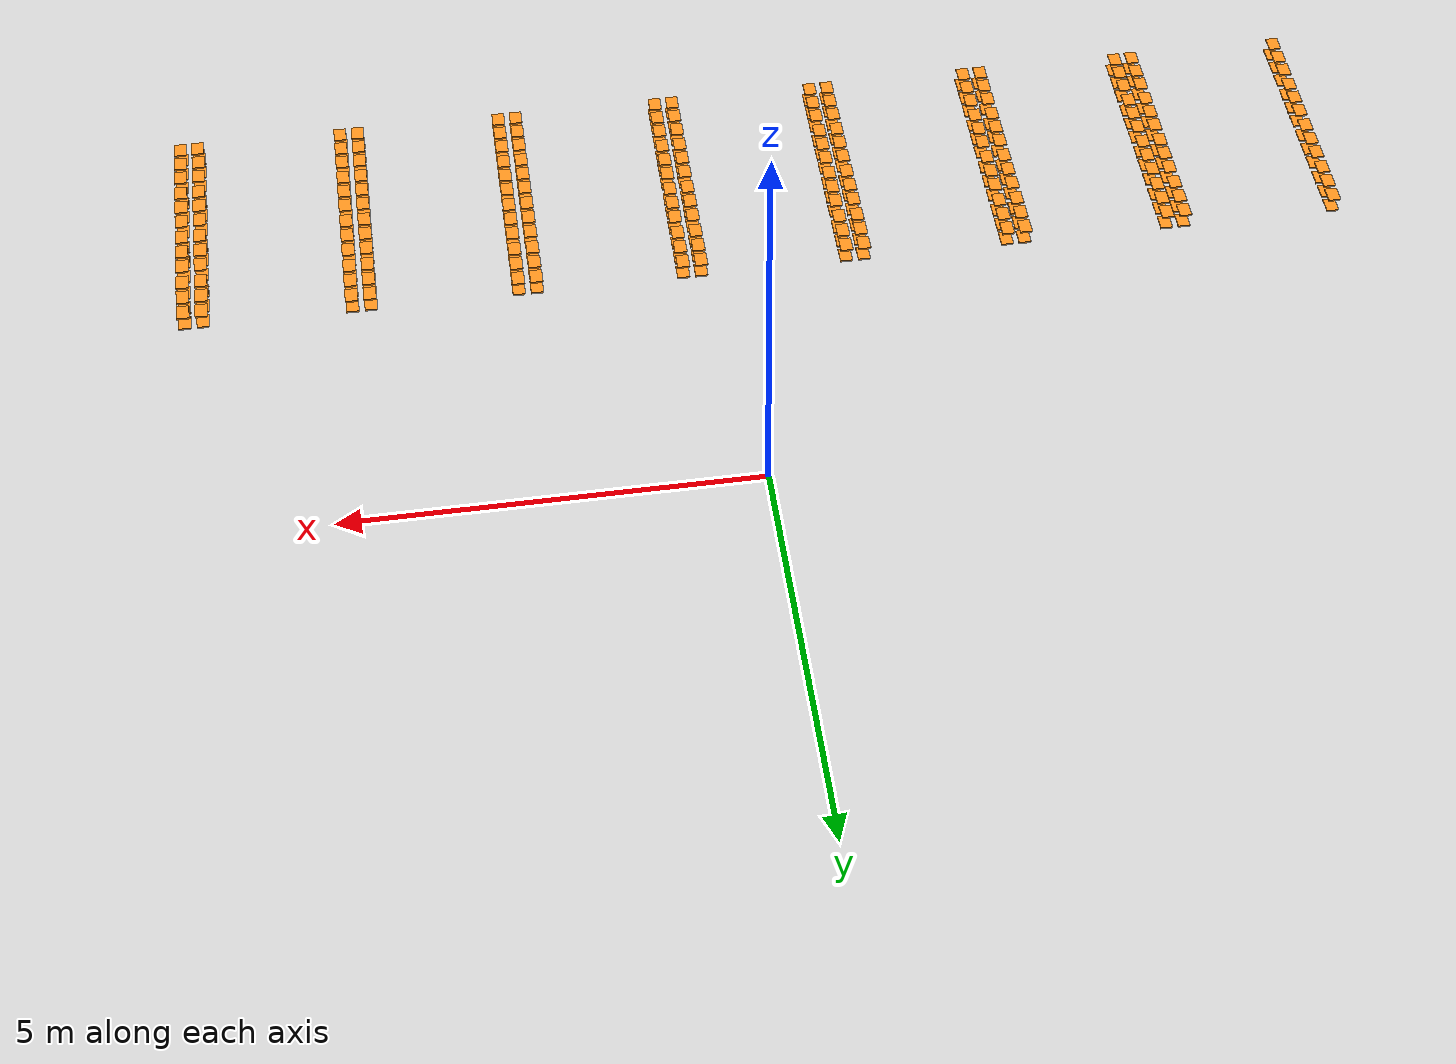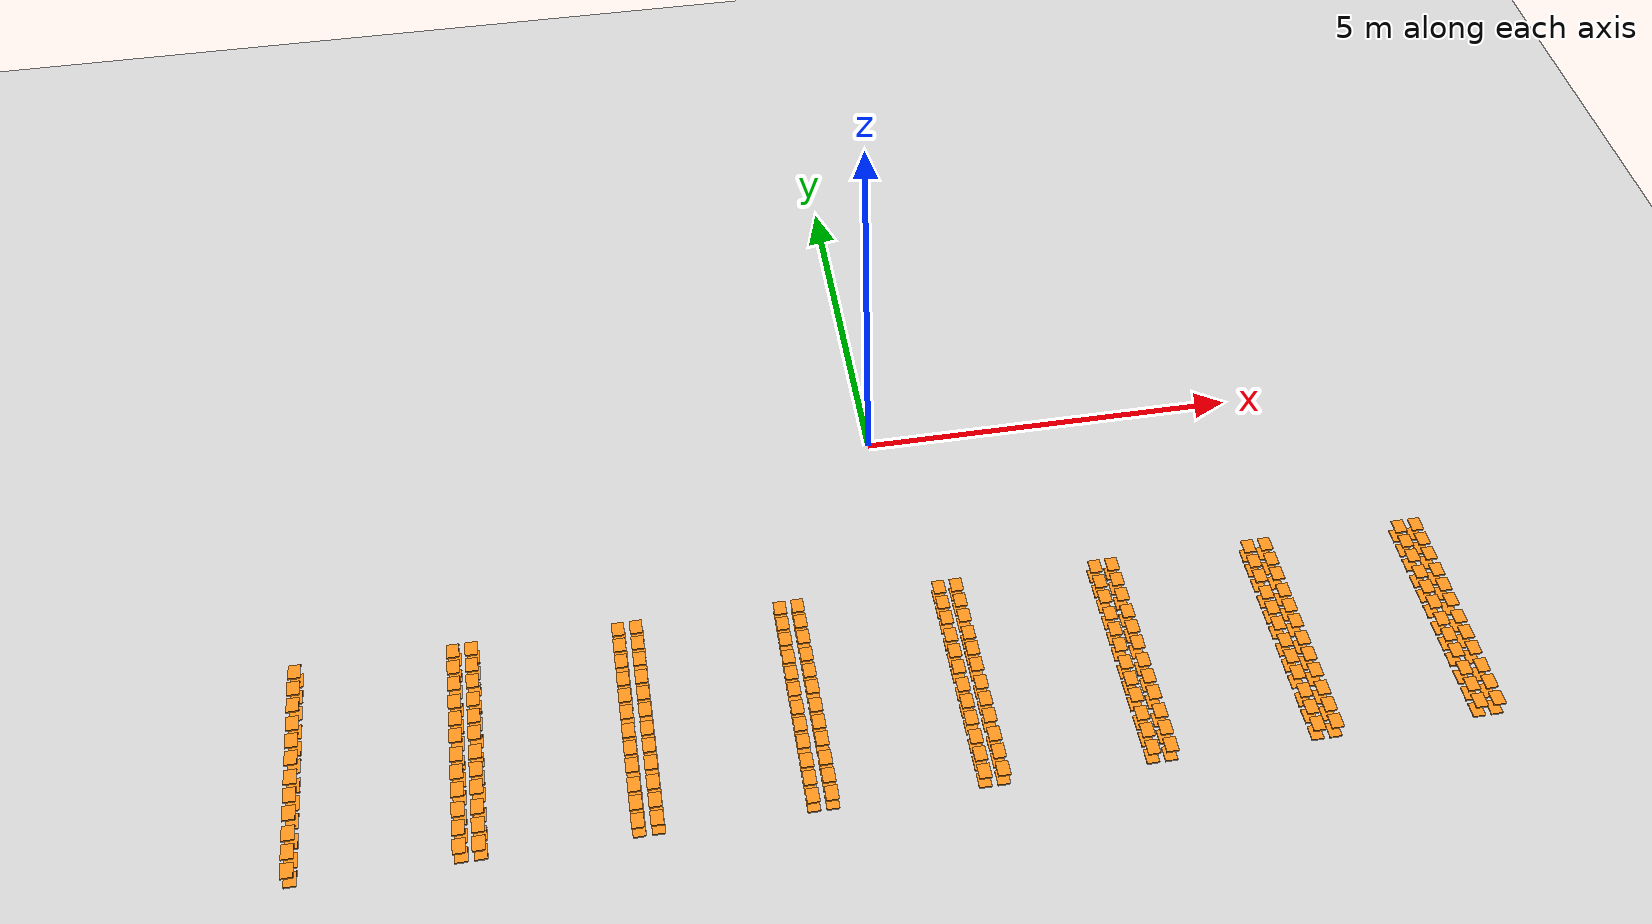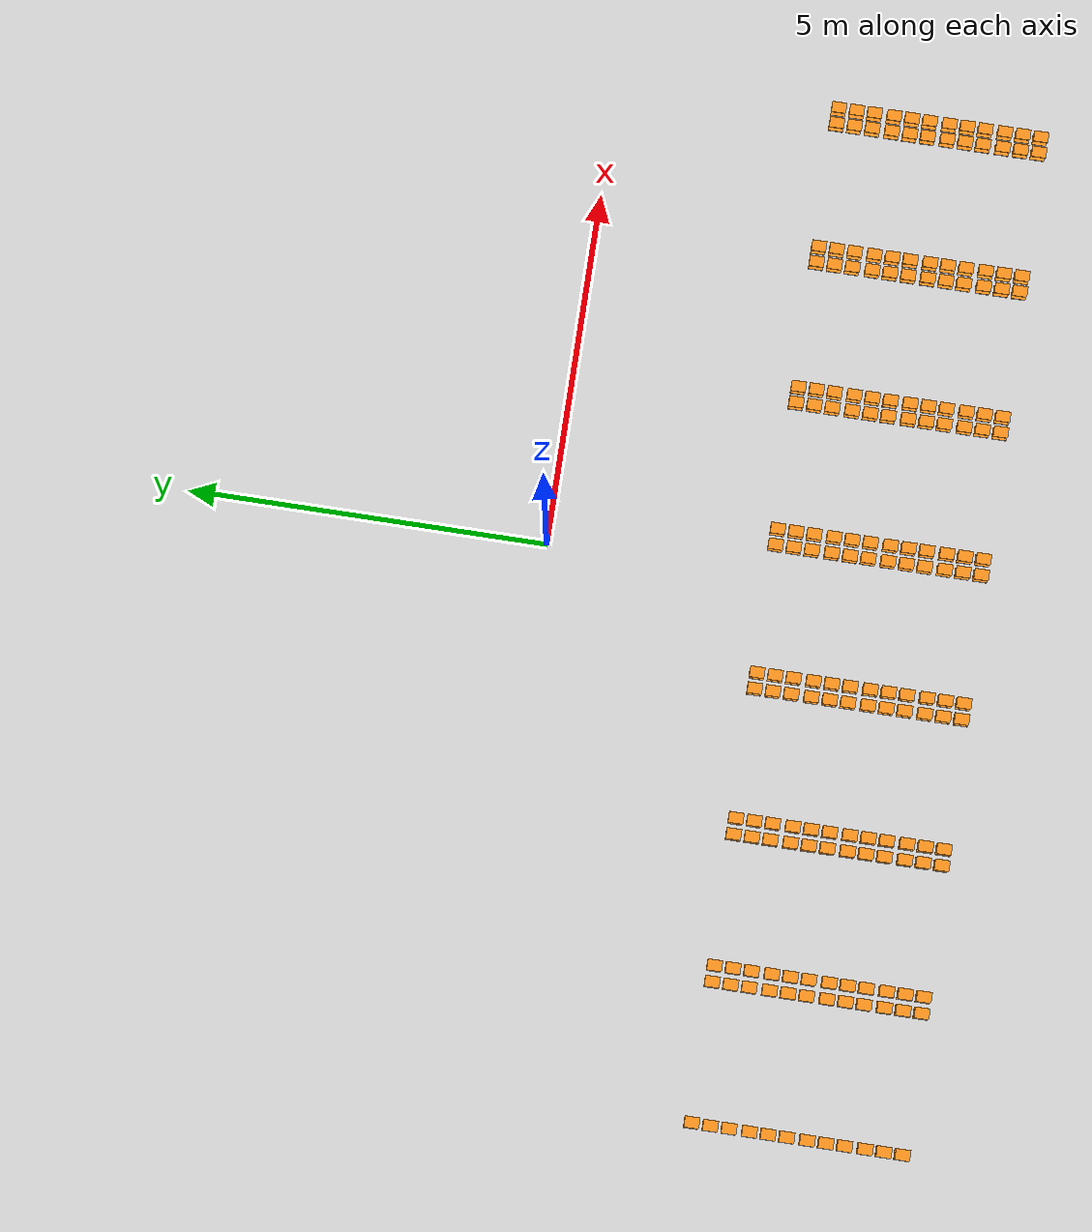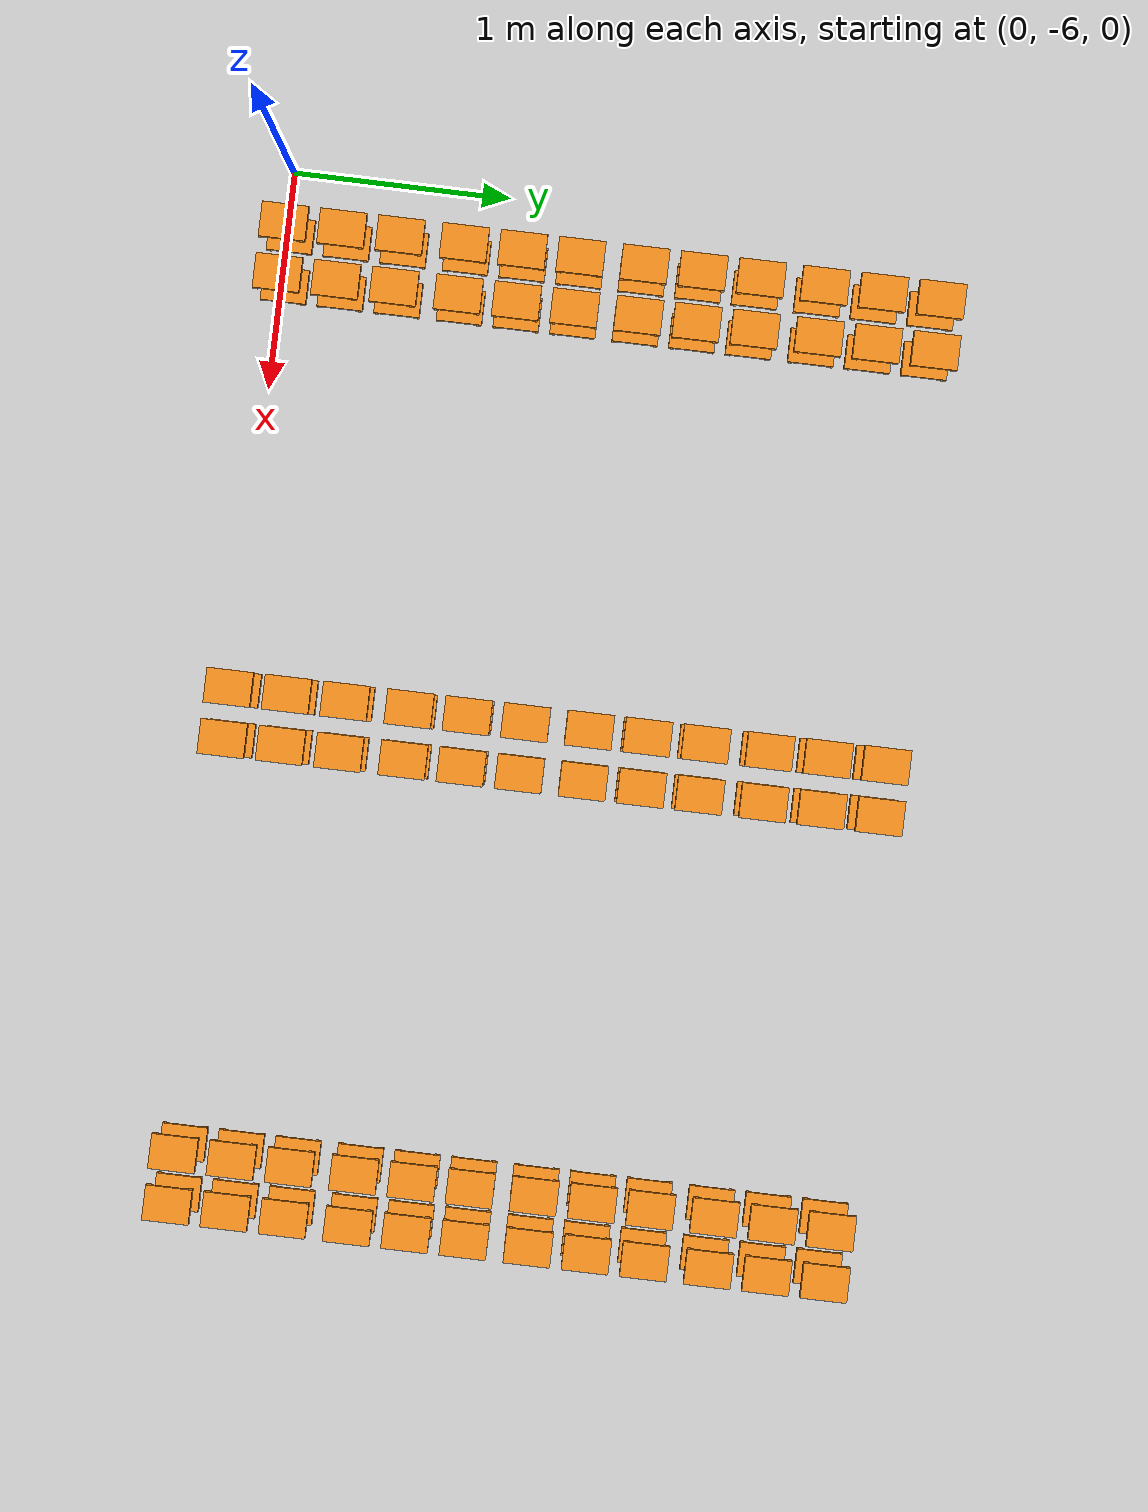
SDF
<sdf version="1.7">
 <world name="default">
  <light name="sun" type="directional">
   <pose>0 0 10 0 -0 0</pose>
   <diffuse>0.8 0.8 0.8 1</diffuse>
   <specular>0.2 0.2 0.2 1</specular>
   <attenuation>
    <range>1000</range>
    <constant>0.9</constant>
    <linear>0.01</linear>
    <quadratic>0.001</quadratic>
   </attenuation>
   <direction>-0.5 0.1 -0.9</direction>
   <spot><inner_angle>0</inner_angle><outer_angle>0</outer_angle><falloff>0</falloff></spot>
  </light>
  <model name="ground_plane">
   <static>1</static>
   <link name="link">
    <collision name="collision">
     <geometry><plane><normal>0 0 1</normal><size>100 100</size></plane></geometry>
     <surface>
      <contact><collide_bitmask>65535</collide_bitmask></contact>
      <friction><ode><mu>1</mu><mu2>1</mu2></ode></friction>
     </surface>
    </collision>
    <visual name="visual">
     <cast_shadows>0</cast_shadows>
     <geometry><plane><normal>0 0 1</normal><size>100 100</size></plane></geometry>
     <material>
      <script><uri>file://media/materials/scripts/gazebo.material</uri><name>Gazebo/Grey</name></script>
     </material>
    </visual>
   </link>
  </model>
  <scene><ambient>0.4 0.4 0.4 1</ambient><background>0.7 0.7 0.7 1</background><shadows>1</shadows></scene>
  <audio><device>default</device></audio>
  <spherical_coordinates>
   <surface_model>EARTH_WGS84</surface_model>
   <latitude_deg>0</latitude_deg>
   <longitude_deg>0</longitude_deg>
   <elevation>0</elevation>
   <heading_deg>0</heading_deg>
  </spherical_coordinates>
  <model name="pallet_1">
   <pose>-7.5 -3.088 0.512 0 0 0</pose>
   <link name="link">
    <inertial>
     <pose>0 0 0 0 -0 1.571</pose>
     <inertia>
      <ixx>0.00220983</ixx>
      <ixy>0</ixy>
      <ixz>0</ixz>
      <iyy>0.00128087</iyy>
      <iyz>0</iyz>
      <izz>0.00244903</izz>
     </inertia>
     <mass>0.01</mass>
    </inertial>
    <visual name="visual1">
     <cast_shadows>0</cast_shadows>
     <geometry><mesh><uri>model://pallet/meshes/pallet.stl</uri></mesh></geometry>
     <material>
      <script><uri>file://media/materials/scripts/gazebo.material</uri><name>Gazebo/Orange</name></script>
      <shader type="pixel"><normal_map>__default__</normal_map></shader>
      <emissive>0 0 0 1</emissive>
     </material>
     <pose>0 0 -0 0 -0 1.571</pose>
    </visual>
    <collision name="collision_0">
     <pose>0 0 0 0 -0 1.571</pose>
     <geometry><mesh><uri>model://pallet/meshes/pallet.stl</uri></mesh></geometry>
     <surface>
      <friction>
       <ode><mu>1</mu><mu2>1</mu2><fdir1>0 0 0</fdir1><slip1>0</slip1><slip2>0</slip2></ode>
       <torsional>
        <coefficient>1</coefficient>
        <patch_radius>0</patch_radius>
        <surface_radius>0</surface_radius>
        <use_patch_radius>1</use_patch_radius>
        <ode><slip>0</slip></ode>
       </torsional>
      </friction>
      <bounce><restitution_coefficient>0</restitution_coefficient><threshold>1e+06</threshold></bounce>
      <contact>
       <collide_without_contact>0</collide_without_contact>
       <collide_without_contact_bitmask>1</collide_without_contact_bitmask>
       <collide_bitmask>1</collide_bitmask>
       <ode>
        <soft_cfm>0</soft_cfm>
        <soft_erp>0.2</soft_erp>
        <kp>1e+13</kp>
        <kd>1</kd>
        <max_vel>0.01</max_vel>
        <min_depth>0</min_depth>
       </ode>
       <bullet>
        <split_impulse>1</split_impulse>
        <split_impulse_penetration_threshold>-0.01</split_impulse_penetration_threshold>
        <soft_cfm>0</soft_cfm>
        <soft_erp>0.2</soft_erp>
        <kp>1e+13</kp>
        <kd>1</kd>
       </bullet>
      </contact>
     </surface>
    </collision>
   </link>
   <static>0</static>
  </model>
  <model name="pallet_2">
   <pose>-7.50644 -3.338 0.51102 3.5e-05 -0.01254 4e-06</pose>
   <link name="link">
    <inertial>
     <pose>0 0 0 0 -0 1.571</pose>
     <inertia>
      <ixx>0.00220983</ixx>
      <ixy>0</ixy>
      <ixz>0</ixz>
      <iyy>0.00128087</iyy>
      <iyz>0</iyz>
      <izz>0.00244903</izz>
     </inertia>
     <mass>0.01</mass>
    </inertial>
    <visual name="visual1">
     <cast_shadows>0</cast_shadows>
     <geometry><mesh><uri>model://pallet/meshes/pallet.stl</uri></mesh></geometry>
     <material>
      <script><uri>file://media/materials/scripts/gazebo.material</uri><name>Gazebo/Orange</name></script>
      <shader type="pixel"><normal_map>__default__</normal_map></shader>
      <emissive>0 0 0 1</emissive>
     </material>
     <pose>0 0 -0 0 -0 1.571</pose>
    </visual>
    <collision name="collision_0">
     <pose>0 0 0 0 -0 1.571</pose>
     <geometry><mesh><uri>model://pallet/meshes/pallet.stl</uri></mesh></geometry>
     <surface>
      <friction>
       <ode><mu>1</mu><mu2>1</mu2><fdir1>0 0 0</fdir1><slip1>0</slip1><slip2>0</slip2></ode>
       <torsional>
        <coefficient>1</coefficient>
        <patch_radius>0</patch_radius>
        <surface_radius>0</surface_radius>
        <use_patch_radius>1</use_patch_radius>
        <ode><slip>0</slip></ode>
       </torsional>
      </friction>
      <bounce><restitution_coefficient>0</restitution_coefficient><threshold>1e+06</threshold></bounce>
      <contact>
       <collide_without_contact>0</collide_without_contact>
       <collide_without_contact_bitmask>1</collide_without_contact_bitmask>
       <collide_bitmask>1</collide_bitmask>
       <ode>
        <soft_cfm>0</soft_cfm>
        <soft_erp>0.2</soft_erp>
        <kp>1e+13</kp>
        <kd>1</kd>
        <max_vel>0.01</max_vel>
        <min_depth>0</min_depth>
       </ode>
       <bullet>
        <split_impulse>1</split_impulse>
        <split_impulse_penetration_threshold>-0.01</split_impulse_penetration_threshold>
        <soft_cfm>0</soft_cfm>
        <soft_erp>0.2</soft_erp>
        <kp>1e+13</kp>
        <kd>1</kd>
       </bullet>
      </contact>
     </surface>
    </collision>
   </link>
   <static>0</static>
  </model>
  <model name="pallet_3">
   <pose>-7.50643 -3.588 0.511018 4.4e-05 -0.012541 2e-06</pose>
   <link name="link">
    <inertial>
     <pose>0 0 0 0 -0 1.571</pose>
     <inertia>
      <ixx>0.00220983</ixx>
      <ixy>0</ixy>
      <ixz>0</ixz>
      <iyy>0.00128087</iyy>
      <iyz>0</iyz>
      <izz>0.00244903</izz>
     </inertia>
     <mass>0.01</mass>
    </inertial>
    <visual name="visual1">
     <cast_shadows>0</cast_shadows>
     <geometry><mesh><uri>model://pallet/meshes/pallet.stl</uri></mesh></geometry>
     <material>
      <script><uri>file://media/materials/scripts/gazebo.material</uri><name>Gazebo/Orange</name></script>
      <shader type="pixel"><normal_map>__default__</normal_map></shader>
      <emissive>0 0 0 1</emissive>
     </material>
     <pose>0 0 -0 0 -0 1.571</pose>
    </visual>
    <collision name="collision_0">
     <pose>0 0 0 0 -0 1.571</pose>
     <geometry><mesh><uri>model://pallet/meshes/pallet.stl</uri></mesh></geometry>
     <surface>
      <friction>
       <ode><mu>1</mu><mu2>1</mu2><fdir1>0 0 0</fdir1><slip1>0</slip1><slip2>0</slip2></ode>
       <torsional>
        <coefficient>1</coefficient>
        <patch_radius>0</patch_radius>
        <surface_radius>0</surface_radius>
        <use_patch_radius>1</use_patch_radius>
        <ode><slip>0</slip></ode>
       </torsional>
      </friction>
      <bounce><restitution_coefficient>0</restitution_coefficient><threshold>1e+06</threshold></bounce>
      <contact>
       <collide_without_contact>0</collide_without_contact>
       <collide_without_contact_bitmask>1</collide_without_contact_bitmask>
       <collide_bitmask>1</collide_bitmask>
       <ode>
        <soft_cfm>0</soft_cfm>
        <soft_erp>0.2</soft_erp>
        <kp>1e+13</kp>
        <kd>1</kd>
        <max_vel>0.01</max_vel>
        <min_depth>0</min_depth>
       </ode>
       <bullet>
        <split_impulse>1</split_impulse>
        <split_impulse_penetration_threshold>-0.01</split_impulse_penetration_threshold>
        <soft_cfm>0</soft_cfm>
        <soft_erp>0.2</soft_erp>
        <kp>1e+13</kp>
        <kd>1</kd>
       </bullet>
      </contact>
     </surface>
    </collision>
   </link>
   <static>0</static>
  </model>
  <model name="pallet_4">
   <pose>-7.50643 -3.8625 0.51102 1.2e-05 -0.012548 2e-06</pose>
   <link name="link">
    <inertial>
     <pose>0 0 0 0 -0 1.571</pose>
     <inertia>
      <ixx>0.00220983</ixx>
      <ixy>0</ixy>
      <ixz>0</ixz>
      <iyy>0.00128087</iyy>
      <iyz>0</iyz>
      <izz>0.00244903</izz>
     </inertia>
     <mass>0.01</mass>
    </inertial>
    <visual name="visual1">
     <cast_shadows>0</cast_shadows>
     <geometry><mesh><uri>model://pallet/meshes/pallet.stl</uri></mesh></geometry>
     <material>
      <script><uri>file://media/materials/scripts/gazebo.material</uri><name>Gazebo/Orange</name></script>
      <shader type="pixel"><normal_map>__default__</normal_map></shader>
      <emissive>0 0 0 1</emissive>
     </material>
     <pose>0 0 -0 0 -0 1.571</pose>
    </visual>
    <collision name="collision_0">
     <pose>0 0 0 0 -0 1.571</pose>
     <geometry><mesh><uri>model://pallet/meshes/pallet.stl</uri></mesh></geometry>
     <surface>
      <friction>
       <ode><mu>1</mu><mu2>1</mu2><fdir1>0 0 0</fdir1><slip1>0</slip1><slip2>0</slip2></ode>
       <torsional>
        <coefficient>1</coefficient>
        <patch_radius>0</patch_radius>
        <surface_radius>0</surface_radius>
        <use_patch_radius>1</use_patch_radius>
        <ode><slip>0</slip></ode>
       </torsional>
      </friction>
      <bounce><restitution_coefficient>0</restitution_coefficient><threshold>1e+06</threshold></bounce>
      <contact>
       <collide_without_contact>0</collide_without_contact>
       <collide_without_contact_bitmask>1</collide_without_contact_bitmask>
       <collide_bitmask>1</collide_bitmask>
       <ode>
        <soft_cfm>0</soft_cfm>
        <soft_erp>0.2</soft_erp>
        <kp>1e+13</kp>
        <kd>1</kd>
        <max_vel>0.01</max_vel>
        <min_depth>0</min_depth>
       </ode>
       <bullet>
        <split_impulse>1</split_impulse>
        <split_impulse_penetration_threshold>-0.01</split_impulse_penetration_threshold>
        <soft_cfm>0</soft_cfm>
        <soft_erp>0.2</soft_erp>
        <kp>1e+13</kp>
        <kd>1</kd>
       </bullet>
      </contact>
     </surface>
    </collision>
   </link>
   <static>0</static>
  </model>
  <model name="pallet_5">
   <pose>-7.50643 -4.1125 0.511017 2.9e-05 -0.012542 1e-06</pose>
   <link name="link">
    <inertial>
     <pose>0 0 0 0 -0 1.571</pose>
     <inertia>
      <ixx>0.00220983</ixx>
      <ixy>0</ixy>
      <ixz>0</ixz>
      <iyy>0.00128087</iyy>
      <iyz>0</iyz>
      <izz>0.00244903</izz>
     </inertia>
     <mass>0.01</mass>
    </inertial>
    <visual name="visual1">
     <cast_shadows>0</cast_shadows>
     <geometry><mesh><uri>model://pallet/meshes/pallet.stl</uri></mesh></geometry>
     <material>
      <script><uri>file://media/materials/scripts/gazebo.material</uri><name>Gazebo/Orange</name></script>
      <shader type="pixel"><normal_map>__default__</normal_map></shader>
      <emissive>0 0 0 1</emissive>
     </material>
     <pose>0 0 -0 0 -0 1.571</pose>
    </visual>
    <collision name="collision_0">
     <pose>0 0 0 0 -0 1.571</pose>
     <geometry><mesh><uri>model://pallet/meshes/pallet.stl</uri></mesh></geometry>
     <surface>
      <friction>
       <ode><mu>1</mu><mu2>1</mu2><fdir1>0 0 0</fdir1><slip1>0</slip1><slip2>0</slip2></ode>
       <torsional>
        <coefficient>1</coefficient>
        <patch_radius>0</patch_radius>
        <surface_radius>0</surface_radius>
        <use_patch_radius>1</use_patch_radius>
        <ode><slip>0</slip></ode>
       </torsional>
      </friction>
      <bounce><restitution_coefficient>0</restitution_coefficient><threshold>1e+06</threshold></bounce>
      <contact>
       <collide_without_contact>0</collide_without_contact>
       <collide_without_contact_bitmask>1</collide_without_contact_bitmask>
       <collide_bitmask>1</collide_bitmask>
       <ode>
        <soft_cfm>0</soft_cfm>
        <soft_erp>0.2</soft_erp>
        <kp>1e+13</kp>
        <kd>1</kd>
        <max_vel>0.01</max_vel>
        <min_depth>0</min_depth>
       </ode>
       <bullet>
        <split_impulse>1</split_impulse>
        <split_impulse_penetration_threshold>-0.01</split_impulse_penetration_threshold>
        <soft_cfm>0</soft_cfm>
        <soft_erp>0.2</soft_erp>
        <kp>1e+13</kp>
        <kd>1</kd>
       </bullet>
      </contact>
     </surface>
    </collision>
   </link>
   <static>0</static>
  </model>
  <model name="pallet_6">
   <pose>-7.50643 -4.3625 0.511017 3.5e-05 -0.012542 9e-06</pose>
   <link name="link">
    <inertial>
     <pose>0 0 0 0 -0 1.571</pose>
     <inertia>
      <ixx>0.00220983</ixx>
      <ixy>0</ixy>
      <ixz>0</ixz>
      <iyy>0.00128087</iyy>
      <iyz>0</iyz>
      <izz>0.00244903</izz>
     </inertia>
     <mass>0.01</mass>
    </inertial>
    <visual name="visual1">
     <cast_shadows>0</cast_shadows>
     <geometry><mesh><uri>model://pallet/meshes/pallet.stl</uri></mesh></geometry>
     <material>
      <script><uri>file://media/materials/scripts/gazebo.material</uri><name>Gazebo/Orange</name></script>
      <shader type="pixel"><normal_map>__default__</normal_map></shader>
      <emissive>0 0 0 1</emissive>
     </material>
     <pose>0 0 -0 0 -0 1.571</pose>
    </visual>
    <collision name="collision_0">
     <pose>0 0 0 0 -0 1.571</pose>
     <geometry><mesh><uri>model://pallet/meshes/pallet.stl</uri></mesh></geometry>
     <surface>
      <friction>
       <ode><mu>1</mu><mu2>1</mu2><fdir1>0 0 0</fdir1><slip1>0</slip1><slip2>0</slip2></ode>
       <torsional>
        <coefficient>1</coefficient>
        <patch_radius>0</patch_radius>
        <surface_radius>0</surface_radius>
        <use_patch_radius>1</use_patch_radius>
        <ode><slip>0</slip></ode>
       </torsional>
      </friction>
      <bounce><restitution_coefficient>0</restitution_coefficient><threshold>1e+06</threshold></bounce>
      <contact>
       <collide_without_contact>0</collide_without_contact>
       <collide_without_contact_bitmask>1</collide_without_contact_bitmask>
       <collide_bitmask>1</collide_bitmask>
       <ode>
        <soft_cfm>0</soft_cfm>
        <soft_erp>0.2</soft_erp>
        <kp>1e+13</kp>
        <kd>1</kd>
        <max_vel>0.01</max_vel>
        <min_depth>0</min_depth>
       </ode>
       <bullet>
        <split_impulse>1</split_impulse>
        <split_impulse_penetration_threshold>-0.01</split_impulse_penetration_threshold>
        <soft_cfm>0</soft_cfm>
        <soft_erp>0.2</soft_erp>
        <kp>1e+13</kp>
        <kd>1</kd>
       </bullet>
      </contact>
     </surface>
    </collision>
   </link>
   <static>0</static>
  </model>
  <model name="pallet_7">
   <pose>-7.50643 -4.637 0.511016 2.1e-05 -0.012542 7e-06</pose>
   <link name="link">
    <inertial>
     <pose>0 0 0 0 -0 1.571</pose>
     <inertia>
      <ixx>0.00220983</ixx>
      <ixy>0</ixy>
      <ixz>0</ixz>
      <iyy>0.00128087</iyy>
      <iyz>0</iyz>
      <izz>0.00244903</izz>
     </inertia>
     <mass>0.01</mass>
    </inertial>
    <visual name="visual1">
     <cast_shadows>0</cast_shadows>
     <geometry><mesh><uri>model://pallet/meshes/pallet.stl</uri></mesh></geometry>
     <material>
      <script><uri>file://media/materials/scripts/gazebo.material</uri><name>Gazebo/Orange</name></script>
      <shader type="pixel"><normal_map>__default__</normal_map></shader>
      <emissive>0 0 0 1</emissive>
     </material>
     <pose>0 0 -0 0 -0 1.571</pose>
    </visual>
    <collision name="collision_0">
     <pose>0 0 0 0 -0 1.571</pose>
     <geometry><mesh><uri>model://pallet/meshes/pallet.stl</uri></mesh></geometry>
     <surface>
      <friction>
       <ode><mu>1</mu><mu2>1</mu2><fdir1>0 0 0</fdir1><slip1>0</slip1><slip2>0</slip2></ode>
       <torsional>
        <coefficient>1</coefficient>
        <patch_radius>0</patch_radius>
        <surface_radius>0</surface_radius>
        <use_patch_radius>1</use_patch_radius>
        <ode><slip>0</slip></ode>
       </torsional>
      </friction>
      <bounce><restitution_coefficient>0</restitution_coefficient><threshold>1e+06</threshold></bounce>
      <contact>
       <collide_without_contact>0</collide_without_contact>
       <collide_without_contact_bitmask>1</collide_without_contact_bitmask>
       <collide_bitmask>1</collide_bitmask>
       <ode>
        <soft_cfm>0</soft_cfm>
        <soft_erp>0.2</soft_erp>
        <kp>1e+13</kp>
        <kd>1</kd>
        <max_vel>0.01</max_vel>
        <min_depth>0</min_depth>
       </ode>
       <bullet>
        <split_impulse>1</split_impulse>
        <split_impulse_penetration_threshold>-0.01</split_impulse_penetration_threshold>
        <soft_cfm>0</soft_cfm>
        <soft_erp>0.2</soft_erp>
        <kp>1e+13</kp>
        <kd>1</kd>
       </bullet>
      </contact>
     </surface>
    </collision>
   </link>
   <static>0</static>
  </model>
  <model name="pallet_8">
   <pose>-7.50642 -4.887 0.511015 2.9e-05 -0.012541 -1e-05</pose>
   <link name="link">
    <inertial>
     <pose>0 0 0 0 -0 1.571</pose>
     <inertia>
      <ixx>0.00220983</ixx>
      <ixy>0</ixy>
      <ixz>0</ixz>
      <iyy>0.00128087</iyy>
      <iyz>0</iyz>
      <izz>0.00244903</izz>
     </inertia>
     <mass>0.01</mass>
    </inertial>
    <visual name="visual1">
     <cast_shadows>0</cast_shadows>
     <geometry><mesh><uri>model://pallet/meshes/pallet.stl</uri></mesh></geometry>
     <material>
      <script><uri>file://media/materials/scripts/gazebo.material</uri><name>Gazebo/Orange</name></script>
      <shader type="pixel"><normal_map>__default__</normal_map></shader>
      <emissive>0 0 0 1</emissive>
     </material>
     <pose>0 0 -0 0 -0 1.571</pose>
    </visual>
    <collision name="collision_0">
     <pose>0 0 0 0 -0 1.571</pose>
     <geometry><mesh><uri>model://pallet/meshes/pallet.stl</uri></mesh></geometry>
     <surface>
      <friction>
       <ode><mu>1</mu><mu2>1</mu2><fdir1>0 0 0</fdir1><slip1>0</slip1><slip2>0</slip2></ode>
       <torsional>
        <coefficient>1</coefficient>
        <patch_radius>0</patch_radius>
        <surface_radius>0</surface_radius>
        <use_patch_radius>1</use_patch_radius>
        <ode><slip>0</slip></ode>
       </torsional>
      </friction>
      <bounce><restitution_coefficient>0</restitution_coefficient><threshold>1e+06</threshold></bounce>
      <contact>
       <collide_without_contact>0</collide_without_contact>
       <collide_without_contact_bitmask>1</collide_without_contact_bitmask>
       <collide_bitmask>1</collide_bitmask>
       <ode>
        <soft_cfm>0</soft_cfm>
        <soft_erp>0.2</soft_erp>
        <kp>1e+13</kp>
        <kd>1</kd>
        <max_vel>0.01</max_vel>
        <min_depth>0</min_depth>
       </ode>
       <bullet>
        <split_impulse>1</split_impulse>
        <split_impulse_penetration_threshold>-0.01</split_impulse_penetration_threshold>
        <soft_cfm>0</soft_cfm>
        <soft_erp>0.2</soft_erp>
        <kp>1e+13</kp>
        <kd>1</kd>
       </bullet>
      </contact>
     </surface>
    </collision>
   </link>
   <static>0</static>
  </model>
  <model name="pallet_9">
   <pose>-7.50642 -5.137 0.511016 1.2e-05 -0.012545 5e-06</pose>
   <link name="link">
    <inertial>
     <pose>0 0 0 0 -0 1.571</pose>
     <inertia>
      <ixx>0.00220983</ixx>
      <ixy>0</ixy>
      <ixz>0</ixz>
      <iyy>0.00128087</iyy>
      <iyz>0</iyz>
      <izz>0.00244903</izz>
     </inertia>
     <mass>0.01</mass>
    </inertial>
    <visual name="visual1">
     <cast_shadows>0</cast_shadows>
     <geometry><mesh><uri>model://pallet/meshes/pallet.stl</uri></mesh></geometry>
     <material>
      <script><uri>file://media/materials/scripts/gazebo.material</uri><name>Gazebo/Orange</name></script>
      <shader type="pixel"><normal_map>__default__</normal_map></shader>
      <emissive>0 0 0 1</emissive>
     </material>
     <pose>0 0 -0 0 -0 1.571</pose>
    </visual>
    <collision name="collision_0">
     <pose>0 0 0 0 -0 1.571</pose>
     <geometry><mesh><uri>model://pallet/meshes/pallet.stl</uri></mesh></geometry>
     <surface>
      <friction>
       <ode><mu>1</mu><mu2>1</mu2><fdir1>0 0 0</fdir1><slip1>0</slip1><slip2>0</slip2></ode>
       <torsional>
        <coefficient>1</coefficient>
        <patch_radius>0</patch_radius>
        <surface_radius>0</surface_radius>
        <use_patch_radius>1</use_patch_radius>
        <ode><slip>0</slip></ode>
       </torsional>
      </friction>
      <bounce><restitution_coefficient>0</restitution_coefficient><threshold>1e+06</threshold></bounce>
      <contact>
       <collide_without_contact>0</collide_without_contact>
       <collide_without_contact_bitmask>1</collide_without_contact_bitmask>
       <collide_bitmask>1</collide_bitmask>
       <ode>
        <soft_cfm>0</soft_cfm>
        <soft_erp>0.2</soft_erp>
        <kp>1e+13</kp>
        <kd>1</kd>
        <max_vel>0.01</max_vel>
        <min_depth>0</min_depth>
       </ode>
       <bullet>
        <split_impulse>1</split_impulse>
        <split_impulse_penetration_threshold>-0.01</split_impulse_penetration_threshold>
        <soft_cfm>0</soft_cfm>
        <soft_erp>0.2</soft_erp>
        <kp>1e+13</kp>
        <kd>1</kd>
       </bullet>
      </contact>
     </surface>
    </collision>
   </link>
   <static>0</static>
  </model>
  <model name="pallet_10">
   <pose>-7.50642 -5.6625 0.511013 2.2e-05 -0.012543 -1e-05</pose>
   <link name="link">
    <inertial>
     <pose>0 0 0 0 -0 1.571</pose>
     <inertia>
      <ixx>0.00220983</ixx>
      <ixy>0</ixy>
      <ixz>0</ixz>
      <iyy>0.00128087</iyy>
      <iyz>0</iyz>
      <izz>0.00244903</izz>
     </inertia>
     <mass>0.01</mass>
    </inertial>
    <visual name="visual1">
     <cast_shadows>0</cast_shadows>
     <geometry><mesh><uri>model://pallet/meshes/pallet.stl</uri></mesh></geometry>
     <material>
      <script><uri>file://media/materials/scripts/gazebo.material</uri><name>Gazebo/Orange</name></script>
      <shader type="pixel"><normal_map>__default__</normal_map></shader>
      <emissive>0 0 0 1</emissive>
     </material>
     <pose>0 0 -0 0 -0 1.571</pose>
    </visual>
    <collision name="collision_0">
     <pose>0 0 0 0 -0 1.571</pose>
     <geometry><mesh><uri>model://pallet/meshes/pallet.stl</uri></mesh></geometry>
     <surface>
      <friction>
       <ode><mu>1</mu><mu2>1</mu2><fdir1>0 0 0</fdir1><slip1>0</slip1><slip2>0</slip2></ode>
       <torsional>
        <coefficient>1</coefficient>
        <patch_radius>0</patch_radius>
        <surface_radius>0</surface_radius>
        <use_patch_radius>1</use_patch_radius>
        <ode><slip>0</slip></ode>
       </torsional>
      </friction>
      <bounce><restitution_coefficient>0</restitution_coefficient><threshold>1e+06</threshold></bounce>
      <contact>
       <collide_without_contact>0</collide_without_contact>
       <collide_without_contact_bitmask>1</collide_without_contact_bitmask>
       <collide_bitmask>1</collide_bitmask>
       <ode>
        <soft_cfm>0</soft_cfm>
        <soft_erp>0.2</soft_erp>
        <kp>1e+13</kp>
        <kd>1</kd>
        <max_vel>0.01</max_vel>
        <min_depth>0</min_depth>
       </ode>
       <bullet>
        <split_impulse>1</split_impulse>
        <split_impulse_penetration_threshold>-0.01</split_impulse_penetration_threshold>
        <soft_cfm>0</soft_cfm>
        <soft_erp>0.2</soft_erp>
        <kp>1e+13</kp>
        <kd>1</kd>
       </bullet>
      </contact>
     </surface>
    </collision>
   </link>
   <static>0</static>
  </model>
  <model name="pallet_11">
   <pose>-7.50642 -5.4125 0.511015 1.2e-05 -0.012542 2.4e-05</pose>
   <link name="link">
    <inertial>
     <pose>0 0 0 0 -0 1.571</pose>
     <inertia>
      <ixx>0.00220983</ixx>
      <ixy>0</ixy>
      <ixz>0</ixz>
      <iyy>0.00128087</iyy>
      <iyz>0</iyz>
      <izz>0.00244903</izz>
     </inertia>
     <mass>0.01</mass>
    </inertial>
    <visual name="visual1">
     <cast_shadows>0</cast_shadows>
     <geometry><mesh><uri>model://pallet/meshes/pallet.stl</uri></mesh></geometry>
     <material>
      <script><uri>file://media/materials/scripts/gazebo.material</uri><name>Gazebo/Orange</name></script>
      <shader type="pixel"><normal_map>__default__</normal_map></shader>
      <emissive>0 0 0 1</emissive>
     </material>
     <pose>0 0 -0 0 -0 1.571</pose>
    </visual>
    <collision name="collision_0">
     <pose>0 0 0 0 -0 1.571</pose>
     <geometry><mesh><uri>model://pallet/meshes/pallet.stl</uri></mesh></geometry>
     <surface>
      <friction>
       <ode><mu>1</mu><mu2>1</mu2><fdir1>0 0 0</fdir1><slip1>0</slip1><slip2>0</slip2></ode>
       <torsional>
        <coefficient>1</coefficient>
        <patch_radius>0</patch_radius>
        <surface_radius>0</surface_radius>
        <use_patch_radius>1</use_patch_radius>
        <ode><slip>0</slip></ode>
       </torsional>
      </friction>
      <bounce><restitution_coefficient>0</restitution_coefficient><threshold>1e+06</threshold></bounce>
      <contact>
       <collide_without_contact>0</collide_without_contact>
       <collide_without_contact_bitmask>1</collide_without_contact_bitmask>
       <collide_bitmask>1</collide_bitmask>
       <ode>
        <soft_cfm>0</soft_cfm>
        <soft_erp>0.2</soft_erp>
        <kp>1e+13</kp>
        <kd>1</kd>
        <max_vel>0.01</max_vel>
        <min_depth>0</min_depth>
       </ode>
       <bullet>
        <split_impulse>1</split_impulse>
        <split_impulse_penetration_threshold>-0.01</split_impulse_penetration_threshold>
        <soft_cfm>0</soft_cfm>
        <soft_erp>0.2</soft_erp>
        <kp>1e+13</kp>
        <kd>1</kd>
       </bullet>
      </contact>
     </surface>
    </collision>
   </link>
   <static>0</static>
  </model>
  <model name="pallet_12">
   <pose>-7.50641 -5.9125 0.511012 2e-05 -0.012542 -1e-06</pose>
   <link name="link">
    <inertial>
     <pose>0 0 0 0 -0 1.571</pose>
     <inertia>
      <ixx>0.00220983</ixx>
      <ixy>0</ixy>
      <ixz>0</ixz>
      <iyy>0.00128087</iyy>
      <iyz>0</iyz>
      <izz>0.00244903</izz>
     </inertia>
     <mass>0.01</mass>
    </inertial>
    <visual name="visual1">
     <cast_shadows>0</cast_shadows>
     <geometry><mesh><uri>model://pallet/meshes/pallet.stl</uri></mesh></geometry>
     <material>
      <script><uri>file://media/materials/scripts/gazebo.material</uri><name>Gazebo/Orange</name></script>
      <shader type="pixel"><normal_map>__default__</normal_map></shader>
      <emissive>0 0 0 1</emissive>
     </material>
     <pose>0 0 -0 0 -0 1.571</pose>
    </visual>
    <collision name="collision_0">
     <pose>0 0 0 0 -0 1.571</pose>
     <geometry><mesh><uri>model://pallet/meshes/pallet.stl</uri></mesh></geometry>
     <surface>
      <friction>
       <ode><mu>1</mu><mu2>1</mu2><fdir1>0 0 0</fdir1><slip1>0</slip1><slip2>0</slip2></ode>
       <torsional>
        <coefficient>1</coefficient>
        <patch_radius>0</patch_radius>
        <surface_radius>0</surface_radius>
        <use_patch_radius>1</use_patch_radius>
        <ode><slip>0</slip></ode>
       </torsional>
      </friction>
      <bounce><restitution_coefficient>0</restitution_coefficient><threshold>1e+06</threshold></bounce>
      <contact>
       <collide_without_contact>0</collide_without_contact>
       <collide_without_contact_bitmask>1</collide_without_contact_bitmask>
       <collide_bitmask>1</collide_bitmask>
       <ode>
        <soft_cfm>0</soft_cfm>
        <soft_erp>0.2</soft_erp>
        <kp>1e+13</kp>
        <kd>1</kd>
        <max_vel>0.01</max_vel>
        <min_depth>0</min_depth>
       </ode>
       <bullet>
        <split_impulse>1</split_impulse>
        <split_impulse_penetration_threshold>-0.01</split_impulse_penetration_threshold>
        <soft_cfm>0</soft_cfm>
        <soft_erp>0.2</soft_erp>
        <kp>1e+13</kp>
        <kd>1</kd>
       </bullet>
      </contact>
     </surface>
    </collision>
   </link>
   <static>0</static>
  </model>
  <model name="pallet_13">
   <pose>-7.50418 -3.088 0.331032 8e-06 -0.012541 -3e-06</pose>
   <link name="link">
    <inertial>
     <pose>0 0 0 0 -0 1.571</pose>
     <inertia>
      <ixx>0.00220983</ixx>
      <ixy>0</ixy>
      <ixz>0</ixz>
      <iyy>0.00128087</iyy>
      <iyz>0</iyz>
      <izz>0.00244903</izz>
     </inertia>
     <mass>0.01</mass>
    </inertial>
    <visual name="visual1">
     <cast_shadows>0</cast_shadows>
     <geometry><mesh><uri>model://pallet/meshes/pallet.stl</uri></mesh></geometry>
     <material>
      <script><uri>file://media/materials/scripts/gazebo.material</uri><name>Gazebo/Orange</name></script>
      <shader type="pixel"><normal_map>__default__</normal_map></shader>
      <emissive>0 0 0 1</emissive>
     </material>
     <pose>0 0 -0 0 -0 1.571</pose>
    </visual>
    <collision name="collision_0">
     <pose>0 0 0 0 -0 1.571</pose>
     <geometry><mesh><uri>model://pallet/meshes/pallet.stl</uri></mesh></geometry>
     <surface>
      <friction>
       <ode><mu>1</mu><mu2>1</mu2><fdir1>0 0 0</fdir1><slip1>0</slip1><slip2>0</slip2></ode>
       <torsional>
        <coefficient>1</coefficient>
        <patch_radius>0</patch_radius>
        <surface_radius>0</surface_radius>
        <use_patch_radius>1</use_patch_radius>
        <ode><slip>0</slip></ode>
       </torsional>
      </friction>
      <bounce><restitution_coefficient>0</restitution_coefficient><threshold>1e+06</threshold></bounce>
      <contact>
       <collide_without_contact>0</collide_without_contact>
       <collide_without_contact_bitmask>1</collide_without_contact_bitmask>
       <collide_bitmask>1</collide_bitmask>
       <ode>
        <soft_cfm>0</soft_cfm>
        <soft_erp>0.2</soft_erp>
        <kp>1e+13</kp>
        <kd>1</kd>
        <max_vel>0.01</max_vel>
        <min_depth>0</min_depth>
       </ode>
       <bullet>
        <split_impulse>1</split_impulse>
        <split_impulse_penetration_threshold>-0.01</split_impulse_penetration_threshold>
        <soft_cfm>0</soft_cfm>
        <soft_erp>0.2</soft_erp>
        <kp>1e+13</kp>
        <kd>1</kd>
       </bullet>
      </contact>
     </surface>
    </collision>
   </link>
   <static>0</static>
  </model>
  <model name="pallet_14">
   <pose>-7.50418 -3.338 0.331033 4.2e-05 -0.012542 4e-06</pose>
   <link name="link">
    <inertial>
     <pose>0 0 0 0 -0 1.571</pose>
     <inertia>
      <ixx>0.00220983</ixx>
      <ixy>0</ixy>
      <ixz>0</ixz>
      <iyy>0.00128087</iyy>
      <iyz>0</iyz>
      <izz>0.00244903</izz>
     </inertia>
     <mass>0.01</mass>
    </inertial>
    <visual name="visual1">
     <cast_shadows>0</cast_shadows>
     <geometry><mesh><uri>model://pallet/meshes/pallet.stl</uri></mesh></geometry>
     <material>
      <script><uri>file://media/materials/scripts/gazebo.material</uri><name>Gazebo/Orange</name></script>
      <shader type="pixel"><normal_map>__default__</normal_map></shader>
      <emissive>0 0 0 1</emissive>
     </material>
     <pose>0 0 -0 0 -0 1.571</pose>
    </visual>
    <collision name="collision_0">
     <pose>0 0 0 0 -0 1.571</pose>
     <geometry><mesh><uri>model://pallet/meshes/pallet.stl</uri></mesh></geometry>
     <surface>
      <friction>
       <ode><mu>1</mu><mu2>1</mu2><fdir1>0 0 0</fdir1><slip1>0</slip1><slip2>0</slip2></ode>
       <torsional>
        <coefficient>1</coefficient>
        <patch_radius>0</patch_radius>
        <surface_radius>0</surface_radius>
        <use_patch_radius>1</use_patch_radius>
        <ode><slip>0</slip></ode>
       </torsional>
      </friction>
      <bounce><restitution_coefficient>0</restitution_coefficient><threshold>1e+06</threshold></bounce>
      <contact>
       <collide_without_contact>0</collide_without_contact>
       <collide_without_contact_bitmask>1</collide_without_contact_bitmask>
       <collide_bitmask>1</collide_bitmask>
       <ode>
        <soft_cfm>0</soft_cfm>
        <soft_erp>0.2</soft_erp>
        <kp>1e+13</kp>
        <kd>1</kd>
        <max_vel>0.01</max_vel>
        <min_depth>0</min_depth>
       </ode>
       <bullet>
        <split_impulse>1</split_impulse>
        <split_impulse_penetration_threshold>-0.01</split_impulse_penetration_threshold>
        <soft_cfm>0</soft_cfm>
        <soft_erp>0.2</soft_erp>
        <kp>1e+13</kp>
        <kd>1</kd>
       </bullet>
      </contact>
     </surface>
    </collision>
   </link>
   <static>0</static>
  </model>
  <model name="pallet_15">
   <pose>-7.50418 -3.588 0.331032 4.3e-05 -0.012541 4e-06</pose>
   <link name="link">
    <inertial>
     <pose>0 0 0 0 -0 1.571</pose>
     <inertia>
      <ixx>0.00220983</ixx>
      <ixy>0</ixy>
      <ixz>0</ixz>
      <iyy>0.00128087</iyy>
      <iyz>0</iyz>
      <izz>0.00244903</izz>
     </inertia>
     <mass>0.01</mass>
    </inertial>
    <visual name="visual1">
     <cast_shadows>0</cast_shadows>
     <geometry><mesh><uri>model://pallet/meshes/pallet.stl</uri></mesh></geometry>
     <material>
      <script><uri>file://media/materials/scripts/gazebo.material</uri><name>Gazebo/Orange</name></script>
      <shader type="pixel"><normal_map>__default__</normal_map></shader>
      <emissive>0 0 0 1</emissive>
     </material>
     <pose>0 0 -0 0 -0 1.571</pose>
    </visual>
    <collision name="collision_0">
     <pose>0 0 0 0 -0 1.571</pose>
     <geometry><mesh><uri>model://pallet/meshes/pallet.stl</uri></mesh></geometry>
     <surface>
      <friction>
       <ode><mu>1</mu><mu2>1</mu2><fdir1>0 0 0</fdir1><slip1>0</slip1><slip2>0</slip2></ode>
       <torsional>
        <coefficient>1</coefficient>
        <patch_radius>0</patch_radius>
        <surface_radius>0</surface_radius>
        <use_patch_radius>1</use_patch_radius>
        <ode><slip>0</slip></ode>
       </torsional>
      </friction>
      <bounce><restitution_coefficient>0</restitution_coefficient><threshold>1e+06</threshold></bounce>
      <contact>
       <collide_without_contact>0</collide_without_contact>
       <collide_without_contact_bitmask>1</collide_without_contact_bitmask>
       <collide_bitmask>1</collide_bitmask>
       <ode>
        <soft_cfm>0</soft_cfm>
        <soft_erp>0.2</soft_erp>
        <kp>1e+13</kp>
        <kd>1</kd>
        <max_vel>0.01</max_vel>
        <min_depth>0</min_depth>
       </ode>
       <bullet>
        <split_impulse>1</split_impulse>
        <split_impulse_penetration_threshold>-0.01</split_impulse_penetration_threshold>
        <soft_cfm>0</soft_cfm>
        <soft_erp>0.2</soft_erp>
        <kp>1e+13</kp>
        <kd>1</kd>
       </bullet>
      </contact>
     </surface>
    </collision>
   </link>
   <static>0</static>
  </model>
  <model name="pallet_16">
   <pose>-7.50417 -3.8625 0.331034 1.7e-05 -0.012541 3e-06</pose>
   <link name="link">
    <inertial>
     <pose>0 0 0 0 -0 1.571</pose>
     <inertia>
      <ixx>0.00220983</ixx>
      <ixy>0</ixy>
      <ixz>0</ixz>
      <iyy>0.00128087</iyy>
      <iyz>0</iyz>
      <izz>0.00244903</izz>
     </inertia>
     <mass>0.01</mass>
    </inertial>
    <visual name="visual1">
     <cast_shadows>0</cast_shadows>
     <geometry><mesh><uri>model://pallet/meshes/pallet.stl</uri></mesh></geometry>
     <material>
      <script><uri>file://media/materials/scripts/gazebo.material</uri><name>Gazebo/Orange</name></script>
      <shader type="pixel"><normal_map>__default__</normal_map></shader>
      <emissive>0 0 0 1</emissive>
     </material>
     <pose>0 0 -0 0 -0 1.571</pose>
    </visual>
    <collision name="collision_0">
     <pose>0 0 0 0 -0 1.571</pose>
     <geometry><mesh><uri>model://pallet/meshes/pallet.stl</uri></mesh></geometry>
     <surface>
      <friction>
       <ode><mu>1</mu><mu2>1</mu2><fdir1>0 0 0</fdir1><slip1>0</slip1><slip2>0</slip2></ode>
       <torsional>
        <coefficient>1</coefficient>
        <patch_radius>0</patch_radius>
        <surface_radius>0</surface_radius>
        <use_patch_radius>1</use_patch_radius>
        <ode><slip>0</slip></ode>
       </torsional>
      </friction>
      <bounce><restitution_coefficient>0</restitution_coefficient><threshold>1e+06</threshold></bounce>
      <contact>
       <collide_without_contact>0</collide_without_contact>
       <collide_without_contact_bitmask>1</collide_without_contact_bitmask>
       <collide_bitmask>1</collide_bitmask>
       <ode>
        <soft_cfm>0</soft_cfm>
        <soft_erp>0.2</soft_erp>
        <kp>1e+13</kp>
        <kd>1</kd>
        <max_vel>0.01</max_vel>
        <min_depth>0</min_depth>
       </ode>
       <bullet>
        <split_impulse>1</split_impulse>
        <split_impulse_penetration_threshold>-0.01</split_impulse_penetration_threshold>
        <soft_cfm>0</soft_cfm>
        <soft_erp>0.2</soft_erp>
        <kp>1e+13</kp>
        <kd>1</kd>
       </bullet>
      </contact>
     </surface>
    </collision>
   </link>
   <static>0</static>
  </model>
  <model name="pallet_17">
   <pose>-7.50417 -4.1125 0.331032 3e-05 -0.012542 6e-06</pose>
   <link name="link">
    <inertial>
     <pose>0 0 0 0 -0 1.571</pose>
     <inertia>
      <ixx>0.00220983</ixx>
      <ixy>0</ixy>
      <ixz>0</ixz>
      <iyy>0.00128087</iyy>
      <iyz>0</iyz>
      <izz>0.00244903</izz>
     </inertia>
     <mass>0.01</mass>
    </inertial>
    <visual name="visual1">
     <cast_shadows>0</cast_shadows>
     <geometry><mesh><uri>model://pallet/meshes/pallet.stl</uri></mesh></geometry>
     <material>
      <script><uri>file://media/materials/scripts/gazebo.material</uri><name>Gazebo/Orange</name></script>
      <shader type="pixel"><normal_map>__default__</normal_map></shader>
      <emissive>0 0 0 1</emissive>
     </material>
     <pose>0 0 -0 0 -0 1.571</pose>
    </visual>
    <collision name="collision_0">
     <pose>0 0 0 0 -0 1.571</pose>
     <geometry><mesh><uri>model://pallet/meshes/pallet.stl</uri></mesh></geometry>
     <surface>
      <friction>
       <ode><mu>1</mu><mu2>1</mu2><fdir1>0 0 0</fdir1><slip1>0</slip1><slip2>0</slip2></ode>
       <torsional>
        <coefficient>1</coefficient>
        <patch_radius>0</patch_radius>
        <surface_radius>0</surface_radius>
        <use_patch_radius>1</use_patch_radius>
        <ode><slip>0</slip></ode>
       </torsional>
      </friction>
      <bounce><restitution_coefficient>0</restitution_coefficient><threshold>1e+06</threshold></bounce>
      <contact>
       <collide_without_contact>0</collide_without_contact>
       <collide_without_contact_bitmask>1</collide_without_contact_bitmask>
       <collide_bitmask>1</collide_bitmask>
       <ode>
        <soft_cfm>0</soft_cfm>
        <soft_erp>0.2</soft_erp>
        <kp>1e+13</kp>
        <kd>1</kd>
        <max_vel>0.01</max_vel>
        <min_depth>0</min_depth>
       </ode>
       <bullet>
        <split_impulse>1</split_impulse>
        <split_impulse_penetration_threshold>-0.01</split_impulse_penetration_threshold>
        <soft_cfm>0</soft_cfm>
        <soft_erp>0.2</soft_erp>
        <kp>1e+13</kp>
        <kd>1</kd>
       </bullet>
      </contact>
     </surface>
    </collision>
   </link>
   <static>0</static>
  </model>
  <model name="pallet_18">
   <pose>-7.50417 -4.3625 0.331031 3.6e-05 -0.012541 7e-06</pose>
   <link name="link">
    <inertial>
     <pose>0 0 0 0 -0 1.571</pose>
     <inertia>
      <ixx>0.00220983</ixx>
      <ixy>0</ixy>
      <ixz>0</ixz>
      <iyy>0.00128087</iyy>
      <iyz>0</iyz>
      <izz>0.00244903</izz>
     </inertia>
     <mass>0.01</mass>
    </inertial>
    <visual name="visual1">
     <cast_shadows>0</cast_shadows>
     <geometry><mesh><uri>model://pallet/meshes/pallet.stl</uri></mesh></geometry>
     <material>
      <script><uri>file://media/materials/scripts/gazebo.material</uri><name>Gazebo/Orange</name></script>
      <shader type="pixel"><normal_map>__default__</normal_map></shader>
      <emissive>0 0 0 1</emissive>
     </material>
     <pose>0 0 -0 0 -0 1.571</pose>
    </visual>
    <collision name="collision_0">
     <pose>0 0 0 0 -0 1.571</pose>
     <geometry><mesh><uri>model://pallet/meshes/pallet.stl</uri></mesh></geometry>
     <surface>
      <friction>
       <ode><mu>1</mu><mu2>1</mu2><fdir1>0 0 0</fdir1><slip1>0</slip1><slip2>0</slip2></ode>
       <torsional>
        <coefficient>1</coefficient>
        <patch_radius>0</patch_radius>
        <surface_radius>0</surface_radius>
        <use_patch_radius>1</use_patch_radius>
        <ode><slip>0</slip></ode>
       </torsional>
      </friction>
      <bounce><restitution_coefficient>0</restitution_coefficient><threshold>1e+06</threshold></bounce>
      <contact>
       <collide_without_contact>0</collide_without_contact>
       <collide_without_contact_bitmask>1</collide_without_contact_bitmask>
       <collide_bitmask>1</collide_bitmask>
       <ode>
        <soft_cfm>0</soft_cfm>
        <soft_erp>0.2</soft_erp>
        <kp>1e+13</kp>
        <kd>1</kd>
        <max_vel>0.01</max_vel>
        <min_depth>0</min_depth>
       </ode>
       <bullet>
        <split_impulse>1</split_impulse>
        <split_impulse_penetration_threshold>-0.01</split_impulse_penetration_threshold>
        <soft_cfm>0</soft_cfm>
        <soft_erp>0.2</soft_erp>
        <kp>1e+13</kp>
        <kd>1</kd>
       </bullet>
      </contact>
     </surface>
    </collision>
   </link>
   <static>0</static>
  </model>
  <model name="pallet_19">
   <pose>-7.50417 -4.887 0.331029 2.5e-05 -0.012541 1e-06</pose>
   <link name="link">
    <inertial>
     <pose>0 0 0 0 -0 1.571</pose>
     <inertia>
      <ixx>0.00220983</ixx>
      <ixy>0</ixy>
      <ixz>0</ixz>
      <iyy>0.00128087</iyy>
      <iyz>0</iyz>
      <izz>0.00244903</izz>
     </inertia>
     <mass>0.01</mass>
    </inertial>
    <visual name="visual1">
     <cast_shadows>0</cast_shadows>
     <geometry><mesh><uri>model://pallet/meshes/pallet.stl</uri></mesh></geometry>
     <material>
      <script><uri>file://media/materials/scripts/gazebo.material</uri><name>Gazebo/Orange</name></script>
      <shader type="pixel"><normal_map>__default__</normal_map></shader>
      <emissive>0 0 0 1</emissive>
     </material>
     <pose>0 0 -0 0 -0 1.571</pose>
    </visual>
    <collision name="collision_0">
     <pose>0 0 0 0 -0 1.571</pose>
     <geometry><mesh><uri>model://pallet/meshes/pallet.stl</uri></mesh></geometry>
     <surface>
      <friction>
       <ode><mu>1</mu><mu2>1</mu2><fdir1>0 0 0</fdir1><slip1>0</slip1><slip2>0</slip2></ode>
       <torsional>
        <coefficient>1</coefficient>
        <patch_radius>0</patch_radius>
        <surface_radius>0</surface_radius>
        <use_patch_radius>1</use_patch_radius>
        <ode><slip>0</slip></ode>
       </torsional>
      </friction>
      <bounce><restitution_coefficient>0</restitution_coefficient><threshold>1e+06</threshold></bounce>
      <contact>
       <collide_without_contact>0</collide_without_contact>
       <collide_without_contact_bitmask>1</collide_without_contact_bitmask>
       <collide_bitmask>1</collide_bitmask>
       <ode>
        <soft_cfm>0</soft_cfm>
        <soft_erp>0.2</soft_erp>
        <kp>1e+13</kp>
        <kd>1</kd>
        <max_vel>0.01</max_vel>
        <min_depth>0</min_depth>
       </ode>
       <bullet>
        <split_impulse>1</split_impulse>
        <split_impulse_penetration_threshold>-0.01</split_impulse_penetration_threshold>
        <soft_cfm>0</soft_cfm>
        <soft_erp>0.2</soft_erp>
        <kp>1e+13</kp>
        <kd>1</kd>
       </bullet>
      </contact>
     </surface>
    </collision>
   </link>
   <static>0</static>
  </model>
  <model name="pallet_20">
   <pose>-7.50417 -4.637 0.33103 2.6e-05 -0.012541 8e-06</pose>
   <link name="link">
    <inertial>
     <pose>0 0 0 0 -0 1.571</pose>
     <inertia>
      <ixx>0.00220983</ixx>
      <ixy>0</ixy>
      <ixz>0</ixz>
      <iyy>0.00128087</iyy>
      <iyz>0</iyz>
      <izz>0.00244903</izz>
     </inertia>
     <mass>0.01</mass>
    </inertial>
    <visual name="visual1">
     <cast_shadows>0</cast_shadows>
     <geometry><mesh><uri>model://pallet/meshes/pallet.stl</uri></mesh></geometry>
     <material>
      <script><uri>file://media/materials/scripts/gazebo.material</uri><name>Gazebo/Orange</name></script>
      <shader type="pixel"><normal_map>__default__</normal_map></shader>
      <emissive>0 0 0 1</emissive>
     </material>
     <pose>0 0 -0 0 -0 1.571</pose>
    </visual>
    <collision name="collision_0">
     <pose>0 0 0 0 -0 1.571</pose>
     <geometry><mesh><uri>model://pallet/meshes/pallet.stl</uri></mesh></geometry>
     <surface>
      <friction>
       <ode><mu>1</mu><mu2>1</mu2><fdir1>0 0 0</fdir1><slip1>0</slip1><slip2>0</slip2></ode>
       <torsional>
        <coefficient>1</coefficient>
        <patch_radius>0</patch_radius>
        <surface_radius>0</surface_radius>
        <use_patch_radius>1</use_patch_radius>
        <ode><slip>0</slip></ode>
       </torsional>
      </friction>
      <bounce><restitution_coefficient>0</restitution_coefficient><threshold>1e+06</threshold></bounce>
      <contact>
       <collide_without_contact>0</collide_without_contact>
       <collide_without_contact_bitmask>1</collide_without_contact_bitmask>
       <collide_bitmask>1</collide_bitmask>
       <ode>
        <soft_cfm>0</soft_cfm>
        <soft_erp>0.2</soft_erp>
        <kp>1e+13</kp>
        <kd>1</kd>
        <max_vel>0.01</max_vel>
        <min_depth>0</min_depth>
       </ode>
       <bullet>
        <split_impulse>1</split_impulse>
        <split_impulse_penetration_threshold>-0.01</split_impulse_penetration_threshold>
        <soft_cfm>0</soft_cfm>
        <soft_erp>0.2</soft_erp>
        <kp>1e+13</kp>
        <kd>1</kd>
       </bullet>
      </contact>
     </surface>
    </collision>
   </link>
   <static>0</static>
  </model>
  <model name="pallet_21">
   <pose>-7.50416 -5.137 0.331028 3.3e-05 -0.012541 7e-06</pose>
   <link name="link">
    <inertial>
     <pose>0 0 0 0 -0 1.571</pose>
     <inertia>
      <ixx>0.00220983</ixx>
      <ixy>0</ixy>
      <ixz>0</ixz>
      <iyy>0.00128087</iyy>
      <iyz>0</iyz>
      <izz>0.00244903</izz>
     </inertia>
     <mass>0.01</mass>
    </inertial>
    <visual name="visual1">
     <cast_shadows>0</cast_shadows>
     <geometry><mesh><uri>model://pallet/meshes/pallet.stl</uri></mesh></geometry>
     <material>
      <script><uri>file://media/materials/scripts/gazebo.material</uri><name>Gazebo/Orange</name></script>
      <shader type="pixel"><normal_map>__default__</normal_map></shader>
      <emissive>0 0 0 1</emissive>
     </material>
     <pose>0 0 -0 0 -0 1.571</pose>
    </visual>
    <collision name="collision_0">
     <pose>0 0 0 0 -0 1.571</pose>
     <geometry><mesh><uri>model://pallet/meshes/pallet.stl</uri></mesh></geometry>
     <surface>
      <friction>
       <ode><mu>1</mu><mu2>1</mu2><fdir1>0 0 0</fdir1><slip1>0</slip1><slip2>0</slip2></ode>
       <torsional>
        <coefficient>1</coefficient>
        <patch_radius>0</patch_radius>
        <surface_radius>0</surface_radius>
        <use_patch_radius>1</use_patch_radius>
        <ode><slip>0</slip></ode>
       </torsional>
      </friction>
      <bounce><restitution_coefficient>0</restitution_coefficient><threshold>1e+06</threshold></bounce>
      <contact>
       <collide_without_contact>0</collide_without_contact>
       <collide_without_contact_bitmask>1</collide_without_contact_bitmask>
       <collide_bitmask>1</collide_bitmask>
       <ode>
        <soft_cfm>0</soft_cfm>
        <soft_erp>0.2</soft_erp>
        <kp>1e+13</kp>
        <kd>1</kd>
        <max_vel>0.01</max_vel>
        <min_depth>0</min_depth>
       </ode>
       <bullet>
        <split_impulse>1</split_impulse>
        <split_impulse_penetration_threshold>-0.01</split_impulse_penetration_threshold>
        <soft_cfm>0</soft_cfm>
        <soft_erp>0.2</soft_erp>
        <kp>1e+13</kp>
        <kd>1</kd>
       </bullet>
      </contact>
     </surface>
    </collision>
   </link>
   <static>0</static>
  </model>
  <model name="pallet_22">
   <pose>-7.50416 -5.6625 0.331027 2.3e-05 -0.012541 0</pose>
   <link name="link">
    <inertial>
     <pose>0 0 0 0 -0 1.571</pose>
     <inertia>
      <ixx>0.00220983</ixx>
      <ixy>0</ixy>
      <ixz>0</ixz>
      <iyy>0.00128087</iyy>
      <iyz>0</iyz>
      <izz>0.00244903</izz>
     </inertia>
     <mass>0.01</mass>
    </inertial>
    <visual name="visual1">
     <cast_shadows>0</cast_shadows>
     <geometry><mesh><uri>model://pallet/meshes/pallet.stl</uri></mesh></geometry>
     <material>
      <script><uri>file://media/materials/scripts/gazebo.material</uri><name>Gazebo/Orange</name></script>
      <shader type="pixel"><normal_map>__default__</normal_map></shader>
      <emissive>0 0 0 1</emissive>
     </material>
     <pose>0 0 -0 0 -0 1.571</pose>
    </visual>
    <collision name="collision_0">
     <pose>0 0 0 0 -0 1.571</pose>
     <geometry><mesh><uri>model://pallet/meshes/pallet.stl</uri></mesh></geometry>
     <surface>
      <friction>
       <ode><mu>1</mu><mu2>1</mu2><fdir1>0 0 0</fdir1><slip1>0</slip1><slip2>0</slip2></ode>
       <torsional>
        <coefficient>1</coefficient>
        <patch_radius>0</patch_radius>
        <surface_radius>0</surface_radius>
        <use_patch_radius>1</use_patch_radius>
        <ode><slip>0</slip></ode>
       </torsional>
      </friction>
      <bounce><restitution_coefficient>0</restitution_coefficient><threshold>1e+06</threshold></bounce>
      <contact>
       <collide_without_contact>0</collide_without_contact>
       <collide_without_contact_bitmask>1</collide_without_contact_bitmask>
       <collide_bitmask>1</collide_bitmask>
       <ode>
        <soft_cfm>0</soft_cfm>
        <soft_erp>0.2</soft_erp>
        <kp>1e+13</kp>
        <kd>1</kd>
        <max_vel>0.01</max_vel>
        <min_depth>0</min_depth>
       </ode>
       <bullet>
        <split_impulse>1</split_impulse>
        <split_impulse_penetration_threshold>-0.01</split_impulse_penetration_threshold>
        <soft_cfm>0</soft_cfm>
        <soft_erp>0.2</soft_erp>
        <kp>1e+13</kp>
        <kd>1</kd>
       </bullet>
      </contact>
     </surface>
    </collision>
   </link>
   <static>0</static>
  </model>
  <model name="pallet_23">
   <pose>-7.50416 -5.4125 0.331028 2.9e-05 -0.012536 8e-06</pose>
   <link name="link">
    <inertial>
     <pose>0 0 0 0 -0 1.571</pose>
     <inertia>
      <ixx>0.00220983</ixx>
      <ixy>0</ixy>
      <ixz>0</ixz>
      <iyy>0.00128087</iyy>
      <iyz>0</iyz>
      <izz>0.00244903</izz>
     </inertia>
     <mass>0.01</mass>
    </inertial>
    <visual name="visual1">
     <cast_shadows>0</cast_shadows>
     <geometry><mesh><uri>model://pallet/meshes/pallet.stl</uri></mesh></geometry>
     <material>
      <script><uri>file://media/materials/scripts/gazebo.material</uri><name>Gazebo/Orange</name></script>
      <shader type="pixel"><normal_map>__default__</normal_map></shader>
      <emissive>0 0 0 1</emissive>
     </material>
     <pose>0 0 -0 0 -0 1.571</pose>
    </visual>
    <collision name="collision_0">
     <pose>0 0 0 0 -0 1.571</pose>
     <geometry><mesh><uri>model://pallet/meshes/pallet.stl</uri></mesh></geometry>
     <surface>
      <friction>
       <ode><mu>1</mu><mu2>1</mu2><fdir1>0 0 0</fdir1><slip1>0</slip1><slip2>0</slip2></ode>
       <torsional>
        <coefficient>1</coefficient>
        <patch_radius>0</patch_radius>
        <surface_radius>0</surface_radius>
        <use_patch_radius>1</use_patch_radius>
        <ode><slip>0</slip></ode>
       </torsional>
      </friction>
      <bounce><restitution_coefficient>0</restitution_coefficient><threshold>1e+06</threshold></bounce>
      <contact>
       <collide_without_contact>0</collide_without_contact>
       <collide_without_contact_bitmask>1</collide_without_contact_bitmask>
       <collide_bitmask>1</collide_bitmask>
       <ode>
        <soft_cfm>0</soft_cfm>
        <soft_erp>0.2</soft_erp>
        <kp>1e+13</kp>
        <kd>1</kd>
        <max_vel>0.01</max_vel>
        <min_depth>0</min_depth>
       </ode>
       <bullet>
        <split_impulse>1</split_impulse>
        <split_impulse_penetration_threshold>-0.01</split_impulse_penetration_threshold>
        <soft_cfm>0</soft_cfm>
        <soft_erp>0.2</soft_erp>
        <kp>1e+13</kp>
        <kd>1</kd>
       </bullet>
      </contact>
     </surface>
    </collision>
   </link>
   <static>0</static>
  </model>
  <model name="pallet_24">
   <pose>-7.50416 -5.9125 0.331026 2.8e-05 -0.012541 1e-05</pose>
   <link name="link">
    <inertial>
     <pose>0 0 0 0 -0 1.571</pose>
     <inertia>
      <ixx>0.00220983</ixx>
      <ixy>0</ixy>
      <ixz>0</ixz>
      <iyy>0.00128087</iyy>
      <iyz>0</iyz>
      <izz>0.00244903</izz>
     </inertia>
     <mass>0.01</mass>
    </inertial>
    <visual name="visual1">
     <cast_shadows>0</cast_shadows>
     <geometry><mesh><uri>model://pallet/meshes/pallet.stl</uri></mesh></geometry>
     <material>
      <script><uri>file://media/materials/scripts/gazebo.material</uri><name>Gazebo/Orange</name></script>
      <shader type="pixel"><normal_map>__default__</normal_map></shader>
      <emissive>0 0 0 1</emissive>
     </material>
     <pose>0 0 -0 0 -0 1.571</pose>
    </visual>
    <collision name="collision_0">
     <pose>0 0 0 0 -0 1.571</pose>
     <geometry><mesh><uri>model://pallet/meshes/pallet.stl</uri></mesh></geometry>
     <surface>
      <friction>
       <ode><mu>1</mu><mu2>1</mu2><fdir1>0 0 0</fdir1><slip1>0</slip1><slip2>0</slip2></ode>
       <torsional>
        <coefficient>1</coefficient>
        <patch_radius>0</patch_radius>
        <surface_radius>0</surface_radius>
        <use_patch_radius>1</use_patch_radius>
        <ode><slip>0</slip></ode>
       </torsional>
      </friction>
      <bounce><restitution_coefficient>0</restitution_coefficient><threshold>1e+06</threshold></bounce>
      <contact>
       <collide_without_contact>0</collide_without_contact>
       <collide_without_contact_bitmask>1</collide_without_contact_bitmask>
       <collide_bitmask>1</collide_bitmask>
       <ode>
        <soft_cfm>0</soft_cfm>
        <soft_erp>0.2</soft_erp>
        <kp>1e+13</kp>
        <kd>1</kd>
        <max_vel>0.01</max_vel>
        <min_depth>0</min_depth>
       </ode>
       <bullet>
        <split_impulse>1</split_impulse>
        <split_impulse_penetration_threshold>-0.01</split_impulse_penetration_threshold>
        <soft_cfm>0</soft_cfm>
        <soft_erp>0.2</soft_erp>
        <kp>1e+13</kp>
        <kd>1</kd>
       </bullet>
      </contact>
     </surface>
    </collision>
   </link>
   <static>0</static>
  </model>
  <model name="pallet_25">
   <pose>-5.61421 -3.088 0.331031 4e-06 -0.012628 -0</pose>
   <link name="link">
    <inertial>
     <pose>0 0 0 0 -0 1.571</pose>
     <inertia>
      <ixx>0.00220983</ixx>
      <ixy>0</ixy>
      <ixz>0</ixz>
      <iyy>0.00128087</iyy>
      <iyz>0</iyz>
      <izz>0.00244903</izz>
     </inertia>
     <mass>0.01</mass>
    </inertial>
    <visual name="visual1">
     <cast_shadows>0</cast_shadows>
     <geometry><mesh><uri>model://pallet/meshes/pallet.stl</uri></mesh></geometry>
     <material>
      <script><uri>file://media/materials/scripts/gazebo.material</uri><name>Gazebo/Orange</name></script>
      <shader type="pixel"><normal_map>__default__</normal_map></shader>
      <emissive>0 0 0 1</emissive>
     </material>
     <pose>0 0 -0 0 -0 1.571</pose>
    </visual>
    <collision name="collision_0">
     <pose>0 0 0 0 -0 1.571</pose>
     <geometry><mesh><uri>model://pallet/meshes/pallet.stl</uri></mesh></geometry>
     <surface>
      <friction>
       <ode><mu>1</mu><mu2>1</mu2><fdir1>0 0 0</fdir1><slip1>0</slip1><slip2>0</slip2></ode>
       <torsional>
        <coefficient>1</coefficient>
        <patch_radius>0</patch_radius>
        <surface_radius>0</surface_radius>
        <use_patch_radius>1</use_patch_radius>
        <ode><slip>0</slip></ode>
       </torsional>
      </friction>
      <bounce><restitution_coefficient>0</restitution_coefficient><threshold>1e+06</threshold></bounce>
      <contact>
       <collide_without_contact>0</collide_without_contact>
       <collide_without_contact_bitmask>1</collide_without_contact_bitmask>
       <collide_bitmask>1</collide_bitmask>
       <ode>
        <soft_cfm>0</soft_cfm>
        <soft_erp>0.2</soft_erp>
        <kp>1e+13</kp>
        <kd>1</kd>
        <max_vel>0.01</max_vel>
        <min_depth>0</min_depth>
       </ode>
       <bullet>
        <split_impulse>1</split_impulse>
        <split_impulse_penetration_threshold>-0.01</split_impulse_penetration_threshold>
        <soft_cfm>0</soft_cfm>
        <soft_erp>0.2</soft_erp>
        <kp>1e+13</kp>
        <kd>1</kd>
       </bullet>
      </contact>
     </surface>
    </collision>
   </link>
   <static>0</static>
  </model>
  <model name="pallet_26">
   <pose>-5.61421 -3.338 0.331027 3.7e-05 -0.012626 7e-06</pose>
   <link name="link">
    <inertial>
     <pose>0 0 0 0 -0 1.571</pose>
     <inertia>
      <ixx>0.00220983</ixx>
      <ixy>0</ixy>
      <ixz>0</ixz>
      <iyy>0.00128087</iyy>
      <iyz>0</iyz>
      <izz>0.00244903</izz>
     </inertia>
     <mass>0.01</mass>
    </inertial>
    <visual name="visual1">
     <cast_shadows>0</cast_shadows>
     <geometry><mesh><uri>model://pallet/meshes/pallet.stl</uri></mesh></geometry>
     <material>
      <script><uri>file://media/materials/scripts/gazebo.material</uri><name>Gazebo/Orange</name></script>
      <shader type="pixel"><normal_map>__default__</normal_map></shader>
      <emissive>0 0 0 1</emissive>
     </material>
     <pose>0 0 -0 0 -0 1.571</pose>
    </visual>
    <collision name="collision_0">
     <pose>0 0 0 0 -0 1.571</pose>
     <geometry><mesh><uri>model://pallet/meshes/pallet.stl</uri></mesh></geometry>
     <surface>
      <friction>
       <ode><mu>1</mu><mu2>1</mu2><fdir1>0 0 0</fdir1><slip1>0</slip1><slip2>0</slip2></ode>
       <torsional>
        <coefficient>1</coefficient>
        <patch_radius>0</patch_radius>
        <surface_radius>0</surface_radius>
        <use_patch_radius>1</use_patch_radius>
        <ode><slip>0</slip></ode>
       </torsional>
      </friction>
      <bounce><restitution_coefficient>0</restitution_coefficient><threshold>1e+06</threshold></bounce>
      <contact>
       <collide_without_contact>0</collide_without_contact>
       <collide_without_contact_bitmask>1</collide_without_contact_bitmask>
       <collide_bitmask>1</collide_bitmask>
       <ode>
        <soft_cfm>0</soft_cfm>
        <soft_erp>0.2</soft_erp>
        <kp>1e+13</kp>
        <kd>1</kd>
        <max_vel>0.01</max_vel>
        <min_depth>0</min_depth>
       </ode>
       <bullet>
        <split_impulse>1</split_impulse>
        <split_impulse_penetration_threshold>-0.01</split_impulse_penetration_threshold>
        <soft_cfm>0</soft_cfm>
        <soft_erp>0.2</soft_erp>
        <kp>1e+13</kp>
        <kd>1</kd>
       </bullet>
      </contact>
     </surface>
    </collision>
   </link>
   <static>0</static>
  </model>
  <model name="pallet_27">
   <pose>-5.61421 -3.588 0.331027 3.8e-05 -0.012626 1.2e-05</pose>
   <link name="link">
    <inertial>
     <pose>0 0 0 0 -0 1.571</pose>
     <inertia>
      <ixx>0.00220983</ixx>
      <ixy>0</ixy>
      <ixz>0</ixz>
      <iyy>0.00128087</iyy>
      <iyz>0</iyz>
      <izz>0.00244903</izz>
     </inertia>
     <mass>0.01</mass>
    </inertial>
    <visual name="visual1">
     <cast_shadows>0</cast_shadows>
     <geometry><mesh><uri>model://pallet/meshes/pallet.stl</uri></mesh></geometry>
     <material>
      <script><uri>file://media/materials/scripts/gazebo.material</uri><name>Gazebo/Orange</name></script>
      <shader type="pixel"><normal_map>__default__</normal_map></shader>
      <emissive>0 0 0 1</emissive>
     </material>
     <pose>0 0 -0 0 -0 1.571</pose>
    </visual>
    <collision name="collision_0">
     <pose>0 0 0 0 -0 1.571</pose>
     <geometry><mesh><uri>model://pallet/meshes/pallet.stl</uri></mesh></geometry>
     <surface>
      <friction>
       <ode><mu>1</mu><mu2>1</mu2><fdir1>0 0 0</fdir1><slip1>0</slip1><slip2>0</slip2></ode>
       <torsional>
        <coefficient>1</coefficient>
        <patch_radius>0</patch_radius>
        <surface_radius>0</surface_radius>
        <use_patch_radius>1</use_patch_radius>
        <ode><slip>0</slip></ode>
       </torsional>
      </friction>
      <bounce><restitution_coefficient>0</restitution_coefficient><threshold>1e+06</threshold></bounce>
      <contact>
       <collide_without_contact>0</collide_without_contact>
       <collide_without_contact_bitmask>1</collide_without_contact_bitmask>
       <collide_bitmask>1</collide_bitmask>
       <ode>
        <soft_cfm>0</soft_cfm>
        <soft_erp>0.2</soft_erp>
        <kp>1e+13</kp>
        <kd>1</kd>
        <max_vel>0.01</max_vel>
        <min_depth>0</min_depth>
       </ode>
       <bullet>
        <split_impulse>1</split_impulse>
        <split_impulse_penetration_threshold>-0.01</split_impulse_penetration_threshold>
        <soft_cfm>0</soft_cfm>
        <soft_erp>0.2</soft_erp>
        <kp>1e+13</kp>
        <kd>1</kd>
       </bullet>
      </contact>
     </surface>
    </collision>
   </link>
   <static>0</static>
  </model>
  <model name="pallet_28">
   <pose>-5.6142 -3.8625 0.331021 3.4e-05 -0.012625 9e-06</pose>
   <link name="link">
    <inertial>
     <pose>0 0 0 0 -0 1.571</pose>
     <inertia>
      <ixx>0.00220983</ixx>
      <ixy>0</ixy>
      <ixz>0</ixz>
      <iyy>0.00128087</iyy>
      <iyz>0</iyz>
      <izz>0.00244903</izz>
     </inertia>
     <mass>0.01</mass>
    </inertial>
    <visual name="visual1">
     <cast_shadows>0</cast_shadows>
     <geometry><mesh><uri>model://pallet/meshes/pallet.stl</uri></mesh></geometry>
     <material>
      <script><uri>file://media/materials/scripts/gazebo.material</uri><name>Gazebo/Orange</name></script>
      <shader type="pixel"><normal_map>__default__</normal_map></shader>
      <emissive>0 0 0 1</emissive>
     </material>
     <pose>0 0 -0 0 -0 1.571</pose>
    </visual>
    <collision name="collision_0">
     <pose>0 0 0 0 -0 1.571</pose>
     <geometry><mesh><uri>model://pallet/meshes/pallet.stl</uri></mesh></geometry>
     <surface>
      <friction>
       <ode><mu>1</mu><mu2>1</mu2><fdir1>0 0 0</fdir1><slip1>0</slip1><slip2>0</slip2></ode>
       <torsional>
        <coefficient>1</coefficient>
        <patch_radius>0</patch_radius>
        <surface_radius>0</surface_radius>
        <use_patch_radius>1</use_patch_radius>
        <ode><slip>0</slip></ode>
       </torsional>
      </friction>
      <bounce><restitution_coefficient>0</restitution_coefficient><threshold>1e+06</threshold></bounce>
      <contact>
       <collide_without_contact>0</collide_without_contact>
       <collide_without_contact_bitmask>1</collide_without_contact_bitmask>
       <collide_bitmask>1</collide_bitmask>
       <ode>
        <soft_cfm>0</soft_cfm>
        <soft_erp>0.2</soft_erp>
        <kp>1e+13</kp>
        <kd>1</kd>
        <max_vel>0.01</max_vel>
        <min_depth>0</min_depth>
       </ode>
       <bullet>
        <split_impulse>1</split_impulse>
        <split_impulse_penetration_threshold>-0.01</split_impulse_penetration_threshold>
        <soft_cfm>0</soft_cfm>
        <soft_erp>0.2</soft_erp>
        <kp>1e+13</kp>
        <kd>1</kd>
       </bullet>
      </contact>
     </surface>
    </collision>
   </link>
   <static>0</static>
  </model>
  <model name="pallet_29">
   <pose>-5.6142 -4.1125 0.331026 2.8e-05 -0.012626 8e-06</pose>
   <link name="link">
    <inertial>
     <pose>0 0 0 0 -0 1.571</pose>
     <inertia>
      <ixx>0.00220983</ixx>
      <ixy>0</ixy>
      <ixz>0</ixz>
      <iyy>0.00128087</iyy>
      <iyz>0</iyz>
      <izz>0.00244903</izz>
     </inertia>
     <mass>0.01</mass>
    </inertial>
    <visual name="visual1">
     <cast_shadows>0</cast_shadows>
     <geometry><mesh><uri>model://pallet/meshes/pallet.stl</uri></mesh></geometry>
     <material>
      <script><uri>file://media/materials/scripts/gazebo.material</uri><name>Gazebo/Orange</name></script>
      <shader type="pixel"><normal_map>__default__</normal_map></shader>
      <emissive>0 0 0 1</emissive>
     </material>
     <pose>0 0 -0 0 -0 1.571</pose>
    </visual>
    <collision name="collision_0">
     <pose>0 0 0 0 -0 1.571</pose>
     <geometry><mesh><uri>model://pallet/meshes/pallet.stl</uri></mesh></geometry>
     <surface>
      <friction>
       <ode><mu>1</mu><mu2>1</mu2><fdir1>0 0 0</fdir1><slip1>0</slip1><slip2>0</slip2></ode>
       <torsional>
        <coefficient>1</coefficient>
        <patch_radius>0</patch_radius>
        <surface_radius>0</surface_radius>
        <use_patch_radius>1</use_patch_radius>
        <ode><slip>0</slip></ode>
       </torsional>
      </friction>
      <bounce><restitution_coefficient>0</restitution_coefficient><threshold>1e+06</threshold></bounce>
      <contact>
       <collide_without_contact>0</collide_without_contact>
       <collide_without_contact_bitmask>1</collide_without_contact_bitmask>
       <collide_bitmask>1</collide_bitmask>
       <ode>
        <soft_cfm>0</soft_cfm>
        <soft_erp>0.2</soft_erp>
        <kp>1e+13</kp>
        <kd>1</kd>
        <max_vel>0.01</max_vel>
        <min_depth>0</min_depth>
       </ode>
       <bullet>
        <split_impulse>1</split_impulse>
        <split_impulse_penetration_threshold>-0.01</split_impulse_penetration_threshold>
        <soft_cfm>0</soft_cfm>
        <soft_erp>0.2</soft_erp>
        <kp>1e+13</kp>
        <kd>1</kd>
       </bullet>
      </contact>
     </surface>
    </collision>
   </link>
   <static>0</static>
  </model>
  <model name="pallet_30">
   <pose>-5.6142 -4.3625 0.331025 2.5e-05 -0.012626 9e-06</pose>
   <link name="link">
    <inertial>
     <pose>0 0 0 0 -0 1.571</pose>
     <inertia>
      <ixx>0.00220983</ixx>
      <ixy>0</ixy>
      <ixz>0</ixz>
      <iyy>0.00128087</iyy>
      <iyz>0</iyz>
      <izz>0.00244903</izz>
     </inertia>
     <mass>0.01</mass>
    </inertial>
    <visual name="visual1">
     <cast_shadows>0</cast_shadows>
     <geometry><mesh><uri>model://pallet/meshes/pallet.stl</uri></mesh></geometry>
     <material>
      <script><uri>file://media/materials/scripts/gazebo.material</uri><name>Gazebo/Orange</name></script>
      <shader type="pixel"><normal_map>__default__</normal_map></shader>
      <emissive>0 0 0 1</emissive>
     </material>
     <pose>0 0 -0 0 -0 1.571</pose>
    </visual>
    <collision name="collision_0">
     <pose>0 0 0 0 -0 1.571</pose>
     <geometry><mesh><uri>model://pallet/meshes/pallet.stl</uri></mesh></geometry>
     <surface>
      <friction>
       <ode><mu>1</mu><mu2>1</mu2><fdir1>0 0 0</fdir1><slip1>0</slip1><slip2>0</slip2></ode>
       <torsional>
        <coefficient>1</coefficient>
        <patch_radius>0</patch_radius>
        <surface_radius>0</surface_radius>
        <use_patch_radius>1</use_patch_radius>
        <ode><slip>0</slip></ode>
       </torsional>
      </friction>
      <bounce><restitution_coefficient>0</restitution_coefficient><threshold>1e+06</threshold></bounce>
      <contact>
       <collide_without_contact>0</collide_without_contact>
       <collide_without_contact_bitmask>1</collide_without_contact_bitmask>
       <collide_bitmask>1</collide_bitmask>
       <ode>
        <soft_cfm>0</soft_cfm>
        <soft_erp>0.2</soft_erp>
        <kp>1e+13</kp>
        <kd>1</kd>
        <max_vel>0.01</max_vel>
        <min_depth>0</min_depth>
       </ode>
       <bullet>
        <split_impulse>1</split_impulse>
        <split_impulse_penetration_threshold>-0.01</split_impulse_penetration_threshold>
        <soft_cfm>0</soft_cfm>
        <soft_erp>0.2</soft_erp>
        <kp>1e+13</kp>
        <kd>1</kd>
       </bullet>
      </contact>
     </surface>
    </collision>
   </link>
   <static>0</static>
  </model>
  <model name="pallet_31">
   <pose>-5.61419 -4.887 0.331024 1.1e-05 -0.012626 -6e-06</pose>
   <link name="link">
    <inertial>
     <pose>0 0 0 0 -0 1.571</pose>
     <inertia>
      <ixx>0.00220983</ixx>
      <ixy>0</ixy>
      <ixz>0</ixz>
      <iyy>0.00128087</iyy>
      <iyz>0</iyz>
      <izz>0.00244903</izz>
     </inertia>
     <mass>0.01</mass>
    </inertial>
    <visual name="visual1">
     <cast_shadows>0</cast_shadows>
     <geometry><mesh><uri>model://pallet/meshes/pallet.stl</uri></mesh></geometry>
     <material>
      <script><uri>file://media/materials/scripts/gazebo.material</uri><name>Gazebo/Orange</name></script>
      <shader type="pixel"><normal_map>__default__</normal_map></shader>
      <emissive>0 0 0 1</emissive>
     </material>
     <pose>0 0 -0 0 -0 1.571</pose>
    </visual>
    <collision name="collision_0">
     <pose>0 0 0 0 -0 1.571</pose>
     <geometry><mesh><uri>model://pallet/meshes/pallet.stl</uri></mesh></geometry>
     <surface>
      <friction>
       <ode><mu>1</mu><mu2>1</mu2><fdir1>0 0 0</fdir1><slip1>0</slip1><slip2>0</slip2></ode>
       <torsional>
        <coefficient>1</coefficient>
        <patch_radius>0</patch_radius>
        <surface_radius>0</surface_radius>
        <use_patch_radius>1</use_patch_radius>
        <ode><slip>0</slip></ode>
       </torsional>
      </friction>
      <bounce><restitution_coefficient>0</restitution_coefficient><threshold>1e+06</threshold></bounce>
      <contact>
       <collide_without_contact>0</collide_without_contact>
       <collide_without_contact_bitmask>1</collide_without_contact_bitmask>
       <collide_bitmask>1</collide_bitmask>
       <ode>
        <soft_cfm>0</soft_cfm>
        <soft_erp>0.2</soft_erp>
        <kp>1e+13</kp>
        <kd>1</kd>
        <max_vel>0.01</max_vel>
        <min_depth>0</min_depth>
       </ode>
       <bullet>
        <split_impulse>1</split_impulse>
        <split_impulse_penetration_threshold>-0.01</split_impulse_penetration_threshold>
        <soft_cfm>0</soft_cfm>
        <soft_erp>0.2</soft_erp>
        <kp>1e+13</kp>
        <kd>1</kd>
       </bullet>
      </contact>
     </surface>
    </collision>
   </link>
   <static>0</static>
  </model>
  <model name="pallet_32">
   <pose>-5.6142 -4.637 0.331025 2.2e-05 -0.012625 4e-06</pose>
   <link name="link">
    <inertial>
     <pose>0 0 0 0 -0 1.571</pose>
     <inertia>
      <ixx>0.00220983</ixx>
      <ixy>0</ixy>
      <ixz>0</ixz>
      <iyy>0.00128087</iyy>
      <iyz>0</iyz>
      <izz>0.00244903</izz>
     </inertia>
     <mass>0.01</mass>
    </inertial>
    <visual name="visual1">
     <cast_shadows>0</cast_shadows>
     <geometry><mesh><uri>model://pallet/meshes/pallet.stl</uri></mesh></geometry>
     <material>
      <script><uri>file://media/materials/scripts/gazebo.material</uri><name>Gazebo/Orange</name></script>
      <shader type="pixel"><normal_map>__default__</normal_map></shader>
      <emissive>0 0 0 1</emissive>
     </material>
     <pose>0 0 -0 0 -0 1.571</pose>
    </visual>
    <collision name="collision_0">
     <pose>0 0 0 0 -0 1.571</pose>
     <geometry><mesh><uri>model://pallet/meshes/pallet.stl</uri></mesh></geometry>
     <surface>
      <friction>
       <ode><mu>1</mu><mu2>1</mu2><fdir1>0 0 0</fdir1><slip1>0</slip1><slip2>0</slip2></ode>
       <torsional>
        <coefficient>1</coefficient>
        <patch_radius>0</patch_radius>
        <surface_radius>0</surface_radius>
        <use_patch_radius>1</use_patch_radius>
        <ode><slip>0</slip></ode>
       </torsional>
      </friction>
      <bounce><restitution_coefficient>0</restitution_coefficient><threshold>1e+06</threshold></bounce>
      <contact>
       <collide_without_contact>0</collide_without_contact>
       <collide_without_contact_bitmask>1</collide_without_contact_bitmask>
       <collide_bitmask>1</collide_bitmask>
       <ode>
        <soft_cfm>0</soft_cfm>
        <soft_erp>0.2</soft_erp>
        <kp>1e+13</kp>
        <kd>1</kd>
        <max_vel>0.01</max_vel>
        <min_depth>0</min_depth>
       </ode>
       <bullet>
        <split_impulse>1</split_impulse>
        <split_impulse_penetration_threshold>-0.01</split_impulse_penetration_threshold>
        <soft_cfm>0</soft_cfm>
        <soft_erp>0.2</soft_erp>
        <kp>1e+13</kp>
        <kd>1</kd>
       </bullet>
      </contact>
     </surface>
    </collision>
   </link>
   <static>0</static>
  </model>
  <model name="pallet_33">
   <pose>-5.61419 -5.137 0.331022 2.9e-05 -0.012626 5e-06</pose>
   <link name="link">
    <inertial>
     <pose>0 0 0 0 -0 1.571</pose>
     <inertia>
      <ixx>0.00220983</ixx>
      <ixy>0</ixy>
      <ixz>0</ixz>
      <iyy>0.00128087</iyy>
      <iyz>0</iyz>
      <izz>0.00244903</izz>
     </inertia>
     <mass>0.01</mass>
    </inertial>
    <visual name="visual1">
     <cast_shadows>0</cast_shadows>
     <geometry><mesh><uri>model://pallet/meshes/pallet.stl</uri></mesh></geometry>
     <material>
      <script><uri>file://media/materials/scripts/gazebo.material</uri><name>Gazebo/Orange</name></script>
      <shader type="pixel"><normal_map>__default__</normal_map></shader>
      <emissive>0 0 0 1</emissive>
     </material>
     <pose>0 0 -0 0 -0 1.571</pose>
    </visual>
    <collision name="collision_0">
     <pose>0 0 0 0 -0 1.571</pose>
     <geometry><mesh><uri>model://pallet/meshes/pallet.stl</uri></mesh></geometry>
     <surface>
      <friction>
       <ode><mu>1</mu><mu2>1</mu2><fdir1>0 0 0</fdir1><slip1>0</slip1><slip2>0</slip2></ode>
       <torsional>
        <coefficient>1</coefficient>
        <patch_radius>0</patch_radius>
        <surface_radius>0</surface_radius>
        <use_patch_radius>1</use_patch_radius>
        <ode><slip>0</slip></ode>
       </torsional>
      </friction>
      <bounce><restitution_coefficient>0</restitution_coefficient><threshold>1e+06</threshold></bounce>
      <contact>
       <collide_without_contact>0</collide_without_contact>
       <collide_without_contact_bitmask>1</collide_without_contact_bitmask>
       <collide_bitmask>1</collide_bitmask>
       <ode>
        <soft_cfm>0</soft_cfm>
        <soft_erp>0.2</soft_erp>
        <kp>1e+13</kp>
        <kd>1</kd>
        <max_vel>0.01</max_vel>
        <min_depth>0</min_depth>
       </ode>
       <bullet>
        <split_impulse>1</split_impulse>
        <split_impulse_penetration_threshold>-0.01</split_impulse_penetration_threshold>
        <soft_cfm>0</soft_cfm>
        <soft_erp>0.2</soft_erp>
        <kp>1e+13</kp>
        <kd>1</kd>
       </bullet>
      </contact>
     </surface>
    </collision>
   </link>
   <static>0</static>
  </model>
  <model name="pallet_34">
   <pose>-5.61418 -5.6625 0.331021 1.5e-05 -0.012626 -5e-06</pose>
   <link name="link">
    <inertial>
     <pose>0 0 0 0 -0 1.571</pose>
     <inertia>
      <ixx>0.00220983</ixx>
      <ixy>0</ixy>
      <ixz>0</ixz>
      <iyy>0.00128087</iyy>
      <iyz>0</iyz>
      <izz>0.00244903</izz>
     </inertia>
     <mass>0.01</mass>
    </inertial>
    <visual name="visual1">
     <cast_shadows>0</cast_shadows>
     <geometry><mesh><uri>model://pallet/meshes/pallet.stl</uri></mesh></geometry>
     <material>
      <script><uri>file://media/materials/scripts/gazebo.material</uri><name>Gazebo/Orange</name></script>
      <shader type="pixel"><normal_map>__default__</normal_map></shader>
      <emissive>0 0 0 1</emissive>
     </material>
     <pose>0 0 -0 0 -0 1.571</pose>
    </visual>
    <collision name="collision_0">
     <pose>0 0 0 0 -0 1.571</pose>
     <geometry><mesh><uri>model://pallet/meshes/pallet.stl</uri></mesh></geometry>
     <surface>
      <friction>
       <ode><mu>1</mu><mu2>1</mu2><fdir1>0 0 0</fdir1><slip1>0</slip1><slip2>0</slip2></ode>
       <torsional>
        <coefficient>1</coefficient>
        <patch_radius>0</patch_radius>
        <surface_radius>0</surface_radius>
        <use_patch_radius>1</use_patch_radius>
        <ode><slip>0</slip></ode>
       </torsional>
      </friction>
      <bounce><restitution_coefficient>0</restitution_coefficient><threshold>1e+06</threshold></bounce>
      <contact>
       <collide_without_contact>0</collide_without_contact>
       <collide_without_contact_bitmask>1</collide_without_contact_bitmask>
       <collide_bitmask>1</collide_bitmask>
       <ode>
        <soft_cfm>0</soft_cfm>
        <soft_erp>0.2</soft_erp>
        <kp>1e+13</kp>
        <kd>1</kd>
        <max_vel>0.01</max_vel>
        <min_depth>0</min_depth>
       </ode>
       <bullet>
        <split_impulse>1</split_impulse>
        <split_impulse_penetration_threshold>-0.01</split_impulse_penetration_threshold>
        <soft_cfm>0</soft_cfm>
        <soft_erp>0.2</soft_erp>
        <kp>1e+13</kp>
        <kd>1</kd>
       </bullet>
      </contact>
     </surface>
    </collision>
   </link>
   <static>0</static>
  </model>
  <model name="pallet_35">
   <pose>-5.61419 -5.4125 0.331022 1.6e-05 -0.012625 4e-06</pose>
   <link name="link">
    <inertial>
     <pose>0 0 0 0 -0 1.571</pose>
     <inertia>
      <ixx>0.00220983</ixx>
      <ixy>0</ixy>
      <ixz>0</ixz>
      <iyy>0.00128087</iyy>
      <iyz>0</iyz>
      <izz>0.00244903</izz>
     </inertia>
     <mass>0.01</mass>
    </inertial>
    <visual name="visual1">
     <cast_shadows>0</cast_shadows>
     <geometry><mesh><uri>model://pallet/meshes/pallet.stl</uri></mesh></geometry>
     <material>
      <script><uri>file://media/materials/scripts/gazebo.material</uri><name>Gazebo/Orange</name></script>
      <shader type="pixel"><normal_map>__default__</normal_map></shader>
      <emissive>0 0 0 1</emissive>
     </material>
     <pose>0 0 -0 0 -0 1.571</pose>
    </visual>
    <collision name="collision_0">
     <pose>0 0 0 0 -0 1.571</pose>
     <geometry><mesh><uri>model://pallet/meshes/pallet.stl</uri></mesh></geometry>
     <surface>
      <friction>
       <ode><mu>1</mu><mu2>1</mu2><fdir1>0 0 0</fdir1><slip1>0</slip1><slip2>0</slip2></ode>
       <torsional>
        <coefficient>1</coefficient>
        <patch_radius>0</patch_radius>
        <surface_radius>0</surface_radius>
        <use_patch_radius>1</use_patch_radius>
        <ode><slip>0</slip></ode>
       </torsional>
      </friction>
      <bounce><restitution_coefficient>0</restitution_coefficient><threshold>1e+06</threshold></bounce>
      <contact>
       <collide_without_contact>0</collide_without_contact>
       <collide_without_contact_bitmask>1</collide_without_contact_bitmask>
       <collide_bitmask>1</collide_bitmask>
       <ode>
        <soft_cfm>0</soft_cfm>
        <soft_erp>0.2</soft_erp>
        <kp>1e+13</kp>
        <kd>1</kd>
        <max_vel>0.01</max_vel>
        <min_depth>0</min_depth>
       </ode>
       <bullet>
        <split_impulse>1</split_impulse>
        <split_impulse_penetration_threshold>-0.01</split_impulse_penetration_threshold>
        <soft_cfm>0</soft_cfm>
        <soft_erp>0.2</soft_erp>
        <kp>1e+13</kp>
        <kd>1</kd>
       </bullet>
      </contact>
     </surface>
    </collision>
   </link>
   <static>0</static>
  </model>
  <model name="pallet_36">
   <pose>-5.61418 -5.9125 0.33102 2.8e-05 -0.012626 7e-06</pose>
   <link name="link">
    <inertial>
     <pose>0 0 0 0 -0 1.571</pose>
     <inertia>
      <ixx>0.00220983</ixx>
      <ixy>0</ixy>
      <ixz>0</ixz>
      <iyy>0.00128087</iyy>
      <iyz>0</iyz>
      <izz>0.00244903</izz>
     </inertia>
     <mass>0.01</mass>
    </inertial>
    <visual name="visual1">
     <cast_shadows>0</cast_shadows>
     <geometry><mesh><uri>model://pallet/meshes/pallet.stl</uri></mesh></geometry>
     <material>
      <script><uri>file://media/materials/scripts/gazebo.material</uri><name>Gazebo/Orange</name></script>
      <shader type="pixel"><normal_map>__default__</normal_map></shader>
      <emissive>0 0 0 1</emissive>
     </material>
     <pose>0 0 -0 0 -0 1.571</pose>
    </visual>
    <collision name="collision_0">
     <pose>0 0 0 0 -0 1.571</pose>
     <geometry><mesh><uri>model://pallet/meshes/pallet.stl</uri></mesh></geometry>
     <surface>
      <friction>
       <ode><mu>1</mu><mu2>1</mu2><fdir1>0 0 0</fdir1><slip1>0</slip1><slip2>0</slip2></ode>
       <torsional>
        <coefficient>1</coefficient>
        <patch_radius>0</patch_radius>
        <surface_radius>0</surface_radius>
        <use_patch_radius>1</use_patch_radius>
        <ode><slip>0</slip></ode>
       </torsional>
      </friction>
      <bounce><restitution_coefficient>0</restitution_coefficient><threshold>1e+06</threshold></bounce>
      <contact>
       <collide_without_contact>0</collide_without_contact>
       <collide_without_contact_bitmask>1</collide_without_contact_bitmask>
       <collide_bitmask>1</collide_bitmask>
       <ode>
        <soft_cfm>0</soft_cfm>
        <soft_erp>0.2</soft_erp>
        <kp>1e+13</kp>
        <kd>1</kd>
        <max_vel>0.01</max_vel>
        <min_depth>0</min_depth>
       </ode>
       <bullet>
        <split_impulse>1</split_impulse>
        <split_impulse_penetration_threshold>-0.01</split_impulse_penetration_threshold>
        <soft_cfm>0</soft_cfm>
        <soft_erp>0.2</soft_erp>
        <kp>1e+13</kp>
        <kd>1</kd>
       </bullet>
      </contact>
     </surface>
    </collision>
   </link>
   <static>0</static>
  </model>
  <model name="pallet_37">
   <pose>-5.61648 -3.088 0.51101 5e-06 -0.01263 1e-06</pose>
   <link name="link">
    <inertial>
     <pose>0 0 0 0 -0 1.571</pose>
     <inertia>
      <ixx>0.00220983</ixx>
      <ixy>0</ixy>
      <ixz>0</ixz>
      <iyy>0.00128087</iyy>
      <iyz>0</iyz>
      <izz>0.00244903</izz>
     </inertia>
     <mass>0.01</mass>
    </inertial>
    <visual name="visual1">
     <cast_shadows>0</cast_shadows>
     <geometry><mesh><uri>model://pallet/meshes/pallet.stl</uri></mesh></geometry>
     <material>
      <script><uri>file://media/materials/scripts/gazebo.material</uri><name>Gazebo/Orange</name></script>
      <shader type="pixel"><normal_map>__default__</normal_map></shader>
      <emissive>0 0 0 1</emissive>
     </material>
     <pose>0 0 -0 0 -0 1.571</pose>
    </visual>
    <collision name="collision_0">
     <pose>0 0 0 0 -0 1.571</pose>
     <geometry><mesh><uri>model://pallet/meshes/pallet.stl</uri></mesh></geometry>
     <surface>
      <friction>
       <ode><mu>1</mu><mu2>1</mu2><fdir1>0 0 0</fdir1><slip1>0</slip1><slip2>0</slip2></ode>
       <torsional>
        <coefficient>1</coefficient>
        <patch_radius>0</patch_radius>
        <surface_radius>0</surface_radius>
        <use_patch_radius>1</use_patch_radius>
        <ode><slip>0</slip></ode>
       </torsional>
      </friction>
      <bounce><restitution_coefficient>0</restitution_coefficient><threshold>1e+06</threshold></bounce>
      <contact>
       <collide_without_contact>0</collide_without_contact>
       <collide_without_contact_bitmask>1</collide_without_contact_bitmask>
       <collide_bitmask>1</collide_bitmask>
       <ode>
        <soft_cfm>0</soft_cfm>
        <soft_erp>0.2</soft_erp>
        <kp>1e+13</kp>
        <kd>1</kd>
        <max_vel>0.01</max_vel>
        <min_depth>0</min_depth>
       </ode>
       <bullet>
        <split_impulse>1</split_impulse>
        <split_impulse_penetration_threshold>-0.01</split_impulse_penetration_threshold>
        <soft_cfm>0</soft_cfm>
        <soft_erp>0.2</soft_erp>
        <kp>1e+13</kp>
        <kd>1</kd>
       </bullet>
      </contact>
     </surface>
    </collision>
   </link>
   <static>0</static>
  </model>
  <model name="pallet_38">
   <pose>-5.61648 -3.338 0.511013 4e-05 -0.012626 3e-06</pose>
   <link name="link">
    <inertial>
     <pose>0 0 0 0 -0 1.571</pose>
     <inertia>
      <ixx>0.00220983</ixx>
      <ixy>0</ixy>
      <ixz>0</ixz>
      <iyy>0.00128087</iyy>
      <iyz>0</iyz>
      <izz>0.00244903</izz>
     </inertia>
     <mass>0.01</mass>
    </inertial>
    <visual name="visual1">
     <cast_shadows>0</cast_shadows>
     <geometry><mesh><uri>model://pallet/meshes/pallet.stl</uri></mesh></geometry>
     <material>
      <script><uri>file://media/materials/scripts/gazebo.material</uri><name>Gazebo/Orange</name></script>
      <shader type="pixel"><normal_map>__default__</normal_map></shader>
      <emissive>0 0 0 1</emissive>
     </material>
     <pose>0 0 -0 0 -0 1.571</pose>
    </visual>
    <collision name="collision_0">
     <pose>0 0 0 0 -0 1.571</pose>
     <geometry><mesh><uri>model://pallet/meshes/pallet.stl</uri></mesh></geometry>
     <surface>
      <friction>
       <ode><mu>1</mu><mu2>1</mu2><fdir1>0 0 0</fdir1><slip1>0</slip1><slip2>0</slip2></ode>
       <torsional>
        <coefficient>1</coefficient>
        <patch_radius>0</patch_radius>
        <surface_radius>0</surface_radius>
        <use_patch_radius>1</use_patch_radius>
        <ode><slip>0</slip></ode>
       </torsional>
      </friction>
      <bounce><restitution_coefficient>0</restitution_coefficient><threshold>1e+06</threshold></bounce>
      <contact>
       <collide_without_contact>0</collide_without_contact>
       <collide_without_contact_bitmask>1</collide_without_contact_bitmask>
       <collide_bitmask>1</collide_bitmask>
       <ode>
        <soft_cfm>0</soft_cfm>
        <soft_erp>0.2</soft_erp>
        <kp>1e+13</kp>
        <kd>1</kd>
        <max_vel>0.01</max_vel>
        <min_depth>0</min_depth>
       </ode>
       <bullet>
        <split_impulse>1</split_impulse>
        <split_impulse_penetration_threshold>-0.01</split_impulse_penetration_threshold>
        <soft_cfm>0</soft_cfm>
        <soft_erp>0.2</soft_erp>
        <kp>1e+13</kp>
        <kd>1</kd>
       </bullet>
      </contact>
     </surface>
    </collision>
   </link>
   <static>0</static>
  </model>
  <model name="pallet_39">
   <pose>-5.61648 -3.588 0.511012 4.6e-05 -0.012625 9e-06</pose>
   <link name="link">
    <inertial>
     <pose>0 0 0 0 -0 1.571</pose>
     <inertia>
      <ixx>0.00220983</ixx>
      <ixy>0</ixy>
      <ixz>0</ixz>
      <iyy>0.00128087</iyy>
      <iyz>0</iyz>
      <izz>0.00244903</izz>
     </inertia>
     <mass>0.01</mass>
    </inertial>
    <visual name="visual1">
     <cast_shadows>0</cast_shadows>
     <geometry><mesh><uri>model://pallet/meshes/pallet.stl</uri></mesh></geometry>
     <material>
      <script><uri>file://media/materials/scripts/gazebo.material</uri><name>Gazebo/Orange</name></script>
      <shader type="pixel"><normal_map>__default__</normal_map></shader>
      <emissive>0 0 0 1</emissive>
     </material>
     <pose>0 0 -0 0 -0 1.571</pose>
    </visual>
    <collision name="collision_0">
     <pose>0 0 0 0 -0 1.571</pose>
     <geometry><mesh><uri>model://pallet/meshes/pallet.stl</uri></mesh></geometry>
     <surface>
      <friction>
       <ode><mu>1</mu><mu2>1</mu2><fdir1>0 0 0</fdir1><slip1>0</slip1><slip2>0</slip2></ode>
       <torsional>
        <coefficient>1</coefficient>
        <patch_radius>0</patch_radius>
        <surface_radius>0</surface_radius>
        <use_patch_radius>1</use_patch_radius>
        <ode><slip>0</slip></ode>
       </torsional>
      </friction>
      <bounce><restitution_coefficient>0</restitution_coefficient><threshold>1e+06</threshold></bounce>
      <contact>
       <collide_without_contact>0</collide_without_contact>
       <collide_without_contact_bitmask>1</collide_without_contact_bitmask>
       <collide_bitmask>1</collide_bitmask>
       <ode>
        <soft_cfm>0</soft_cfm>
        <soft_erp>0.2</soft_erp>
        <kp>1e+13</kp>
        <kd>1</kd>
        <max_vel>0.01</max_vel>
        <min_depth>0</min_depth>
       </ode>
       <bullet>
        <split_impulse>1</split_impulse>
        <split_impulse_penetration_threshold>-0.01</split_impulse_penetration_threshold>
        <soft_cfm>0</soft_cfm>
        <soft_erp>0.2</soft_erp>
        <kp>1e+13</kp>
        <kd>1</kd>
       </bullet>
      </contact>
     </surface>
    </collision>
   </link>
   <static>0</static>
  </model>
  <model name="pallet_40">
   <pose>-5.61648 -3.8625 0.511015 2e-06 -0.012632 7e-06</pose>
   <link name="link">
    <inertial>
     <pose>0 0 0 0 -0 1.571</pose>
     <inertia>
      <ixx>0.00220983</ixx>
      <ixy>0</ixy>
      <ixz>0</ixz>
      <iyy>0.00128087</iyy>
      <iyz>0</iyz>
      <izz>0.00244903</izz>
     </inertia>
     <mass>0.01</mass>
    </inertial>
    <visual name="visual1">
     <cast_shadows>0</cast_shadows>
     <geometry><mesh><uri>model://pallet/meshes/pallet.stl</uri></mesh></geometry>
     <material>
      <script><uri>file://media/materials/scripts/gazebo.material</uri><name>Gazebo/Orange</name></script>
      <shader type="pixel"><normal_map>__default__</normal_map></shader>
      <emissive>0 0 0 1</emissive>
     </material>
     <pose>0 0 -0 0 -0 1.571</pose>
    </visual>
    <collision name="collision_0">
     <pose>0 0 0 0 -0 1.571</pose>
     <geometry><mesh><uri>model://pallet/meshes/pallet.stl</uri></mesh></geometry>
     <surface>
      <friction>
       <ode><mu>1</mu><mu2>1</mu2><fdir1>0 0 0</fdir1><slip1>0</slip1><slip2>0</slip2></ode>
       <torsional>
        <coefficient>1</coefficient>
        <patch_radius>0</patch_radius>
        <surface_radius>0</surface_radius>
        <use_patch_radius>1</use_patch_radius>
        <ode><slip>0</slip></ode>
       </torsional>
      </friction>
      <bounce><restitution_coefficient>0</restitution_coefficient><threshold>1e+06</threshold></bounce>
      <contact>
       <collide_without_contact>0</collide_without_contact>
       <collide_without_contact_bitmask>1</collide_without_contact_bitmask>
       <collide_bitmask>1</collide_bitmask>
       <ode>
        <soft_cfm>0</soft_cfm>
        <soft_erp>0.2</soft_erp>
        <kp>1e+13</kp>
        <kd>1</kd>
        <max_vel>0.01</max_vel>
        <min_depth>0</min_depth>
       </ode>
       <bullet>
        <split_impulse>1</split_impulse>
        <split_impulse_penetration_threshold>-0.01</split_impulse_penetration_threshold>
        <soft_cfm>0</soft_cfm>
        <soft_erp>0.2</soft_erp>
        <kp>1e+13</kp>
        <kd>1</kd>
       </bullet>
      </contact>
     </surface>
    </collision>
   </link>
   <static>0</static>
  </model>
  <model name="pallet_41">
   <pose>-5.61647 -4.1125 0.511012 2.5e-05 -0.012627 3e-06</pose>
   <link name="link">
    <inertial>
     <pose>0 0 0 0 -0 1.571</pose>
     <inertia>
      <ixx>0.00220983</ixx>
      <ixy>0</ixy>
      <ixz>0</ixz>
      <iyy>0.00128087</iyy>
      <iyz>0</iyz>
      <izz>0.00244903</izz>
     </inertia>
     <mass>0.01</mass>
    </inertial>
    <visual name="visual1">
     <cast_shadows>0</cast_shadows>
     <geometry><mesh><uri>model://pallet/meshes/pallet.stl</uri></mesh></geometry>
     <material>
      <script><uri>file://media/materials/scripts/gazebo.material</uri><name>Gazebo/Orange</name></script>
      <shader type="pixel"><normal_map>__default__</normal_map></shader>
      <emissive>0 0 0 1</emissive>
     </material>
     <pose>0 0 -0 0 -0 1.571</pose>
    </visual>
    <collision name="collision_0">
     <pose>0 0 0 0 -0 1.571</pose>
     <geometry><mesh><uri>model://pallet/meshes/pallet.stl</uri></mesh></geometry>
     <surface>
      <friction>
       <ode><mu>1</mu><mu2>1</mu2><fdir1>0 0 0</fdir1><slip1>0</slip1><slip2>0</slip2></ode>
       <torsional>
        <coefficient>1</coefficient>
        <patch_radius>0</patch_radius>
        <surface_radius>0</surface_radius>
        <use_patch_radius>1</use_patch_radius>
        <ode><slip>0</slip></ode>
       </torsional>
      </friction>
      <bounce><restitution_coefficient>0</restitution_coefficient><threshold>1e+06</threshold></bounce>
      <contact>
       <collide_without_contact>0</collide_without_contact>
       <collide_without_contact_bitmask>1</collide_without_contact_bitmask>
       <collide_bitmask>1</collide_bitmask>
       <ode>
        <soft_cfm>0</soft_cfm>
        <soft_erp>0.2</soft_erp>
        <kp>1e+13</kp>
        <kd>1</kd>
        <max_vel>0.01</max_vel>
        <min_depth>0</min_depth>
       </ode>
       <bullet>
        <split_impulse>1</split_impulse>
        <split_impulse_penetration_threshold>-0.01</split_impulse_penetration_threshold>
        <soft_cfm>0</soft_cfm>
        <soft_erp>0.2</soft_erp>
        <kp>1e+13</kp>
        <kd>1</kd>
       </bullet>
      </contact>
     </surface>
    </collision>
   </link>
   <static>0</static>
  </model>
  <model name="pallet_42">
   <pose>-5.61647 -4.3625 0.51101 3e-05 -0.012626 6e-06</pose>
   <link name="link">
    <inertial>
     <pose>0 0 0 0 -0 1.571</pose>
     <inertia>
      <ixx>0.00220983</ixx>
      <ixy>0</ixy>
      <ixz>0</ixz>
      <iyy>0.00128087</iyy>
      <iyz>0</iyz>
      <izz>0.00244903</izz>
     </inertia>
     <mass>0.01</mass>
    </inertial>
    <visual name="visual1">
     <cast_shadows>0</cast_shadows>
     <geometry><mesh><uri>model://pallet/meshes/pallet.stl</uri></mesh></geometry>
     <material>
      <script><uri>file://media/materials/scripts/gazebo.material</uri><name>Gazebo/Orange</name></script>
      <shader type="pixel"><normal_map>__default__</normal_map></shader>
      <emissive>0 0 0 1</emissive>
     </material>
     <pose>0 0 -0 0 -0 1.571</pose>
    </visual>
    <collision name="collision_0">
     <pose>0 0 0 0 -0 1.571</pose>
     <geometry><mesh><uri>model://pallet/meshes/pallet.stl</uri></mesh></geometry>
     <surface>
      <friction>
       <ode><mu>1</mu><mu2>1</mu2><fdir1>0 0 0</fdir1><slip1>0</slip1><slip2>0</slip2></ode>
       <torsional>
        <coefficient>1</coefficient>
        <patch_radius>0</patch_radius>
        <surface_radius>0</surface_radius>
        <use_patch_radius>1</use_patch_radius>
        <ode><slip>0</slip></ode>
       </torsional>
      </friction>
      <bounce><restitution_coefficient>0</restitution_coefficient><threshold>1e+06</threshold></bounce>
      <contact>
       <collide_without_contact>0</collide_without_contact>
       <collide_without_contact_bitmask>1</collide_without_contact_bitmask>
       <collide_bitmask>1</collide_bitmask>
       <ode>
        <soft_cfm>0</soft_cfm>
        <soft_erp>0.2</soft_erp>
        <kp>1e+13</kp>
        <kd>1</kd>
        <max_vel>0.01</max_vel>
        <min_depth>0</min_depth>
       </ode>
       <bullet>
        <split_impulse>1</split_impulse>
        <split_impulse_penetration_threshold>-0.01</split_impulse_penetration_threshold>
        <soft_cfm>0</soft_cfm>
        <soft_erp>0.2</soft_erp>
        <kp>1e+13</kp>
        <kd>1</kd>
       </bullet>
      </contact>
     </surface>
    </collision>
   </link>
   <static>0</static>
  </model>
  <model name="pallet_43">
   <pose>-5.61647 -4.887 0.511008 3.8e-05 -0.012626 -1e-05</pose>
   <link name="link">
    <inertial>
     <pose>0 0 0 0 -0 1.571</pose>
     <inertia>
      <ixx>0.00220983</ixx>
      <ixy>0</ixy>
      <ixz>0</ixz>
      <iyy>0.00128087</iyy>
      <iyz>0</iyz>
      <izz>0.00244903</izz>
     </inertia>
     <mass>0.01</mass>
    </inertial>
    <visual name="visual1">
     <cast_shadows>0</cast_shadows>
     <geometry><mesh><uri>model://pallet/meshes/pallet.stl</uri></mesh></geometry>
     <material>
      <script><uri>file://media/materials/scripts/gazebo.material</uri><name>Gazebo/Orange</name></script>
      <shader type="pixel"><normal_map>__default__</normal_map></shader>
      <emissive>0 0 0 1</emissive>
     </material>
     <pose>0 0 -0 0 -0 1.571</pose>
    </visual>
    <collision name="collision_0">
     <pose>0 0 0 0 -0 1.571</pose>
     <geometry><mesh><uri>model://pallet/meshes/pallet.stl</uri></mesh></geometry>
     <surface>
      <friction>
       <ode><mu>1</mu><mu2>1</mu2><fdir1>0 0 0</fdir1><slip1>0</slip1><slip2>0</slip2></ode>
       <torsional>
        <coefficient>1</coefficient>
        <patch_radius>0</patch_radius>
        <surface_radius>0</surface_radius>
        <use_patch_radius>1</use_patch_radius>
        <ode><slip>0</slip></ode>
       </torsional>
      </friction>
      <bounce><restitution_coefficient>0</restitution_coefficient><threshold>1e+06</threshold></bounce>
      <contact>
       <collide_without_contact>0</collide_without_contact>
       <collide_without_contact_bitmask>1</collide_without_contact_bitmask>
       <collide_bitmask>1</collide_bitmask>
       <ode>
        <soft_cfm>0</soft_cfm>
        <soft_erp>0.2</soft_erp>
        <kp>1e+13</kp>
        <kd>1</kd>
        <max_vel>0.01</max_vel>
        <min_depth>0</min_depth>
       </ode>
       <bullet>
        <split_impulse>1</split_impulse>
        <split_impulse_penetration_threshold>-0.01</split_impulse_penetration_threshold>
        <soft_cfm>0</soft_cfm>
        <soft_erp>0.2</soft_erp>
        <kp>1e+13</kp>
        <kd>1</kd>
       </bullet>
      </contact>
     </surface>
    </collision>
   </link>
   <static>0</static>
  </model>
  <model name="pallet_44">
   <pose>-5.61647 -4.637 0.511011 1.2e-05 -0.012624 7e-06</pose>
   <link name="link">
    <inertial>
     <pose>0 0 0 0 -0 1.571</pose>
     <inertia>
      <ixx>0.00220983</ixx>
      <ixy>0</ixy>
      <ixz>0</ixz>
      <iyy>0.00128087</iyy>
      <iyz>0</iyz>
      <izz>0.00244903</izz>
     </inertia>
     <mass>0.01</mass>
    </inertial>
    <visual name="visual1">
     <cast_shadows>0</cast_shadows>
     <geometry><mesh><uri>model://pallet/meshes/pallet.stl</uri></mesh></geometry>
     <material>
      <script><uri>file://media/materials/scripts/gazebo.material</uri><name>Gazebo/Orange</name></script>
      <shader type="pixel"><normal_map>__default__</normal_map></shader>
      <emissive>0 0 0 1</emissive>
     </material>
     <pose>0 0 -0 0 -0 1.571</pose>
    </visual>
    <collision name="collision_0">
     <pose>0 0 0 0 -0 1.571</pose>
     <geometry><mesh><uri>model://pallet/meshes/pallet.stl</uri></mesh></geometry>
     <surface>
      <friction>
       <ode><mu>1</mu><mu2>1</mu2><fdir1>0 0 0</fdir1><slip1>0</slip1><slip2>0</slip2></ode>
       <torsional>
        <coefficient>1</coefficient>
        <patch_radius>0</patch_radius>
        <surface_radius>0</surface_radius>
        <use_patch_radius>1</use_patch_radius>
        <ode><slip>0</slip></ode>
       </torsional>
      </friction>
      <bounce><restitution_coefficient>0</restitution_coefficient><threshold>1e+06</threshold></bounce>
      <contact>
       <collide_without_contact>0</collide_without_contact>
       <collide_without_contact_bitmask>1</collide_without_contact_bitmask>
       <collide_bitmask>1</collide_bitmask>
       <ode>
        <soft_cfm>0</soft_cfm>
        <soft_erp>0.2</soft_erp>
        <kp>1e+13</kp>
        <kd>1</kd>
        <max_vel>0.01</max_vel>
        <min_depth>0</min_depth>
       </ode>
       <bullet>
        <split_impulse>1</split_impulse>
        <split_impulse_penetration_threshold>-0.01</split_impulse_penetration_threshold>
        <soft_cfm>0</soft_cfm>
        <soft_erp>0.2</soft_erp>
        <kp>1e+13</kp>
        <kd>1</kd>
       </bullet>
      </contact>
     </surface>
    </collision>
   </link>
   <static>0</static>
  </model>
  <model name="pallet_45">
   <pose>-5.61646 -5.137 0.511008 1.9e-05 -0.012625 -2e-06</pose>
   <link name="link">
    <inertial>
     <pose>0 0 0 0 -0 1.571</pose>
     <inertia>
      <ixx>0.00220983</ixx>
      <ixy>0</ixy>
      <ixz>0</ixz>
      <iyy>0.00128087</iyy>
      <iyz>0</iyz>
      <izz>0.00244903</izz>
     </inertia>
     <mass>0.01</mass>
    </inertial>
    <visual name="visual1">
     <cast_shadows>0</cast_shadows>
     <geometry><mesh><uri>model://pallet/meshes/pallet.stl</uri></mesh></geometry>
     <material>
      <script><uri>file://media/materials/scripts/gazebo.material</uri><name>Gazebo/Orange</name></script>
      <shader type="pixel"><normal_map>__default__</normal_map></shader>
      <emissive>0 0 0 1</emissive>
     </material>
     <pose>0 0 -0 0 -0 1.571</pose>
    </visual>
    <collision name="collision_0">
     <pose>0 0 0 0 -0 1.571</pose>
     <geometry><mesh><uri>model://pallet/meshes/pallet.stl</uri></mesh></geometry>
     <surface>
      <friction>
       <ode><mu>1</mu><mu2>1</mu2><fdir1>0 0 0</fdir1><slip1>0</slip1><slip2>0</slip2></ode>
       <torsional>
        <coefficient>1</coefficient>
        <patch_radius>0</patch_radius>
        <surface_radius>0</surface_radius>
        <use_patch_radius>1</use_patch_radius>
        <ode><slip>0</slip></ode>
       </torsional>
      </friction>
      <bounce><restitution_coefficient>0</restitution_coefficient><threshold>1e+06</threshold></bounce>
      <contact>
       <collide_without_contact>0</collide_without_contact>
       <collide_without_contact_bitmask>1</collide_without_contact_bitmask>
       <collide_bitmask>1</collide_bitmask>
       <ode>
        <soft_cfm>0</soft_cfm>
        <soft_erp>0.2</soft_erp>
        <kp>1e+13</kp>
        <kd>1</kd>
        <max_vel>0.01</max_vel>
        <min_depth>0</min_depth>
       </ode>
       <bullet>
        <split_impulse>1</split_impulse>
        <split_impulse_penetration_threshold>-0.01</split_impulse_penetration_threshold>
        <soft_cfm>0</soft_cfm>
        <soft_erp>0.2</soft_erp>
        <kp>1e+13</kp>
        <kd>1</kd>
       </bullet>
      </contact>
     </surface>
    </collision>
   </link>
   <static>0</static>
  </model>
  <model name="pallet_46">
   <pose>-5.61646 -5.6625 0.511006 3.2e-05 -0.012626 -1.9e-05</pose>
   <link name="link">
    <inertial>
     <pose>0 0 0 0 -0 1.571</pose>
     <inertia>
      <ixx>0.00220983</ixx>
      <ixy>0</ixy>
      <ixz>0</ixz>
      <iyy>0.00128087</iyy>
      <iyz>0</iyz>
      <izz>0.00244903</izz>
     </inertia>
     <mass>0.01</mass>
    </inertial>
    <visual name="visual1">
     <cast_shadows>0</cast_shadows>
     <geometry><mesh><uri>model://pallet/meshes/pallet.stl</uri></mesh></geometry>
     <material>
      <script><uri>file://media/materials/scripts/gazebo.material</uri><name>Gazebo/Orange</name></script>
      <shader type="pixel"><normal_map>__default__</normal_map></shader>
      <emissive>0 0 0 1</emissive>
     </material>
     <pose>0 0 -0 0 -0 1.571</pose>
    </visual>
    <collision name="collision_0">
     <pose>0 0 0 0 -0 1.571</pose>
     <geometry><mesh><uri>model://pallet/meshes/pallet.stl</uri></mesh></geometry>
     <surface>
      <friction>
       <ode><mu>1</mu><mu2>1</mu2><fdir1>0 0 0</fdir1><slip1>0</slip1><slip2>0</slip2></ode>
       <torsional>
        <coefficient>1</coefficient>
        <patch_radius>0</patch_radius>
        <surface_radius>0</surface_radius>
        <use_patch_radius>1</use_patch_radius>
        <ode><slip>0</slip></ode>
       </torsional>
      </friction>
      <bounce><restitution_coefficient>0</restitution_coefficient><threshold>1e+06</threshold></bounce>
      <contact>
       <collide_without_contact>0</collide_without_contact>
       <collide_without_contact_bitmask>1</collide_without_contact_bitmask>
       <collide_bitmask>1</collide_bitmask>
       <ode>
        <soft_cfm>0</soft_cfm>
        <soft_erp>0.2</soft_erp>
        <kp>1e+13</kp>
        <kd>1</kd>
        <max_vel>0.01</max_vel>
        <min_depth>0</min_depth>
       </ode>
       <bullet>
        <split_impulse>1</split_impulse>
        <split_impulse_penetration_threshold>-0.01</split_impulse_penetration_threshold>
        <soft_cfm>0</soft_cfm>
        <soft_erp>0.2</soft_erp>
        <kp>1e+13</kp>
        <kd>1</kd>
       </bullet>
      </contact>
     </surface>
    </collision>
   </link>
   <static>0</static>
  </model>
  <model name="pallet_47">
   <pose>-5.61646 -5.4125 0.511009 1e-05 -0.012626 7e-06</pose>
   <link name="link">
    <inertial>
     <pose>0 0 0 0 -0 1.571</pose>
     <inertia>
      <ixx>0.00220983</ixx>
      <ixy>0</ixy>
      <ixz>0</ixz>
      <iyy>0.00128087</iyy>
      <iyz>0</iyz>
      <izz>0.00244903</izz>
     </inertia>
     <mass>0.01</mass>
    </inertial>
    <visual name="visual1">
     <cast_shadows>0</cast_shadows>
     <geometry><mesh><uri>model://pallet/meshes/pallet.stl</uri></mesh></geometry>
     <material>
      <script><uri>file://media/materials/scripts/gazebo.material</uri><name>Gazebo/Orange</name></script>
      <shader type="pixel"><normal_map>__default__</normal_map></shader>
      <emissive>0 0 0 1</emissive>
     </material>
     <pose>0 0 -0 0 -0 1.571</pose>
    </visual>
    <collision name="collision_0">
     <pose>0 0 0 0 -0 1.571</pose>
     <geometry><mesh><uri>model://pallet/meshes/pallet.stl</uri></mesh></geometry>
     <surface>
      <friction>
       <ode><mu>1</mu><mu2>1</mu2><fdir1>0 0 0</fdir1><slip1>0</slip1><slip2>0</slip2></ode>
       <torsional>
        <coefficient>1</coefficient>
        <patch_radius>0</patch_radius>
        <surface_radius>0</surface_radius>
        <use_patch_radius>1</use_patch_radius>
        <ode><slip>0</slip></ode>
       </torsional>
      </friction>
      <bounce><restitution_coefficient>0</restitution_coefficient><threshold>1e+06</threshold></bounce>
      <contact>
       <collide_without_contact>0</collide_without_contact>
       <collide_without_contact_bitmask>1</collide_without_contact_bitmask>
       <collide_bitmask>1</collide_bitmask>
       <ode>
        <soft_cfm>0</soft_cfm>
        <soft_erp>0.2</soft_erp>
        <kp>1e+13</kp>
        <kd>1</kd>
        <max_vel>0.01</max_vel>
        <min_depth>0</min_depth>
       </ode>
       <bullet>
        <split_impulse>1</split_impulse>
        <split_impulse_penetration_threshold>-0.01</split_impulse_penetration_threshold>
        <soft_cfm>0</soft_cfm>
        <soft_erp>0.2</soft_erp>
        <kp>1e+13</kp>
        <kd>1</kd>
       </bullet>
      </contact>
     </surface>
    </collision>
   </link>
   <static>0</static>
  </model>
  <model name="pallet_48">
   <pose>-5.61646 -5.9125 0.511005 3.9e-05 -0.012626 7e-06</pose>
   <link name="link">
    <inertial>
     <pose>0 0 0 0 -0 1.571</pose>
     <inertia>
      <ixx>0.00220983</ixx>
      <ixy>0</ixy>
      <ixz>0</ixz>
      <iyy>0.00128087</iyy>
      <iyz>0</iyz>
      <izz>0.00244903</izz>
     </inertia>
     <mass>0.01</mass>
    </inertial>
    <visual name="visual1">
     <cast_shadows>0</cast_shadows>
     <geometry><mesh><uri>model://pallet/meshes/pallet.stl</uri></mesh></geometry>
     <material>
      <script><uri>file://media/materials/scripts/gazebo.material</uri><name>Gazebo/Orange</name></script>
      <shader type="pixel"><normal_map>__default__</normal_map></shader>
      <emissive>0 0 0 1</emissive>
     </material>
     <pose>0 0 -0 0 -0 1.571</pose>
    </visual>
    <collision name="collision_0">
     <pose>0 0 0 0 -0 1.571</pose>
     <geometry><mesh><uri>model://pallet/meshes/pallet.stl</uri></mesh></geometry>
     <surface>
      <friction>
       <ode><mu>1</mu><mu2>1</mu2><fdir1>0 0 0</fdir1><slip1>0</slip1><slip2>0</slip2></ode>
       <torsional>
        <coefficient>1</coefficient>
        <patch_radius>0</patch_radius>
        <surface_radius>0</surface_radius>
        <use_patch_radius>1</use_patch_radius>
        <ode><slip>0</slip></ode>
       </torsional>
      </friction>
      <bounce><restitution_coefficient>0</restitution_coefficient><threshold>1e+06</threshold></bounce>
      <contact>
       <collide_without_contact>0</collide_without_contact>
       <collide_without_contact_bitmask>1</collide_without_contact_bitmask>
       <collide_bitmask>1</collide_bitmask>
       <ode>
        <soft_cfm>0</soft_cfm>
        <soft_erp>0.2</soft_erp>
        <kp>1e+13</kp>
        <kd>1</kd>
        <max_vel>0.01</max_vel>
        <min_depth>0</min_depth>
       </ode>
       <bullet>
        <split_impulse>1</split_impulse>
        <split_impulse_penetration_threshold>-0.01</split_impulse_penetration_threshold>
        <soft_cfm>0</soft_cfm>
        <soft_erp>0.2</soft_erp>
        <kp>1e+13</kp>
        <kd>1</kd>
       </bullet>
      </contact>
     </surface>
    </collision>
   </link>
   <static>0</static>
  </model>
  <model name="pallet_49">
   <pose>-5.39624 -3.088 0.511053 7e-06 -0.012154 -7e-06</pose>
   <link name="link">
    <inertial>
     <pose>0 0 0 0 -0 1.571</pose>
     <inertia>
      <ixx>0.00220983</ixx>
      <ixy>0</ixy>
      <ixz>0</ixz>
      <iyy>0.00128087</iyy>
      <iyz>0</iyz>
      <izz>0.00244903</izz>
     </inertia>
     <mass>0.01</mass>
    </inertial>
    <visual name="visual1">
     <cast_shadows>0</cast_shadows>
     <geometry><mesh><uri>model://pallet/meshes/pallet.stl</uri></mesh></geometry>
     <material>
      <script><uri>file://media/materials/scripts/gazebo.material</uri><name>Gazebo/Orange</name></script>
      <shader type="pixel"><normal_map>__default__</normal_map></shader>
      <emissive>0 0 0 1</emissive>
     </material>
     <pose>0 0 -0 0 -0 1.571</pose>
    </visual>
    <collision name="collision_0">
     <pose>0 0 0 0 -0 1.571</pose>
     <geometry><mesh><uri>model://pallet/meshes/pallet.stl</uri></mesh></geometry>
     <surface>
      <friction>
       <ode><mu>1</mu><mu2>1</mu2><fdir1>0 0 0</fdir1><slip1>0</slip1><slip2>0</slip2></ode>
       <torsional>
        <coefficient>1</coefficient>
        <patch_radius>0</patch_radius>
        <surface_radius>0</surface_radius>
        <use_patch_radius>1</use_patch_radius>
        <ode><slip>0</slip></ode>
       </torsional>
      </friction>
      <bounce><restitution_coefficient>0</restitution_coefficient><threshold>1e+06</threshold></bounce>
      <contact>
       <collide_without_contact>0</collide_without_contact>
       <collide_without_contact_bitmask>1</collide_without_contact_bitmask>
       <collide_bitmask>1</collide_bitmask>
       <ode>
        <soft_cfm>0</soft_cfm>
        <soft_erp>0.2</soft_erp>
        <kp>1e+13</kp>
        <kd>1</kd>
        <max_vel>0.01</max_vel>
        <min_depth>0</min_depth>
       </ode>
       <bullet>
        <split_impulse>1</split_impulse>
        <split_impulse_penetration_threshold>-0.01</split_impulse_penetration_threshold>
        <soft_cfm>0</soft_cfm>
        <soft_erp>0.2</soft_erp>
        <kp>1e+13</kp>
        <kd>1</kd>
       </bullet>
      </contact>
     </surface>
    </collision>
   </link>
   <static>0</static>
  </model>
  <model name="pallet_50">
   <pose>-5.39624 -3.338 0.511051 4.4e-05 -0.012154 2e-06</pose>
   <link name="link">
    <inertial>
     <pose>0 0 0 0 -0 1.571</pose>
     <inertia>
      <ixx>0.00220983</ixx>
      <ixy>0</ixy>
      <ixz>0</ixz>
      <iyy>0.00128087</iyy>
      <iyz>0</iyz>
      <izz>0.00244903</izz>
     </inertia>
     <mass>0.01</mass>
    </inertial>
    <visual name="visual1">
     <cast_shadows>0</cast_shadows>
     <geometry><mesh><uri>model://pallet/meshes/pallet.stl</uri></mesh></geometry>
     <material>
      <script><uri>file://media/materials/scripts/gazebo.material</uri><name>Gazebo/Orange</name></script>
      <shader type="pixel"><normal_map>__default__</normal_map></shader>
      <emissive>0 0 0 1</emissive>
     </material>
     <pose>0 0 -0 0 -0 1.571</pose>
    </visual>
    <collision name="collision_0">
     <pose>0 0 0 0 -0 1.571</pose>
     <geometry><mesh><uri>model://pallet/meshes/pallet.stl</uri></mesh></geometry>
     <surface>
      <friction>
       <ode><mu>1</mu><mu2>1</mu2><fdir1>0 0 0</fdir1><slip1>0</slip1><slip2>0</slip2></ode>
       <torsional>
        <coefficient>1</coefficient>
        <patch_radius>0</patch_radius>
        <surface_radius>0</surface_radius>
        <use_patch_radius>1</use_patch_radius>
        <ode><slip>0</slip></ode>
       </torsional>
      </friction>
      <bounce><restitution_coefficient>0</restitution_coefficient><threshold>1e+06</threshold></bounce>
      <contact>
       <collide_without_contact>0</collide_without_contact>
       <collide_without_contact_bitmask>1</collide_without_contact_bitmask>
       <collide_bitmask>1</collide_bitmask>
       <ode>
        <soft_cfm>0</soft_cfm>
        <soft_erp>0.2</soft_erp>
        <kp>1e+13</kp>
        <kd>1</kd>
        <max_vel>0.01</max_vel>
        <min_depth>0</min_depth>
       </ode>
       <bullet>
        <split_impulse>1</split_impulse>
        <split_impulse_penetration_threshold>-0.01</split_impulse_penetration_threshold>
        <soft_cfm>0</soft_cfm>
        <soft_erp>0.2</soft_erp>
        <kp>1e+13</kp>
        <kd>1</kd>
       </bullet>
      </contact>
     </surface>
    </collision>
   </link>
   <static>0</static>
  </model>
  <model name="pallet_51">
   <pose>-5.39624 -3.588 0.511049 4e-05 -0.012153 3e-06</pose>
   <link name="link">
    <inertial>
     <pose>0 0 0 0 -0 1.571</pose>
     <inertia>
      <ixx>0.00220983</ixx>
      <ixy>0</ixy>
      <ixz>0</ixz>
      <iyy>0.00128087</iyy>
      <iyz>0</iyz>
      <izz>0.00244903</izz>
     </inertia>
     <mass>0.01</mass>
    </inertial>
    <visual name="visual1">
     <cast_shadows>0</cast_shadows>
     <geometry><mesh><uri>model://pallet/meshes/pallet.stl</uri></mesh></geometry>
     <material>
      <script><uri>file://media/materials/scripts/gazebo.material</uri><name>Gazebo/Orange</name></script>
      <shader type="pixel"><normal_map>__default__</normal_map></shader>
      <emissive>0 0 0 1</emissive>
     </material>
     <pose>0 0 -0 0 -0 1.571</pose>
    </visual>
    <collision name="collision_0">
     <pose>0 0 0 0 -0 1.571</pose>
     <geometry><mesh><uri>model://pallet/meshes/pallet.stl</uri></mesh></geometry>
     <surface>
      <friction>
       <ode><mu>1</mu><mu2>1</mu2><fdir1>0 0 0</fdir1><slip1>0</slip1><slip2>0</slip2></ode>
       <torsional>
        <coefficient>1</coefficient>
        <patch_radius>0</patch_radius>
        <surface_radius>0</surface_radius>
        <use_patch_radius>1</use_patch_radius>
        <ode><slip>0</slip></ode>
       </torsional>
      </friction>
      <bounce><restitution_coefficient>0</restitution_coefficient><threshold>1e+06</threshold></bounce>
      <contact>
       <collide_without_contact>0</collide_without_contact>
       <collide_without_contact_bitmask>1</collide_without_contact_bitmask>
       <collide_bitmask>1</collide_bitmask>
       <ode>
        <soft_cfm>0</soft_cfm>
        <soft_erp>0.2</soft_erp>
        <kp>1e+13</kp>
        <kd>1</kd>
        <max_vel>0.01</max_vel>
        <min_depth>0</min_depth>
       </ode>
       <bullet>
        <split_impulse>1</split_impulse>
        <split_impulse_penetration_threshold>-0.01</split_impulse_penetration_threshold>
        <soft_cfm>0</soft_cfm>
        <soft_erp>0.2</soft_erp>
        <kp>1e+13</kp>
        <kd>1</kd>
       </bullet>
      </contact>
     </surface>
    </collision>
   </link>
   <static>0</static>
  </model>
  <model name="pallet_52">
   <pose>-5.39624 -3.8625 0.511052 -0 -0.01216 4e-06</pose>
   <link name="link">
    <inertial>
     <pose>0 0 0 0 -0 1.571</pose>
     <inertia>
      <ixx>0.00220983</ixx>
      <ixy>0</ixy>
      <ixz>0</ixz>
      <iyy>0.00128087</iyy>
      <iyz>0</iyz>
      <izz>0.00244903</izz>
     </inertia>
     <mass>0.01</mass>
    </inertial>
    <visual name="visual1">
     <cast_shadows>0</cast_shadows>
     <geometry><mesh><uri>model://pallet/meshes/pallet.stl</uri></mesh></geometry>
     <material>
      <script><uri>file://media/materials/scripts/gazebo.material</uri><name>Gazebo/Orange</name></script>
      <shader type="pixel"><normal_map>__default__</normal_map></shader>
      <emissive>0 0 0 1</emissive>
     </material>
     <pose>0 0 -0 0 -0 1.571</pose>
    </visual>
    <collision name="collision_0">
     <pose>0 0 0 0 -0 1.571</pose>
     <geometry><mesh><uri>model://pallet/meshes/pallet.stl</uri></mesh></geometry>
     <surface>
      <friction>
       <ode><mu>1</mu><mu2>1</mu2><fdir1>0 0 0</fdir1><slip1>0</slip1><slip2>0</slip2></ode>
       <torsional>
        <coefficient>1</coefficient>
        <patch_radius>0</patch_radius>
        <surface_radius>0</surface_radius>
        <use_patch_radius>1</use_patch_radius>
        <ode><slip>0</slip></ode>
       </torsional>
      </friction>
      <bounce><restitution_coefficient>0</restitution_coefficient><threshold>1e+06</threshold></bounce>
      <contact>
       <collide_without_contact>0</collide_without_contact>
       <collide_without_contact_bitmask>1</collide_without_contact_bitmask>
       <collide_bitmask>1</collide_bitmask>
       <ode>
        <soft_cfm>0</soft_cfm>
        <soft_erp>0.2</soft_erp>
        <kp>1e+13</kp>
        <kd>1</kd>
        <max_vel>0.01</max_vel>
        <min_depth>0</min_depth>
       </ode>
       <bullet>
        <split_impulse>1</split_impulse>
        <split_impulse_penetration_threshold>-0.01</split_impulse_penetration_threshold>
        <soft_cfm>0</soft_cfm>
        <soft_erp>0.2</soft_erp>
        <kp>1e+13</kp>
        <kd>1</kd>
       </bullet>
      </contact>
     </surface>
    </collision>
   </link>
   <static>0</static>
  </model>
  <model name="pallet_53">
   <pose>-5.39623 -4.1125 0.511049 2.3e-05 -0.012155 2e-06</pose>
   <link name="link">
    <inertial>
     <pose>0 0 0 0 -0 1.571</pose>
     <inertia>
      <ixx>0.00220983</ixx>
      <ixy>0</ixy>
      <ixz>0</ixz>
      <iyy>0.00128087</iyy>
      <iyz>0</iyz>
      <izz>0.00244903</izz>
     </inertia>
     <mass>0.01</mass>
    </inertial>
    <visual name="visual1">
     <cast_shadows>0</cast_shadows>
     <geometry><mesh><uri>model://pallet/meshes/pallet.stl</uri></mesh></geometry>
     <material>
      <script><uri>file://media/materials/scripts/gazebo.material</uri><name>Gazebo/Orange</name></script>
      <shader type="pixel"><normal_map>__default__</normal_map></shader>
      <emissive>0 0 0 1</emissive>
     </material>
     <pose>0 0 -0 0 -0 1.571</pose>
    </visual>
    <collision name="collision_0">
     <pose>0 0 0 0 -0 1.571</pose>
     <geometry><mesh><uri>model://pallet/meshes/pallet.stl</uri></mesh></geometry>
     <surface>
      <friction>
       <ode><mu>1</mu><mu2>1</mu2><fdir1>0 0 0</fdir1><slip1>0</slip1><slip2>0</slip2></ode>
       <torsional>
        <coefficient>1</coefficient>
        <patch_radius>0</patch_radius>
        <surface_radius>0</surface_radius>
        <use_patch_radius>1</use_patch_radius>
        <ode><slip>0</slip></ode>
       </torsional>
      </friction>
      <bounce><restitution_coefficient>0</restitution_coefficient><threshold>1e+06</threshold></bounce>
      <contact>
       <collide_without_contact>0</collide_without_contact>
       <collide_without_contact_bitmask>1</collide_without_contact_bitmask>
       <collide_bitmask>1</collide_bitmask>
       <ode>
        <soft_cfm>0</soft_cfm>
        <soft_erp>0.2</soft_erp>
        <kp>1e+13</kp>
        <kd>1</kd>
        <max_vel>0.01</max_vel>
        <min_depth>0</min_depth>
       </ode>
       <bullet>
        <split_impulse>1</split_impulse>
        <split_impulse_penetration_threshold>-0.01</split_impulse_penetration_threshold>
        <soft_cfm>0</soft_cfm>
        <soft_erp>0.2</soft_erp>
        <kp>1e+13</kp>
        <kd>1</kd>
       </bullet>
      </contact>
     </surface>
    </collision>
   </link>
   <static>0</static>
  </model>
  <model name="pallet_54">
   <pose>-5.39623 -4.3625 0.511048 2.9e-05 -0.012153 1.1e-05</pose>
   <link name="link">
    <inertial>
     <pose>0 0 0 0 -0 1.571</pose>
     <inertia>
      <ixx>0.00220983</ixx>
      <ixy>0</ixy>
      <ixz>0</ixz>
      <iyy>0.00128087</iyy>
      <iyz>0</iyz>
      <izz>0.00244903</izz>
     </inertia>
     <mass>0.01</mass>
    </inertial>
    <visual name="visual1">
     <cast_shadows>0</cast_shadows>
     <geometry><mesh><uri>model://pallet/meshes/pallet.stl</uri></mesh></geometry>
     <material>
      <script><uri>file://media/materials/scripts/gazebo.material</uri><name>Gazebo/Orange</name></script>
      <shader type="pixel"><normal_map>__default__</normal_map></shader>
      <emissive>0 0 0 1</emissive>
     </material>
     <pose>0 0 -0 0 -0 1.571</pose>
    </visual>
    <collision name="collision_0">
     <pose>0 0 0 0 -0 1.571</pose>
     <geometry><mesh><uri>model://pallet/meshes/pallet.stl</uri></mesh></geometry>
     <surface>
      <friction>
       <ode><mu>1</mu><mu2>1</mu2><fdir1>0 0 0</fdir1><slip1>0</slip1><slip2>0</slip2></ode>
       <torsional>
        <coefficient>1</coefficient>
        <patch_radius>0</patch_radius>
        <surface_radius>0</surface_radius>
        <use_patch_radius>1</use_patch_radius>
        <ode><slip>0</slip></ode>
       </torsional>
      </friction>
      <bounce><restitution_coefficient>0</restitution_coefficient><threshold>1e+06</threshold></bounce>
      <contact>
       <collide_without_contact>0</collide_without_contact>
       <collide_without_contact_bitmask>1</collide_without_contact_bitmask>
       <collide_bitmask>1</collide_bitmask>
       <ode>
        <soft_cfm>0</soft_cfm>
        <soft_erp>0.2</soft_erp>
        <kp>1e+13</kp>
        <kd>1</kd>
        <max_vel>0.01</max_vel>
        <min_depth>0</min_depth>
       </ode>
       <bullet>
        <split_impulse>1</split_impulse>
        <split_impulse_penetration_threshold>-0.01</split_impulse_penetration_threshold>
        <soft_cfm>0</soft_cfm>
        <soft_erp>0.2</soft_erp>
        <kp>1e+13</kp>
        <kd>1</kd>
       </bullet>
      </contact>
     </surface>
    </collision>
   </link>
   <static>0</static>
  </model>
  <model name="pallet_55">
   <pose>-5.39623 -4.887 0.511046 4.2e-05 -0.012154 -1.4e-05</pose>
   <link name="link">
    <inertial>
     <pose>0 0 0 0 -0 1.571</pose>
     <inertia>
      <ixx>0.00220983</ixx>
      <ixy>0</ixy>
      <ixz>0</ixz>
      <iyy>0.00128087</iyy>
      <iyz>0</iyz>
      <izz>0.00244903</izz>
     </inertia>
     <mass>0.01</mass>
    </inertial>
    <visual name="visual1">
     <cast_shadows>0</cast_shadows>
     <geometry><mesh><uri>model://pallet/meshes/pallet.stl</uri></mesh></geometry>
     <material>
      <script><uri>file://media/materials/scripts/gazebo.material</uri><name>Gazebo/Orange</name></script>
      <shader type="pixel"><normal_map>__default__</normal_map></shader>
      <emissive>0 0 0 1</emissive>
     </material>
     <pose>0 0 -0 0 -0 1.571</pose>
    </visual>
    <collision name="collision_0">
     <pose>0 0 0 0 -0 1.571</pose>
     <geometry><mesh><uri>model://pallet/meshes/pallet.stl</uri></mesh></geometry>
     <surface>
      <friction>
       <ode><mu>1</mu><mu2>1</mu2><fdir1>0 0 0</fdir1><slip1>0</slip1><slip2>0</slip2></ode>
       <torsional>
        <coefficient>1</coefficient>
        <patch_radius>0</patch_radius>
        <surface_radius>0</surface_radius>
        <use_patch_radius>1</use_patch_radius>
        <ode><slip>0</slip></ode>
       </torsional>
      </friction>
      <bounce><restitution_coefficient>0</restitution_coefficient><threshold>1e+06</threshold></bounce>
      <contact>
       <collide_without_contact>0</collide_without_contact>
       <collide_without_contact_bitmask>1</collide_without_contact_bitmask>
       <collide_bitmask>1</collide_bitmask>
       <ode>
        <soft_cfm>0</soft_cfm>
        <soft_erp>0.2</soft_erp>
        <kp>1e+13</kp>
        <kd>1</kd>
        <max_vel>0.01</max_vel>
        <min_depth>0</min_depth>
       </ode>
       <bullet>
        <split_impulse>1</split_impulse>
        <split_impulse_penetration_threshold>-0.01</split_impulse_penetration_threshold>
        <soft_cfm>0</soft_cfm>
        <soft_erp>0.2</soft_erp>
        <kp>1e+13</kp>
        <kd>1</kd>
       </bullet>
      </contact>
     </surface>
    </collision>
   </link>
   <static>0</static>
  </model>
  <model name="pallet_56">
   <pose>-5.39623 -4.637 0.511048 1.1e-05 -0.012153 1.6e-05</pose>
   <link name="link">
    <inertial>
     <pose>0 0 0 0 -0 1.571</pose>
     <inertia>
      <ixx>0.00220983</ixx>
      <ixy>0</ixy>
      <ixz>0</ixz>
      <iyy>0.00128087</iyy>
      <iyz>0</iyz>
      <izz>0.00244903</izz>
     </inertia>
     <mass>0.01</mass>
    </inertial>
    <visual name="visual1">
     <cast_shadows>0</cast_shadows>
     <geometry><mesh><uri>model://pallet/meshes/pallet.stl</uri></mesh></geometry>
     <material>
      <script><uri>file://media/materials/scripts/gazebo.material</uri><name>Gazebo/Orange</name></script>
      <shader type="pixel"><normal_map>__default__</normal_map></shader>
      <emissive>0 0 0 1</emissive>
     </material>
     <pose>0 0 -0 0 -0 1.571</pose>
    </visual>
    <collision name="collision_0">
     <pose>0 0 0 0 -0 1.571</pose>
     <geometry><mesh><uri>model://pallet/meshes/pallet.stl</uri></mesh></geometry>
     <surface>
      <friction>
       <ode><mu>1</mu><mu2>1</mu2><fdir1>0 0 0</fdir1><slip1>0</slip1><slip2>0</slip2></ode>
       <torsional>
        <coefficient>1</coefficient>
        <patch_radius>0</patch_radius>
        <surface_radius>0</surface_radius>
        <use_patch_radius>1</use_patch_radius>
        <ode><slip>0</slip></ode>
       </torsional>
      </friction>
      <bounce><restitution_coefficient>0</restitution_coefficient><threshold>1e+06</threshold></bounce>
      <contact>
       <collide_without_contact>0</collide_without_contact>
       <collide_without_contact_bitmask>1</collide_without_contact_bitmask>
       <collide_bitmask>1</collide_bitmask>
       <ode>
        <soft_cfm>0</soft_cfm>
        <soft_erp>0.2</soft_erp>
        <kp>1e+13</kp>
        <kd>1</kd>
        <max_vel>0.01</max_vel>
        <min_depth>0</min_depth>
       </ode>
       <bullet>
        <split_impulse>1</split_impulse>
        <split_impulse_penetration_threshold>-0.01</split_impulse_penetration_threshold>
        <soft_cfm>0</soft_cfm>
        <soft_erp>0.2</soft_erp>
        <kp>1e+13</kp>
        <kd>1</kd>
       </bullet>
      </contact>
     </surface>
    </collision>
   </link>
   <static>0</static>
  </model>
  <model name="pallet_57">
   <pose>-5.39622 -5.137 0.511045 3.9e-05 -0.012156 9e-06</pose>
   <link name="link">
    <inertial>
     <pose>0 0 0 0 -0 1.571</pose>
     <inertia>
      <ixx>0.00220983</ixx>
      <ixy>0</ixy>
      <ixz>0</ixz>
      <iyy>0.00128087</iyy>
      <iyz>0</iyz>
      <izz>0.00244903</izz>
     </inertia>
     <mass>0.01</mass>
    </inertial>
    <visual name="visual1">
     <cast_shadows>0</cast_shadows>
     <geometry><mesh><uri>model://pallet/meshes/pallet.stl</uri></mesh></geometry>
     <material>
      <script><uri>file://media/materials/scripts/gazebo.material</uri><name>Gazebo/Orange</name></script>
      <shader type="pixel"><normal_map>__default__</normal_map></shader>
      <emissive>0 0 0 1</emissive>
     </material>
     <pose>0 0 -0 0 -0 1.571</pose>
    </visual>
    <collision name="collision_0">
     <pose>0 0 0 0 -0 1.571</pose>
     <geometry><mesh><uri>model://pallet/meshes/pallet.stl</uri></mesh></geometry>
     <surface>
      <friction>
       <ode><mu>1</mu><mu2>1</mu2><fdir1>0 0 0</fdir1><slip1>0</slip1><slip2>0</slip2></ode>
       <torsional>
        <coefficient>1</coefficient>
        <patch_radius>0</patch_radius>
        <surface_radius>0</surface_radius>
        <use_patch_radius>1</use_patch_radius>
        <ode><slip>0</slip></ode>
       </torsional>
      </friction>
      <bounce><restitution_coefficient>0</restitution_coefficient><threshold>1e+06</threshold></bounce>
      <contact>
       <collide_without_contact>0</collide_without_contact>
       <collide_without_contact_bitmask>1</collide_without_contact_bitmask>
       <collide_bitmask>1</collide_bitmask>
       <ode>
        <soft_cfm>0</soft_cfm>
        <soft_erp>0.2</soft_erp>
        <kp>1e+13</kp>
        <kd>1</kd>
        <max_vel>0.01</max_vel>
        <min_depth>0</min_depth>
       </ode>
       <bullet>
        <split_impulse>1</split_impulse>
        <split_impulse_penetration_threshold>-0.01</split_impulse_penetration_threshold>
        <soft_cfm>0</soft_cfm>
        <soft_erp>0.2</soft_erp>
        <kp>1e+13</kp>
        <kd>1</kd>
       </bullet>
      </contact>
     </surface>
    </collision>
   </link>
   <static>0</static>
  </model>
  <model name="pallet_58">
   <pose>-5.39622 -5.6625 0.511044 2.8e-05 -0.012155 -1.1e-05</pose>
   <link name="link">
    <inertial>
     <pose>0 0 0 0 -0 1.571</pose>
     <inertia>
      <ixx>0.00220983</ixx>
      <ixy>0</ixy>
      <ixz>0</ixz>
      <iyy>0.00128087</iyy>
      <iyz>0</iyz>
      <izz>0.00244903</izz>
     </inertia>
     <mass>0.01</mass>
    </inertial>
    <visual name="visual1">
     <cast_shadows>0</cast_shadows>
     <geometry><mesh><uri>model://pallet/meshes/pallet.stl</uri></mesh></geometry>
     <material>
      <script><uri>file://media/materials/scripts/gazebo.material</uri><name>Gazebo/Orange</name></script>
      <shader type="pixel"><normal_map>__default__</normal_map></shader>
      <emissive>0 0 0 1</emissive>
     </material>
     <pose>0 0 -0 0 -0 1.571</pose>
    </visual>
    <collision name="collision_0">
     <pose>0 0 0 0 -0 1.571</pose>
     <geometry><mesh><uri>model://pallet/meshes/pallet.stl</uri></mesh></geometry>
     <surface>
      <friction>
       <ode><mu>1</mu><mu2>1</mu2><fdir1>0 0 0</fdir1><slip1>0</slip1><slip2>0</slip2></ode>
       <torsional>
        <coefficient>1</coefficient>
        <patch_radius>0</patch_radius>
        <surface_radius>0</surface_radius>
        <use_patch_radius>1</use_patch_radius>
        <ode><slip>0</slip></ode>
       </torsional>
      </friction>
      <bounce><restitution_coefficient>0</restitution_coefficient><threshold>1e+06</threshold></bounce>
      <contact>
       <collide_without_contact>0</collide_without_contact>
       <collide_without_contact_bitmask>1</collide_without_contact_bitmask>
       <collide_bitmask>1</collide_bitmask>
       <ode>
        <soft_cfm>0</soft_cfm>
        <soft_erp>0.2</soft_erp>
        <kp>1e+13</kp>
        <kd>1</kd>
        <max_vel>0.01</max_vel>
        <min_depth>0</min_depth>
       </ode>
       <bullet>
        <split_impulse>1</split_impulse>
        <split_impulse_penetration_threshold>-0.01</split_impulse_penetration_threshold>
        <soft_cfm>0</soft_cfm>
        <soft_erp>0.2</soft_erp>
        <kp>1e+13</kp>
        <kd>1</kd>
       </bullet>
      </contact>
     </surface>
    </collision>
   </link>
   <static>0</static>
  </model>
  <model name="pallet_59">
   <pose>-5.39622 -5.4125 0.511046 1.2e-05 -0.012154 2.4e-05</pose>
   <link name="link">
    <inertial>
     <pose>0 0 0 0 -0 1.571</pose>
     <inertia>
      <ixx>0.00220983</ixx>
      <ixy>0</ixy>
      <ixz>0</ixz>
      <iyy>0.00128087</iyy>
      <iyz>0</iyz>
      <izz>0.00244903</izz>
     </inertia>
     <mass>0.01</mass>
    </inertial>
    <visual name="visual1">
     <cast_shadows>0</cast_shadows>
     <geometry><mesh><uri>model://pallet/meshes/pallet.stl</uri></mesh></geometry>
     <material>
      <script><uri>file://media/materials/scripts/gazebo.material</uri><name>Gazebo/Orange</name></script>
      <shader type="pixel"><normal_map>__default__</normal_map></shader>
      <emissive>0 0 0 1</emissive>
     </material>
     <pose>0 0 -0 0 -0 1.571</pose>
    </visual>
    <collision name="collision_0">
     <pose>0 0 0 0 -0 1.571</pose>
     <geometry><mesh><uri>model://pallet/meshes/pallet.stl</uri></mesh></geometry>
     <surface>
      <friction>
       <ode><mu>1</mu><mu2>1</mu2><fdir1>0 0 0</fdir1><slip1>0</slip1><slip2>0</slip2></ode>
       <torsional>
        <coefficient>1</coefficient>
        <patch_radius>0</patch_radius>
        <surface_radius>0</surface_radius>
        <use_patch_radius>1</use_patch_radius>
        <ode><slip>0</slip></ode>
       </torsional>
      </friction>
      <bounce><restitution_coefficient>0</restitution_coefficient><threshold>1e+06</threshold></bounce>
      <contact>
       <collide_without_contact>0</collide_without_contact>
       <collide_without_contact_bitmask>1</collide_without_contact_bitmask>
       <collide_bitmask>1</collide_bitmask>
       <ode>
        <soft_cfm>0</soft_cfm>
        <soft_erp>0.2</soft_erp>
        <kp>1e+13</kp>
        <kd>1</kd>
        <max_vel>0.01</max_vel>
        <min_depth>0</min_depth>
       </ode>
       <bullet>
        <split_impulse>1</split_impulse>
        <split_impulse_penetration_threshold>-0.01</split_impulse_penetration_threshold>
        <soft_cfm>0</soft_cfm>
        <soft_erp>0.2</soft_erp>
        <kp>1e+13</kp>
        <kd>1</kd>
       </bullet>
      </contact>
     </surface>
    </collision>
   </link>
   <static>0</static>
  </model>
  <model name="pallet_60">
   <pose>-5.39622 -5.9125 0.511043 2.1e-05 -0.012154 3e-06</pose>
   <link name="link">
    <inertial>
     <pose>0 0 0 0 -0 1.571</pose>
     <inertia>
      <ixx>0.00220983</ixx>
      <ixy>0</ixy>
      <ixz>0</ixz>
      <iyy>0.00128087</iyy>
      <iyz>0</iyz>
      <izz>0.00244903</izz>
     </inertia>
     <mass>0.01</mass>
    </inertial>
    <visual name="visual1">
     <cast_shadows>0</cast_shadows>
     <geometry><mesh><uri>model://pallet/meshes/pallet.stl</uri></mesh></geometry>
     <material>
      <script><uri>file://media/materials/scripts/gazebo.material</uri><name>Gazebo/Orange</name></script>
      <shader type="pixel"><normal_map>__default__</normal_map></shader>
      <emissive>0 0 0 1</emissive>
     </material>
     <pose>0 0 -0 0 -0 1.571</pose>
    </visual>
    <collision name="collision_0">
     <pose>0 0 0 0 -0 1.571</pose>
     <geometry><mesh><uri>model://pallet/meshes/pallet.stl</uri></mesh></geometry>
     <surface>
      <friction>
       <ode><mu>1</mu><mu2>1</mu2><fdir1>0 0 0</fdir1><slip1>0</slip1><slip2>0</slip2></ode>
       <torsional>
        <coefficient>1</coefficient>
        <patch_radius>0</patch_radius>
        <surface_radius>0</surface_radius>
        <use_patch_radius>1</use_patch_radius>
        <ode><slip>0</slip></ode>
       </torsional>
      </friction>
      <bounce><restitution_coefficient>0</restitution_coefficient><threshold>1e+06</threshold></bounce>
      <contact>
       <collide_without_contact>0</collide_without_contact>
       <collide_without_contact_bitmask>1</collide_without_contact_bitmask>
       <collide_bitmask>1</collide_bitmask>
       <ode>
        <soft_cfm>0</soft_cfm>
        <soft_erp>0.2</soft_erp>
        <kp>1e+13</kp>
        <kd>1</kd>
        <max_vel>0.01</max_vel>
        <min_depth>0</min_depth>
       </ode>
       <bullet>
        <split_impulse>1</split_impulse>
        <split_impulse_penetration_threshold>-0.01</split_impulse_penetration_threshold>
        <soft_cfm>0</soft_cfm>
        <soft_erp>0.2</soft_erp>
        <kp>1e+13</kp>
        <kd>1</kd>
       </bullet>
      </contact>
     </surface>
    </collision>
   </link>
   <static>0</static>
  </model>
  <model name="pallet_61">
   <pose>-5.39405 -3.088 0.331065 7e-06 -0.012154 -4e-06</pose>
   <link name="link">
    <inertial>
     <pose>0 0 0 0 -0 1.571</pose>
     <inertia>
      <ixx>0.00220983</ixx>
      <ixy>0</ixy>
      <ixz>0</ixz>
      <iyy>0.00128087</iyy>
      <iyz>0</iyz>
      <izz>0.00244903</izz>
     </inertia>
     <mass>0.01</mass>
    </inertial>
    <visual name="visual1">
     <cast_shadows>0</cast_shadows>
     <geometry><mesh><uri>model://pallet/meshes/pallet.stl</uri></mesh></geometry>
     <material>
      <script><uri>file://media/materials/scripts/gazebo.material</uri><name>Gazebo/Orange</name></script>
      <shader type="pixel"><normal_map>__default__</normal_map></shader>
      <emissive>0 0 0 1</emissive>
     </material>
     <pose>0 0 -0 0 -0 1.571</pose>
    </visual>
    <collision name="collision_0">
     <pose>0 0 0 0 -0 1.571</pose>
     <geometry><mesh><uri>model://pallet/meshes/pallet.stl</uri></mesh></geometry>
     <surface>
      <friction>
       <ode><mu>1</mu><mu2>1</mu2><fdir1>0 0 0</fdir1><slip1>0</slip1><slip2>0</slip2></ode>
       <torsional>
        <coefficient>1</coefficient>
        <patch_radius>0</patch_radius>
        <surface_radius>0</surface_radius>
        <use_patch_radius>1</use_patch_radius>
        <ode><slip>0</slip></ode>
       </torsional>
      </friction>
      <bounce><restitution_coefficient>0</restitution_coefficient><threshold>1e+06</threshold></bounce>
      <contact>
       <collide_without_contact>0</collide_without_contact>
       <collide_without_contact_bitmask>1</collide_without_contact_bitmask>
       <collide_bitmask>1</collide_bitmask>
       <ode>
        <soft_cfm>0</soft_cfm>
        <soft_erp>0.2</soft_erp>
        <kp>1e+13</kp>
        <kd>1</kd>
        <max_vel>0.01</max_vel>
        <min_depth>0</min_depth>
       </ode>
       <bullet>
        <split_impulse>1</split_impulse>
        <split_impulse_penetration_threshold>-0.01</split_impulse_penetration_threshold>
        <soft_cfm>0</soft_cfm>
        <soft_erp>0.2</soft_erp>
        <kp>1e+13</kp>
        <kd>1</kd>
       </bullet>
      </contact>
     </surface>
    </collision>
   </link>
   <static>0</static>
  </model>
  <model name="pallet_62">
   <pose>-5.39405 -3.338 0.331064 4.1e-05 -0.012155 3e-06</pose>
   <link name="link">
    <inertial>
     <pose>0 0 0 0 -0 1.571</pose>
     <inertia>
      <ixx>0.00220983</ixx>
      <ixy>0</ixy>
      <ixz>0</ixz>
      <iyy>0.00128087</iyy>
      <iyz>0</iyz>
      <izz>0.00244903</izz>
     </inertia>
     <mass>0.01</mass>
    </inertial>
    <visual name="visual1">
     <cast_shadows>0</cast_shadows>
     <geometry><mesh><uri>model://pallet/meshes/pallet.stl</uri></mesh></geometry>
     <material>
      <script><uri>file://media/materials/scripts/gazebo.material</uri><name>Gazebo/Orange</name></script>
      <shader type="pixel"><normal_map>__default__</normal_map></shader>
      <emissive>0 0 0 1</emissive>
     </material>
     <pose>0 0 -0 0 -0 1.571</pose>
    </visual>
    <collision name="collision_0">
     <pose>0 0 0 0 -0 1.571</pose>
     <geometry><mesh><uri>model://pallet/meshes/pallet.stl</uri></mesh></geometry>
     <surface>
      <friction>
       <ode><mu>1</mu><mu2>1</mu2><fdir1>0 0 0</fdir1><slip1>0</slip1><slip2>0</slip2></ode>
       <torsional>
        <coefficient>1</coefficient>
        <patch_radius>0</patch_radius>
        <surface_radius>0</surface_radius>
        <use_patch_radius>1</use_patch_radius>
        <ode><slip>0</slip></ode>
       </torsional>
      </friction>
      <bounce><restitution_coefficient>0</restitution_coefficient><threshold>1e+06</threshold></bounce>
      <contact>
       <collide_without_contact>0</collide_without_contact>
       <collide_without_contact_bitmask>1</collide_without_contact_bitmask>
       <collide_bitmask>1</collide_bitmask>
       <ode>
        <soft_cfm>0</soft_cfm>
        <soft_erp>0.2</soft_erp>
        <kp>1e+13</kp>
        <kd>1</kd>
        <max_vel>0.01</max_vel>
        <min_depth>0</min_depth>
       </ode>
       <bullet>
        <split_impulse>1</split_impulse>
        <split_impulse_penetration_threshold>-0.01</split_impulse_penetration_threshold>
        <soft_cfm>0</soft_cfm>
        <soft_erp>0.2</soft_erp>
        <kp>1e+13</kp>
        <kd>1</kd>
       </bullet>
      </contact>
     </surface>
    </collision>
   </link>
   <static>0</static>
  </model>
  <model name="pallet_63">
   <pose>-5.39405 -3.588 0.331063 3.6e-05 -0.012153 5e-06</pose>
   <link name="link">
    <inertial>
     <pose>0 0 0 0 -0 1.571</pose>
     <inertia>
      <ixx>0.00220983</ixx>
      <ixy>0</ixy>
      <ixz>0</ixz>
      <iyy>0.00128087</iyy>
      <iyz>0</iyz>
      <izz>0.00244903</izz>
     </inertia>
     <mass>0.01</mass>
    </inertial>
    <visual name="visual1">
     <cast_shadows>0</cast_shadows>
     <geometry><mesh><uri>model://pallet/meshes/pallet.stl</uri></mesh></geometry>
     <material>
      <script><uri>file://media/materials/scripts/gazebo.material</uri><name>Gazebo/Orange</name></script>
      <shader type="pixel"><normal_map>__default__</normal_map></shader>
      <emissive>0 0 0 1</emissive>
     </material>
     <pose>0 0 -0 0 -0 1.571</pose>
    </visual>
    <collision name="collision_0">
     <pose>0 0 0 0 -0 1.571</pose>
     <geometry><mesh><uri>model://pallet/meshes/pallet.stl</uri></mesh></geometry>
     <surface>
      <friction>
       <ode><mu>1</mu><mu2>1</mu2><fdir1>0 0 0</fdir1><slip1>0</slip1><slip2>0</slip2></ode>
       <torsional>
        <coefficient>1</coefficient>
        <patch_radius>0</patch_radius>
        <surface_radius>0</surface_radius>
        <use_patch_radius>1</use_patch_radius>
        <ode><slip>0</slip></ode>
       </torsional>
      </friction>
      <bounce><restitution_coefficient>0</restitution_coefficient><threshold>1e+06</threshold></bounce>
      <contact>
       <collide_without_contact>0</collide_without_contact>
       <collide_without_contact_bitmask>1</collide_without_contact_bitmask>
       <collide_bitmask>1</collide_bitmask>
       <ode>
        <soft_cfm>0</soft_cfm>
        <soft_erp>0.2</soft_erp>
        <kp>1e+13</kp>
        <kd>1</kd>
        <max_vel>0.01</max_vel>
        <min_depth>0</min_depth>
       </ode>
       <bullet>
        <split_impulse>1</split_impulse>
        <split_impulse_penetration_threshold>-0.01</split_impulse_penetration_threshold>
        <soft_cfm>0</soft_cfm>
        <soft_erp>0.2</soft_erp>
        <kp>1e+13</kp>
        <kd>1</kd>
       </bullet>
      </contact>
     </surface>
    </collision>
   </link>
   <static>0</static>
  </model>
  <model name="pallet_64">
   <pose>-5.39405 -3.8625 0.331065 6e-06 -0.012161 4e-06</pose>
   <link name="link">
    <inertial>
     <pose>0 0 0 0 -0 1.571</pose>
     <inertia>
      <ixx>0.00220983</ixx>
      <ixy>0</ixy>
      <ixz>0</ixz>
      <iyy>0.00128087</iyy>
      <iyz>0</iyz>
      <izz>0.00244903</izz>
     </inertia>
     <mass>0.01</mass>
    </inertial>
    <visual name="visual1">
     <cast_shadows>0</cast_shadows>
     <geometry><mesh><uri>model://pallet/meshes/pallet.stl</uri></mesh></geometry>
     <material>
      <script><uri>file://media/materials/scripts/gazebo.material</uri><name>Gazebo/Orange</name></script>
      <shader type="pixel"><normal_map>__default__</normal_map></shader>
      <emissive>0 0 0 1</emissive>
     </material>
     <pose>0 0 -0 0 -0 1.571</pose>
    </visual>
    <collision name="collision_0">
     <pose>0 0 0 0 -0 1.571</pose>
     <geometry><mesh><uri>model://pallet/meshes/pallet.stl</uri></mesh></geometry>
     <surface>
      <friction>
       <ode><mu>1</mu><mu2>1</mu2><fdir1>0 0 0</fdir1><slip1>0</slip1><slip2>0</slip2></ode>
       <torsional>
        <coefficient>1</coefficient>
        <patch_radius>0</patch_radius>
        <surface_radius>0</surface_radius>
        <use_patch_radius>1</use_patch_radius>
        <ode><slip>0</slip></ode>
       </torsional>
      </friction>
      <bounce><restitution_coefficient>0</restitution_coefficient><threshold>1e+06</threshold></bounce>
      <contact>
       <collide_without_contact>0</collide_without_contact>
       <collide_without_contact_bitmask>1</collide_without_contact_bitmask>
       <collide_bitmask>1</collide_bitmask>
       <ode>
        <soft_cfm>0</soft_cfm>
        <soft_erp>0.2</soft_erp>
        <kp>1e+13</kp>
        <kd>1</kd>
        <max_vel>0.01</max_vel>
        <min_depth>0</min_depth>
       </ode>
       <bullet>
        <split_impulse>1</split_impulse>
        <split_impulse_penetration_threshold>-0.01</split_impulse_penetration_threshold>
        <soft_cfm>0</soft_cfm>
        <soft_erp>0.2</soft_erp>
        <kp>1e+13</kp>
        <kd>1</kd>
       </bullet>
      </contact>
     </surface>
    </collision>
   </link>
   <static>0</static>
  </model>
  <model name="pallet_65">
   <pose>-5.39405 -4.1125 0.331062 3.8e-05 -0.012154 7e-06</pose>
   <link name="link">
    <inertial>
     <pose>0 0 0 0 -0 1.571</pose>
     <inertia>
      <ixx>0.00220983</ixx>
      <ixy>0</ixy>
      <ixz>0</ixz>
      <iyy>0.00128087</iyy>
      <iyz>0</iyz>
      <izz>0.00244903</izz>
     </inertia>
     <mass>0.01</mass>
    </inertial>
    <visual name="visual1">
     <cast_shadows>0</cast_shadows>
     <geometry><mesh><uri>model://pallet/meshes/pallet.stl</uri></mesh></geometry>
     <material>
      <script><uri>file://media/materials/scripts/gazebo.material</uri><name>Gazebo/Orange</name></script>
      <shader type="pixel"><normal_map>__default__</normal_map></shader>
      <emissive>0 0 0 1</emissive>
     </material>
     <pose>0 0 -0 0 -0 1.571</pose>
    </visual>
    <collision name="collision_0">
     <pose>0 0 0 0 -0 1.571</pose>
     <geometry><mesh><uri>model://pallet/meshes/pallet.stl</uri></mesh></geometry>
     <surface>
      <friction>
       <ode><mu>1</mu><mu2>1</mu2><fdir1>0 0 0</fdir1><slip1>0</slip1><slip2>0</slip2></ode>
       <torsional>
        <coefficient>1</coefficient>
        <patch_radius>0</patch_radius>
        <surface_radius>0</surface_radius>
        <use_patch_radius>1</use_patch_radius>
        <ode><slip>0</slip></ode>
       </torsional>
      </friction>
      <bounce><restitution_coefficient>0</restitution_coefficient><threshold>1e+06</threshold></bounce>
      <contact>
       <collide_without_contact>0</collide_without_contact>
       <collide_without_contact_bitmask>1</collide_without_contact_bitmask>
       <collide_bitmask>1</collide_bitmask>
       <ode>
        <soft_cfm>0</soft_cfm>
        <soft_erp>0.2</soft_erp>
        <kp>1e+13</kp>
        <kd>1</kd>
        <max_vel>0.01</max_vel>
        <min_depth>0</min_depth>
       </ode>
       <bullet>
        <split_impulse>1</split_impulse>
        <split_impulse_penetration_threshold>-0.01</split_impulse_penetration_threshold>
        <soft_cfm>0</soft_cfm>
        <soft_erp>0.2</soft_erp>
        <kp>1e+13</kp>
        <kd>1</kd>
       </bullet>
      </contact>
     </surface>
    </collision>
   </link>
   <static>0</static>
  </model>
  <model name="pallet_66">
   <pose>-5.39404 -4.3625 0.331062 3.1e-05 -0.012154 8e-06</pose>
   <link name="link">
    <inertial>
     <pose>0 0 0 0 -0 1.571</pose>
     <inertia>
      <ixx>0.00220983</ixx>
      <ixy>0</ixy>
      <ixz>0</ixz>
      <iyy>0.00128087</iyy>
      <iyz>0</iyz>
      <izz>0.00244903</izz>
     </inertia>
     <mass>0.01</mass>
    </inertial>
    <visual name="visual1">
     <cast_shadows>0</cast_shadows>
     <geometry><mesh><uri>model://pallet/meshes/pallet.stl</uri></mesh></geometry>
     <material>
      <script><uri>file://media/materials/scripts/gazebo.material</uri><name>Gazebo/Orange</name></script>
      <shader type="pixel"><normal_map>__default__</normal_map></shader>
      <emissive>0 0 0 1</emissive>
     </material>
     <pose>0 0 -0 0 -0 1.571</pose>
    </visual>
    <collision name="collision_0">
     <pose>0 0 0 0 -0 1.571</pose>
     <geometry><mesh><uri>model://pallet/meshes/pallet.stl</uri></mesh></geometry>
     <surface>
      <friction>
       <ode><mu>1</mu><mu2>1</mu2><fdir1>0 0 0</fdir1><slip1>0</slip1><slip2>0</slip2></ode>
       <torsional>
        <coefficient>1</coefficient>
        <patch_radius>0</patch_radius>
        <surface_radius>0</surface_radius>
        <use_patch_radius>1</use_patch_radius>
        <ode><slip>0</slip></ode>
       </torsional>
      </friction>
      <bounce><restitution_coefficient>0</restitution_coefficient><threshold>1e+06</threshold></bounce>
      <contact>
       <collide_without_contact>0</collide_without_contact>
       <collide_without_contact_bitmask>1</collide_without_contact_bitmask>
       <collide_bitmask>1</collide_bitmask>
       <ode>
        <soft_cfm>0</soft_cfm>
        <soft_erp>0.2</soft_erp>
        <kp>1e+13</kp>
        <kd>1</kd>
        <max_vel>0.01</max_vel>
        <min_depth>0</min_depth>
       </ode>
       <bullet>
        <split_impulse>1</split_impulse>
        <split_impulse_penetration_threshold>-0.01</split_impulse_penetration_threshold>
        <soft_cfm>0</soft_cfm>
        <soft_erp>0.2</soft_erp>
        <kp>1e+13</kp>
        <kd>1</kd>
       </bullet>
      </contact>
     </surface>
    </collision>
   </link>
   <static>0</static>
  </model>
  <model name="pallet_67">
   <pose>-5.39404 -4.887 0.331059 2.9e-05 -0.012155 3e-06</pose>
   <link name="link">
    <inertial>
     <pose>0 0 0 0 -0 1.571</pose>
     <inertia>
      <ixx>0.00220983</ixx>
      <ixy>0</ixy>
      <ixz>0</ixz>
      <iyy>0.00128087</iyy>
      <iyz>0</iyz>
      <izz>0.00244903</izz>
     </inertia>
     <mass>0.01</mass>
    </inertial>
    <visual name="visual1">
     <cast_shadows>0</cast_shadows>
     <geometry><mesh><uri>model://pallet/meshes/pallet.stl</uri></mesh></geometry>
     <material>
      <script><uri>file://media/materials/scripts/gazebo.material</uri><name>Gazebo/Orange</name></script>
      <shader type="pixel"><normal_map>__default__</normal_map></shader>
      <emissive>0 0 0 1</emissive>
     </material>
     <pose>0 0 -0 0 -0 1.571</pose>
    </visual>
    <collision name="collision_0">
     <pose>0 0 0 0 -0 1.571</pose>
     <geometry><mesh><uri>model://pallet/meshes/pallet.stl</uri></mesh></geometry>
     <surface>
      <friction>
       <ode><mu>1</mu><mu2>1</mu2><fdir1>0 0 0</fdir1><slip1>0</slip1><slip2>0</slip2></ode>
       <torsional>
        <coefficient>1</coefficient>
        <patch_radius>0</patch_radius>
        <surface_radius>0</surface_radius>
        <use_patch_radius>1</use_patch_radius>
        <ode><slip>0</slip></ode>
       </torsional>
      </friction>
      <bounce><restitution_coefficient>0</restitution_coefficient><threshold>1e+06</threshold></bounce>
      <contact>
       <collide_without_contact>0</collide_without_contact>
       <collide_without_contact_bitmask>1</collide_without_contact_bitmask>
       <collide_bitmask>1</collide_bitmask>
       <ode>
        <soft_cfm>0</soft_cfm>
        <soft_erp>0.2</soft_erp>
        <kp>1e+13</kp>
        <kd>1</kd>
        <max_vel>0.01</max_vel>
        <min_depth>0</min_depth>
       </ode>
       <bullet>
        <split_impulse>1</split_impulse>
        <split_impulse_penetration_threshold>-0.01</split_impulse_penetration_threshold>
        <soft_cfm>0</soft_cfm>
        <soft_erp>0.2</soft_erp>
        <kp>1e+13</kp>
        <kd>1</kd>
       </bullet>
      </contact>
     </surface>
    </collision>
   </link>
   <static>0</static>
  </model>
  <model name="pallet_68">
   <pose>-5.39404 -4.637 0.331062 1.9e-05 -0.012153 9e-06</pose>
   <link name="link">
    <inertial>
     <pose>0 0 0 0 -0 1.571</pose>
     <inertia>
      <ixx>0.00220983</ixx>
      <ixy>0</ixy>
      <ixz>0</ixz>
      <iyy>0.00128087</iyy>
      <iyz>0</iyz>
      <izz>0.00244903</izz>
     </inertia>
     <mass>0.01</mass>
    </inertial>
    <visual name="visual1">
     <cast_shadows>0</cast_shadows>
     <geometry><mesh><uri>model://pallet/meshes/pallet.stl</uri></mesh></geometry>
     <material>
      <script><uri>file://media/materials/scripts/gazebo.material</uri><name>Gazebo/Orange</name></script>
      <shader type="pixel"><normal_map>__default__</normal_map></shader>
      <emissive>0 0 0 1</emissive>
     </material>
     <pose>0 0 -0 0 -0 1.571</pose>
    </visual>
    <collision name="collision_0">
     <pose>0 0 0 0 -0 1.571</pose>
     <geometry><mesh><uri>model://pallet/meshes/pallet.stl</uri></mesh></geometry>
     <surface>
      <friction>
       <ode><mu>1</mu><mu2>1</mu2><fdir1>0 0 0</fdir1><slip1>0</slip1><slip2>0</slip2></ode>
       <torsional>
        <coefficient>1</coefficient>
        <patch_radius>0</patch_radius>
        <surface_radius>0</surface_radius>
        <use_patch_radius>1</use_patch_radius>
        <ode><slip>0</slip></ode>
       </torsional>
      </friction>
      <bounce><restitution_coefficient>0</restitution_coefficient><threshold>1e+06</threshold></bounce>
      <contact>
       <collide_without_contact>0</collide_without_contact>
       <collide_without_contact_bitmask>1</collide_without_contact_bitmask>
       <collide_bitmask>1</collide_bitmask>
       <ode>
        <soft_cfm>0</soft_cfm>
        <soft_erp>0.2</soft_erp>
        <kp>1e+13</kp>
        <kd>1</kd>
        <max_vel>0.01</max_vel>
        <min_depth>0</min_depth>
       </ode>
       <bullet>
        <split_impulse>1</split_impulse>
        <split_impulse_penetration_threshold>-0.01</split_impulse_penetration_threshold>
        <soft_cfm>0</soft_cfm>
        <soft_erp>0.2</soft_erp>
        <kp>1e+13</kp>
        <kd>1</kd>
       </bullet>
      </contact>
     </surface>
    </collision>
   </link>
   <static>0</static>
  </model>
  <model name="pallet_69">
   <pose>-5.39403 -5.137 0.331059 2.9e-05 -0.012154 8e-06</pose>
   <link name="link">
    <inertial>
     <pose>0 0 0 0 -0 1.571</pose>
     <inertia>
      <ixx>0.00220983</ixx>
      <ixy>0</ixy>
      <ixz>0</ixz>
      <iyy>0.00128087</iyy>
      <iyz>0</iyz>
      <izz>0.00244903</izz>
     </inertia>
     <mass>0.01</mass>
    </inertial>
    <visual name="visual1">
     <cast_shadows>0</cast_shadows>
     <geometry><mesh><uri>model://pallet/meshes/pallet.stl</uri></mesh></geometry>
     <material>
      <script><uri>file://media/materials/scripts/gazebo.material</uri><name>Gazebo/Orange</name></script>
      <shader type="pixel"><normal_map>__default__</normal_map></shader>
      <emissive>0 0 0 1</emissive>
     </material>
     <pose>0 0 -0 0 -0 1.571</pose>
    </visual>
    <collision name="collision_0">
     <pose>0 0 0 0 -0 1.571</pose>
     <geometry><mesh><uri>model://pallet/meshes/pallet.stl</uri></mesh></geometry>
     <surface>
      <friction>
       <ode><mu>1</mu><mu2>1</mu2><fdir1>0 0 0</fdir1><slip1>0</slip1><slip2>0</slip2></ode>
       <torsional>
        <coefficient>1</coefficient>
        <patch_radius>0</patch_radius>
        <surface_radius>0</surface_radius>
        <use_patch_radius>1</use_patch_radius>
        <ode><slip>0</slip></ode>
       </torsional>
      </friction>
      <bounce><restitution_coefficient>0</restitution_coefficient><threshold>1e+06</threshold></bounce>
      <contact>
       <collide_without_contact>0</collide_without_contact>
       <collide_without_contact_bitmask>1</collide_without_contact_bitmask>
       <collide_bitmask>1</collide_bitmask>
       <ode>
        <soft_cfm>0</soft_cfm>
        <soft_erp>0.2</soft_erp>
        <kp>1e+13</kp>
        <kd>1</kd>
        <max_vel>0.01</max_vel>
        <min_depth>0</min_depth>
       </ode>
       <bullet>
        <split_impulse>1</split_impulse>
        <split_impulse_penetration_threshold>-0.01</split_impulse_penetration_threshold>
        <soft_cfm>0</soft_cfm>
        <soft_erp>0.2</soft_erp>
        <kp>1e+13</kp>
        <kd>1</kd>
       </bullet>
      </contact>
     </surface>
    </collision>
   </link>
   <static>0</static>
  </model>
  <model name="pallet_70">
   <pose>-5.39403 -5.6625 0.331058 2.5e-05 -0.012154 4e-06</pose>
   <link name="link">
    <inertial>
     <pose>0 0 0 0 -0 1.571</pose>
     <inertia>
      <ixx>0.00220983</ixx>
      <ixy>0</ixy>
      <ixz>0</ixz>
      <iyy>0.00128087</iyy>
      <iyz>0</iyz>
      <izz>0.00244903</izz>
     </inertia>
     <mass>0.01</mass>
    </inertial>
    <visual name="visual1">
     <cast_shadows>0</cast_shadows>
     <geometry><mesh><uri>model://pallet/meshes/pallet.stl</uri></mesh></geometry>
     <material>
      <script><uri>file://media/materials/scripts/gazebo.material</uri><name>Gazebo/Orange</name></script>
      <shader type="pixel"><normal_map>__default__</normal_map></shader>
      <emissive>0 0 0 1</emissive>
     </material>
     <pose>0 0 -0 0 -0 1.571</pose>
    </visual>
    <collision name="collision_0">
     <pose>0 0 0 0 -0 1.571</pose>
     <geometry><mesh><uri>model://pallet/meshes/pallet.stl</uri></mesh></geometry>
     <surface>
      <friction>
       <ode><mu>1</mu><mu2>1</mu2><fdir1>0 0 0</fdir1><slip1>0</slip1><slip2>0</slip2></ode>
       <torsional>
        <coefficient>1</coefficient>
        <patch_radius>0</patch_radius>
        <surface_radius>0</surface_radius>
        <use_patch_radius>1</use_patch_radius>
        <ode><slip>0</slip></ode>
       </torsional>
      </friction>
      <bounce><restitution_coefficient>0</restitution_coefficient><threshold>1e+06</threshold></bounce>
      <contact>
       <collide_without_contact>0</collide_without_contact>
       <collide_without_contact_bitmask>1</collide_without_contact_bitmask>
       <collide_bitmask>1</collide_bitmask>
       <ode>
        <soft_cfm>0</soft_cfm>
        <soft_erp>0.2</soft_erp>
        <kp>1e+13</kp>
        <kd>1</kd>
        <max_vel>0.01</max_vel>
        <min_depth>0</min_depth>
       </ode>
       <bullet>
        <split_impulse>1</split_impulse>
        <split_impulse_penetration_threshold>-0.01</split_impulse_penetration_threshold>
        <soft_cfm>0</soft_cfm>
        <soft_erp>0.2</soft_erp>
        <kp>1e+13</kp>
        <kd>1</kd>
       </bullet>
      </contact>
     </surface>
    </collision>
   </link>
   <static>0</static>
  </model>
  <model name="pallet_71">
   <pose>-5.39403 -5.4125 0.331058 1.8e-05 -0.012154 1e-05</pose>
   <link name="link">
    <inertial>
     <pose>0 0 0 0 -0 1.571</pose>
     <inertia>
      <ixx>0.00220983</ixx>
      <ixy>0</ixy>
      <ixz>0</ixz>
      <iyy>0.00128087</iyy>
      <iyz>0</iyz>
      <izz>0.00244903</izz>
     </inertia>
     <mass>0.01</mass>
    </inertial>
    <visual name="visual1">
     <cast_shadows>0</cast_shadows>
     <geometry><mesh><uri>model://pallet/meshes/pallet.stl</uri></mesh></geometry>
     <material>
      <script><uri>file://media/materials/scripts/gazebo.material</uri><name>Gazebo/Orange</name></script>
      <shader type="pixel"><normal_map>__default__</normal_map></shader>
      <emissive>0 0 0 1</emissive>
     </material>
     <pose>0 0 -0 0 -0 1.571</pose>
    </visual>
    <collision name="collision_0">
     <pose>0 0 0 0 -0 1.571</pose>
     <geometry><mesh><uri>model://pallet/meshes/pallet.stl</uri></mesh></geometry>
     <surface>
      <friction>
       <ode><mu>1</mu><mu2>1</mu2><fdir1>0 0 0</fdir1><slip1>0</slip1><slip2>0</slip2></ode>
       <torsional>
        <coefficient>1</coefficient>
        <patch_radius>0</patch_radius>
        <surface_radius>0</surface_radius>
        <use_patch_radius>1</use_patch_radius>
        <ode><slip>0</slip></ode>
       </torsional>
      </friction>
      <bounce><restitution_coefficient>0</restitution_coefficient><threshold>1e+06</threshold></bounce>
      <contact>
       <collide_without_contact>0</collide_without_contact>
       <collide_without_contact_bitmask>1</collide_without_contact_bitmask>
       <collide_bitmask>1</collide_bitmask>
       <ode>
        <soft_cfm>0</soft_cfm>
        <soft_erp>0.2</soft_erp>
        <kp>1e+13</kp>
        <kd>1</kd>
        <max_vel>0.01</max_vel>
        <min_depth>0</min_depth>
       </ode>
       <bullet>
        <split_impulse>1</split_impulse>
        <split_impulse_penetration_threshold>-0.01</split_impulse_penetration_threshold>
        <soft_cfm>0</soft_cfm>
        <soft_erp>0.2</soft_erp>
        <kp>1e+13</kp>
        <kd>1</kd>
       </bullet>
      </contact>
     </surface>
    </collision>
   </link>
   <static>0</static>
  </model>
  <model name="pallet_72">
   <pose>-5.39403 -5.9125 0.331056 3.7e-05 -0.012157 1.2e-05</pose>
   <link name="link">
    <inertial>
     <pose>0 0 0 0 -0 1.571</pose>
     <inertia>
      <ixx>0.00220983</ixx>
      <ixy>0</ixy>
      <ixz>0</ixz>
      <iyy>0.00128087</iyy>
      <iyz>0</iyz>
      <izz>0.00244903</izz>
     </inertia>
     <mass>0.01</mass>
    </inertial>
    <visual name="visual1">
     <cast_shadows>0</cast_shadows>
     <geometry><mesh><uri>model://pallet/meshes/pallet.stl</uri></mesh></geometry>
     <material>
      <script><uri>file://media/materials/scripts/gazebo.material</uri><name>Gazebo/Orange</name></script>
      <shader type="pixel"><normal_map>__default__</normal_map></shader>
      <emissive>0 0 0 1</emissive>
     </material>
     <pose>0 0 -0 0 -0 1.571</pose>
    </visual>
    <collision name="collision_0">
     <pose>0 0 0 0 -0 1.571</pose>
     <geometry><mesh><uri>model://pallet/meshes/pallet.stl</uri></mesh></geometry>
     <surface>
      <friction>
       <ode><mu>1</mu><mu2>1</mu2><fdir1>0 0 0</fdir1><slip1>0</slip1><slip2>0</slip2></ode>
       <torsional>
        <coefficient>1</coefficient>
        <patch_radius>0</patch_radius>
        <surface_radius>0</surface_radius>
        <use_patch_radius>1</use_patch_radius>
        <ode><slip>0</slip></ode>
       </torsional>
      </friction>
      <bounce><restitution_coefficient>0</restitution_coefficient><threshold>1e+06</threshold></bounce>
      <contact>
       <collide_without_contact>0</collide_without_contact>
       <collide_without_contact_bitmask>1</collide_without_contact_bitmask>
       <collide_bitmask>1</collide_bitmask>
       <ode>
        <soft_cfm>0</soft_cfm>
        <soft_erp>0.2</soft_erp>
        <kp>1e+13</kp>
        <kd>1</kd>
        <max_vel>0.01</max_vel>
        <min_depth>0</min_depth>
       </ode>
       <bullet>
        <split_impulse>1</split_impulse>
        <split_impulse_penetration_threshold>-0.01</split_impulse_penetration_threshold>
        <soft_cfm>0</soft_cfm>
        <soft_erp>0.2</soft_erp>
        <kp>1e+13</kp>
        <kd>1</kd>
       </bullet>
      </contact>
     </surface>
    </collision>
   </link>
   <static>0</static>
  </model>
  <model name="pallet_73">
   <pose>-3.61435 -3.088 0.330994 5e-06 -0.013046 -3e-06</pose>
   <link name="link">
    <inertial>
     <pose>0 0 0 0 -0 1.571</pose>
     <inertia>
      <ixx>0.00220983</ixx>
      <ixy>0</ixy>
      <ixz>0</ixz>
      <iyy>0.00128087</iyy>
      <iyz>0</iyz>
      <izz>0.00244903</izz>
     </inertia>
     <mass>0.01</mass>
    </inertial>
    <visual name="visual1">
     <cast_shadows>0</cast_shadows>
     <geometry><mesh><uri>model://pallet/meshes/pallet.stl</uri></mesh></geometry>
     <material>
      <script><uri>file://media/materials/scripts/gazebo.material</uri><name>Gazebo/Orange</name></script>
      <shader type="pixel"><normal_map>__default__</normal_map></shader>
      <emissive>0 0 0 1</emissive>
     </material>
     <pose>0 0 -0 0 -0 1.571</pose>
    </visual>
    <collision name="collision_0">
     <pose>0 0 0 0 -0 1.571</pose>
     <geometry><mesh><uri>model://pallet/meshes/pallet.stl</uri></mesh></geometry>
     <surface>
      <friction>
       <ode><mu>1</mu><mu2>1</mu2><fdir1>0 0 0</fdir1><slip1>0</slip1><slip2>0</slip2></ode>
       <torsional>
        <coefficient>1</coefficient>
        <patch_radius>0</patch_radius>
        <surface_radius>0</surface_radius>
        <use_patch_radius>1</use_patch_radius>
        <ode><slip>0</slip></ode>
       </torsional>
      </friction>
      <bounce><restitution_coefficient>0</restitution_coefficient><threshold>1e+06</threshold></bounce>
      <contact>
       <collide_without_contact>0</collide_without_contact>
       <collide_without_contact_bitmask>1</collide_without_contact_bitmask>
       <collide_bitmask>1</collide_bitmask>
       <ode>
        <soft_cfm>0</soft_cfm>
        <soft_erp>0.2</soft_erp>
        <kp>1e+13</kp>
        <kd>1</kd>
        <max_vel>0.01</max_vel>
        <min_depth>0</min_depth>
       </ode>
       <bullet>
        <split_impulse>1</split_impulse>
        <split_impulse_penetration_threshold>-0.01</split_impulse_penetration_threshold>
        <soft_cfm>0</soft_cfm>
        <soft_erp>0.2</soft_erp>
        <kp>1e+13</kp>
        <kd>1</kd>
       </bullet>
      </contact>
     </surface>
    </collision>
   </link>
   <static>0</static>
  </model>
  <model name="pallet_74">
   <pose>-3.61435 -3.338 0.330994 4.1e-05 -0.013042 6e-06</pose>
   <link name="link">
    <inertial>
     <pose>0 0 0 0 -0 1.571</pose>
     <inertia>
      <ixx>0.00220983</ixx>
      <ixy>0</ixy>
      <ixz>0</ixz>
      <iyy>0.00128087</iyy>
      <iyz>0</iyz>
      <izz>0.00244903</izz>
     </inertia>
     <mass>0.01</mass>
    </inertial>
    <visual name="visual1">
     <cast_shadows>0</cast_shadows>
     <geometry><mesh><uri>model://pallet/meshes/pallet.stl</uri></mesh></geometry>
     <material>
      <script><uri>file://media/materials/scripts/gazebo.material</uri><name>Gazebo/Orange</name></script>
      <shader type="pixel"><normal_map>__default__</normal_map></shader>
      <emissive>0 0 0 1</emissive>
     </material>
     <pose>0 0 -0 0 -0 1.571</pose>
    </visual>
    <collision name="collision_0">
     <pose>0 0 0 0 -0 1.571</pose>
     <geometry><mesh><uri>model://pallet/meshes/pallet.stl</uri></mesh></geometry>
     <surface>
      <friction>
       <ode><mu>1</mu><mu2>1</mu2><fdir1>0 0 0</fdir1><slip1>0</slip1><slip2>0</slip2></ode>
       <torsional>
        <coefficient>1</coefficient>
        <patch_radius>0</patch_radius>
        <surface_radius>0</surface_radius>
        <use_patch_radius>1</use_patch_radius>
        <ode><slip>0</slip></ode>
       </torsional>
      </friction>
      <bounce><restitution_coefficient>0</restitution_coefficient><threshold>1e+06</threshold></bounce>
      <contact>
       <collide_without_contact>0</collide_without_contact>
       <collide_without_contact_bitmask>1</collide_without_contact_bitmask>
       <collide_bitmask>1</collide_bitmask>
       <ode>
        <soft_cfm>0</soft_cfm>
        <soft_erp>0.2</soft_erp>
        <kp>1e+13</kp>
        <kd>1</kd>
        <max_vel>0.01</max_vel>
        <min_depth>0</min_depth>
       </ode>
       <bullet>
        <split_impulse>1</split_impulse>
        <split_impulse_penetration_threshold>-0.01</split_impulse_penetration_threshold>
        <soft_cfm>0</soft_cfm>
        <soft_erp>0.2</soft_erp>
        <kp>1e+13</kp>
        <kd>1</kd>
       </bullet>
      </contact>
     </surface>
    </collision>
   </link>
   <static>0</static>
  </model>
  <model name="pallet_75">
   <pose>-3.61435 -3.588 0.330994 2.6e-05 -0.013042 1.2e-05</pose>
   <link name="link">
    <inertial>
     <pose>0 0 0 0 -0 1.571</pose>
     <inertia>
      <ixx>0.00220983</ixx>
      <ixy>0</ixy>
      <ixz>0</ixz>
      <iyy>0.00128087</iyy>
      <iyz>0</iyz>
      <izz>0.00244903</izz>
     </inertia>
     <mass>0.01</mass>
    </inertial>
    <visual name="visual1">
     <cast_shadows>0</cast_shadows>
     <geometry><mesh><uri>model://pallet/meshes/pallet.stl</uri></mesh></geometry>
     <material>
      <script><uri>file://media/materials/scripts/gazebo.material</uri><name>Gazebo/Orange</name></script>
      <shader type="pixel"><normal_map>__default__</normal_map></shader>
      <emissive>0 0 0 1</emissive>
     </material>
     <pose>0 0 -0 0 -0 1.571</pose>
    </visual>
    <collision name="collision_0">
     <pose>0 0 0 0 -0 1.571</pose>
     <geometry><mesh><uri>model://pallet/meshes/pallet.stl</uri></mesh></geometry>
     <surface>
      <friction>
       <ode><mu>1</mu><mu2>1</mu2><fdir1>0 0 0</fdir1><slip1>0</slip1><slip2>0</slip2></ode>
       <torsional>
        <coefficient>1</coefficient>
        <patch_radius>0</patch_radius>
        <surface_radius>0</surface_radius>
        <use_patch_radius>1</use_patch_radius>
        <ode><slip>0</slip></ode>
       </torsional>
      </friction>
      <bounce><restitution_coefficient>0</restitution_coefficient><threshold>1e+06</threshold></bounce>
      <contact>
       <collide_without_contact>0</collide_without_contact>
       <collide_without_contact_bitmask>1</collide_without_contact_bitmask>
       <collide_bitmask>1</collide_bitmask>
       <ode>
        <soft_cfm>0</soft_cfm>
        <soft_erp>0.2</soft_erp>
        <kp>1e+13</kp>
        <kd>1</kd>
        <max_vel>0.01</max_vel>
        <min_depth>0</min_depth>
       </ode>
       <bullet>
        <split_impulse>1</split_impulse>
        <split_impulse_penetration_threshold>-0.01</split_impulse_penetration_threshold>
        <soft_cfm>0</soft_cfm>
        <soft_erp>0.2</soft_erp>
        <kp>1e+13</kp>
        <kd>1</kd>
       </bullet>
      </contact>
     </surface>
    </collision>
   </link>
   <static>0</static>
  </model>
  <model name="pallet_76">
   <pose>-3.61434 -3.8625 0.330995 1.1e-05 -0.013046 7e-06</pose>
   <link name="link">
    <inertial>
     <pose>0 0 0 0 -0 1.571</pose>
     <inertia>
      <ixx>0.00220983</ixx>
      <ixy>0</ixy>
      <ixz>0</ixz>
      <iyy>0.00128087</iyy>
      <iyz>0</iyz>
      <izz>0.00244903</izz>
     </inertia>
     <mass>0.01</mass>
    </inertial>
    <visual name="visual1">
     <cast_shadows>0</cast_shadows>
     <geometry><mesh><uri>model://pallet/meshes/pallet.stl</uri></mesh></geometry>
     <material>
      <script><uri>file://media/materials/scripts/gazebo.material</uri><name>Gazebo/Orange</name></script>
      <shader type="pixel"><normal_map>__default__</normal_map></shader>
      <emissive>0 0 0 1</emissive>
     </material>
     <pose>0 0 -0 0 -0 1.571</pose>
    </visual>
    <collision name="collision_0">
     <pose>0 0 0 0 -0 1.571</pose>
     <geometry><mesh><uri>model://pallet/meshes/pallet.stl</uri></mesh></geometry>
     <surface>
      <friction>
       <ode><mu>1</mu><mu2>1</mu2><fdir1>0 0 0</fdir1><slip1>0</slip1><slip2>0</slip2></ode>
       <torsional>
        <coefficient>1</coefficient>
        <patch_radius>0</patch_radius>
        <surface_radius>0</surface_radius>
        <use_patch_radius>1</use_patch_radius>
        <ode><slip>0</slip></ode>
       </torsional>
      </friction>
      <bounce><restitution_coefficient>0</restitution_coefficient><threshold>1e+06</threshold></bounce>
      <contact>
       <collide_without_contact>0</collide_without_contact>
       <collide_without_contact_bitmask>1</collide_without_contact_bitmask>
       <collide_bitmask>1</collide_bitmask>
       <ode>
        <soft_cfm>0</soft_cfm>
        <soft_erp>0.2</soft_erp>
        <kp>1e+13</kp>
        <kd>1</kd>
        <max_vel>0.01</max_vel>
        <min_depth>0</min_depth>
       </ode>
       <bullet>
        <split_impulse>1</split_impulse>
        <split_impulse_penetration_threshold>-0.01</split_impulse_penetration_threshold>
        <soft_cfm>0</soft_cfm>
        <soft_erp>0.2</soft_erp>
        <kp>1e+13</kp>
        <kd>1</kd>
       </bullet>
      </contact>
     </surface>
    </collision>
   </link>
   <static>0</static>
  </model>
  <model name="pallet_77">
   <pose>-3.61434 -4.1125 0.330993 2.7e-05 -0.013042 7e-06</pose>
   <link name="link">
    <inertial>
     <pose>0 0 0 0 -0 1.571</pose>
     <inertia>
      <ixx>0.00220983</ixx>
      <ixy>0</ixy>
      <ixz>0</ixz>
      <iyy>0.00128087</iyy>
      <iyz>0</iyz>
      <izz>0.00244903</izz>
     </inertia>
     <mass>0.01</mass>
    </inertial>
    <visual name="visual1">
     <cast_shadows>0</cast_shadows>
     <geometry><mesh><uri>model://pallet/meshes/pallet.stl</uri></mesh></geometry>
     <material>
      <script><uri>file://media/materials/scripts/gazebo.material</uri><name>Gazebo/Orange</name></script>
      <shader type="pixel"><normal_map>__default__</normal_map></shader>
      <emissive>0 0 0 1</emissive>
     </material>
     <pose>0 0 -0 0 -0 1.571</pose>
    </visual>
    <collision name="collision_0">
     <pose>0 0 0 0 -0 1.571</pose>
     <geometry><mesh><uri>model://pallet/meshes/pallet.stl</uri></mesh></geometry>
     <surface>
      <friction>
       <ode><mu>1</mu><mu2>1</mu2><fdir1>0 0 0</fdir1><slip1>0</slip1><slip2>0</slip2></ode>
       <torsional>
        <coefficient>1</coefficient>
        <patch_radius>0</patch_radius>
        <surface_radius>0</surface_radius>
        <use_patch_radius>1</use_patch_radius>
        <ode><slip>0</slip></ode>
       </torsional>
      </friction>
      <bounce><restitution_coefficient>0</restitution_coefficient><threshold>1e+06</threshold></bounce>
      <contact>
       <collide_without_contact>0</collide_without_contact>
       <collide_without_contact_bitmask>1</collide_without_contact_bitmask>
       <collide_bitmask>1</collide_bitmask>
       <ode>
        <soft_cfm>0</soft_cfm>
        <soft_erp>0.2</soft_erp>
        <kp>1e+13</kp>
        <kd>1</kd>
        <max_vel>0.01</max_vel>
        <min_depth>0</min_depth>
       </ode>
       <bullet>
        <split_impulse>1</split_impulse>
        <split_impulse_penetration_threshold>-0.01</split_impulse_penetration_threshold>
        <soft_cfm>0</soft_cfm>
        <soft_erp>0.2</soft_erp>
        <kp>1e+13</kp>
        <kd>1</kd>
       </bullet>
      </contact>
     </surface>
    </collision>
   </link>
   <static>0</static>
  </model>
  <model name="pallet_78">
   <pose>-3.61434 -4.3625 0.330992 2.4e-05 -0.013042 7e-06</pose>
   <link name="link">
    <inertial>
     <pose>0 0 0 0 -0 1.571</pose>
     <inertia>
      <ixx>0.00220983</ixx>
      <ixy>0</ixy>
      <ixz>0</ixz>
      <iyy>0.00128087</iyy>
      <iyz>0</iyz>
      <izz>0.00244903</izz>
     </inertia>
     <mass>0.01</mass>
    </inertial>
    <visual name="visual1">
     <cast_shadows>0</cast_shadows>
     <geometry><mesh><uri>model://pallet/meshes/pallet.stl</uri></mesh></geometry>
     <material>
      <script><uri>file://media/materials/scripts/gazebo.material</uri><name>Gazebo/Orange</name></script>
      <shader type="pixel"><normal_map>__default__</normal_map></shader>
      <emissive>0 0 0 1</emissive>
     </material>
     <pose>0 0 -0 0 -0 1.571</pose>
    </visual>
    <collision name="collision_0">
     <pose>0 0 0 0 -0 1.571</pose>
     <geometry><mesh><uri>model://pallet/meshes/pallet.stl</uri></mesh></geometry>
     <surface>
      <friction>
       <ode><mu>1</mu><mu2>1</mu2><fdir1>0 0 0</fdir1><slip1>0</slip1><slip2>0</slip2></ode>
       <torsional>
        <coefficient>1</coefficient>
        <patch_radius>0</patch_radius>
        <surface_radius>0</surface_radius>
        <use_patch_radius>1</use_patch_radius>
        <ode><slip>0</slip></ode>
       </torsional>
      </friction>
      <bounce><restitution_coefficient>0</restitution_coefficient><threshold>1e+06</threshold></bounce>
      <contact>
       <collide_without_contact>0</collide_without_contact>
       <collide_without_contact_bitmask>1</collide_without_contact_bitmask>
       <collide_bitmask>1</collide_bitmask>
       <ode>
        <soft_cfm>0</soft_cfm>
        <soft_erp>0.2</soft_erp>
        <kp>1e+13</kp>
        <kd>1</kd>
        <max_vel>0.01</max_vel>
        <min_depth>0</min_depth>
       </ode>
       <bullet>
        <split_impulse>1</split_impulse>
        <split_impulse_penetration_threshold>-0.01</split_impulse_penetration_threshold>
        <soft_cfm>0</soft_cfm>
        <soft_erp>0.2</soft_erp>
        <kp>1e+13</kp>
        <kd>1</kd>
       </bullet>
      </contact>
     </surface>
    </collision>
   </link>
   <static>0</static>
  </model>
  <model name="pallet_79">
   <pose>-3.61433 -4.887 0.330991 2.8e-05 -0.013038 -1e-05</pose>
   <link name="link">
    <inertial>
     <pose>0 0 0 0 -0 1.571</pose>
     <inertia>
      <ixx>0.00220983</ixx>
      <ixy>0</ixy>
      <ixz>0</ixz>
      <iyy>0.00128087</iyy>
      <iyz>0</iyz>
      <izz>0.00244903</izz>
     </inertia>
     <mass>0.01</mass>
    </inertial>
    <visual name="visual1">
     <cast_shadows>0</cast_shadows>
     <geometry><mesh><uri>model://pallet/meshes/pallet.stl</uri></mesh></geometry>
     <material>
      <script><uri>file://media/materials/scripts/gazebo.material</uri><name>Gazebo/Orange</name></script>
      <shader type="pixel"><normal_map>__default__</normal_map></shader>
      <emissive>0 0 0 1</emissive>
     </material>
     <pose>0 0 -0 0 -0 1.571</pose>
    </visual>
    <collision name="collision_0">
     <pose>0 0 0 0 -0 1.571</pose>
     <geometry><mesh><uri>model://pallet/meshes/pallet.stl</uri></mesh></geometry>
     <surface>
      <friction>
       <ode><mu>1</mu><mu2>1</mu2><fdir1>0 0 0</fdir1><slip1>0</slip1><slip2>0</slip2></ode>
       <torsional>
        <coefficient>1</coefficient>
        <patch_radius>0</patch_radius>
        <surface_radius>0</surface_radius>
        <use_patch_radius>1</use_patch_radius>
        <ode><slip>0</slip></ode>
       </torsional>
      </friction>
      <bounce><restitution_coefficient>0</restitution_coefficient><threshold>1e+06</threshold></bounce>
      <contact>
       <collide_without_contact>0</collide_without_contact>
       <collide_without_contact_bitmask>1</collide_without_contact_bitmask>
       <collide_bitmask>1</collide_bitmask>
       <ode>
        <soft_cfm>0</soft_cfm>
        <soft_erp>0.2</soft_erp>
        <kp>1e+13</kp>
        <kd>1</kd>
        <max_vel>0.01</max_vel>
        <min_depth>0</min_depth>
       </ode>
       <bullet>
        <split_impulse>1</split_impulse>
        <split_impulse_penetration_threshold>-0.01</split_impulse_penetration_threshold>
        <soft_cfm>0</soft_cfm>
        <soft_erp>0.2</soft_erp>
        <kp>1e+13</kp>
        <kd>1</kd>
       </bullet>
      </contact>
     </surface>
    </collision>
   </link>
   <static>0</static>
  </model>
  <model name="pallet_80">
   <pose>-3.61434 -4.637 0.330993 6e-06 -0.013043 4e-06</pose>
   <link name="link">
    <inertial>
     <pose>0 0 0 0 -0 1.571</pose>
     <inertia>
      <ixx>0.00220983</ixx>
      <ixy>0</ixy>
      <ixz>0</ixz>
      <iyy>0.00128087</iyy>
      <iyz>0</iyz>
      <izz>0.00244903</izz>
     </inertia>
     <mass>0.01</mass>
    </inertial>
    <visual name="visual1">
     <cast_shadows>0</cast_shadows>
     <geometry><mesh><uri>model://pallet/meshes/pallet.stl</uri></mesh></geometry>
     <material>
      <script><uri>file://media/materials/scripts/gazebo.material</uri><name>Gazebo/Orange</name></script>
      <shader type="pixel"><normal_map>__default__</normal_map></shader>
      <emissive>0 0 0 1</emissive>
     </material>
     <pose>0 0 -0 0 -0 1.571</pose>
    </visual>
    <collision name="collision_0">
     <pose>0 0 0 0 -0 1.571</pose>
     <geometry><mesh><uri>model://pallet/meshes/pallet.stl</uri></mesh></geometry>
     <surface>
      <friction>
       <ode><mu>1</mu><mu2>1</mu2><fdir1>0 0 0</fdir1><slip1>0</slip1><slip2>0</slip2></ode>
       <torsional>
        <coefficient>1</coefficient>
        <patch_radius>0</patch_radius>
        <surface_radius>0</surface_radius>
        <use_patch_radius>1</use_patch_radius>
        <ode><slip>0</slip></ode>
       </torsional>
      </friction>
      <bounce><restitution_coefficient>0</restitution_coefficient><threshold>1e+06</threshold></bounce>
      <contact>
       <collide_without_contact>0</collide_without_contact>
       <collide_without_contact_bitmask>1</collide_without_contact_bitmask>
       <collide_bitmask>1</collide_bitmask>
       <ode>
        <soft_cfm>0</soft_cfm>
        <soft_erp>0.2</soft_erp>
        <kp>1e+13</kp>
        <kd>1</kd>
        <max_vel>0.01</max_vel>
        <min_depth>0</min_depth>
       </ode>
       <bullet>
        <split_impulse>1</split_impulse>
        <split_impulse_penetration_threshold>-0.01</split_impulse_penetration_threshold>
        <soft_cfm>0</soft_cfm>
        <soft_erp>0.2</soft_erp>
        <kp>1e+13</kp>
        <kd>1</kd>
       </bullet>
      </contact>
     </surface>
    </collision>
   </link>
   <static>0</static>
  </model>
  <model name="pallet_81">
   <pose>-3.61433 -5.137 0.33099 2.5e-05 -0.013042 2e-06</pose>
   <link name="link">
    <inertial>
     <pose>0 0 0 0 -0 1.571</pose>
     <inertia>
      <ixx>0.00220983</ixx>
      <ixy>0</ixy>
      <ixz>0</ixz>
      <iyy>0.00128087</iyy>
      <iyz>0</iyz>
      <izz>0.00244903</izz>
     </inertia>
     <mass>0.01</mass>
    </inertial>
    <visual name="visual1">
     <cast_shadows>0</cast_shadows>
     <geometry><mesh><uri>model://pallet/meshes/pallet.stl</uri></mesh></geometry>
     <material>
      <script><uri>file://media/materials/scripts/gazebo.material</uri><name>Gazebo/Orange</name></script>
      <shader type="pixel"><normal_map>__default__</normal_map></shader>
      <emissive>0 0 0 1</emissive>
     </material>
     <pose>0 0 -0 0 -0 1.571</pose>
    </visual>
    <collision name="collision_0">
     <pose>0 0 0 0 -0 1.571</pose>
     <geometry><mesh><uri>model://pallet/meshes/pallet.stl</uri></mesh></geometry>
     <surface>
      <friction>
       <ode><mu>1</mu><mu2>1</mu2><fdir1>0 0 0</fdir1><slip1>0</slip1><slip2>0</slip2></ode>
       <torsional>
        <coefficient>1</coefficient>
        <patch_radius>0</patch_radius>
        <surface_radius>0</surface_radius>
        <use_patch_radius>1</use_patch_radius>
        <ode><slip>0</slip></ode>
       </torsional>
      </friction>
      <bounce><restitution_coefficient>0</restitution_coefficient><threshold>1e+06</threshold></bounce>
      <contact>
       <collide_without_contact>0</collide_without_contact>
       <collide_without_contact_bitmask>1</collide_without_contact_bitmask>
       <collide_bitmask>1</collide_bitmask>
       <ode>
        <soft_cfm>0</soft_cfm>
        <soft_erp>0.2</soft_erp>
        <kp>1e+13</kp>
        <kd>1</kd>
        <max_vel>0.01</max_vel>
        <min_depth>0</min_depth>
       </ode>
       <bullet>
        <split_impulse>1</split_impulse>
        <split_impulse_penetration_threshold>-0.01</split_impulse_penetration_threshold>
        <soft_cfm>0</soft_cfm>
        <soft_erp>0.2</soft_erp>
        <kp>1e+13</kp>
        <kd>1</kd>
       </bullet>
      </contact>
     </surface>
    </collision>
   </link>
   <static>0</static>
  </model>
  <model name="pallet_82">
   <pose>-3.61433 -5.6625 0.330989 1.7e-05 -0.013043 -7e-06</pose>
   <link name="link">
    <inertial>
     <pose>0 0 0 0 -0 1.571</pose>
     <inertia>
      <ixx>0.00220983</ixx>
      <ixy>0</ixy>
      <ixz>0</ixz>
      <iyy>0.00128087</iyy>
      <iyz>0</iyz>
      <izz>0.00244903</izz>
     </inertia>
     <mass>0.01</mass>
    </inertial>
    <visual name="visual1">
     <cast_shadows>0</cast_shadows>
     <geometry><mesh><uri>model://pallet/meshes/pallet.stl</uri></mesh></geometry>
     <material>
      <script><uri>file://media/materials/scripts/gazebo.material</uri><name>Gazebo/Orange</name></script>
      <shader type="pixel"><normal_map>__default__</normal_map></shader>
      <emissive>0 0 0 1</emissive>
     </material>
     <pose>0 0 -0 0 -0 1.571</pose>
    </visual>
    <collision name="collision_0">
     <pose>0 0 0 0 -0 1.571</pose>
     <geometry><mesh><uri>model://pallet/meshes/pallet.stl</uri></mesh></geometry>
     <surface>
      <friction>
       <ode><mu>1</mu><mu2>1</mu2><fdir1>0 0 0</fdir1><slip1>0</slip1><slip2>0</slip2></ode>
       <torsional>
        <coefficient>1</coefficient>
        <patch_radius>0</patch_radius>
        <surface_radius>0</surface_radius>
        <use_patch_radius>1</use_patch_radius>
        <ode><slip>0</slip></ode>
       </torsional>
      </friction>
      <bounce><restitution_coefficient>0</restitution_coefficient><threshold>1e+06</threshold></bounce>
      <contact>
       <collide_without_contact>0</collide_without_contact>
       <collide_without_contact_bitmask>1</collide_without_contact_bitmask>
       <collide_bitmask>1</collide_bitmask>
       <ode>
        <soft_cfm>0</soft_cfm>
        <soft_erp>0.2</soft_erp>
        <kp>1e+13</kp>
        <kd>1</kd>
        <max_vel>0.01</max_vel>
        <min_depth>0</min_depth>
       </ode>
       <bullet>
        <split_impulse>1</split_impulse>
        <split_impulse_penetration_threshold>-0.01</split_impulse_penetration_threshold>
        <soft_cfm>0</soft_cfm>
        <soft_erp>0.2</soft_erp>
        <kp>1e+13</kp>
        <kd>1</kd>
       </bullet>
      </contact>
     </surface>
    </collision>
   </link>
   <static>0</static>
  </model>
  <model name="pallet_83">
   <pose>-3.61433 -5.4125 0.330989 2e-05 -0.013036 3e-06</pose>
   <link name="link">
    <inertial>
     <pose>0 0 0 0 -0 1.571</pose>
     <inertia>
      <ixx>0.00220983</ixx>
      <ixy>0</ixy>
      <ixz>0</ixz>
      <iyy>0.00128087</iyy>
      <iyz>0</iyz>
      <izz>0.00244903</izz>
     </inertia>
     <mass>0.01</mass>
    </inertial>
    <visual name="visual1">
     <cast_shadows>0</cast_shadows>
     <geometry><mesh><uri>model://pallet/meshes/pallet.stl</uri></mesh></geometry>
     <material>
      <script><uri>file://media/materials/scripts/gazebo.material</uri><name>Gazebo/Orange</name></script>
      <shader type="pixel"><normal_map>__default__</normal_map></shader>
      <emissive>0 0 0 1</emissive>
     </material>
     <pose>0 0 -0 0 -0 1.571</pose>
    </visual>
    <collision name="collision_0">
     <pose>0 0 0 0 -0 1.571</pose>
     <geometry><mesh><uri>model://pallet/meshes/pallet.stl</uri></mesh></geometry>
     <surface>
      <friction>
       <ode><mu>1</mu><mu2>1</mu2><fdir1>0 0 0</fdir1><slip1>0</slip1><slip2>0</slip2></ode>
       <torsional>
        <coefficient>1</coefficient>
        <patch_radius>0</patch_radius>
        <surface_radius>0</surface_radius>
        <use_patch_radius>1</use_patch_radius>
        <ode><slip>0</slip></ode>
       </torsional>
      </friction>
      <bounce><restitution_coefficient>0</restitution_coefficient><threshold>1e+06</threshold></bounce>
      <contact>
       <collide_without_contact>0</collide_without_contact>
       <collide_without_contact_bitmask>1</collide_without_contact_bitmask>
       <collide_bitmask>1</collide_bitmask>
       <ode>
        <soft_cfm>0</soft_cfm>
        <soft_erp>0.2</soft_erp>
        <kp>1e+13</kp>
        <kd>1</kd>
        <max_vel>0.01</max_vel>
        <min_depth>0</min_depth>
       </ode>
       <bullet>
        <split_impulse>1</split_impulse>
        <split_impulse_penetration_threshold>-0.01</split_impulse_penetration_threshold>
        <soft_cfm>0</soft_cfm>
        <soft_erp>0.2</soft_erp>
        <kp>1e+13</kp>
        <kd>1</kd>
       </bullet>
      </contact>
     </surface>
    </collision>
   </link>
   <static>0</static>
  </model>
  <model name="pallet_84">
   <pose>-3.61432 -5.9125 0.330988 2.1e-05 -0.013043 7e-06</pose>
   <link name="link">
    <inertial>
     <pose>0 0 0 0 -0 1.571</pose>
     <inertia>
      <ixx>0.00220983</ixx>
      <ixy>0</ixy>
      <ixz>0</ixz>
      <iyy>0.00128087</iyy>
      <iyz>0</iyz>
      <izz>0.00244903</izz>
     </inertia>
     <mass>0.01</mass>
    </inertial>
    <visual name="visual1">
     <cast_shadows>0</cast_shadows>
     <geometry><mesh><uri>model://pallet/meshes/pallet.stl</uri></mesh></geometry>
     <material>
      <script><uri>file://media/materials/scripts/gazebo.material</uri><name>Gazebo/Orange</name></script>
      <shader type="pixel"><normal_map>__default__</normal_map></shader>
      <emissive>0 0 0 1</emissive>
     </material>
     <pose>0 0 -0 0 -0 1.571</pose>
    </visual>
    <collision name="collision_0">
     <pose>0 0 0 0 -0 1.571</pose>
     <geometry><mesh><uri>model://pallet/meshes/pallet.stl</uri></mesh></geometry>
     <surface>
      <friction>
       <ode><mu>1</mu><mu2>1</mu2><fdir1>0 0 0</fdir1><slip1>0</slip1><slip2>0</slip2></ode>
       <torsional>
        <coefficient>1</coefficient>
        <patch_radius>0</patch_radius>
        <surface_radius>0</surface_radius>
        <use_patch_radius>1</use_patch_radius>
        <ode><slip>0</slip></ode>
       </torsional>
      </friction>
      <bounce><restitution_coefficient>0</restitution_coefficient><threshold>1e+06</threshold></bounce>
      <contact>
       <collide_without_contact>0</collide_without_contact>
       <collide_without_contact_bitmask>1</collide_without_contact_bitmask>
       <collide_bitmask>1</collide_bitmask>
       <ode>
        <soft_cfm>0</soft_cfm>
        <soft_erp>0.2</soft_erp>
        <kp>1e+13</kp>
        <kd>1</kd>
        <max_vel>0.01</max_vel>
        <min_depth>0</min_depth>
       </ode>
       <bullet>
        <split_impulse>1</split_impulse>
        <split_impulse_penetration_threshold>-0.01</split_impulse_penetration_threshold>
        <soft_cfm>0</soft_cfm>
        <soft_erp>0.2</soft_erp>
        <kp>1e+13</kp>
        <kd>1</kd>
       </bullet>
      </contact>
     </surface>
    </collision>
   </link>
   <static>0</static>
  </model>
  <model name="pallet_85">
   <pose>-3.6167 -3.088 0.510982 8e-06 -0.013046 -1e-06</pose>
   <link name="link">
    <inertial>
     <pose>0 0 0 0 -0 1.571</pose>
     <inertia>
      <ixx>0.00220983</ixx>
      <ixy>0</ixy>
      <ixz>0</ixz>
      <iyy>0.00128087</iyy>
      <iyz>0</iyz>
      <izz>0.00244903</izz>
     </inertia>
     <mass>0.01</mass>
    </inertial>
    <visual name="visual1">
     <cast_shadows>0</cast_shadows>
     <geometry><mesh><uri>model://pallet/meshes/pallet.stl</uri></mesh></geometry>
     <material>
      <script><uri>file://media/materials/scripts/gazebo.material</uri><name>Gazebo/Orange</name></script>
      <shader type="pixel"><normal_map>__default__</normal_map></shader>
      <emissive>0 0 0 1</emissive>
     </material>
     <pose>0 0 -0 0 -0 1.571</pose>
    </visual>
    <collision name="collision_0">
     <pose>0 0 0 0 -0 1.571</pose>
     <geometry><mesh><uri>model://pallet/meshes/pallet.stl</uri></mesh></geometry>
     <surface>
      <friction>
       <ode><mu>1</mu><mu2>1</mu2><fdir1>0 0 0</fdir1><slip1>0</slip1><slip2>0</slip2></ode>
       <torsional>
        <coefficient>1</coefficient>
        <patch_radius>0</patch_radius>
        <surface_radius>0</surface_radius>
        <use_patch_radius>1</use_patch_radius>
        <ode><slip>0</slip></ode>
       </torsional>
      </friction>
      <bounce><restitution_coefficient>0</restitution_coefficient><threshold>1e+06</threshold></bounce>
      <contact>
       <collide_without_contact>0</collide_without_contact>
       <collide_without_contact_bitmask>1</collide_without_contact_bitmask>
       <collide_bitmask>1</collide_bitmask>
       <ode>
        <soft_cfm>0</soft_cfm>
        <soft_erp>0.2</soft_erp>
        <kp>1e+13</kp>
        <kd>1</kd>
        <max_vel>0.01</max_vel>
        <min_depth>0</min_depth>
       </ode>
       <bullet>
        <split_impulse>1</split_impulse>
        <split_impulse_penetration_threshold>-0.01</split_impulse_penetration_threshold>
        <soft_cfm>0</soft_cfm>
        <soft_erp>0.2</soft_erp>
        <kp>1e+13</kp>
        <kd>1</kd>
       </bullet>
      </contact>
     </surface>
    </collision>
   </link>
   <static>0</static>
  </model>
  <model name="pallet_86">
   <pose>-3.6167 -3.338 0.510979 4e-05 -0.013042 5e-06</pose>
   <link name="link">
    <inertial>
     <pose>0 0 0 0 -0 1.571</pose>
     <inertia>
      <ixx>0.00220983</ixx>
      <ixy>0</ixy>
      <ixz>0</ixz>
      <iyy>0.00128087</iyy>
      <iyz>0</iyz>
      <izz>0.00244903</izz>
     </inertia>
     <mass>0.01</mass>
    </inertial>
    <visual name="visual1">
     <cast_shadows>0</cast_shadows>
     <geometry><mesh><uri>model://pallet/meshes/pallet.stl</uri></mesh></geometry>
     <material>
      <script><uri>file://media/materials/scripts/gazebo.material</uri><name>Gazebo/Orange</name></script>
      <shader type="pixel"><normal_map>__default__</normal_map></shader>
      <emissive>0 0 0 1</emissive>
     </material>
     <pose>0 0 -0 0 -0 1.571</pose>
    </visual>
    <collision name="collision_0">
     <pose>0 0 0 0 -0 1.571</pose>
     <geometry><mesh><uri>model://pallet/meshes/pallet.stl</uri></mesh></geometry>
     <surface>
      <friction>
       <ode><mu>1</mu><mu2>1</mu2><fdir1>0 0 0</fdir1><slip1>0</slip1><slip2>0</slip2></ode>
       <torsional>
        <coefficient>1</coefficient>
        <patch_radius>0</patch_radius>
        <surface_radius>0</surface_radius>
        <use_patch_radius>1</use_patch_radius>
        <ode><slip>0</slip></ode>
       </torsional>
      </friction>
      <bounce><restitution_coefficient>0</restitution_coefficient><threshold>1e+06</threshold></bounce>
      <contact>
       <collide_without_contact>0</collide_without_contact>
       <collide_without_contact_bitmask>1</collide_without_contact_bitmask>
       <collide_bitmask>1</collide_bitmask>
       <ode>
        <soft_cfm>0</soft_cfm>
        <soft_erp>0.2</soft_erp>
        <kp>1e+13</kp>
        <kd>1</kd>
        <max_vel>0.01</max_vel>
        <min_depth>0</min_depth>
       </ode>
       <bullet>
        <split_impulse>1</split_impulse>
        <split_impulse_penetration_threshold>-0.01</split_impulse_penetration_threshold>
        <soft_cfm>0</soft_cfm>
        <soft_erp>0.2</soft_erp>
        <kp>1e+13</kp>
        <kd>1</kd>
       </bullet>
      </contact>
     </surface>
    </collision>
   </link>
   <static>0</static>
  </model>
  <model name="pallet_87">
   <pose>-3.61669 -3.588 0.510978 4.3e-05 -0.013043 1e-05</pose>
   <link name="link">
    <inertial>
     <pose>0 0 0 0 -0 1.571</pose>
     <inertia>
      <ixx>0.00220983</ixx>
      <ixy>0</ixy>
      <ixz>0</ixz>
      <iyy>0.00128087</iyy>
      <iyz>0</iyz>
      <izz>0.00244903</izz>
     </inertia>
     <mass>0.01</mass>
    </inertial>
    <visual name="visual1">
     <cast_shadows>0</cast_shadows>
     <geometry><mesh><uri>model://pallet/meshes/pallet.stl</uri></mesh></geometry>
     <material>
      <script><uri>file://media/materials/scripts/gazebo.material</uri><name>Gazebo/Orange</name></script>
      <shader type="pixel"><normal_map>__default__</normal_map></shader>
      <emissive>0 0 0 1</emissive>
     </material>
     <pose>0 0 -0 0 -0 1.571</pose>
    </visual>
    <collision name="collision_0">
     <pose>0 0 0 0 -0 1.571</pose>
     <geometry><mesh><uri>model://pallet/meshes/pallet.stl</uri></mesh></geometry>
     <surface>
      <friction>
       <ode><mu>1</mu><mu2>1</mu2><fdir1>0 0 0</fdir1><slip1>0</slip1><slip2>0</slip2></ode>
       <torsional>
        <coefficient>1</coefficient>
        <patch_radius>0</patch_radius>
        <surface_radius>0</surface_radius>
        <use_patch_radius>1</use_patch_radius>
        <ode><slip>0</slip></ode>
       </torsional>
      </friction>
      <bounce><restitution_coefficient>0</restitution_coefficient><threshold>1e+06</threshold></bounce>
      <contact>
       <collide_without_contact>0</collide_without_contact>
       <collide_without_contact_bitmask>1</collide_without_contact_bitmask>
       <collide_bitmask>1</collide_bitmask>
       <ode>
        <soft_cfm>0</soft_cfm>
        <soft_erp>0.2</soft_erp>
        <kp>1e+13</kp>
        <kd>1</kd>
        <max_vel>0.01</max_vel>
        <min_depth>0</min_depth>
       </ode>
       <bullet>
        <split_impulse>1</split_impulse>
        <split_impulse_penetration_threshold>-0.01</split_impulse_penetration_threshold>
        <soft_cfm>0</soft_cfm>
        <soft_erp>0.2</soft_erp>
        <kp>1e+13</kp>
        <kd>1</kd>
       </bullet>
      </contact>
     </surface>
    </collision>
   </link>
   <static>0</static>
  </model>
  <model name="pallet_88">
   <pose>-3.61669 -3.8625 0.51098 4e-06 -0.013049 7e-06</pose>
   <link name="link">
    <inertial>
     <pose>0 0 0 0 -0 1.571</pose>
     <inertia>
      <ixx>0.00220983</ixx>
      <ixy>0</ixy>
      <ixz>0</ixz>
      <iyy>0.00128087</iyy>
      <iyz>0</iyz>
      <izz>0.00244903</izz>
     </inertia>
     <mass>0.01</mass>
    </inertial>
    <visual name="visual1">
     <cast_shadows>0</cast_shadows>
     <geometry><mesh><uri>model://pallet/meshes/pallet.stl</uri></mesh></geometry>
     <material>
      <script><uri>file://media/materials/scripts/gazebo.material</uri><name>Gazebo/Orange</name></script>
      <shader type="pixel"><normal_map>__default__</normal_map></shader>
      <emissive>0 0 0 1</emissive>
     </material>
     <pose>0 0 -0 0 -0 1.571</pose>
    </visual>
    <collision name="collision_0">
     <pose>0 0 0 0 -0 1.571</pose>
     <geometry><mesh><uri>model://pallet/meshes/pallet.stl</uri></mesh></geometry>
     <surface>
      <friction>
       <ode><mu>1</mu><mu2>1</mu2><fdir1>0 0 0</fdir1><slip1>0</slip1><slip2>0</slip2></ode>
       <torsional>
        <coefficient>1</coefficient>
        <patch_radius>0</patch_radius>
        <surface_radius>0</surface_radius>
        <use_patch_radius>1</use_patch_radius>
        <ode><slip>0</slip></ode>
       </torsional>
      </friction>
      <bounce><restitution_coefficient>0</restitution_coefficient><threshold>1e+06</threshold></bounce>
      <contact>
       <collide_without_contact>0</collide_without_contact>
       <collide_without_contact_bitmask>1</collide_without_contact_bitmask>
       <collide_bitmask>1</collide_bitmask>
       <ode>
        <soft_cfm>0</soft_cfm>
        <soft_erp>0.2</soft_erp>
        <kp>1e+13</kp>
        <kd>1</kd>
        <max_vel>0.01</max_vel>
        <min_depth>0</min_depth>
       </ode>
       <bullet>
        <split_impulse>1</split_impulse>
        <split_impulse_penetration_threshold>-0.01</split_impulse_penetration_threshold>
        <soft_cfm>0</soft_cfm>
        <soft_erp>0.2</soft_erp>
        <kp>1e+13</kp>
        <kd>1</kd>
       </bullet>
      </contact>
     </surface>
    </collision>
   </link>
   <static>0</static>
  </model>
  <model name="pallet_89">
   <pose>-3.61669 -4.1125 0.510978 1.8e-05 -0.013043 4e-06</pose>
   <link name="link">
    <inertial>
     <pose>0 0 0 0 -0 1.571</pose>
     <inertia>
      <ixx>0.00220983</ixx>
      <ixy>0</ixy>
      <ixz>0</ixz>
      <iyy>0.00128087</iyy>
      <iyz>0</iyz>
      <izz>0.00244903</izz>
     </inertia>
     <mass>0.01</mass>
    </inertial>
    <visual name="visual1">
     <cast_shadows>0</cast_shadows>
     <geometry><mesh><uri>model://pallet/meshes/pallet.stl</uri></mesh></geometry>
     <material>
      <script><uri>file://media/materials/scripts/gazebo.material</uri><name>Gazebo/Orange</name></script>
      <shader type="pixel"><normal_map>__default__</normal_map></shader>
      <emissive>0 0 0 1</emissive>
     </material>
     <pose>0 0 -0 0 -0 1.571</pose>
    </visual>
    <collision name="collision_0">
     <pose>0 0 0 0 -0 1.571</pose>
     <geometry><mesh><uri>model://pallet/meshes/pallet.stl</uri></mesh></geometry>
     <surface>
      <friction>
       <ode><mu>1</mu><mu2>1</mu2><fdir1>0 0 0</fdir1><slip1>0</slip1><slip2>0</slip2></ode>
       <torsional>
        <coefficient>1</coefficient>
        <patch_radius>0</patch_radius>
        <surface_radius>0</surface_radius>
        <use_patch_radius>1</use_patch_radius>
        <ode><slip>0</slip></ode>
       </torsional>
      </friction>
      <bounce><restitution_coefficient>0</restitution_coefficient><threshold>1e+06</threshold></bounce>
      <contact>
       <collide_without_contact>0</collide_without_contact>
       <collide_without_contact_bitmask>1</collide_without_contact_bitmask>
       <collide_bitmask>1</collide_bitmask>
       <ode>
        <soft_cfm>0</soft_cfm>
        <soft_erp>0.2</soft_erp>
        <kp>1e+13</kp>
        <kd>1</kd>
        <max_vel>0.01</max_vel>
        <min_depth>0</min_depth>
       </ode>
       <bullet>
        <split_impulse>1</split_impulse>
        <split_impulse_penetration_threshold>-0.01</split_impulse_penetration_threshold>
        <soft_cfm>0</soft_cfm>
        <soft_erp>0.2</soft_erp>
        <kp>1e+13</kp>
        <kd>1</kd>
       </bullet>
      </contact>
     </surface>
    </collision>
   </link>
   <static>0</static>
  </model>
  <model name="pallet_90">
   <pose>-3.61669 -4.3625 0.510976 3.3e-05 -0.013043 6e-06</pose>
   <link name="link">
    <inertial>
     <pose>0 0 0 0 -0 1.571</pose>
     <inertia>
      <ixx>0.00220983</ixx>
      <ixy>0</ixy>
      <ixz>0</ixz>
      <iyy>0.00128087</iyy>
      <iyz>0</iyz>
      <izz>0.00244903</izz>
     </inertia>
     <mass>0.01</mass>
    </inertial>
    <visual name="visual1">
     <cast_shadows>0</cast_shadows>
     <geometry><mesh><uri>model://pallet/meshes/pallet.stl</uri></mesh></geometry>
     <material>
      <script><uri>file://media/materials/scripts/gazebo.material</uri><name>Gazebo/Orange</name></script>
      <shader type="pixel"><normal_map>__default__</normal_map></shader>
      <emissive>0 0 0 1</emissive>
     </material>
     <pose>0 0 -0 0 -0 1.571</pose>
    </visual>
    <collision name="collision_0">
     <pose>0 0 0 0 -0 1.571</pose>
     <geometry><mesh><uri>model://pallet/meshes/pallet.stl</uri></mesh></geometry>
     <surface>
      <friction>
       <ode><mu>1</mu><mu2>1</mu2><fdir1>0 0 0</fdir1><slip1>0</slip1><slip2>0</slip2></ode>
       <torsional>
        <coefficient>1</coefficient>
        <patch_radius>0</patch_radius>
        <surface_radius>0</surface_radius>
        <use_patch_radius>1</use_patch_radius>
        <ode><slip>0</slip></ode>
       </torsional>
      </friction>
      <bounce><restitution_coefficient>0</restitution_coefficient><threshold>1e+06</threshold></bounce>
      <contact>
       <collide_without_contact>0</collide_without_contact>
       <collide_without_contact_bitmask>1</collide_without_contact_bitmask>
       <collide_bitmask>1</collide_bitmask>
       <ode>
        <soft_cfm>0</soft_cfm>
        <soft_erp>0.2</soft_erp>
        <kp>1e+13</kp>
        <kd>1</kd>
        <max_vel>0.01</max_vel>
        <min_depth>0</min_depth>
       </ode>
       <bullet>
        <split_impulse>1</split_impulse>
        <split_impulse_penetration_threshold>-0.01</split_impulse_penetration_threshold>
        <soft_cfm>0</soft_cfm>
        <soft_erp>0.2</soft_erp>
        <kp>1e+13</kp>
        <kd>1</kd>
       </bullet>
      </contact>
     </surface>
    </collision>
   </link>
   <static>0</static>
  </model>
  <model name="pallet_91">
   <pose>-3.61668 -4.887 0.510974 3.9e-05 -0.013043 -1.6e-05</pose>
   <link name="link">
    <inertial>
     <pose>0 0 0 0 -0 1.571</pose>
     <inertia>
      <ixx>0.00220983</ixx>
      <ixy>0</ixy>
      <ixz>0</ixz>
      <iyy>0.00128087</iyy>
      <iyz>0</iyz>
      <izz>0.00244903</izz>
     </inertia>
     <mass>0.01</mass>
    </inertial>
    <visual name="visual1">
     <cast_shadows>0</cast_shadows>
     <geometry><mesh><uri>model://pallet/meshes/pallet.stl</uri></mesh></geometry>
     <material>
      <script><uri>file://media/materials/scripts/gazebo.material</uri><name>Gazebo/Orange</name></script>
      <shader type="pixel"><normal_map>__default__</normal_map></shader>
      <emissive>0 0 0 1</emissive>
     </material>
     <pose>0 0 -0 0 -0 1.571</pose>
    </visual>
    <collision name="collision_0">
     <pose>0 0 0 0 -0 1.571</pose>
     <geometry><mesh><uri>model://pallet/meshes/pallet.stl</uri></mesh></geometry>
     <surface>
      <friction>
       <ode><mu>1</mu><mu2>1</mu2><fdir1>0 0 0</fdir1><slip1>0</slip1><slip2>0</slip2></ode>
       <torsional>
        <coefficient>1</coefficient>
        <patch_radius>0</patch_radius>
        <surface_radius>0</surface_radius>
        <use_patch_radius>1</use_patch_radius>
        <ode><slip>0</slip></ode>
       </torsional>
      </friction>
      <bounce><restitution_coefficient>0</restitution_coefficient><threshold>1e+06</threshold></bounce>
      <contact>
       <collide_without_contact>0</collide_without_contact>
       <collide_without_contact_bitmask>1</collide_without_contact_bitmask>
       <collide_bitmask>1</collide_bitmask>
       <ode>
        <soft_cfm>0</soft_cfm>
        <soft_erp>0.2</soft_erp>
        <kp>1e+13</kp>
        <kd>1</kd>
        <max_vel>0.01</max_vel>
        <min_depth>0</min_depth>
       </ode>
       <bullet>
        <split_impulse>1</split_impulse>
        <split_impulse_penetration_threshold>-0.01</split_impulse_penetration_threshold>
        <soft_cfm>0</soft_cfm>
        <soft_erp>0.2</soft_erp>
        <kp>1e+13</kp>
        <kd>1</kd>
       </bullet>
      </contact>
     </surface>
    </collision>
   </link>
   <static>0</static>
  </model>
  <model name="pallet_92">
   <pose>-3.61668 -4.637 0.510976 2.6e-05 -0.013042 5e-06</pose>
   <link name="link">
    <inertial>
     <pose>0 0 0 0 -0 1.571</pose>
     <inertia>
      <ixx>0.00220983</ixx>
      <ixy>0</ixy>
      <ixz>0</ixz>
      <iyy>0.00128087</iyy>
      <iyz>0</iyz>
      <izz>0.00244903</izz>
     </inertia>
     <mass>0.01</mass>
    </inertial>
    <visual name="visual1">
     <cast_shadows>0</cast_shadows>
     <geometry><mesh><uri>model://pallet/meshes/pallet.stl</uri></mesh></geometry>
     <material>
      <script><uri>file://media/materials/scripts/gazebo.material</uri><name>Gazebo/Orange</name></script>
      <shader type="pixel"><normal_map>__default__</normal_map></shader>
      <emissive>0 0 0 1</emissive>
     </material>
     <pose>0 0 -0 0 -0 1.571</pose>
    </visual>
    <collision name="collision_0">
     <pose>0 0 0 0 -0 1.571</pose>
     <geometry><mesh><uri>model://pallet/meshes/pallet.stl</uri></mesh></geometry>
     <surface>
      <friction>
       <ode><mu>1</mu><mu2>1</mu2><fdir1>0 0 0</fdir1><slip1>0</slip1><slip2>0</slip2></ode>
       <torsional>
        <coefficient>1</coefficient>
        <patch_radius>0</patch_radius>
        <surface_radius>0</surface_radius>
        <use_patch_radius>1</use_patch_radius>
        <ode><slip>0</slip></ode>
       </torsional>
      </friction>
      <bounce><restitution_coefficient>0</restitution_coefficient><threshold>1e+06</threshold></bounce>
      <contact>
       <collide_without_contact>0</collide_without_contact>
       <collide_without_contact_bitmask>1</collide_without_contact_bitmask>
       <collide_bitmask>1</collide_bitmask>
       <ode>
        <soft_cfm>0</soft_cfm>
        <soft_erp>0.2</soft_erp>
        <kp>1e+13</kp>
        <kd>1</kd>
        <max_vel>0.01</max_vel>
        <min_depth>0</min_depth>
       </ode>
       <bullet>
        <split_impulse>1</split_impulse>
        <split_impulse_penetration_threshold>-0.01</split_impulse_penetration_threshold>
        <soft_cfm>0</soft_cfm>
        <soft_erp>0.2</soft_erp>
        <kp>1e+13</kp>
        <kd>1</kd>
       </bullet>
      </contact>
     </surface>
    </collision>
   </link>
   <static>0</static>
  </model>
  <model name="pallet_93">
   <pose>-3.61668 -5.137 0.510974 2.8e-05 -0.013043 0</pose>
   <link name="link">
    <inertial>
     <pose>0 0 0 0 -0 1.571</pose>
     <inertia>
      <ixx>0.00220983</ixx>
      <ixy>0</ixy>
      <ixz>0</ixz>
      <iyy>0.00128087</iyy>
      <iyz>0</iyz>
      <izz>0.00244903</izz>
     </inertia>
     <mass>0.01</mass>
    </inertial>
    <visual name="visual1">
     <cast_shadows>0</cast_shadows>
     <geometry><mesh><uri>model://pallet/meshes/pallet.stl</uri></mesh></geometry>
     <material>
      <script><uri>file://media/materials/scripts/gazebo.material</uri><name>Gazebo/Orange</name></script>
      <shader type="pixel"><normal_map>__default__</normal_map></shader>
      <emissive>0 0 0 1</emissive>
     </material>
     <pose>0 0 -0 0 -0 1.571</pose>
    </visual>
    <collision name="collision_0">
     <pose>0 0 0 0 -0 1.571</pose>
     <geometry><mesh><uri>model://pallet/meshes/pallet.stl</uri></mesh></geometry>
     <surface>
      <friction>
       <ode><mu>1</mu><mu2>1</mu2><fdir1>0 0 0</fdir1><slip1>0</slip1><slip2>0</slip2></ode>
       <torsional>
        <coefficient>1</coefficient>
        <patch_radius>0</patch_radius>
        <surface_radius>0</surface_radius>
        <use_patch_radius>1</use_patch_radius>
        <ode><slip>0</slip></ode>
       </torsional>
      </friction>
      <bounce><restitution_coefficient>0</restitution_coefficient><threshold>1e+06</threshold></bounce>
      <contact>
       <collide_without_contact>0</collide_without_contact>
       <collide_without_contact_bitmask>1</collide_without_contact_bitmask>
       <collide_bitmask>1</collide_bitmask>
       <ode>
        <soft_cfm>0</soft_cfm>
        <soft_erp>0.2</soft_erp>
        <kp>1e+13</kp>
        <kd>1</kd>
        <max_vel>0.01</max_vel>
        <min_depth>0</min_depth>
       </ode>
       <bullet>
        <split_impulse>1</split_impulse>
        <split_impulse_penetration_threshold>-0.01</split_impulse_penetration_threshold>
        <soft_cfm>0</soft_cfm>
        <soft_erp>0.2</soft_erp>
        <kp>1e+13</kp>
        <kd>1</kd>
       </bullet>
      </contact>
     </surface>
    </collision>
   </link>
   <static>0</static>
  </model>
  <model name="pallet_94">
   <pose>-3.61668 -5.6625 0.510972 2.7e-05 -0.013042 -1.4e-05</pose>
   <link name="link">
    <inertial>
     <pose>0 0 0 0 -0 1.571</pose>
     <inertia>
      <ixx>0.00220983</ixx>
      <ixy>0</ixy>
      <ixz>0</ixz>
      <iyy>0.00128087</iyy>
      <iyz>0</iyz>
      <izz>0.00244903</izz>
     </inertia>
     <mass>0.01</mass>
    </inertial>
    <visual name="visual1">
     <cast_shadows>0</cast_shadows>
     <geometry><mesh><uri>model://pallet/meshes/pallet.stl</uri></mesh></geometry>
     <material>
      <script><uri>file://media/materials/scripts/gazebo.material</uri><name>Gazebo/Orange</name></script>
      <shader type="pixel"><normal_map>__default__</normal_map></shader>
      <emissive>0 0 0 1</emissive>
     </material>
     <pose>0 0 -0 0 -0 1.571</pose>
    </visual>
    <collision name="collision_0">
     <pose>0 0 0 0 -0 1.571</pose>
     <geometry><mesh><uri>model://pallet/meshes/pallet.stl</uri></mesh></geometry>
     <surface>
      <friction>
       <ode><mu>1</mu><mu2>1</mu2><fdir1>0 0 0</fdir1><slip1>0</slip1><slip2>0</slip2></ode>
       <torsional>
        <coefficient>1</coefficient>
        <patch_radius>0</patch_radius>
        <surface_radius>0</surface_radius>
        <use_patch_radius>1</use_patch_radius>
        <ode><slip>0</slip></ode>
       </torsional>
      </friction>
      <bounce><restitution_coefficient>0</restitution_coefficient><threshold>1e+06</threshold></bounce>
      <contact>
       <collide_without_contact>0</collide_without_contact>
       <collide_without_contact_bitmask>1</collide_without_contact_bitmask>
       <collide_bitmask>1</collide_bitmask>
       <ode>
        <soft_cfm>0</soft_cfm>
        <soft_erp>0.2</soft_erp>
        <kp>1e+13</kp>
        <kd>1</kd>
        <max_vel>0.01</max_vel>
        <min_depth>0</min_depth>
       </ode>
       <bullet>
        <split_impulse>1</split_impulse>
        <split_impulse_penetration_threshold>-0.01</split_impulse_penetration_threshold>
        <soft_cfm>0</soft_cfm>
        <soft_erp>0.2</soft_erp>
        <kp>1e+13</kp>
        <kd>1</kd>
       </bullet>
      </contact>
     </surface>
    </collision>
   </link>
   <static>0</static>
  </model>
  <model name="pallet_95">
   <pose>-3.61668 -5.4125 0.510975 1.3e-05 -0.013039 5e-06</pose>
   <link name="link">
    <inertial>
     <pose>0 0 0 0 -0 1.571</pose>
     <inertia>
      <ixx>0.00220983</ixx>
      <ixy>0</ixy>
      <ixz>0</ixz>
      <iyy>0.00128087</iyy>
      <iyz>0</iyz>
      <izz>0.00244903</izz>
     </inertia>
     <mass>0.01</mass>
    </inertial>
    <visual name="visual1">
     <cast_shadows>0</cast_shadows>
     <geometry><mesh><uri>model://pallet/meshes/pallet.stl</uri></mesh></geometry>
     <material>
      <script><uri>file://media/materials/scripts/gazebo.material</uri><name>Gazebo/Orange</name></script>
      <shader type="pixel"><normal_map>__default__</normal_map></shader>
      <emissive>0 0 0 1</emissive>
     </material>
     <pose>0 0 -0 0 -0 1.571</pose>
    </visual>
    <collision name="collision_0">
     <pose>0 0 0 0 -0 1.571</pose>
     <geometry><mesh><uri>model://pallet/meshes/pallet.stl</uri></mesh></geometry>
     <surface>
      <friction>
       <ode><mu>1</mu><mu2>1</mu2><fdir1>0 0 0</fdir1><slip1>0</slip1><slip2>0</slip2></ode>
       <torsional>
        <coefficient>1</coefficient>
        <patch_radius>0</patch_radius>
        <surface_radius>0</surface_radius>
        <use_patch_radius>1</use_patch_radius>
        <ode><slip>0</slip></ode>
       </torsional>
      </friction>
      <bounce><restitution_coefficient>0</restitution_coefficient><threshold>1e+06</threshold></bounce>
      <contact>
       <collide_without_contact>0</collide_without_contact>
       <collide_without_contact_bitmask>1</collide_without_contact_bitmask>
       <collide_bitmask>1</collide_bitmask>
       <ode>
        <soft_cfm>0</soft_cfm>
        <soft_erp>0.2</soft_erp>
        <kp>1e+13</kp>
        <kd>1</kd>
        <max_vel>0.01</max_vel>
        <min_depth>0</min_depth>
       </ode>
       <bullet>
        <split_impulse>1</split_impulse>
        <split_impulse_penetration_threshold>-0.01</split_impulse_penetration_threshold>
        <soft_cfm>0</soft_cfm>
        <soft_erp>0.2</soft_erp>
        <kp>1e+13</kp>
        <kd>1</kd>
       </bullet>
      </contact>
     </surface>
    </collision>
   </link>
   <static>0</static>
  </model>
  <model name="pallet_96">
   <pose>-3.61667 -5.9125 0.510972 2.5e-05 -0.013043 7e-06</pose>
   <link name="link">
    <inertial>
     <pose>0 0 0 0 -0 1.571</pose>
     <inertia>
      <ixx>0.00220983</ixx>
      <ixy>0</ixy>
      <ixz>0</ixz>
      <iyy>0.00128087</iyy>
      <iyz>0</iyz>
      <izz>0.00244903</izz>
     </inertia>
     <mass>0.01</mass>
    </inertial>
    <visual name="visual1">
     <cast_shadows>0</cast_shadows>
     <geometry><mesh><uri>model://pallet/meshes/pallet.stl</uri></mesh></geometry>
     <material>
      <script><uri>file://media/materials/scripts/gazebo.material</uri><name>Gazebo/Orange</name></script>
      <shader type="pixel"><normal_map>__default__</normal_map></shader>
      <emissive>0 0 0 1</emissive>
     </material>
     <pose>0 0 -0 0 -0 1.571</pose>
    </visual>
    <collision name="collision_0">
     <pose>0 0 0 0 -0 1.571</pose>
     <geometry><mesh><uri>model://pallet/meshes/pallet.stl</uri></mesh></geometry>
     <surface>
      <friction>
       <ode><mu>1</mu><mu2>1</mu2><fdir1>0 0 0</fdir1><slip1>0</slip1><slip2>0</slip2></ode>
       <torsional>
        <coefficient>1</coefficient>
        <patch_radius>0</patch_radius>
        <surface_radius>0</surface_radius>
        <use_patch_radius>1</use_patch_radius>
        <ode><slip>0</slip></ode>
       </torsional>
      </friction>
      <bounce><restitution_coefficient>0</restitution_coefficient><threshold>1e+06</threshold></bounce>
      <contact>
       <collide_without_contact>0</collide_without_contact>
       <collide_without_contact_bitmask>1</collide_without_contact_bitmask>
       <collide_bitmask>1</collide_bitmask>
       <ode>
        <soft_cfm>0</soft_cfm>
        <soft_erp>0.2</soft_erp>
        <kp>1e+13</kp>
        <kd>1</kd>
        <max_vel>0.01</max_vel>
        <min_depth>0</min_depth>
       </ode>
       <bullet>
        <split_impulse>1</split_impulse>
        <split_impulse_penetration_threshold>-0.01</split_impulse_penetration_threshold>
        <soft_cfm>0</soft_cfm>
        <soft_erp>0.2</soft_erp>
        <kp>1e+13</kp>
        <kd>1</kd>
       </bullet>
      </contact>
     </surface>
    </collision>
   </link>
   <static>0</static>
  </model>
  <model name="pallet_97">
   <pose>-3.39642 -3.088 0.511025 0 -0.012521 -3e-06</pose>
   <link name="link">
    <inertial>
     <pose>0 0 0 0 -0 1.571</pose>
     <inertia>
      <ixx>0.00220983</ixx>
      <ixy>0</ixy>
      <ixz>0</ixz>
      <iyy>0.00128087</iyy>
      <iyz>0</iyz>
      <izz>0.00244903</izz>
     </inertia>
     <mass>0.01</mass>
    </inertial>
    <visual name="visual1">
     <cast_shadows>0</cast_shadows>
     <geometry><mesh><uri>model://pallet/meshes/pallet.stl</uri></mesh></geometry>
     <material>
      <script><uri>file://media/materials/scripts/gazebo.material</uri><name>Gazebo/Orange</name></script>
      <shader type="pixel"><normal_map>__default__</normal_map></shader>
      <emissive>0 0 0 1</emissive>
     </material>
     <pose>0 0 -0 0 -0 1.571</pose>
    </visual>
    <collision name="collision_0">
     <pose>0 0 0 0 -0 1.571</pose>
     <geometry><mesh><uri>model://pallet/meshes/pallet.stl</uri></mesh></geometry>
     <surface>
      <friction>
       <ode><mu>1</mu><mu2>1</mu2><fdir1>0 0 0</fdir1><slip1>0</slip1><slip2>0</slip2></ode>
       <torsional>
        <coefficient>1</coefficient>
        <patch_radius>0</patch_radius>
        <surface_radius>0</surface_radius>
        <use_patch_radius>1</use_patch_radius>
        <ode><slip>0</slip></ode>
       </torsional>
      </friction>
      <bounce><restitution_coefficient>0</restitution_coefficient><threshold>1e+06</threshold></bounce>
      <contact>
       <collide_without_contact>0</collide_without_contact>
       <collide_without_contact_bitmask>1</collide_without_contact_bitmask>
       <collide_bitmask>1</collide_bitmask>
       <ode>
        <soft_cfm>0</soft_cfm>
        <soft_erp>0.2</soft_erp>
        <kp>1e+13</kp>
        <kd>1</kd>
        <max_vel>0.01</max_vel>
        <min_depth>0</min_depth>
       </ode>
       <bullet>
        <split_impulse>1</split_impulse>
        <split_impulse_penetration_threshold>-0.01</split_impulse_penetration_threshold>
        <soft_cfm>0</soft_cfm>
        <soft_erp>0.2</soft_erp>
        <kp>1e+13</kp>
        <kd>1</kd>
       </bullet>
      </contact>
     </surface>
    </collision>
   </link>
   <static>0</static>
  </model>
  <model name="pallet_98">
   <pose>-3.39642 -3.338 0.511021 4.2e-05 -0.012513 3e-06</pose>
   <link name="link">
    <inertial>
     <pose>0 0 0 0 -0 1.571</pose>
     <inertia>
      <ixx>0.00220983</ixx>
      <ixy>0</ixy>
      <ixz>0</ixz>
      <iyy>0.00128087</iyy>
      <iyz>0</iyz>
      <izz>0.00244903</izz>
     </inertia>
     <mass>0.01</mass>
    </inertial>
    <visual name="visual1">
     <cast_shadows>0</cast_shadows>
     <geometry><mesh><uri>model://pallet/meshes/pallet.stl</uri></mesh></geometry>
     <material>
      <script><uri>file://media/materials/scripts/gazebo.material</uri><name>Gazebo/Orange</name></script>
      <shader type="pixel"><normal_map>__default__</normal_map></shader>
      <emissive>0 0 0 1</emissive>
     </material>
     <pose>0 0 -0 0 -0 1.571</pose>
    </visual>
    <collision name="collision_0">
     <pose>0 0 0 0 -0 1.571</pose>
     <geometry><mesh><uri>model://pallet/meshes/pallet.stl</uri></mesh></geometry>
     <surface>
      <friction>
       <ode><mu>1</mu><mu2>1</mu2><fdir1>0 0 0</fdir1><slip1>0</slip1><slip2>0</slip2></ode>
       <torsional>
        <coefficient>1</coefficient>
        <patch_radius>0</patch_radius>
        <surface_radius>0</surface_radius>
        <use_patch_radius>1</use_patch_radius>
        <ode><slip>0</slip></ode>
       </torsional>
      </friction>
      <bounce><restitution_coefficient>0</restitution_coefficient><threshold>1e+06</threshold></bounce>
      <contact>
       <collide_without_contact>0</collide_without_contact>
       <collide_without_contact_bitmask>1</collide_without_contact_bitmask>
       <collide_bitmask>1</collide_bitmask>
       <ode>
        <soft_cfm>0</soft_cfm>
        <soft_erp>0.2</soft_erp>
        <kp>1e+13</kp>
        <kd>1</kd>
        <max_vel>0.01</max_vel>
        <min_depth>0</min_depth>
       </ode>
       <bullet>
        <split_impulse>1</split_impulse>
        <split_impulse_penetration_threshold>-0.01</split_impulse_penetration_threshold>
        <soft_cfm>0</soft_cfm>
        <soft_erp>0.2</soft_erp>
        <kp>1e+13</kp>
        <kd>1</kd>
       </bullet>
      </contact>
     </surface>
    </collision>
   </link>
   <static>0</static>
  </model>
  <model name="pallet_99">
   <pose>-3.39642 -3.588 0.51102 4.3e-05 -0.012511 3e-06</pose>
   <link name="link">
    <inertial>
     <pose>0 0 0 0 -0 1.571</pose>
     <inertia>
      <ixx>0.00220983</ixx>
      <ixy>0</ixy>
      <ixz>0</ixz>
      <iyy>0.00128087</iyy>
      <iyz>0</iyz>
      <izz>0.00244903</izz>
     </inertia>
     <mass>0.01</mass>
    </inertial>
    <visual name="visual1">
     <cast_shadows>0</cast_shadows>
     <geometry><mesh><uri>model://pallet/meshes/pallet.stl</uri></mesh></geometry>
     <material>
      <script><uri>file://media/materials/scripts/gazebo.material</uri><name>Gazebo/Orange</name></script>
      <shader type="pixel"><normal_map>__default__</normal_map></shader>
      <emissive>0 0 0 1</emissive>
     </material>
     <pose>0 0 -0 0 -0 1.571</pose>
    </visual>
    <collision name="collision_0">
     <pose>0 0 0 0 -0 1.571</pose>
     <geometry><mesh><uri>model://pallet/meshes/pallet.stl</uri></mesh></geometry>
     <surface>
      <friction>
       <ode><mu>1</mu><mu2>1</mu2><fdir1>0 0 0</fdir1><slip1>0</slip1><slip2>0</slip2></ode>
       <torsional>
        <coefficient>1</coefficient>
        <patch_radius>0</patch_radius>
        <surface_radius>0</surface_radius>
        <use_patch_radius>1</use_patch_radius>
        <ode><slip>0</slip></ode>
       </torsional>
      </friction>
      <bounce><restitution_coefficient>0</restitution_coefficient><threshold>1e+06</threshold></bounce>
      <contact>
       <collide_without_contact>0</collide_without_contact>
       <collide_without_contact_bitmask>1</collide_without_contact_bitmask>
       <collide_bitmask>1</collide_bitmask>
       <ode>
        <soft_cfm>0</soft_cfm>
        <soft_erp>0.2</soft_erp>
        <kp>1e+13</kp>
        <kd>1</kd>
        <max_vel>0.01</max_vel>
        <min_depth>0</min_depth>
       </ode>
       <bullet>
        <split_impulse>1</split_impulse>
        <split_impulse_penetration_threshold>-0.01</split_impulse_penetration_threshold>
        <soft_cfm>0</soft_cfm>
        <soft_erp>0.2</soft_erp>
        <kp>1e+13</kp>
        <kd>1</kd>
       </bullet>
      </contact>
     </surface>
    </collision>
   </link>
   <static>0</static>
  </model>
  <model name="pallet_100">
   <pose>-3.39642 -3.8625 0.511023 1e-06 -0.01252 4e-06</pose>
   <link name="link">
    <inertial>
     <pose>0 0 0 0 -0 1.571</pose>
     <inertia>
      <ixx>0.00220983</ixx>
      <ixy>0</ixy>
      <ixz>0</ixz>
      <iyy>0.00128087</iyy>
      <iyz>0</iyz>
      <izz>0.00244903</izz>
     </inertia>
     <mass>0.01</mass>
    </inertial>
    <visual name="visual1">
     <cast_shadows>0</cast_shadows>
     <geometry><mesh><uri>model://pallet/meshes/pallet.stl</uri></mesh></geometry>
     <material>
      <script><uri>file://media/materials/scripts/gazebo.material</uri><name>Gazebo/Orange</name></script>
      <shader type="pixel"><normal_map>__default__</normal_map></shader>
      <emissive>0 0 0 1</emissive>
     </material>
     <pose>0 0 -0 0 -0 1.571</pose>
    </visual>
    <collision name="collision_0">
     <pose>0 0 0 0 -0 1.571</pose>
     <geometry><mesh><uri>model://pallet/meshes/pallet.stl</uri></mesh></geometry>
     <surface>
      <friction>
       <ode><mu>1</mu><mu2>1</mu2><fdir1>0 0 0</fdir1><slip1>0</slip1><slip2>0</slip2></ode>
       <torsional>
        <coefficient>1</coefficient>
        <patch_radius>0</patch_radius>
        <surface_radius>0</surface_radius>
        <use_patch_radius>1</use_patch_radius>
        <ode><slip>0</slip></ode>
       </torsional>
      </friction>
      <bounce><restitution_coefficient>0</restitution_coefficient><threshold>1e+06</threshold></bounce>
      <contact>
       <collide_without_contact>0</collide_without_contact>
       <collide_without_contact_bitmask>1</collide_without_contact_bitmask>
       <collide_bitmask>1</collide_bitmask>
       <ode>
        <soft_cfm>0</soft_cfm>
        <soft_erp>0.2</soft_erp>
        <kp>1e+13</kp>
        <kd>1</kd>
        <max_vel>0.01</max_vel>
        <min_depth>0</min_depth>
       </ode>
       <bullet>
        <split_impulse>1</split_impulse>
        <split_impulse_penetration_threshold>-0.01</split_impulse_penetration_threshold>
        <soft_cfm>0</soft_cfm>
        <soft_erp>0.2</soft_erp>
        <kp>1e+13</kp>
        <kd>1</kd>
       </bullet>
      </contact>
     </surface>
    </collision>
   </link>
   <static>0</static>
  </model>
  <model name="pallet_101">
   <pose>-3.39642 -4.1125 0.51102 3e-05 -0.012513 2e-06</pose>
   <link name="link">
    <inertial>
     <pose>0 0 0 0 -0 1.571</pose>
     <inertia>
      <ixx>0.00220983</ixx>
      <ixy>0</ixy>
      <ixz>0</ixz>
      <iyy>0.00128087</iyy>
      <iyz>0</iyz>
      <izz>0.00244903</izz>
     </inertia>
     <mass>0.01</mass>
    </inertial>
    <visual name="visual1">
     <cast_shadows>0</cast_shadows>
     <geometry><mesh><uri>model://pallet/meshes/pallet.stl</uri></mesh></geometry>
     <material>
      <script><uri>file://media/materials/scripts/gazebo.material</uri><name>Gazebo/Orange</name></script>
      <shader type="pixel"><normal_map>__default__</normal_map></shader>
      <emissive>0 0 0 1</emissive>
     </material>
     <pose>0 0 -0 0 -0 1.571</pose>
    </visual>
    <collision name="collision_0">
     <pose>0 0 0 0 -0 1.571</pose>
     <geometry><mesh><uri>model://pallet/meshes/pallet.stl</uri></mesh></geometry>
     <surface>
      <friction>
       <ode><mu>1</mu><mu2>1</mu2><fdir1>0 0 0</fdir1><slip1>0</slip1><slip2>0</slip2></ode>
       <torsional>
        <coefficient>1</coefficient>
        <patch_radius>0</patch_radius>
        <surface_radius>0</surface_radius>
        <use_patch_radius>1</use_patch_radius>
        <ode><slip>0</slip></ode>
       </torsional>
      </friction>
      <bounce><restitution_coefficient>0</restitution_coefficient><threshold>1e+06</threshold></bounce>
      <contact>
       <collide_without_contact>0</collide_without_contact>
       <collide_without_contact_bitmask>1</collide_without_contact_bitmask>
       <collide_bitmask>1</collide_bitmask>
       <ode>
        <soft_cfm>0</soft_cfm>
        <soft_erp>0.2</soft_erp>
        <kp>1e+13</kp>
        <kd>1</kd>
        <max_vel>0.01</max_vel>
        <min_depth>0</min_depth>
       </ode>
       <bullet>
        <split_impulse>1</split_impulse>
        <split_impulse_penetration_threshold>-0.01</split_impulse_penetration_threshold>
        <soft_cfm>0</soft_cfm>
        <soft_erp>0.2</soft_erp>
        <kp>1e+13</kp>
        <kd>1</kd>
       </bullet>
      </contact>
     </surface>
    </collision>
   </link>
   <static>0</static>
  </model>
  <model name="pallet_102">
   <pose>-3.39641 -4.3625 0.51102 2.3e-05 -0.012514 1e-05</pose>
   <link name="link">
    <inertial>
     <pose>0 0 0 0 -0 1.571</pose>
     <inertia>
      <ixx>0.00220983</ixx>
      <ixy>0</ixy>
      <ixz>0</ixz>
      <iyy>0.00128087</iyy>
      <iyz>0</iyz>
      <izz>0.00244903</izz>
     </inertia>
     <mass>0.01</mass>
    </inertial>
    <visual name="visual1">
     <cast_shadows>0</cast_shadows>
     <geometry><mesh><uri>model://pallet/meshes/pallet.stl</uri></mesh></geometry>
     <material>
      <script><uri>file://media/materials/scripts/gazebo.material</uri><name>Gazebo/Orange</name></script>
      <shader type="pixel"><normal_map>__default__</normal_map></shader>
      <emissive>0 0 0 1</emissive>
     </material>
     <pose>0 0 -0 0 -0 1.571</pose>
    </visual>
    <collision name="collision_0">
     <pose>0 0 0 0 -0 1.571</pose>
     <geometry><mesh><uri>model://pallet/meshes/pallet.stl</uri></mesh></geometry>
     <surface>
      <friction>
       <ode><mu>1</mu><mu2>1</mu2><fdir1>0 0 0</fdir1><slip1>0</slip1><slip2>0</slip2></ode>
       <torsional>
        <coefficient>1</coefficient>
        <patch_radius>0</patch_radius>
        <surface_radius>0</surface_radius>
        <use_patch_radius>1</use_patch_radius>
        <ode><slip>0</slip></ode>
       </torsional>
      </friction>
      <bounce><restitution_coefficient>0</restitution_coefficient><threshold>1e+06</threshold></bounce>
      <contact>
       <collide_without_contact>0</collide_without_contact>
       <collide_without_contact_bitmask>1</collide_without_contact_bitmask>
       <collide_bitmask>1</collide_bitmask>
       <ode>
        <soft_cfm>0</soft_cfm>
        <soft_erp>0.2</soft_erp>
        <kp>1e+13</kp>
        <kd>1</kd>
        <max_vel>0.01</max_vel>
        <min_depth>0</min_depth>
       </ode>
       <bullet>
        <split_impulse>1</split_impulse>
        <split_impulse_penetration_threshold>-0.01</split_impulse_penetration_threshold>
        <soft_cfm>0</soft_cfm>
        <soft_erp>0.2</soft_erp>
        <kp>1e+13</kp>
        <kd>1</kd>
       </bullet>
      </contact>
     </surface>
    </collision>
   </link>
   <static>0</static>
  </model>
  <model name="pallet_103">
   <pose>-3.39641 -4.887 0.511018 3e-05 -0.012513 -1.8e-05</pose>
   <link name="link">
    <inertial>
     <pose>0 0 0 0 -0 1.571</pose>
     <inertia>
      <ixx>0.00220983</ixx>
      <ixy>0</ixy>
      <ixz>0</ixz>
      <iyy>0.00128087</iyy>
      <iyz>0</iyz>
      <izz>0.00244903</izz>
     </inertia>
     <mass>0.01</mass>
    </inertial>
    <visual name="visual1">
     <cast_shadows>0</cast_shadows>
     <geometry><mesh><uri>model://pallet/meshes/pallet.stl</uri></mesh></geometry>
     <material>
      <script><uri>file://media/materials/scripts/gazebo.material</uri><name>Gazebo/Orange</name></script>
      <shader type="pixel"><normal_map>__default__</normal_map></shader>
      <emissive>0 0 0 1</emissive>
     </material>
     <pose>0 0 -0 0 -0 1.571</pose>
    </visual>
    <collision name="collision_0">
     <pose>0 0 0 0 -0 1.571</pose>
     <geometry><mesh><uri>model://pallet/meshes/pallet.stl</uri></mesh></geometry>
     <surface>
      <friction>
       <ode><mu>1</mu><mu2>1</mu2><fdir1>0 0 0</fdir1><slip1>0</slip1><slip2>0</slip2></ode>
       <torsional>
        <coefficient>1</coefficient>
        <patch_radius>0</patch_radius>
        <surface_radius>0</surface_radius>
        <use_patch_radius>1</use_patch_radius>
        <ode><slip>0</slip></ode>
       </torsional>
      </friction>
      <bounce><restitution_coefficient>0</restitution_coefficient><threshold>1e+06</threshold></bounce>
      <contact>
       <collide_without_contact>0</collide_without_contact>
       <collide_without_contact_bitmask>1</collide_without_contact_bitmask>
       <collide_bitmask>1</collide_bitmask>
       <ode>
        <soft_cfm>0</soft_cfm>
        <soft_erp>0.2</soft_erp>
        <kp>1e+13</kp>
        <kd>1</kd>
        <max_vel>0.01</max_vel>
        <min_depth>0</min_depth>
       </ode>
       <bullet>
        <split_impulse>1</split_impulse>
        <split_impulse_penetration_threshold>-0.01</split_impulse_penetration_threshold>
        <soft_cfm>0</soft_cfm>
        <soft_erp>0.2</soft_erp>
        <kp>1e+13</kp>
        <kd>1</kd>
       </bullet>
      </contact>
     </surface>
    </collision>
   </link>
   <static>0</static>
  </model>
  <model name="pallet_104">
   <pose>-3.39641 -4.637 0.51102 3e-06 -0.012514 1.3e-05</pose>
   <link name="link">
    <inertial>
     <pose>0 0 0 0 -0 1.571</pose>
     <inertia>
      <ixx>0.00220983</ixx>
      <ixy>0</ixy>
      <ixz>0</ixz>
      <iyy>0.00128087</iyy>
      <iyz>0</iyz>
      <izz>0.00244903</izz>
     </inertia>
     <mass>0.01</mass>
    </inertial>
    <visual name="visual1">
     <cast_shadows>0</cast_shadows>
     <geometry><mesh><uri>model://pallet/meshes/pallet.stl</uri></mesh></geometry>
     <material>
      <script><uri>file://media/materials/scripts/gazebo.material</uri><name>Gazebo/Orange</name></script>
      <shader type="pixel"><normal_map>__default__</normal_map></shader>
      <emissive>0 0 0 1</emissive>
     </material>
     <pose>0 0 -0 0 -0 1.571</pose>
    </visual>
    <collision name="collision_0">
     <pose>0 0 0 0 -0 1.571</pose>
     <geometry><mesh><uri>model://pallet/meshes/pallet.stl</uri></mesh></geometry>
     <surface>
      <friction>
       <ode><mu>1</mu><mu2>1</mu2><fdir1>0 0 0</fdir1><slip1>0</slip1><slip2>0</slip2></ode>
       <torsional>
        <coefficient>1</coefficient>
        <patch_radius>0</patch_radius>
        <surface_radius>0</surface_radius>
        <use_patch_radius>1</use_patch_radius>
        <ode><slip>0</slip></ode>
       </torsional>
      </friction>
      <bounce><restitution_coefficient>0</restitution_coefficient><threshold>1e+06</threshold></bounce>
      <contact>
       <collide_without_contact>0</collide_without_contact>
       <collide_without_contact_bitmask>1</collide_without_contact_bitmask>
       <collide_bitmask>1</collide_bitmask>
       <ode>
        <soft_cfm>0</soft_cfm>
        <soft_erp>0.2</soft_erp>
        <kp>1e+13</kp>
        <kd>1</kd>
        <max_vel>0.01</max_vel>
        <min_depth>0</min_depth>
       </ode>
       <bullet>
        <split_impulse>1</split_impulse>
        <split_impulse_penetration_threshold>-0.01</split_impulse_penetration_threshold>
        <soft_cfm>0</soft_cfm>
        <soft_erp>0.2</soft_erp>
        <kp>1e+13</kp>
        <kd>1</kd>
       </bullet>
      </contact>
     </surface>
    </collision>
   </link>
   <static>0</static>
  </model>
  <model name="pallet_105">
   <pose>-3.39641 -5.137 0.511017 2.7e-05 -0.012513 1e-05</pose>
   <link name="link">
    <inertial>
     <pose>0 0 0 0 -0 1.571</pose>
     <inertia>
      <ixx>0.00220983</ixx>
      <ixy>0</ixy>
      <ixz>0</ixz>
      <iyy>0.00128087</iyy>
      <iyz>0</iyz>
      <izz>0.00244903</izz>
     </inertia>
     <mass>0.01</mass>
    </inertial>
    <visual name="visual1">
     <cast_shadows>0</cast_shadows>
     <geometry><mesh><uri>model://pallet/meshes/pallet.stl</uri></mesh></geometry>
     <material>
      <script><uri>file://media/materials/scripts/gazebo.material</uri><name>Gazebo/Orange</name></script>
      <shader type="pixel"><normal_map>__default__</normal_map></shader>
      <emissive>0 0 0 1</emissive>
     </material>
     <pose>0 0 -0 0 -0 1.571</pose>
    </visual>
    <collision name="collision_0">
     <pose>0 0 0 0 -0 1.571</pose>
     <geometry><mesh><uri>model://pallet/meshes/pallet.stl</uri></mesh></geometry>
     <surface>
      <friction>
       <ode><mu>1</mu><mu2>1</mu2><fdir1>0 0 0</fdir1><slip1>0</slip1><slip2>0</slip2></ode>
       <torsional>
        <coefficient>1</coefficient>
        <patch_radius>0</patch_radius>
        <surface_radius>0</surface_radius>
        <use_patch_radius>1</use_patch_radius>
        <ode><slip>0</slip></ode>
       </torsional>
      </friction>
      <bounce><restitution_coefficient>0</restitution_coefficient><threshold>1e+06</threshold></bounce>
      <contact>
       <collide_without_contact>0</collide_without_contact>
       <collide_without_contact_bitmask>1</collide_without_contact_bitmask>
       <collide_bitmask>1</collide_bitmask>
       <ode>
        <soft_cfm>0</soft_cfm>
        <soft_erp>0.2</soft_erp>
        <kp>1e+13</kp>
        <kd>1</kd>
        <max_vel>0.01</max_vel>
        <min_depth>0</min_depth>
       </ode>
       <bullet>
        <split_impulse>1</split_impulse>
        <split_impulse_penetration_threshold>-0.01</split_impulse_penetration_threshold>
        <soft_cfm>0</soft_cfm>
        <soft_erp>0.2</soft_erp>
        <kp>1e+13</kp>
        <kd>1</kd>
       </bullet>
      </contact>
     </surface>
    </collision>
   </link>
   <static>0</static>
  </model>
  <model name="pallet_106">
   <pose>-3.3964 -5.6625 0.511016 2.9e-05 -0.012512 -4e-06</pose>
   <link name="link">
    <inertial>
     <pose>0 0 0 0 -0 1.571</pose>
     <inertia>
      <ixx>0.00220983</ixx>
      <ixy>0</ixy>
      <ixz>0</ixz>
      <iyy>0.00128087</iyy>
      <iyz>0</iyz>
      <izz>0.00244903</izz>
     </inertia>
     <mass>0.01</mass>
    </inertial>
    <visual name="visual1">
     <cast_shadows>0</cast_shadows>
     <geometry><mesh><uri>model://pallet/meshes/pallet.stl</uri></mesh></geometry>
     <material>
      <script><uri>file://media/materials/scripts/gazebo.material</uri><name>Gazebo/Orange</name></script>
      <shader type="pixel"><normal_map>__default__</normal_map></shader>
      <emissive>0 0 0 1</emissive>
     </material>
     <pose>0 0 -0 0 -0 1.571</pose>
    </visual>
    <collision name="collision_0">
     <pose>0 0 0 0 -0 1.571</pose>
     <geometry><mesh><uri>model://pallet/meshes/pallet.stl</uri></mesh></geometry>
     <surface>
      <friction>
       <ode><mu>1</mu><mu2>1</mu2><fdir1>0 0 0</fdir1><slip1>0</slip1><slip2>0</slip2></ode>
       <torsional>
        <coefficient>1</coefficient>
        <patch_radius>0</patch_radius>
        <surface_radius>0</surface_radius>
        <use_patch_radius>1</use_patch_radius>
        <ode><slip>0</slip></ode>
       </torsional>
      </friction>
      <bounce><restitution_coefficient>0</restitution_coefficient><threshold>1e+06</threshold></bounce>
      <contact>
       <collide_without_contact>0</collide_without_contact>
       <collide_without_contact_bitmask>1</collide_without_contact_bitmask>
       <collide_bitmask>1</collide_bitmask>
       <ode>
        <soft_cfm>0</soft_cfm>
        <soft_erp>0.2</soft_erp>
        <kp>1e+13</kp>
        <kd>1</kd>
        <max_vel>0.01</max_vel>
        <min_depth>0</min_depth>
       </ode>
       <bullet>
        <split_impulse>1</split_impulse>
        <split_impulse_penetration_threshold>-0.01</split_impulse_penetration_threshold>
        <soft_cfm>0</soft_cfm>
        <soft_erp>0.2</soft_erp>
        <kp>1e+13</kp>
        <kd>1</kd>
       </bullet>
      </contact>
     </surface>
    </collision>
   </link>
   <static>0</static>
  </model>
  <model name="pallet_107">
   <pose>-3.3964 -5.4125 0.511018 1.1e-05 -0.012514 2.4e-05</pose>
   <link name="link">
    <inertial>
     <pose>0 0 0 0 -0 1.571</pose>
     <inertia>
      <ixx>0.00220983</ixx>
      <ixy>0</ixy>
      <ixz>0</ixz>
      <iyy>0.00128087</iyy>
      <iyz>0</iyz>
      <izz>0.00244903</izz>
     </inertia>
     <mass>0.01</mass>
    </inertial>
    <visual name="visual1">
     <cast_shadows>0</cast_shadows>
     <geometry><mesh><uri>model://pallet/meshes/pallet.stl</uri></mesh></geometry>
     <material>
      <script><uri>file://media/materials/scripts/gazebo.material</uri><name>Gazebo/Orange</name></script>
      <shader type="pixel"><normal_map>__default__</normal_map></shader>
      <emissive>0 0 0 1</emissive>
     </material>
     <pose>0 0 -0 0 -0 1.571</pose>
    </visual>
    <collision name="collision_0">
     <pose>0 0 0 0 -0 1.571</pose>
     <geometry><mesh><uri>model://pallet/meshes/pallet.stl</uri></mesh></geometry>
     <surface>
      <friction>
       <ode><mu>1</mu><mu2>1</mu2><fdir1>0 0 0</fdir1><slip1>0</slip1><slip2>0</slip2></ode>
       <torsional>
        <coefficient>1</coefficient>
        <patch_radius>0</patch_radius>
        <surface_radius>0</surface_radius>
        <use_patch_radius>1</use_patch_radius>
        <ode><slip>0</slip></ode>
       </torsional>
      </friction>
      <bounce><restitution_coefficient>0</restitution_coefficient><threshold>1e+06</threshold></bounce>
      <contact>
       <collide_without_contact>0</collide_without_contact>
       <collide_without_contact_bitmask>1</collide_without_contact_bitmask>
       <collide_bitmask>1</collide_bitmask>
       <ode>
        <soft_cfm>0</soft_cfm>
        <soft_erp>0.2</soft_erp>
        <kp>1e+13</kp>
        <kd>1</kd>
        <max_vel>0.01</max_vel>
        <min_depth>0</min_depth>
       </ode>
       <bullet>
        <split_impulse>1</split_impulse>
        <split_impulse_penetration_threshold>-0.01</split_impulse_penetration_threshold>
        <soft_cfm>0</soft_cfm>
        <soft_erp>0.2</soft_erp>
        <kp>1e+13</kp>
        <kd>1</kd>
       </bullet>
      </contact>
     </surface>
    </collision>
   </link>
   <static>0</static>
  </model>
  <model name="pallet_108">
   <pose>-3.3964 -5.9125 0.511016 2.4e-05 -0.012514 4e-06</pose>
   <link name="link">
    <inertial>
     <pose>0 0 0 0 -0 1.571</pose>
     <inertia>
      <ixx>0.00220983</ixx>
      <ixy>0</ixy>
      <ixz>0</ixz>
      <iyy>0.00128087</iyy>
      <iyz>0</iyz>
      <izz>0.00244903</izz>
     </inertia>
     <mass>0.01</mass>
    </inertial>
    <visual name="visual1">
     <cast_shadows>0</cast_shadows>
     <geometry><mesh><uri>model://pallet/meshes/pallet.stl</uri></mesh></geometry>
     <material>
      <script><uri>file://media/materials/scripts/gazebo.material</uri><name>Gazebo/Orange</name></script>
      <shader type="pixel"><normal_map>__default__</normal_map></shader>
      <emissive>0 0 0 1</emissive>
     </material>
     <pose>0 0 -0 0 -0 1.571</pose>
    </visual>
    <collision name="collision_0">
     <pose>0 0 0 0 -0 1.571</pose>
     <geometry><mesh><uri>model://pallet/meshes/pallet.stl</uri></mesh></geometry>
     <surface>
      <friction>
       <ode><mu>1</mu><mu2>1</mu2><fdir1>0 0 0</fdir1><slip1>0</slip1><slip2>0</slip2></ode>
       <torsional>
        <coefficient>1</coefficient>
        <patch_radius>0</patch_radius>
        <surface_radius>0</surface_radius>
        <use_patch_radius>1</use_patch_radius>
        <ode><slip>0</slip></ode>
       </torsional>
      </friction>
      <bounce><restitution_coefficient>0</restitution_coefficient><threshold>1e+06</threshold></bounce>
      <contact>
       <collide_without_contact>0</collide_without_contact>
       <collide_without_contact_bitmask>1</collide_without_contact_bitmask>
       <collide_bitmask>1</collide_bitmask>
       <ode>
        <soft_cfm>0</soft_cfm>
        <soft_erp>0.2</soft_erp>
        <kp>1e+13</kp>
        <kd>1</kd>
        <max_vel>0.01</max_vel>
        <min_depth>0</min_depth>
       </ode>
       <bullet>
        <split_impulse>1</split_impulse>
        <split_impulse_penetration_threshold>-0.01</split_impulse_penetration_threshold>
        <soft_cfm>0</soft_cfm>
        <soft_erp>0.2</soft_erp>
        <kp>1e+13</kp>
        <kd>1</kd>
       </bullet>
      </contact>
     </surface>
    </collision>
   </link>
   <static>0</static>
  </model>
  <model name="pallet_109">
   <pose>-3.39417 -3.088 0.331038 4e-06 -0.012516 -3e-06</pose>
   <link name="link">
    <inertial>
     <pose>0 0 0 0 -0 1.571</pose>
     <inertia>
      <ixx>0.00220983</ixx>
      <ixy>0</ixy>
      <ixz>0</ixz>
      <iyy>0.00128087</iyy>
      <iyz>0</iyz>
      <izz>0.00244903</izz>
     </inertia>
     <mass>0.01</mass>
    </inertial>
    <visual name="visual1">
     <cast_shadows>0</cast_shadows>
     <geometry><mesh><uri>model://pallet/meshes/pallet.stl</uri></mesh></geometry>
     <material>
      <script><uri>file://media/materials/scripts/gazebo.material</uri><name>Gazebo/Orange</name></script>
      <shader type="pixel"><normal_map>__default__</normal_map></shader>
      <emissive>0 0 0 1</emissive>
     </material>
     <pose>0 0 -0 0 -0 1.571</pose>
    </visual>
    <collision name="collision_0">
     <pose>0 0 0 0 -0 1.571</pose>
     <geometry><mesh><uri>model://pallet/meshes/pallet.stl</uri></mesh></geometry>
     <surface>
      <friction>
       <ode><mu>1</mu><mu2>1</mu2><fdir1>0 0 0</fdir1><slip1>0</slip1><slip2>0</slip2></ode>
       <torsional>
        <coefficient>1</coefficient>
        <patch_radius>0</patch_radius>
        <surface_radius>0</surface_radius>
        <use_patch_radius>1</use_patch_radius>
        <ode><slip>0</slip></ode>
       </torsional>
      </friction>
      <bounce><restitution_coefficient>0</restitution_coefficient><threshold>1e+06</threshold></bounce>
      <contact>
       <collide_without_contact>0</collide_without_contact>
       <collide_without_contact_bitmask>1</collide_without_contact_bitmask>
       <collide_bitmask>1</collide_bitmask>
       <ode>
        <soft_cfm>0</soft_cfm>
        <soft_erp>0.2</soft_erp>
        <kp>1e+13</kp>
        <kd>1</kd>
        <max_vel>0.01</max_vel>
        <min_depth>0</min_depth>
       </ode>
       <bullet>
        <split_impulse>1</split_impulse>
        <split_impulse_penetration_threshold>-0.01</split_impulse_penetration_threshold>
        <soft_cfm>0</soft_cfm>
        <soft_erp>0.2</soft_erp>
        <kp>1e+13</kp>
        <kd>1</kd>
       </bullet>
      </contact>
     </surface>
    </collision>
   </link>
   <static>0</static>
  </model>
  <model name="pallet_110">
   <pose>-3.39417 -3.338 0.331035 4.3e-05 -0.012514 5e-06</pose>
   <link name="link">
    <inertial>
     <pose>0 0 0 0 -0 1.571</pose>
     <inertia>
      <ixx>0.00220983</ixx>
      <ixy>0</ixy>
      <ixz>0</ixz>
      <iyy>0.00128087</iyy>
      <iyz>0</iyz>
      <izz>0.00244903</izz>
     </inertia>
     <mass>0.01</mass>
    </inertial>
    <visual name="visual1">
     <cast_shadows>0</cast_shadows>
     <geometry><mesh><uri>model://pallet/meshes/pallet.stl</uri></mesh></geometry>
     <material>
      <script><uri>file://media/materials/scripts/gazebo.material</uri><name>Gazebo/Orange</name></script>
      <shader type="pixel"><normal_map>__default__</normal_map></shader>
      <emissive>0 0 0 1</emissive>
     </material>
     <pose>0 0 -0 0 -0 1.571</pose>
    </visual>
    <collision name="collision_0">
     <pose>0 0 0 0 -0 1.571</pose>
     <geometry><mesh><uri>model://pallet/meshes/pallet.stl</uri></mesh></geometry>
     <surface>
      <friction>
       <ode><mu>1</mu><mu2>1</mu2><fdir1>0 0 0</fdir1><slip1>0</slip1><slip2>0</slip2></ode>
       <torsional>
        <coefficient>1</coefficient>
        <patch_radius>0</patch_radius>
        <surface_radius>0</surface_radius>
        <use_patch_radius>1</use_patch_radius>
        <ode><slip>0</slip></ode>
       </torsional>
      </friction>
      <bounce><restitution_coefficient>0</restitution_coefficient><threshold>1e+06</threshold></bounce>
      <contact>
       <collide_without_contact>0</collide_without_contact>
       <collide_without_contact_bitmask>1</collide_without_contact_bitmask>
       <collide_bitmask>1</collide_bitmask>
       <ode>
        <soft_cfm>0</soft_cfm>
        <soft_erp>0.2</soft_erp>
        <kp>1e+13</kp>
        <kd>1</kd>
        <max_vel>0.01</max_vel>
        <min_depth>0</min_depth>
       </ode>
       <bullet>
        <split_impulse>1</split_impulse>
        <split_impulse_penetration_threshold>-0.01</split_impulse_penetration_threshold>
        <soft_cfm>0</soft_cfm>
        <soft_erp>0.2</soft_erp>
        <kp>1e+13</kp>
        <kd>1</kd>
       </bullet>
      </contact>
     </surface>
    </collision>
   </link>
   <static>0</static>
  </model>
  <model name="pallet_111">
   <pose>-3.39417 -3.588 0.331033 4.5e-05 -0.012512 4e-06</pose>
   <link name="link">
    <inertial>
     <pose>0 0 0 0 -0 1.571</pose>
     <inertia>
      <ixx>0.00220983</ixx>
      <ixy>0</ixy>
      <ixz>0</ixz>
      <iyy>0.00128087</iyy>
      <iyz>0</iyz>
      <izz>0.00244903</izz>
     </inertia>
     <mass>0.01</mass>
    </inertial>
    <visual name="visual1">
     <cast_shadows>0</cast_shadows>
     <geometry><mesh><uri>model://pallet/meshes/pallet.stl</uri></mesh></geometry>
     <material>
      <script><uri>file://media/materials/scripts/gazebo.material</uri><name>Gazebo/Orange</name></script>
      <shader type="pixel"><normal_map>__default__</normal_map></shader>
      <emissive>0 0 0 1</emissive>
     </material>
     <pose>0 0 -0 0 -0 1.571</pose>
    </visual>
    <collision name="collision_0">
     <pose>0 0 0 0 -0 1.571</pose>
     <geometry><mesh><uri>model://pallet/meshes/pallet.stl</uri></mesh></geometry>
     <surface>
      <friction>
       <ode><mu>1</mu><mu2>1</mu2><fdir1>0 0 0</fdir1><slip1>0</slip1><slip2>0</slip2></ode>
       <torsional>
        <coefficient>1</coefficient>
        <patch_radius>0</patch_radius>
        <surface_radius>0</surface_radius>
        <use_patch_radius>1</use_patch_radius>
        <ode><slip>0</slip></ode>
       </torsional>
      </friction>
      <bounce><restitution_coefficient>0</restitution_coefficient><threshold>1e+06</threshold></bounce>
      <contact>
       <collide_without_contact>0</collide_without_contact>
       <collide_without_contact_bitmask>1</collide_without_contact_bitmask>
       <collide_bitmask>1</collide_bitmask>
       <ode>
        <soft_cfm>0</soft_cfm>
        <soft_erp>0.2</soft_erp>
        <kp>1e+13</kp>
        <kd>1</kd>
        <max_vel>0.01</max_vel>
        <min_depth>0</min_depth>
       </ode>
       <bullet>
        <split_impulse>1</split_impulse>
        <split_impulse_penetration_threshold>-0.01</split_impulse_penetration_threshold>
        <soft_cfm>0</soft_cfm>
        <soft_erp>0.2</soft_erp>
        <kp>1e+13</kp>
        <kd>1</kd>
       </bullet>
      </contact>
     </surface>
    </collision>
   </link>
   <static>0</static>
  </model>
  <model name="pallet_112">
   <pose>-3.39417 -3.8625 0.331037 7e-06 -0.012521 4e-06</pose>
   <link name="link">
    <inertial>
     <pose>0 0 0 0 -0 1.571</pose>
     <inertia>
      <ixx>0.00220983</ixx>
      <ixy>0</ixy>
      <ixz>0</ixz>
      <iyy>0.00128087</iyy>
      <iyz>0</iyz>
      <izz>0.00244903</izz>
     </inertia>
     <mass>0.01</mass>
    </inertial>
    <visual name="visual1">
     <cast_shadows>0</cast_shadows>
     <geometry><mesh><uri>model://pallet/meshes/pallet.stl</uri></mesh></geometry>
     <material>
      <script><uri>file://media/materials/scripts/gazebo.material</uri><name>Gazebo/Orange</name></script>
      <shader type="pixel"><normal_map>__default__</normal_map></shader>
      <emissive>0 0 0 1</emissive>
     </material>
     <pose>0 0 -0 0 -0 1.571</pose>
    </visual>
    <collision name="collision_0">
     <pose>0 0 0 0 -0 1.571</pose>
     <geometry><mesh><uri>model://pallet/meshes/pallet.stl</uri></mesh></geometry>
     <surface>
      <friction>
       <ode><mu>1</mu><mu2>1</mu2><fdir1>0 0 0</fdir1><slip1>0</slip1><slip2>0</slip2></ode>
       <torsional>
        <coefficient>1</coefficient>
        <patch_radius>0</patch_radius>
        <surface_radius>0</surface_radius>
        <use_patch_radius>1</use_patch_radius>
        <ode><slip>0</slip></ode>
       </torsional>
      </friction>
      <bounce><restitution_coefficient>0</restitution_coefficient><threshold>1e+06</threshold></bounce>
      <contact>
       <collide_without_contact>0</collide_without_contact>
       <collide_without_contact_bitmask>1</collide_without_contact_bitmask>
       <collide_bitmask>1</collide_bitmask>
       <ode>
        <soft_cfm>0</soft_cfm>
        <soft_erp>0.2</soft_erp>
        <kp>1e+13</kp>
        <kd>1</kd>
        <max_vel>0.01</max_vel>
        <min_depth>0</min_depth>
       </ode>
       <bullet>
        <split_impulse>1</split_impulse>
        <split_impulse_penetration_threshold>-0.01</split_impulse_penetration_threshold>
        <soft_cfm>0</soft_cfm>
        <soft_erp>0.2</soft_erp>
        <kp>1e+13</kp>
        <kd>1</kd>
       </bullet>
      </contact>
     </surface>
    </collision>
   </link>
   <static>0</static>
  </model>
  <model name="pallet_113">
   <pose>-3.39416 -4.1125 0.331034 2.6e-05 -0.012514 7e-06</pose>
   <link name="link">
    <inertial>
     <pose>0 0 0 0 -0 1.571</pose>
     <inertia>
      <ixx>0.00220983</ixx>
      <ixy>0</ixy>
      <ixz>0</ixz>
      <iyy>0.00128087</iyy>
      <iyz>0</iyz>
      <izz>0.00244903</izz>
     </inertia>
     <mass>0.01</mass>
    </inertial>
    <visual name="visual1">
     <cast_shadows>0</cast_shadows>
     <geometry><mesh><uri>model://pallet/meshes/pallet.stl</uri></mesh></geometry>
     <material>
      <script><uri>file://media/materials/scripts/gazebo.material</uri><name>Gazebo/Orange</name></script>
      <shader type="pixel"><normal_map>__default__</normal_map></shader>
      <emissive>0 0 0 1</emissive>
     </material>
     <pose>0 0 -0 0 -0 1.571</pose>
    </visual>
    <collision name="collision_0">
     <pose>0 0 0 0 -0 1.571</pose>
     <geometry><mesh><uri>model://pallet/meshes/pallet.stl</uri></mesh></geometry>
     <surface>
      <friction>
       <ode><mu>1</mu><mu2>1</mu2><fdir1>0 0 0</fdir1><slip1>0</slip1><slip2>0</slip2></ode>
       <torsional>
        <coefficient>1</coefficient>
        <patch_radius>0</patch_radius>
        <surface_radius>0</surface_radius>
        <use_patch_radius>1</use_patch_radius>
        <ode><slip>0</slip></ode>
       </torsional>
      </friction>
      <bounce><restitution_coefficient>0</restitution_coefficient><threshold>1e+06</threshold></bounce>
      <contact>
       <collide_without_contact>0</collide_without_contact>
       <collide_without_contact_bitmask>1</collide_without_contact_bitmask>
       <collide_bitmask>1</collide_bitmask>
       <ode>
        <soft_cfm>0</soft_cfm>
        <soft_erp>0.2</soft_erp>
        <kp>1e+13</kp>
        <kd>1</kd>
        <max_vel>0.01</max_vel>
        <min_depth>0</min_depth>
       </ode>
       <bullet>
        <split_impulse>1</split_impulse>
        <split_impulse_penetration_threshold>-0.01</split_impulse_penetration_threshold>
        <soft_cfm>0</soft_cfm>
        <soft_erp>0.2</soft_erp>
        <kp>1e+13</kp>
        <kd>1</kd>
       </bullet>
      </contact>
     </surface>
    </collision>
   </link>
   <static>0</static>
  </model>
  <model name="pallet_114">
   <pose>-3.39416 -4.3625 0.331033 2.3e-05 -0.012514 8e-06</pose>
   <link name="link">
    <inertial>
     <pose>0 0 0 0 -0 1.571</pose>
     <inertia>
      <ixx>0.00220983</ixx>
      <ixy>0</ixy>
      <ixz>0</ixz>
      <iyy>0.00128087</iyy>
      <iyz>0</iyz>
      <izz>0.00244903</izz>
     </inertia>
     <mass>0.01</mass>
    </inertial>
    <visual name="visual1">
     <cast_shadows>0</cast_shadows>
     <geometry><mesh><uri>model://pallet/meshes/pallet.stl</uri></mesh></geometry>
     <material>
      <script><uri>file://media/materials/scripts/gazebo.material</uri><name>Gazebo/Orange</name></script>
      <shader type="pixel"><normal_map>__default__</normal_map></shader>
      <emissive>0 0 0 1</emissive>
     </material>
     <pose>0 0 -0 0 -0 1.571</pose>
    </visual>
    <collision name="collision_0">
     <pose>0 0 0 0 -0 1.571</pose>
     <geometry><mesh><uri>model://pallet/meshes/pallet.stl</uri></mesh></geometry>
     <surface>
      <friction>
       <ode><mu>1</mu><mu2>1</mu2><fdir1>0 0 0</fdir1><slip1>0</slip1><slip2>0</slip2></ode>
       <torsional>
        <coefficient>1</coefficient>
        <patch_radius>0</patch_radius>
        <surface_radius>0</surface_radius>
        <use_patch_radius>1</use_patch_radius>
        <ode><slip>0</slip></ode>
       </torsional>
      </friction>
      <bounce><restitution_coefficient>0</restitution_coefficient><threshold>1e+06</threshold></bounce>
      <contact>
       <collide_without_contact>0</collide_without_contact>
       <collide_without_contact_bitmask>1</collide_without_contact_bitmask>
       <collide_bitmask>1</collide_bitmask>
       <ode>
        <soft_cfm>0</soft_cfm>
        <soft_erp>0.2</soft_erp>
        <kp>1e+13</kp>
        <kd>1</kd>
        <max_vel>0.01</max_vel>
        <min_depth>0</min_depth>
       </ode>
       <bullet>
        <split_impulse>1</split_impulse>
        <split_impulse_penetration_threshold>-0.01</split_impulse_penetration_threshold>
        <soft_cfm>0</soft_cfm>
        <soft_erp>0.2</soft_erp>
        <kp>1e+13</kp>
        <kd>1</kd>
       </bullet>
      </contact>
     </surface>
    </collision>
   </link>
   <static>0</static>
  </model>
  <model name="pallet_115">
   <pose>-3.39416 -4.887 0.331032 3.1e-05 -0.012514 1e-06</pose>
   <link name="link">
    <inertial>
     <pose>0 0 0 0 -0 1.571</pose>
     <inertia>
      <ixx>0.00220983</ixx>
      <ixy>0</ixy>
      <ixz>0</ixz>
      <iyy>0.00128087</iyy>
      <iyz>0</iyz>
      <izz>0.00244903</izz>
     </inertia>
     <mass>0.01</mass>
    </inertial>
    <visual name="visual1">
     <cast_shadows>0</cast_shadows>
     <geometry><mesh><uri>model://pallet/meshes/pallet.stl</uri></mesh></geometry>
     <material>
      <script><uri>file://media/materials/scripts/gazebo.material</uri><name>Gazebo/Orange</name></script>
      <shader type="pixel"><normal_map>__default__</normal_map></shader>
      <emissive>0 0 0 1</emissive>
     </material>
     <pose>0 0 -0 0 -0 1.571</pose>
    </visual>
    <collision name="collision_0">
     <pose>0 0 0 0 -0 1.571</pose>
     <geometry><mesh><uri>model://pallet/meshes/pallet.stl</uri></mesh></geometry>
     <surface>
      <friction>
       <ode><mu>1</mu><mu2>1</mu2><fdir1>0 0 0</fdir1><slip1>0</slip1><slip2>0</slip2></ode>
       <torsional>
        <coefficient>1</coefficient>
        <patch_radius>0</patch_radius>
        <surface_radius>0</surface_radius>
        <use_patch_radius>1</use_patch_radius>
        <ode><slip>0</slip></ode>
       </torsional>
      </friction>
      <bounce><restitution_coefficient>0</restitution_coefficient><threshold>1e+06</threshold></bounce>
      <contact>
       <collide_without_contact>0</collide_without_contact>
       <collide_without_contact_bitmask>1</collide_without_contact_bitmask>
       <collide_bitmask>1</collide_bitmask>
       <ode>
        <soft_cfm>0</soft_cfm>
        <soft_erp>0.2</soft_erp>
        <kp>1e+13</kp>
        <kd>1</kd>
        <max_vel>0.01</max_vel>
        <min_depth>0</min_depth>
       </ode>
       <bullet>
        <split_impulse>1</split_impulse>
        <split_impulse_penetration_threshold>-0.01</split_impulse_penetration_threshold>
        <soft_cfm>0</soft_cfm>
        <soft_erp>0.2</soft_erp>
        <kp>1e+13</kp>
        <kd>1</kd>
       </bullet>
      </contact>
     </surface>
    </collision>
   </link>
   <static>0</static>
  </model>
  <model name="pallet_116">
   <pose>-3.39416 -4.637 0.331033 2.1e-05 -0.012514 7e-06</pose>
   <link name="link">
    <inertial>
     <pose>0 0 0 0 -0 1.571</pose>
     <inertia>
      <ixx>0.00220983</ixx>
      <ixy>0</ixy>
      <ixz>0</ixz>
      <iyy>0.00128087</iyy>
      <iyz>0</iyz>
      <izz>0.00244903</izz>
     </inertia>
     <mass>0.01</mass>
    </inertial>
    <visual name="visual1">
     <cast_shadows>0</cast_shadows>
     <geometry><mesh><uri>model://pallet/meshes/pallet.stl</uri></mesh></geometry>
     <material>
      <script><uri>file://media/materials/scripts/gazebo.material</uri><name>Gazebo/Orange</name></script>
      <shader type="pixel"><normal_map>__default__</normal_map></shader>
      <emissive>0 0 0 1</emissive>
     </material>
     <pose>0 0 -0 0 -0 1.571</pose>
    </visual>
    <collision name="collision_0">
     <pose>0 0 0 0 -0 1.571</pose>
     <geometry><mesh><uri>model://pallet/meshes/pallet.stl</uri></mesh></geometry>
     <surface>
      <friction>
       <ode><mu>1</mu><mu2>1</mu2><fdir1>0 0 0</fdir1><slip1>0</slip1><slip2>0</slip2></ode>
       <torsional>
        <coefficient>1</coefficient>
        <patch_radius>0</patch_radius>
        <surface_radius>0</surface_radius>
        <use_patch_radius>1</use_patch_radius>
        <ode><slip>0</slip></ode>
       </torsional>
      </friction>
      <bounce><restitution_coefficient>0</restitution_coefficient><threshold>1e+06</threshold></bounce>
      <contact>
       <collide_without_contact>0</collide_without_contact>
       <collide_without_contact_bitmask>1</collide_without_contact_bitmask>
       <collide_bitmask>1</collide_bitmask>
       <ode>
        <soft_cfm>0</soft_cfm>
        <soft_erp>0.2</soft_erp>
        <kp>1e+13</kp>
        <kd>1</kd>
        <max_vel>0.01</max_vel>
        <min_depth>0</min_depth>
       </ode>
       <bullet>
        <split_impulse>1</split_impulse>
        <split_impulse_penetration_threshold>-0.01</split_impulse_penetration_threshold>
        <soft_cfm>0</soft_cfm>
        <soft_erp>0.2</soft_erp>
        <kp>1e+13</kp>
        <kd>1</kd>
       </bullet>
      </contact>
     </surface>
    </collision>
   </link>
   <static>0</static>
  </model>
  <model name="pallet_117">
   <pose>-3.39415 -5.137 0.331031 3.1e-05 -0.012514 9e-06</pose>
   <link name="link">
    <inertial>
     <pose>0 0 0 0 -0 1.571</pose>
     <inertia>
      <ixx>0.00220983</ixx>
      <ixy>0</ixy>
      <ixz>0</ixz>
      <iyy>0.00128087</iyy>
      <iyz>0</iyz>
      <izz>0.00244903</izz>
     </inertia>
     <mass>0.01</mass>
    </inertial>
    <visual name="visual1">
     <cast_shadows>0</cast_shadows>
     <geometry><mesh><uri>model://pallet/meshes/pallet.stl</uri></mesh></geometry>
     <material>
      <script><uri>file://media/materials/scripts/gazebo.material</uri><name>Gazebo/Orange</name></script>
      <shader type="pixel"><normal_map>__default__</normal_map></shader>
      <emissive>0 0 0 1</emissive>
     </material>
     <pose>0 0 -0 0 -0 1.571</pose>
    </visual>
    <collision name="collision_0">
     <pose>0 0 0 0 -0 1.571</pose>
     <geometry><mesh><uri>model://pallet/meshes/pallet.stl</uri></mesh></geometry>
     <surface>
      <friction>
       <ode><mu>1</mu><mu2>1</mu2><fdir1>0 0 0</fdir1><slip1>0</slip1><slip2>0</slip2></ode>
       <torsional>
        <coefficient>1</coefficient>
        <patch_radius>0</patch_radius>
        <surface_radius>0</surface_radius>
        <use_patch_radius>1</use_patch_radius>
        <ode><slip>0</slip></ode>
       </torsional>
      </friction>
      <bounce><restitution_coefficient>0</restitution_coefficient><threshold>1e+06</threshold></bounce>
      <contact>
       <collide_without_contact>0</collide_without_contact>
       <collide_without_contact_bitmask>1</collide_without_contact_bitmask>
       <collide_bitmask>1</collide_bitmask>
       <ode>
        <soft_cfm>0</soft_cfm>
        <soft_erp>0.2</soft_erp>
        <kp>1e+13</kp>
        <kd>1</kd>
        <max_vel>0.01</max_vel>
        <min_depth>0</min_depth>
       </ode>
       <bullet>
        <split_impulse>1</split_impulse>
        <split_impulse_penetration_threshold>-0.01</split_impulse_penetration_threshold>
        <soft_cfm>0</soft_cfm>
        <soft_erp>0.2</soft_erp>
        <kp>1e+13</kp>
        <kd>1</kd>
       </bullet>
      </contact>
     </surface>
    </collision>
   </link>
   <static>0</static>
  </model>
  <model name="pallet_118">
   <pose>-3.39415 -5.6625 0.33103 2.5e-05 -0.012514 3e-06</pose>
   <link name="link">
    <inertial>
     <pose>0 0 0 0 -0 1.571</pose>
     <inertia>
      <ixx>0.00220983</ixx>
      <ixy>0</ixy>
      <ixz>0</ixz>
      <iyy>0.00128087</iyy>
      <iyz>0</iyz>
      <izz>0.00244903</izz>
     </inertia>
     <mass>0.01</mass>
    </inertial>
    <visual name="visual1">
     <cast_shadows>0</cast_shadows>
     <geometry><mesh><uri>model://pallet/meshes/pallet.stl</uri></mesh></geometry>
     <material>
      <script><uri>file://media/materials/scripts/gazebo.material</uri><name>Gazebo/Orange</name></script>
      <shader type="pixel"><normal_map>__default__</normal_map></shader>
      <emissive>0 0 0 1</emissive>
     </material>
     <pose>0 0 -0 0 -0 1.571</pose>
    </visual>
    <collision name="collision_0">
     <pose>0 0 0 0 -0 1.571</pose>
     <geometry><mesh><uri>model://pallet/meshes/pallet.stl</uri></mesh></geometry>
     <surface>
      <friction>
       <ode><mu>1</mu><mu2>1</mu2><fdir1>0 0 0</fdir1><slip1>0</slip1><slip2>0</slip2></ode>
       <torsional>
        <coefficient>1</coefficient>
        <patch_radius>0</patch_radius>
        <surface_radius>0</surface_radius>
        <use_patch_radius>1</use_patch_radius>
        <ode><slip>0</slip></ode>
       </torsional>
      </friction>
      <bounce><restitution_coefficient>0</restitution_coefficient><threshold>1e+06</threshold></bounce>
      <contact>
       <collide_without_contact>0</collide_without_contact>
       <collide_without_contact_bitmask>1</collide_without_contact_bitmask>
       <collide_bitmask>1</collide_bitmask>
       <ode>
        <soft_cfm>0</soft_cfm>
        <soft_erp>0.2</soft_erp>
        <kp>1e+13</kp>
        <kd>1</kd>
        <max_vel>0.01</max_vel>
        <min_depth>0</min_depth>
       </ode>
       <bullet>
        <split_impulse>1</split_impulse>
        <split_impulse_penetration_threshold>-0.01</split_impulse_penetration_threshold>
        <soft_cfm>0</soft_cfm>
        <soft_erp>0.2</soft_erp>
        <kp>1e+13</kp>
        <kd>1</kd>
       </bullet>
      </contact>
     </surface>
    </collision>
   </link>
   <static>0</static>
  </model>
  <model name="pallet_119">
   <pose>-3.39415 -5.4125 0.331031 1.8e-05 -0.012514 1.1e-05</pose>
   <link name="link">
    <inertial>
     <pose>0 0 0 0 -0 1.571</pose>
     <inertia>
      <ixx>0.00220983</ixx>
      <ixy>0</ixy>
      <ixz>0</ixz>
      <iyy>0.00128087</iyy>
      <iyz>0</iyz>
      <izz>0.00244903</izz>
     </inertia>
     <mass>0.01</mass>
    </inertial>
    <visual name="visual1">
     <cast_shadows>0</cast_shadows>
     <geometry><mesh><uri>model://pallet/meshes/pallet.stl</uri></mesh></geometry>
     <material>
      <script><uri>file://media/materials/scripts/gazebo.material</uri><name>Gazebo/Orange</name></script>
      <shader type="pixel"><normal_map>__default__</normal_map></shader>
      <emissive>0 0 0 1</emissive>
     </material>
     <pose>0 0 -0 0 -0 1.571</pose>
    </visual>
    <collision name="collision_0">
     <pose>0 0 0 0 -0 1.571</pose>
     <geometry><mesh><uri>model://pallet/meshes/pallet.stl</uri></mesh></geometry>
     <surface>
      <friction>
       <ode><mu>1</mu><mu2>1</mu2><fdir1>0 0 0</fdir1><slip1>0</slip1><slip2>0</slip2></ode>
       <torsional>
        <coefficient>1</coefficient>
        <patch_radius>0</patch_radius>
        <surface_radius>0</surface_radius>
        <use_patch_radius>1</use_patch_radius>
        <ode><slip>0</slip></ode>
       </torsional>
      </friction>
      <bounce><restitution_coefficient>0</restitution_coefficient><threshold>1e+06</threshold></bounce>
      <contact>
       <collide_without_contact>0</collide_without_contact>
       <collide_without_contact_bitmask>1</collide_without_contact_bitmask>
       <collide_bitmask>1</collide_bitmask>
       <ode>
        <soft_cfm>0</soft_cfm>
        <soft_erp>0.2</soft_erp>
        <kp>1e+13</kp>
        <kd>1</kd>
        <max_vel>0.01</max_vel>
        <min_depth>0</min_depth>
       </ode>
       <bullet>
        <split_impulse>1</split_impulse>
        <split_impulse_penetration_threshold>-0.01</split_impulse_penetration_threshold>
        <soft_cfm>0</soft_cfm>
        <soft_erp>0.2</soft_erp>
        <kp>1e+13</kp>
        <kd>1</kd>
       </bullet>
      </contact>
     </surface>
    </collision>
   </link>
   <static>0</static>
  </model>
  <model name="pallet_120">
   <pose>-3.39415 -5.9125 0.33103 2.4e-05 -0.012513 1.1e-05</pose>
   <link name="link">
    <inertial>
     <pose>0 0 0 0 -0 1.571</pose>
     <inertia>
      <ixx>0.00220983</ixx>
      <ixy>0</ixy>
      <ixz>0</ixz>
      <iyy>0.00128087</iyy>
      <iyz>0</iyz>
      <izz>0.00244903</izz>
     </inertia>
     <mass>0.01</mass>
    </inertial>
    <visual name="visual1">
     <cast_shadows>0</cast_shadows>
     <geometry><mesh><uri>model://pallet/meshes/pallet.stl</uri></mesh></geometry>
     <material>
      <script><uri>file://media/materials/scripts/gazebo.material</uri><name>Gazebo/Orange</name></script>
      <shader type="pixel"><normal_map>__default__</normal_map></shader>
      <emissive>0 0 0 1</emissive>
     </material>
     <pose>0 0 -0 0 -0 1.571</pose>
    </visual>
    <collision name="collision_0">
     <pose>0 0 0 0 -0 1.571</pose>
     <geometry><mesh><uri>model://pallet/meshes/pallet.stl</uri></mesh></geometry>
     <surface>
      <friction>
       <ode><mu>1</mu><mu2>1</mu2><fdir1>0 0 0</fdir1><slip1>0</slip1><slip2>0</slip2></ode>
       <torsional>
        <coefficient>1</coefficient>
        <patch_radius>0</patch_radius>
        <surface_radius>0</surface_radius>
        <use_patch_radius>1</use_patch_radius>
        <ode><slip>0</slip></ode>
       </torsional>
      </friction>
      <bounce><restitution_coefficient>0</restitution_coefficient><threshold>1e+06</threshold></bounce>
      <contact>
       <collide_without_contact>0</collide_without_contact>
       <collide_without_contact_bitmask>1</collide_without_contact_bitmask>
       <collide_bitmask>1</collide_bitmask>
       <ode>
        <soft_cfm>0</soft_cfm>
        <soft_erp>0.2</soft_erp>
        <kp>1e+13</kp>
        <kd>1</kd>
        <max_vel>0.01</max_vel>
        <min_depth>0</min_depth>
       </ode>
       <bullet>
        <split_impulse>1</split_impulse>
        <split_impulse_penetration_threshold>-0.01</split_impulse_penetration_threshold>
        <soft_cfm>0</soft_cfm>
        <soft_erp>0.2</soft_erp>
        <kp>1e+13</kp>
        <kd>1</kd>
       </bullet>
      </contact>
     </surface>
    </collision>
   </link>
   <static>0</static>
  </model>
  <model name="pallet_121">
   <pose>-1.61447 -3.088 0.33096 4e-06 -0.013423 -3e-06</pose>
   <link name="link">
    <inertial>
     <pose>0 0 0 0 -0 1.571</pose>
     <inertia>
      <ixx>0.00220983</ixx>
      <ixy>0</ixy>
      <ixz>0</ixz>
      <iyy>0.00128087</iyy>
      <iyz>0</iyz>
      <izz>0.00244903</izz>
     </inertia>
     <mass>0.01</mass>
    </inertial>
    <visual name="visual1">
     <cast_shadows>0</cast_shadows>
     <geometry><mesh><uri>model://pallet/meshes/pallet.stl</uri></mesh></geometry>
     <material>
      <script><uri>file://media/materials/scripts/gazebo.material</uri><name>Gazebo/Orange</name></script>
      <shader type="pixel"><normal_map>__default__</normal_map></shader>
      <emissive>0 0 0 1</emissive>
     </material>
     <pose>0 0 -0 0 -0 1.571</pose>
    </visual>
    <collision name="collision_0">
     <pose>0 0 0 0 -0 1.571</pose>
     <geometry><mesh><uri>model://pallet/meshes/pallet.stl</uri></mesh></geometry>
     <surface>
      <friction>
       <ode><mu>1</mu><mu2>1</mu2><fdir1>0 0 0</fdir1><slip1>0</slip1><slip2>0</slip2></ode>
       <torsional>
        <coefficient>1</coefficient>
        <patch_radius>0</patch_radius>
        <surface_radius>0</surface_radius>
        <use_patch_radius>1</use_patch_radius>
        <ode><slip>0</slip></ode>
       </torsional>
      </friction>
      <bounce><restitution_coefficient>0</restitution_coefficient><threshold>1e+06</threshold></bounce>
      <contact>
       <collide_without_contact>0</collide_without_contact>
       <collide_without_contact_bitmask>1</collide_without_contact_bitmask>
       <collide_bitmask>1</collide_bitmask>
       <ode>
        <soft_cfm>0</soft_cfm>
        <soft_erp>0.2</soft_erp>
        <kp>1e+13</kp>
        <kd>1</kd>
        <max_vel>0.01</max_vel>
        <min_depth>0</min_depth>
       </ode>
       <bullet>
        <split_impulse>1</split_impulse>
        <split_impulse_penetration_threshold>-0.01</split_impulse_penetration_threshold>
        <soft_cfm>0</soft_cfm>
        <soft_erp>0.2</soft_erp>
        <kp>1e+13</kp>
        <kd>1</kd>
       </bullet>
      </contact>
     </surface>
    </collision>
   </link>
   <static>0</static>
  </model>
  <model name="pallet_122">
   <pose>-1.61447 -3.338 0.330965 4.4e-05 -0.013418 6e-06</pose>
   <link name="link">
    <inertial>
     <pose>0 0 0 0 -0 1.571</pose>
     <inertia>
      <ixx>0.00220983</ixx>
      <ixy>0</ixy>
      <ixz>0</ixz>
      <iyy>0.00128087</iyy>
      <iyz>0</iyz>
      <izz>0.00244903</izz>
     </inertia>
     <mass>0.01</mass>
    </inertial>
    <visual name="visual1">
     <cast_shadows>0</cast_shadows>
     <geometry><mesh><uri>model://pallet/meshes/pallet.stl</uri></mesh></geometry>
     <material>
      <script><uri>file://media/materials/scripts/gazebo.material</uri><name>Gazebo/Orange</name></script>
      <shader type="pixel"><normal_map>__default__</normal_map></shader>
      <emissive>0 0 0 1</emissive>
     </material>
     <pose>0 0 -0 0 -0 1.571</pose>
    </visual>
    <collision name="collision_0">
     <pose>0 0 0 0 -0 1.571</pose>
     <geometry><mesh><uri>model://pallet/meshes/pallet.stl</uri></mesh></geometry>
     <surface>
      <friction>
       <ode><mu>1</mu><mu2>1</mu2><fdir1>0 0 0</fdir1><slip1>0</slip1><slip2>0</slip2></ode>
       <torsional>
        <coefficient>1</coefficient>
        <patch_radius>0</patch_radius>
        <surface_radius>0</surface_radius>
        <use_patch_radius>1</use_patch_radius>
        <ode><slip>0</slip></ode>
       </torsional>
      </friction>
      <bounce><restitution_coefficient>0</restitution_coefficient><threshold>1e+06</threshold></bounce>
      <contact>
       <collide_without_contact>0</collide_without_contact>
       <collide_without_contact_bitmask>1</collide_without_contact_bitmask>
       <collide_bitmask>1</collide_bitmask>
       <ode>
        <soft_cfm>0</soft_cfm>
        <soft_erp>0.2</soft_erp>
        <kp>1e+13</kp>
        <kd>1</kd>
        <max_vel>0.01</max_vel>
        <min_depth>0</min_depth>
       </ode>
       <bullet>
        <split_impulse>1</split_impulse>
        <split_impulse_penetration_threshold>-0.01</split_impulse_penetration_threshold>
        <soft_cfm>0</soft_cfm>
        <soft_erp>0.2</soft_erp>
        <kp>1e+13</kp>
        <kd>1</kd>
       </bullet>
      </contact>
     </surface>
    </collision>
   </link>
   <static>0</static>
  </model>
  <model name="pallet_123">
   <pose>-1.61447 -3.588 0.330963 3.8e-05 -0.013417 8e-06</pose>
   <link name="link">
    <inertial>
     <pose>0 0 0 0 -0 1.571</pose>
     <inertia>
      <ixx>0.00220983</ixx>
      <ixy>0</ixy>
      <ixz>0</ixz>
      <iyy>0.00128087</iyy>
      <iyz>0</iyz>
      <izz>0.00244903</izz>
     </inertia>
     <mass>0.01</mass>
    </inertial>
    <visual name="visual1">
     <cast_shadows>0</cast_shadows>
     <geometry><mesh><uri>model://pallet/meshes/pallet.stl</uri></mesh></geometry>
     <material>
      <script><uri>file://media/materials/scripts/gazebo.material</uri><name>Gazebo/Orange</name></script>
      <shader type="pixel"><normal_map>__default__</normal_map></shader>
      <emissive>0 0 0 1</emissive>
     </material>
     <pose>0 0 -0 0 -0 1.571</pose>
    </visual>
    <collision name="collision_0">
     <pose>0 0 0 0 -0 1.571</pose>
     <geometry><mesh><uri>model://pallet/meshes/pallet.stl</uri></mesh></geometry>
     <surface>
      <friction>
       <ode><mu>1</mu><mu2>1</mu2><fdir1>0 0 0</fdir1><slip1>0</slip1><slip2>0</slip2></ode>
       <torsional>
        <coefficient>1</coefficient>
        <patch_radius>0</patch_radius>
        <surface_radius>0</surface_radius>
        <use_patch_radius>1</use_patch_radius>
        <ode><slip>0</slip></ode>
       </torsional>
      </friction>
      <bounce><restitution_coefficient>0</restitution_coefficient><threshold>1e+06</threshold></bounce>
      <contact>
       <collide_without_contact>0</collide_without_contact>
       <collide_without_contact_bitmask>1</collide_without_contact_bitmask>
       <collide_bitmask>1</collide_bitmask>
       <ode>
        <soft_cfm>0</soft_cfm>
        <soft_erp>0.2</soft_erp>
        <kp>1e+13</kp>
        <kd>1</kd>
        <max_vel>0.01</max_vel>
        <min_depth>0</min_depth>
       </ode>
       <bullet>
        <split_impulse>1</split_impulse>
        <split_impulse_penetration_threshold>-0.01</split_impulse_penetration_threshold>
        <soft_cfm>0</soft_cfm>
        <soft_erp>0.2</soft_erp>
        <kp>1e+13</kp>
        <kd>1</kd>
       </bullet>
      </contact>
     </surface>
    </collision>
   </link>
   <static>0</static>
  </model>
  <model name="pallet_124">
   <pose>-1.61447 -3.8625 0.330966 7e-06 -0.013426 6e-06</pose>
   <link name="link">
    <inertial>
     <pose>0 0 0 0 -0 1.571</pose>
     <inertia>
      <ixx>0.00220983</ixx>
      <ixy>0</ixy>
      <ixz>0</ixz>
      <iyy>0.00128087</iyy>
      <iyz>0</iyz>
      <izz>0.00244903</izz>
     </inertia>
     <mass>0.01</mass>
    </inertial>
    <visual name="visual1">
     <cast_shadows>0</cast_shadows>
     <geometry><mesh><uri>model://pallet/meshes/pallet.stl</uri></mesh></geometry>
     <material>
      <script><uri>file://media/materials/scripts/gazebo.material</uri><name>Gazebo/Orange</name></script>
      <shader type="pixel"><normal_map>__default__</normal_map></shader>
      <emissive>0 0 0 1</emissive>
     </material>
     <pose>0 0 -0 0 -0 1.571</pose>
    </visual>
    <collision name="collision_0">
     <pose>0 0 0 0 -0 1.571</pose>
     <geometry><mesh><uri>model://pallet/meshes/pallet.stl</uri></mesh></geometry>
     <surface>
      <friction>
       <ode><mu>1</mu><mu2>1</mu2><fdir1>0 0 0</fdir1><slip1>0</slip1><slip2>0</slip2></ode>
       <torsional>
        <coefficient>1</coefficient>
        <patch_radius>0</patch_radius>
        <surface_radius>0</surface_radius>
        <use_patch_radius>1</use_patch_radius>
        <ode><slip>0</slip></ode>
       </torsional>
      </friction>
      <bounce><restitution_coefficient>0</restitution_coefficient><threshold>1e+06</threshold></bounce>
      <contact>
       <collide_without_contact>0</collide_without_contact>
       <collide_without_contact_bitmask>1</collide_without_contact_bitmask>
       <collide_bitmask>1</collide_bitmask>
       <ode>
        <soft_cfm>0</soft_cfm>
        <soft_erp>0.2</soft_erp>
        <kp>1e+13</kp>
        <kd>1</kd>
        <max_vel>0.01</max_vel>
        <min_depth>0</min_depth>
       </ode>
       <bullet>
        <split_impulse>1</split_impulse>
        <split_impulse_penetration_threshold>-0.01</split_impulse_penetration_threshold>
        <soft_cfm>0</soft_cfm>
        <soft_erp>0.2</soft_erp>
        <kp>1e+13</kp>
        <kd>1</kd>
       </bullet>
      </contact>
     </surface>
    </collision>
   </link>
   <static>0</static>
  </model>
  <model name="pallet_125">
   <pose>-1.61446 -4.1125 0.330963 2.5e-05 -0.013419 5e-06</pose>
   <link name="link">
    <inertial>
     <pose>0 0 0 0 -0 1.571</pose>
     <inertia>
      <ixx>0.00220983</ixx>
      <ixy>0</ixy>
      <ixz>0</ixz>
      <iyy>0.00128087</iyy>
      <iyz>0</iyz>
      <izz>0.00244903</izz>
     </inertia>
     <mass>0.01</mass>
    </inertial>
    <visual name="visual1">
     <cast_shadows>0</cast_shadows>
     <geometry><mesh><uri>model://pallet/meshes/pallet.stl</uri></mesh></geometry>
     <material>
      <script><uri>file://media/materials/scripts/gazebo.material</uri><name>Gazebo/Orange</name></script>
      <shader type="pixel"><normal_map>__default__</normal_map></shader>
      <emissive>0 0 0 1</emissive>
     </material>
     <pose>0 0 -0 0 -0 1.571</pose>
    </visual>
    <collision name="collision_0">
     <pose>0 0 0 0 -0 1.571</pose>
     <geometry><mesh><uri>model://pallet/meshes/pallet.stl</uri></mesh></geometry>
     <surface>
      <friction>
       <ode><mu>1</mu><mu2>1</mu2><fdir1>0 0 0</fdir1><slip1>0</slip1><slip2>0</slip2></ode>
       <torsional>
        <coefficient>1</coefficient>
        <patch_radius>0</patch_radius>
        <surface_radius>0</surface_radius>
        <use_patch_radius>1</use_patch_radius>
        <ode><slip>0</slip></ode>
       </torsional>
      </friction>
      <bounce><restitution_coefficient>0</restitution_coefficient><threshold>1e+06</threshold></bounce>
      <contact>
       <collide_without_contact>0</collide_without_contact>
       <collide_without_contact_bitmask>1</collide_without_contact_bitmask>
       <collide_bitmask>1</collide_bitmask>
       <ode>
        <soft_cfm>0</soft_cfm>
        <soft_erp>0.2</soft_erp>
        <kp>1e+13</kp>
        <kd>1</kd>
        <max_vel>0.01</max_vel>
        <min_depth>0</min_depth>
       </ode>
       <bullet>
        <split_impulse>1</split_impulse>
        <split_impulse_penetration_threshold>-0.01</split_impulse_penetration_threshold>
        <soft_cfm>0</soft_cfm>
        <soft_erp>0.2</soft_erp>
        <kp>1e+13</kp>
        <kd>1</kd>
       </bullet>
      </contact>
     </surface>
    </collision>
   </link>
   <static>0</static>
  </model>
  <model name="pallet_126">
   <pose>-1.61446 -4.3625 0.330962 2.5e-05 -0.013419 7e-06</pose>
   <link name="link">
    <inertial>
     <pose>0 0 0 0 -0 1.571</pose>
     <inertia>
      <ixx>0.00220983</ixx>
      <ixy>0</ixy>
      <ixz>0</ixz>
      <iyy>0.00128087</iyy>
      <iyz>0</iyz>
      <izz>0.00244903</izz>
     </inertia>
     <mass>0.01</mass>
    </inertial>
    <visual name="visual1">
     <cast_shadows>0</cast_shadows>
     <geometry><mesh><uri>model://pallet/meshes/pallet.stl</uri></mesh></geometry>
     <material>
      <script><uri>file://media/materials/scripts/gazebo.material</uri><name>Gazebo/Orange</name></script>
      <shader type="pixel"><normal_map>__default__</normal_map></shader>
      <emissive>0 0 0 1</emissive>
     </material>
     <pose>0 0 -0 0 -0 1.571</pose>
    </visual>
    <collision name="collision_0">
     <pose>0 0 0 0 -0 1.571</pose>
     <geometry><mesh><uri>model://pallet/meshes/pallet.stl</uri></mesh></geometry>
     <surface>
      <friction>
       <ode><mu>1</mu><mu2>1</mu2><fdir1>0 0 0</fdir1><slip1>0</slip1><slip2>0</slip2></ode>
       <torsional>
        <coefficient>1</coefficient>
        <patch_radius>0</patch_radius>
        <surface_radius>0</surface_radius>
        <use_patch_radius>1</use_patch_radius>
        <ode><slip>0</slip></ode>
       </torsional>
      </friction>
      <bounce><restitution_coefficient>0</restitution_coefficient><threshold>1e+06</threshold></bounce>
      <contact>
       <collide_without_contact>0</collide_without_contact>
       <collide_without_contact_bitmask>1</collide_without_contact_bitmask>
       <collide_bitmask>1</collide_bitmask>
       <ode>
        <soft_cfm>0</soft_cfm>
        <soft_erp>0.2</soft_erp>
        <kp>1e+13</kp>
        <kd>1</kd>
        <max_vel>0.01</max_vel>
        <min_depth>0</min_depth>
       </ode>
       <bullet>
        <split_impulse>1</split_impulse>
        <split_impulse_penetration_threshold>-0.01</split_impulse_penetration_threshold>
        <soft_cfm>0</soft_cfm>
        <soft_erp>0.2</soft_erp>
        <kp>1e+13</kp>
        <kd>1</kd>
       </bullet>
      </contact>
     </surface>
    </collision>
   </link>
   <static>0</static>
  </model>
  <model name="pallet_127">
   <pose>-1.61446 -4.887 0.33096 2.2e-05 -0.013419 -8e-06</pose>
   <link name="link">
    <inertial>
     <pose>0 0 0 0 -0 1.571</pose>
     <inertia>
      <ixx>0.00220983</ixx>
      <ixy>0</ixy>
      <ixz>0</ixz>
      <iyy>0.00128087</iyy>
      <iyz>0</iyz>
      <izz>0.00244903</izz>
     </inertia>
     <mass>0.01</mass>
    </inertial>
    <visual name="visual1">
     <cast_shadows>0</cast_shadows>
     <geometry><mesh><uri>model://pallet/meshes/pallet.stl</uri></mesh></geometry>
     <material>
      <script><uri>file://media/materials/scripts/gazebo.material</uri><name>Gazebo/Orange</name></script>
      <shader type="pixel"><normal_map>__default__</normal_map></shader>
      <emissive>0 0 0 1</emissive>
     </material>
     <pose>0 0 -0 0 -0 1.571</pose>
    </visual>
    <collision name="collision_0">
     <pose>0 0 0 0 -0 1.571</pose>
     <geometry><mesh><uri>model://pallet/meshes/pallet.stl</uri></mesh></geometry>
     <surface>
      <friction>
       <ode><mu>1</mu><mu2>1</mu2><fdir1>0 0 0</fdir1><slip1>0</slip1><slip2>0</slip2></ode>
       <torsional>
        <coefficient>1</coefficient>
        <patch_radius>0</patch_radius>
        <surface_radius>0</surface_radius>
        <use_patch_radius>1</use_patch_radius>
        <ode><slip>0</slip></ode>
       </torsional>
      </friction>
      <bounce><restitution_coefficient>0</restitution_coefficient><threshold>1e+06</threshold></bounce>
      <contact>
       <collide_without_contact>0</collide_without_contact>
       <collide_without_contact_bitmask>1</collide_without_contact_bitmask>
       <collide_bitmask>1</collide_bitmask>
       <ode>
        <soft_cfm>0</soft_cfm>
        <soft_erp>0.2</soft_erp>
        <kp>1e+13</kp>
        <kd>1</kd>
        <max_vel>0.01</max_vel>
        <min_depth>0</min_depth>
       </ode>
       <bullet>
        <split_impulse>1</split_impulse>
        <split_impulse_penetration_threshold>-0.01</split_impulse_penetration_threshold>
        <soft_cfm>0</soft_cfm>
        <soft_erp>0.2</soft_erp>
        <kp>1e+13</kp>
        <kd>1</kd>
       </bullet>
      </contact>
     </surface>
    </collision>
   </link>
   <static>0</static>
  </model>
  <model name="pallet_128">
   <pose>-1.61446 -4.637 0.330962 1.1e-05 -0.013419 5e-06</pose>
   <link name="link">
    <inertial>
     <pose>0 0 0 0 -0 1.571</pose>
     <inertia>
      <ixx>0.00220983</ixx>
      <ixy>0</ixy>
      <ixz>0</ixz>
      <iyy>0.00128087</iyy>
      <iyz>0</iyz>
      <izz>0.00244903</izz>
     </inertia>
     <mass>0.01</mass>
    </inertial>
    <visual name="visual1">
     <cast_shadows>0</cast_shadows>
     <geometry><mesh><uri>model://pallet/meshes/pallet.stl</uri></mesh></geometry>
     <material>
      <script><uri>file://media/materials/scripts/gazebo.material</uri><name>Gazebo/Orange</name></script>
      <shader type="pixel"><normal_map>__default__</normal_map></shader>
      <emissive>0 0 0 1</emissive>
     </material>
     <pose>0 0 -0 0 -0 1.571</pose>
    </visual>
    <collision name="collision_0">
     <pose>0 0 0 0 -0 1.571</pose>
     <geometry><mesh><uri>model://pallet/meshes/pallet.stl</uri></mesh></geometry>
     <surface>
      <friction>
       <ode><mu>1</mu><mu2>1</mu2><fdir1>0 0 0</fdir1><slip1>0</slip1><slip2>0</slip2></ode>
       <torsional>
        <coefficient>1</coefficient>
        <patch_radius>0</patch_radius>
        <surface_radius>0</surface_radius>
        <use_patch_radius>1</use_patch_radius>
        <ode><slip>0</slip></ode>
       </torsional>
      </friction>
      <bounce><restitution_coefficient>0</restitution_coefficient><threshold>1e+06</threshold></bounce>
      <contact>
       <collide_without_contact>0</collide_without_contact>
       <collide_without_contact_bitmask>1</collide_without_contact_bitmask>
       <collide_bitmask>1</collide_bitmask>
       <ode>
        <soft_cfm>0</soft_cfm>
        <soft_erp>0.2</soft_erp>
        <kp>1e+13</kp>
        <kd>1</kd>
        <max_vel>0.01</max_vel>
        <min_depth>0</min_depth>
       </ode>
       <bullet>
        <split_impulse>1</split_impulse>
        <split_impulse_penetration_threshold>-0.01</split_impulse_penetration_threshold>
        <soft_cfm>0</soft_cfm>
        <soft_erp>0.2</soft_erp>
        <kp>1e+13</kp>
        <kd>1</kd>
       </bullet>
      </contact>
     </surface>
    </collision>
   </link>
   <static>0</static>
  </model>
  <model name="pallet_129">
   <pose>-1.61445 -5.137 0.330959 3.1e-05 -0.01342 6e-06</pose>
   <link name="link">
    <inertial>
     <pose>0 0 0 0 -0 1.571</pose>
     <inertia>
      <ixx>0.00220983</ixx>
      <ixy>0</ixy>
      <ixz>0</ixz>
      <iyy>0.00128087</iyy>
      <iyz>0</iyz>
      <izz>0.00244903</izz>
     </inertia>
     <mass>0.01</mass>
    </inertial>
    <visual name="visual1">
     <cast_shadows>0</cast_shadows>
     <geometry><mesh><uri>model://pallet/meshes/pallet.stl</uri></mesh></geometry>
     <material>
      <script><uri>file://media/materials/scripts/gazebo.material</uri><name>Gazebo/Orange</name></script>
      <shader type="pixel"><normal_map>__default__</normal_map></shader>
      <emissive>0 0 0 1</emissive>
     </material>
     <pose>0 0 -0 0 -0 1.571</pose>
    </visual>
    <collision name="collision_0">
     <pose>0 0 0 0 -0 1.571</pose>
     <geometry><mesh><uri>model://pallet/meshes/pallet.stl</uri></mesh></geometry>
     <surface>
      <friction>
       <ode><mu>1</mu><mu2>1</mu2><fdir1>0 0 0</fdir1><slip1>0</slip1><slip2>0</slip2></ode>
       <torsional>
        <coefficient>1</coefficient>
        <patch_radius>0</patch_radius>
        <surface_radius>0</surface_radius>
        <use_patch_radius>1</use_patch_radius>
        <ode><slip>0</slip></ode>
       </torsional>
      </friction>
      <bounce><restitution_coefficient>0</restitution_coefficient><threshold>1e+06</threshold></bounce>
      <contact>
       <collide_without_contact>0</collide_without_contact>
       <collide_without_contact_bitmask>1</collide_without_contact_bitmask>
       <collide_bitmask>1</collide_bitmask>
       <ode>
        <soft_cfm>0</soft_cfm>
        <soft_erp>0.2</soft_erp>
        <kp>1e+13</kp>
        <kd>1</kd>
        <max_vel>0.01</max_vel>
        <min_depth>0</min_depth>
       </ode>
       <bullet>
        <split_impulse>1</split_impulse>
        <split_impulse_penetration_threshold>-0.01</split_impulse_penetration_threshold>
        <soft_cfm>0</soft_cfm>
        <soft_erp>0.2</soft_erp>
        <kp>1e+13</kp>
        <kd>1</kd>
       </bullet>
      </contact>
     </surface>
    </collision>
   </link>
   <static>0</static>
  </model>
  <model name="pallet_130">
   <pose>-1.61445 -5.6625 0.330958 1.8e-05 -0.013419 -5e-06</pose>
   <link name="link">
    <inertial>
     <pose>0 0 0 0 -0 1.571</pose>
     <inertia>
      <ixx>0.00220983</ixx>
      <ixy>0</ixy>
      <ixz>0</ixz>
      <iyy>0.00128087</iyy>
      <iyz>0</iyz>
      <izz>0.00244903</izz>
     </inertia>
     <mass>0.01</mass>
    </inertial>
    <visual name="visual1">
     <cast_shadows>0</cast_shadows>
     <geometry><mesh><uri>model://pallet/meshes/pallet.stl</uri></mesh></geometry>
     <material>
      <script><uri>file://media/materials/scripts/gazebo.material</uri><name>Gazebo/Orange</name></script>
      <shader type="pixel"><normal_map>__default__</normal_map></shader>
      <emissive>0 0 0 1</emissive>
     </material>
     <pose>0 0 -0 0 -0 1.571</pose>
    </visual>
    <collision name="collision_0">
     <pose>0 0 0 0 -0 1.571</pose>
     <geometry><mesh><uri>model://pallet/meshes/pallet.stl</uri></mesh></geometry>
     <surface>
      <friction>
       <ode><mu>1</mu><mu2>1</mu2><fdir1>0 0 0</fdir1><slip1>0</slip1><slip2>0</slip2></ode>
       <torsional>
        <coefficient>1</coefficient>
        <patch_radius>0</patch_radius>
        <surface_radius>0</surface_radius>
        <use_patch_radius>1</use_patch_radius>
        <ode><slip>0</slip></ode>
       </torsional>
      </friction>
      <bounce><restitution_coefficient>0</restitution_coefficient><threshold>1e+06</threshold></bounce>
      <contact>
       <collide_without_contact>0</collide_without_contact>
       <collide_without_contact_bitmask>1</collide_without_contact_bitmask>
       <collide_bitmask>1</collide_bitmask>
       <ode>
        <soft_cfm>0</soft_cfm>
        <soft_erp>0.2</soft_erp>
        <kp>1e+13</kp>
        <kd>1</kd>
        <max_vel>0.01</max_vel>
        <min_depth>0</min_depth>
       </ode>
       <bullet>
        <split_impulse>1</split_impulse>
        <split_impulse_penetration_threshold>-0.01</split_impulse_penetration_threshold>
        <soft_cfm>0</soft_cfm>
        <soft_erp>0.2</soft_erp>
        <kp>1e+13</kp>
        <kd>1</kd>
       </bullet>
      </contact>
     </surface>
    </collision>
   </link>
   <static>0</static>
  </model>
  <model name="pallet_131">
   <pose>-1.61445 -5.4125 0.33096 1.4e-05 -0.013418 1e-06</pose>
   <link name="link">
    <inertial>
     <pose>0 0 0 0 -0 1.571</pose>
     <inertia>
      <ixx>0.00220983</ixx>
      <ixy>0</ixy>
      <ixz>0</ixz>
      <iyy>0.00128087</iyy>
      <iyz>0</iyz>
      <izz>0.00244903</izz>
     </inertia>
     <mass>0.01</mass>
    </inertial>
    <visual name="visual1">
     <cast_shadows>0</cast_shadows>
     <geometry><mesh><uri>model://pallet/meshes/pallet.stl</uri></mesh></geometry>
     <material>
      <script><uri>file://media/materials/scripts/gazebo.material</uri><name>Gazebo/Orange</name></script>
      <shader type="pixel"><normal_map>__default__</normal_map></shader>
      <emissive>0 0 0 1</emissive>
     </material>
     <pose>0 0 -0 0 -0 1.571</pose>
    </visual>
    <collision name="collision_0">
     <pose>0 0 0 0 -0 1.571</pose>
     <geometry><mesh><uri>model://pallet/meshes/pallet.stl</uri></mesh></geometry>
     <surface>
      <friction>
       <ode><mu>1</mu><mu2>1</mu2><fdir1>0 0 0</fdir1><slip1>0</slip1><slip2>0</slip2></ode>
       <torsional>
        <coefficient>1</coefficient>
        <patch_radius>0</patch_radius>
        <surface_radius>0</surface_radius>
        <use_patch_radius>1</use_patch_radius>
        <ode><slip>0</slip></ode>
       </torsional>
      </friction>
      <bounce><restitution_coefficient>0</restitution_coefficient><threshold>1e+06</threshold></bounce>
      <contact>
       <collide_without_contact>0</collide_without_contact>
       <collide_without_contact_bitmask>1</collide_without_contact_bitmask>
       <collide_bitmask>1</collide_bitmask>
       <ode>
        <soft_cfm>0</soft_cfm>
        <soft_erp>0.2</soft_erp>
        <kp>1e+13</kp>
        <kd>1</kd>
        <max_vel>0.01</max_vel>
        <min_depth>0</min_depth>
       </ode>
       <bullet>
        <split_impulse>1</split_impulse>
        <split_impulse_penetration_threshold>-0.01</split_impulse_penetration_threshold>
        <soft_cfm>0</soft_cfm>
        <soft_erp>0.2</soft_erp>
        <kp>1e+13</kp>
        <kd>1</kd>
       </bullet>
      </contact>
     </surface>
    </collision>
   </link>
   <static>0</static>
  </model>
  <model name="pallet_132">
   <pose>-1.61445 -5.9125 0.330957 2.3e-05 -0.013418 6e-06</pose>
   <link name="link">
    <inertial>
     <pose>0 0 0 0 -0 1.571</pose>
     <inertia>
      <ixx>0.00220983</ixx>
      <ixy>0</ixy>
      <ixz>0</ixz>
      <iyy>0.00128087</iyy>
      <iyz>0</iyz>
      <izz>0.00244903</izz>
     </inertia>
     <mass>0.01</mass>
    </inertial>
    <visual name="visual1">
     <cast_shadows>0</cast_shadows>
     <geometry><mesh><uri>model://pallet/meshes/pallet.stl</uri></mesh></geometry>
     <material>
      <script><uri>file://media/materials/scripts/gazebo.material</uri><name>Gazebo/Orange</name></script>
      <shader type="pixel"><normal_map>__default__</normal_map></shader>
      <emissive>0 0 0 1</emissive>
     </material>
     <pose>0 0 -0 0 -0 1.571</pose>
    </visual>
    <collision name="collision_0">
     <pose>0 0 0 0 -0 1.571</pose>
     <geometry><mesh><uri>model://pallet/meshes/pallet.stl</uri></mesh></geometry>
     <surface>
      <friction>
       <ode><mu>1</mu><mu2>1</mu2><fdir1>0 0 0</fdir1><slip1>0</slip1><slip2>0</slip2></ode>
       <torsional>
        <coefficient>1</coefficient>
        <patch_radius>0</patch_radius>
        <surface_radius>0</surface_radius>
        <use_patch_radius>1</use_patch_radius>
        <ode><slip>0</slip></ode>
       </torsional>
      </friction>
      <bounce><restitution_coefficient>0</restitution_coefficient><threshold>1e+06</threshold></bounce>
      <contact>
       <collide_without_contact>0</collide_without_contact>
       <collide_without_contact_bitmask>1</collide_without_contact_bitmask>
       <collide_bitmask>1</collide_bitmask>
       <ode>
        <soft_cfm>0</soft_cfm>
        <soft_erp>0.2</soft_erp>
        <kp>1e+13</kp>
        <kd>1</kd>
        <max_vel>0.01</max_vel>
        <min_depth>0</min_depth>
       </ode>
       <bullet>
        <split_impulse>1</split_impulse>
        <split_impulse_penetration_threshold>-0.01</split_impulse_penetration_threshold>
        <soft_cfm>0</soft_cfm>
        <soft_erp>0.2</soft_erp>
        <kp>1e+13</kp>
        <kd>1</kd>
       </bullet>
      </contact>
     </surface>
    </collision>
   </link>
   <static>0</static>
  </model>
  <model name="pallet_133">
   <pose>-1.39426 -3.088 0.331018 -2e-06 -0.012783 -1e-06</pose>
   <link name="link">
    <inertial>
     <pose>0 0 0 0 -0 1.571</pose>
     <inertia>
      <ixx>0.00220983</ixx>
      <ixy>0</ixy>
      <ixz>0</ixz>
      <iyy>0.00128087</iyy>
      <iyz>0</iyz>
      <izz>0.00244903</izz>
     </inertia>
     <mass>0.01</mass>
    </inertial>
    <visual name="visual1">
     <cast_shadows>0</cast_shadows>
     <geometry><mesh><uri>model://pallet/meshes/pallet.stl</uri></mesh></geometry>
     <material>
      <script><uri>file://media/materials/scripts/gazebo.material</uri><name>Gazebo/Orange</name></script>
      <shader type="pixel"><normal_map>__default__</normal_map></shader>
      <emissive>0 0 0 1</emissive>
     </material>
     <pose>0 0 -0 0 -0 1.571</pose>
    </visual>
    <collision name="collision_0">
     <pose>0 0 0 0 -0 1.571</pose>
     <geometry><mesh><uri>model://pallet/meshes/pallet.stl</uri></mesh></geometry>
     <surface>
      <friction>
       <ode><mu>1</mu><mu2>1</mu2><fdir1>0 0 0</fdir1><slip1>0</slip1><slip2>0</slip2></ode>
       <torsional>
        <coefficient>1</coefficient>
        <patch_radius>0</patch_radius>
        <surface_radius>0</surface_radius>
        <use_patch_radius>1</use_patch_radius>
        <ode><slip>0</slip></ode>
       </torsional>
      </friction>
      <bounce><restitution_coefficient>0</restitution_coefficient><threshold>1e+06</threshold></bounce>
      <contact>
       <collide_without_contact>0</collide_without_contact>
       <collide_without_contact_bitmask>1</collide_without_contact_bitmask>
       <collide_bitmask>1</collide_bitmask>
       <ode>
        <soft_cfm>0</soft_cfm>
        <soft_erp>0.2</soft_erp>
        <kp>1e+13</kp>
        <kd>1</kd>
        <max_vel>0.01</max_vel>
        <min_depth>0</min_depth>
       </ode>
       <bullet>
        <split_impulse>1</split_impulse>
        <split_impulse_penetration_threshold>-0.01</split_impulse_penetration_threshold>
        <soft_cfm>0</soft_cfm>
        <soft_erp>0.2</soft_erp>
        <kp>1e+13</kp>
        <kd>1</kd>
       </bullet>
      </contact>
     </surface>
    </collision>
   </link>
   <static>0</static>
  </model>
  <model name="pallet_134">
   <pose>-1.39426 -3.338 0.331014 4.2e-05 -0.012779 7e-06</pose>
   <link name="link">
    <inertial>
     <pose>0 0 0 0 -0 1.571</pose>
     <inertia>
      <ixx>0.00220983</ixx>
      <ixy>0</ixy>
      <ixz>0</ixz>
      <iyy>0.00128087</iyy>
      <iyz>0</iyz>
      <izz>0.00244903</izz>
     </inertia>
     <mass>0.01</mass>
    </inertial>
    <visual name="visual1">
     <cast_shadows>0</cast_shadows>
     <geometry><mesh><uri>model://pallet/meshes/pallet.stl</uri></mesh></geometry>
     <material>
      <script><uri>file://media/materials/scripts/gazebo.material</uri><name>Gazebo/Orange</name></script>
      <shader type="pixel"><normal_map>__default__</normal_map></shader>
      <emissive>0 0 0 1</emissive>
     </material>
     <pose>0 0 -0 0 -0 1.571</pose>
    </visual>
    <collision name="collision_0">
     <pose>0 0 0 0 -0 1.571</pose>
     <geometry><mesh><uri>model://pallet/meshes/pallet.stl</uri></mesh></geometry>
     <surface>
      <friction>
       <ode><mu>1</mu><mu2>1</mu2><fdir1>0 0 0</fdir1><slip1>0</slip1><slip2>0</slip2></ode>
       <torsional>
        <coefficient>1</coefficient>
        <patch_radius>0</patch_radius>
        <surface_radius>0</surface_radius>
        <use_patch_radius>1</use_patch_radius>
        <ode><slip>0</slip></ode>
       </torsional>
      </friction>
      <bounce><restitution_coefficient>0</restitution_coefficient><threshold>1e+06</threshold></bounce>
      <contact>
       <collide_without_contact>0</collide_without_contact>
       <collide_without_contact_bitmask>1</collide_without_contact_bitmask>
       <collide_bitmask>1</collide_bitmask>
       <ode>
        <soft_cfm>0</soft_cfm>
        <soft_erp>0.2</soft_erp>
        <kp>1e+13</kp>
        <kd>1</kd>
        <max_vel>0.01</max_vel>
        <min_depth>0</min_depth>
       </ode>
       <bullet>
        <split_impulse>1</split_impulse>
        <split_impulse_penetration_threshold>-0.01</split_impulse_penetration_threshold>
        <soft_cfm>0</soft_cfm>
        <soft_erp>0.2</soft_erp>
        <kp>1e+13</kp>
        <kd>1</kd>
       </bullet>
      </contact>
     </surface>
    </collision>
   </link>
   <static>0</static>
  </model>
  <model name="pallet_135">
   <pose>-1.39426 -3.588 0.331014 3.9e-05 -0.012779 1.1e-05</pose>
   <link name="link">
    <inertial>
     <pose>0 0 0 0 -0 1.571</pose>
     <inertia>
      <ixx>0.00220983</ixx>
      <ixy>0</ixy>
      <ixz>0</ixz>
      <iyy>0.00128087</iyy>
      <iyz>0</iyz>
      <izz>0.00244903</izz>
     </inertia>
     <mass>0.01</mass>
    </inertial>
    <visual name="visual1">
     <cast_shadows>0</cast_shadows>
     <geometry><mesh><uri>model://pallet/meshes/pallet.stl</uri></mesh></geometry>
     <material>
      <script><uri>file://media/materials/scripts/gazebo.material</uri><name>Gazebo/Orange</name></script>
      <shader type="pixel"><normal_map>__default__</normal_map></shader>
      <emissive>0 0 0 1</emissive>
     </material>
     <pose>0 0 -0 0 -0 1.571</pose>
    </visual>
    <collision name="collision_0">
     <pose>0 0 0 0 -0 1.571</pose>
     <geometry><mesh><uri>model://pallet/meshes/pallet.stl</uri></mesh></geometry>
     <surface>
      <friction>
       <ode><mu>1</mu><mu2>1</mu2><fdir1>0 0 0</fdir1><slip1>0</slip1><slip2>0</slip2></ode>
       <torsional>
        <coefficient>1</coefficient>
        <patch_radius>0</patch_radius>
        <surface_radius>0</surface_radius>
        <use_patch_radius>1</use_patch_radius>
        <ode><slip>0</slip></ode>
       </torsional>
      </friction>
      <bounce><restitution_coefficient>0</restitution_coefficient><threshold>1e+06</threshold></bounce>
      <contact>
       <collide_without_contact>0</collide_without_contact>
       <collide_without_contact_bitmask>1</collide_without_contact_bitmask>
       <collide_bitmask>1</collide_bitmask>
       <ode>
        <soft_cfm>0</soft_cfm>
        <soft_erp>0.2</soft_erp>
        <kp>1e+13</kp>
        <kd>1</kd>
        <max_vel>0.01</max_vel>
        <min_depth>0</min_depth>
       </ode>
       <bullet>
        <split_impulse>1</split_impulse>
        <split_impulse_penetration_threshold>-0.01</split_impulse_penetration_threshold>
        <soft_cfm>0</soft_cfm>
        <soft_erp>0.2</soft_erp>
        <kp>1e+13</kp>
        <kd>1</kd>
       </bullet>
      </contact>
     </surface>
    </collision>
   </link>
   <static>0</static>
  </model>
  <model name="pallet_136">
   <pose>-1.39425 -3.8625 0.331016 4e-06 -0.012785 7e-06</pose>
   <link name="link">
    <inertial>
     <pose>0 0 0 0 -0 1.571</pose>
     <inertia>
      <ixx>0.00220983</ixx>
      <ixy>0</ixy>
      <ixz>0</ixz>
      <iyy>0.00128087</iyy>
      <iyz>0</iyz>
      <izz>0.00244903</izz>
     </inertia>
     <mass>0.01</mass>
    </inertial>
    <visual name="visual1">
     <cast_shadows>0</cast_shadows>
     <geometry><mesh><uri>model://pallet/meshes/pallet.stl</uri></mesh></geometry>
     <material>
      <script><uri>file://media/materials/scripts/gazebo.material</uri><name>Gazebo/Orange</name></script>
      <shader type="pixel"><normal_map>__default__</normal_map></shader>
      <emissive>0 0 0 1</emissive>
     </material>
     <pose>0 0 -0 0 -0 1.571</pose>
    </visual>
    <collision name="collision_0">
     <pose>0 0 0 0 -0 1.571</pose>
     <geometry><mesh><uri>model://pallet/meshes/pallet.stl</uri></mesh></geometry>
     <surface>
      <friction>
       <ode><mu>1</mu><mu2>1</mu2><fdir1>0 0 0</fdir1><slip1>0</slip1><slip2>0</slip2></ode>
       <torsional>
        <coefficient>1</coefficient>
        <patch_radius>0</patch_radius>
        <surface_radius>0</surface_radius>
        <use_patch_radius>1</use_patch_radius>
        <ode><slip>0</slip></ode>
       </torsional>
      </friction>
      <bounce><restitution_coefficient>0</restitution_coefficient><threshold>1e+06</threshold></bounce>
      <contact>
       <collide_without_contact>0</collide_without_contact>
       <collide_without_contact_bitmask>1</collide_without_contact_bitmask>
       <collide_bitmask>1</collide_bitmask>
       <ode>
        <soft_cfm>0</soft_cfm>
        <soft_erp>0.2</soft_erp>
        <kp>1e+13</kp>
        <kd>1</kd>
        <max_vel>0.01</max_vel>
        <min_depth>0</min_depth>
       </ode>
       <bullet>
        <split_impulse>1</split_impulse>
        <split_impulse_penetration_threshold>-0.01</split_impulse_penetration_threshold>
        <soft_cfm>0</soft_cfm>
        <soft_erp>0.2</soft_erp>
        <kp>1e+13</kp>
        <kd>1</kd>
       </bullet>
      </contact>
     </surface>
    </collision>
   </link>
   <static>0</static>
  </model>
  <model name="pallet_137">
   <pose>-1.39425 -4.1125 0.331014 2.4e-05 -0.012779 7e-06</pose>
   <link name="link">
    <inertial>
     <pose>0 0 0 0 -0 1.571</pose>
     <inertia>
      <ixx>0.00220983</ixx>
      <ixy>0</ixy>
      <ixz>0</ixz>
      <iyy>0.00128087</iyy>
      <iyz>0</iyz>
      <izz>0.00244903</izz>
     </inertia>
     <mass>0.01</mass>
    </inertial>
    <visual name="visual1">
     <cast_shadows>0</cast_shadows>
     <geometry><mesh><uri>model://pallet/meshes/pallet.stl</uri></mesh></geometry>
     <material>
      <script><uri>file://media/materials/scripts/gazebo.material</uri><name>Gazebo/Orange</name></script>
      <shader type="pixel"><normal_map>__default__</normal_map></shader>
      <emissive>0 0 0 1</emissive>
     </material>
     <pose>0 0 -0 0 -0 1.571</pose>
    </visual>
    <collision name="collision_0">
     <pose>0 0 0 0 -0 1.571</pose>
     <geometry><mesh><uri>model://pallet/meshes/pallet.stl</uri></mesh></geometry>
     <surface>
      <friction>
       <ode><mu>1</mu><mu2>1</mu2><fdir1>0 0 0</fdir1><slip1>0</slip1><slip2>0</slip2></ode>
       <torsional>
        <coefficient>1</coefficient>
        <patch_radius>0</patch_radius>
        <surface_radius>0</surface_radius>
        <use_patch_radius>1</use_patch_radius>
        <ode><slip>0</slip></ode>
       </torsional>
      </friction>
      <bounce><restitution_coefficient>0</restitution_coefficient><threshold>1e+06</threshold></bounce>
      <contact>
       <collide_without_contact>0</collide_without_contact>
       <collide_without_contact_bitmask>1</collide_without_contact_bitmask>
       <collide_bitmask>1</collide_bitmask>
       <ode>
        <soft_cfm>0</soft_cfm>
        <soft_erp>0.2</soft_erp>
        <kp>1e+13</kp>
        <kd>1</kd>
        <max_vel>0.01</max_vel>
        <min_depth>0</min_depth>
       </ode>
       <bullet>
        <split_impulse>1</split_impulse>
        <split_impulse_penetration_threshold>-0.01</split_impulse_penetration_threshold>
        <soft_cfm>0</soft_cfm>
        <soft_erp>0.2</soft_erp>
        <kp>1e+13</kp>
        <kd>1</kd>
       </bullet>
      </contact>
     </surface>
    </collision>
   </link>
   <static>0</static>
  </model>
  <model name="pallet_138">
   <pose>-1.39425 -4.3625 0.331013 2.6e-05 -0.012777 8e-06</pose>
   <link name="link">
    <inertial>
     <pose>0 0 0 0 -0 1.571</pose>
     <inertia>
      <ixx>0.00220983</ixx>
      <ixy>0</ixy>
      <ixz>0</ixz>
      <iyy>0.00128087</iyy>
      <iyz>0</iyz>
      <izz>0.00244903</izz>
     </inertia>
     <mass>0.01</mass>
    </inertial>
    <visual name="visual1">
     <cast_shadows>0</cast_shadows>
     <geometry><mesh><uri>model://pallet/meshes/pallet.stl</uri></mesh></geometry>
     <material>
      <script><uri>file://media/materials/scripts/gazebo.material</uri><name>Gazebo/Orange</name></script>
      <shader type="pixel"><normal_map>__default__</normal_map></shader>
      <emissive>0 0 0 1</emissive>
     </material>
     <pose>0 0 -0 0 -0 1.571</pose>
    </visual>
    <collision name="collision_0">
     <pose>0 0 0 0 -0 1.571</pose>
     <geometry><mesh><uri>model://pallet/meshes/pallet.stl</uri></mesh></geometry>
     <surface>
      <friction>
       <ode><mu>1</mu><mu2>1</mu2><fdir1>0 0 0</fdir1><slip1>0</slip1><slip2>0</slip2></ode>
       <torsional>
        <coefficient>1</coefficient>
        <patch_radius>0</patch_radius>
        <surface_radius>0</surface_radius>
        <use_patch_radius>1</use_patch_radius>
        <ode><slip>0</slip></ode>
       </torsional>
      </friction>
      <bounce><restitution_coefficient>0</restitution_coefficient><threshold>1e+06</threshold></bounce>
      <contact>
       <collide_without_contact>0</collide_without_contact>
       <collide_without_contact_bitmask>1</collide_without_contact_bitmask>
       <collide_bitmask>1</collide_bitmask>
       <ode>
        <soft_cfm>0</soft_cfm>
        <soft_erp>0.2</soft_erp>
        <kp>1e+13</kp>
        <kd>1</kd>
        <max_vel>0.01</max_vel>
        <min_depth>0</min_depth>
       </ode>
       <bullet>
        <split_impulse>1</split_impulse>
        <split_impulse_penetration_threshold>-0.01</split_impulse_penetration_threshold>
        <soft_cfm>0</soft_cfm>
        <soft_erp>0.2</soft_erp>
        <kp>1e+13</kp>
        <kd>1</kd>
       </bullet>
      </contact>
     </surface>
    </collision>
   </link>
   <static>0</static>
  </model>
  <model name="pallet_139">
   <pose>-1.39424 -4.887 0.331011 2.4e-05 -0.012778 -8e-06</pose>
   <link name="link">
    <inertial>
     <pose>0 0 0 0 -0 1.571</pose>
     <inertia>
      <ixx>0.00220983</ixx>
      <ixy>0</ixy>
      <ixz>0</ixz>
      <iyy>0.00128087</iyy>
      <iyz>0</iyz>
      <izz>0.00244903</izz>
     </inertia>
     <mass>0.01</mass>
    </inertial>
    <visual name="visual1">
     <cast_shadows>0</cast_shadows>
     <geometry><mesh><uri>model://pallet/meshes/pallet.stl</uri></mesh></geometry>
     <material>
      <script><uri>file://media/materials/scripts/gazebo.material</uri><name>Gazebo/Orange</name></script>
      <shader type="pixel"><normal_map>__default__</normal_map></shader>
      <emissive>0 0 0 1</emissive>
     </material>
     <pose>0 0 -0 0 -0 1.571</pose>
    </visual>
    <collision name="collision_0">
     <pose>0 0 0 0 -0 1.571</pose>
     <geometry><mesh><uri>model://pallet/meshes/pallet.stl</uri></mesh></geometry>
     <surface>
      <friction>
       <ode><mu>1</mu><mu2>1</mu2><fdir1>0 0 0</fdir1><slip1>0</slip1><slip2>0</slip2></ode>
       <torsional>
        <coefficient>1</coefficient>
        <patch_radius>0</patch_radius>
        <surface_radius>0</surface_radius>
        <use_patch_radius>1</use_patch_radius>
        <ode><slip>0</slip></ode>
       </torsional>
      </friction>
      <bounce><restitution_coefficient>0</restitution_coefficient><threshold>1e+06</threshold></bounce>
      <contact>
       <collide_without_contact>0</collide_without_contact>
       <collide_without_contact_bitmask>1</collide_without_contact_bitmask>
       <collide_bitmask>1</collide_bitmask>
       <ode>
        <soft_cfm>0</soft_cfm>
        <soft_erp>0.2</soft_erp>
        <kp>1e+13</kp>
        <kd>1</kd>
        <max_vel>0.01</max_vel>
        <min_depth>0</min_depth>
       </ode>
       <bullet>
        <split_impulse>1</split_impulse>
        <split_impulse_penetration_threshold>-0.01</split_impulse_penetration_threshold>
        <soft_cfm>0</soft_cfm>
        <soft_erp>0.2</soft_erp>
        <kp>1e+13</kp>
        <kd>1</kd>
       </bullet>
      </contact>
     </surface>
    </collision>
   </link>
   <static>0</static>
  </model>
  <model name="pallet_140">
   <pose>-1.39425 -4.637 0.331013 8e-06 -0.012779 5e-06</pose>
   <link name="link">
    <inertial>
     <pose>0 0 0 0 -0 1.571</pose>
     <inertia>
      <ixx>0.00220983</ixx>
      <ixy>0</ixy>
      <ixz>0</ixz>
      <iyy>0.00128087</iyy>
      <iyz>0</iyz>
      <izz>0.00244903</izz>
     </inertia>
     <mass>0.01</mass>
    </inertial>
    <visual name="visual1">
     <cast_shadows>0</cast_shadows>
     <geometry><mesh><uri>model://pallet/meshes/pallet.stl</uri></mesh></geometry>
     <material>
      <script><uri>file://media/materials/scripts/gazebo.material</uri><name>Gazebo/Orange</name></script>
      <shader type="pixel"><normal_map>__default__</normal_map></shader>
      <emissive>0 0 0 1</emissive>
     </material>
     <pose>0 0 -0 0 -0 1.571</pose>
    </visual>
    <collision name="collision_0">
     <pose>0 0 0 0 -0 1.571</pose>
     <geometry><mesh><uri>model://pallet/meshes/pallet.stl</uri></mesh></geometry>
     <surface>
      <friction>
       <ode><mu>1</mu><mu2>1</mu2><fdir1>0 0 0</fdir1><slip1>0</slip1><slip2>0</slip2></ode>
       <torsional>
        <coefficient>1</coefficient>
        <patch_radius>0</patch_radius>
        <surface_radius>0</surface_radius>
        <use_patch_radius>1</use_patch_radius>
        <ode><slip>0</slip></ode>
       </torsional>
      </friction>
      <bounce><restitution_coefficient>0</restitution_coefficient><threshold>1e+06</threshold></bounce>
      <contact>
       <collide_without_contact>0</collide_without_contact>
       <collide_without_contact_bitmask>1</collide_without_contact_bitmask>
       <collide_bitmask>1</collide_bitmask>
       <ode>
        <soft_cfm>0</soft_cfm>
        <soft_erp>0.2</soft_erp>
        <kp>1e+13</kp>
        <kd>1</kd>
        <max_vel>0.01</max_vel>
        <min_depth>0</min_depth>
       </ode>
       <bullet>
        <split_impulse>1</split_impulse>
        <split_impulse_penetration_threshold>-0.01</split_impulse_penetration_threshold>
        <soft_cfm>0</soft_cfm>
        <soft_erp>0.2</soft_erp>
        <kp>1e+13</kp>
        <kd>1</kd>
       </bullet>
      </contact>
     </surface>
    </collision>
   </link>
   <static>0</static>
  </model>
  <model name="pallet_141">
   <pose>-1.39424 -5.137 0.331011 2e-05 -0.012778 3e-06</pose>
   <link name="link">
    <inertial>
     <pose>0 0 0 0 -0 1.571</pose>
     <inertia>
      <ixx>0.00220983</ixx>
      <ixy>0</ixy>
      <ixz>0</ixz>
      <iyy>0.00128087</iyy>
      <iyz>0</iyz>
      <izz>0.00244903</izz>
     </inertia>
     <mass>0.01</mass>
    </inertial>
    <visual name="visual1">
     <cast_shadows>0</cast_shadows>
     <geometry><mesh><uri>model://pallet/meshes/pallet.stl</uri></mesh></geometry>
     <material>
      <script><uri>file://media/materials/scripts/gazebo.material</uri><name>Gazebo/Orange</name></script>
      <shader type="pixel"><normal_map>__default__</normal_map></shader>
      <emissive>0 0 0 1</emissive>
     </material>
     <pose>0 0 -0 0 -0 1.571</pose>
    </visual>
    <collision name="collision_0">
     <pose>0 0 0 0 -0 1.571</pose>
     <geometry><mesh><uri>model://pallet/meshes/pallet.stl</uri></mesh></geometry>
     <surface>
      <friction>
       <ode><mu>1</mu><mu2>1</mu2><fdir1>0 0 0</fdir1><slip1>0</slip1><slip2>0</slip2></ode>
       <torsional>
        <coefficient>1</coefficient>
        <patch_radius>0</patch_radius>
        <surface_radius>0</surface_radius>
        <use_patch_radius>1</use_patch_radius>
        <ode><slip>0</slip></ode>
       </torsional>
      </friction>
      <bounce><restitution_coefficient>0</restitution_coefficient><threshold>1e+06</threshold></bounce>
      <contact>
       <collide_without_contact>0</collide_without_contact>
       <collide_without_contact_bitmask>1</collide_without_contact_bitmask>
       <collide_bitmask>1</collide_bitmask>
       <ode>
        <soft_cfm>0</soft_cfm>
        <soft_erp>0.2</soft_erp>
        <kp>1e+13</kp>
        <kd>1</kd>
        <max_vel>0.01</max_vel>
        <min_depth>0</min_depth>
       </ode>
       <bullet>
        <split_impulse>1</split_impulse>
        <split_impulse_penetration_threshold>-0.01</split_impulse_penetration_threshold>
        <soft_cfm>0</soft_cfm>
        <soft_erp>0.2</soft_erp>
        <kp>1e+13</kp>
        <kd>1</kd>
       </bullet>
      </contact>
     </surface>
    </collision>
   </link>
   <static>0</static>
  </model>
  <model name="pallet_142">
   <pose>-1.39424 -5.6625 0.33101 2.3e-05 -0.012777 -8e-06</pose>
   <link name="link">
    <inertial>
     <pose>0 0 0 0 -0 1.571</pose>
     <inertia>
      <ixx>0.00220983</ixx>
      <ixy>0</ixy>
      <ixz>0</ixz>
      <iyy>0.00128087</iyy>
      <iyz>0</iyz>
      <izz>0.00244903</izz>
     </inertia>
     <mass>0.01</mass>
    </inertial>
    <visual name="visual1">
     <cast_shadows>0</cast_shadows>
     <geometry><mesh><uri>model://pallet/meshes/pallet.stl</uri></mesh></geometry>
     <material>
      <script><uri>file://media/materials/scripts/gazebo.material</uri><name>Gazebo/Orange</name></script>
      <shader type="pixel"><normal_map>__default__</normal_map></shader>
      <emissive>0 0 0 1</emissive>
     </material>
     <pose>0 0 -0 0 -0 1.571</pose>
    </visual>
    <collision name="collision_0">
     <pose>0 0 0 0 -0 1.571</pose>
     <geometry><mesh><uri>model://pallet/meshes/pallet.stl</uri></mesh></geometry>
     <surface>
      <friction>
       <ode><mu>1</mu><mu2>1</mu2><fdir1>0 0 0</fdir1><slip1>0</slip1><slip2>0</slip2></ode>
       <torsional>
        <coefficient>1</coefficient>
        <patch_radius>0</patch_radius>
        <surface_radius>0</surface_radius>
        <use_patch_radius>1</use_patch_radius>
        <ode><slip>0</slip></ode>
       </torsional>
      </friction>
      <bounce><restitution_coefficient>0</restitution_coefficient><threshold>1e+06</threshold></bounce>
      <contact>
       <collide_without_contact>0</collide_without_contact>
       <collide_without_contact_bitmask>1</collide_without_contact_bitmask>
       <collide_bitmask>1</collide_bitmask>
       <ode>
        <soft_cfm>0</soft_cfm>
        <soft_erp>0.2</soft_erp>
        <kp>1e+13</kp>
        <kd>1</kd>
        <max_vel>0.01</max_vel>
        <min_depth>0</min_depth>
       </ode>
       <bullet>
        <split_impulse>1</split_impulse>
        <split_impulse_penetration_threshold>-0.01</split_impulse_penetration_threshold>
        <soft_cfm>0</soft_cfm>
        <soft_erp>0.2</soft_erp>
        <kp>1e+13</kp>
        <kd>1</kd>
       </bullet>
      </contact>
     </surface>
    </collision>
   </link>
   <static>0</static>
  </model>
  <model name="pallet_143">
   <pose>-1.39424 -5.4125 0.331011 1.5e-05 -0.012779 3e-06</pose>
   <link name="link">
    <inertial>
     <pose>0 0 0 0 -0 1.571</pose>
     <inertia>
      <ixx>0.00220983</ixx>
      <ixy>0</ixy>
      <ixz>0</ixz>
      <iyy>0.00128087</iyy>
      <iyz>0</iyz>
      <izz>0.00244903</izz>
     </inertia>
     <mass>0.01</mass>
    </inertial>
    <visual name="visual1">
     <cast_shadows>0</cast_shadows>
     <geometry><mesh><uri>model://pallet/meshes/pallet.stl</uri></mesh></geometry>
     <material>
      <script><uri>file://media/materials/scripts/gazebo.material</uri><name>Gazebo/Orange</name></script>
      <shader type="pixel"><normal_map>__default__</normal_map></shader>
      <emissive>0 0 0 1</emissive>
     </material>
     <pose>0 0 -0 0 -0 1.571</pose>
    </visual>
    <collision name="collision_0">
     <pose>0 0 0 0 -0 1.571</pose>
     <geometry><mesh><uri>model://pallet/meshes/pallet.stl</uri></mesh></geometry>
     <surface>
      <friction>
       <ode><mu>1</mu><mu2>1</mu2><fdir1>0 0 0</fdir1><slip1>0</slip1><slip2>0</slip2></ode>
       <torsional>
        <coefficient>1</coefficient>
        <patch_radius>0</patch_radius>
        <surface_radius>0</surface_radius>
        <use_patch_radius>1</use_patch_radius>
        <ode><slip>0</slip></ode>
       </torsional>
      </friction>
      <bounce><restitution_coefficient>0</restitution_coefficient><threshold>1e+06</threshold></bounce>
      <contact>
       <collide_without_contact>0</collide_without_contact>
       <collide_without_contact_bitmask>1</collide_without_contact_bitmask>
       <collide_bitmask>1</collide_bitmask>
       <ode>
        <soft_cfm>0</soft_cfm>
        <soft_erp>0.2</soft_erp>
        <kp>1e+13</kp>
        <kd>1</kd>
        <max_vel>0.01</max_vel>
        <min_depth>0</min_depth>
       </ode>
       <bullet>
        <split_impulse>1</split_impulse>
        <split_impulse_penetration_threshold>-0.01</split_impulse_penetration_threshold>
        <soft_cfm>0</soft_cfm>
        <soft_erp>0.2</soft_erp>
        <kp>1e+13</kp>
        <kd>1</kd>
       </bullet>
      </contact>
     </surface>
    </collision>
   </link>
   <static>0</static>
  </model>
  <model name="pallet_144">
   <pose>-1.39423 -5.9125 0.33101 1.9e-05 -0.01278 3e-06</pose>
   <link name="link">
    <inertial>
     <pose>0 0 0 0 -0 1.571</pose>
     <inertia>
      <ixx>0.00220983</ixx>
      <ixy>0</ixy>
      <ixz>0</ixz>
      <iyy>0.00128087</iyy>
      <iyz>0</iyz>
      <izz>0.00244903</izz>
     </inertia>
     <mass>0.01</mass>
    </inertial>
    <visual name="visual1">
     <cast_shadows>0</cast_shadows>
     <geometry><mesh><uri>model://pallet/meshes/pallet.stl</uri></mesh></geometry>
     <material>
      <script><uri>file://media/materials/scripts/gazebo.material</uri><name>Gazebo/Orange</name></script>
      <shader type="pixel"><normal_map>__default__</normal_map></shader>
      <emissive>0 0 0 1</emissive>
     </material>
     <pose>0 0 -0 0 -0 1.571</pose>
    </visual>
    <collision name="collision_0">
     <pose>0 0 0 0 -0 1.571</pose>
     <geometry><mesh><uri>model://pallet/meshes/pallet.stl</uri></mesh></geometry>
     <surface>
      <friction>
       <ode><mu>1</mu><mu2>1</mu2><fdir1>0 0 0</fdir1><slip1>0</slip1><slip2>0</slip2></ode>
       <torsional>
        <coefficient>1</coefficient>
        <patch_radius>0</patch_radius>
        <surface_radius>0</surface_radius>
        <use_patch_radius>1</use_patch_radius>
        <ode><slip>0</slip></ode>
       </torsional>
      </friction>
      <bounce><restitution_coefficient>0</restitution_coefficient><threshold>1e+06</threshold></bounce>
      <contact>
       <collide_without_contact>0</collide_without_contact>
       <collide_without_contact_bitmask>1</collide_without_contact_bitmask>
       <collide_bitmask>1</collide_bitmask>
       <ode>
        <soft_cfm>0</soft_cfm>
        <soft_erp>0.2</soft_erp>
        <kp>1e+13</kp>
        <kd>1</kd>
        <max_vel>0.01</max_vel>
        <min_depth>0</min_depth>
       </ode>
       <bullet>
        <split_impulse>1</split_impulse>
        <split_impulse_penetration_threshold>-0.01</split_impulse_penetration_threshold>
        <soft_cfm>0</soft_cfm>
        <soft_erp>0.2</soft_erp>
        <kp>1e+13</kp>
        <kd>1</kd>
       </bullet>
      </contact>
     </surface>
    </collision>
   </link>
   <static>0</static>
  </model>
  <model name="pallet_145">
   <pose>-1.39656 -3.088 0.511003 -3e-06 -0.012784 -2e-06</pose>
   <link name="link">
    <inertial>
     <pose>0 0 0 0 -0 1.571</pose>
     <inertia>
      <ixx>0.00220983</ixx>
      <ixy>0</ixy>
      <ixz>0</ixz>
      <iyy>0.00128087</iyy>
      <iyz>0</iyz>
      <izz>0.00244903</izz>
     </inertia>
     <mass>0.01</mass>
    </inertial>
    <visual name="visual1">
     <cast_shadows>0</cast_shadows>
     <geometry><mesh><uri>model://pallet/meshes/pallet.stl</uri></mesh></geometry>
     <material>
      <script><uri>file://media/materials/scripts/gazebo.material</uri><name>Gazebo/Orange</name></script>
      <shader type="pixel"><normal_map>__default__</normal_map></shader>
      <emissive>0 0 0 1</emissive>
     </material>
     <pose>0 0 -0 0 -0 1.571</pose>
    </visual>
    <collision name="collision_0">
     <pose>0 0 0 0 -0 1.571</pose>
     <geometry><mesh><uri>model://pallet/meshes/pallet.stl</uri></mesh></geometry>
     <surface>
      <friction>
       <ode><mu>1</mu><mu2>1</mu2><fdir1>0 0 0</fdir1><slip1>0</slip1><slip2>0</slip2></ode>
       <torsional>
        <coefficient>1</coefficient>
        <patch_radius>0</patch_radius>
        <surface_radius>0</surface_radius>
        <use_patch_radius>1</use_patch_radius>
        <ode><slip>0</slip></ode>
       </torsional>
      </friction>
      <bounce><restitution_coefficient>0</restitution_coefficient><threshold>1e+06</threshold></bounce>
      <contact>
       <collide_without_contact>0</collide_without_contact>
       <collide_without_contact_bitmask>1</collide_without_contact_bitmask>
       <collide_bitmask>1</collide_bitmask>
       <ode>
        <soft_cfm>0</soft_cfm>
        <soft_erp>0.2</soft_erp>
        <kp>1e+13</kp>
        <kd>1</kd>
        <max_vel>0.01</max_vel>
        <min_depth>0</min_depth>
       </ode>
       <bullet>
        <split_impulse>1</split_impulse>
        <split_impulse_penetration_threshold>-0.01</split_impulse_penetration_threshold>
        <soft_cfm>0</soft_cfm>
        <soft_erp>0.2</soft_erp>
        <kp>1e+13</kp>
        <kd>1</kd>
       </bullet>
      </contact>
     </surface>
    </collision>
   </link>
   <static>0</static>
  </model>
  <model name="pallet_146">
   <pose>-1.39656 -3.338 0.510999 4.3e-05 -0.012778 9e-06</pose>
   <link name="link">
    <inertial>
     <pose>0 0 0 0 -0 1.571</pose>
     <inertia>
      <ixx>0.00220983</ixx>
      <ixy>0</ixy>
      <ixz>0</ixz>
      <iyy>0.00128087</iyy>
      <iyz>0</iyz>
      <izz>0.00244903</izz>
     </inertia>
     <mass>0.01</mass>
    </inertial>
    <visual name="visual1">
     <cast_shadows>0</cast_shadows>
     <geometry><mesh><uri>model://pallet/meshes/pallet.stl</uri></mesh></geometry>
     <material>
      <script><uri>file://media/materials/scripts/gazebo.material</uri><name>Gazebo/Orange</name></script>
      <shader type="pixel"><normal_map>__default__</normal_map></shader>
      <emissive>0 0 0 1</emissive>
     </material>
     <pose>0 0 -0 0 -0 1.571</pose>
    </visual>
    <collision name="collision_0">
     <pose>0 0 0 0 -0 1.571</pose>
     <geometry><mesh><uri>model://pallet/meshes/pallet.stl</uri></mesh></geometry>
     <surface>
      <friction>
       <ode><mu>1</mu><mu2>1</mu2><fdir1>0 0 0</fdir1><slip1>0</slip1><slip2>0</slip2></ode>
       <torsional>
        <coefficient>1</coefficient>
        <patch_radius>0</patch_radius>
        <surface_radius>0</surface_radius>
        <use_patch_radius>1</use_patch_radius>
        <ode><slip>0</slip></ode>
       </torsional>
      </friction>
      <bounce><restitution_coefficient>0</restitution_coefficient><threshold>1e+06</threshold></bounce>
      <contact>
       <collide_without_contact>0</collide_without_contact>
       <collide_without_contact_bitmask>1</collide_without_contact_bitmask>
       <collide_bitmask>1</collide_bitmask>
       <ode>
        <soft_cfm>0</soft_cfm>
        <soft_erp>0.2</soft_erp>
        <kp>1e+13</kp>
        <kd>1</kd>
        <max_vel>0.01</max_vel>
        <min_depth>0</min_depth>
       </ode>
       <bullet>
        <split_impulse>1</split_impulse>
        <split_impulse_penetration_threshold>-0.01</split_impulse_penetration_threshold>
        <soft_cfm>0</soft_cfm>
        <soft_erp>0.2</soft_erp>
        <kp>1e+13</kp>
        <kd>1</kd>
       </bullet>
      </contact>
     </surface>
    </collision>
   </link>
   <static>0</static>
  </model>
  <model name="pallet_147">
   <pose>-1.39656 -3.588 0.510999 4.1e-05 -0.012779 1e-05</pose>
   <link name="link">
    <inertial>
     <pose>0 0 0 0 -0 1.571</pose>
     <inertia>
      <ixx>0.00220983</ixx>
      <ixy>0</ixy>
      <ixz>0</ixz>
      <iyy>0.00128087</iyy>
      <iyz>0</iyz>
      <izz>0.00244903</izz>
     </inertia>
     <mass>0.01</mass>
    </inertial>
    <visual name="visual1">
     <cast_shadows>0</cast_shadows>
     <geometry><mesh><uri>model://pallet/meshes/pallet.stl</uri></mesh></geometry>
     <material>
      <script><uri>file://media/materials/scripts/gazebo.material</uri><name>Gazebo/Orange</name></script>
      <shader type="pixel"><normal_map>__default__</normal_map></shader>
      <emissive>0 0 0 1</emissive>
     </material>
     <pose>0 0 -0 0 -0 1.571</pose>
    </visual>
    <collision name="collision_0">
     <pose>0 0 0 0 -0 1.571</pose>
     <geometry><mesh><uri>model://pallet/meshes/pallet.stl</uri></mesh></geometry>
     <surface>
      <friction>
       <ode><mu>1</mu><mu2>1</mu2><fdir1>0 0 0</fdir1><slip1>0</slip1><slip2>0</slip2></ode>
       <torsional>
        <coefficient>1</coefficient>
        <patch_radius>0</patch_radius>
        <surface_radius>0</surface_radius>
        <use_patch_radius>1</use_patch_radius>
        <ode><slip>0</slip></ode>
       </torsional>
      </friction>
      <bounce><restitution_coefficient>0</restitution_coefficient><threshold>1e+06</threshold></bounce>
      <contact>
       <collide_without_contact>0</collide_without_contact>
       <collide_without_contact_bitmask>1</collide_without_contact_bitmask>
       <collide_bitmask>1</collide_bitmask>
       <ode>
        <soft_cfm>0</soft_cfm>
        <soft_erp>0.2</soft_erp>
        <kp>1e+13</kp>
        <kd>1</kd>
        <max_vel>0.01</max_vel>
        <min_depth>0</min_depth>
       </ode>
       <bullet>
        <split_impulse>1</split_impulse>
        <split_impulse_penetration_threshold>-0.01</split_impulse_penetration_threshold>
        <soft_cfm>0</soft_cfm>
        <soft_erp>0.2</soft_erp>
        <kp>1e+13</kp>
        <kd>1</kd>
       </bullet>
      </contact>
     </surface>
    </collision>
   </link>
   <static>0</static>
  </model>
  <model name="pallet_148">
   <pose>-1.39655 -3.8625 0.511002 -0 -0.012786 8e-06</pose>
   <link name="link">
    <inertial>
     <pose>0 0 0 0 -0 1.571</pose>
     <inertia>
      <ixx>0.00220983</ixx>
      <ixy>0</ixy>
      <ixz>0</ixz>
      <iyy>0.00128087</iyy>
      <iyz>0</iyz>
      <izz>0.00244903</izz>
     </inertia>
     <mass>0.01</mass>
    </inertial>
    <visual name="visual1">
     <cast_shadows>0</cast_shadows>
     <geometry><mesh><uri>model://pallet/meshes/pallet.stl</uri></mesh></geometry>
     <material>
      <script><uri>file://media/materials/scripts/gazebo.material</uri><name>Gazebo/Orange</name></script>
      <shader type="pixel"><normal_map>__default__</normal_map></shader>
      <emissive>0 0 0 1</emissive>
     </material>
     <pose>0 0 -0 0 -0 1.571</pose>
    </visual>
    <collision name="collision_0">
     <pose>0 0 0 0 -0 1.571</pose>
     <geometry><mesh><uri>model://pallet/meshes/pallet.stl</uri></mesh></geometry>
     <surface>
      <friction>
       <ode><mu>1</mu><mu2>1</mu2><fdir1>0 0 0</fdir1><slip1>0</slip1><slip2>0</slip2></ode>
       <torsional>
        <coefficient>1</coefficient>
        <patch_radius>0</patch_radius>
        <surface_radius>0</surface_radius>
        <use_patch_radius>1</use_patch_radius>
        <ode><slip>0</slip></ode>
       </torsional>
      </friction>
      <bounce><restitution_coefficient>0</restitution_coefficient><threshold>1e+06</threshold></bounce>
      <contact>
       <collide_without_contact>0</collide_without_contact>
       <collide_without_contact_bitmask>1</collide_without_contact_bitmask>
       <collide_bitmask>1</collide_bitmask>
       <ode>
        <soft_cfm>0</soft_cfm>
        <soft_erp>0.2</soft_erp>
        <kp>1e+13</kp>
        <kd>1</kd>
        <max_vel>0.01</max_vel>
        <min_depth>0</min_depth>
       </ode>
       <bullet>
        <split_impulse>1</split_impulse>
        <split_impulse_penetration_threshold>-0.01</split_impulse_penetration_threshold>
        <soft_cfm>0</soft_cfm>
        <soft_erp>0.2</soft_erp>
        <kp>1e+13</kp>
        <kd>1</kd>
       </bullet>
      </contact>
     </surface>
    </collision>
   </link>
   <static>0</static>
  </model>
  <model name="pallet_149">
   <pose>-1.39655 -4.1125 0.510999 1.5e-05 -0.012779 7e-06</pose>
   <link name="link">
    <inertial>
     <pose>0 0 0 0 -0 1.571</pose>
     <inertia>
      <ixx>0.00220983</ixx>
      <ixy>0</ixy>
      <ixz>0</ixz>
      <iyy>0.00128087</iyy>
      <iyz>0</iyz>
      <izz>0.00244903</izz>
     </inertia>
     <mass>0.01</mass>
    </inertial>
    <visual name="visual1">
     <cast_shadows>0</cast_shadows>
     <geometry><mesh><uri>model://pallet/meshes/pallet.stl</uri></mesh></geometry>
     <material>
      <script><uri>file://media/materials/scripts/gazebo.material</uri><name>Gazebo/Orange</name></script>
      <shader type="pixel"><normal_map>__default__</normal_map></shader>
      <emissive>0 0 0 1</emissive>
     </material>
     <pose>0 0 -0 0 -0 1.571</pose>
    </visual>
    <collision name="collision_0">
     <pose>0 0 0 0 -0 1.571</pose>
     <geometry><mesh><uri>model://pallet/meshes/pallet.stl</uri></mesh></geometry>
     <surface>
      <friction>
       <ode><mu>1</mu><mu2>1</mu2><fdir1>0 0 0</fdir1><slip1>0</slip1><slip2>0</slip2></ode>
       <torsional>
        <coefficient>1</coefficient>
        <patch_radius>0</patch_radius>
        <surface_radius>0</surface_radius>
        <use_patch_radius>1</use_patch_radius>
        <ode><slip>0</slip></ode>
       </torsional>
      </friction>
      <bounce><restitution_coefficient>0</restitution_coefficient><threshold>1e+06</threshold></bounce>
      <contact>
       <collide_without_contact>0</collide_without_contact>
       <collide_without_contact_bitmask>1</collide_without_contact_bitmask>
       <collide_bitmask>1</collide_bitmask>
       <ode>
        <soft_cfm>0</soft_cfm>
        <soft_erp>0.2</soft_erp>
        <kp>1e+13</kp>
        <kd>1</kd>
        <max_vel>0.01</max_vel>
        <min_depth>0</min_depth>
       </ode>
       <bullet>
        <split_impulse>1</split_impulse>
        <split_impulse_penetration_threshold>-0.01</split_impulse_penetration_threshold>
        <soft_cfm>0</soft_cfm>
        <soft_erp>0.2</soft_erp>
        <kp>1e+13</kp>
        <kd>1</kd>
       </bullet>
      </contact>
     </surface>
    </collision>
   </link>
   <static>0</static>
  </model>
  <model name="pallet_150">
   <pose>-1.39655 -4.3625 0.510998 2.8e-05 -0.012778 8e-06</pose>
   <link name="link">
    <inertial>
     <pose>0 0 0 0 -0 1.571</pose>
     <inertia>
      <ixx>0.00220983</ixx>
      <ixy>0</ixy>
      <ixz>0</ixz>
      <iyy>0.00128087</iyy>
      <iyz>0</iyz>
      <izz>0.00244903</izz>
     </inertia>
     <mass>0.01</mass>
    </inertial>
    <visual name="visual1">
     <cast_shadows>0</cast_shadows>
     <geometry><mesh><uri>model://pallet/meshes/pallet.stl</uri></mesh></geometry>
     <material>
      <script><uri>file://media/materials/scripts/gazebo.material</uri><name>Gazebo/Orange</name></script>
      <shader type="pixel"><normal_map>__default__</normal_map></shader>
      <emissive>0 0 0 1</emissive>
     </material>
     <pose>0 0 -0 0 -0 1.571</pose>
    </visual>
    <collision name="collision_0">
     <pose>0 0 0 0 -0 1.571</pose>
     <geometry><mesh><uri>model://pallet/meshes/pallet.stl</uri></mesh></geometry>
     <surface>
      <friction>
       <ode><mu>1</mu><mu2>1</mu2><fdir1>0 0 0</fdir1><slip1>0</slip1><slip2>0</slip2></ode>
       <torsional>
        <coefficient>1</coefficient>
        <patch_radius>0</patch_radius>
        <surface_radius>0</surface_radius>
        <use_patch_radius>1</use_patch_radius>
        <ode><slip>0</slip></ode>
       </torsional>
      </friction>
      <bounce><restitution_coefficient>0</restitution_coefficient><threshold>1e+06</threshold></bounce>
      <contact>
       <collide_without_contact>0</collide_without_contact>
       <collide_without_contact_bitmask>1</collide_without_contact_bitmask>
       <collide_bitmask>1</collide_bitmask>
       <ode>
        <soft_cfm>0</soft_cfm>
        <soft_erp>0.2</soft_erp>
        <kp>1e+13</kp>
        <kd>1</kd>
        <max_vel>0.01</max_vel>
        <min_depth>0</min_depth>
       </ode>
       <bullet>
        <split_impulse>1</split_impulse>
        <split_impulse_penetration_threshold>-0.01</split_impulse_penetration_threshold>
        <soft_cfm>0</soft_cfm>
        <soft_erp>0.2</soft_erp>
        <kp>1e+13</kp>
        <kd>1</kd>
       </bullet>
      </contact>
     </surface>
    </collision>
   </link>
   <static>0</static>
  </model>
  <model name="pallet_151">
   <pose>-1.39655 -4.887 0.510996 4.1e-05 -0.012779 -1e-05</pose>
   <link name="link">
    <inertial>
     <pose>0 0 0 0 -0 1.571</pose>
     <inertia>
      <ixx>0.00220983</ixx>
      <ixy>0</ixy>
      <ixz>0</ixz>
      <iyy>0.00128087</iyy>
      <iyz>0</iyz>
      <izz>0.00244903</izz>
     </inertia>
     <mass>0.01</mass>
    </inertial>
    <visual name="visual1">
     <cast_shadows>0</cast_shadows>
     <geometry><mesh><uri>model://pallet/meshes/pallet.stl</uri></mesh></geometry>
     <material>
      <script><uri>file://media/materials/scripts/gazebo.material</uri><name>Gazebo/Orange</name></script>
      <shader type="pixel"><normal_map>__default__</normal_map></shader>
      <emissive>0 0 0 1</emissive>
     </material>
     <pose>0 0 -0 0 -0 1.571</pose>
    </visual>
    <collision name="collision_0">
     <pose>0 0 0 0 -0 1.571</pose>
     <geometry><mesh><uri>model://pallet/meshes/pallet.stl</uri></mesh></geometry>
     <surface>
      <friction>
       <ode><mu>1</mu><mu2>1</mu2><fdir1>0 0 0</fdir1><slip1>0</slip1><slip2>0</slip2></ode>
       <torsional>
        <coefficient>1</coefficient>
        <patch_radius>0</patch_radius>
        <surface_radius>0</surface_radius>
        <use_patch_radius>1</use_patch_radius>
        <ode><slip>0</slip></ode>
       </torsional>
      </friction>
      <bounce><restitution_coefficient>0</restitution_coefficient><threshold>1e+06</threshold></bounce>
      <contact>
       <collide_without_contact>0</collide_without_contact>
       <collide_without_contact_bitmask>1</collide_without_contact_bitmask>
       <collide_bitmask>1</collide_bitmask>
       <ode>
        <soft_cfm>0</soft_cfm>
        <soft_erp>0.2</soft_erp>
        <kp>1e+13</kp>
        <kd>1</kd>
        <max_vel>0.01</max_vel>
        <min_depth>0</min_depth>
       </ode>
       <bullet>
        <split_impulse>1</split_impulse>
        <split_impulse_penetration_threshold>-0.01</split_impulse_penetration_threshold>
        <soft_cfm>0</soft_cfm>
        <soft_erp>0.2</soft_erp>
        <kp>1e+13</kp>
        <kd>1</kd>
       </bullet>
      </contact>
     </surface>
    </collision>
   </link>
   <static>0</static>
  </model>
  <model name="pallet_152">
   <pose>-1.39655 -4.637 0.510998 1.7e-05 -0.012779 3e-06</pose>
   <link name="link">
    <inertial>
     <pose>0 0 0 0 -0 1.571</pose>
     <inertia>
      <ixx>0.00220983</ixx>
      <ixy>0</ixy>
      <ixz>0</ixz>
      <iyy>0.00128087</iyy>
      <iyz>0</iyz>
      <izz>0.00244903</izz>
     </inertia>
     <mass>0.01</mass>
    </inertial>
    <visual name="visual1">
     <cast_shadows>0</cast_shadows>
     <geometry><mesh><uri>model://pallet/meshes/pallet.stl</uri></mesh></geometry>
     <material>
      <script><uri>file://media/materials/scripts/gazebo.material</uri><name>Gazebo/Orange</name></script>
      <shader type="pixel"><normal_map>__default__</normal_map></shader>
      <emissive>0 0 0 1</emissive>
     </material>
     <pose>0 0 -0 0 -0 1.571</pose>
    </visual>
    <collision name="collision_0">
     <pose>0 0 0 0 -0 1.571</pose>
     <geometry><mesh><uri>model://pallet/meshes/pallet.stl</uri></mesh></geometry>
     <surface>
      <friction>
       <ode><mu>1</mu><mu2>1</mu2><fdir1>0 0 0</fdir1><slip1>0</slip1><slip2>0</slip2></ode>
       <torsional>
        <coefficient>1</coefficient>
        <patch_radius>0</patch_radius>
        <surface_radius>0</surface_radius>
        <use_patch_radius>1</use_patch_radius>
        <ode><slip>0</slip></ode>
       </torsional>
      </friction>
      <bounce><restitution_coefficient>0</restitution_coefficient><threshold>1e+06</threshold></bounce>
      <contact>
       <collide_without_contact>0</collide_without_contact>
       <collide_without_contact_bitmask>1</collide_without_contact_bitmask>
       <collide_bitmask>1</collide_bitmask>
       <ode>
        <soft_cfm>0</soft_cfm>
        <soft_erp>0.2</soft_erp>
        <kp>1e+13</kp>
        <kd>1</kd>
        <max_vel>0.01</max_vel>
        <min_depth>0</min_depth>
       </ode>
       <bullet>
        <split_impulse>1</split_impulse>
        <split_impulse_penetration_threshold>-0.01</split_impulse_penetration_threshold>
        <soft_cfm>0</soft_cfm>
        <soft_erp>0.2</soft_erp>
        <kp>1e+13</kp>
        <kd>1</kd>
       </bullet>
      </contact>
     </surface>
    </collision>
   </link>
   <static>0</static>
  </model>
  <model name="pallet_153">
   <pose>-1.39654 -5.137 0.510996 2.4e-05 -0.012779 -3e-06</pose>
   <link name="link">
    <inertial>
     <pose>0 0 0 0 -0 1.571</pose>
     <inertia>
      <ixx>0.00220983</ixx>
      <ixy>0</ixy>
      <ixz>0</ixz>
      <iyy>0.00128087</iyy>
      <iyz>0</iyz>
      <izz>0.00244903</izz>
     </inertia>
     <mass>0.01</mass>
    </inertial>
    <visual name="visual1">
     <cast_shadows>0</cast_shadows>
     <geometry><mesh><uri>model://pallet/meshes/pallet.stl</uri></mesh></geometry>
     <material>
      <script><uri>file://media/materials/scripts/gazebo.material</uri><name>Gazebo/Orange</name></script>
      <shader type="pixel"><normal_map>__default__</normal_map></shader>
      <emissive>0 0 0 1</emissive>
     </material>
     <pose>0 0 -0 0 -0 1.571</pose>
    </visual>
    <collision name="collision_0">
     <pose>0 0 0 0 -0 1.571</pose>
     <geometry><mesh><uri>model://pallet/meshes/pallet.stl</uri></mesh></geometry>
     <surface>
      <friction>
       <ode><mu>1</mu><mu2>1</mu2><fdir1>0 0 0</fdir1><slip1>0</slip1><slip2>0</slip2></ode>
       <torsional>
        <coefficient>1</coefficient>
        <patch_radius>0</patch_radius>
        <surface_radius>0</surface_radius>
        <use_patch_radius>1</use_patch_radius>
        <ode><slip>0</slip></ode>
       </torsional>
      </friction>
      <bounce><restitution_coefficient>0</restitution_coefficient><threshold>1e+06</threshold></bounce>
      <contact>
       <collide_without_contact>0</collide_without_contact>
       <collide_without_contact_bitmask>1</collide_without_contact_bitmask>
       <collide_bitmask>1</collide_bitmask>
       <ode>
        <soft_cfm>0</soft_cfm>
        <soft_erp>0.2</soft_erp>
        <kp>1e+13</kp>
        <kd>1</kd>
        <max_vel>0.01</max_vel>
        <min_depth>0</min_depth>
       </ode>
       <bullet>
        <split_impulse>1</split_impulse>
        <split_impulse_penetration_threshold>-0.01</split_impulse_penetration_threshold>
        <soft_cfm>0</soft_cfm>
        <soft_erp>0.2</soft_erp>
        <kp>1e+13</kp>
        <kd>1</kd>
       </bullet>
      </contact>
     </surface>
    </collision>
   </link>
   <static>0</static>
  </model>
  <model name="pallet_154">
   <pose>-1.39654 -5.6625 0.510994 3.9e-05 -0.012779 -1.6e-05</pose>
   <link name="link">
    <inertial>
     <pose>0 0 0 0 -0 1.571</pose>
     <inertia>
      <ixx>0.00220983</ixx>
      <ixy>0</ixy>
      <ixz>0</ixz>
      <iyy>0.00128087</iyy>
      <iyz>0</iyz>
      <izz>0.00244903</izz>
     </inertia>
     <mass>0.01</mass>
    </inertial>
    <visual name="visual1">
     <cast_shadows>0</cast_shadows>
     <geometry><mesh><uri>model://pallet/meshes/pallet.stl</uri></mesh></geometry>
     <material>
      <script><uri>file://media/materials/scripts/gazebo.material</uri><name>Gazebo/Orange</name></script>
      <shader type="pixel"><normal_map>__default__</normal_map></shader>
      <emissive>0 0 0 1</emissive>
     </material>
     <pose>0 0 -0 0 -0 1.571</pose>
    </visual>
    <collision name="collision_0">
     <pose>0 0 0 0 -0 1.571</pose>
     <geometry><mesh><uri>model://pallet/meshes/pallet.stl</uri></mesh></geometry>
     <surface>
      <friction>
       <ode><mu>1</mu><mu2>1</mu2><fdir1>0 0 0</fdir1><slip1>0</slip1><slip2>0</slip2></ode>
       <torsional>
        <coefficient>1</coefficient>
        <patch_radius>0</patch_radius>
        <surface_radius>0</surface_radius>
        <use_patch_radius>1</use_patch_radius>
        <ode><slip>0</slip></ode>
       </torsional>
      </friction>
      <bounce><restitution_coefficient>0</restitution_coefficient><threshold>1e+06</threshold></bounce>
      <contact>
       <collide_without_contact>0</collide_without_contact>
       <collide_without_contact_bitmask>1</collide_without_contact_bitmask>
       <collide_bitmask>1</collide_bitmask>
       <ode>
        <soft_cfm>0</soft_cfm>
        <soft_erp>0.2</soft_erp>
        <kp>1e+13</kp>
        <kd>1</kd>
        <max_vel>0.01</max_vel>
        <min_depth>0</min_depth>
       </ode>
       <bullet>
        <split_impulse>1</split_impulse>
        <split_impulse_penetration_threshold>-0.01</split_impulse_penetration_threshold>
        <soft_cfm>0</soft_cfm>
        <soft_erp>0.2</soft_erp>
        <kp>1e+13</kp>
        <kd>1</kd>
       </bullet>
      </contact>
     </surface>
    </collision>
   </link>
   <static>0</static>
  </model>
  <model name="pallet_155">
   <pose>-1.39654 -5.4125 0.510997 9e-06 -0.012779 8e-06</pose>
   <link name="link">
    <inertial>
     <pose>0 0 0 0 -0 1.571</pose>
     <inertia>
      <ixx>0.00220983</ixx>
      <ixy>0</ixy>
      <ixz>0</ixz>
      <iyy>0.00128087</iyy>
      <iyz>0</iyz>
      <izz>0.00244903</izz>
     </inertia>
     <mass>0.01</mass>
    </inertial>
    <visual name="visual1">
     <cast_shadows>0</cast_shadows>
     <geometry><mesh><uri>model://pallet/meshes/pallet.stl</uri></mesh></geometry>
     <material>
      <script><uri>file://media/materials/scripts/gazebo.material</uri><name>Gazebo/Orange</name></script>
      <shader type="pixel"><normal_map>__default__</normal_map></shader>
      <emissive>0 0 0 1</emissive>
     </material>
     <pose>0 0 -0 0 -0 1.571</pose>
    </visual>
    <collision name="collision_0">
     <pose>0 0 0 0 -0 1.571</pose>
     <geometry><mesh><uri>model://pallet/meshes/pallet.stl</uri></mesh></geometry>
     <surface>
      <friction>
       <ode><mu>1</mu><mu2>1</mu2><fdir1>0 0 0</fdir1><slip1>0</slip1><slip2>0</slip2></ode>
       <torsional>
        <coefficient>1</coefficient>
        <patch_radius>0</patch_radius>
        <surface_radius>0</surface_radius>
        <use_patch_radius>1</use_patch_radius>
        <ode><slip>0</slip></ode>
       </torsional>
      </friction>
      <bounce><restitution_coefficient>0</restitution_coefficient><threshold>1e+06</threshold></bounce>
      <contact>
       <collide_without_contact>0</collide_without_contact>
       <collide_without_contact_bitmask>1</collide_without_contact_bitmask>
       <collide_bitmask>1</collide_bitmask>
       <ode>
        <soft_cfm>0</soft_cfm>
        <soft_erp>0.2</soft_erp>
        <kp>1e+13</kp>
        <kd>1</kd>
        <max_vel>0.01</max_vel>
        <min_depth>0</min_depth>
       </ode>
       <bullet>
        <split_impulse>1</split_impulse>
        <split_impulse_penetration_threshold>-0.01</split_impulse_penetration_threshold>
        <soft_cfm>0</soft_cfm>
        <soft_erp>0.2</soft_erp>
        <kp>1e+13</kp>
        <kd>1</kd>
       </bullet>
      </contact>
     </surface>
    </collision>
   </link>
   <static>0</static>
  </model>
  <model name="pallet_156">
   <pose>-1.39654 -5.9125 0.510996 4e-06 -0.012784 1.5e-05</pose>
   <link name="link">
    <inertial>
     <pose>0 0 0 0 -0 1.571</pose>
     <inertia>
      <ixx>0.00220983</ixx>
      <ixy>0</ixy>
      <ixz>0</ixz>
      <iyy>0.00128087</iyy>
      <iyz>0</iyz>
      <izz>0.00244903</izz>
     </inertia>
     <mass>0.01</mass>
    </inertial>
    <visual name="visual1">
     <cast_shadows>0</cast_shadows>
     <geometry><mesh><uri>model://pallet/meshes/pallet.stl</uri></mesh></geometry>
     <material>
      <script><uri>file://media/materials/scripts/gazebo.material</uri><name>Gazebo/Orange</name></script>
      <shader type="pixel"><normal_map>__default__</normal_map></shader>
      <emissive>0 0 0 1</emissive>
     </material>
     <pose>0 0 -0 0 -0 1.571</pose>
    </visual>
    <collision name="collision_0">
     <pose>0 0 0 0 -0 1.571</pose>
     <geometry><mesh><uri>model://pallet/meshes/pallet.stl</uri></mesh></geometry>
     <surface>
      <friction>
       <ode><mu>1</mu><mu2>1</mu2><fdir1>0 0 0</fdir1><slip1>0</slip1><slip2>0</slip2></ode>
       <torsional>
        <coefficient>1</coefficient>
        <patch_radius>0</patch_radius>
        <surface_radius>0</surface_radius>
        <use_patch_radius>1</use_patch_radius>
        <ode><slip>0</slip></ode>
       </torsional>
      </friction>
      <bounce><restitution_coefficient>0</restitution_coefficient><threshold>1e+06</threshold></bounce>
      <contact>
       <collide_without_contact>0</collide_without_contact>
       <collide_without_contact_bitmask>1</collide_without_contact_bitmask>
       <collide_bitmask>1</collide_bitmask>
       <ode>
        <soft_cfm>0</soft_cfm>
        <soft_erp>0.2</soft_erp>
        <kp>1e+13</kp>
        <kd>1</kd>
        <max_vel>0.01</max_vel>
        <min_depth>0</min_depth>
       </ode>
       <bullet>
        <split_impulse>1</split_impulse>
        <split_impulse_penetration_threshold>-0.01</split_impulse_penetration_threshold>
        <soft_cfm>0</soft_cfm>
        <soft_erp>0.2</soft_erp>
        <kp>1e+13</kp>
        <kd>1</kd>
       </bullet>
      </contact>
     </surface>
    </collision>
   </link>
   <static>0</static>
  </model>
  <model name="pallet_157">
   <pose>-1.61689 -3.088 0.510952 6e-06 -0.013426 -0</pose>
   <link name="link">
    <inertial>
     <pose>0 0 0 0 -0 1.571</pose>
     <inertia>
      <ixx>0.00220983</ixx>
      <ixy>0</ixy>
      <ixz>0</ixz>
      <iyy>0.00128087</iyy>
      <iyz>0</iyz>
      <izz>0.00244903</izz>
     </inertia>
     <mass>0.01</mass>
    </inertial>
    <visual name="visual1">
     <cast_shadows>0</cast_shadows>
     <geometry><mesh><uri>model://pallet/meshes/pallet.stl</uri></mesh></geometry>
     <material>
      <script><uri>file://media/materials/scripts/gazebo.material</uri><name>Gazebo/Orange</name></script>
      <shader type="pixel"><normal_map>__default__</normal_map></shader>
      <emissive>0 0 0 1</emissive>
     </material>
     <pose>0 0 -0 0 -0 1.571</pose>
    </visual>
    <collision name="collision_0">
     <pose>0 0 0 0 -0 1.571</pose>
     <geometry><mesh><uri>model://pallet/meshes/pallet.stl</uri></mesh></geometry>
     <surface>
      <friction>
       <ode><mu>1</mu><mu2>1</mu2><fdir1>0 0 0</fdir1><slip1>0</slip1><slip2>0</slip2></ode>
       <torsional>
        <coefficient>1</coefficient>
        <patch_radius>0</patch_radius>
        <surface_radius>0</surface_radius>
        <use_patch_radius>1</use_patch_radius>
        <ode><slip>0</slip></ode>
       </torsional>
      </friction>
      <bounce><restitution_coefficient>0</restitution_coefficient><threshold>1e+06</threshold></bounce>
      <contact>
       <collide_without_contact>0</collide_without_contact>
       <collide_without_contact_bitmask>1</collide_without_contact_bitmask>
       <collide_bitmask>1</collide_bitmask>
       <ode>
        <soft_cfm>0</soft_cfm>
        <soft_erp>0.2</soft_erp>
        <kp>1e+13</kp>
        <kd>1</kd>
        <max_vel>0.01</max_vel>
        <min_depth>0</min_depth>
       </ode>
       <bullet>
        <split_impulse>1</split_impulse>
        <split_impulse_penetration_threshold>-0.01</split_impulse_penetration_threshold>
        <soft_cfm>0</soft_cfm>
        <soft_erp>0.2</soft_erp>
        <kp>1e+13</kp>
        <kd>1</kd>
       </bullet>
      </contact>
     </surface>
    </collision>
   </link>
   <static>0</static>
  </model>
  <model name="pallet_158">
   <pose>-1.61689 -3.338 0.510948 4.4e-05 -0.013419 4e-06</pose>
   <link name="link">
    <inertial>
     <pose>0 0 0 0 -0 1.571</pose>
     <inertia>
      <ixx>0.00220983</ixx>
      <ixy>0</ixy>
      <ixz>0</ixz>
      <iyy>0.00128087</iyy>
      <iyz>0</iyz>
      <izz>0.00244903</izz>
     </inertia>
     <mass>0.01</mass>
    </inertial>
    <visual name="visual1">
     <cast_shadows>0</cast_shadows>
     <geometry><mesh><uri>model://pallet/meshes/pallet.stl</uri></mesh></geometry>
     <material>
      <script><uri>file://media/materials/scripts/gazebo.material</uri><name>Gazebo/Orange</name></script>
      <shader type="pixel"><normal_map>__default__</normal_map></shader>
      <emissive>0 0 0 1</emissive>
     </material>
     <pose>0 0 -0 0 -0 1.571</pose>
    </visual>
    <collision name="collision_0">
     <pose>0 0 0 0 -0 1.571</pose>
     <geometry><mesh><uri>model://pallet/meshes/pallet.stl</uri></mesh></geometry>
     <surface>
      <friction>
       <ode><mu>1</mu><mu2>1</mu2><fdir1>0 0 0</fdir1><slip1>0</slip1><slip2>0</slip2></ode>
       <torsional>
        <coefficient>1</coefficient>
        <patch_radius>0</patch_radius>
        <surface_radius>0</surface_radius>
        <use_patch_radius>1</use_patch_radius>
        <ode><slip>0</slip></ode>
       </torsional>
      </friction>
      <bounce><restitution_coefficient>0</restitution_coefficient><threshold>1e+06</threshold></bounce>
      <contact>
       <collide_without_contact>0</collide_without_contact>
       <collide_without_contact_bitmask>1</collide_without_contact_bitmask>
       <collide_bitmask>1</collide_bitmask>
       <ode>
        <soft_cfm>0</soft_cfm>
        <soft_erp>0.2</soft_erp>
        <kp>1e+13</kp>
        <kd>1</kd>
        <max_vel>0.01</max_vel>
        <min_depth>0</min_depth>
       </ode>
       <bullet>
        <split_impulse>1</split_impulse>
        <split_impulse_penetration_threshold>-0.01</split_impulse_penetration_threshold>
        <soft_cfm>0</soft_cfm>
        <soft_erp>0.2</soft_erp>
        <kp>1e+13</kp>
        <kd>1</kd>
       </bullet>
      </contact>
     </surface>
    </collision>
   </link>
   <static>0</static>
  </model>
  <model name="pallet_159">
   <pose>-1.61688 -3.588 0.510947 4.4e-05 -0.013418 8e-06</pose>
   <link name="link">
    <inertial>
     <pose>0 0 0 0 -0 1.571</pose>
     <inertia>
      <ixx>0.00220983</ixx>
      <ixy>0</ixy>
      <ixz>0</ixz>
      <iyy>0.00128087</iyy>
      <iyz>0</iyz>
      <izz>0.00244903</izz>
     </inertia>
     <mass>0.01</mass>
    </inertial>
    <visual name="visual1">
     <cast_shadows>0</cast_shadows>
     <geometry><mesh><uri>model://pallet/meshes/pallet.stl</uri></mesh></geometry>
     <material>
      <script><uri>file://media/materials/scripts/gazebo.material</uri><name>Gazebo/Orange</name></script>
      <shader type="pixel"><normal_map>__default__</normal_map></shader>
      <emissive>0 0 0 1</emissive>
     </material>
     <pose>0 0 -0 0 -0 1.571</pose>
    </visual>
    <collision name="collision_0">
     <pose>0 0 0 0 -0 1.571</pose>
     <geometry><mesh><uri>model://pallet/meshes/pallet.stl</uri></mesh></geometry>
     <surface>
      <friction>
       <ode><mu>1</mu><mu2>1</mu2><fdir1>0 0 0</fdir1><slip1>0</slip1><slip2>0</slip2></ode>
       <torsional>
        <coefficient>1</coefficient>
        <patch_radius>0</patch_radius>
        <surface_radius>0</surface_radius>
        <use_patch_radius>1</use_patch_radius>
        <ode><slip>0</slip></ode>
       </torsional>
      </friction>
      <bounce><restitution_coefficient>0</restitution_coefficient><threshold>1e+06</threshold></bounce>
      <contact>
       <collide_without_contact>0</collide_without_contact>
       <collide_without_contact_bitmask>1</collide_without_contact_bitmask>
       <collide_bitmask>1</collide_bitmask>
       <ode>
        <soft_cfm>0</soft_cfm>
        <soft_erp>0.2</soft_erp>
        <kp>1e+13</kp>
        <kd>1</kd>
        <max_vel>0.01</max_vel>
        <min_depth>0</min_depth>
       </ode>
       <bullet>
        <split_impulse>1</split_impulse>
        <split_impulse_penetration_threshold>-0.01</split_impulse_penetration_threshold>
        <soft_cfm>0</soft_cfm>
        <soft_erp>0.2</soft_erp>
        <kp>1e+13</kp>
        <kd>1</kd>
       </bullet>
      </contact>
     </surface>
    </collision>
   </link>
   <static>0</static>
  </model>
  <model name="pallet_160">
   <pose>-1.61688 -3.8625 0.510949 4e-06 -0.013425 7e-06</pose>
   <link name="link">
    <inertial>
     <pose>0 0 0 0 -0 1.571</pose>
     <inertia>
      <ixx>0.00220983</ixx>
      <ixy>0</ixy>
      <ixz>0</ixz>
      <iyy>0.00128087</iyy>
      <iyz>0</iyz>
      <izz>0.00244903</izz>
     </inertia>
     <mass>0.01</mass>
    </inertial>
    <visual name="visual1">
     <cast_shadows>0</cast_shadows>
     <geometry><mesh><uri>model://pallet/meshes/pallet.stl</uri></mesh></geometry>
     <material>
      <script><uri>file://media/materials/scripts/gazebo.material</uri><name>Gazebo/Orange</name></script>
      <shader type="pixel"><normal_map>__default__</normal_map></shader>
      <emissive>0 0 0 1</emissive>
     </material>
     <pose>0 0 -0 0 -0 1.571</pose>
    </visual>
    <collision name="collision_0">
     <pose>0 0 0 0 -0 1.571</pose>
     <geometry><mesh><uri>model://pallet/meshes/pallet.stl</uri></mesh></geometry>
     <surface>
      <friction>
       <ode><mu>1</mu><mu2>1</mu2><fdir1>0 0 0</fdir1><slip1>0</slip1><slip2>0</slip2></ode>
       <torsional>
        <coefficient>1</coefficient>
        <patch_radius>0</patch_radius>
        <surface_radius>0</surface_radius>
        <use_patch_radius>1</use_patch_radius>
        <ode><slip>0</slip></ode>
       </torsional>
      </friction>
      <bounce><restitution_coefficient>0</restitution_coefficient><threshold>1e+06</threshold></bounce>
      <contact>
       <collide_without_contact>0</collide_without_contact>
       <collide_without_contact_bitmask>1</collide_without_contact_bitmask>
       <collide_bitmask>1</collide_bitmask>
       <ode>
        <soft_cfm>0</soft_cfm>
        <soft_erp>0.2</soft_erp>
        <kp>1e+13</kp>
        <kd>1</kd>
        <max_vel>0.01</max_vel>
        <min_depth>0</min_depth>
       </ode>
       <bullet>
        <split_impulse>1</split_impulse>
        <split_impulse_penetration_threshold>-0.01</split_impulse_penetration_threshold>
        <soft_cfm>0</soft_cfm>
        <soft_erp>0.2</soft_erp>
        <kp>1e+13</kp>
        <kd>1</kd>
       </bullet>
      </contact>
     </surface>
    </collision>
   </link>
   <static>0</static>
  </model>
  <model name="pallet_161">
   <pose>-1.61688 -4.1125 0.510947 2.3e-05 -0.013419 6e-06</pose>
   <link name="link">
    <inertial>
     <pose>0 0 0 0 -0 1.571</pose>
     <inertia>
      <ixx>0.00220983</ixx>
      <ixy>0</ixy>
      <ixz>0</ixz>
      <iyy>0.00128087</iyy>
      <iyz>0</iyz>
      <izz>0.00244903</izz>
     </inertia>
     <mass>0.01</mass>
    </inertial>
    <visual name="visual1">
     <cast_shadows>0</cast_shadows>
     <geometry><mesh><uri>model://pallet/meshes/pallet.stl</uri></mesh></geometry>
     <material>
      <script><uri>file://media/materials/scripts/gazebo.material</uri><name>Gazebo/Orange</name></script>
      <shader type="pixel"><normal_map>__default__</normal_map></shader>
      <emissive>0 0 0 1</emissive>
     </material>
     <pose>0 0 -0 0 -0 1.571</pose>
    </visual>
    <collision name="collision_0">
     <pose>0 0 0 0 -0 1.571</pose>
     <geometry><mesh><uri>model://pallet/meshes/pallet.stl</uri></mesh></geometry>
     <surface>
      <friction>
       <ode><mu>1</mu><mu2>1</mu2><fdir1>0 0 0</fdir1><slip1>0</slip1><slip2>0</slip2></ode>
       <torsional>
        <coefficient>1</coefficient>
        <patch_radius>0</patch_radius>
        <surface_radius>0</surface_radius>
        <use_patch_radius>1</use_patch_radius>
        <ode><slip>0</slip></ode>
       </torsional>
      </friction>
      <bounce><restitution_coefficient>0</restitution_coefficient><threshold>1e+06</threshold></bounce>
      <contact>
       <collide_without_contact>0</collide_without_contact>
       <collide_without_contact_bitmask>1</collide_without_contact_bitmask>
       <collide_bitmask>1</collide_bitmask>
       <ode>
        <soft_cfm>0</soft_cfm>
        <soft_erp>0.2</soft_erp>
        <kp>1e+13</kp>
        <kd>1</kd>
        <max_vel>0.01</max_vel>
        <min_depth>0</min_depth>
       </ode>
       <bullet>
        <split_impulse>1</split_impulse>
        <split_impulse_penetration_threshold>-0.01</split_impulse_penetration_threshold>
        <soft_cfm>0</soft_cfm>
        <soft_erp>0.2</soft_erp>
        <kp>1e+13</kp>
        <kd>1</kd>
       </bullet>
      </contact>
     </surface>
    </collision>
   </link>
   <static>0</static>
  </model>
  <model name="pallet_162">
   <pose>-1.61688 -4.3625 0.510946 2.9e-05 -0.013419 8e-06</pose>
   <link name="link">
    <inertial>
     <pose>0 0 0 0 -0 1.571</pose>
     <inertia>
      <ixx>0.00220983</ixx>
      <ixy>0</ixy>
      <ixz>0</ixz>
      <iyy>0.00128087</iyy>
      <iyz>0</iyz>
      <izz>0.00244903</izz>
     </inertia>
     <mass>0.01</mass>
    </inertial>
    <visual name="visual1">
     <cast_shadows>0</cast_shadows>
     <geometry><mesh><uri>model://pallet/meshes/pallet.stl</uri></mesh></geometry>
     <material>
      <script><uri>file://media/materials/scripts/gazebo.material</uri><name>Gazebo/Orange</name></script>
      <shader type="pixel"><normal_map>__default__</normal_map></shader>
      <emissive>0 0 0 1</emissive>
     </material>
     <pose>0 0 -0 0 -0 1.571</pose>
    </visual>
    <collision name="collision_0">
     <pose>0 0 0 0 -0 1.571</pose>
     <geometry><mesh><uri>model://pallet/meshes/pallet.stl</uri></mesh></geometry>
     <surface>
      <friction>
       <ode><mu>1</mu><mu2>1</mu2><fdir1>0 0 0</fdir1><slip1>0</slip1><slip2>0</slip2></ode>
       <torsional>
        <coefficient>1</coefficient>
        <patch_radius>0</patch_radius>
        <surface_radius>0</surface_radius>
        <use_patch_radius>1</use_patch_radius>
        <ode><slip>0</slip></ode>
       </torsional>
      </friction>
      <bounce><restitution_coefficient>0</restitution_coefficient><threshold>1e+06</threshold></bounce>
      <contact>
       <collide_without_contact>0</collide_without_contact>
       <collide_without_contact_bitmask>1</collide_without_contact_bitmask>
       <collide_bitmask>1</collide_bitmask>
       <ode>
        <soft_cfm>0</soft_cfm>
        <soft_erp>0.2</soft_erp>
        <kp>1e+13</kp>
        <kd>1</kd>
        <max_vel>0.01</max_vel>
        <min_depth>0</min_depth>
       </ode>
       <bullet>
        <split_impulse>1</split_impulse>
        <split_impulse_penetration_threshold>-0.01</split_impulse_penetration_threshold>
        <soft_cfm>0</soft_cfm>
        <soft_erp>0.2</soft_erp>
        <kp>1e+13</kp>
        <kd>1</kd>
       </bullet>
      </contact>
     </surface>
    </collision>
   </link>
   <static>0</static>
  </model>
  <model name="pallet_163">
   <pose>-1.61687 -4.887 0.510943 4e-05 -0.013419 -1.2e-05</pose>
   <link name="link">
    <inertial>
     <pose>0 0 0 0 -0 1.571</pose>
     <inertia>
      <ixx>0.00220983</ixx>
      <ixy>0</ixy>
      <ixz>0</ixz>
      <iyy>0.00128087</iyy>
      <iyz>0</iyz>
      <izz>0.00244903</izz>
     </inertia>
     <mass>0.01</mass>
    </inertial>
    <visual name="visual1">
     <cast_shadows>0</cast_shadows>
     <geometry><mesh><uri>model://pallet/meshes/pallet.stl</uri></mesh></geometry>
     <material>
      <script><uri>file://media/materials/scripts/gazebo.material</uri><name>Gazebo/Orange</name></script>
      <shader type="pixel"><normal_map>__default__</normal_map></shader>
      <emissive>0 0 0 1</emissive>
     </material>
     <pose>0 0 -0 0 -0 1.571</pose>
    </visual>
    <collision name="collision_0">
     <pose>0 0 0 0 -0 1.571</pose>
     <geometry><mesh><uri>model://pallet/meshes/pallet.stl</uri></mesh></geometry>
     <surface>
      <friction>
       <ode><mu>1</mu><mu2>1</mu2><fdir1>0 0 0</fdir1><slip1>0</slip1><slip2>0</slip2></ode>
       <torsional>
        <coefficient>1</coefficient>
        <patch_radius>0</patch_radius>
        <surface_radius>0</surface_radius>
        <use_patch_radius>1</use_patch_radius>
        <ode><slip>0</slip></ode>
       </torsional>
      </friction>
      <bounce><restitution_coefficient>0</restitution_coefficient><threshold>1e+06</threshold></bounce>
      <contact>
       <collide_without_contact>0</collide_without_contact>
       <collide_without_contact_bitmask>1</collide_without_contact_bitmask>
       <collide_bitmask>1</collide_bitmask>
       <ode>
        <soft_cfm>0</soft_cfm>
        <soft_erp>0.2</soft_erp>
        <kp>1e+13</kp>
        <kd>1</kd>
        <max_vel>0.01</max_vel>
        <min_depth>0</min_depth>
       </ode>
       <bullet>
        <split_impulse>1</split_impulse>
        <split_impulse_penetration_threshold>-0.01</split_impulse_penetration_threshold>
        <soft_cfm>0</soft_cfm>
        <soft_erp>0.2</soft_erp>
        <kp>1e+13</kp>
        <kd>1</kd>
       </bullet>
      </contact>
     </surface>
    </collision>
   </link>
   <static>0</static>
  </model>
  <model name="pallet_164">
   <pose>-1.61688 -4.637 0.510946 1e-05 -0.013419 4e-06</pose>
   <link name="link">
    <inertial>
     <pose>0 0 0 0 -0 1.571</pose>
     <inertia>
      <ixx>0.00220983</ixx>
      <ixy>0</ixy>
      <ixz>0</ixz>
      <iyy>0.00128087</iyy>
      <iyz>0</iyz>
      <izz>0.00244903</izz>
     </inertia>
     <mass>0.01</mass>
    </inertial>
    <visual name="visual1">
     <cast_shadows>0</cast_shadows>
     <geometry><mesh><uri>model://pallet/meshes/pallet.stl</uri></mesh></geometry>
     <material>
      <script><uri>file://media/materials/scripts/gazebo.material</uri><name>Gazebo/Orange</name></script>
      <shader type="pixel"><normal_map>__default__</normal_map></shader>
      <emissive>0 0 0 1</emissive>
     </material>
     <pose>0 0 -0 0 -0 1.571</pose>
    </visual>
    <collision name="collision_0">
     <pose>0 0 0 0 -0 1.571</pose>
     <geometry><mesh><uri>model://pallet/meshes/pallet.stl</uri></mesh></geometry>
     <surface>
      <friction>
       <ode><mu>1</mu><mu2>1</mu2><fdir1>0 0 0</fdir1><slip1>0</slip1><slip2>0</slip2></ode>
       <torsional>
        <coefficient>1</coefficient>
        <patch_radius>0</patch_radius>
        <surface_radius>0</surface_radius>
        <use_patch_radius>1</use_patch_radius>
        <ode><slip>0</slip></ode>
       </torsional>
      </friction>
      <bounce><restitution_coefficient>0</restitution_coefficient><threshold>1e+06</threshold></bounce>
      <contact>
       <collide_without_contact>0</collide_without_contact>
       <collide_without_contact_bitmask>1</collide_without_contact_bitmask>
       <collide_bitmask>1</collide_bitmask>
       <ode>
        <soft_cfm>0</soft_cfm>
        <soft_erp>0.2</soft_erp>
        <kp>1e+13</kp>
        <kd>1</kd>
        <max_vel>0.01</max_vel>
        <min_depth>0</min_depth>
       </ode>
       <bullet>
        <split_impulse>1</split_impulse>
        <split_impulse_penetration_threshold>-0.01</split_impulse_penetration_threshold>
        <soft_cfm>0</soft_cfm>
        <soft_erp>0.2</soft_erp>
        <kp>1e+13</kp>
        <kd>1</kd>
       </bullet>
      </contact>
     </surface>
    </collision>
   </link>
   <static>0</static>
  </model>
  <model name="pallet_165">
   <pose>-1.61687 -5.137 0.510944 1.5e-05 -0.013419 0</pose>
   <link name="link">
    <inertial>
     <pose>0 0 0 0 -0 1.571</pose>
     <inertia>
      <ixx>0.00220983</ixx>
      <ixy>0</ixy>
      <ixz>0</ixz>
      <iyy>0.00128087</iyy>
      <iyz>0</iyz>
      <izz>0.00244903</izz>
     </inertia>
     <mass>0.01</mass>
    </inertial>
    <visual name="visual1">
     <cast_shadows>0</cast_shadows>
     <geometry><mesh><uri>model://pallet/meshes/pallet.stl</uri></mesh></geometry>
     <material>
      <script><uri>file://media/materials/scripts/gazebo.material</uri><name>Gazebo/Orange</name></script>
      <shader type="pixel"><normal_map>__default__</normal_map></shader>
      <emissive>0 0 0 1</emissive>
     </material>
     <pose>0 0 -0 0 -0 1.571</pose>
    </visual>
    <collision name="collision_0">
     <pose>0 0 0 0 -0 1.571</pose>
     <geometry><mesh><uri>model://pallet/meshes/pallet.stl</uri></mesh></geometry>
     <surface>
      <friction>
       <ode><mu>1</mu><mu2>1</mu2><fdir1>0 0 0</fdir1><slip1>0</slip1><slip2>0</slip2></ode>
       <torsional>
        <coefficient>1</coefficient>
        <patch_radius>0</patch_radius>
        <surface_radius>0</surface_radius>
        <use_patch_radius>1</use_patch_radius>
        <ode><slip>0</slip></ode>
       </torsional>
      </friction>
      <bounce><restitution_coefficient>0</restitution_coefficient><threshold>1e+06</threshold></bounce>
      <contact>
       <collide_without_contact>0</collide_without_contact>
       <collide_without_contact_bitmask>1</collide_without_contact_bitmask>
       <collide_bitmask>1</collide_bitmask>
       <ode>
        <soft_cfm>0</soft_cfm>
        <soft_erp>0.2</soft_erp>
        <kp>1e+13</kp>
        <kd>1</kd>
        <max_vel>0.01</max_vel>
        <min_depth>0</min_depth>
       </ode>
       <bullet>
        <split_impulse>1</split_impulse>
        <split_impulse_penetration_threshold>-0.01</split_impulse_penetration_threshold>
        <soft_cfm>0</soft_cfm>
        <soft_erp>0.2</soft_erp>
        <kp>1e+13</kp>
        <kd>1</kd>
       </bullet>
      </contact>
     </surface>
    </collision>
   </link>
   <static>0</static>
  </model>
  <model name="pallet_166">
   <pose>-1.61687 -5.6625 0.510941 3.4e-05 -0.01342 -2.2e-05</pose>
   <link name="link">
    <inertial>
     <pose>0 0 0 0 -0 1.571</pose>
     <inertia>
      <ixx>0.00220983</ixx>
      <ixy>0</ixy>
      <ixz>0</ixz>
      <iyy>0.00128087</iyy>
      <iyz>0</iyz>
      <izz>0.00244903</izz>
     </inertia>
     <mass>0.01</mass>
    </inertial>
    <visual name="visual1">
     <cast_shadows>0</cast_shadows>
     <geometry><mesh><uri>model://pallet/meshes/pallet.stl</uri></mesh></geometry>
     <material>
      <script><uri>file://media/materials/scripts/gazebo.material</uri><name>Gazebo/Orange</name></script>
      <shader type="pixel"><normal_map>__default__</normal_map></shader>
      <emissive>0 0 0 1</emissive>
     </material>
     <pose>0 0 -0 0 -0 1.571</pose>
    </visual>
    <collision name="collision_0">
     <pose>0 0 0 0 -0 1.571</pose>
     <geometry><mesh><uri>model://pallet/meshes/pallet.stl</uri></mesh></geometry>
     <surface>
      <friction>
       <ode><mu>1</mu><mu2>1</mu2><fdir1>0 0 0</fdir1><slip1>0</slip1><slip2>0</slip2></ode>
       <torsional>
        <coefficient>1</coefficient>
        <patch_radius>0</patch_radius>
        <surface_radius>0</surface_radius>
        <use_patch_radius>1</use_patch_radius>
        <ode><slip>0</slip></ode>
       </torsional>
      </friction>
      <bounce><restitution_coefficient>0</restitution_coefficient><threshold>1e+06</threshold></bounce>
      <contact>
       <collide_without_contact>0</collide_without_contact>
       <collide_without_contact_bitmask>1</collide_without_contact_bitmask>
       <collide_bitmask>1</collide_bitmask>
       <ode>
        <soft_cfm>0</soft_cfm>
        <soft_erp>0.2</soft_erp>
        <kp>1e+13</kp>
        <kd>1</kd>
        <max_vel>0.01</max_vel>
        <min_depth>0</min_depth>
       </ode>
       <bullet>
        <split_impulse>1</split_impulse>
        <split_impulse_penetration_threshold>-0.01</split_impulse_penetration_threshold>
        <soft_cfm>0</soft_cfm>
        <soft_erp>0.2</soft_erp>
        <kp>1e+13</kp>
        <kd>1</kd>
       </bullet>
      </contact>
     </surface>
    </collision>
   </link>
   <static>0</static>
  </model>
  <model name="pallet_167">
   <pose>-1.61687 -5.4125 0.510942 2.7e-05 -0.013419 1.8e-05</pose>
   <link name="link">
    <inertial>
     <pose>0 0 0 0 -0 1.571</pose>
     <inertia>
      <ixx>0.00220983</ixx>
      <ixy>0</ixy>
      <ixz>0</ixz>
      <iyy>0.00128087</iyy>
      <iyz>0</iyz>
      <izz>0.00244903</izz>
     </inertia>
     <mass>0.01</mass>
    </inertial>
    <visual name="visual1">
     <cast_shadows>0</cast_shadows>
     <geometry><mesh><uri>model://pallet/meshes/pallet.stl</uri></mesh></geometry>
     <material>
      <script><uri>file://media/materials/scripts/gazebo.material</uri><name>Gazebo/Orange</name></script>
      <shader type="pixel"><normal_map>__default__</normal_map></shader>
      <emissive>0 0 0 1</emissive>
     </material>
     <pose>0 0 -0 0 -0 1.571</pose>
    </visual>
    <collision name="collision_0">
     <pose>0 0 0 0 -0 1.571</pose>
     <geometry><mesh><uri>model://pallet/meshes/pallet.stl</uri></mesh></geometry>
     <surface>
      <friction>
       <ode><mu>1</mu><mu2>1</mu2><fdir1>0 0 0</fdir1><slip1>0</slip1><slip2>0</slip2></ode>
       <torsional>
        <coefficient>1</coefficient>
        <patch_radius>0</patch_radius>
        <surface_radius>0</surface_radius>
        <use_patch_radius>1</use_patch_radius>
        <ode><slip>0</slip></ode>
       </torsional>
      </friction>
      <bounce><restitution_coefficient>0</restitution_coefficient><threshold>1e+06</threshold></bounce>
      <contact>
       <collide_without_contact>0</collide_without_contact>
       <collide_without_contact_bitmask>1</collide_without_contact_bitmask>
       <collide_bitmask>1</collide_bitmask>
       <ode>
        <soft_cfm>0</soft_cfm>
        <soft_erp>0.2</soft_erp>
        <kp>1e+13</kp>
        <kd>1</kd>
        <max_vel>0.01</max_vel>
        <min_depth>0</min_depth>
       </ode>
       <bullet>
        <split_impulse>1</split_impulse>
        <split_impulse_penetration_threshold>-0.01</split_impulse_penetration_threshold>
        <soft_cfm>0</soft_cfm>
        <soft_erp>0.2</soft_erp>
        <kp>1e+13</kp>
        <kd>1</kd>
       </bullet>
      </contact>
     </surface>
    </collision>
   </link>
   <static>0</static>
  </model>
  <model name="pallet_168">
   <pose>-1.61686 -5.9125 0.510942 6e-06 -0.013424 1.5e-05</pose>
   <link name="link">
    <inertial>
     <pose>0 0 0 0 -0 1.571</pose>
     <inertia>
      <ixx>0.00220983</ixx>
      <ixy>0</ixy>
      <ixz>0</ixz>
      <iyy>0.00128087</iyy>
      <iyz>0</iyz>
      <izz>0.00244903</izz>
     </inertia>
     <mass>0.01</mass>
    </inertial>
    <visual name="visual1">
     <cast_shadows>0</cast_shadows>
     <geometry><mesh><uri>model://pallet/meshes/pallet.stl</uri></mesh></geometry>
     <material>
      <script><uri>file://media/materials/scripts/gazebo.material</uri><name>Gazebo/Orange</name></script>
      <shader type="pixel"><normal_map>__default__</normal_map></shader>
      <emissive>0 0 0 1</emissive>
     </material>
     <pose>0 0 -0 0 -0 1.571</pose>
    </visual>
    <collision name="collision_0">
     <pose>0 0 0 0 -0 1.571</pose>
     <geometry><mesh><uri>model://pallet/meshes/pallet.stl</uri></mesh></geometry>
     <surface>
      <friction>
       <ode><mu>1</mu><mu2>1</mu2><fdir1>0 0 0</fdir1><slip1>0</slip1><slip2>0</slip2></ode>
       <torsional>
        <coefficient>1</coefficient>
        <patch_radius>0</patch_radius>
        <surface_radius>0</surface_radius>
        <use_patch_radius>1</use_patch_radius>
        <ode><slip>0</slip></ode>
       </torsional>
      </friction>
      <bounce><restitution_coefficient>0</restitution_coefficient><threshold>1e+06</threshold></bounce>
      <contact>
       <collide_without_contact>0</collide_without_contact>
       <collide_without_contact_bitmask>1</collide_without_contact_bitmask>
       <collide_bitmask>1</collide_bitmask>
       <ode>
        <soft_cfm>0</soft_cfm>
        <soft_erp>0.2</soft_erp>
        <kp>1e+13</kp>
        <kd>1</kd>
        <max_vel>0.01</max_vel>
        <min_depth>0</min_depth>
       </ode>
       <bullet>
        <split_impulse>1</split_impulse>
        <split_impulse_penetration_threshold>-0.01</split_impulse_penetration_threshold>
        <soft_cfm>0</soft_cfm>
        <soft_erp>0.2</soft_erp>
        <kp>1e+13</kp>
        <kd>1</kd>
       </bullet>
      </contact>
     </surface>
    </collision>
   </link>
   <static>0</static>
  </model>
  <model name="pallet_169">
   <pose>0.603676 -3.088 0.511043 -0 -0.012323 -7e-06</pose>
   <link name="link">
    <inertial>
     <pose>0 0 0 0 -0 1.571</pose>
     <inertia>
      <ixx>0.00220983</ixx>
      <ixy>0</ixy>
      <ixz>0</ixz>
      <iyy>0.00128087</iyy>
      <iyz>0</iyz>
      <izz>0.00244903</izz>
     </inertia>
     <mass>0.01</mass>
    </inertial>
    <visual name="visual1">
     <cast_shadows>0</cast_shadows>
     <geometry><mesh><uri>model://pallet/meshes/pallet.stl</uri></mesh></geometry>
     <material>
      <script><uri>file://media/materials/scripts/gazebo.material</uri><name>Gazebo/Orange</name></script>
      <shader type="pixel"><normal_map>__default__</normal_map></shader>
      <emissive>0 0 0 1</emissive>
     </material>
     <pose>0 0 -0 0 -0 1.571</pose>
    </visual>
    <collision name="collision_0">
     <pose>0 0 0 0 -0 1.571</pose>
     <geometry><mesh><uri>model://pallet/meshes/pallet.stl</uri></mesh></geometry>
     <surface>
      <friction>
       <ode><mu>1</mu><mu2>1</mu2><fdir1>0 0 0</fdir1><slip1>0</slip1><slip2>0</slip2></ode>
       <torsional>
        <coefficient>1</coefficient>
        <patch_radius>0</patch_radius>
        <surface_radius>0</surface_radius>
        <use_patch_radius>1</use_patch_radius>
        <ode><slip>0</slip></ode>
       </torsional>
      </friction>
      <bounce><restitution_coefficient>0</restitution_coefficient><threshold>1e+06</threshold></bounce>
      <contact>
       <collide_without_contact>0</collide_without_contact>
       <collide_without_contact_bitmask>1</collide_without_contact_bitmask>
       <collide_bitmask>1</collide_bitmask>
       <ode>
        <soft_cfm>0</soft_cfm>
        <soft_erp>0.2</soft_erp>
        <kp>1e+13</kp>
        <kd>1</kd>
        <max_vel>0.01</max_vel>
        <min_depth>0</min_depth>
       </ode>
       <bullet>
        <split_impulse>1</split_impulse>
        <split_impulse_penetration_threshold>-0.01</split_impulse_penetration_threshold>
        <soft_cfm>0</soft_cfm>
        <soft_erp>0.2</soft_erp>
        <kp>1e+13</kp>
        <kd>1</kd>
       </bullet>
      </contact>
     </surface>
    </collision>
   </link>
   <static>0</static>
  </model>
  <model name="pallet_170">
   <pose>0.603676 -3.338 0.511039 4.2e-05 -0.012317 -3e-06</pose>
   <link name="link">
    <inertial>
     <pose>0 0 0 0 -0 1.571</pose>
     <inertia>
      <ixx>0.00220983</ixx>
      <ixy>0</ixy>
      <ixz>0</ixz>
      <iyy>0.00128087</iyy>
      <iyz>0</iyz>
      <izz>0.00244903</izz>
     </inertia>
     <mass>0.01</mass>
    </inertial>
    <visual name="visual1">
     <cast_shadows>0</cast_shadows>
     <geometry><mesh><uri>model://pallet/meshes/pallet.stl</uri></mesh></geometry>
     <material>
      <script><uri>file://media/materials/scripts/gazebo.material</uri><name>Gazebo/Orange</name></script>
      <shader type="pixel"><normal_map>__default__</normal_map></shader>
      <emissive>0 0 0 1</emissive>
     </material>
     <pose>0 0 -0 0 -0 1.571</pose>
    </visual>
    <collision name="collision_0">
     <pose>0 0 0 0 -0 1.571</pose>
     <geometry><mesh><uri>model://pallet/meshes/pallet.stl</uri></mesh></geometry>
     <surface>
      <friction>
       <ode><mu>1</mu><mu2>1</mu2><fdir1>0 0 0</fdir1><slip1>0</slip1><slip2>0</slip2></ode>
       <torsional>
        <coefficient>1</coefficient>
        <patch_radius>0</patch_radius>
        <surface_radius>0</surface_radius>
        <use_patch_radius>1</use_patch_radius>
        <ode><slip>0</slip></ode>
       </torsional>
      </friction>
      <bounce><restitution_coefficient>0</restitution_coefficient><threshold>1e+06</threshold></bounce>
      <contact>
       <collide_without_contact>0</collide_without_contact>
       <collide_without_contact_bitmask>1</collide_without_contact_bitmask>
       <collide_bitmask>1</collide_bitmask>
       <ode>
        <soft_cfm>0</soft_cfm>
        <soft_erp>0.2</soft_erp>
        <kp>1e+13</kp>
        <kd>1</kd>
        <max_vel>0.01</max_vel>
        <min_depth>0</min_depth>
       </ode>
       <bullet>
        <split_impulse>1</split_impulse>
        <split_impulse_penetration_threshold>-0.01</split_impulse_penetration_threshold>
        <soft_cfm>0</soft_cfm>
        <soft_erp>0.2</soft_erp>
        <kp>1e+13</kp>
        <kd>1</kd>
       </bullet>
      </contact>
     </surface>
    </collision>
   </link>
   <static>0</static>
  </model>
  <model name="pallet_171">
   <pose>0.603678 -3.588 0.511038 3.6e-05 -0.012316 3e-06</pose>
   <link name="link">
    <inertial>
     <pose>0 0 0 0 -0 1.571</pose>
     <inertia>
      <ixx>0.00220983</ixx>
      <ixy>0</ixy>
      <ixz>0</ixz>
      <iyy>0.00128087</iyy>
      <iyz>0</iyz>
      <izz>0.00244903</izz>
     </inertia>
     <mass>0.01</mass>
    </inertial>
    <visual name="visual1">
     <cast_shadows>0</cast_shadows>
     <geometry><mesh><uri>model://pallet/meshes/pallet.stl</uri></mesh></geometry>
     <material>
      <script><uri>file://media/materials/scripts/gazebo.material</uri><name>Gazebo/Orange</name></script>
      <shader type="pixel"><normal_map>__default__</normal_map></shader>
      <emissive>0 0 0 1</emissive>
     </material>
     <pose>0 0 -0 0 -0 1.571</pose>
    </visual>
    <collision name="collision_0">
     <pose>0 0 0 0 -0 1.571</pose>
     <geometry><mesh><uri>model://pallet/meshes/pallet.stl</uri></mesh></geometry>
     <surface>
      <friction>
       <ode><mu>1</mu><mu2>1</mu2><fdir1>0 0 0</fdir1><slip1>0</slip1><slip2>0</slip2></ode>
       <torsional>
        <coefficient>1</coefficient>
        <patch_radius>0</patch_radius>
        <surface_radius>0</surface_radius>
        <use_patch_radius>1</use_patch_radius>
        <ode><slip>0</slip></ode>
       </torsional>
      </friction>
      <bounce><restitution_coefficient>0</restitution_coefficient><threshold>1e+06</threshold></bounce>
      <contact>
       <collide_without_contact>0</collide_without_contact>
       <collide_without_contact_bitmask>1</collide_without_contact_bitmask>
       <collide_bitmask>1</collide_bitmask>
       <ode>
        <soft_cfm>0</soft_cfm>
        <soft_erp>0.2</soft_erp>
        <kp>1e+13</kp>
        <kd>1</kd>
        <max_vel>0.01</max_vel>
        <min_depth>0</min_depth>
       </ode>
       <bullet>
        <split_impulse>1</split_impulse>
        <split_impulse_penetration_threshold>-0.01</split_impulse_penetration_threshold>
        <soft_cfm>0</soft_cfm>
        <soft_erp>0.2</soft_erp>
        <kp>1e+13</kp>
        <kd>1</kd>
       </bullet>
      </contact>
     </surface>
    </collision>
   </link>
   <static>0</static>
  </model>
  <model name="pallet_172">
   <pose>0.603681 -3.8625 0.511034 3.7e-05 -0.012316 4e-06</pose>
   <link name="link">
    <inertial>
     <pose>0 0 0 0 -0 1.571</pose>
     <inertia>
      <ixx>0.00220983</ixx>
      <ixy>0</ixy>
      <ixz>0</ixz>
      <iyy>0.00128087</iyy>
      <iyz>0</iyz>
      <izz>0.00244903</izz>
     </inertia>
     <mass>0.01</mass>
    </inertial>
    <visual name="visual1">
     <cast_shadows>0</cast_shadows>
     <geometry><mesh><uri>model://pallet/meshes/pallet.stl</uri></mesh></geometry>
     <material>
      <script><uri>file://media/materials/scripts/gazebo.material</uri><name>Gazebo/Orange</name></script>
      <shader type="pixel"><normal_map>__default__</normal_map></shader>
      <emissive>0 0 0 1</emissive>
     </material>
     <pose>0 0 -0 0 -0 1.571</pose>
    </visual>
    <collision name="collision_0">
     <pose>0 0 0 0 -0 1.571</pose>
     <geometry><mesh><uri>model://pallet/meshes/pallet.stl</uri></mesh></geometry>
     <surface>
      <friction>
       <ode><mu>1</mu><mu2>1</mu2><fdir1>0 0 0</fdir1><slip1>0</slip1><slip2>0</slip2></ode>
       <torsional>
        <coefficient>1</coefficient>
        <patch_radius>0</patch_radius>
        <surface_radius>0</surface_radius>
        <use_patch_radius>1</use_patch_radius>
        <ode><slip>0</slip></ode>
       </torsional>
      </friction>
      <bounce><restitution_coefficient>0</restitution_coefficient><threshold>1e+06</threshold></bounce>
      <contact>
       <collide_without_contact>0</collide_without_contact>
       <collide_without_contact_bitmask>1</collide_without_contact_bitmask>
       <collide_bitmask>1</collide_bitmask>
       <ode>
        <soft_cfm>0</soft_cfm>
        <soft_erp>0.2</soft_erp>
        <kp>1e+13</kp>
        <kd>1</kd>
        <max_vel>0.01</max_vel>
        <min_depth>0</min_depth>
       </ode>
       <bullet>
        <split_impulse>1</split_impulse>
        <split_impulse_penetration_threshold>-0.01</split_impulse_penetration_threshold>
        <soft_cfm>0</soft_cfm>
        <soft_erp>0.2</soft_erp>
        <kp>1e+13</kp>
        <kd>1</kd>
       </bullet>
      </contact>
     </surface>
    </collision>
   </link>
   <static>0</static>
  </model>
  <model name="pallet_173">
   <pose>0.603684 -4.1125 0.511038 2.3e-05 -0.012318 2e-06</pose>
   <link name="link">
    <inertial>
     <pose>0 0 0 0 -0 1.571</pose>
     <inertia>
      <ixx>0.00220983</ixx>
      <ixy>0</ixy>
      <ixz>0</ixz>
      <iyy>0.00128087</iyy>
      <iyz>0</iyz>
      <izz>0.00244903</izz>
     </inertia>
     <mass>0.01</mass>
    </inertial>
    <visual name="visual1">
     <cast_shadows>0</cast_shadows>
     <geometry><mesh><uri>model://pallet/meshes/pallet.stl</uri></mesh></geometry>
     <material>
      <script><uri>file://media/materials/scripts/gazebo.material</uri><name>Gazebo/Orange</name></script>
      <shader type="pixel"><normal_map>__default__</normal_map></shader>
      <emissive>0 0 0 1</emissive>
     </material>
     <pose>0 0 -0 0 -0 1.571</pose>
    </visual>
    <collision name="collision_0">
     <pose>0 0 0 0 -0 1.571</pose>
     <geometry><mesh><uri>model://pallet/meshes/pallet.stl</uri></mesh></geometry>
     <surface>
      <friction>
       <ode><mu>1</mu><mu2>1</mu2><fdir1>0 0 0</fdir1><slip1>0</slip1><slip2>0</slip2></ode>
       <torsional>
        <coefficient>1</coefficient>
        <patch_radius>0</patch_radius>
        <surface_radius>0</surface_radius>
        <use_patch_radius>1</use_patch_radius>
        <ode><slip>0</slip></ode>
       </torsional>
      </friction>
      <bounce><restitution_coefficient>0</restitution_coefficient><threshold>1e+06</threshold></bounce>
      <contact>
       <collide_without_contact>0</collide_without_contact>
       <collide_without_contact_bitmask>1</collide_without_contact_bitmask>
       <collide_bitmask>1</collide_bitmask>
       <ode>
        <soft_cfm>0</soft_cfm>
        <soft_erp>0.2</soft_erp>
        <kp>1e+13</kp>
        <kd>1</kd>
        <max_vel>0.01</max_vel>
        <min_depth>0</min_depth>
       </ode>
       <bullet>
        <split_impulse>1</split_impulse>
        <split_impulse_penetration_threshold>-0.01</split_impulse_penetration_threshold>
        <soft_cfm>0</soft_cfm>
        <soft_erp>0.2</soft_erp>
        <kp>1e+13</kp>
        <kd>1</kd>
       </bullet>
      </contact>
     </surface>
    </collision>
   </link>
   <static>0</static>
  </model>
  <model name="pallet_174">
   <pose>0.603686 -4.3625 0.511039 2.2e-05 -0.012316 9e-06</pose>
   <link name="link">
    <inertial>
     <pose>0 0 0 0 -0 1.571</pose>
     <inertia>
      <ixx>0.00220983</ixx>
      <ixy>0</ixy>
      <ixz>0</ixz>
      <iyy>0.00128087</iyy>
      <iyz>0</iyz>
      <izz>0.00244903</izz>
     </inertia>
     <mass>0.01</mass>
    </inertial>
    <visual name="visual1">
     <cast_shadows>0</cast_shadows>
     <geometry><mesh><uri>model://pallet/meshes/pallet.stl</uri></mesh></geometry>
     <material>
      <script><uri>file://media/materials/scripts/gazebo.material</uri><name>Gazebo/Orange</name></script>
      <shader type="pixel"><normal_map>__default__</normal_map></shader>
      <emissive>0 0 0 1</emissive>
     </material>
     <pose>0 0 -0 0 -0 1.571</pose>
    </visual>
    <collision name="collision_0">
     <pose>0 0 0 0 -0 1.571</pose>
     <geometry><mesh><uri>model://pallet/meshes/pallet.stl</uri></mesh></geometry>
     <surface>
      <friction>
       <ode><mu>1</mu><mu2>1</mu2><fdir1>0 0 0</fdir1><slip1>0</slip1><slip2>0</slip2></ode>
       <torsional>
        <coefficient>1</coefficient>
        <patch_radius>0</patch_radius>
        <surface_radius>0</surface_radius>
        <use_patch_radius>1</use_patch_radius>
        <ode><slip>0</slip></ode>
       </torsional>
      </friction>
      <bounce><restitution_coefficient>0</restitution_coefficient><threshold>1e+06</threshold></bounce>
      <contact>
       <collide_without_contact>0</collide_without_contact>
       <collide_without_contact_bitmask>1</collide_without_contact_bitmask>
       <collide_bitmask>1</collide_bitmask>
       <ode>
        <soft_cfm>0</soft_cfm>
        <soft_erp>0.2</soft_erp>
        <kp>1e+13</kp>
        <kd>1</kd>
        <max_vel>0.01</max_vel>
        <min_depth>0</min_depth>
       </ode>
       <bullet>
        <split_impulse>1</split_impulse>
        <split_impulse_penetration_threshold>-0.01</split_impulse_penetration_threshold>
        <soft_cfm>0</soft_cfm>
        <soft_erp>0.2</soft_erp>
        <kp>1e+13</kp>
        <kd>1</kd>
       </bullet>
      </contact>
     </surface>
    </collision>
   </link>
   <static>0</static>
  </model>
  <model name="pallet_175">
   <pose>0.603691 -4.887 0.511037 2.7e-05 -0.012318 -1.2e-05</pose>
   <link name="link">
    <inertial>
     <pose>0 0 0 0 -0 1.571</pose>
     <inertia>
      <ixx>0.00220983</ixx>
      <ixy>0</ixy>
      <ixz>0</ixz>
      <iyy>0.00128087</iyy>
      <iyz>0</iyz>
      <izz>0.00244903</izz>
     </inertia>
     <mass>0.01</mass>
    </inertial>
    <visual name="visual1">
     <cast_shadows>0</cast_shadows>
     <geometry><mesh><uri>model://pallet/meshes/pallet.stl</uri></mesh></geometry>
     <material>
      <script><uri>file://media/materials/scripts/gazebo.material</uri><name>Gazebo/Orange</name></script>
      <shader type="pixel"><normal_map>__default__</normal_map></shader>
      <emissive>0 0 0 1</emissive>
     </material>
     <pose>0 0 -0 0 -0 1.571</pose>
    </visual>
    <collision name="collision_0">
     <pose>0 0 0 0 -0 1.571</pose>
     <geometry><mesh><uri>model://pallet/meshes/pallet.stl</uri></mesh></geometry>
     <surface>
      <friction>
       <ode><mu>1</mu><mu2>1</mu2><fdir1>0 0 0</fdir1><slip1>0</slip1><slip2>0</slip2></ode>
       <torsional>
        <coefficient>1</coefficient>
        <patch_radius>0</patch_radius>
        <surface_radius>0</surface_radius>
        <use_patch_radius>1</use_patch_radius>
        <ode><slip>0</slip></ode>
       </torsional>
      </friction>
      <bounce><restitution_coefficient>0</restitution_coefficient><threshold>1e+06</threshold></bounce>
      <contact>
       <collide_without_contact>0</collide_without_contact>
       <collide_without_contact_bitmask>1</collide_without_contact_bitmask>
       <collide_bitmask>1</collide_bitmask>
       <ode>
        <soft_cfm>0</soft_cfm>
        <soft_erp>0.2</soft_erp>
        <kp>1e+13</kp>
        <kd>1</kd>
        <max_vel>0.01</max_vel>
        <min_depth>0</min_depth>
       </ode>
       <bullet>
        <split_impulse>1</split_impulse>
        <split_impulse_penetration_threshold>-0.01</split_impulse_penetration_threshold>
        <soft_cfm>0</soft_cfm>
        <soft_erp>0.2</soft_erp>
        <kp>1e+13</kp>
        <kd>1</kd>
       </bullet>
      </contact>
     </surface>
    </collision>
   </link>
   <static>0</static>
  </model>
  <model name="pallet_176">
   <pose>0.603689 -4.637 0.511039 7e-06 -0.012316 1.4e-05</pose>
   <link name="link">
    <inertial>
     <pose>0 0 0 0 -0 1.571</pose>
     <inertia>
      <ixx>0.00220983</ixx>
      <ixy>0</ixy>
      <ixz>0</ixz>
      <iyy>0.00128087</iyy>
      <iyz>0</iyz>
      <izz>0.00244903</izz>
     </inertia>
     <mass>0.01</mass>
    </inertial>
    <visual name="visual1">
     <cast_shadows>0</cast_shadows>
     <geometry><mesh><uri>model://pallet/meshes/pallet.stl</uri></mesh></geometry>
     <material>
      <script><uri>file://media/materials/scripts/gazebo.material</uri><name>Gazebo/Orange</name></script>
      <shader type="pixel"><normal_map>__default__</normal_map></shader>
      <emissive>0 0 0 1</emissive>
     </material>
     <pose>0 0 -0 0 -0 1.571</pose>
    </visual>
    <collision name="collision_0">
     <pose>0 0 0 0 -0 1.571</pose>
     <geometry><mesh><uri>model://pallet/meshes/pallet.stl</uri></mesh></geometry>
     <surface>
      <friction>
       <ode><mu>1</mu><mu2>1</mu2><fdir1>0 0 0</fdir1><slip1>0</slip1><slip2>0</slip2></ode>
       <torsional>
        <coefficient>1</coefficient>
        <patch_radius>0</patch_radius>
        <surface_radius>0</surface_radius>
        <use_patch_radius>1</use_patch_radius>
        <ode><slip>0</slip></ode>
       </torsional>
      </friction>
      <bounce><restitution_coefficient>0</restitution_coefficient><threshold>1e+06</threshold></bounce>
      <contact>
       <collide_without_contact>0</collide_without_contact>
       <collide_without_contact_bitmask>1</collide_without_contact_bitmask>
       <collide_bitmask>1</collide_bitmask>
       <ode>
        <soft_cfm>0</soft_cfm>
        <soft_erp>0.2</soft_erp>
        <kp>1e+13</kp>
        <kd>1</kd>
        <max_vel>0.01</max_vel>
        <min_depth>0</min_depth>
       </ode>
       <bullet>
        <split_impulse>1</split_impulse>
        <split_impulse_penetration_threshold>-0.01</split_impulse_penetration_threshold>
        <soft_cfm>0</soft_cfm>
        <soft_erp>0.2</soft_erp>
        <kp>1e+13</kp>
        <kd>1</kd>
       </bullet>
      </contact>
     </surface>
    </collision>
   </link>
   <static>0</static>
  </model>
  <model name="pallet_177">
   <pose>0.603694 -5.137 0.511037 2.4e-05 -0.012318 3e-06</pose>
   <link name="link">
    <inertial>
     <pose>0 0 0 0 -0 1.571</pose>
     <inertia>
      <ixx>0.00220983</ixx>
      <ixy>0</ixy>
      <ixz>0</ixz>
      <iyy>0.00128087</iyy>
      <iyz>0</iyz>
      <izz>0.00244903</izz>
     </inertia>
     <mass>0.01</mass>
    </inertial>
    <visual name="visual1">
     <cast_shadows>0</cast_shadows>
     <geometry><mesh><uri>model://pallet/meshes/pallet.stl</uri></mesh></geometry>
     <material>
      <script><uri>file://media/materials/scripts/gazebo.material</uri><name>Gazebo/Orange</name></script>
      <shader type="pixel"><normal_map>__default__</normal_map></shader>
      <emissive>0 0 0 1</emissive>
     </material>
     <pose>0 0 -0 0 -0 1.571</pose>
    </visual>
    <collision name="collision_0">
     <pose>0 0 0 0 -0 1.571</pose>
     <geometry><mesh><uri>model://pallet/meshes/pallet.stl</uri></mesh></geometry>
     <surface>
      <friction>
       <ode><mu>1</mu><mu2>1</mu2><fdir1>0 0 0</fdir1><slip1>0</slip1><slip2>0</slip2></ode>
       <torsional>
        <coefficient>1</coefficient>
        <patch_radius>0</patch_radius>
        <surface_radius>0</surface_radius>
        <use_patch_radius>1</use_patch_radius>
        <ode><slip>0</slip></ode>
       </torsional>
      </friction>
      <bounce><restitution_coefficient>0</restitution_coefficient><threshold>1e+06</threshold></bounce>
      <contact>
       <collide_without_contact>0</collide_without_contact>
       <collide_without_contact_bitmask>1</collide_without_contact_bitmask>
       <collide_bitmask>1</collide_bitmask>
       <ode>
        <soft_cfm>0</soft_cfm>
        <soft_erp>0.2</soft_erp>
        <kp>1e+13</kp>
        <kd>1</kd>
        <max_vel>0.01</max_vel>
        <min_depth>0</min_depth>
       </ode>
       <bullet>
        <split_impulse>1</split_impulse>
        <split_impulse_penetration_threshold>-0.01</split_impulse_penetration_threshold>
        <soft_cfm>0</soft_cfm>
        <soft_erp>0.2</soft_erp>
        <kp>1e+13</kp>
        <kd>1</kd>
       </bullet>
      </contact>
     </surface>
    </collision>
   </link>
   <static>0</static>
  </model>
  <model name="pallet_178">
   <pose>0.603698 -5.6625 0.511036 2.3e-05 -0.012318 -1.3e-05</pose>
   <link name="link">
    <inertial>
     <pose>0 0 0 0 -0 1.571</pose>
     <inertia>
      <ixx>0.00220983</ixx>
      <ixy>0</ixy>
      <ixz>0</ixz>
      <iyy>0.00128087</iyy>
      <iyz>0</iyz>
      <izz>0.00244903</izz>
     </inertia>
     <mass>0.01</mass>
    </inertial>
    <visual name="visual1">
     <cast_shadows>0</cast_shadows>
     <geometry><mesh><uri>model://pallet/meshes/pallet.stl</uri></mesh></geometry>
     <material>
      <script><uri>file://media/materials/scripts/gazebo.material</uri><name>Gazebo/Orange</name></script>
      <shader type="pixel"><normal_map>__default__</normal_map></shader>
      <emissive>0 0 0 1</emissive>
     </material>
     <pose>0 0 -0 0 -0 1.571</pose>
    </visual>
    <collision name="collision_0">
     <pose>0 0 0 0 -0 1.571</pose>
     <geometry><mesh><uri>model://pallet/meshes/pallet.stl</uri></mesh></geometry>
     <surface>
      <friction>
       <ode><mu>1</mu><mu2>1</mu2><fdir1>0 0 0</fdir1><slip1>0</slip1><slip2>0</slip2></ode>
       <torsional>
        <coefficient>1</coefficient>
        <patch_radius>0</patch_radius>
        <surface_radius>0</surface_radius>
        <use_patch_radius>1</use_patch_radius>
        <ode><slip>0</slip></ode>
       </torsional>
      </friction>
      <bounce><restitution_coefficient>0</restitution_coefficient><threshold>1e+06</threshold></bounce>
      <contact>
       <collide_without_contact>0</collide_without_contact>
       <collide_without_contact_bitmask>1</collide_without_contact_bitmask>
       <collide_bitmask>1</collide_bitmask>
       <ode>
        <soft_cfm>0</soft_cfm>
        <soft_erp>0.2</soft_erp>
        <kp>1e+13</kp>
        <kd>1</kd>
        <max_vel>0.01</max_vel>
        <min_depth>0</min_depth>
       </ode>
       <bullet>
        <split_impulse>1</split_impulse>
        <split_impulse_penetration_threshold>-0.01</split_impulse_penetration_threshold>
        <soft_cfm>0</soft_cfm>
        <soft_erp>0.2</soft_erp>
        <kp>1e+13</kp>
        <kd>1</kd>
       </bullet>
      </contact>
     </surface>
    </collision>
   </link>
   <static>0</static>
  </model>
  <model name="pallet_179">
   <pose>0.603697 -5.4125 0.511037 1e-05 -0.012318 2.3e-05</pose>
   <link name="link">
    <inertial>
     <pose>0 0 0 0 -0 1.571</pose>
     <inertia>
      <ixx>0.00220983</ixx>
      <ixy>0</ixy>
      <ixz>0</ixz>
      <iyy>0.00128087</iyy>
      <iyz>0</iyz>
      <izz>0.00244903</izz>
     </inertia>
     <mass>0.01</mass>
    </inertial>
    <visual name="visual1">
     <cast_shadows>0</cast_shadows>
     <geometry><mesh><uri>model://pallet/meshes/pallet.stl</uri></mesh></geometry>
     <material>
      <script><uri>file://media/materials/scripts/gazebo.material</uri><name>Gazebo/Orange</name></script>
      <shader type="pixel"><normal_map>__default__</normal_map></shader>
      <emissive>0 0 0 1</emissive>
     </material>
     <pose>0 0 -0 0 -0 1.571</pose>
    </visual>
    <collision name="collision_0">
     <pose>0 0 0 0 -0 1.571</pose>
     <geometry><mesh><uri>model://pallet/meshes/pallet.stl</uri></mesh></geometry>
     <surface>
      <friction>
       <ode><mu>1</mu><mu2>1</mu2><fdir1>0 0 0</fdir1><slip1>0</slip1><slip2>0</slip2></ode>
       <torsional>
        <coefficient>1</coefficient>
        <patch_radius>0</patch_radius>
        <surface_radius>0</surface_radius>
        <use_patch_radius>1</use_patch_radius>
        <ode><slip>0</slip></ode>
       </torsional>
      </friction>
      <bounce><restitution_coefficient>0</restitution_coefficient><threshold>1e+06</threshold></bounce>
      <contact>
       <collide_without_contact>0</collide_without_contact>
       <collide_without_contact_bitmask>1</collide_without_contact_bitmask>
       <collide_bitmask>1</collide_bitmask>
       <ode>
        <soft_cfm>0</soft_cfm>
        <soft_erp>0.2</soft_erp>
        <kp>1e+13</kp>
        <kd>1</kd>
        <max_vel>0.01</max_vel>
        <min_depth>0</min_depth>
       </ode>
       <bullet>
        <split_impulse>1</split_impulse>
        <split_impulse_penetration_threshold>-0.01</split_impulse_penetration_threshold>
        <soft_cfm>0</soft_cfm>
        <soft_erp>0.2</soft_erp>
        <kp>1e+13</kp>
        <kd>1</kd>
       </bullet>
      </contact>
     </surface>
    </collision>
   </link>
   <static>0</static>
  </model>
  <model name="pallet_180">
   <pose>0.603701 -5.9125 0.511037 4e-06 -0.012323 4e-06</pose>
   <link name="link">
    <inertial>
     <pose>0 0 0 0 -0 1.571</pose>
     <inertia>
      <ixx>0.00220983</ixx>
      <ixy>0</ixy>
      <ixz>0</ixz>
      <iyy>0.00128087</iyy>
      <iyz>0</iyz>
      <izz>0.00244903</izz>
     </inertia>
     <mass>0.01</mass>
    </inertial>
    <visual name="visual1">
     <cast_shadows>0</cast_shadows>
     <geometry><mesh><uri>model://pallet/meshes/pallet.stl</uri></mesh></geometry>
     <material>
      <script><uri>file://media/materials/scripts/gazebo.material</uri><name>Gazebo/Orange</name></script>
      <shader type="pixel"><normal_map>__default__</normal_map></shader>
      <emissive>0 0 0 1</emissive>
     </material>
     <pose>0 0 -0 0 -0 1.571</pose>
    </visual>
    <collision name="collision_0">
     <pose>0 0 0 0 -0 1.571</pose>
     <geometry><mesh><uri>model://pallet/meshes/pallet.stl</uri></mesh></geometry>
     <surface>
      <friction>
       <ode><mu>1</mu><mu2>1</mu2><fdir1>0 0 0</fdir1><slip1>0</slip1><slip2>0</slip2></ode>
       <torsional>
        <coefficient>1</coefficient>
        <patch_radius>0</patch_radius>
        <surface_radius>0</surface_radius>
        <use_patch_radius>1</use_patch_radius>
        <ode><slip>0</slip></ode>
       </torsional>
      </friction>
      <bounce><restitution_coefficient>0</restitution_coefficient><threshold>1e+06</threshold></bounce>
      <contact>
       <collide_without_contact>0</collide_without_contact>
       <collide_without_contact_bitmask>1</collide_without_contact_bitmask>
       <collide_bitmask>1</collide_bitmask>
       <ode>
        <soft_cfm>0</soft_cfm>
        <soft_erp>0.2</soft_erp>
        <kp>1e+13</kp>
        <kd>1</kd>
        <max_vel>0.01</max_vel>
        <min_depth>0</min_depth>
       </ode>
       <bullet>
        <split_impulse>1</split_impulse>
        <split_impulse_penetration_threshold>-0.01</split_impulse_penetration_threshold>
        <soft_cfm>0</soft_cfm>
        <soft_erp>0.2</soft_erp>
        <kp>1e+13</kp>
        <kd>1</kd>
       </bullet>
      </contact>
     </surface>
    </collision>
   </link>
   <static>0</static>
  </model>
  <model name="pallet_181">
   <pose>0.383439 -3.088 0.511 2e-06 -0.012789 -5e-06</pose>
   <link name="link">
    <inertial>
     <pose>0 0 0 0 -0 1.571</pose>
     <inertia>
      <ixx>0.00220983</ixx>
      <ixy>0</ixy>
      <ixz>0</ixz>
      <iyy>0.00128087</iyy>
      <iyz>0</iyz>
      <izz>0.00244903</izz>
     </inertia>
     <mass>0.01</mass>
    </inertial>
    <visual name="visual1">
     <cast_shadows>0</cast_shadows>
     <geometry><mesh><uri>model://pallet/meshes/pallet.stl</uri></mesh></geometry>
     <material>
      <script><uri>file://media/materials/scripts/gazebo.material</uri><name>Gazebo/Orange</name></script>
      <shader type="pixel"><normal_map>__default__</normal_map></shader>
      <emissive>0 0 0 1</emissive>
     </material>
     <pose>0 0 -0 0 -0 1.571</pose>
    </visual>
    <collision name="collision_0">
     <pose>0 0 0 0 -0 1.571</pose>
     <geometry><mesh><uri>model://pallet/meshes/pallet.stl</uri></mesh></geometry>
     <surface>
      <friction>
       <ode><mu>1</mu><mu2>1</mu2><fdir1>0 0 0</fdir1><slip1>0</slip1><slip2>0</slip2></ode>
       <torsional>
        <coefficient>1</coefficient>
        <patch_radius>0</patch_radius>
        <surface_radius>0</surface_radius>
        <use_patch_radius>1</use_patch_radius>
        <ode><slip>0</slip></ode>
       </torsional>
      </friction>
      <bounce><restitution_coefficient>0</restitution_coefficient><threshold>1e+06</threshold></bounce>
      <contact>
       <collide_without_contact>0</collide_without_contact>
       <collide_without_contact_bitmask>1</collide_without_contact_bitmask>
       <collide_bitmask>1</collide_bitmask>
       <ode>
        <soft_cfm>0</soft_cfm>
        <soft_erp>0.2</soft_erp>
        <kp>1e+13</kp>
        <kd>1</kd>
        <max_vel>0.01</max_vel>
        <min_depth>0</min_depth>
       </ode>
       <bullet>
        <split_impulse>1</split_impulse>
        <split_impulse_penetration_threshold>-0.01</split_impulse_penetration_threshold>
        <soft_cfm>0</soft_cfm>
        <soft_erp>0.2</soft_erp>
        <kp>1e+13</kp>
        <kd>1</kd>
       </bullet>
      </contact>
     </surface>
    </collision>
   </link>
   <static>0</static>
  </model>
  <model name="pallet_182">
   <pose>0.383439 -3.338 0.510996 3.9e-05 -0.012782 3e-06</pose>
   <link name="link">
    <inertial>
     <pose>0 0 0 0 -0 1.571</pose>
     <inertia>
      <ixx>0.00220983</ixx>
      <ixy>0</ixy>
      <ixz>0</ixz>
      <iyy>0.00128087</iyy>
      <iyz>0</iyz>
      <izz>0.00244903</izz>
     </inertia>
     <mass>0.01</mass>
    </inertial>
    <visual name="visual1">
     <cast_shadows>0</cast_shadows>
     <geometry><mesh><uri>model://pallet/meshes/pallet.stl</uri></mesh></geometry>
     <material>
      <script><uri>file://media/materials/scripts/gazebo.material</uri><name>Gazebo/Orange</name></script>
      <shader type="pixel"><normal_map>__default__</normal_map></shader>
      <emissive>0 0 0 1</emissive>
     </material>
     <pose>0 0 -0 0 -0 1.571</pose>
    </visual>
    <collision name="collision_0">
     <pose>0 0 0 0 -0 1.571</pose>
     <geometry><mesh><uri>model://pallet/meshes/pallet.stl</uri></mesh></geometry>
     <surface>
      <friction>
       <ode><mu>1</mu><mu2>1</mu2><fdir1>0 0 0</fdir1><slip1>0</slip1><slip2>0</slip2></ode>
       <torsional>
        <coefficient>1</coefficient>
        <patch_radius>0</patch_radius>
        <surface_radius>0</surface_radius>
        <use_patch_radius>1</use_patch_radius>
        <ode><slip>0</slip></ode>
       </torsional>
      </friction>
      <bounce><restitution_coefficient>0</restitution_coefficient><threshold>1e+06</threshold></bounce>
      <contact>
       <collide_without_contact>0</collide_without_contact>
       <collide_without_contact_bitmask>1</collide_without_contact_bitmask>
       <collide_bitmask>1</collide_bitmask>
       <ode>
        <soft_cfm>0</soft_cfm>
        <soft_erp>0.2</soft_erp>
        <kp>1e+13</kp>
        <kd>1</kd>
        <max_vel>0.01</max_vel>
        <min_depth>0</min_depth>
       </ode>
       <bullet>
        <split_impulse>1</split_impulse>
        <split_impulse_penetration_threshold>-0.01</split_impulse_penetration_threshold>
        <soft_cfm>0</soft_cfm>
        <soft_erp>0.2</soft_erp>
        <kp>1e+13</kp>
        <kd>1</kd>
       </bullet>
      </contact>
     </surface>
    </collision>
   </link>
   <static>0</static>
  </model>
  <model name="pallet_183">
   <pose>0.383441 -3.588 0.510996 4.3e-05 -0.012783 2e-06</pose>
   <link name="link">
    <inertial>
     <pose>0 0 0 0 -0 1.571</pose>
     <inertia>
      <ixx>0.00220983</ixx>
      <ixy>0</ixy>
      <ixz>0</ixz>
      <iyy>0.00128087</iyy>
      <iyz>0</iyz>
      <izz>0.00244903</izz>
     </inertia>
     <mass>0.01</mass>
    </inertial>
    <visual name="visual1">
     <cast_shadows>0</cast_shadows>
     <geometry><mesh><uri>model://pallet/meshes/pallet.stl</uri></mesh></geometry>
     <material>
      <script><uri>file://media/materials/scripts/gazebo.material</uri><name>Gazebo/Orange</name></script>
      <shader type="pixel"><normal_map>__default__</normal_map></shader>
      <emissive>0 0 0 1</emissive>
     </material>
     <pose>0 0 -0 0 -0 1.571</pose>
    </visual>
    <collision name="collision_0">
     <pose>0 0 0 0 -0 1.571</pose>
     <geometry><mesh><uri>model://pallet/meshes/pallet.stl</uri></mesh></geometry>
     <surface>
      <friction>
       <ode><mu>1</mu><mu2>1</mu2><fdir1>0 0 0</fdir1><slip1>0</slip1><slip2>0</slip2></ode>
       <torsional>
        <coefficient>1</coefficient>
        <patch_radius>0</patch_radius>
        <surface_radius>0</surface_radius>
        <use_patch_radius>1</use_patch_radius>
        <ode><slip>0</slip></ode>
       </torsional>
      </friction>
      <bounce><restitution_coefficient>0</restitution_coefficient><threshold>1e+06</threshold></bounce>
      <contact>
       <collide_without_contact>0</collide_without_contact>
       <collide_without_contact_bitmask>1</collide_without_contact_bitmask>
       <collide_bitmask>1</collide_bitmask>
       <ode>
        <soft_cfm>0</soft_cfm>
        <soft_erp>0.2</soft_erp>
        <kp>1e+13</kp>
        <kd>1</kd>
        <max_vel>0.01</max_vel>
        <min_depth>0</min_depth>
       </ode>
       <bullet>
        <split_impulse>1</split_impulse>
        <split_impulse_penetration_threshold>-0.01</split_impulse_penetration_threshold>
        <soft_cfm>0</soft_cfm>
        <soft_erp>0.2</soft_erp>
        <kp>1e+13</kp>
        <kd>1</kd>
       </bullet>
      </contact>
     </surface>
    </collision>
   </link>
   <static>0</static>
  </model>
  <model name="pallet_184">
   <pose>0.383444 -3.8625 0.510998 1e-05 -0.012791 2e-06</pose>
   <link name="link">
    <inertial>
     <pose>0 0 0 0 -0 1.571</pose>
     <inertia>
      <ixx>0.00220983</ixx>
      <ixy>0</ixy>
      <ixz>0</ixz>
      <iyy>0.00128087</iyy>
      <iyz>0</iyz>
      <izz>0.00244903</izz>
     </inertia>
     <mass>0.01</mass>
    </inertial>
    <visual name="visual1">
     <cast_shadows>0</cast_shadows>
     <geometry><mesh><uri>model://pallet/meshes/pallet.stl</uri></mesh></geometry>
     <material>
      <script><uri>file://media/materials/scripts/gazebo.material</uri><name>Gazebo/Orange</name></script>
      <shader type="pixel"><normal_map>__default__</normal_map></shader>
      <emissive>0 0 0 1</emissive>
     </material>
     <pose>0 0 -0 0 -0 1.571</pose>
    </visual>
    <collision name="collision_0">
     <pose>0 0 0 0 -0 1.571</pose>
     <geometry><mesh><uri>model://pallet/meshes/pallet.stl</uri></mesh></geometry>
     <surface>
      <friction>
       <ode><mu>1</mu><mu2>1</mu2><fdir1>0 0 0</fdir1><slip1>0</slip1><slip2>0</slip2></ode>
       <torsional>
        <coefficient>1</coefficient>
        <patch_radius>0</patch_radius>
        <surface_radius>0</surface_radius>
        <use_patch_radius>1</use_patch_radius>
        <ode><slip>0</slip></ode>
       </torsional>
      </friction>
      <bounce><restitution_coefficient>0</restitution_coefficient><threshold>1e+06</threshold></bounce>
      <contact>
       <collide_without_contact>0</collide_without_contact>
       <collide_without_contact_bitmask>1</collide_without_contact_bitmask>
       <collide_bitmask>1</collide_bitmask>
       <ode>
        <soft_cfm>0</soft_cfm>
        <soft_erp>0.2</soft_erp>
        <kp>1e+13</kp>
        <kd>1</kd>
        <max_vel>0.01</max_vel>
        <min_depth>0</min_depth>
       </ode>
       <bullet>
        <split_impulse>1</split_impulse>
        <split_impulse_penetration_threshold>-0.01</split_impulse_penetration_threshold>
        <soft_cfm>0</soft_cfm>
        <soft_erp>0.2</soft_erp>
        <kp>1e+13</kp>
        <kd>1</kd>
       </bullet>
      </contact>
     </surface>
    </collision>
   </link>
   <static>0</static>
  </model>
  <model name="pallet_185">
   <pose>0.383446 -4.1125 0.510995 2.8e-05 -0.012782 7e-06</pose>
   <link name="link">
    <inertial>
     <pose>0 0 0 0 -0 1.571</pose>
     <inertia>
      <ixx>0.00220983</ixx>
      <ixy>0</ixy>
      <ixz>0</ixz>
      <iyy>0.00128087</iyy>
      <iyz>0</iyz>
      <izz>0.00244903</izz>
     </inertia>
     <mass>0.01</mass>
    </inertial>
    <visual name="visual1">
     <cast_shadows>0</cast_shadows>
     <geometry><mesh><uri>model://pallet/meshes/pallet.stl</uri></mesh></geometry>
     <material>
      <script><uri>file://media/materials/scripts/gazebo.material</uri><name>Gazebo/Orange</name></script>
      <shader type="pixel"><normal_map>__default__</normal_map></shader>
      <emissive>0 0 0 1</emissive>
     </material>
     <pose>0 0 -0 0 -0 1.571</pose>
    </visual>
    <collision name="collision_0">
     <pose>0 0 0 0 -0 1.571</pose>
     <geometry><mesh><uri>model://pallet/meshes/pallet.stl</uri></mesh></geometry>
     <surface>
      <friction>
       <ode><mu>1</mu><mu2>1</mu2><fdir1>0 0 0</fdir1><slip1>0</slip1><slip2>0</slip2></ode>
       <torsional>
        <coefficient>1</coefficient>
        <patch_radius>0</patch_radius>
        <surface_radius>0</surface_radius>
        <use_patch_radius>1</use_patch_radius>
        <ode><slip>0</slip></ode>
       </torsional>
      </friction>
      <bounce><restitution_coefficient>0</restitution_coefficient><threshold>1e+06</threshold></bounce>
      <contact>
       <collide_without_contact>0</collide_without_contact>
       <collide_without_contact_bitmask>1</collide_without_contact_bitmask>
       <collide_bitmask>1</collide_bitmask>
       <ode>
        <soft_cfm>0</soft_cfm>
        <soft_erp>0.2</soft_erp>
        <kp>1e+13</kp>
        <kd>1</kd>
        <max_vel>0.01</max_vel>
        <min_depth>0</min_depth>
       </ode>
       <bullet>
        <split_impulse>1</split_impulse>
        <split_impulse_penetration_threshold>-0.01</split_impulse_penetration_threshold>
        <soft_cfm>0</soft_cfm>
        <soft_erp>0.2</soft_erp>
        <kp>1e+13</kp>
        <kd>1</kd>
       </bullet>
      </contact>
     </surface>
    </collision>
   </link>
   <static>0</static>
  </model>
  <model name="pallet_186">
   <pose>0.383449 -4.3625 0.510995 3e-05 -0.012783 1.2e-05</pose>
   <link name="link">
    <inertial>
     <pose>0 0 0 0 -0 1.571</pose>
     <inertia>
      <ixx>0.00220983</ixx>
      <ixy>0</ixy>
      <ixz>0</ixz>
      <iyy>0.00128087</iyy>
      <iyz>0</iyz>
      <izz>0.00244903</izz>
     </inertia>
     <mass>0.01</mass>
    </inertial>
    <visual name="visual1">
     <cast_shadows>0</cast_shadows>
     <geometry><mesh><uri>model://pallet/meshes/pallet.stl</uri></mesh></geometry>
     <material>
      <script><uri>file://media/materials/scripts/gazebo.material</uri><name>Gazebo/Orange</name></script>
      <shader type="pixel"><normal_map>__default__</normal_map></shader>
      <emissive>0 0 0 1</emissive>
     </material>
     <pose>0 0 -0 0 -0 1.571</pose>
    </visual>
    <collision name="collision_0">
     <pose>0 0 0 0 -0 1.571</pose>
     <geometry><mesh><uri>model://pallet/meshes/pallet.stl</uri></mesh></geometry>
     <surface>
      <friction>
       <ode><mu>1</mu><mu2>1</mu2><fdir1>0 0 0</fdir1><slip1>0</slip1><slip2>0</slip2></ode>
       <torsional>
        <coefficient>1</coefficient>
        <patch_radius>0</patch_radius>
        <surface_radius>0</surface_radius>
        <use_patch_radius>1</use_patch_radius>
        <ode><slip>0</slip></ode>
       </torsional>
      </friction>
      <bounce><restitution_coefficient>0</restitution_coefficient><threshold>1e+06</threshold></bounce>
      <contact>
       <collide_without_contact>0</collide_without_contact>
       <collide_without_contact_bitmask>1</collide_without_contact_bitmask>
       <collide_bitmask>1</collide_bitmask>
       <ode>
        <soft_cfm>0</soft_cfm>
        <soft_erp>0.2</soft_erp>
        <kp>1e+13</kp>
        <kd>1</kd>
        <max_vel>0.01</max_vel>
        <min_depth>0</min_depth>
       </ode>
       <bullet>
        <split_impulse>1</split_impulse>
        <split_impulse_penetration_threshold>-0.01</split_impulse_penetration_threshold>
        <soft_cfm>0</soft_cfm>
        <soft_erp>0.2</soft_erp>
        <kp>1e+13</kp>
        <kd>1</kd>
       </bullet>
      </contact>
     </surface>
    </collision>
   </link>
   <static>0</static>
  </model>
  <model name="pallet_187">
   <pose>0.383453 -4.887 0.510994 3.1e-05 -0.012783 -1.8e-05</pose>
   <link name="link">
    <inertial>
     <pose>0 0 0 0 -0 1.571</pose>
     <inertia>
      <ixx>0.00220983</ixx>
      <ixy>0</ixy>
      <ixz>0</ixz>
      <iyy>0.00128087</iyy>
      <iyz>0</iyz>
      <izz>0.00244903</izz>
     </inertia>
     <mass>0.01</mass>
    </inertial>
    <visual name="visual1">
     <cast_shadows>0</cast_shadows>
     <geometry><mesh><uri>model://pallet/meshes/pallet.stl</uri></mesh></geometry>
     <material>
      <script><uri>file://media/materials/scripts/gazebo.material</uri><name>Gazebo/Orange</name></script>
      <shader type="pixel"><normal_map>__default__</normal_map></shader>
      <emissive>0 0 0 1</emissive>
     </material>
     <pose>0 0 -0 0 -0 1.571</pose>
    </visual>
    <collision name="collision_0">
     <pose>0 0 0 0 -0 1.571</pose>
     <geometry><mesh><uri>model://pallet/meshes/pallet.stl</uri></mesh></geometry>
     <surface>
      <friction>
       <ode><mu>1</mu><mu2>1</mu2><fdir1>0 0 0</fdir1><slip1>0</slip1><slip2>0</slip2></ode>
       <torsional>
        <coefficient>1</coefficient>
        <patch_radius>0</patch_radius>
        <surface_radius>0</surface_radius>
        <use_patch_radius>1</use_patch_radius>
        <ode><slip>0</slip></ode>
       </torsional>
      </friction>
      <bounce><restitution_coefficient>0</restitution_coefficient><threshold>1e+06</threshold></bounce>
      <contact>
       <collide_without_contact>0</collide_without_contact>
       <collide_without_contact_bitmask>1</collide_without_contact_bitmask>
       <collide_bitmask>1</collide_bitmask>
       <ode>
        <soft_cfm>0</soft_cfm>
        <soft_erp>0.2</soft_erp>
        <kp>1e+13</kp>
        <kd>1</kd>
        <max_vel>0.01</max_vel>
        <min_depth>0</min_depth>
       </ode>
       <bullet>
        <split_impulse>1</split_impulse>
        <split_impulse_penetration_threshold>-0.01</split_impulse_penetration_threshold>
        <soft_cfm>0</soft_cfm>
        <soft_erp>0.2</soft_erp>
        <kp>1e+13</kp>
        <kd>1</kd>
       </bullet>
      </contact>
     </surface>
    </collision>
   </link>
   <static>0</static>
  </model>
  <model name="pallet_188">
   <pose>0.383451 -4.637 0.510996 1.3e-05 -0.012783 1.3e-05</pose>
   <link name="link">
    <inertial>
     <pose>0 0 0 0 -0 1.571</pose>
     <inertia>
      <ixx>0.00220983</ixx>
      <ixy>0</ixy>
      <ixz>0</ixz>
      <iyy>0.00128087</iyy>
      <iyz>0</iyz>
      <izz>0.00244903</izz>
     </inertia>
     <mass>0.01</mass>
    </inertial>
    <visual name="visual1">
     <cast_shadows>0</cast_shadows>
     <geometry><mesh><uri>model://pallet/meshes/pallet.stl</uri></mesh></geometry>
     <material>
      <script><uri>file://media/materials/scripts/gazebo.material</uri><name>Gazebo/Orange</name></script>
      <shader type="pixel"><normal_map>__default__</normal_map></shader>
      <emissive>0 0 0 1</emissive>
     </material>
     <pose>0 0 -0 0 -0 1.571</pose>
    </visual>
    <collision name="collision_0">
     <pose>0 0 0 0 -0 1.571</pose>
     <geometry><mesh><uri>model://pallet/meshes/pallet.stl</uri></mesh></geometry>
     <surface>
      <friction>
       <ode><mu>1</mu><mu2>1</mu2><fdir1>0 0 0</fdir1><slip1>0</slip1><slip2>0</slip2></ode>
       <torsional>
        <coefficient>1</coefficient>
        <patch_radius>0</patch_radius>
        <surface_radius>0</surface_radius>
        <use_patch_radius>1</use_patch_radius>
        <ode><slip>0</slip></ode>
       </torsional>
      </friction>
      <bounce><restitution_coefficient>0</restitution_coefficient><threshold>1e+06</threshold></bounce>
      <contact>
       <collide_without_contact>0</collide_without_contact>
       <collide_without_contact_bitmask>1</collide_without_contact_bitmask>
       <collide_bitmask>1</collide_bitmask>
       <ode>
        <soft_cfm>0</soft_cfm>
        <soft_erp>0.2</soft_erp>
        <kp>1e+13</kp>
        <kd>1</kd>
        <max_vel>0.01</max_vel>
        <min_depth>0</min_depth>
       </ode>
       <bullet>
        <split_impulse>1</split_impulse>
        <split_impulse_penetration_threshold>-0.01</split_impulse_penetration_threshold>
        <soft_cfm>0</soft_cfm>
        <soft_erp>0.2</soft_erp>
        <kp>1e+13</kp>
        <kd>1</kd>
       </bullet>
      </contact>
     </surface>
    </collision>
   </link>
   <static>0</static>
  </model>
  <model name="pallet_189">
   <pose>0.383456 -5.137 0.510993 2.8e-05 -0.012782 3e-06</pose>
   <link name="link">
    <inertial>
     <pose>0 0 0 0 -0 1.571</pose>
     <inertia>
      <ixx>0.00220983</ixx>
      <ixy>0</ixy>
      <ixz>0</ixz>
      <iyy>0.00128087</iyy>
      <iyz>0</iyz>
      <izz>0.00244903</izz>
     </inertia>
     <mass>0.01</mass>
    </inertial>
    <visual name="visual1">
     <cast_shadows>0</cast_shadows>
     <geometry><mesh><uri>model://pallet/meshes/pallet.stl</uri></mesh></geometry>
     <material>
      <script><uri>file://media/materials/scripts/gazebo.material</uri><name>Gazebo/Orange</name></script>
      <shader type="pixel"><normal_map>__default__</normal_map></shader>
      <emissive>0 0 0 1</emissive>
     </material>
     <pose>0 0 -0 0 -0 1.571</pose>
    </visual>
    <collision name="collision_0">
     <pose>0 0 0 0 -0 1.571</pose>
     <geometry><mesh><uri>model://pallet/meshes/pallet.stl</uri></mesh></geometry>
     <surface>
      <friction>
       <ode><mu>1</mu><mu2>1</mu2><fdir1>0 0 0</fdir1><slip1>0</slip1><slip2>0</slip2></ode>
       <torsional>
        <coefficient>1</coefficient>
        <patch_radius>0</patch_radius>
        <surface_radius>0</surface_radius>
        <use_patch_radius>1</use_patch_radius>
        <ode><slip>0</slip></ode>
       </torsional>
      </friction>
      <bounce><restitution_coefficient>0</restitution_coefficient><threshold>1e+06</threshold></bounce>
      <contact>
       <collide_without_contact>0</collide_without_contact>
       <collide_without_contact_bitmask>1</collide_without_contact_bitmask>
       <collide_bitmask>1</collide_bitmask>
       <ode>
        <soft_cfm>0</soft_cfm>
        <soft_erp>0.2</soft_erp>
        <kp>1e+13</kp>
        <kd>1</kd>
        <max_vel>0.01</max_vel>
        <min_depth>0</min_depth>
       </ode>
       <bullet>
        <split_impulse>1</split_impulse>
        <split_impulse_penetration_threshold>-0.01</split_impulse_penetration_threshold>
        <soft_cfm>0</soft_cfm>
        <soft_erp>0.2</soft_erp>
        <kp>1e+13</kp>
        <kd>1</kd>
       </bullet>
      </contact>
     </surface>
    </collision>
   </link>
   <static>0</static>
  </model>
  <model name="pallet_190">
   <pose>0.38346 -5.6625 0.510992 3e-05 -0.012783 -6e-06</pose>
   <link name="link">
    <inertial>
     <pose>0 0 0 0 -0 1.571</pose>
     <inertia>
      <ixx>0.00220983</ixx>
      <ixy>0</ixy>
      <ixz>0</ixz>
      <iyy>0.00128087</iyy>
      <iyz>0</iyz>
      <izz>0.00244903</izz>
     </inertia>
     <mass>0.01</mass>
    </inertial>
    <visual name="visual1">
     <cast_shadows>0</cast_shadows>
     <geometry><mesh><uri>model://pallet/meshes/pallet.stl</uri></mesh></geometry>
     <material>
      <script><uri>file://media/materials/scripts/gazebo.material</uri><name>Gazebo/Orange</name></script>
      <shader type="pixel"><normal_map>__default__</normal_map></shader>
      <emissive>0 0 0 1</emissive>
     </material>
     <pose>0 0 -0 0 -0 1.571</pose>
    </visual>
    <collision name="collision_0">
     <pose>0 0 0 0 -0 1.571</pose>
     <geometry><mesh><uri>model://pallet/meshes/pallet.stl</uri></mesh></geometry>
     <surface>
      <friction>
       <ode><mu>1</mu><mu2>1</mu2><fdir1>0 0 0</fdir1><slip1>0</slip1><slip2>0</slip2></ode>
       <torsional>
        <coefficient>1</coefficient>
        <patch_radius>0</patch_radius>
        <surface_radius>0</surface_radius>
        <use_patch_radius>1</use_patch_radius>
        <ode><slip>0</slip></ode>
       </torsional>
      </friction>
      <bounce><restitution_coefficient>0</restitution_coefficient><threshold>1e+06</threshold></bounce>
      <contact>
       <collide_without_contact>0</collide_without_contact>
       <collide_without_contact_bitmask>1</collide_without_contact_bitmask>
       <collide_bitmask>1</collide_bitmask>
       <ode>
        <soft_cfm>0</soft_cfm>
        <soft_erp>0.2</soft_erp>
        <kp>1e+13</kp>
        <kd>1</kd>
        <max_vel>0.01</max_vel>
        <min_depth>0</min_depth>
       </ode>
       <bullet>
        <split_impulse>1</split_impulse>
        <split_impulse_penetration_threshold>-0.01</split_impulse_penetration_threshold>
        <soft_cfm>0</soft_cfm>
        <soft_erp>0.2</soft_erp>
        <kp>1e+13</kp>
        <kd>1</kd>
       </bullet>
      </contact>
     </surface>
    </collision>
   </link>
   <static>0</static>
  </model>
  <model name="pallet_191">
   <pose>0.383458 -5.4125 0.510994 1.5e-05 -0.012785 2.4e-05</pose>
   <link name="link">
    <inertial>
     <pose>0 0 0 0 -0 1.571</pose>
     <inertia>
      <ixx>0.00220983</ixx>
      <ixy>0</ixy>
      <ixz>0</ixz>
      <iyy>0.00128087</iyy>
      <iyz>0</iyz>
      <izz>0.00244903</izz>
     </inertia>
     <mass>0.01</mass>
    </inertial>
    <visual name="visual1">
     <cast_shadows>0</cast_shadows>
     <geometry><mesh><uri>model://pallet/meshes/pallet.stl</uri></mesh></geometry>
     <material>
      <script><uri>file://media/materials/scripts/gazebo.material</uri><name>Gazebo/Orange</name></script>
      <shader type="pixel"><normal_map>__default__</normal_map></shader>
      <emissive>0 0 0 1</emissive>
     </material>
     <pose>0 0 -0 0 -0 1.571</pose>
    </visual>
    <collision name="collision_0">
     <pose>0 0 0 0 -0 1.571</pose>
     <geometry><mesh><uri>model://pallet/meshes/pallet.stl</uri></mesh></geometry>
     <surface>
      <friction>
       <ode><mu>1</mu><mu2>1</mu2><fdir1>0 0 0</fdir1><slip1>0</slip1><slip2>0</slip2></ode>
       <torsional>
        <coefficient>1</coefficient>
        <patch_radius>0</patch_radius>
        <surface_radius>0</surface_radius>
        <use_patch_radius>1</use_patch_radius>
        <ode><slip>0</slip></ode>
       </torsional>
      </friction>
      <bounce><restitution_coefficient>0</restitution_coefficient><threshold>1e+06</threshold></bounce>
      <contact>
       <collide_without_contact>0</collide_without_contact>
       <collide_without_contact_bitmask>1</collide_without_contact_bitmask>
       <collide_bitmask>1</collide_bitmask>
       <ode>
        <soft_cfm>0</soft_cfm>
        <soft_erp>0.2</soft_erp>
        <kp>1e+13</kp>
        <kd>1</kd>
        <max_vel>0.01</max_vel>
        <min_depth>0</min_depth>
       </ode>
       <bullet>
        <split_impulse>1</split_impulse>
        <split_impulse_penetration_threshold>-0.01</split_impulse_penetration_threshold>
        <soft_cfm>0</soft_cfm>
        <soft_erp>0.2</soft_erp>
        <kp>1e+13</kp>
        <kd>1</kd>
       </bullet>
      </contact>
     </surface>
    </collision>
   </link>
   <static>0</static>
  </model>
  <model name="pallet_192">
   <pose>0.383462 -5.9125 0.510992 1.6e-05 -0.012782 -1e-06</pose>
   <link name="link">
    <inertial>
     <pose>0 0 0 0 -0 1.571</pose>
     <inertia>
      <ixx>0.00220983</ixx>
      <ixy>0</ixy>
      <ixz>0</ixz>
      <iyy>0.00128087</iyy>
      <iyz>0</iyz>
      <izz>0.00244903</izz>
     </inertia>
     <mass>0.01</mass>
    </inertial>
    <visual name="visual1">
     <cast_shadows>0</cast_shadows>
     <geometry><mesh><uri>model://pallet/meshes/pallet.stl</uri></mesh></geometry>
     <material>
      <script><uri>file://media/materials/scripts/gazebo.material</uri><name>Gazebo/Orange</name></script>
      <shader type="pixel"><normal_map>__default__</normal_map></shader>
      <emissive>0 0 0 1</emissive>
     </material>
     <pose>0 0 -0 0 -0 1.571</pose>
    </visual>
    <collision name="collision_0">
     <pose>0 0 0 0 -0 1.571</pose>
     <geometry><mesh><uri>model://pallet/meshes/pallet.stl</uri></mesh></geometry>
     <surface>
      <friction>
       <ode><mu>1</mu><mu2>1</mu2><fdir1>0 0 0</fdir1><slip1>0</slip1><slip2>0</slip2></ode>
       <torsional>
        <coefficient>1</coefficient>
        <patch_radius>0</patch_radius>
        <surface_radius>0</surface_radius>
        <use_patch_radius>1</use_patch_radius>
        <ode><slip>0</slip></ode>
       </torsional>
      </friction>
      <bounce><restitution_coefficient>0</restitution_coefficient><threshold>1e+06</threshold></bounce>
      <contact>
       <collide_without_contact>0</collide_without_contact>
       <collide_without_contact_bitmask>1</collide_without_contact_bitmask>
       <collide_bitmask>1</collide_bitmask>
       <ode>
        <soft_cfm>0</soft_cfm>
        <soft_erp>0.2</soft_erp>
        <kp>1e+13</kp>
        <kd>1</kd>
        <max_vel>0.01</max_vel>
        <min_depth>0</min_depth>
       </ode>
       <bullet>
        <split_impulse>1</split_impulse>
        <split_impulse_penetration_threshold>-0.01</split_impulse_penetration_threshold>
        <soft_cfm>0</soft_cfm>
        <soft_erp>0.2</soft_erp>
        <kp>1e+13</kp>
        <kd>1</kd>
       </bullet>
      </contact>
     </surface>
    </collision>
   </link>
   <static>0</static>
  </model>
  <model name="pallet_193">
   <pose>0.385741 -3.088 0.331012 4e-06 -0.012793 -3e-06</pose>
   <link name="link">
    <inertial>
     <pose>0 0 0 0 -0 1.571</pose>
     <inertia>
      <ixx>0.00220983</ixx>
      <ixy>0</ixy>
      <ixz>0</ixz>
      <iyy>0.00128087</iyy>
      <iyz>0</iyz>
      <izz>0.00244903</izz>
     </inertia>
     <mass>0.01</mass>
    </inertial>
    <visual name="visual1">
     <cast_shadows>0</cast_shadows>
     <geometry><mesh><uri>model://pallet/meshes/pallet.stl</uri></mesh></geometry>
     <material>
      <script><uri>file://media/materials/scripts/gazebo.material</uri><name>Gazebo/Orange</name></script>
      <shader type="pixel"><normal_map>__default__</normal_map></shader>
      <emissive>0 0 0 1</emissive>
     </material>
     <pose>0 0 -0 0 -0 1.571</pose>
    </visual>
    <collision name="collision_0">
     <pose>0 0 0 0 -0 1.571</pose>
     <geometry><mesh><uri>model://pallet/meshes/pallet.stl</uri></mesh></geometry>
     <surface>
      <friction>
       <ode><mu>1</mu><mu2>1</mu2><fdir1>0 0 0</fdir1><slip1>0</slip1><slip2>0</slip2></ode>
       <torsional>
        <coefficient>1</coefficient>
        <patch_radius>0</patch_radius>
        <surface_radius>0</surface_radius>
        <use_patch_radius>1</use_patch_radius>
        <ode><slip>0</slip></ode>
       </torsional>
      </friction>
      <bounce><restitution_coefficient>0</restitution_coefficient><threshold>1e+06</threshold></bounce>
      <contact>
       <collide_without_contact>0</collide_without_contact>
       <collide_without_contact_bitmask>1</collide_without_contact_bitmask>
       <collide_bitmask>1</collide_bitmask>
       <ode>
        <soft_cfm>0</soft_cfm>
        <soft_erp>0.2</soft_erp>
        <kp>1e+13</kp>
        <kd>1</kd>
        <max_vel>0.01</max_vel>
        <min_depth>0</min_depth>
       </ode>
       <bullet>
        <split_impulse>1</split_impulse>
        <split_impulse_penetration_threshold>-0.01</split_impulse_penetration_threshold>
        <soft_cfm>0</soft_cfm>
        <soft_erp>0.2</soft_erp>
        <kp>1e+13</kp>
        <kd>1</kd>
       </bullet>
      </contact>
     </surface>
    </collision>
   </link>
   <static>0</static>
  </model>
  <model name="pallet_194">
   <pose>0.385742 -3.338 0.331011 2.8e-05 -0.012784 4e-06</pose>
   <link name="link">
    <inertial>
     <pose>0 0 0 0 -0 1.571</pose>
     <inertia>
      <ixx>0.00220983</ixx>
      <ixy>0</ixy>
      <ixz>0</ixz>
      <iyy>0.00128087</iyy>
      <iyz>0</iyz>
      <izz>0.00244903</izz>
     </inertia>
     <mass>0.01</mass>
    </inertial>
    <visual name="visual1">
     <cast_shadows>0</cast_shadows>
     <geometry><mesh><uri>model://pallet/meshes/pallet.stl</uri></mesh></geometry>
     <material>
      <script><uri>file://media/materials/scripts/gazebo.material</uri><name>Gazebo/Orange</name></script>
      <shader type="pixel"><normal_map>__default__</normal_map></shader>
      <emissive>0 0 0 1</emissive>
     </material>
     <pose>0 0 -0 0 -0 1.571</pose>
    </visual>
    <collision name="collision_0">
     <pose>0 0 0 0 -0 1.571</pose>
     <geometry><mesh><uri>model://pallet/meshes/pallet.stl</uri></mesh></geometry>
     <surface>
      <friction>
       <ode><mu>1</mu><mu2>1</mu2><fdir1>0 0 0</fdir1><slip1>0</slip1><slip2>0</slip2></ode>
       <torsional>
        <coefficient>1</coefficient>
        <patch_radius>0</patch_radius>
        <surface_radius>0</surface_radius>
        <use_patch_radius>1</use_patch_radius>
        <ode><slip>0</slip></ode>
       </torsional>
      </friction>
      <bounce><restitution_coefficient>0</restitution_coefficient><threshold>1e+06</threshold></bounce>
      <contact>
       <collide_without_contact>0</collide_without_contact>
       <collide_without_contact_bitmask>1</collide_without_contact_bitmask>
       <collide_bitmask>1</collide_bitmask>
       <ode>
        <soft_cfm>0</soft_cfm>
        <soft_erp>0.2</soft_erp>
        <kp>1e+13</kp>
        <kd>1</kd>
        <max_vel>0.01</max_vel>
        <min_depth>0</min_depth>
       </ode>
       <bullet>
        <split_impulse>1</split_impulse>
        <split_impulse_penetration_threshold>-0.01</split_impulse_penetration_threshold>
        <soft_cfm>0</soft_cfm>
        <soft_erp>0.2</soft_erp>
        <kp>1e+13</kp>
        <kd>1</kd>
       </bullet>
      </contact>
     </surface>
    </collision>
   </link>
   <static>0</static>
  </model>
  <model name="pallet_195">
   <pose>0.385744 -3.588 0.331011 4.2e-05 -0.012783 4e-06</pose>
   <link name="link">
    <inertial>
     <pose>0 0 0 0 -0 1.571</pose>
     <inertia>
      <ixx>0.00220983</ixx>
      <ixy>0</ixy>
      <ixz>0</ixz>
      <iyy>0.00128087</iyy>
      <iyz>0</iyz>
      <izz>0.00244903</izz>
     </inertia>
     <mass>0.01</mass>
    </inertial>
    <visual name="visual1">
     <cast_shadows>0</cast_shadows>
     <geometry><mesh><uri>model://pallet/meshes/pallet.stl</uri></mesh></geometry>
     <material>
      <script><uri>file://media/materials/scripts/gazebo.material</uri><name>Gazebo/Orange</name></script>
      <shader type="pixel"><normal_map>__default__</normal_map></shader>
      <emissive>0 0 0 1</emissive>
     </material>
     <pose>0 0 -0 0 -0 1.571</pose>
    </visual>
    <collision name="collision_0">
     <pose>0 0 0 0 -0 1.571</pose>
     <geometry><mesh><uri>model://pallet/meshes/pallet.stl</uri></mesh></geometry>
     <surface>
      <friction>
       <ode><mu>1</mu><mu2>1</mu2><fdir1>0 0 0</fdir1><slip1>0</slip1><slip2>0</slip2></ode>
       <torsional>
        <coefficient>1</coefficient>
        <patch_radius>0</patch_radius>
        <surface_radius>0</surface_radius>
        <use_patch_radius>1</use_patch_radius>
        <ode><slip>0</slip></ode>
       </torsional>
      </friction>
      <bounce><restitution_coefficient>0</restitution_coefficient><threshold>1e+06</threshold></bounce>
      <contact>
       <collide_without_contact>0</collide_without_contact>
       <collide_without_contact_bitmask>1</collide_without_contact_bitmask>
       <collide_bitmask>1</collide_bitmask>
       <ode>
        <soft_cfm>0</soft_cfm>
        <soft_erp>0.2</soft_erp>
        <kp>1e+13</kp>
        <kd>1</kd>
        <max_vel>0.01</max_vel>
        <min_depth>0</min_depth>
       </ode>
       <bullet>
        <split_impulse>1</split_impulse>
        <split_impulse_penetration_threshold>-0.01</split_impulse_penetration_threshold>
        <soft_cfm>0</soft_cfm>
        <soft_erp>0.2</soft_erp>
        <kp>1e+13</kp>
        <kd>1</kd>
       </bullet>
      </contact>
     </surface>
    </collision>
   </link>
   <static>0</static>
  </model>
  <model name="pallet_196">
   <pose>0.385746 -3.8625 0.331012 4e-06 -0.012784 4e-06</pose>
   <link name="link">
    <inertial>
     <pose>0 0 0 0 -0 1.571</pose>
     <inertia>
      <ixx>0.00220983</ixx>
      <ixy>0</ixy>
      <ixz>0</ixz>
      <iyy>0.00128087</iyy>
      <iyz>0</iyz>
      <izz>0.00244903</izz>
     </inertia>
     <mass>0.01</mass>
    </inertial>
    <visual name="visual1">
     <cast_shadows>0</cast_shadows>
     <geometry><mesh><uri>model://pallet/meshes/pallet.stl</uri></mesh></geometry>
     <material>
      <script><uri>file://media/materials/scripts/gazebo.material</uri><name>Gazebo/Orange</name></script>
      <shader type="pixel"><normal_map>__default__</normal_map></shader>
      <emissive>0 0 0 1</emissive>
     </material>
     <pose>0 0 -0 0 -0 1.571</pose>
    </visual>
    <collision name="collision_0">
     <pose>0 0 0 0 -0 1.571</pose>
     <geometry><mesh><uri>model://pallet/meshes/pallet.stl</uri></mesh></geometry>
     <surface>
      <friction>
       <ode><mu>1</mu><mu2>1</mu2><fdir1>0 0 0</fdir1><slip1>0</slip1><slip2>0</slip2></ode>
       <torsional>
        <coefficient>1</coefficient>
        <patch_radius>0</patch_radius>
        <surface_radius>0</surface_radius>
        <use_patch_radius>1</use_patch_radius>
        <ode><slip>0</slip></ode>
       </torsional>
      </friction>
      <bounce><restitution_coefficient>0</restitution_coefficient><threshold>1e+06</threshold></bounce>
      <contact>
       <collide_without_contact>0</collide_without_contact>
       <collide_without_contact_bitmask>1</collide_without_contact_bitmask>
       <collide_bitmask>1</collide_bitmask>
       <ode>
        <soft_cfm>0</soft_cfm>
        <soft_erp>0.2</soft_erp>
        <kp>1e+13</kp>
        <kd>1</kd>
        <max_vel>0.01</max_vel>
        <min_depth>0</min_depth>
       </ode>
       <bullet>
        <split_impulse>1</split_impulse>
        <split_impulse_penetration_threshold>-0.01</split_impulse_penetration_threshold>
        <soft_cfm>0</soft_cfm>
        <soft_erp>0.2</soft_erp>
        <kp>1e+13</kp>
        <kd>1</kd>
       </bullet>
      </contact>
     </surface>
    </collision>
   </link>
   <static>0</static>
  </model>
  <model name="pallet_197">
   <pose>0.385748 -4.1125 0.33101 3.4e-05 -0.012783 6e-06</pose>
   <link name="link">
    <inertial>
     <pose>0 0 0 0 -0 1.571</pose>
     <inertia>
      <ixx>0.00220983</ixx>
      <ixy>0</ixy>
      <ixz>0</ixz>
      <iyy>0.00128087</iyy>
      <iyz>0</iyz>
      <izz>0.00244903</izz>
     </inertia>
     <mass>0.01</mass>
    </inertial>
    <visual name="visual1">
     <cast_shadows>0</cast_shadows>
     <geometry><mesh><uri>model://pallet/meshes/pallet.stl</uri></mesh></geometry>
     <material>
      <script><uri>file://media/materials/scripts/gazebo.material</uri><name>Gazebo/Orange</name></script>
      <shader type="pixel"><normal_map>__default__</normal_map></shader>
      <emissive>0 0 0 1</emissive>
     </material>
     <pose>0 0 -0 0 -0 1.571</pose>
    </visual>
    <collision name="collision_0">
     <pose>0 0 0 0 -0 1.571</pose>
     <geometry><mesh><uri>model://pallet/meshes/pallet.stl</uri></mesh></geometry>
     <surface>
      <friction>
       <ode><mu>1</mu><mu2>1</mu2><fdir1>0 0 0</fdir1><slip1>0</slip1><slip2>0</slip2></ode>
       <torsional>
        <coefficient>1</coefficient>
        <patch_radius>0</patch_radius>
        <surface_radius>0</surface_radius>
        <use_patch_radius>1</use_patch_radius>
        <ode><slip>0</slip></ode>
       </torsional>
      </friction>
      <bounce><restitution_coefficient>0</restitution_coefficient><threshold>1e+06</threshold></bounce>
      <contact>
       <collide_without_contact>0</collide_without_contact>
       <collide_without_contact_bitmask>1</collide_without_contact_bitmask>
       <collide_bitmask>1</collide_bitmask>
       <ode>
        <soft_cfm>0</soft_cfm>
        <soft_erp>0.2</soft_erp>
        <kp>1e+13</kp>
        <kd>1</kd>
        <max_vel>0.01</max_vel>
        <min_depth>0</min_depth>
       </ode>
       <bullet>
        <split_impulse>1</split_impulse>
        <split_impulse_penetration_threshold>-0.01</split_impulse_penetration_threshold>
        <soft_cfm>0</soft_cfm>
        <soft_erp>0.2</soft_erp>
        <kp>1e+13</kp>
        <kd>1</kd>
       </bullet>
      </contact>
     </surface>
    </collision>
   </link>
   <static>0</static>
  </model>
  <model name="pallet_198">
   <pose>0.385751 -4.3625 0.33101 2.9e-05 -0.012781 8e-06</pose>
   <link name="link">
    <inertial>
     <pose>0 0 0 0 -0 1.571</pose>
     <inertia>
      <ixx>0.00220983</ixx>
      <ixy>0</ixy>
      <ixz>0</ixz>
      <iyy>0.00128087</iyy>
      <iyz>0</iyz>
      <izz>0.00244903</izz>
     </inertia>
     <mass>0.01</mass>
    </inertial>
    <visual name="visual1">
     <cast_shadows>0</cast_shadows>
     <geometry><mesh><uri>model://pallet/meshes/pallet.stl</uri></mesh></geometry>
     <material>
      <script><uri>file://media/materials/scripts/gazebo.material</uri><name>Gazebo/Orange</name></script>
      <shader type="pixel"><normal_map>__default__</normal_map></shader>
      <emissive>0 0 0 1</emissive>
     </material>
     <pose>0 0 -0 0 -0 1.571</pose>
    </visual>
    <collision name="collision_0">
     <pose>0 0 0 0 -0 1.571</pose>
     <geometry><mesh><uri>model://pallet/meshes/pallet.stl</uri></mesh></geometry>
     <surface>
      <friction>
       <ode><mu>1</mu><mu2>1</mu2><fdir1>0 0 0</fdir1><slip1>0</slip1><slip2>0</slip2></ode>
       <torsional>
        <coefficient>1</coefficient>
        <patch_radius>0</patch_radius>
        <surface_radius>0</surface_radius>
        <use_patch_radius>1</use_patch_radius>
        <ode><slip>0</slip></ode>
       </torsional>
      </friction>
      <bounce><restitution_coefficient>0</restitution_coefficient><threshold>1e+06</threshold></bounce>
      <contact>
       <collide_without_contact>0</collide_without_contact>
       <collide_without_contact_bitmask>1</collide_without_contact_bitmask>
       <collide_bitmask>1</collide_bitmask>
       <ode>
        <soft_cfm>0</soft_cfm>
        <soft_erp>0.2</soft_erp>
        <kp>1e+13</kp>
        <kd>1</kd>
        <max_vel>0.01</max_vel>
        <min_depth>0</min_depth>
       </ode>
       <bullet>
        <split_impulse>1</split_impulse>
        <split_impulse_penetration_threshold>-0.01</split_impulse_penetration_threshold>
        <soft_cfm>0</soft_cfm>
        <soft_erp>0.2</soft_erp>
        <kp>1e+13</kp>
        <kd>1</kd>
       </bullet>
      </contact>
     </surface>
    </collision>
   </link>
   <static>0</static>
  </model>
  <model name="pallet_199">
   <pose>0.385755 -4.887 0.331009 3.3e-05 -0.012783 1e-06</pose>
   <link name="link">
    <inertial>
     <pose>0 0 0 0 -0 1.571</pose>
     <inertia>
      <ixx>0.00220983</ixx>
      <ixy>0</ixy>
      <ixz>0</ixz>
      <iyy>0.00128087</iyy>
      <iyz>0</iyz>
      <izz>0.00244903</izz>
     </inertia>
     <mass>0.01</mass>
    </inertial>
    <visual name="visual1">
     <cast_shadows>0</cast_shadows>
     <geometry><mesh><uri>model://pallet/meshes/pallet.stl</uri></mesh></geometry>
     <material>
      <script><uri>file://media/materials/scripts/gazebo.material</uri><name>Gazebo/Orange</name></script>
      <shader type="pixel"><normal_map>__default__</normal_map></shader>
      <emissive>0 0 0 1</emissive>
     </material>
     <pose>0 0 -0 0 -0 1.571</pose>
    </visual>
    <collision name="collision_0">
     <pose>0 0 0 0 -0 1.571</pose>
     <geometry><mesh><uri>model://pallet/meshes/pallet.stl</uri></mesh></geometry>
     <surface>
      <friction>
       <ode><mu>1</mu><mu2>1</mu2><fdir1>0 0 0</fdir1><slip1>0</slip1><slip2>0</slip2></ode>
       <torsional>
        <coefficient>1</coefficient>
        <patch_radius>0</patch_radius>
        <surface_radius>0</surface_radius>
        <use_patch_radius>1</use_patch_radius>
        <ode><slip>0</slip></ode>
       </torsional>
      </friction>
      <bounce><restitution_coefficient>0</restitution_coefficient><threshold>1e+06</threshold></bounce>
      <contact>
       <collide_without_contact>0</collide_without_contact>
       <collide_without_contact_bitmask>1</collide_without_contact_bitmask>
       <collide_bitmask>1</collide_bitmask>
       <ode>
        <soft_cfm>0</soft_cfm>
        <soft_erp>0.2</soft_erp>
        <kp>1e+13</kp>
        <kd>1</kd>
        <max_vel>0.01</max_vel>
        <min_depth>0</min_depth>
       </ode>
       <bullet>
        <split_impulse>1</split_impulse>
        <split_impulse_penetration_threshold>-0.01</split_impulse_penetration_threshold>
        <soft_cfm>0</soft_cfm>
        <soft_erp>0.2</soft_erp>
        <kp>1e+13</kp>
        <kd>1</kd>
       </bullet>
      </contact>
     </surface>
    </collision>
   </link>
   <static>0</static>
  </model>
  <model name="pallet_200">
   <pose>0.385753 -4.637 0.331009 3.1e-05 -0.012783 7e-06</pose>
   <link name="link">
    <inertial>
     <pose>0 0 0 0 -0 1.571</pose>
     <inertia>
      <ixx>0.00220983</ixx>
      <ixy>0</ixy>
      <ixz>0</ixz>
      <iyy>0.00128087</iyy>
      <iyz>0</iyz>
      <izz>0.00244903</izz>
     </inertia>
     <mass>0.01</mass>
    </inertial>
    <visual name="visual1">
     <cast_shadows>0</cast_shadows>
     <geometry><mesh><uri>model://pallet/meshes/pallet.stl</uri></mesh></geometry>
     <material>
      <script><uri>file://media/materials/scripts/gazebo.material</uri><name>Gazebo/Orange</name></script>
      <shader type="pixel"><normal_map>__default__</normal_map></shader>
      <emissive>0 0 0 1</emissive>
     </material>
     <pose>0 0 -0 0 -0 1.571</pose>
    </visual>
    <collision name="collision_0">
     <pose>0 0 0 0 -0 1.571</pose>
     <geometry><mesh><uri>model://pallet/meshes/pallet.stl</uri></mesh></geometry>
     <surface>
      <friction>
       <ode><mu>1</mu><mu2>1</mu2><fdir1>0 0 0</fdir1><slip1>0</slip1><slip2>0</slip2></ode>
       <torsional>
        <coefficient>1</coefficient>
        <patch_radius>0</patch_radius>
        <surface_radius>0</surface_radius>
        <use_patch_radius>1</use_patch_radius>
        <ode><slip>0</slip></ode>
       </torsional>
      </friction>
      <bounce><restitution_coefficient>0</restitution_coefficient><threshold>1e+06</threshold></bounce>
      <contact>
       <collide_without_contact>0</collide_without_contact>
       <collide_without_contact_bitmask>1</collide_without_contact_bitmask>
       <collide_bitmask>1</collide_bitmask>
       <ode>
        <soft_cfm>0</soft_cfm>
        <soft_erp>0.2</soft_erp>
        <kp>1e+13</kp>
        <kd>1</kd>
        <max_vel>0.01</max_vel>
        <min_depth>0</min_depth>
       </ode>
       <bullet>
        <split_impulse>1</split_impulse>
        <split_impulse_penetration_threshold>-0.01</split_impulse_penetration_threshold>
        <soft_cfm>0</soft_cfm>
        <soft_erp>0.2</soft_erp>
        <kp>1e+13</kp>
        <kd>1</kd>
       </bullet>
      </contact>
     </surface>
    </collision>
   </link>
   <static>0</static>
  </model>
  <model name="pallet_201">
   <pose>0.385758 -5.137 0.331009 1.9e-05 -0.012784 9e-06</pose>
   <link name="link">
    <inertial>
     <pose>0 0 0 0 -0 1.571</pose>
     <inertia>
      <ixx>0.00220983</ixx>
      <ixy>0</ixy>
      <ixz>0</ixz>
      <iyy>0.00128087</iyy>
      <iyz>0</iyz>
      <izz>0.00244903</izz>
     </inertia>
     <mass>0.01</mass>
    </inertial>
    <visual name="visual1">
     <cast_shadows>0</cast_shadows>
     <geometry><mesh><uri>model://pallet/meshes/pallet.stl</uri></mesh></geometry>
     <material>
      <script><uri>file://media/materials/scripts/gazebo.material</uri><name>Gazebo/Orange</name></script>
      <shader type="pixel"><normal_map>__default__</normal_map></shader>
      <emissive>0 0 0 1</emissive>
     </material>
     <pose>0 0 -0 0 -0 1.571</pose>
    </visual>
    <collision name="collision_0">
     <pose>0 0 0 0 -0 1.571</pose>
     <geometry><mesh><uri>model://pallet/meshes/pallet.stl</uri></mesh></geometry>
     <surface>
      <friction>
       <ode><mu>1</mu><mu2>1</mu2><fdir1>0 0 0</fdir1><slip1>0</slip1><slip2>0</slip2></ode>
       <torsional>
        <coefficient>1</coefficient>
        <patch_radius>0</patch_radius>
        <surface_radius>0</surface_radius>
        <use_patch_radius>1</use_patch_radius>
        <ode><slip>0</slip></ode>
       </torsional>
      </friction>
      <bounce><restitution_coefficient>0</restitution_coefficient><threshold>1e+06</threshold></bounce>
      <contact>
       <collide_without_contact>0</collide_without_contact>
       <collide_without_contact_bitmask>1</collide_without_contact_bitmask>
       <collide_bitmask>1</collide_bitmask>
       <ode>
        <soft_cfm>0</soft_cfm>
        <soft_erp>0.2</soft_erp>
        <kp>1e+13</kp>
        <kd>1</kd>
        <max_vel>0.01</max_vel>
        <min_depth>0</min_depth>
       </ode>
       <bullet>
        <split_impulse>1</split_impulse>
        <split_impulse_penetration_threshold>-0.01</split_impulse_penetration_threshold>
        <soft_cfm>0</soft_cfm>
        <soft_erp>0.2</soft_erp>
        <kp>1e+13</kp>
        <kd>1</kd>
       </bullet>
      </contact>
     </surface>
    </collision>
   </link>
   <static>0</static>
  </model>
  <model name="pallet_202">
   <pose>0.385762 -5.6625 0.331007 2.8e-05 -0.012785 4e-06</pose>
   <link name="link">
    <inertial>
     <pose>0 0 0 0 -0 1.571</pose>
     <inertia>
      <ixx>0.00220983</ixx>
      <ixy>0</ixy>
      <ixz>0</ixz>
      <iyy>0.00128087</iyy>
      <iyz>0</iyz>
      <izz>0.00244903</izz>
     </inertia>
     <mass>0.01</mass>
    </inertial>
    <visual name="visual1">
     <cast_shadows>0</cast_shadows>
     <geometry><mesh><uri>model://pallet/meshes/pallet.stl</uri></mesh></geometry>
     <material>
      <script><uri>file://media/materials/scripts/gazebo.material</uri><name>Gazebo/Orange</name></script>
      <shader type="pixel"><normal_map>__default__</normal_map></shader>
      <emissive>0 0 0 1</emissive>
     </material>
     <pose>0 0 -0 0 -0 1.571</pose>
    </visual>
    <collision name="collision_0">
     <pose>0 0 0 0 -0 1.571</pose>
     <geometry><mesh><uri>model://pallet/meshes/pallet.stl</uri></mesh></geometry>
     <surface>
      <friction>
       <ode><mu>1</mu><mu2>1</mu2><fdir1>0 0 0</fdir1><slip1>0</slip1><slip2>0</slip2></ode>
       <torsional>
        <coefficient>1</coefficient>
        <patch_radius>0</patch_radius>
        <surface_radius>0</surface_radius>
        <use_patch_radius>1</use_patch_radius>
        <ode><slip>0</slip></ode>
       </torsional>
      </friction>
      <bounce><restitution_coefficient>0</restitution_coefficient><threshold>1e+06</threshold></bounce>
      <contact>
       <collide_without_contact>0</collide_without_contact>
       <collide_without_contact_bitmask>1</collide_without_contact_bitmask>
       <collide_bitmask>1</collide_bitmask>
       <ode>
        <soft_cfm>0</soft_cfm>
        <soft_erp>0.2</soft_erp>
        <kp>1e+13</kp>
        <kd>1</kd>
        <max_vel>0.01</max_vel>
        <min_depth>0</min_depth>
       </ode>
       <bullet>
        <split_impulse>1</split_impulse>
        <split_impulse_penetration_threshold>-0.01</split_impulse_penetration_threshold>
        <soft_cfm>0</soft_cfm>
        <soft_erp>0.2</soft_erp>
        <kp>1e+13</kp>
        <kd>1</kd>
       </bullet>
      </contact>
     </surface>
    </collision>
   </link>
   <static>0</static>
  </model>
  <model name="pallet_203">
   <pose>0.38576 -5.4125 0.331008 2.9e-05 -0.012783 9e-06</pose>
   <link name="link">
    <inertial>
     <pose>0 0 0 0 -0 1.571</pose>
     <inertia>
      <ixx>0.00220983</ixx>
      <ixy>0</ixy>
      <ixz>0</ixz>
      <iyy>0.00128087</iyy>
      <iyz>0</iyz>
      <izz>0.00244903</izz>
     </inertia>
     <mass>0.01</mass>
    </inertial>
    <visual name="visual1">
     <cast_shadows>0</cast_shadows>
     <geometry><mesh><uri>model://pallet/meshes/pallet.stl</uri></mesh></geometry>
     <material>
      <script><uri>file://media/materials/scripts/gazebo.material</uri><name>Gazebo/Orange</name></script>
      <shader type="pixel"><normal_map>__default__</normal_map></shader>
      <emissive>0 0 0 1</emissive>
     </material>
     <pose>0 0 -0 0 -0 1.571</pose>
    </visual>
    <collision name="collision_0">
     <pose>0 0 0 0 -0 1.571</pose>
     <geometry><mesh><uri>model://pallet/meshes/pallet.stl</uri></mesh></geometry>
     <surface>
      <friction>
       <ode><mu>1</mu><mu2>1</mu2><fdir1>0 0 0</fdir1><slip1>0</slip1><slip2>0</slip2></ode>
       <torsional>
        <coefficient>1</coefficient>
        <patch_radius>0</patch_radius>
        <surface_radius>0</surface_radius>
        <use_patch_radius>1</use_patch_radius>
        <ode><slip>0</slip></ode>
       </torsional>
      </friction>
      <bounce><restitution_coefficient>0</restitution_coefficient><threshold>1e+06</threshold></bounce>
      <contact>
       <collide_without_contact>0</collide_without_contact>
       <collide_without_contact_bitmask>1</collide_without_contact_bitmask>
       <collide_bitmask>1</collide_bitmask>
       <ode>
        <soft_cfm>0</soft_cfm>
        <soft_erp>0.2</soft_erp>
        <kp>1e+13</kp>
        <kd>1</kd>
        <max_vel>0.01</max_vel>
        <min_depth>0</min_depth>
       </ode>
       <bullet>
        <split_impulse>1</split_impulse>
        <split_impulse_penetration_threshold>-0.01</split_impulse_penetration_threshold>
        <soft_cfm>0</soft_cfm>
        <soft_erp>0.2</soft_erp>
        <kp>1e+13</kp>
        <kd>1</kd>
       </bullet>
      </contact>
     </surface>
    </collision>
   </link>
   <static>0</static>
  </model>
  <model name="pallet_204">
   <pose>0.385765 -5.9125 0.331006 3.3e-05 -0.012785 1.1e-05</pose>
   <link name="link">
    <inertial>
     <pose>0 0 0 0 -0 1.571</pose>
     <inertia>
      <ixx>0.00220983</ixx>
      <ixy>0</ixy>
      <ixz>0</ixz>
      <iyy>0.00128087</iyy>
      <iyz>0</iyz>
      <izz>0.00244903</izz>
     </inertia>
     <mass>0.01</mass>
    </inertial>
    <visual name="visual1">
     <cast_shadows>0</cast_shadows>
     <geometry><mesh><uri>model://pallet/meshes/pallet.stl</uri></mesh></geometry>
     <material>
      <script><uri>file://media/materials/scripts/gazebo.material</uri><name>Gazebo/Orange</name></script>
      <shader type="pixel"><normal_map>__default__</normal_map></shader>
      <emissive>0 0 0 1</emissive>
     </material>
     <pose>0 0 -0 0 -0 1.571</pose>
    </visual>
    <collision name="collision_0">
     <pose>0 0 0 0 -0 1.571</pose>
     <geometry><mesh><uri>model://pallet/meshes/pallet.stl</uri></mesh></geometry>
     <surface>
      <friction>
       <ode><mu>1</mu><mu2>1</mu2><fdir1>0 0 0</fdir1><slip1>0</slip1><slip2>0</slip2></ode>
       <torsional>
        <coefficient>1</coefficient>
        <patch_radius>0</patch_radius>
        <surface_radius>0</surface_radius>
        <use_patch_radius>1</use_patch_radius>
        <ode><slip>0</slip></ode>
       </torsional>
      </friction>
      <bounce><restitution_coefficient>0</restitution_coefficient><threshold>1e+06</threshold></bounce>
      <contact>
       <collide_without_contact>0</collide_without_contact>
       <collide_without_contact_bitmask>1</collide_without_contact_bitmask>
       <collide_bitmask>1</collide_bitmask>
       <ode>
        <soft_cfm>0</soft_cfm>
        <soft_erp>0.2</soft_erp>
        <kp>1e+13</kp>
        <kd>1</kd>
        <max_vel>0.01</max_vel>
        <min_depth>0</min_depth>
       </ode>
       <bullet>
        <split_impulse>1</split_impulse>
        <split_impulse_penetration_threshold>-0.01</split_impulse_penetration_threshold>
        <soft_cfm>0</soft_cfm>
        <soft_erp>0.2</soft_erp>
        <kp>1e+13</kp>
        <kd>1</kd>
       </bullet>
      </contact>
     </surface>
    </collision>
   </link>
   <static>0</static>
  </model>
  <model name="pallet_205">
   <pose>0.605893 -3.088 0.331056 5e-06 -0.012321 -4e-06</pose>
   <link name="link">
    <inertial>
     <pose>0 0 0 0 -0 1.571</pose>
     <inertia>
      <ixx>0.00220983</ixx>
      <ixy>0</ixy>
      <ixz>0</ixz>
      <iyy>0.00128087</iyy>
      <iyz>0</iyz>
      <izz>0.00244903</izz>
     </inertia>
     <mass>0.01</mass>
    </inertial>
    <visual name="visual1">
     <cast_shadows>0</cast_shadows>
     <geometry><mesh><uri>model://pallet/meshes/pallet.stl</uri></mesh></geometry>
     <material>
      <script><uri>file://media/materials/scripts/gazebo.material</uri><name>Gazebo/Orange</name></script>
      <shader type="pixel"><normal_map>__default__</normal_map></shader>
      <emissive>0 0 0 1</emissive>
     </material>
     <pose>0 0 -0 0 -0 1.571</pose>
    </visual>
    <collision name="collision_0">
     <pose>0 0 0 0 -0 1.571</pose>
     <geometry><mesh><uri>model://pallet/meshes/pallet.stl</uri></mesh></geometry>
     <surface>
      <friction>
       <ode><mu>1</mu><mu2>1</mu2><fdir1>0 0 0</fdir1><slip1>0</slip1><slip2>0</slip2></ode>
       <torsional>
        <coefficient>1</coefficient>
        <patch_radius>0</patch_radius>
        <surface_radius>0</surface_radius>
        <use_patch_radius>1</use_patch_radius>
        <ode><slip>0</slip></ode>
       </torsional>
      </friction>
      <bounce><restitution_coefficient>0</restitution_coefficient><threshold>1e+06</threshold></bounce>
      <contact>
       <collide_without_contact>0</collide_without_contact>
       <collide_without_contact_bitmask>1</collide_without_contact_bitmask>
       <collide_bitmask>1</collide_bitmask>
       <ode>
        <soft_cfm>0</soft_cfm>
        <soft_erp>0.2</soft_erp>
        <kp>1e+13</kp>
        <kd>1</kd>
        <max_vel>0.01</max_vel>
        <min_depth>0</min_depth>
       </ode>
       <bullet>
        <split_impulse>1</split_impulse>
        <split_impulse_penetration_threshold>-0.01</split_impulse_penetration_threshold>
        <soft_cfm>0</soft_cfm>
        <soft_erp>0.2</soft_erp>
        <kp>1e+13</kp>
        <kd>1</kd>
       </bullet>
      </contact>
     </surface>
    </collision>
   </link>
   <static>0</static>
  </model>
  <model name="pallet_206">
   <pose>0.605894 -3.338 0.331053 3.5e-05 -0.012317 3e-06</pose>
   <link name="link">
    <inertial>
     <pose>0 0 0 0 -0 1.571</pose>
     <inertia>
      <ixx>0.00220983</ixx>
      <ixy>0</ixy>
      <ixz>0</ixz>
      <iyy>0.00128087</iyy>
      <iyz>0</iyz>
      <izz>0.00244903</izz>
     </inertia>
     <mass>0.01</mass>
    </inertial>
    <visual name="visual1">
     <cast_shadows>0</cast_shadows>
     <geometry><mesh><uri>model://pallet/meshes/pallet.stl</uri></mesh></geometry>
     <material>
      <script><uri>file://media/materials/scripts/gazebo.material</uri><name>Gazebo/Orange</name></script>
      <shader type="pixel"><normal_map>__default__</normal_map></shader>
      <emissive>0 0 0 1</emissive>
     </material>
     <pose>0 0 -0 0 -0 1.571</pose>
    </visual>
    <collision name="collision_0">
     <pose>0 0 0 0 -0 1.571</pose>
     <geometry><mesh><uri>model://pallet/meshes/pallet.stl</uri></mesh></geometry>
     <surface>
      <friction>
       <ode><mu>1</mu><mu2>1</mu2><fdir1>0 0 0</fdir1><slip1>0</slip1><slip2>0</slip2></ode>
       <torsional>
        <coefficient>1</coefficient>
        <patch_radius>0</patch_radius>
        <surface_radius>0</surface_radius>
        <use_patch_radius>1</use_patch_radius>
        <ode><slip>0</slip></ode>
       </torsional>
      </friction>
      <bounce><restitution_coefficient>0</restitution_coefficient><threshold>1e+06</threshold></bounce>
      <contact>
       <collide_without_contact>0</collide_without_contact>
       <collide_without_contact_bitmask>1</collide_without_contact_bitmask>
       <collide_bitmask>1</collide_bitmask>
       <ode>
        <soft_cfm>0</soft_cfm>
        <soft_erp>0.2</soft_erp>
        <kp>1e+13</kp>
        <kd>1</kd>
        <max_vel>0.01</max_vel>
        <min_depth>0</min_depth>
       </ode>
       <bullet>
        <split_impulse>1</split_impulse>
        <split_impulse_penetration_threshold>-0.01</split_impulse_penetration_threshold>
        <soft_cfm>0</soft_cfm>
        <soft_erp>0.2</soft_erp>
        <kp>1e+13</kp>
        <kd>1</kd>
       </bullet>
      </contact>
     </surface>
    </collision>
   </link>
   <static>0</static>
  </model>
  <model name="pallet_207">
   <pose>0.605897 -3.588 0.331052 4.2e-05 -0.012318 5e-06</pose>
   <link name="link">
    <inertial>
     <pose>0 0 0 0 -0 1.571</pose>
     <inertia>
      <ixx>0.00220983</ixx>
      <ixy>0</ixy>
      <ixz>0</ixz>
      <iyy>0.00128087</iyy>
      <iyz>0</iyz>
      <izz>0.00244903</izz>
     </inertia>
     <mass>0.01</mass>
    </inertial>
    <visual name="visual1">
     <cast_shadows>0</cast_shadows>
     <geometry><mesh><uri>model://pallet/meshes/pallet.stl</uri></mesh></geometry>
     <material>
      <script><uri>file://media/materials/scripts/gazebo.material</uri><name>Gazebo/Orange</name></script>
      <shader type="pixel"><normal_map>__default__</normal_map></shader>
      <emissive>0 0 0 1</emissive>
     </material>
     <pose>0 0 -0 0 -0 1.571</pose>
    </visual>
    <collision name="collision_0">
     <pose>0 0 0 0 -0 1.571</pose>
     <geometry><mesh><uri>model://pallet/meshes/pallet.stl</uri></mesh></geometry>
     <surface>
      <friction>
       <ode><mu>1</mu><mu2>1</mu2><fdir1>0 0 0</fdir1><slip1>0</slip1><slip2>0</slip2></ode>
       <torsional>
        <coefficient>1</coefficient>
        <patch_radius>0</patch_radius>
        <surface_radius>0</surface_radius>
        <use_patch_radius>1</use_patch_radius>
        <ode><slip>0</slip></ode>
       </torsional>
      </friction>
      <bounce><restitution_coefficient>0</restitution_coefficient><threshold>1e+06</threshold></bounce>
      <contact>
       <collide_without_contact>0</collide_without_contact>
       <collide_without_contact_bitmask>1</collide_without_contact_bitmask>
       <collide_bitmask>1</collide_bitmask>
       <ode>
        <soft_cfm>0</soft_cfm>
        <soft_erp>0.2</soft_erp>
        <kp>1e+13</kp>
        <kd>1</kd>
        <max_vel>0.01</max_vel>
        <min_depth>0</min_depth>
       </ode>
       <bullet>
        <split_impulse>1</split_impulse>
        <split_impulse_penetration_threshold>-0.01</split_impulse_penetration_threshold>
        <soft_cfm>0</soft_cfm>
        <soft_erp>0.2</soft_erp>
        <kp>1e+13</kp>
        <kd>1</kd>
       </bullet>
      </contact>
     </surface>
    </collision>
   </link>
   <static>0</static>
  </model>
  <model name="pallet_208">
   <pose>0.605899 -3.8625 0.331055 2e-06 -0.01232 4e-06</pose>
   <link name="link">
    <inertial>
     <pose>0 0 0 0 -0 1.571</pose>
     <inertia>
      <ixx>0.00220983</ixx>
      <ixy>0</ixy>
      <ixz>0</ixz>
      <iyy>0.00128087</iyy>
      <iyz>0</iyz>
      <izz>0.00244903</izz>
     </inertia>
     <mass>0.01</mass>
    </inertial>
    <visual name="visual1">
     <cast_shadows>0</cast_shadows>
     <geometry><mesh><uri>model://pallet/meshes/pallet.stl</uri></mesh></geometry>
     <material>
      <script><uri>file://media/materials/scripts/gazebo.material</uri><name>Gazebo/Orange</name></script>
      <shader type="pixel"><normal_map>__default__</normal_map></shader>
      <emissive>0 0 0 1</emissive>
     </material>
     <pose>0 0 -0 0 -0 1.571</pose>
    </visual>
    <collision name="collision_0">
     <pose>0 0 0 0 -0 1.571</pose>
     <geometry><mesh><uri>model://pallet/meshes/pallet.stl</uri></mesh></geometry>
     <surface>
      <friction>
       <ode><mu>1</mu><mu2>1</mu2><fdir1>0 0 0</fdir1><slip1>0</slip1><slip2>0</slip2></ode>
       <torsional>
        <coefficient>1</coefficient>
        <patch_radius>0</patch_radius>
        <surface_radius>0</surface_radius>
        <use_patch_radius>1</use_patch_radius>
        <ode><slip>0</slip></ode>
       </torsional>
      </friction>
      <bounce><restitution_coefficient>0</restitution_coefficient><threshold>1e+06</threshold></bounce>
      <contact>
       <collide_without_contact>0</collide_without_contact>
       <collide_without_contact_bitmask>1</collide_without_contact_bitmask>
       <collide_bitmask>1</collide_bitmask>
       <ode>
        <soft_cfm>0</soft_cfm>
        <soft_erp>0.2</soft_erp>
        <kp>1e+13</kp>
        <kd>1</kd>
        <max_vel>0.01</max_vel>
        <min_depth>0</min_depth>
       </ode>
       <bullet>
        <split_impulse>1</split_impulse>
        <split_impulse_penetration_threshold>-0.01</split_impulse_penetration_threshold>
        <soft_cfm>0</soft_cfm>
        <soft_erp>0.2</soft_erp>
        <kp>1e+13</kp>
        <kd>1</kd>
       </bullet>
      </contact>
     </surface>
    </collision>
   </link>
   <static>0</static>
  </model>
  <model name="pallet_209">
   <pose>0.605902 -4.1125 0.331053 1.3e-05 -0.012317 5e-06</pose>
   <link name="link">
    <inertial>
     <pose>0 0 0 0 -0 1.571</pose>
     <inertia>
      <ixx>0.00220983</ixx>
      <ixy>0</ixy>
      <ixz>0</ixz>
      <iyy>0.00128087</iyy>
      <iyz>0</iyz>
      <izz>0.00244903</izz>
     </inertia>
     <mass>0.01</mass>
    </inertial>
    <visual name="visual1">
     <cast_shadows>0</cast_shadows>
     <geometry><mesh><uri>model://pallet/meshes/pallet.stl</uri></mesh></geometry>
     <material>
      <script><uri>file://media/materials/scripts/gazebo.material</uri><name>Gazebo/Orange</name></script>
      <shader type="pixel"><normal_map>__default__</normal_map></shader>
      <emissive>0 0 0 1</emissive>
     </material>
     <pose>0 0 -0 0 -0 1.571</pose>
    </visual>
    <collision name="collision_0">
     <pose>0 0 0 0 -0 1.571</pose>
     <geometry><mesh><uri>model://pallet/meshes/pallet.stl</uri></mesh></geometry>
     <surface>
      <friction>
       <ode><mu>1</mu><mu2>1</mu2><fdir1>0 0 0</fdir1><slip1>0</slip1><slip2>0</slip2></ode>
       <torsional>
        <coefficient>1</coefficient>
        <patch_radius>0</patch_radius>
        <surface_radius>0</surface_radius>
        <use_patch_radius>1</use_patch_radius>
        <ode><slip>0</slip></ode>
       </torsional>
      </friction>
      <bounce><restitution_coefficient>0</restitution_coefficient><threshold>1e+06</threshold></bounce>
      <contact>
       <collide_without_contact>0</collide_without_contact>
       <collide_without_contact_bitmask>1</collide_without_contact_bitmask>
       <collide_bitmask>1</collide_bitmask>
       <ode>
        <soft_cfm>0</soft_cfm>
        <soft_erp>0.2</soft_erp>
        <kp>1e+13</kp>
        <kd>1</kd>
        <max_vel>0.01</max_vel>
        <min_depth>0</min_depth>
       </ode>
       <bullet>
        <split_impulse>1</split_impulse>
        <split_impulse_penetration_threshold>-0.01</split_impulse_penetration_threshold>
        <soft_cfm>0</soft_cfm>
        <soft_erp>0.2</soft_erp>
        <kp>1e+13</kp>
        <kd>1</kd>
       </bullet>
      </contact>
     </surface>
    </collision>
   </link>
   <static>0</static>
  </model>
  <model name="pallet_210">
   <pose>0.605904 -4.3625 0.331052 2.3e-05 -0.012317 8e-06</pose>
   <link name="link">
    <inertial>
     <pose>0 0 0 0 -0 1.571</pose>
     <inertia>
      <ixx>0.00220983</ixx>
      <ixy>0</ixy>
      <ixz>0</ixz>
      <iyy>0.00128087</iyy>
      <iyz>0</iyz>
      <izz>0.00244903</izz>
     </inertia>
     <mass>0.01</mass>
    </inertial>
    <visual name="visual1">
     <cast_shadows>0</cast_shadows>
     <geometry><mesh><uri>model://pallet/meshes/pallet.stl</uri></mesh></geometry>
     <material>
      <script><uri>file://media/materials/scripts/gazebo.material</uri><name>Gazebo/Orange</name></script>
      <shader type="pixel"><normal_map>__default__</normal_map></shader>
      <emissive>0 0 0 1</emissive>
     </material>
     <pose>0 0 -0 0 -0 1.571</pose>
    </visual>
    <collision name="collision_0">
     <pose>0 0 0 0 -0 1.571</pose>
     <geometry><mesh><uri>model://pallet/meshes/pallet.stl</uri></mesh></geometry>
     <surface>
      <friction>
       <ode><mu>1</mu><mu2>1</mu2><fdir1>0 0 0</fdir1><slip1>0</slip1><slip2>0</slip2></ode>
       <torsional>
        <coefficient>1</coefficient>
        <patch_radius>0</patch_radius>
        <surface_radius>0</surface_radius>
        <use_patch_radius>1</use_patch_radius>
        <ode><slip>0</slip></ode>
       </torsional>
      </friction>
      <bounce><restitution_coefficient>0</restitution_coefficient><threshold>1e+06</threshold></bounce>
      <contact>
       <collide_without_contact>0</collide_without_contact>
       <collide_without_contact_bitmask>1</collide_without_contact_bitmask>
       <collide_bitmask>1</collide_bitmask>
       <ode>
        <soft_cfm>0</soft_cfm>
        <soft_erp>0.2</soft_erp>
        <kp>1e+13</kp>
        <kd>1</kd>
        <max_vel>0.01</max_vel>
        <min_depth>0</min_depth>
       </ode>
       <bullet>
        <split_impulse>1</split_impulse>
        <split_impulse_penetration_threshold>-0.01</split_impulse_penetration_threshold>
        <soft_cfm>0</soft_cfm>
        <soft_erp>0.2</soft_erp>
        <kp>1e+13</kp>
        <kd>1</kd>
       </bullet>
      </contact>
     </surface>
    </collision>
   </link>
   <static>0</static>
  </model>
  <model name="pallet_211">
   <pose>0.605909 -4.887 0.331051 2.6e-05 -0.012317 4e-06</pose>
   <link name="link">
    <inertial>
     <pose>0 0 0 0 -0 1.571</pose>
     <inertia>
      <ixx>0.00220983</ixx>
      <ixy>0</ixy>
      <ixz>0</ixz>
      <iyy>0.00128087</iyy>
      <iyz>0</iyz>
      <izz>0.00244903</izz>
     </inertia>
     <mass>0.01</mass>
    </inertial>
    <visual name="visual1">
     <cast_shadows>0</cast_shadows>
     <geometry><mesh><uri>model://pallet/meshes/pallet.stl</uri></mesh></geometry>
     <material>
      <script><uri>file://media/materials/scripts/gazebo.material</uri><name>Gazebo/Orange</name></script>
      <shader type="pixel"><normal_map>__default__</normal_map></shader>
      <emissive>0 0 0 1</emissive>
     </material>
     <pose>0 0 -0 0 -0 1.571</pose>
    </visual>
    <collision name="collision_0">
     <pose>0 0 0 0 -0 1.571</pose>
     <geometry><mesh><uri>model://pallet/meshes/pallet.stl</uri></mesh></geometry>
     <surface>
      <friction>
       <ode><mu>1</mu><mu2>1</mu2><fdir1>0 0 0</fdir1><slip1>0</slip1><slip2>0</slip2></ode>
       <torsional>
        <coefficient>1</coefficient>
        <patch_radius>0</patch_radius>
        <surface_radius>0</surface_radius>
        <use_patch_radius>1</use_patch_radius>
        <ode><slip>0</slip></ode>
       </torsional>
      </friction>
      <bounce><restitution_coefficient>0</restitution_coefficient><threshold>1e+06</threshold></bounce>
      <contact>
       <collide_without_contact>0</collide_without_contact>
       <collide_without_contact_bitmask>1</collide_without_contact_bitmask>
       <collide_bitmask>1</collide_bitmask>
       <ode>
        <soft_cfm>0</soft_cfm>
        <soft_erp>0.2</soft_erp>
        <kp>1e+13</kp>
        <kd>1</kd>
        <max_vel>0.01</max_vel>
        <min_depth>0</min_depth>
       </ode>
       <bullet>
        <split_impulse>1</split_impulse>
        <split_impulse_penetration_threshold>-0.01</split_impulse_penetration_threshold>
        <soft_cfm>0</soft_cfm>
        <soft_erp>0.2</soft_erp>
        <kp>1e+13</kp>
        <kd>1</kd>
       </bullet>
      </contact>
     </surface>
    </collision>
   </link>
   <static>0</static>
  </model>
  <model name="pallet_212">
   <pose>0.605907 -4.637 0.331051 1.9e-05 -0.012316 8e-06</pose>
   <link name="link">
    <inertial>
     <pose>0 0 0 0 -0 1.571</pose>
     <inertia>
      <ixx>0.00220983</ixx>
      <ixy>0</ixy>
      <ixz>0</ixz>
      <iyy>0.00128087</iyy>
      <iyz>0</iyz>
      <izz>0.00244903</izz>
     </inertia>
     <mass>0.01</mass>
    </inertial>
    <visual name="visual1">
     <cast_shadows>0</cast_shadows>
     <geometry><mesh><uri>model://pallet/meshes/pallet.stl</uri></mesh></geometry>
     <material>
      <script><uri>file://media/materials/scripts/gazebo.material</uri><name>Gazebo/Orange</name></script>
      <shader type="pixel"><normal_map>__default__</normal_map></shader>
      <emissive>0 0 0 1</emissive>
     </material>
     <pose>0 0 -0 0 -0 1.571</pose>
    </visual>
    <collision name="collision_0">
     <pose>0 0 0 0 -0 1.571</pose>
     <geometry><mesh><uri>model://pallet/meshes/pallet.stl</uri></mesh></geometry>
     <surface>
      <friction>
       <ode><mu>1</mu><mu2>1</mu2><fdir1>0 0 0</fdir1><slip1>0</slip1><slip2>0</slip2></ode>
       <torsional>
        <coefficient>1</coefficient>
        <patch_radius>0</patch_radius>
        <surface_radius>0</surface_radius>
        <use_patch_radius>1</use_patch_radius>
        <ode><slip>0</slip></ode>
       </torsional>
      </friction>
      <bounce><restitution_coefficient>0</restitution_coefficient><threshold>1e+06</threshold></bounce>
      <contact>
       <collide_without_contact>0</collide_without_contact>
       <collide_without_contact_bitmask>1</collide_without_contact_bitmask>
       <collide_bitmask>1</collide_bitmask>
       <ode>
        <soft_cfm>0</soft_cfm>
        <soft_erp>0.2</soft_erp>
        <kp>1e+13</kp>
        <kd>1</kd>
        <max_vel>0.01</max_vel>
        <min_depth>0</min_depth>
       </ode>
       <bullet>
        <split_impulse>1</split_impulse>
        <split_impulse_penetration_threshold>-0.01</split_impulse_penetration_threshold>
        <soft_cfm>0</soft_cfm>
        <soft_erp>0.2</soft_erp>
        <kp>1e+13</kp>
        <kd>1</kd>
       </bullet>
      </contact>
     </surface>
    </collision>
   </link>
   <static>0</static>
  </model>
  <model name="pallet_213">
   <pose>0.605912 -5.137 0.331051 2.4e-05 -0.012319 8e-06</pose>
   <link name="link">
    <inertial>
     <pose>0 0 0 0 -0 1.571</pose>
     <inertia>
      <ixx>0.00220983</ixx>
      <ixy>0</ixy>
      <ixz>0</ixz>
      <iyy>0.00128087</iyy>
      <iyz>0</iyz>
      <izz>0.00244903</izz>
     </inertia>
     <mass>0.01</mass>
    </inertial>
    <visual name="visual1">
     <cast_shadows>0</cast_shadows>
     <geometry><mesh><uri>model://pallet/meshes/pallet.stl</uri></mesh></geometry>
     <material>
      <script><uri>file://media/materials/scripts/gazebo.material</uri><name>Gazebo/Orange</name></script>
      <shader type="pixel"><normal_map>__default__</normal_map></shader>
      <emissive>0 0 0 1</emissive>
     </material>
     <pose>0 0 -0 0 -0 1.571</pose>
    </visual>
    <collision name="collision_0">
     <pose>0 0 0 0 -0 1.571</pose>
     <geometry><mesh><uri>model://pallet/meshes/pallet.stl</uri></mesh></geometry>
     <surface>
      <friction>
       <ode><mu>1</mu><mu2>1</mu2><fdir1>0 0 0</fdir1><slip1>0</slip1><slip2>0</slip2></ode>
       <torsional>
        <coefficient>1</coefficient>
        <patch_radius>0</patch_radius>
        <surface_radius>0</surface_radius>
        <use_patch_radius>1</use_patch_radius>
        <ode><slip>0</slip></ode>
       </torsional>
      </friction>
      <bounce><restitution_coefficient>0</restitution_coefficient><threshold>1e+06</threshold></bounce>
      <contact>
       <collide_without_contact>0</collide_without_contact>
       <collide_without_contact_bitmask>1</collide_without_contact_bitmask>
       <collide_bitmask>1</collide_bitmask>
       <ode>
        <soft_cfm>0</soft_cfm>
        <soft_erp>0.2</soft_erp>
        <kp>1e+13</kp>
        <kd>1</kd>
        <max_vel>0.01</max_vel>
        <min_depth>0</min_depth>
       </ode>
       <bullet>
        <split_impulse>1</split_impulse>
        <split_impulse_penetration_threshold>-0.01</split_impulse_penetration_threshold>
        <soft_cfm>0</soft_cfm>
        <soft_erp>0.2</soft_erp>
        <kp>1e+13</kp>
        <kd>1</kd>
       </bullet>
      </contact>
     </surface>
    </collision>
   </link>
   <static>0</static>
  </model>
  <model name="pallet_214">
   <pose>0.605916 -5.6625 0.331049 2.3e-05 -0.012317 4e-06</pose>
   <link name="link">
    <inertial>
     <pose>0 0 0 0 -0 1.571</pose>
     <inertia>
      <ixx>0.00220983</ixx>
      <ixy>0</ixy>
      <ixz>0</ixz>
      <iyy>0.00128087</iyy>
      <iyz>0</iyz>
      <izz>0.00244903</izz>
     </inertia>
     <mass>0.01</mass>
    </inertial>
    <visual name="visual1">
     <cast_shadows>0</cast_shadows>
     <geometry><mesh><uri>model://pallet/meshes/pallet.stl</uri></mesh></geometry>
     <material>
      <script><uri>file://media/materials/scripts/gazebo.material</uri><name>Gazebo/Orange</name></script>
      <shader type="pixel"><normal_map>__default__</normal_map></shader>
      <emissive>0 0 0 1</emissive>
     </material>
     <pose>0 0 -0 0 -0 1.571</pose>
    </visual>
    <collision name="collision_0">
     <pose>0 0 0 0 -0 1.571</pose>
     <geometry><mesh><uri>model://pallet/meshes/pallet.stl</uri></mesh></geometry>
     <surface>
      <friction>
       <ode><mu>1</mu><mu2>1</mu2><fdir1>0 0 0</fdir1><slip1>0</slip1><slip2>0</slip2></ode>
       <torsional>
        <coefficient>1</coefficient>
        <patch_radius>0</patch_radius>
        <surface_radius>0</surface_radius>
        <use_patch_radius>1</use_patch_radius>
        <ode><slip>0</slip></ode>
       </torsional>
      </friction>
      <bounce><restitution_coefficient>0</restitution_coefficient><threshold>1e+06</threshold></bounce>
      <contact>
       <collide_without_contact>0</collide_without_contact>
       <collide_without_contact_bitmask>1</collide_without_contact_bitmask>
       <collide_bitmask>1</collide_bitmask>
       <ode>
        <soft_cfm>0</soft_cfm>
        <soft_erp>0.2</soft_erp>
        <kp>1e+13</kp>
        <kd>1</kd>
        <max_vel>0.01</max_vel>
        <min_depth>0</min_depth>
       </ode>
       <bullet>
        <split_impulse>1</split_impulse>
        <split_impulse_penetration_threshold>-0.01</split_impulse_penetration_threshold>
        <soft_cfm>0</soft_cfm>
        <soft_erp>0.2</soft_erp>
        <kp>1e+13</kp>
        <kd>1</kd>
       </bullet>
      </contact>
     </surface>
    </collision>
   </link>
   <static>0</static>
  </model>
  <model name="pallet_215">
   <pose>0.605914 -5.4125 0.33105 2.3e-05 -0.012316 1e-05</pose>
   <link name="link">
    <inertial>
     <pose>0 0 0 0 -0 1.571</pose>
     <inertia>
      <ixx>0.00220983</ixx>
      <ixy>0</ixy>
      <ixz>0</ixz>
      <iyy>0.00128087</iyy>
      <iyz>0</iyz>
      <izz>0.00244903</izz>
     </inertia>
     <mass>0.01</mass>
    </inertial>
    <visual name="visual1">
     <cast_shadows>0</cast_shadows>
     <geometry><mesh><uri>model://pallet/meshes/pallet.stl</uri></mesh></geometry>
     <material>
      <script><uri>file://media/materials/scripts/gazebo.material</uri><name>Gazebo/Orange</name></script>
      <shader type="pixel"><normal_map>__default__</normal_map></shader>
      <emissive>0 0 0 1</emissive>
     </material>
     <pose>0 0 -0 0 -0 1.571</pose>
    </visual>
    <collision name="collision_0">
     <pose>0 0 0 0 -0 1.571</pose>
     <geometry><mesh><uri>model://pallet/meshes/pallet.stl</uri></mesh></geometry>
     <surface>
      <friction>
       <ode><mu>1</mu><mu2>1</mu2><fdir1>0 0 0</fdir1><slip1>0</slip1><slip2>0</slip2></ode>
       <torsional>
        <coefficient>1</coefficient>
        <patch_radius>0</patch_radius>
        <surface_radius>0</surface_radius>
        <use_patch_radius>1</use_patch_radius>
        <ode><slip>0</slip></ode>
       </torsional>
      </friction>
      <bounce><restitution_coefficient>0</restitution_coefficient><threshold>1e+06</threshold></bounce>
      <contact>
       <collide_without_contact>0</collide_without_contact>
       <collide_without_contact_bitmask>1</collide_without_contact_bitmask>
       <collide_bitmask>1</collide_bitmask>
       <ode>
        <soft_cfm>0</soft_cfm>
        <soft_erp>0.2</soft_erp>
        <kp>1e+13</kp>
        <kd>1</kd>
        <max_vel>0.01</max_vel>
        <min_depth>0</min_depth>
       </ode>
       <bullet>
        <split_impulse>1</split_impulse>
        <split_impulse_penetration_threshold>-0.01</split_impulse_penetration_threshold>
        <soft_cfm>0</soft_cfm>
        <soft_erp>0.2</soft_erp>
        <kp>1e+13</kp>
        <kd>1</kd>
       </bullet>
      </contact>
     </surface>
    </collision>
   </link>
   <static>0</static>
  </model>
  <model name="pallet_216">
   <pose>0.605919 -5.9125 0.331049 1.9e-05 -0.01232 1.2e-05</pose>
   <link name="link">
    <inertial>
     <pose>0 0 0 0 -0 1.571</pose>
     <inertia>
      <ixx>0.00220983</ixx>
      <ixy>0</ixy>
      <ixz>0</ixz>
      <iyy>0.00128087</iyy>
      <iyz>0</iyz>
      <izz>0.00244903</izz>
     </inertia>
     <mass>0.01</mass>
    </inertial>
    <visual name="visual1">
     <cast_shadows>0</cast_shadows>
     <geometry><mesh><uri>model://pallet/meshes/pallet.stl</uri></mesh></geometry>
     <material>
      <script><uri>file://media/materials/scripts/gazebo.material</uri><name>Gazebo/Orange</name></script>
      <shader type="pixel"><normal_map>__default__</normal_map></shader>
      <emissive>0 0 0 1</emissive>
     </material>
     <pose>0 0 -0 0 -0 1.571</pose>
    </visual>
    <collision name="collision_0">
     <pose>0 0 0 0 -0 1.571</pose>
     <geometry><mesh><uri>model://pallet/meshes/pallet.stl</uri></mesh></geometry>
     <surface>
      <friction>
       <ode><mu>1</mu><mu2>1</mu2><fdir1>0 0 0</fdir1><slip1>0</slip1><slip2>0</slip2></ode>
       <torsional>
        <coefficient>1</coefficient>
        <patch_radius>0</patch_radius>
        <surface_radius>0</surface_radius>
        <use_patch_radius>1</use_patch_radius>
        <ode><slip>0</slip></ode>
       </torsional>
      </friction>
      <bounce><restitution_coefficient>0</restitution_coefficient><threshold>1e+06</threshold></bounce>
      <contact>
       <collide_without_contact>0</collide_without_contact>
       <collide_without_contact_bitmask>1</collide_without_contact_bitmask>
       <collide_bitmask>1</collide_bitmask>
       <ode>
        <soft_cfm>0</soft_cfm>
        <soft_erp>0.2</soft_erp>
        <kp>1e+13</kp>
        <kd>1</kd>
        <max_vel>0.01</max_vel>
        <min_depth>0</min_depth>
       </ode>
       <bullet>
        <split_impulse>1</split_impulse>
        <split_impulse_penetration_threshold>-0.01</split_impulse_penetration_threshold>
        <soft_cfm>0</soft_cfm>
        <soft_erp>0.2</soft_erp>
        <kp>1e+13</kp>
        <kd>1</kd>
       </bullet>
      </contact>
     </surface>
    </collision>
   </link>
   <static>0</static>
  </model>
  <model name="pallet_217">
   <pose>2.60532 -3.088 0.330918 4e-06 -0.014059 -4e-06</pose>
   <link name="link">
    <inertial>
     <pose>0 0 0 0 -0 1.571</pose>
     <inertia>
      <ixx>0.00220983</ixx>
      <ixy>0</ixy>
      <ixz>0</ixz>
      <iyy>0.00128087</iyy>
      <iyz>0</iyz>
      <izz>0.00244903</izz>
     </inertia>
     <mass>0.01</mass>
    </inertial>
    <visual name="visual1">
     <cast_shadows>0</cast_shadows>
     <geometry><mesh><uri>model://pallet/meshes/pallet.stl</uri></mesh></geometry>
     <material>
      <script><uri>file://media/materials/scripts/gazebo.material</uri><name>Gazebo/Orange</name></script>
      <shader type="pixel"><normal_map>__default__</normal_map></shader>
      <emissive>0 0 0 1</emissive>
     </material>
     <pose>0 0 -0 0 -0 1.571</pose>
    </visual>
    <collision name="collision_0">
     <pose>0 0 0 0 -0 1.571</pose>
     <geometry><mesh><uri>model://pallet/meshes/pallet.stl</uri></mesh></geometry>
     <surface>
      <friction>
       <ode><mu>1</mu><mu2>1</mu2><fdir1>0 0 0</fdir1><slip1>0</slip1><slip2>0</slip2></ode>
       <torsional>
        <coefficient>1</coefficient>
        <patch_radius>0</patch_radius>
        <surface_radius>0</surface_radius>
        <use_patch_radius>1</use_patch_radius>
        <ode><slip>0</slip></ode>
       </torsional>
      </friction>
      <bounce><restitution_coefficient>0</restitution_coefficient><threshold>1e+06</threshold></bounce>
      <contact>
       <collide_without_contact>0</collide_without_contact>
       <collide_without_contact_bitmask>1</collide_without_contact_bitmask>
       <collide_bitmask>1</collide_bitmask>
       <ode>
        <soft_cfm>0</soft_cfm>
        <soft_erp>0.2</soft_erp>
        <kp>1e+13</kp>
        <kd>1</kd>
        <max_vel>0.01</max_vel>
        <min_depth>0</min_depth>
       </ode>
       <bullet>
        <split_impulse>1</split_impulse>
        <split_impulse_penetration_threshold>-0.01</split_impulse_penetration_threshold>
        <soft_cfm>0</soft_cfm>
        <soft_erp>0.2</soft_erp>
        <kp>1e+13</kp>
        <kd>1</kd>
       </bullet>
      </contact>
     </surface>
    </collision>
   </link>
   <static>0</static>
  </model>
  <model name="pallet_218">
   <pose>2.60532 -3.338 0.330914 4.3e-05 -0.014052 4e-06</pose>
   <link name="link">
    <inertial>
     <pose>0 0 0 0 -0 1.571</pose>
     <inertia>
      <ixx>0.00220983</ixx>
      <ixy>0</ixy>
      <ixz>0</ixz>
      <iyy>0.00128087</iyy>
      <iyz>0</iyz>
      <izz>0.00244903</izz>
     </inertia>
     <mass>0.01</mass>
    </inertial>
    <visual name="visual1">
     <cast_shadows>0</cast_shadows>
     <geometry><mesh><uri>model://pallet/meshes/pallet.stl</uri></mesh></geometry>
     <material>
      <script><uri>file://media/materials/scripts/gazebo.material</uri><name>Gazebo/Orange</name></script>
      <shader type="pixel"><normal_map>__default__</normal_map></shader>
      <emissive>0 0 0 1</emissive>
     </material>
     <pose>0 0 -0 0 -0 1.571</pose>
    </visual>
    <collision name="collision_0">
     <pose>0 0 0 0 -0 1.571</pose>
     <geometry><mesh><uri>model://pallet/meshes/pallet.stl</uri></mesh></geometry>
     <surface>
      <friction>
       <ode><mu>1</mu><mu2>1</mu2><fdir1>0 0 0</fdir1><slip1>0</slip1><slip2>0</slip2></ode>
       <torsional>
        <coefficient>1</coefficient>
        <patch_radius>0</patch_radius>
        <surface_radius>0</surface_radius>
        <use_patch_radius>1</use_patch_radius>
        <ode><slip>0</slip></ode>
       </torsional>
      </friction>
      <bounce><restitution_coefficient>0</restitution_coefficient><threshold>1e+06</threshold></bounce>
      <contact>
       <collide_without_contact>0</collide_without_contact>
       <collide_without_contact_bitmask>1</collide_without_contact_bitmask>
       <collide_bitmask>1</collide_bitmask>
       <ode>
        <soft_cfm>0</soft_cfm>
        <soft_erp>0.2</soft_erp>
        <kp>1e+13</kp>
        <kd>1</kd>
        <max_vel>0.01</max_vel>
        <min_depth>0</min_depth>
       </ode>
       <bullet>
        <split_impulse>1</split_impulse>
        <split_impulse_penetration_threshold>-0.01</split_impulse_penetration_threshold>
        <soft_cfm>0</soft_cfm>
        <soft_erp>0.2</soft_erp>
        <kp>1e+13</kp>
        <kd>1</kd>
       </bullet>
      </contact>
     </surface>
    </collision>
   </link>
   <static>0</static>
  </model>
  <model name="pallet_219">
   <pose>2.60532 -3.588 0.330913 4.1e-05 -0.014051 1.1e-05</pose>
   <link name="link">
    <inertial>
     <pose>0 0 0 0 -0 1.571</pose>
     <inertia>
      <ixx>0.00220983</ixx>
      <ixy>0</ixy>
      <ixz>0</ixz>
      <iyy>0.00128087</iyy>
      <iyz>0</iyz>
      <izz>0.00244903</izz>
     </inertia>
     <mass>0.01</mass>
    </inertial>
    <visual name="visual1">
     <cast_shadows>0</cast_shadows>
     <geometry><mesh><uri>model://pallet/meshes/pallet.stl</uri></mesh></geometry>
     <material>
      <script><uri>file://media/materials/scripts/gazebo.material</uri><name>Gazebo/Orange</name></script>
      <shader type="pixel"><normal_map>__default__</normal_map></shader>
      <emissive>0 0 0 1</emissive>
     </material>
     <pose>0 0 -0 0 -0 1.571</pose>
    </visual>
    <collision name="collision_0">
     <pose>0 0 0 0 -0 1.571</pose>
     <geometry><mesh><uri>model://pallet/meshes/pallet.stl</uri></mesh></geometry>
     <surface>
      <friction>
       <ode><mu>1</mu><mu2>1</mu2><fdir1>0 0 0</fdir1><slip1>0</slip1><slip2>0</slip2></ode>
       <torsional>
        <coefficient>1</coefficient>
        <patch_radius>0</patch_radius>
        <surface_radius>0</surface_radius>
        <use_patch_radius>1</use_patch_radius>
        <ode><slip>0</slip></ode>
       </torsional>
      </friction>
      <bounce><restitution_coefficient>0</restitution_coefficient><threshold>1e+06</threshold></bounce>
      <contact>
       <collide_without_contact>0</collide_without_contact>
       <collide_without_contact_bitmask>1</collide_without_contact_bitmask>
       <collide_bitmask>1</collide_bitmask>
       <ode>
        <soft_cfm>0</soft_cfm>
        <soft_erp>0.2</soft_erp>
        <kp>1e+13</kp>
        <kd>1</kd>
        <max_vel>0.01</max_vel>
        <min_depth>0</min_depth>
       </ode>
       <bullet>
        <split_impulse>1</split_impulse>
        <split_impulse_penetration_threshold>-0.01</split_impulse_penetration_threshold>
        <soft_cfm>0</soft_cfm>
        <soft_erp>0.2</soft_erp>
        <kp>1e+13</kp>
        <kd>1</kd>
       </bullet>
      </contact>
     </surface>
    </collision>
   </link>
   <static>0</static>
  </model>
  <model name="pallet_220">
   <pose>2.60532 -3.8625 0.330915 5e-06 -0.014057 6e-06</pose>
   <link name="link">
    <inertial>
     <pose>0 0 0 0 -0 1.571</pose>
     <inertia>
      <ixx>0.00220983</ixx>
      <ixy>0</ixy>
      <ixz>0</ixz>
      <iyy>0.00128087</iyy>
      <iyz>0</iyz>
      <izz>0.00244903</izz>
     </inertia>
     <mass>0.01</mass>
    </inertial>
    <visual name="visual1">
     <cast_shadows>0</cast_shadows>
     <geometry><mesh><uri>model://pallet/meshes/pallet.stl</uri></mesh></geometry>
     <material>
      <script><uri>file://media/materials/scripts/gazebo.material</uri><name>Gazebo/Orange</name></script>
      <shader type="pixel"><normal_map>__default__</normal_map></shader>
      <emissive>0 0 0 1</emissive>
     </material>
     <pose>0 0 -0 0 -0 1.571</pose>
    </visual>
    <collision name="collision_0">
     <pose>0 0 0 0 -0 1.571</pose>
     <geometry><mesh><uri>model://pallet/meshes/pallet.stl</uri></mesh></geometry>
     <surface>
      <friction>
       <ode><mu>1</mu><mu2>1</mu2><fdir1>0 0 0</fdir1><slip1>0</slip1><slip2>0</slip2></ode>
       <torsional>
        <coefficient>1</coefficient>
        <patch_radius>0</patch_radius>
        <surface_radius>0</surface_radius>
        <use_patch_radius>1</use_patch_radius>
        <ode><slip>0</slip></ode>
       </torsional>
      </friction>
      <bounce><restitution_coefficient>0</restitution_coefficient><threshold>1e+06</threshold></bounce>
      <contact>
       <collide_without_contact>0</collide_without_contact>
       <collide_without_contact_bitmask>1</collide_without_contact_bitmask>
       <collide_bitmask>1</collide_bitmask>
       <ode>
        <soft_cfm>0</soft_cfm>
        <soft_erp>0.2</soft_erp>
        <kp>1e+13</kp>
        <kd>1</kd>
        <max_vel>0.01</max_vel>
        <min_depth>0</min_depth>
       </ode>
       <bullet>
        <split_impulse>1</split_impulse>
        <split_impulse_penetration_threshold>-0.01</split_impulse_penetration_threshold>
        <soft_cfm>0</soft_cfm>
        <soft_erp>0.2</soft_erp>
        <kp>1e+13</kp>
        <kd>1</kd>
       </bullet>
      </contact>
     </surface>
    </collision>
   </link>
   <static>0</static>
  </model>
  <model name="pallet_221">
   <pose>2.60533 -4.1125 0.330913 2.2e-05 -0.014055 8e-06</pose>
   <link name="link">
    <inertial>
     <pose>0 0 0 0 -0 1.571</pose>
     <inertia>
      <ixx>0.00220983</ixx>
      <ixy>0</ixy>
      <ixz>0</ixz>
      <iyy>0.00128087</iyy>
      <iyz>0</iyz>
      <izz>0.00244903</izz>
     </inertia>
     <mass>0.01</mass>
    </inertial>
    <visual name="visual1">
     <cast_shadows>0</cast_shadows>
     <geometry><mesh><uri>model://pallet/meshes/pallet.stl</uri></mesh></geometry>
     <material>
      <script><uri>file://media/materials/scripts/gazebo.material</uri><name>Gazebo/Orange</name></script>
      <shader type="pixel"><normal_map>__default__</normal_map></shader>
      <emissive>0 0 0 1</emissive>
     </material>
     <pose>0 0 -0 0 -0 1.571</pose>
    </visual>
    <collision name="collision_0">
     <pose>0 0 0 0 -0 1.571</pose>
     <geometry><mesh><uri>model://pallet/meshes/pallet.stl</uri></mesh></geometry>
     <surface>
      <friction>
       <ode><mu>1</mu><mu2>1</mu2><fdir1>0 0 0</fdir1><slip1>0</slip1><slip2>0</slip2></ode>
       <torsional>
        <coefficient>1</coefficient>
        <patch_radius>0</patch_radius>
        <surface_radius>0</surface_radius>
        <use_patch_radius>1</use_patch_radius>
        <ode><slip>0</slip></ode>
       </torsional>
      </friction>
      <bounce><restitution_coefficient>0</restitution_coefficient><threshold>1e+06</threshold></bounce>
      <contact>
       <collide_without_contact>0</collide_without_contact>
       <collide_without_contact_bitmask>1</collide_without_contact_bitmask>
       <collide_bitmask>1</collide_bitmask>
       <ode>
        <soft_cfm>0</soft_cfm>
        <soft_erp>0.2</soft_erp>
        <kp>1e+13</kp>
        <kd>1</kd>
        <max_vel>0.01</max_vel>
        <min_depth>0</min_depth>
       </ode>
       <bullet>
        <split_impulse>1</split_impulse>
        <split_impulse_penetration_threshold>-0.01</split_impulse_penetration_threshold>
        <soft_cfm>0</soft_cfm>
        <soft_erp>0.2</soft_erp>
        <kp>1e+13</kp>
        <kd>1</kd>
       </bullet>
      </contact>
     </surface>
    </collision>
   </link>
   <static>0</static>
  </model>
  <model name="pallet_222">
   <pose>2.60533 -4.3625 0.330911 2e-05 -0.014052 8e-06</pose>
   <link name="link">
    <inertial>
     <pose>0 0 0 0 -0 1.571</pose>
     <inertia>
      <ixx>0.00220983</ixx>
      <ixy>0</ixy>
      <ixz>0</ixz>
      <iyy>0.00128087</iyy>
      <iyz>0</iyz>
      <izz>0.00244903</izz>
     </inertia>
     <mass>0.01</mass>
    </inertial>
    <visual name="visual1">
     <cast_shadows>0</cast_shadows>
     <geometry><mesh><uri>model://pallet/meshes/pallet.stl</uri></mesh></geometry>
     <material>
      <script><uri>file://media/materials/scripts/gazebo.material</uri><name>Gazebo/Orange</name></script>
      <shader type="pixel"><normal_map>__default__</normal_map></shader>
      <emissive>0 0 0 1</emissive>
     </material>
     <pose>0 0 -0 0 -0 1.571</pose>
    </visual>
    <collision name="collision_0">
     <pose>0 0 0 0 -0 1.571</pose>
     <geometry><mesh><uri>model://pallet/meshes/pallet.stl</uri></mesh></geometry>
     <surface>
      <friction>
       <ode><mu>1</mu><mu2>1</mu2><fdir1>0 0 0</fdir1><slip1>0</slip1><slip2>0</slip2></ode>
       <torsional>
        <coefficient>1</coefficient>
        <patch_radius>0</patch_radius>
        <surface_radius>0</surface_radius>
        <use_patch_radius>1</use_patch_radius>
        <ode><slip>0</slip></ode>
       </torsional>
      </friction>
      <bounce><restitution_coefficient>0</restitution_coefficient><threshold>1e+06</threshold></bounce>
      <contact>
       <collide_without_contact>0</collide_without_contact>
       <collide_without_contact_bitmask>1</collide_without_contact_bitmask>
       <collide_bitmask>1</collide_bitmask>
       <ode>
        <soft_cfm>0</soft_cfm>
        <soft_erp>0.2</soft_erp>
        <kp>1e+13</kp>
        <kd>1</kd>
        <max_vel>0.01</max_vel>
        <min_depth>0</min_depth>
       </ode>
       <bullet>
        <split_impulse>1</split_impulse>
        <split_impulse_penetration_threshold>-0.01</split_impulse_penetration_threshold>
        <soft_cfm>0</soft_cfm>
        <soft_erp>0.2</soft_erp>
        <kp>1e+13</kp>
        <kd>1</kd>
       </bullet>
      </contact>
     </surface>
    </collision>
   </link>
   <static>0</static>
  </model>
  <model name="pallet_223">
   <pose>2.60533 -4.887 0.33091 2.3e-05 -0.014052 -7e-06</pose>
   <link name="link">
    <inertial>
     <pose>0 0 0 0 -0 1.571</pose>
     <inertia>
      <ixx>0.00220983</ixx>
      <ixy>0</ixy>
      <ixz>0</ixz>
      <iyy>0.00128087</iyy>
      <iyz>0</iyz>
      <izz>0.00244903</izz>
     </inertia>
     <mass>0.01</mass>
    </inertial>
    <visual name="visual1">
     <cast_shadows>0</cast_shadows>
     <geometry><mesh><uri>model://pallet/meshes/pallet.stl</uri></mesh></geometry>
     <material>
      <script><uri>file://media/materials/scripts/gazebo.material</uri><name>Gazebo/Orange</name></script>
      <shader type="pixel"><normal_map>__default__</normal_map></shader>
      <emissive>0 0 0 1</emissive>
     </material>
     <pose>0 0 -0 0 -0 1.571</pose>
    </visual>
    <collision name="collision_0">
     <pose>0 0 0 0 -0 1.571</pose>
     <geometry><mesh><uri>model://pallet/meshes/pallet.stl</uri></mesh></geometry>
     <surface>
      <friction>
       <ode><mu>1</mu><mu2>1</mu2><fdir1>0 0 0</fdir1><slip1>0</slip1><slip2>0</slip2></ode>
       <torsional>
        <coefficient>1</coefficient>
        <patch_radius>0</patch_radius>
        <surface_radius>0</surface_radius>
        <use_patch_radius>1</use_patch_radius>
        <ode><slip>0</slip></ode>
       </torsional>
      </friction>
      <bounce><restitution_coefficient>0</restitution_coefficient><threshold>1e+06</threshold></bounce>
      <contact>
       <collide_without_contact>0</collide_without_contact>
       <collide_without_contact_bitmask>1</collide_without_contact_bitmask>
       <collide_bitmask>1</collide_bitmask>
       <ode>
        <soft_cfm>0</soft_cfm>
        <soft_erp>0.2</soft_erp>
        <kp>1e+13</kp>
        <kd>1</kd>
        <max_vel>0.01</max_vel>
        <min_depth>0</min_depth>
       </ode>
       <bullet>
        <split_impulse>1</split_impulse>
        <split_impulse_penetration_threshold>-0.01</split_impulse_penetration_threshold>
        <soft_cfm>0</soft_cfm>
        <soft_erp>0.2</soft_erp>
        <kp>1e+13</kp>
        <kd>1</kd>
       </bullet>
      </contact>
     </surface>
    </collision>
   </link>
   <static>0</static>
  </model>
  <model name="pallet_224">
   <pose>2.60533 -4.637 0.330912 1.3e-05 -0.014053 5e-06</pose>
   <link name="link">
    <inertial>
     <pose>0 0 0 0 -0 1.571</pose>
     <inertia>
      <ixx>0.00220983</ixx>
      <ixy>0</ixy>
      <ixz>0</ixz>
      <iyy>0.00128087</iyy>
      <iyz>0</iyz>
      <izz>0.00244903</izz>
     </inertia>
     <mass>0.01</mass>
    </inertial>
    <visual name="visual1">
     <cast_shadows>0</cast_shadows>
     <geometry><mesh><uri>model://pallet/meshes/pallet.stl</uri></mesh></geometry>
     <material>
      <script><uri>file://media/materials/scripts/gazebo.material</uri><name>Gazebo/Orange</name></script>
      <shader type="pixel"><normal_map>__default__</normal_map></shader>
      <emissive>0 0 0 1</emissive>
     </material>
     <pose>0 0 -0 0 -0 1.571</pose>
    </visual>
    <collision name="collision_0">
     <pose>0 0 0 0 -0 1.571</pose>
     <geometry><mesh><uri>model://pallet/meshes/pallet.stl</uri></mesh></geometry>
     <surface>
      <friction>
       <ode><mu>1</mu><mu2>1</mu2><fdir1>0 0 0</fdir1><slip1>0</slip1><slip2>0</slip2></ode>
       <torsional>
        <coefficient>1</coefficient>
        <patch_radius>0</patch_radius>
        <surface_radius>0</surface_radius>
        <use_patch_radius>1</use_patch_radius>
        <ode><slip>0</slip></ode>
       </torsional>
      </friction>
      <bounce><restitution_coefficient>0</restitution_coefficient><threshold>1e+06</threshold></bounce>
      <contact>
       <collide_without_contact>0</collide_without_contact>
       <collide_without_contact_bitmask>1</collide_without_contact_bitmask>
       <collide_bitmask>1</collide_bitmask>
       <ode>
        <soft_cfm>0</soft_cfm>
        <soft_erp>0.2</soft_erp>
        <kp>1e+13</kp>
        <kd>1</kd>
        <max_vel>0.01</max_vel>
        <min_depth>0</min_depth>
       </ode>
       <bullet>
        <split_impulse>1</split_impulse>
        <split_impulse_penetration_threshold>-0.01</split_impulse_penetration_threshold>
        <soft_cfm>0</soft_cfm>
        <soft_erp>0.2</soft_erp>
        <kp>1e+13</kp>
        <kd>1</kd>
       </bullet>
      </contact>
     </surface>
    </collision>
   </link>
   <static>0</static>
  </model>
  <model name="pallet_225">
   <pose>2.60533 -5.137 0.330909 2.9e-05 -0.014052 3e-06</pose>
   <link name="link">
    <inertial>
     <pose>0 0 0 0 -0 1.571</pose>
     <inertia>
      <ixx>0.00220983</ixx>
      <ixy>0</ixy>
      <ixz>0</ixz>
      <iyy>0.00128087</iyy>
      <iyz>0</iyz>
      <izz>0.00244903</izz>
     </inertia>
     <mass>0.01</mass>
    </inertial>
    <visual name="visual1">
     <cast_shadows>0</cast_shadows>
     <geometry><mesh><uri>model://pallet/meshes/pallet.stl</uri></mesh></geometry>
     <material>
      <script><uri>file://media/materials/scripts/gazebo.material</uri><name>Gazebo/Orange</name></script>
      <shader type="pixel"><normal_map>__default__</normal_map></shader>
      <emissive>0 0 0 1</emissive>
     </material>
     <pose>0 0 -0 0 -0 1.571</pose>
    </visual>
    <collision name="collision_0">
     <pose>0 0 0 0 -0 1.571</pose>
     <geometry><mesh><uri>model://pallet/meshes/pallet.stl</uri></mesh></geometry>
     <surface>
      <friction>
       <ode><mu>1</mu><mu2>1</mu2><fdir1>0 0 0</fdir1><slip1>0</slip1><slip2>0</slip2></ode>
       <torsional>
        <coefficient>1</coefficient>
        <patch_radius>0</patch_radius>
        <surface_radius>0</surface_radius>
        <use_patch_radius>1</use_patch_radius>
        <ode><slip>0</slip></ode>
       </torsional>
      </friction>
      <bounce><restitution_coefficient>0</restitution_coefficient><threshold>1e+06</threshold></bounce>
      <contact>
       <collide_without_contact>0</collide_without_contact>
       <collide_without_contact_bitmask>1</collide_without_contact_bitmask>
       <collide_bitmask>1</collide_bitmask>
       <ode>
        <soft_cfm>0</soft_cfm>
        <soft_erp>0.2</soft_erp>
        <kp>1e+13</kp>
        <kd>1</kd>
        <max_vel>0.01</max_vel>
        <min_depth>0</min_depth>
       </ode>
       <bullet>
        <split_impulse>1</split_impulse>
        <split_impulse_penetration_threshold>-0.01</split_impulse_penetration_threshold>
        <soft_cfm>0</soft_cfm>
        <soft_erp>0.2</soft_erp>
        <kp>1e+13</kp>
        <kd>1</kd>
       </bullet>
      </contact>
     </surface>
    </collision>
   </link>
   <static>0</static>
  </model>
  <model name="pallet_226">
   <pose>2.60534 -5.6625 0.330907 2.4e-05 -0.014052 -7e-06</pose>
   <link name="link">
    <inertial>
     <pose>0 0 0 0 -0 1.571</pose>
     <inertia>
      <ixx>0.00220983</ixx>
      <ixy>0</ixy>
      <ixz>0</ixz>
      <iyy>0.00128087</iyy>
      <iyz>0</iyz>
      <izz>0.00244903</izz>
     </inertia>
     <mass>0.01</mass>
    </inertial>
    <visual name="visual1">
     <cast_shadows>0</cast_shadows>
     <geometry><mesh><uri>model://pallet/meshes/pallet.stl</uri></mesh></geometry>
     <material>
      <script><uri>file://media/materials/scripts/gazebo.material</uri><name>Gazebo/Orange</name></script>
      <shader type="pixel"><normal_map>__default__</normal_map></shader>
      <emissive>0 0 0 1</emissive>
     </material>
     <pose>0 0 -0 0 -0 1.571</pose>
    </visual>
    <collision name="collision_0">
     <pose>0 0 0 0 -0 1.571</pose>
     <geometry><mesh><uri>model://pallet/meshes/pallet.stl</uri></mesh></geometry>
     <surface>
      <friction>
       <ode><mu>1</mu><mu2>1</mu2><fdir1>0 0 0</fdir1><slip1>0</slip1><slip2>0</slip2></ode>
       <torsional>
        <coefficient>1</coefficient>
        <patch_radius>0</patch_radius>
        <surface_radius>0</surface_radius>
        <use_patch_radius>1</use_patch_radius>
        <ode><slip>0</slip></ode>
       </torsional>
      </friction>
      <bounce><restitution_coefficient>0</restitution_coefficient><threshold>1e+06</threshold></bounce>
      <contact>
       <collide_without_contact>0</collide_without_contact>
       <collide_without_contact_bitmask>1</collide_without_contact_bitmask>
       <collide_bitmask>1</collide_bitmask>
       <ode>
        <soft_cfm>0</soft_cfm>
        <soft_erp>0.2</soft_erp>
        <kp>1e+13</kp>
        <kd>1</kd>
        <max_vel>0.01</max_vel>
        <min_depth>0</min_depth>
       </ode>
       <bullet>
        <split_impulse>1</split_impulse>
        <split_impulse_penetration_threshold>-0.01</split_impulse_penetration_threshold>
        <soft_cfm>0</soft_cfm>
        <soft_erp>0.2</soft_erp>
        <kp>1e+13</kp>
        <kd>1</kd>
       </bullet>
      </contact>
     </surface>
    </collision>
   </link>
   <static>0</static>
  </model>
  <model name="pallet_227">
   <pose>2.60534 -5.4125 0.330909 1.1e-05 -0.014052 3e-06</pose>
   <link name="link">
    <inertial>
     <pose>0 0 0 0 -0 1.571</pose>
     <inertia>
      <ixx>0.00220983</ixx>
      <ixy>0</ixy>
      <ixz>0</ixz>
      <iyy>0.00128087</iyy>
      <iyz>0</iyz>
      <izz>0.00244903</izz>
     </inertia>
     <mass>0.01</mass>
    </inertial>
    <visual name="visual1">
     <cast_shadows>0</cast_shadows>
     <geometry><mesh><uri>model://pallet/meshes/pallet.stl</uri></mesh></geometry>
     <material>
      <script><uri>file://media/materials/scripts/gazebo.material</uri><name>Gazebo/Orange</name></script>
      <shader type="pixel"><normal_map>__default__</normal_map></shader>
      <emissive>0 0 0 1</emissive>
     </material>
     <pose>0 0 -0 0 -0 1.571</pose>
    </visual>
    <collision name="collision_0">
     <pose>0 0 0 0 -0 1.571</pose>
     <geometry><mesh><uri>model://pallet/meshes/pallet.stl</uri></mesh></geometry>
     <surface>
      <friction>
       <ode><mu>1</mu><mu2>1</mu2><fdir1>0 0 0</fdir1><slip1>0</slip1><slip2>0</slip2></ode>
       <torsional>
        <coefficient>1</coefficient>
        <patch_radius>0</patch_radius>
        <surface_radius>0</surface_radius>
        <use_patch_radius>1</use_patch_radius>
        <ode><slip>0</slip></ode>
       </torsional>
      </friction>
      <bounce><restitution_coefficient>0</restitution_coefficient><threshold>1e+06</threshold></bounce>
      <contact>
       <collide_without_contact>0</collide_without_contact>
       <collide_without_contact_bitmask>1</collide_without_contact_bitmask>
       <collide_bitmask>1</collide_bitmask>
       <ode>
        <soft_cfm>0</soft_cfm>
        <soft_erp>0.2</soft_erp>
        <kp>1e+13</kp>
        <kd>1</kd>
        <max_vel>0.01</max_vel>
        <min_depth>0</min_depth>
       </ode>
       <bullet>
        <split_impulse>1</split_impulse>
        <split_impulse_penetration_threshold>-0.01</split_impulse_penetration_threshold>
        <soft_cfm>0</soft_cfm>
        <soft_erp>0.2</soft_erp>
        <kp>1e+13</kp>
        <kd>1</kd>
       </bullet>
      </contact>
     </surface>
    </collision>
   </link>
   <static>0</static>
  </model>
  <model name="pallet_228">
   <pose>2.60534 -5.9125 0.330907 1.7e-05 -0.014052 7e-06</pose>
   <link name="link">
    <inertial>
     <pose>0 0 0 0 -0 1.571</pose>
     <inertia>
      <ixx>0.00220983</ixx>
      <ixy>0</ixy>
      <ixz>0</ixz>
      <iyy>0.00128087</iyy>
      <iyz>0</iyz>
      <izz>0.00244903</izz>
     </inertia>
     <mass>0.01</mass>
    </inertial>
    <visual name="visual1">
     <cast_shadows>0</cast_shadows>
     <geometry><mesh><uri>model://pallet/meshes/pallet.stl</uri></mesh></geometry>
     <material>
      <script><uri>file://media/materials/scripts/gazebo.material</uri><name>Gazebo/Orange</name></script>
      <shader type="pixel"><normal_map>__default__</normal_map></shader>
      <emissive>0 0 0 1</emissive>
     </material>
     <pose>0 0 -0 0 -0 1.571</pose>
    </visual>
    <collision name="collision_0">
     <pose>0 0 0 0 -0 1.571</pose>
     <geometry><mesh><uri>model://pallet/meshes/pallet.stl</uri></mesh></geometry>
     <surface>
      <friction>
       <ode><mu>1</mu><mu2>1</mu2><fdir1>0 0 0</fdir1><slip1>0</slip1><slip2>0</slip2></ode>
       <torsional>
        <coefficient>1</coefficient>
        <patch_radius>0</patch_radius>
        <surface_radius>0</surface_radius>
        <use_patch_radius>1</use_patch_radius>
        <ode><slip>0</slip></ode>
       </torsional>
      </friction>
      <bounce><restitution_coefficient>0</restitution_coefficient><threshold>1e+06</threshold></bounce>
      <contact>
       <collide_without_contact>0</collide_without_contact>
       <collide_without_contact_bitmask>1</collide_without_contact_bitmask>
       <collide_bitmask>1</collide_bitmask>
       <ode>
        <soft_cfm>0</soft_cfm>
        <soft_erp>0.2</soft_erp>
        <kp>1e+13</kp>
        <kd>1</kd>
        <max_vel>0.01</max_vel>
        <min_depth>0</min_depth>
       </ode>
       <bullet>
        <split_impulse>1</split_impulse>
        <split_impulse_penetration_threshold>-0.01</split_impulse_penetration_threshold>
        <soft_cfm>0</soft_cfm>
        <soft_erp>0.2</soft_erp>
        <kp>1e+13</kp>
        <kd>1</kd>
       </bullet>
      </contact>
     </surface>
    </collision>
   </link>
   <static>0</static>
  </model>
  <model name="pallet_229">
   <pose>2.38564 -3.088 0.330994 1e-06 -0.013096 -3e-06</pose>
   <link name="link">
    <inertial>
     <pose>0 0 0 0 -0 1.571</pose>
     <inertia>
      <ixx>0.00220983</ixx>
      <ixy>0</ixy>
      <ixz>0</ixz>
      <iyy>0.00128087</iyy>
      <iyz>0</iyz>
      <izz>0.00244903</izz>
     </inertia>
     <mass>0.01</mass>
    </inertial>
    <visual name="visual1">
     <cast_shadows>0</cast_shadows>
     <geometry><mesh><uri>model://pallet/meshes/pallet.stl</uri></mesh></geometry>
     <material>
      <script><uri>file://media/materials/scripts/gazebo.material</uri><name>Gazebo/Orange</name></script>
      <shader type="pixel"><normal_map>__default__</normal_map></shader>
      <emissive>0 0 0 1</emissive>
     </material>
     <pose>0 0 -0 0 -0 1.571</pose>
    </visual>
    <collision name="collision_0">
     <pose>0 0 0 0 -0 1.571</pose>
     <geometry><mesh><uri>model://pallet/meshes/pallet.stl</uri></mesh></geometry>
     <surface>
      <friction>
       <ode><mu>1</mu><mu2>1</mu2><fdir1>0 0 0</fdir1><slip1>0</slip1><slip2>0</slip2></ode>
       <torsional>
        <coefficient>1</coefficient>
        <patch_radius>0</patch_radius>
        <surface_radius>0</surface_radius>
        <use_patch_radius>1</use_patch_radius>
        <ode><slip>0</slip></ode>
       </torsional>
      </friction>
      <bounce><restitution_coefficient>0</restitution_coefficient><threshold>1e+06</threshold></bounce>
      <contact>
       <collide_without_contact>0</collide_without_contact>
       <collide_without_contact_bitmask>1</collide_without_contact_bitmask>
       <collide_bitmask>1</collide_bitmask>
       <ode>
        <soft_cfm>0</soft_cfm>
        <soft_erp>0.2</soft_erp>
        <kp>1e+13</kp>
        <kd>1</kd>
        <max_vel>0.01</max_vel>
        <min_depth>0</min_depth>
       </ode>
       <bullet>
        <split_impulse>1</split_impulse>
        <split_impulse_penetration_threshold>-0.01</split_impulse_penetration_threshold>
        <soft_cfm>0</soft_cfm>
        <soft_erp>0.2</soft_erp>
        <kp>1e+13</kp>
        <kd>1</kd>
       </bullet>
      </contact>
     </surface>
    </collision>
   </link>
   <static>0</static>
  </model>
  <model name="pallet_230">
   <pose>2.38564 -3.338 0.33099 4.1e-05 -0.013088 6e-06</pose>
   <link name="link">
    <inertial>
     <pose>0 0 0 0 -0 1.571</pose>
     <inertia>
      <ixx>0.00220983</ixx>
      <ixy>0</ixy>
      <ixz>0</ixz>
      <iyy>0.00128087</iyy>
      <iyz>0</iyz>
      <izz>0.00244903</izz>
     </inertia>
     <mass>0.01</mass>
    </inertial>
    <visual name="visual1">
     <cast_shadows>0</cast_shadows>
     <geometry><mesh><uri>model://pallet/meshes/pallet.stl</uri></mesh></geometry>
     <material>
      <script><uri>file://media/materials/scripts/gazebo.material</uri><name>Gazebo/Orange</name></script>
      <shader type="pixel"><normal_map>__default__</normal_map></shader>
      <emissive>0 0 0 1</emissive>
     </material>
     <pose>0 0 -0 0 -0 1.571</pose>
    </visual>
    <collision name="collision_0">
     <pose>0 0 0 0 -0 1.571</pose>
     <geometry><mesh><uri>model://pallet/meshes/pallet.stl</uri></mesh></geometry>
     <surface>
      <friction>
       <ode><mu>1</mu><mu2>1</mu2><fdir1>0 0 0</fdir1><slip1>0</slip1><slip2>0</slip2></ode>
       <torsional>
        <coefficient>1</coefficient>
        <patch_radius>0</patch_radius>
        <surface_radius>0</surface_radius>
        <use_patch_radius>1</use_patch_radius>
        <ode><slip>0</slip></ode>
       </torsional>
      </friction>
      <bounce><restitution_coefficient>0</restitution_coefficient><threshold>1e+06</threshold></bounce>
      <contact>
       <collide_without_contact>0</collide_without_contact>
       <collide_without_contact_bitmask>1</collide_without_contact_bitmask>
       <collide_bitmask>1</collide_bitmask>
       <ode>
        <soft_cfm>0</soft_cfm>
        <soft_erp>0.2</soft_erp>
        <kp>1e+13</kp>
        <kd>1</kd>
        <max_vel>0.01</max_vel>
        <min_depth>0</min_depth>
       </ode>
       <bullet>
        <split_impulse>1</split_impulse>
        <split_impulse_penetration_threshold>-0.01</split_impulse_penetration_threshold>
        <soft_cfm>0</soft_cfm>
        <soft_erp>0.2</soft_erp>
        <kp>1e+13</kp>
        <kd>1</kd>
       </bullet>
      </contact>
     </surface>
    </collision>
   </link>
   <static>0</static>
  </model>
  <model name="pallet_231">
   <pose>2.38564 -3.588 0.33099 3.8e-05 -0.013087 1.3e-05</pose>
   <link name="link">
    <inertial>
     <pose>0 0 0 0 -0 1.571</pose>
     <inertia>
      <ixx>0.00220983</ixx>
      <ixy>0</ixy>
      <ixz>0</ixz>
      <iyy>0.00128087</iyy>
      <iyz>0</iyz>
      <izz>0.00244903</izz>
     </inertia>
     <mass>0.01</mass>
    </inertial>
    <visual name="visual1">
     <cast_shadows>0</cast_shadows>
     <geometry><mesh><uri>model://pallet/meshes/pallet.stl</uri></mesh></geometry>
     <material>
      <script><uri>file://media/materials/scripts/gazebo.material</uri><name>Gazebo/Orange</name></script>
      <shader type="pixel"><normal_map>__default__</normal_map></shader>
      <emissive>0 0 0 1</emissive>
     </material>
     <pose>0 0 -0 0 -0 1.571</pose>
    </visual>
    <collision name="collision_0">
     <pose>0 0 0 0 -0 1.571</pose>
     <geometry><mesh><uri>model://pallet/meshes/pallet.stl</uri></mesh></geometry>
     <surface>
      <friction>
       <ode><mu>1</mu><mu2>1</mu2><fdir1>0 0 0</fdir1><slip1>0</slip1><slip2>0</slip2></ode>
       <torsional>
        <coefficient>1</coefficient>
        <patch_radius>0</patch_radius>
        <surface_radius>0</surface_radius>
        <use_patch_radius>1</use_patch_radius>
        <ode><slip>0</slip></ode>
       </torsional>
      </friction>
      <bounce><restitution_coefficient>0</restitution_coefficient><threshold>1e+06</threshold></bounce>
      <contact>
       <collide_without_contact>0</collide_without_contact>
       <collide_without_contact_bitmask>1</collide_without_contact_bitmask>
       <collide_bitmask>1</collide_bitmask>
       <ode>
        <soft_cfm>0</soft_cfm>
        <soft_erp>0.2</soft_erp>
        <kp>1e+13</kp>
        <kd>1</kd>
        <max_vel>0.01</max_vel>
        <min_depth>0</min_depth>
       </ode>
       <bullet>
        <split_impulse>1</split_impulse>
        <split_impulse_penetration_threshold>-0.01</split_impulse_penetration_threshold>
        <soft_cfm>0</soft_cfm>
        <soft_erp>0.2</soft_erp>
        <kp>1e+13</kp>
        <kd>1</kd>
       </bullet>
      </contact>
     </surface>
    </collision>
   </link>
   <static>0</static>
  </model>
  <model name="pallet_232">
   <pose>2.38564 -3.8625 0.330991 1.3e-05 -0.01309 8e-06</pose>
   <link name="link">
    <inertial>
     <pose>0 0 0 0 -0 1.571</pose>
     <inertia>
      <ixx>0.00220983</ixx>
      <ixy>0</ixy>
      <ixz>0</ixz>
      <iyy>0.00128087</iyy>
      <iyz>0</iyz>
      <izz>0.00244903</izz>
     </inertia>
     <mass>0.01</mass>
    </inertial>
    <visual name="visual1">
     <cast_shadows>0</cast_shadows>
     <geometry><mesh><uri>model://pallet/meshes/pallet.stl</uri></mesh></geometry>
     <material>
      <script><uri>file://media/materials/scripts/gazebo.material</uri><name>Gazebo/Orange</name></script>
      <shader type="pixel"><normal_map>__default__</normal_map></shader>
      <emissive>0 0 0 1</emissive>
     </material>
     <pose>0 0 -0 0 -0 1.571</pose>
    </visual>
    <collision name="collision_0">
     <pose>0 0 0 0 -0 1.571</pose>
     <geometry><mesh><uri>model://pallet/meshes/pallet.stl</uri></mesh></geometry>
     <surface>
      <friction>
       <ode><mu>1</mu><mu2>1</mu2><fdir1>0 0 0</fdir1><slip1>0</slip1><slip2>0</slip2></ode>
       <torsional>
        <coefficient>1</coefficient>
        <patch_radius>0</patch_radius>
        <surface_radius>0</surface_radius>
        <use_patch_radius>1</use_patch_radius>
        <ode><slip>0</slip></ode>
       </torsional>
      </friction>
      <bounce><restitution_coefficient>0</restitution_coefficient><threshold>1e+06</threshold></bounce>
      <contact>
       <collide_without_contact>0</collide_without_contact>
       <collide_without_contact_bitmask>1</collide_without_contact_bitmask>
       <collide_bitmask>1</collide_bitmask>
       <ode>
        <soft_cfm>0</soft_cfm>
        <soft_erp>0.2</soft_erp>
        <kp>1e+13</kp>
        <kd>1</kd>
        <max_vel>0.01</max_vel>
        <min_depth>0</min_depth>
       </ode>
       <bullet>
        <split_impulse>1</split_impulse>
        <split_impulse_penetration_threshold>-0.01</split_impulse_penetration_threshold>
        <soft_cfm>0</soft_cfm>
        <soft_erp>0.2</soft_erp>
        <kp>1e+13</kp>
        <kd>1</kd>
       </bullet>
      </contact>
     </surface>
    </collision>
   </link>
   <static>0</static>
  </model>
  <model name="pallet_233">
   <pose>2.38565 -4.1125 0.330989 2.6e-05 -0.013088 9e-06</pose>
   <link name="link">
    <inertial>
     <pose>0 0 0 0 -0 1.571</pose>
     <inertia>
      <ixx>0.00220983</ixx>
      <ixy>0</ixy>
      <ixz>0</ixz>
      <iyy>0.00128087</iyy>
      <iyz>0</iyz>
      <izz>0.00244903</izz>
     </inertia>
     <mass>0.01</mass>
    </inertial>
    <visual name="visual1">
     <cast_shadows>0</cast_shadows>
     <geometry><mesh><uri>model://pallet/meshes/pallet.stl</uri></mesh></geometry>
     <material>
      <script><uri>file://media/materials/scripts/gazebo.material</uri><name>Gazebo/Orange</name></script>
      <shader type="pixel"><normal_map>__default__</normal_map></shader>
      <emissive>0 0 0 1</emissive>
     </material>
     <pose>0 0 -0 0 -0 1.571</pose>
    </visual>
    <collision name="collision_0">
     <pose>0 0 0 0 -0 1.571</pose>
     <geometry><mesh><uri>model://pallet/meshes/pallet.stl</uri></mesh></geometry>
     <surface>
      <friction>
       <ode><mu>1</mu><mu2>1</mu2><fdir1>0 0 0</fdir1><slip1>0</slip1><slip2>0</slip2></ode>
       <torsional>
        <coefficient>1</coefficient>
        <patch_radius>0</patch_radius>
        <surface_radius>0</surface_radius>
        <use_patch_radius>1</use_patch_radius>
        <ode><slip>0</slip></ode>
       </torsional>
      </friction>
      <bounce><restitution_coefficient>0</restitution_coefficient><threshold>1e+06</threshold></bounce>
      <contact>
       <collide_without_contact>0</collide_without_contact>
       <collide_without_contact_bitmask>1</collide_without_contact_bitmask>
       <collide_bitmask>1</collide_bitmask>
       <ode>
        <soft_cfm>0</soft_cfm>
        <soft_erp>0.2</soft_erp>
        <kp>1e+13</kp>
        <kd>1</kd>
        <max_vel>0.01</max_vel>
        <min_depth>0</min_depth>
       </ode>
       <bullet>
        <split_impulse>1</split_impulse>
        <split_impulse_penetration_threshold>-0.01</split_impulse_penetration_threshold>
        <soft_cfm>0</soft_cfm>
        <soft_erp>0.2</soft_erp>
        <kp>1e+13</kp>
        <kd>1</kd>
       </bullet>
      </contact>
     </surface>
    </collision>
   </link>
   <static>0</static>
  </model>
  <model name="pallet_234">
   <pose>2.38565 -4.3625 0.330988 2.9e-05 -0.013088 9e-06</pose>
   <link name="link">
    <inertial>
     <pose>0 0 0 0 -0 1.571</pose>
     <inertia>
      <ixx>0.00220983</ixx>
      <ixy>0</ixy>
      <ixz>0</ixz>
      <iyy>0.00128087</iyy>
      <iyz>0</iyz>
      <izz>0.00244903</izz>
     </inertia>
     <mass>0.01</mass>
    </inertial>
    <visual name="visual1">
     <cast_shadows>0</cast_shadows>
     <geometry><mesh><uri>model://pallet/meshes/pallet.stl</uri></mesh></geometry>
     <material>
      <script><uri>file://media/materials/scripts/gazebo.material</uri><name>Gazebo/Orange</name></script>
      <shader type="pixel"><normal_map>__default__</normal_map></shader>
      <emissive>0 0 0 1</emissive>
     </material>
     <pose>0 0 -0 0 -0 1.571</pose>
    </visual>
    <collision name="collision_0">
     <pose>0 0 0 0 -0 1.571</pose>
     <geometry><mesh><uri>model://pallet/meshes/pallet.stl</uri></mesh></geometry>
     <surface>
      <friction>
       <ode><mu>1</mu><mu2>1</mu2><fdir1>0 0 0</fdir1><slip1>0</slip1><slip2>0</slip2></ode>
       <torsional>
        <coefficient>1</coefficient>
        <patch_radius>0</patch_radius>
        <surface_radius>0</surface_radius>
        <use_patch_radius>1</use_patch_radius>
        <ode><slip>0</slip></ode>
       </torsional>
      </friction>
      <bounce><restitution_coefficient>0</restitution_coefficient><threshold>1e+06</threshold></bounce>
      <contact>
       <collide_without_contact>0</collide_without_contact>
       <collide_without_contact_bitmask>1</collide_without_contact_bitmask>
       <collide_bitmask>1</collide_bitmask>
       <ode>
        <soft_cfm>0</soft_cfm>
        <soft_erp>0.2</soft_erp>
        <kp>1e+13</kp>
        <kd>1</kd>
        <max_vel>0.01</max_vel>
        <min_depth>0</min_depth>
       </ode>
       <bullet>
        <split_impulse>1</split_impulse>
        <split_impulse_penetration_threshold>-0.01</split_impulse_penetration_threshold>
        <soft_cfm>0</soft_cfm>
        <soft_erp>0.2</soft_erp>
        <kp>1e+13</kp>
        <kd>1</kd>
       </bullet>
      </contact>
     </surface>
    </collision>
   </link>
   <static>0</static>
  </model>
  <model name="pallet_235">
   <pose>2.38565 -4.887 0.330986 2.7e-05 -0.013089 -8e-06</pose>
   <link name="link">
    <inertial>
     <pose>0 0 0 0 -0 1.571</pose>
     <inertia>
      <ixx>0.00220983</ixx>
      <ixy>0</ixy>
      <ixz>0</ixz>
      <iyy>0.00128087</iyy>
      <iyz>0</iyz>
      <izz>0.00244903</izz>
     </inertia>
     <mass>0.01</mass>
    </inertial>
    <visual name="visual1">
     <cast_shadows>0</cast_shadows>
     <geometry><mesh><uri>model://pallet/meshes/pallet.stl</uri></mesh></geometry>
     <material>
      <script><uri>file://media/materials/scripts/gazebo.material</uri><name>Gazebo/Orange</name></script>
      <shader type="pixel"><normal_map>__default__</normal_map></shader>
      <emissive>0 0 0 1</emissive>
     </material>
     <pose>0 0 -0 0 -0 1.571</pose>
    </visual>
    <collision name="collision_0">
     <pose>0 0 0 0 -0 1.571</pose>
     <geometry><mesh><uri>model://pallet/meshes/pallet.stl</uri></mesh></geometry>
     <surface>
      <friction>
       <ode><mu>1</mu><mu2>1</mu2><fdir1>0 0 0</fdir1><slip1>0</slip1><slip2>0</slip2></ode>
       <torsional>
        <coefficient>1</coefficient>
        <patch_radius>0</patch_radius>
        <surface_radius>0</surface_radius>
        <use_patch_radius>1</use_patch_radius>
        <ode><slip>0</slip></ode>
       </torsional>
      </friction>
      <bounce><restitution_coefficient>0</restitution_coefficient><threshold>1e+06</threshold></bounce>
      <contact>
       <collide_without_contact>0</collide_without_contact>
       <collide_without_contact_bitmask>1</collide_without_contact_bitmask>
       <collide_bitmask>1</collide_bitmask>
       <ode>
        <soft_cfm>0</soft_cfm>
        <soft_erp>0.2</soft_erp>
        <kp>1e+13</kp>
        <kd>1</kd>
        <max_vel>0.01</max_vel>
        <min_depth>0</min_depth>
       </ode>
       <bullet>
        <split_impulse>1</split_impulse>
        <split_impulse_penetration_threshold>-0.01</split_impulse_penetration_threshold>
        <soft_cfm>0</soft_cfm>
        <soft_erp>0.2</soft_erp>
        <kp>1e+13</kp>
        <kd>1</kd>
       </bullet>
      </contact>
     </surface>
    </collision>
   </link>
   <static>0</static>
  </model>
  <model name="pallet_236">
   <pose>2.38565 -4.637 0.330988 2.2e-05 -0.013088 5e-06</pose>
   <link name="link">
    <inertial>
     <pose>0 0 0 0 -0 1.571</pose>
     <inertia>
      <ixx>0.00220983</ixx>
      <ixy>0</ixy>
      <ixz>0</ixz>
      <iyy>0.00128087</iyy>
      <iyz>0</iyz>
      <izz>0.00244903</izz>
     </inertia>
     <mass>0.01</mass>
    </inertial>
    <visual name="visual1">
     <cast_shadows>0</cast_shadows>
     <geometry><mesh><uri>model://pallet/meshes/pallet.stl</uri></mesh></geometry>
     <material>
      <script><uri>file://media/materials/scripts/gazebo.material</uri><name>Gazebo/Orange</name></script>
      <shader type="pixel"><normal_map>__default__</normal_map></shader>
      <emissive>0 0 0 1</emissive>
     </material>
     <pose>0 0 -0 0 -0 1.571</pose>
    </visual>
    <collision name="collision_0">
     <pose>0 0 0 0 -0 1.571</pose>
     <geometry><mesh><uri>model://pallet/meshes/pallet.stl</uri></mesh></geometry>
     <surface>
      <friction>
       <ode><mu>1</mu><mu2>1</mu2><fdir1>0 0 0</fdir1><slip1>0</slip1><slip2>0</slip2></ode>
       <torsional>
        <coefficient>1</coefficient>
        <patch_radius>0</patch_radius>
        <surface_radius>0</surface_radius>
        <use_patch_radius>1</use_patch_radius>
        <ode><slip>0</slip></ode>
       </torsional>
      </friction>
      <bounce><restitution_coefficient>0</restitution_coefficient><threshold>1e+06</threshold></bounce>
      <contact>
       <collide_without_contact>0</collide_without_contact>
       <collide_without_contact_bitmask>1</collide_without_contact_bitmask>
       <collide_bitmask>1</collide_bitmask>
       <ode>
        <soft_cfm>0</soft_cfm>
        <soft_erp>0.2</soft_erp>
        <kp>1e+13</kp>
        <kd>1</kd>
        <max_vel>0.01</max_vel>
        <min_depth>0</min_depth>
       </ode>
       <bullet>
        <split_impulse>1</split_impulse>
        <split_impulse_penetration_threshold>-0.01</split_impulse_penetration_threshold>
        <soft_cfm>0</soft_cfm>
        <soft_erp>0.2</soft_erp>
        <kp>1e+13</kp>
        <kd>1</kd>
       </bullet>
      </contact>
     </surface>
    </collision>
   </link>
   <static>0</static>
  </model>
  <model name="pallet_237">
   <pose>2.38565 -5.137 0.330985 2.6e-05 -0.013087 3e-06</pose>
   <link name="link">
    <inertial>
     <pose>0 0 0 0 -0 1.571</pose>
     <inertia>
      <ixx>0.00220983</ixx>
      <ixy>0</ixy>
      <ixz>0</ixz>
      <iyy>0.00128087</iyy>
      <iyz>0</iyz>
      <izz>0.00244903</izz>
     </inertia>
     <mass>0.01</mass>
    </inertial>
    <visual name="visual1">
     <cast_shadows>0</cast_shadows>
     <geometry><mesh><uri>model://pallet/meshes/pallet.stl</uri></mesh></geometry>
     <material>
      <script><uri>file://media/materials/scripts/gazebo.material</uri><name>Gazebo/Orange</name></script>
      <shader type="pixel"><normal_map>__default__</normal_map></shader>
      <emissive>0 0 0 1</emissive>
     </material>
     <pose>0 0 -0 0 -0 1.571</pose>
    </visual>
    <collision name="collision_0">
     <pose>0 0 0 0 -0 1.571</pose>
     <geometry><mesh><uri>model://pallet/meshes/pallet.stl</uri></mesh></geometry>
     <surface>
      <friction>
       <ode><mu>1</mu><mu2>1</mu2><fdir1>0 0 0</fdir1><slip1>0</slip1><slip2>0</slip2></ode>
       <torsional>
        <coefficient>1</coefficient>
        <patch_radius>0</patch_radius>
        <surface_radius>0</surface_radius>
        <use_patch_radius>1</use_patch_radius>
        <ode><slip>0</slip></ode>
       </torsional>
      </friction>
      <bounce><restitution_coefficient>0</restitution_coefficient><threshold>1e+06</threshold></bounce>
      <contact>
       <collide_without_contact>0</collide_without_contact>
       <collide_without_contact_bitmask>1</collide_without_contact_bitmask>
       <collide_bitmask>1</collide_bitmask>
       <ode>
        <soft_cfm>0</soft_cfm>
        <soft_erp>0.2</soft_erp>
        <kp>1e+13</kp>
        <kd>1</kd>
        <max_vel>0.01</max_vel>
        <min_depth>0</min_depth>
       </ode>
       <bullet>
        <split_impulse>1</split_impulse>
        <split_impulse_penetration_threshold>-0.01</split_impulse_penetration_threshold>
        <soft_cfm>0</soft_cfm>
        <soft_erp>0.2</soft_erp>
        <kp>1e+13</kp>
        <kd>1</kd>
       </bullet>
      </contact>
     </surface>
    </collision>
   </link>
   <static>0</static>
  </model>
  <model name="pallet_238">
   <pose>2.38566 -5.6625 0.330983 2.7e-05 -0.013088 -7e-06</pose>
   <link name="link">
    <inertial>
     <pose>0 0 0 0 -0 1.571</pose>
     <inertia>
      <ixx>0.00220983</ixx>
      <ixy>0</ixy>
      <ixz>0</ixz>
      <iyy>0.00128087</iyy>
      <iyz>0</iyz>
      <izz>0.00244903</izz>
     </inertia>
     <mass>0.01</mass>
    </inertial>
    <visual name="visual1">
     <cast_shadows>0</cast_shadows>
     <geometry><mesh><uri>model://pallet/meshes/pallet.stl</uri></mesh></geometry>
     <material>
      <script><uri>file://media/materials/scripts/gazebo.material</uri><name>Gazebo/Orange</name></script>
      <shader type="pixel"><normal_map>__default__</normal_map></shader>
      <emissive>0 0 0 1</emissive>
     </material>
     <pose>0 0 -0 0 -0 1.571</pose>
    </visual>
    <collision name="collision_0">
     <pose>0 0 0 0 -0 1.571</pose>
     <geometry><mesh><uri>model://pallet/meshes/pallet.stl</uri></mesh></geometry>
     <surface>
      <friction>
       <ode><mu>1</mu><mu2>1</mu2><fdir1>0 0 0</fdir1><slip1>0</slip1><slip2>0</slip2></ode>
       <torsional>
        <coefficient>1</coefficient>
        <patch_radius>0</patch_radius>
        <surface_radius>0</surface_radius>
        <use_patch_radius>1</use_patch_radius>
        <ode><slip>0</slip></ode>
       </torsional>
      </friction>
      <bounce><restitution_coefficient>0</restitution_coefficient><threshold>1e+06</threshold></bounce>
      <contact>
       <collide_without_contact>0</collide_without_contact>
       <collide_without_contact_bitmask>1</collide_without_contact_bitmask>
       <collide_bitmask>1</collide_bitmask>
       <ode>
        <soft_cfm>0</soft_cfm>
        <soft_erp>0.2</soft_erp>
        <kp>1e+13</kp>
        <kd>1</kd>
        <max_vel>0.01</max_vel>
        <min_depth>0</min_depth>
       </ode>
       <bullet>
        <split_impulse>1</split_impulse>
        <split_impulse_penetration_threshold>-0.01</split_impulse_penetration_threshold>
        <soft_cfm>0</soft_cfm>
        <soft_erp>0.2</soft_erp>
        <kp>1e+13</kp>
        <kd>1</kd>
       </bullet>
      </contact>
     </surface>
    </collision>
   </link>
   <static>0</static>
  </model>
  <model name="pallet_239">
   <pose>2.38566 -5.4125 0.330985 1.8e-05 -0.013086 5e-06</pose>
   <link name="link">
    <inertial>
     <pose>0 0 0 0 -0 1.571</pose>
     <inertia>
      <ixx>0.00220983</ixx>
      <ixy>0</ixy>
      <ixz>0</ixz>
      <iyy>0.00128087</iyy>
      <iyz>0</iyz>
      <izz>0.00244903</izz>
     </inertia>
     <mass>0.01</mass>
    </inertial>
    <visual name="visual1">
     <cast_shadows>0</cast_shadows>
     <geometry><mesh><uri>model://pallet/meshes/pallet.stl</uri></mesh></geometry>
     <material>
      <script><uri>file://media/materials/scripts/gazebo.material</uri><name>Gazebo/Orange</name></script>
      <shader type="pixel"><normal_map>__default__</normal_map></shader>
      <emissive>0 0 0 1</emissive>
     </material>
     <pose>0 0 -0 0 -0 1.571</pose>
    </visual>
    <collision name="collision_0">
     <pose>0 0 0 0 -0 1.571</pose>
     <geometry><mesh><uri>model://pallet/meshes/pallet.stl</uri></mesh></geometry>
     <surface>
      <friction>
       <ode><mu>1</mu><mu2>1</mu2><fdir1>0 0 0</fdir1><slip1>0</slip1><slip2>0</slip2></ode>
       <torsional>
        <coefficient>1</coefficient>
        <patch_radius>0</patch_radius>
        <surface_radius>0</surface_radius>
        <use_patch_radius>1</use_patch_radius>
        <ode><slip>0</slip></ode>
       </torsional>
      </friction>
      <bounce><restitution_coefficient>0</restitution_coefficient><threshold>1e+06</threshold></bounce>
      <contact>
       <collide_without_contact>0</collide_without_contact>
       <collide_without_contact_bitmask>1</collide_without_contact_bitmask>
       <collide_bitmask>1</collide_bitmask>
       <ode>
        <soft_cfm>0</soft_cfm>
        <soft_erp>0.2</soft_erp>
        <kp>1e+13</kp>
        <kd>1</kd>
        <max_vel>0.01</max_vel>
        <min_depth>0</min_depth>
       </ode>
       <bullet>
        <split_impulse>1</split_impulse>
        <split_impulse_penetration_threshold>-0.01</split_impulse_penetration_threshold>
        <soft_cfm>0</soft_cfm>
        <soft_erp>0.2</soft_erp>
        <kp>1e+13</kp>
        <kd>1</kd>
       </bullet>
      </contact>
     </surface>
    </collision>
   </link>
   <static>0</static>
  </model>
  <model name="pallet_240">
   <pose>2.38566 -5.9125 0.330982 2.6e-05 -0.013087 5e-06</pose>
   <link name="link">
    <inertial>
     <pose>0 0 0 0 -0 1.571</pose>
     <inertia>
      <ixx>0.00220983</ixx>
      <ixy>0</ixy>
      <ixz>0</ixz>
      <iyy>0.00128087</iyy>
      <iyz>0</iyz>
      <izz>0.00244903</izz>
     </inertia>
     <mass>0.01</mass>
    </inertial>
    <visual name="visual1">
     <cast_shadows>0</cast_shadows>
     <geometry><mesh><uri>model://pallet/meshes/pallet.stl</uri></mesh></geometry>
     <material>
      <script><uri>file://media/materials/scripts/gazebo.material</uri><name>Gazebo/Orange</name></script>
      <shader type="pixel"><normal_map>__default__</normal_map></shader>
      <emissive>0 0 0 1</emissive>
     </material>
     <pose>0 0 -0 0 -0 1.571</pose>
    </visual>
    <collision name="collision_0">
     <pose>0 0 0 0 -0 1.571</pose>
     <geometry><mesh><uri>model://pallet/meshes/pallet.stl</uri></mesh></geometry>
     <surface>
      <friction>
       <ode><mu>1</mu><mu2>1</mu2><fdir1>0 0 0</fdir1><slip1>0</slip1><slip2>0</slip2></ode>
       <torsional>
        <coefficient>1</coefficient>
        <patch_radius>0</patch_radius>
        <surface_radius>0</surface_radius>
        <use_patch_radius>1</use_patch_radius>
        <ode><slip>0</slip></ode>
       </torsional>
      </friction>
      <bounce><restitution_coefficient>0</restitution_coefficient><threshold>1e+06</threshold></bounce>
      <contact>
       <collide_without_contact>0</collide_without_contact>
       <collide_without_contact_bitmask>1</collide_without_contact_bitmask>
       <collide_bitmask>1</collide_bitmask>
       <ode>
        <soft_cfm>0</soft_cfm>
        <soft_erp>0.2</soft_erp>
        <kp>1e+13</kp>
        <kd>1</kd>
        <max_vel>0.01</max_vel>
        <min_depth>0</min_depth>
       </ode>
       <bullet>
        <split_impulse>1</split_impulse>
        <split_impulse_penetration_threshold>-0.01</split_impulse_penetration_threshold>
        <soft_cfm>0</soft_cfm>
        <soft_erp>0.2</soft_erp>
        <kp>1e+13</kp>
        <kd>1</kd>
       </bullet>
      </contact>
     </surface>
    </collision>
   </link>
   <static>0</static>
  </model>
  <model name="pallet_241">
   <pose>2.38328 -3.088 0.510979 3e-06 -0.013092 -1e-06</pose>
   <link name="link">
    <inertial>
     <pose>0 0 0 0 -0 1.571</pose>
     <inertia>
      <ixx>0.00220983</ixx>
      <ixy>0</ixy>
      <ixz>0</ixz>
      <iyy>0.00128087</iyy>
      <iyz>0</iyz>
      <izz>0.00244903</izz>
     </inertia>
     <mass>0.01</mass>
    </inertial>
    <visual name="visual1">
     <cast_shadows>0</cast_shadows>
     <geometry><mesh><uri>model://pallet/meshes/pallet.stl</uri></mesh></geometry>
     <material>
      <script><uri>file://media/materials/scripts/gazebo.material</uri><name>Gazebo/Orange</name></script>
      <shader type="pixel"><normal_map>__default__</normal_map></shader>
      <emissive>0 0 0 1</emissive>
     </material>
     <pose>0 0 -0 0 -0 1.571</pose>
    </visual>
    <collision name="collision_0">
     <pose>0 0 0 0 -0 1.571</pose>
     <geometry><mesh><uri>model://pallet/meshes/pallet.stl</uri></mesh></geometry>
     <surface>
      <friction>
       <ode><mu>1</mu><mu2>1</mu2><fdir1>0 0 0</fdir1><slip1>0</slip1><slip2>0</slip2></ode>
       <torsional>
        <coefficient>1</coefficient>
        <patch_radius>0</patch_radius>
        <surface_radius>0</surface_radius>
        <use_patch_radius>1</use_patch_radius>
        <ode><slip>0</slip></ode>
       </torsional>
      </friction>
      <bounce><restitution_coefficient>0</restitution_coefficient><threshold>1e+06</threshold></bounce>
      <contact>
       <collide_without_contact>0</collide_without_contact>
       <collide_without_contact_bitmask>1</collide_without_contact_bitmask>
       <collide_bitmask>1</collide_bitmask>
       <ode>
        <soft_cfm>0</soft_cfm>
        <soft_erp>0.2</soft_erp>
        <kp>1e+13</kp>
        <kd>1</kd>
        <max_vel>0.01</max_vel>
        <min_depth>0</min_depth>
       </ode>
       <bullet>
        <split_impulse>1</split_impulse>
        <split_impulse_penetration_threshold>-0.01</split_impulse_penetration_threshold>
        <soft_cfm>0</soft_cfm>
        <soft_erp>0.2</soft_erp>
        <kp>1e+13</kp>
        <kd>1</kd>
       </bullet>
      </contact>
     </surface>
    </collision>
   </link>
   <static>0</static>
  </model>
  <model name="pallet_242">
   <pose>2.38328 -3.338 0.510975 4.4e-05 -0.013086 7e-06</pose>
   <link name="link">
    <inertial>
     <pose>0 0 0 0 -0 1.571</pose>
     <inertia>
      <ixx>0.00220983</ixx>
      <ixy>0</ixy>
      <ixz>0</ixz>
      <iyy>0.00128087</iyy>
      <iyz>0</iyz>
      <izz>0.00244903</izz>
     </inertia>
     <mass>0.01</mass>
    </inertial>
    <visual name="visual1">
     <cast_shadows>0</cast_shadows>
     <geometry><mesh><uri>model://pallet/meshes/pallet.stl</uri></mesh></geometry>
     <material>
      <script><uri>file://media/materials/scripts/gazebo.material</uri><name>Gazebo/Orange</name></script>
      <shader type="pixel"><normal_map>__default__</normal_map></shader>
      <emissive>0 0 0 1</emissive>
     </material>
     <pose>0 0 -0 0 -0 1.571</pose>
    </visual>
    <collision name="collision_0">
     <pose>0 0 0 0 -0 1.571</pose>
     <geometry><mesh><uri>model://pallet/meshes/pallet.stl</uri></mesh></geometry>
     <surface>
      <friction>
       <ode><mu>1</mu><mu2>1</mu2><fdir1>0 0 0</fdir1><slip1>0</slip1><slip2>0</slip2></ode>
       <torsional>
        <coefficient>1</coefficient>
        <patch_radius>0</patch_radius>
        <surface_radius>0</surface_radius>
        <use_patch_radius>1</use_patch_radius>
        <ode><slip>0</slip></ode>
       </torsional>
      </friction>
      <bounce><restitution_coefficient>0</restitution_coefficient><threshold>1e+06</threshold></bounce>
      <contact>
       <collide_without_contact>0</collide_without_contact>
       <collide_without_contact_bitmask>1</collide_without_contact_bitmask>
       <collide_bitmask>1</collide_bitmask>
       <ode>
        <soft_cfm>0</soft_cfm>
        <soft_erp>0.2</soft_erp>
        <kp>1e+13</kp>
        <kd>1</kd>
        <max_vel>0.01</max_vel>
        <min_depth>0</min_depth>
       </ode>
       <bullet>
        <split_impulse>1</split_impulse>
        <split_impulse_penetration_threshold>-0.01</split_impulse_penetration_threshold>
        <soft_cfm>0</soft_cfm>
        <soft_erp>0.2</soft_erp>
        <kp>1e+13</kp>
        <kd>1</kd>
       </bullet>
      </contact>
     </surface>
    </collision>
   </link>
   <static>0</static>
  </model>
  <model name="pallet_243">
   <pose>2.38328 -3.588 0.510974 4.2e-05 -0.013088 9e-06</pose>
   <link name="link">
    <inertial>
     <pose>0 0 0 0 -0 1.571</pose>
     <inertia>
      <ixx>0.00220983</ixx>
      <ixy>0</ixy>
      <ixz>0</ixz>
      <iyy>0.00128087</iyy>
      <iyz>0</iyz>
      <izz>0.00244903</izz>
     </inertia>
     <mass>0.01</mass>
    </inertial>
    <visual name="visual1">
     <cast_shadows>0</cast_shadows>
     <geometry><mesh><uri>model://pallet/meshes/pallet.stl</uri></mesh></geometry>
     <material>
      <script><uri>file://media/materials/scripts/gazebo.material</uri><name>Gazebo/Orange</name></script>
      <shader type="pixel"><normal_map>__default__</normal_map></shader>
      <emissive>0 0 0 1</emissive>
     </material>
     <pose>0 0 -0 0 -0 1.571</pose>
    </visual>
    <collision name="collision_0">
     <pose>0 0 0 0 -0 1.571</pose>
     <geometry><mesh><uri>model://pallet/meshes/pallet.stl</uri></mesh></geometry>
     <surface>
      <friction>
       <ode><mu>1</mu><mu2>1</mu2><fdir1>0 0 0</fdir1><slip1>0</slip1><slip2>0</slip2></ode>
       <torsional>
        <coefficient>1</coefficient>
        <patch_radius>0</patch_radius>
        <surface_radius>0</surface_radius>
        <use_patch_radius>1</use_patch_radius>
        <ode><slip>0</slip></ode>
       </torsional>
      </friction>
      <bounce><restitution_coefficient>0</restitution_coefficient><threshold>1e+06</threshold></bounce>
      <contact>
       <collide_without_contact>0</collide_without_contact>
       <collide_without_contact_bitmask>1</collide_without_contact_bitmask>
       <collide_bitmask>1</collide_bitmask>
       <ode>
        <soft_cfm>0</soft_cfm>
        <soft_erp>0.2</soft_erp>
        <kp>1e+13</kp>
        <kd>1</kd>
        <max_vel>0.01</max_vel>
        <min_depth>0</min_depth>
       </ode>
       <bullet>
        <split_impulse>1</split_impulse>
        <split_impulse_penetration_threshold>-0.01</split_impulse_penetration_threshold>
        <soft_cfm>0</soft_cfm>
        <soft_erp>0.2</soft_erp>
        <kp>1e+13</kp>
        <kd>1</kd>
       </bullet>
      </contact>
     </surface>
    </collision>
   </link>
   <static>0</static>
  </model>
  <model name="pallet_244">
   <pose>2.38329 -3.8625 0.510975 1.2e-05 -0.013088 6e-06</pose>
   <link name="link">
    <inertial>
     <pose>0 0 0 0 -0 1.571</pose>
     <inertia>
      <ixx>0.00220983</ixx>
      <ixy>0</ixy>
      <ixz>0</ixz>
      <iyy>0.00128087</iyy>
      <iyz>0</iyz>
      <izz>0.00244903</izz>
     </inertia>
     <mass>0.01</mass>
    </inertial>
    <visual name="visual1">
     <cast_shadows>0</cast_shadows>
     <geometry><mesh><uri>model://pallet/meshes/pallet.stl</uri></mesh></geometry>
     <material>
      <script><uri>file://media/materials/scripts/gazebo.material</uri><name>Gazebo/Orange</name></script>
      <shader type="pixel"><normal_map>__default__</normal_map></shader>
      <emissive>0 0 0 1</emissive>
     </material>
     <pose>0 0 -0 0 -0 1.571</pose>
    </visual>
    <collision name="collision_0">
     <pose>0 0 0 0 -0 1.571</pose>
     <geometry><mesh><uri>model://pallet/meshes/pallet.stl</uri></mesh></geometry>
     <surface>
      <friction>
       <ode><mu>1</mu><mu2>1</mu2><fdir1>0 0 0</fdir1><slip1>0</slip1><slip2>0</slip2></ode>
       <torsional>
        <coefficient>1</coefficient>
        <patch_radius>0</patch_radius>
        <surface_radius>0</surface_radius>
        <use_patch_radius>1</use_patch_radius>
        <ode><slip>0</slip></ode>
       </torsional>
      </friction>
      <bounce><restitution_coefficient>0</restitution_coefficient><threshold>1e+06</threshold></bounce>
      <contact>
       <collide_without_contact>0</collide_without_contact>
       <collide_without_contact_bitmask>1</collide_without_contact_bitmask>
       <collide_bitmask>1</collide_bitmask>
       <ode>
        <soft_cfm>0</soft_cfm>
        <soft_erp>0.2</soft_erp>
        <kp>1e+13</kp>
        <kd>1</kd>
        <max_vel>0.01</max_vel>
        <min_depth>0</min_depth>
       </ode>
       <bullet>
        <split_impulse>1</split_impulse>
        <split_impulse_penetration_threshold>-0.01</split_impulse_penetration_threshold>
        <soft_cfm>0</soft_cfm>
        <soft_erp>0.2</soft_erp>
        <kp>1e+13</kp>
        <kd>1</kd>
       </bullet>
      </contact>
     </surface>
    </collision>
   </link>
   <static>0</static>
  </model>
  <model name="pallet_245">
   <pose>2.38329 -4.1125 0.510974 2.3e-05 -0.013088 4e-06</pose>
   <link name="link">
    <inertial>
     <pose>0 0 0 0 -0 1.571</pose>
     <inertia>
      <ixx>0.00220983</ixx>
      <ixy>0</ixy>
      <ixz>0</ixz>
      <iyy>0.00128087</iyy>
      <iyz>0</iyz>
      <izz>0.00244903</izz>
     </inertia>
     <mass>0.01</mass>
    </inertial>
    <visual name="visual1">
     <cast_shadows>0</cast_shadows>
     <geometry><mesh><uri>model://pallet/meshes/pallet.stl</uri></mesh></geometry>
     <material>
      <script><uri>file://media/materials/scripts/gazebo.material</uri><name>Gazebo/Orange</name></script>
      <shader type="pixel"><normal_map>__default__</normal_map></shader>
      <emissive>0 0 0 1</emissive>
     </material>
     <pose>0 0 -0 0 -0 1.571</pose>
    </visual>
    <collision name="collision_0">
     <pose>0 0 0 0 -0 1.571</pose>
     <geometry><mesh><uri>model://pallet/meshes/pallet.stl</uri></mesh></geometry>
     <surface>
      <friction>
       <ode><mu>1</mu><mu2>1</mu2><fdir1>0 0 0</fdir1><slip1>0</slip1><slip2>0</slip2></ode>
       <torsional>
        <coefficient>1</coefficient>
        <patch_radius>0</patch_radius>
        <surface_radius>0</surface_radius>
        <use_patch_radius>1</use_patch_radius>
        <ode><slip>0</slip></ode>
       </torsional>
      </friction>
      <bounce><restitution_coefficient>0</restitution_coefficient><threshold>1e+06</threshold></bounce>
      <contact>
       <collide_without_contact>0</collide_without_contact>
       <collide_without_contact_bitmask>1</collide_without_contact_bitmask>
       <collide_bitmask>1</collide_bitmask>
       <ode>
        <soft_cfm>0</soft_cfm>
        <soft_erp>0.2</soft_erp>
        <kp>1e+13</kp>
        <kd>1</kd>
        <max_vel>0.01</max_vel>
        <min_depth>0</min_depth>
       </ode>
       <bullet>
        <split_impulse>1</split_impulse>
        <split_impulse_penetration_threshold>-0.01</split_impulse_penetration_threshold>
        <soft_cfm>0</soft_cfm>
        <soft_erp>0.2</soft_erp>
        <kp>1e+13</kp>
        <kd>1</kd>
       </bullet>
      </contact>
     </surface>
    </collision>
   </link>
   <static>0</static>
  </model>
  <model name="pallet_246">
   <pose>2.38329 -4.3625 0.510974 1.5e-05 -0.013088 4e-06</pose>
   <link name="link">
    <inertial>
     <pose>0 0 0 0 -0 1.571</pose>
     <inertia>
      <ixx>0.00220983</ixx>
      <ixy>0</ixy>
      <ixz>0</ixz>
      <iyy>0.00128087</iyy>
      <iyz>0</iyz>
      <izz>0.00244903</izz>
     </inertia>
     <mass>0.01</mass>
    </inertial>
    <visual name="visual1">
     <cast_shadows>0</cast_shadows>
     <geometry><mesh><uri>model://pallet/meshes/pallet.stl</uri></mesh></geometry>
     <material>
      <script><uri>file://media/materials/scripts/gazebo.material</uri><name>Gazebo/Orange</name></script>
      <shader type="pixel"><normal_map>__default__</normal_map></shader>
      <emissive>0 0 0 1</emissive>
     </material>
     <pose>0 0 -0 0 -0 1.571</pose>
    </visual>
    <collision name="collision_0">
     <pose>0 0 0 0 -0 1.571</pose>
     <geometry><mesh><uri>model://pallet/meshes/pallet.stl</uri></mesh></geometry>
     <surface>
      <friction>
       <ode><mu>1</mu><mu2>1</mu2><fdir1>0 0 0</fdir1><slip1>0</slip1><slip2>0</slip2></ode>
       <torsional>
        <coefficient>1</coefficient>
        <patch_radius>0</patch_radius>
        <surface_radius>0</surface_radius>
        <use_patch_radius>1</use_patch_radius>
        <ode><slip>0</slip></ode>
       </torsional>
      </friction>
      <bounce><restitution_coefficient>0</restitution_coefficient><threshold>1e+06</threshold></bounce>
      <contact>
       <collide_without_contact>0</collide_without_contact>
       <collide_without_contact_bitmask>1</collide_without_contact_bitmask>
       <collide_bitmask>1</collide_bitmask>
       <ode>
        <soft_cfm>0</soft_cfm>
        <soft_erp>0.2</soft_erp>
        <kp>1e+13</kp>
        <kd>1</kd>
        <max_vel>0.01</max_vel>
        <min_depth>0</min_depth>
       </ode>
       <bullet>
        <split_impulse>1</split_impulse>
        <split_impulse_penetration_threshold>-0.01</split_impulse_penetration_threshold>
        <soft_cfm>0</soft_cfm>
        <soft_erp>0.2</soft_erp>
        <kp>1e+13</kp>
        <kd>1</kd>
       </bullet>
      </contact>
     </surface>
    </collision>
   </link>
   <static>0</static>
  </model>
  <model name="pallet_247">
   <pose>2.38329 -4.887 0.51097 3.5e-05 -0.013087 -1.2e-05</pose>
   <link name="link">
    <inertial>
     <pose>0 0 0 0 -0 1.571</pose>
     <inertia>
      <ixx>0.00220983</ixx>
      <ixy>0</ixy>
      <ixz>0</ixz>
      <iyy>0.00128087</iyy>
      <iyz>0</iyz>
      <izz>0.00244903</izz>
     </inertia>
     <mass>0.01</mass>
    </inertial>
    <visual name="visual1">
     <cast_shadows>0</cast_shadows>
     <geometry><mesh><uri>model://pallet/meshes/pallet.stl</uri></mesh></geometry>
     <material>
      <script><uri>file://media/materials/scripts/gazebo.material</uri><name>Gazebo/Orange</name></script>
      <shader type="pixel"><normal_map>__default__</normal_map></shader>
      <emissive>0 0 0 1</emissive>
     </material>
     <pose>0 0 -0 0 -0 1.571</pose>
    </visual>
    <collision name="collision_0">
     <pose>0 0 0 0 -0 1.571</pose>
     <geometry><mesh><uri>model://pallet/meshes/pallet.stl</uri></mesh></geometry>
     <surface>
      <friction>
       <ode><mu>1</mu><mu2>1</mu2><fdir1>0 0 0</fdir1><slip1>0</slip1><slip2>0</slip2></ode>
       <torsional>
        <coefficient>1</coefficient>
        <patch_radius>0</patch_radius>
        <surface_radius>0</surface_radius>
        <use_patch_radius>1</use_patch_radius>
        <ode><slip>0</slip></ode>
       </torsional>
      </friction>
      <bounce><restitution_coefficient>0</restitution_coefficient><threshold>1e+06</threshold></bounce>
      <contact>
       <collide_without_contact>0</collide_without_contact>
       <collide_without_contact_bitmask>1</collide_without_contact_bitmask>
       <collide_bitmask>1</collide_bitmask>
       <ode>
        <soft_cfm>0</soft_cfm>
        <soft_erp>0.2</soft_erp>
        <kp>1e+13</kp>
        <kd>1</kd>
        <max_vel>0.01</max_vel>
        <min_depth>0</min_depth>
       </ode>
       <bullet>
        <split_impulse>1</split_impulse>
        <split_impulse_penetration_threshold>-0.01</split_impulse_penetration_threshold>
        <soft_cfm>0</soft_cfm>
        <soft_erp>0.2</soft_erp>
        <kp>1e+13</kp>
        <kd>1</kd>
       </bullet>
      </contact>
     </surface>
    </collision>
   </link>
   <static>0</static>
  </model>
  <model name="pallet_248">
   <pose>2.38329 -4.637 0.510973 1.7e-05 -0.013083 5e-06</pose>
   <link name="link">
    <inertial>
     <pose>0 0 0 0 -0 1.571</pose>
     <inertia>
      <ixx>0.00220983</ixx>
      <ixy>0</ixy>
      <ixz>0</ixz>
      <iyy>0.00128087</iyy>
      <iyz>0</iyz>
      <izz>0.00244903</izz>
     </inertia>
     <mass>0.01</mass>
    </inertial>
    <visual name="visual1">
     <cast_shadows>0</cast_shadows>
     <geometry><mesh><uri>model://pallet/meshes/pallet.stl</uri></mesh></geometry>
     <material>
      <script><uri>file://media/materials/scripts/gazebo.material</uri><name>Gazebo/Orange</name></script>
      <shader type="pixel"><normal_map>__default__</normal_map></shader>
      <emissive>0 0 0 1</emissive>
     </material>
     <pose>0 0 -0 0 -0 1.571</pose>
    </visual>
    <collision name="collision_0">
     <pose>0 0 0 0 -0 1.571</pose>
     <geometry><mesh><uri>model://pallet/meshes/pallet.stl</uri></mesh></geometry>
     <surface>
      <friction>
       <ode><mu>1</mu><mu2>1</mu2><fdir1>0 0 0</fdir1><slip1>0</slip1><slip2>0</slip2></ode>
       <torsional>
        <coefficient>1</coefficient>
        <patch_radius>0</patch_radius>
        <surface_radius>0</surface_radius>
        <use_patch_radius>1</use_patch_radius>
        <ode><slip>0</slip></ode>
       </torsional>
      </friction>
      <bounce><restitution_coefficient>0</restitution_coefficient><threshold>1e+06</threshold></bounce>
      <contact>
       <collide_without_contact>0</collide_without_contact>
       <collide_without_contact_bitmask>1</collide_without_contact_bitmask>
       <collide_bitmask>1</collide_bitmask>
       <ode>
        <soft_cfm>0</soft_cfm>
        <soft_erp>0.2</soft_erp>
        <kp>1e+13</kp>
        <kd>1</kd>
        <max_vel>0.01</max_vel>
        <min_depth>0</min_depth>
       </ode>
       <bullet>
        <split_impulse>1</split_impulse>
        <split_impulse_penetration_threshold>-0.01</split_impulse_penetration_threshold>
        <soft_cfm>0</soft_cfm>
        <soft_erp>0.2</soft_erp>
        <kp>1e+13</kp>
        <kd>1</kd>
       </bullet>
      </contact>
     </surface>
    </collision>
   </link>
   <static>0</static>
  </model>
  <model name="pallet_249">
   <pose>2.3833 -5.137 0.51097 2.3e-05 -0.013087 -3e-06</pose>
   <link name="link">
    <inertial>
     <pose>0 0 0 0 -0 1.571</pose>
     <inertia>
      <ixx>0.00220983</ixx>
      <ixy>0</ixy>
      <ixz>0</ixz>
      <iyy>0.00128087</iyy>
      <iyz>0</iyz>
      <izz>0.00244903</izz>
     </inertia>
     <mass>0.01</mass>
    </inertial>
    <visual name="visual1">
     <cast_shadows>0</cast_shadows>
     <geometry><mesh><uri>model://pallet/meshes/pallet.stl</uri></mesh></geometry>
     <material>
      <script><uri>file://media/materials/scripts/gazebo.material</uri><name>Gazebo/Orange</name></script>
      <shader type="pixel"><normal_map>__default__</normal_map></shader>
      <emissive>0 0 0 1</emissive>
     </material>
     <pose>0 0 -0 0 -0 1.571</pose>
    </visual>
    <collision name="collision_0">
     <pose>0 0 0 0 -0 1.571</pose>
     <geometry><mesh><uri>model://pallet/meshes/pallet.stl</uri></mesh></geometry>
     <surface>
      <friction>
       <ode><mu>1</mu><mu2>1</mu2><fdir1>0 0 0</fdir1><slip1>0</slip1><slip2>0</slip2></ode>
       <torsional>
        <coefficient>1</coefficient>
        <patch_radius>0</patch_radius>
        <surface_radius>0</surface_radius>
        <use_patch_radius>1</use_patch_radius>
        <ode><slip>0</slip></ode>
       </torsional>
      </friction>
      <bounce><restitution_coefficient>0</restitution_coefficient><threshold>1e+06</threshold></bounce>
      <contact>
       <collide_without_contact>0</collide_without_contact>
       <collide_without_contact_bitmask>1</collide_without_contact_bitmask>
       <collide_bitmask>1</collide_bitmask>
       <ode>
        <soft_cfm>0</soft_cfm>
        <soft_erp>0.2</soft_erp>
        <kp>1e+13</kp>
        <kd>1</kd>
        <max_vel>0.01</max_vel>
        <min_depth>0</min_depth>
       </ode>
       <bullet>
        <split_impulse>1</split_impulse>
        <split_impulse_penetration_threshold>-0.01</split_impulse_penetration_threshold>
        <soft_cfm>0</soft_cfm>
        <soft_erp>0.2</soft_erp>
        <kp>1e+13</kp>
        <kd>1</kd>
       </bullet>
      </contact>
     </surface>
    </collision>
   </link>
   <static>0</static>
  </model>
  <model name="pallet_250">
   <pose>2.3833 -5.6625 0.510967 4e-05 -0.013088 -2e-05</pose>
   <link name="link">
    <inertial>
     <pose>0 0 0 0 -0 1.571</pose>
     <inertia>
      <ixx>0.00220983</ixx>
      <ixy>0</ixy>
      <ixz>0</ixz>
      <iyy>0.00128087</iyy>
      <iyz>0</iyz>
      <izz>0.00244903</izz>
     </inertia>
     <mass>0.01</mass>
    </inertial>
    <visual name="visual1">
     <cast_shadows>0</cast_shadows>
     <geometry><mesh><uri>model://pallet/meshes/pallet.stl</uri></mesh></geometry>
     <material>
      <script><uri>file://media/materials/scripts/gazebo.material</uri><name>Gazebo/Orange</name></script>
      <shader type="pixel"><normal_map>__default__</normal_map></shader>
      <emissive>0 0 0 1</emissive>
     </material>
     <pose>0 0 -0 0 -0 1.571</pose>
    </visual>
    <collision name="collision_0">
     <pose>0 0 0 0 -0 1.571</pose>
     <geometry><mesh><uri>model://pallet/meshes/pallet.stl</uri></mesh></geometry>
     <surface>
      <friction>
       <ode><mu>1</mu><mu2>1</mu2><fdir1>0 0 0</fdir1><slip1>0</slip1><slip2>0</slip2></ode>
       <torsional>
        <coefficient>1</coefficient>
        <patch_radius>0</patch_radius>
        <surface_radius>0</surface_radius>
        <use_patch_radius>1</use_patch_radius>
        <ode><slip>0</slip></ode>
       </torsional>
      </friction>
      <bounce><restitution_coefficient>0</restitution_coefficient><threshold>1e+06</threshold></bounce>
      <contact>
       <collide_without_contact>0</collide_without_contact>
       <collide_without_contact_bitmask>1</collide_without_contact_bitmask>
       <collide_bitmask>1</collide_bitmask>
       <ode>
        <soft_cfm>0</soft_cfm>
        <soft_erp>0.2</soft_erp>
        <kp>1e+13</kp>
        <kd>1</kd>
        <max_vel>0.01</max_vel>
        <min_depth>0</min_depth>
       </ode>
       <bullet>
        <split_impulse>1</split_impulse>
        <split_impulse_penetration_threshold>-0.01</split_impulse_penetration_threshold>
        <soft_cfm>0</soft_cfm>
        <soft_erp>0.2</soft_erp>
        <kp>1e+13</kp>
        <kd>1</kd>
       </bullet>
      </contact>
     </surface>
    </collision>
   </link>
   <static>0</static>
  </model>
  <model name="pallet_251">
   <pose>2.3833 -5.4125 0.51097 1e-05 -0.013088 8e-06</pose>
   <link name="link">
    <inertial>
     <pose>0 0 0 0 -0 1.571</pose>
     <inertia>
      <ixx>0.00220983</ixx>
      <ixy>0</ixy>
      <ixz>0</ixz>
      <iyy>0.00128087</iyy>
      <iyz>0</iyz>
      <izz>0.00244903</izz>
     </inertia>
     <mass>0.01</mass>
    </inertial>
    <visual name="visual1">
     <cast_shadows>0</cast_shadows>
     <geometry><mesh><uri>model://pallet/meshes/pallet.stl</uri></mesh></geometry>
     <material>
      <script><uri>file://media/materials/scripts/gazebo.material</uri><name>Gazebo/Orange</name></script>
      <shader type="pixel"><normal_map>__default__</normal_map></shader>
      <emissive>0 0 0 1</emissive>
     </material>
     <pose>0 0 -0 0 -0 1.571</pose>
    </visual>
    <collision name="collision_0">
     <pose>0 0 0 0 -0 1.571</pose>
     <geometry><mesh><uri>model://pallet/meshes/pallet.stl</uri></mesh></geometry>
     <surface>
      <friction>
       <ode><mu>1</mu><mu2>1</mu2><fdir1>0 0 0</fdir1><slip1>0</slip1><slip2>0</slip2></ode>
       <torsional>
        <coefficient>1</coefficient>
        <patch_radius>0</patch_radius>
        <surface_radius>0</surface_radius>
        <use_patch_radius>1</use_patch_radius>
        <ode><slip>0</slip></ode>
       </torsional>
      </friction>
      <bounce><restitution_coefficient>0</restitution_coefficient><threshold>1e+06</threshold></bounce>
      <contact>
       <collide_without_contact>0</collide_without_contact>
       <collide_without_contact_bitmask>1</collide_without_contact_bitmask>
       <collide_bitmask>1</collide_bitmask>
       <ode>
        <soft_cfm>0</soft_cfm>
        <soft_erp>0.2</soft_erp>
        <kp>1e+13</kp>
        <kd>1</kd>
        <max_vel>0.01</max_vel>
        <min_depth>0</min_depth>
       </ode>
       <bullet>
        <split_impulse>1</split_impulse>
        <split_impulse_penetration_threshold>-0.01</split_impulse_penetration_threshold>
        <soft_cfm>0</soft_cfm>
        <soft_erp>0.2</soft_erp>
        <kp>1e+13</kp>
        <kd>1</kd>
       </bullet>
      </contact>
     </surface>
    </collision>
   </link>
   <static>0</static>
  </model>
  <model name="pallet_252">
   <pose>2.38331 -5.9125 0.510967 2.5e-05 -0.013088 1e-05</pose>
   <link name="link">
    <inertial>
     <pose>0 0 0 0 -0 1.571</pose>
     <inertia>
      <ixx>0.00220983</ixx>
      <ixy>0</ixy>
      <ixz>0</ixz>
      <iyy>0.00128087</iyy>
      <iyz>0</iyz>
      <izz>0.00244903</izz>
     </inertia>
     <mass>0.01</mass>
    </inertial>
    <visual name="visual1">
     <cast_shadows>0</cast_shadows>
     <geometry><mesh><uri>model://pallet/meshes/pallet.stl</uri></mesh></geometry>
     <material>
      <script><uri>file://media/materials/scripts/gazebo.material</uri><name>Gazebo/Orange</name></script>
      <shader type="pixel"><normal_map>__default__</normal_map></shader>
      <emissive>0 0 0 1</emissive>
     </material>
     <pose>0 0 -0 0 -0 1.571</pose>
    </visual>
    <collision name="collision_0">
     <pose>0 0 0 0 -0 1.571</pose>
     <geometry><mesh><uri>model://pallet/meshes/pallet.stl</uri></mesh></geometry>
     <surface>
      <friction>
       <ode><mu>1</mu><mu2>1</mu2><fdir1>0 0 0</fdir1><slip1>0</slip1><slip2>0</slip2></ode>
       <torsional>
        <coefficient>1</coefficient>
        <patch_radius>0</patch_radius>
        <surface_radius>0</surface_radius>
        <use_patch_radius>1</use_patch_radius>
        <ode><slip>0</slip></ode>
       </torsional>
      </friction>
      <bounce><restitution_coefficient>0</restitution_coefficient><threshold>1e+06</threshold></bounce>
      <contact>
       <collide_without_contact>0</collide_without_contact>
       <collide_without_contact_bitmask>1</collide_without_contact_bitmask>
       <collide_bitmask>1</collide_bitmask>
       <ode>
        <soft_cfm>0</soft_cfm>
        <soft_erp>0.2</soft_erp>
        <kp>1e+13</kp>
        <kd>1</kd>
        <max_vel>0.01</max_vel>
        <min_depth>0</min_depth>
       </ode>
       <bullet>
        <split_impulse>1</split_impulse>
        <split_impulse_penetration_threshold>-0.01</split_impulse_penetration_threshold>
        <soft_cfm>0</soft_cfm>
        <soft_erp>0.2</soft_erp>
        <kp>1e+13</kp>
        <kd>1</kd>
       </bullet>
      </contact>
     </surface>
    </collision>
   </link>
   <static>0</static>
  </model>
  <model name="pallet_253">
   <pose>2.60279 -3.088 0.5109 3e-06 -0.014058 -2e-06</pose>
   <link name="link">
    <inertial>
     <pose>0 0 0 0 -0 1.571</pose>
     <inertia>
      <ixx>0.00220983</ixx>
      <ixy>0</ixy>
      <ixz>0</ixz>
      <iyy>0.00128087</iyy>
      <iyz>0</iyz>
      <izz>0.00244903</izz>
     </inertia>
     <mass>0.01</mass>
    </inertial>
    <visual name="visual1">
     <cast_shadows>0</cast_shadows>
     <geometry><mesh><uri>model://pallet/meshes/pallet.stl</uri></mesh></geometry>
     <material>
      <script><uri>file://media/materials/scripts/gazebo.material</uri><name>Gazebo/Orange</name></script>
      <shader type="pixel"><normal_map>__default__</normal_map></shader>
      <emissive>0 0 0 1</emissive>
     </material>
     <pose>0 0 -0 0 -0 1.571</pose>
    </visual>
    <collision name="collision_0">
     <pose>0 0 0 0 -0 1.571</pose>
     <geometry><mesh><uri>model://pallet/meshes/pallet.stl</uri></mesh></geometry>
     <surface>
      <friction>
       <ode><mu>1</mu><mu2>1</mu2><fdir1>0 0 0</fdir1><slip1>0</slip1><slip2>0</slip2></ode>
       <torsional>
        <coefficient>1</coefficient>
        <patch_radius>0</patch_radius>
        <surface_radius>0</surface_radius>
        <use_patch_radius>1</use_patch_radius>
        <ode><slip>0</slip></ode>
       </torsional>
      </friction>
      <bounce><restitution_coefficient>0</restitution_coefficient><threshold>1e+06</threshold></bounce>
      <contact>
       <collide_without_contact>0</collide_without_contact>
       <collide_without_contact_bitmask>1</collide_without_contact_bitmask>
       <collide_bitmask>1</collide_bitmask>
       <ode>
        <soft_cfm>0</soft_cfm>
        <soft_erp>0.2</soft_erp>
        <kp>1e+13</kp>
        <kd>1</kd>
        <max_vel>0.01</max_vel>
        <min_depth>0</min_depth>
       </ode>
       <bullet>
        <split_impulse>1</split_impulse>
        <split_impulse_penetration_threshold>-0.01</split_impulse_penetration_threshold>
        <soft_cfm>0</soft_cfm>
        <soft_erp>0.2</soft_erp>
        <kp>1e+13</kp>
        <kd>1</kd>
       </bullet>
      </contact>
     </surface>
    </collision>
   </link>
   <static>0</static>
  </model>
  <model name="pallet_254">
   <pose>2.60279 -3.338 0.510896 4.2e-05 -0.014051 5e-06</pose>
   <link name="link">
    <inertial>
     <pose>0 0 0 0 -0 1.571</pose>
     <inertia>
      <ixx>0.00220983</ixx>
      <ixy>0</ixy>
      <ixz>0</ixz>
      <iyy>0.00128087</iyy>
      <iyz>0</iyz>
      <izz>0.00244903</izz>
     </inertia>
     <mass>0.01</mass>
    </inertial>
    <visual name="visual1">
     <cast_shadows>0</cast_shadows>
     <geometry><mesh><uri>model://pallet/meshes/pallet.stl</uri></mesh></geometry>
     <material>
      <script><uri>file://media/materials/scripts/gazebo.material</uri><name>Gazebo/Orange</name></script>
      <shader type="pixel"><normal_map>__default__</normal_map></shader>
      <emissive>0 0 0 1</emissive>
     </material>
     <pose>0 0 -0 0 -0 1.571</pose>
    </visual>
    <collision name="collision_0">
     <pose>0 0 0 0 -0 1.571</pose>
     <geometry><mesh><uri>model://pallet/meshes/pallet.stl</uri></mesh></geometry>
     <surface>
      <friction>
       <ode><mu>1</mu><mu2>1</mu2><fdir1>0 0 0</fdir1><slip1>0</slip1><slip2>0</slip2></ode>
       <torsional>
        <coefficient>1</coefficient>
        <patch_radius>0</patch_radius>
        <surface_radius>0</surface_radius>
        <use_patch_radius>1</use_patch_radius>
        <ode><slip>0</slip></ode>
       </torsional>
      </friction>
      <bounce><restitution_coefficient>0</restitution_coefficient><threshold>1e+06</threshold></bounce>
      <contact>
       <collide_without_contact>0</collide_without_contact>
       <collide_without_contact_bitmask>1</collide_without_contact_bitmask>
       <collide_bitmask>1</collide_bitmask>
       <ode>
        <soft_cfm>0</soft_cfm>
        <soft_erp>0.2</soft_erp>
        <kp>1e+13</kp>
        <kd>1</kd>
        <max_vel>0.01</max_vel>
        <min_depth>0</min_depth>
       </ode>
       <bullet>
        <split_impulse>1</split_impulse>
        <split_impulse_penetration_threshold>-0.01</split_impulse_penetration_threshold>
        <soft_cfm>0</soft_cfm>
        <soft_erp>0.2</soft_erp>
        <kp>1e+13</kp>
        <kd>1</kd>
       </bullet>
      </contact>
     </surface>
    </collision>
   </link>
   <static>0</static>
  </model>
  <model name="pallet_255">
   <pose>2.60279 -3.588 0.510895 3.5e-05 -0.01405 8e-06</pose>
   <link name="link">
    <inertial>
     <pose>0 0 0 0 -0 1.571</pose>
     <inertia>
      <ixx>0.00220983</ixx>
      <ixy>0</ixy>
      <ixz>0</ixz>
      <iyy>0.00128087</iyy>
      <iyz>0</iyz>
      <izz>0.00244903</izz>
     </inertia>
     <mass>0.01</mass>
    </inertial>
    <visual name="visual1">
     <cast_shadows>0</cast_shadows>
     <geometry><mesh><uri>model://pallet/meshes/pallet.stl</uri></mesh></geometry>
     <material>
      <script><uri>file://media/materials/scripts/gazebo.material</uri><name>Gazebo/Orange</name></script>
      <shader type="pixel"><normal_map>__default__</normal_map></shader>
      <emissive>0 0 0 1</emissive>
     </material>
     <pose>0 0 -0 0 -0 1.571</pose>
    </visual>
    <collision name="collision_0">
     <pose>0 0 0 0 -0 1.571</pose>
     <geometry><mesh><uri>model://pallet/meshes/pallet.stl</uri></mesh></geometry>
     <surface>
      <friction>
       <ode><mu>1</mu><mu2>1</mu2><fdir1>0 0 0</fdir1><slip1>0</slip1><slip2>0</slip2></ode>
       <torsional>
        <coefficient>1</coefficient>
        <patch_radius>0</patch_radius>
        <surface_radius>0</surface_radius>
        <use_patch_radius>1</use_patch_radius>
        <ode><slip>0</slip></ode>
       </torsional>
      </friction>
      <bounce><restitution_coefficient>0</restitution_coefficient><threshold>1e+06</threshold></bounce>
      <contact>
       <collide_without_contact>0</collide_without_contact>
       <collide_without_contact_bitmask>1</collide_without_contact_bitmask>
       <collide_bitmask>1</collide_bitmask>
       <ode>
        <soft_cfm>0</soft_cfm>
        <soft_erp>0.2</soft_erp>
        <kp>1e+13</kp>
        <kd>1</kd>
        <max_vel>0.01</max_vel>
        <min_depth>0</min_depth>
       </ode>
       <bullet>
        <split_impulse>1</split_impulse>
        <split_impulse_penetration_threshold>-0.01</split_impulse_penetration_threshold>
        <soft_cfm>0</soft_cfm>
        <soft_erp>0.2</soft_erp>
        <kp>1e+13</kp>
        <kd>1</kd>
       </bullet>
      </contact>
     </surface>
    </collision>
   </link>
   <static>0</static>
  </model>
  <model name="pallet_256">
   <pose>2.60279 -3.8625 0.510898 4e-06 -0.014057 6e-06</pose>
   <link name="link">
    <inertial>
     <pose>0 0 0 0 -0 1.571</pose>
     <inertia>
      <ixx>0.00220983</ixx>
      <ixy>0</ixy>
      <ixz>0</ixz>
      <iyy>0.00128087</iyy>
      <iyz>0</iyz>
      <izz>0.00244903</izz>
     </inertia>
     <mass>0.01</mass>
    </inertial>
    <visual name="visual1">
     <cast_shadows>0</cast_shadows>
     <geometry><mesh><uri>model://pallet/meshes/pallet.stl</uri></mesh></geometry>
     <material>
      <script><uri>file://media/materials/scripts/gazebo.material</uri><name>Gazebo/Orange</name></script>
      <shader type="pixel"><normal_map>__default__</normal_map></shader>
      <emissive>0 0 0 1</emissive>
     </material>
     <pose>0 0 -0 0 -0 1.571</pose>
    </visual>
    <collision name="collision_0">
     <pose>0 0 0 0 -0 1.571</pose>
     <geometry><mesh><uri>model://pallet/meshes/pallet.stl</uri></mesh></geometry>
     <surface>
      <friction>
       <ode><mu>1</mu><mu2>1</mu2><fdir1>0 0 0</fdir1><slip1>0</slip1><slip2>0</slip2></ode>
       <torsional>
        <coefficient>1</coefficient>
        <patch_radius>0</patch_radius>
        <surface_radius>0</surface_radius>
        <use_patch_radius>1</use_patch_radius>
        <ode><slip>0</slip></ode>
       </torsional>
      </friction>
      <bounce><restitution_coefficient>0</restitution_coefficient><threshold>1e+06</threshold></bounce>
      <contact>
       <collide_without_contact>0</collide_without_contact>
       <collide_without_contact_bitmask>1</collide_without_contact_bitmask>
       <collide_bitmask>1</collide_bitmask>
       <ode>
        <soft_cfm>0</soft_cfm>
        <soft_erp>0.2</soft_erp>
        <kp>1e+13</kp>
        <kd>1</kd>
        <max_vel>0.01</max_vel>
        <min_depth>0</min_depth>
       </ode>
       <bullet>
        <split_impulse>1</split_impulse>
        <split_impulse_penetration_threshold>-0.01</split_impulse_penetration_threshold>
        <soft_cfm>0</soft_cfm>
        <soft_erp>0.2</soft_erp>
        <kp>1e+13</kp>
        <kd>1</kd>
       </bullet>
      </contact>
     </surface>
    </collision>
   </link>
   <static>0</static>
  </model>
  <model name="pallet_257">
   <pose>2.60279 -4.1125 0.510894 3e-05 -0.014052 2e-06</pose>
   <link name="link">
    <inertial>
     <pose>0 0 0 0 -0 1.571</pose>
     <inertia>
      <ixx>0.00220983</ixx>
      <ixy>0</ixy>
      <ixz>0</ixz>
      <iyy>0.00128087</iyy>
      <iyz>0</iyz>
      <izz>0.00244903</izz>
     </inertia>
     <mass>0.01</mass>
    </inertial>
    <visual name="visual1">
     <cast_shadows>0</cast_shadows>
     <geometry><mesh><uri>model://pallet/meshes/pallet.stl</uri></mesh></geometry>
     <material>
      <script><uri>file://media/materials/scripts/gazebo.material</uri><name>Gazebo/Orange</name></script>
      <shader type="pixel"><normal_map>__default__</normal_map></shader>
      <emissive>0 0 0 1</emissive>
     </material>
     <pose>0 0 -0 0 -0 1.571</pose>
    </visual>
    <collision name="collision_0">
     <pose>0 0 0 0 -0 1.571</pose>
     <geometry><mesh><uri>model://pallet/meshes/pallet.stl</uri></mesh></geometry>
     <surface>
      <friction>
       <ode><mu>1</mu><mu2>1</mu2><fdir1>0 0 0</fdir1><slip1>0</slip1><slip2>0</slip2></ode>
       <torsional>
        <coefficient>1</coefficient>
        <patch_radius>0</patch_radius>
        <surface_radius>0</surface_radius>
        <use_patch_radius>1</use_patch_radius>
        <ode><slip>0</slip></ode>
       </torsional>
      </friction>
      <bounce><restitution_coefficient>0</restitution_coefficient><threshold>1e+06</threshold></bounce>
      <contact>
       <collide_without_contact>0</collide_without_contact>
       <collide_without_contact_bitmask>1</collide_without_contact_bitmask>
       <collide_bitmask>1</collide_bitmask>
       <ode>
        <soft_cfm>0</soft_cfm>
        <soft_erp>0.2</soft_erp>
        <kp>1e+13</kp>
        <kd>1</kd>
        <max_vel>0.01</max_vel>
        <min_depth>0</min_depth>
       </ode>
       <bullet>
        <split_impulse>1</split_impulse>
        <split_impulse_penetration_threshold>-0.01</split_impulse_penetration_threshold>
        <soft_cfm>0</soft_cfm>
        <soft_erp>0.2</soft_erp>
        <kp>1e+13</kp>
        <kd>1</kd>
       </bullet>
      </contact>
     </surface>
    </collision>
   </link>
   <static>0</static>
  </model>
  <model name="pallet_258">
   <pose>2.6028 -4.3625 0.510893 3.4e-05 -0.014052 6e-06</pose>
   <link name="link">
    <inertial>
     <pose>0 0 0 0 -0 1.571</pose>
     <inertia>
      <ixx>0.00220983</ixx>
      <ixy>0</ixy>
      <ixz>0</ixz>
      <iyy>0.00128087</iyy>
      <iyz>0</iyz>
      <izz>0.00244903</izz>
     </inertia>
     <mass>0.01</mass>
    </inertial>
    <visual name="visual1">
     <cast_shadows>0</cast_shadows>
     <geometry><mesh><uri>model://pallet/meshes/pallet.stl</uri></mesh></geometry>
     <material>
      <script><uri>file://media/materials/scripts/gazebo.material</uri><name>Gazebo/Orange</name></script>
      <shader type="pixel"><normal_map>__default__</normal_map></shader>
      <emissive>0 0 0 1</emissive>
     </material>
     <pose>0 0 -0 0 -0 1.571</pose>
    </visual>
    <collision name="collision_0">
     <pose>0 0 0 0 -0 1.571</pose>
     <geometry><mesh><uri>model://pallet/meshes/pallet.stl</uri></mesh></geometry>
     <surface>
      <friction>
       <ode><mu>1</mu><mu2>1</mu2><fdir1>0 0 0</fdir1><slip1>0</slip1><slip2>0</slip2></ode>
       <torsional>
        <coefficient>1</coefficient>
        <patch_radius>0</patch_radius>
        <surface_radius>0</surface_radius>
        <use_patch_radius>1</use_patch_radius>
        <ode><slip>0</slip></ode>
       </torsional>
      </friction>
      <bounce><restitution_coefficient>0</restitution_coefficient><threshold>1e+06</threshold></bounce>
      <contact>
       <collide_without_contact>0</collide_without_contact>
       <collide_without_contact_bitmask>1</collide_without_contact_bitmask>
       <collide_bitmask>1</collide_bitmask>
       <ode>
        <soft_cfm>0</soft_cfm>
        <soft_erp>0.2</soft_erp>
        <kp>1e+13</kp>
        <kd>1</kd>
        <max_vel>0.01</max_vel>
        <min_depth>0</min_depth>
       </ode>
       <bullet>
        <split_impulse>1</split_impulse>
        <split_impulse_penetration_threshold>-0.01</split_impulse_penetration_threshold>
        <soft_cfm>0</soft_cfm>
        <soft_erp>0.2</soft_erp>
        <kp>1e+13</kp>
        <kd>1</kd>
       </bullet>
      </contact>
     </surface>
    </collision>
   </link>
   <static>0</static>
  </model>
  <model name="pallet_259">
   <pose>2.6028 -4.887 0.510891 4e-05 -0.014052 -1.2e-05</pose>
   <link name="link">
    <inertial>
     <pose>0 0 0 0 -0 1.571</pose>
     <inertia>
      <ixx>0.00220983</ixx>
      <ixy>0</ixy>
      <ixz>0</ixz>
      <iyy>0.00128087</iyy>
      <iyz>0</iyz>
      <izz>0.00244903</izz>
     </inertia>
     <mass>0.01</mass>
    </inertial>
    <visual name="visual1">
     <cast_shadows>0</cast_shadows>
     <geometry><mesh><uri>model://pallet/meshes/pallet.stl</uri></mesh></geometry>
     <material>
      <script><uri>file://media/materials/scripts/gazebo.material</uri><name>Gazebo/Orange</name></script>
      <shader type="pixel"><normal_map>__default__</normal_map></shader>
      <emissive>0 0 0 1</emissive>
     </material>
     <pose>0 0 -0 0 -0 1.571</pose>
    </visual>
    <collision name="collision_0">
     <pose>0 0 0 0 -0 1.571</pose>
     <geometry><mesh><uri>model://pallet/meshes/pallet.stl</uri></mesh></geometry>
     <surface>
      <friction>
       <ode><mu>1</mu><mu2>1</mu2><fdir1>0 0 0</fdir1><slip1>0</slip1><slip2>0</slip2></ode>
       <torsional>
        <coefficient>1</coefficient>
        <patch_radius>0</patch_radius>
        <surface_radius>0</surface_radius>
        <use_patch_radius>1</use_patch_radius>
        <ode><slip>0</slip></ode>
       </torsional>
      </friction>
      <bounce><restitution_coefficient>0</restitution_coefficient><threshold>1e+06</threshold></bounce>
      <contact>
       <collide_without_contact>0</collide_without_contact>
       <collide_without_contact_bitmask>1</collide_without_contact_bitmask>
       <collide_bitmask>1</collide_bitmask>
       <ode>
        <soft_cfm>0</soft_cfm>
        <soft_erp>0.2</soft_erp>
        <kp>1e+13</kp>
        <kd>1</kd>
        <max_vel>0.01</max_vel>
        <min_depth>0</min_depth>
       </ode>
       <bullet>
        <split_impulse>1</split_impulse>
        <split_impulse_penetration_threshold>-0.01</split_impulse_penetration_threshold>
        <soft_cfm>0</soft_cfm>
        <soft_erp>0.2</soft_erp>
        <kp>1e+13</kp>
        <kd>1</kd>
       </bullet>
      </contact>
     </surface>
    </collision>
   </link>
   <static>0</static>
  </model>
  <model name="pallet_260">
   <pose>2.6028 -4.637 0.510894 2e-05 -0.014051 6e-06</pose>
   <link name="link">
    <inertial>
     <pose>0 0 0 0 -0 1.571</pose>
     <inertia>
      <ixx>0.00220983</ixx>
      <ixy>0</ixy>
      <ixz>0</ixz>
      <iyy>0.00128087</iyy>
      <iyz>0</iyz>
      <izz>0.00244903</izz>
     </inertia>
     <mass>0.01</mass>
    </inertial>
    <visual name="visual1">
     <cast_shadows>0</cast_shadows>
     <geometry><mesh><uri>model://pallet/meshes/pallet.stl</uri></mesh></geometry>
     <material>
      <script><uri>file://media/materials/scripts/gazebo.material</uri><name>Gazebo/Orange</name></script>
      <shader type="pixel"><normal_map>__default__</normal_map></shader>
      <emissive>0 0 0 1</emissive>
     </material>
     <pose>0 0 -0 0 -0 1.571</pose>
    </visual>
    <collision name="collision_0">
     <pose>0 0 0 0 -0 1.571</pose>
     <geometry><mesh><uri>model://pallet/meshes/pallet.stl</uri></mesh></geometry>
     <surface>
      <friction>
       <ode><mu>1</mu><mu2>1</mu2><fdir1>0 0 0</fdir1><slip1>0</slip1><slip2>0</slip2></ode>
       <torsional>
        <coefficient>1</coefficient>
        <patch_radius>0</patch_radius>
        <surface_radius>0</surface_radius>
        <use_patch_radius>1</use_patch_radius>
        <ode><slip>0</slip></ode>
       </torsional>
      </friction>
      <bounce><restitution_coefficient>0</restitution_coefficient><threshold>1e+06</threshold></bounce>
      <contact>
       <collide_without_contact>0</collide_without_contact>
       <collide_without_contact_bitmask>1</collide_without_contact_bitmask>
       <collide_bitmask>1</collide_bitmask>
       <ode>
        <soft_cfm>0</soft_cfm>
        <soft_erp>0.2</soft_erp>
        <kp>1e+13</kp>
        <kd>1</kd>
        <max_vel>0.01</max_vel>
        <min_depth>0</min_depth>
       </ode>
       <bullet>
        <split_impulse>1</split_impulse>
        <split_impulse_penetration_threshold>-0.01</split_impulse_penetration_threshold>
        <soft_cfm>0</soft_cfm>
        <soft_erp>0.2</soft_erp>
        <kp>1e+13</kp>
        <kd>1</kd>
       </bullet>
      </contact>
     </surface>
    </collision>
   </link>
   <static>0</static>
  </model>
  <model name="pallet_261">
   <pose>2.6028 -5.137 0.510891 2.5e-05 -0.014052 -1e-06</pose>
   <link name="link">
    <inertial>
     <pose>0 0 0 0 -0 1.571</pose>
     <inertia>
      <ixx>0.00220983</ixx>
      <ixy>0</ixy>
      <ixz>0</ixz>
      <iyy>0.00128087</iyy>
      <iyz>0</iyz>
      <izz>0.00244903</izz>
     </inertia>
     <mass>0.01</mass>
    </inertial>
    <visual name="visual1">
     <cast_shadows>0</cast_shadows>
     <geometry><mesh><uri>model://pallet/meshes/pallet.stl</uri></mesh></geometry>
     <material>
      <script><uri>file://media/materials/scripts/gazebo.material</uri><name>Gazebo/Orange</name></script>
      <shader type="pixel"><normal_map>__default__</normal_map></shader>
      <emissive>0 0 0 1</emissive>
     </material>
     <pose>0 0 -0 0 -0 1.571</pose>
    </visual>
    <collision name="collision_0">
     <pose>0 0 0 0 -0 1.571</pose>
     <geometry><mesh><uri>model://pallet/meshes/pallet.stl</uri></mesh></geometry>
     <surface>
      <friction>
       <ode><mu>1</mu><mu2>1</mu2><fdir1>0 0 0</fdir1><slip1>0</slip1><slip2>0</slip2></ode>
       <torsional>
        <coefficient>1</coefficient>
        <patch_radius>0</patch_radius>
        <surface_radius>0</surface_radius>
        <use_patch_radius>1</use_patch_radius>
        <ode><slip>0</slip></ode>
       </torsional>
      </friction>
      <bounce><restitution_coefficient>0</restitution_coefficient><threshold>1e+06</threshold></bounce>
      <contact>
       <collide_without_contact>0</collide_without_contact>
       <collide_without_contact_bitmask>1</collide_without_contact_bitmask>
       <collide_bitmask>1</collide_bitmask>
       <ode>
        <soft_cfm>0</soft_cfm>
        <soft_erp>0.2</soft_erp>
        <kp>1e+13</kp>
        <kd>1</kd>
        <max_vel>0.01</max_vel>
        <min_depth>0</min_depth>
       </ode>
       <bullet>
        <split_impulse>1</split_impulse>
        <split_impulse_penetration_threshold>-0.01</split_impulse_penetration_threshold>
        <soft_cfm>0</soft_cfm>
        <soft_erp>0.2</soft_erp>
        <kp>1e+13</kp>
        <kd>1</kd>
       </bullet>
      </contact>
     </surface>
    </collision>
   </link>
   <static>0</static>
  </model>
  <model name="pallet_262">
   <pose>2.60281 -5.6625 0.510888 3.2e-05 -0.014052 -2.7e-05</pose>
   <link name="link">
    <inertial>
     <pose>0 0 0 0 -0 1.571</pose>
     <inertia>
      <ixx>0.00220983</ixx>
      <ixy>0</ixy>
      <ixz>0</ixz>
      <iyy>0.00128087</iyy>
      <iyz>0</iyz>
      <izz>0.00244903</izz>
     </inertia>
     <mass>0.01</mass>
    </inertial>
    <visual name="visual1">
     <cast_shadows>0</cast_shadows>
     <geometry><mesh><uri>model://pallet/meshes/pallet.stl</uri></mesh></geometry>
     <material>
      <script><uri>file://media/materials/scripts/gazebo.material</uri><name>Gazebo/Orange</name></script>
      <shader type="pixel"><normal_map>__default__</normal_map></shader>
      <emissive>0 0 0 1</emissive>
     </material>
     <pose>0 0 -0 0 -0 1.571</pose>
    </visual>
    <collision name="collision_0">
     <pose>0 0 0 0 -0 1.571</pose>
     <geometry><mesh><uri>model://pallet/meshes/pallet.stl</uri></mesh></geometry>
     <surface>
      <friction>
       <ode><mu>1</mu><mu2>1</mu2><fdir1>0 0 0</fdir1><slip1>0</slip1><slip2>0</slip2></ode>
       <torsional>
        <coefficient>1</coefficient>
        <patch_radius>0</patch_radius>
        <surface_radius>0</surface_radius>
        <use_patch_radius>1</use_patch_radius>
        <ode><slip>0</slip></ode>
       </torsional>
      </friction>
      <bounce><restitution_coefficient>0</restitution_coefficient><threshold>1e+06</threshold></bounce>
      <contact>
       <collide_without_contact>0</collide_without_contact>
       <collide_without_contact_bitmask>1</collide_without_contact_bitmask>
       <collide_bitmask>1</collide_bitmask>
       <ode>
        <soft_cfm>0</soft_cfm>
        <soft_erp>0.2</soft_erp>
        <kp>1e+13</kp>
        <kd>1</kd>
        <max_vel>0.01</max_vel>
        <min_depth>0</min_depth>
       </ode>
       <bullet>
        <split_impulse>1</split_impulse>
        <split_impulse_penetration_threshold>-0.01</split_impulse_penetration_threshold>
        <soft_cfm>0</soft_cfm>
        <soft_erp>0.2</soft_erp>
        <kp>1e+13</kp>
        <kd>1</kd>
       </bullet>
      </contact>
     </surface>
    </collision>
   </link>
   <static>0</static>
  </model>
  <model name="pallet_263">
   <pose>2.60281 -5.4125 0.510891 1.4e-05 -0.014052 4e-06</pose>
   <link name="link">
    <inertial>
     <pose>0 0 0 0 -0 1.571</pose>
     <inertia>
      <ixx>0.00220983</ixx>
      <ixy>0</ixy>
      <ixz>0</ixz>
      <iyy>0.00128087</iyy>
      <iyz>0</iyz>
      <izz>0.00244903</izz>
     </inertia>
     <mass>0.01</mass>
    </inertial>
    <visual name="visual1">
     <cast_shadows>0</cast_shadows>
     <geometry><mesh><uri>model://pallet/meshes/pallet.stl</uri></mesh></geometry>
     <material>
      <script><uri>file://media/materials/scripts/gazebo.material</uri><name>Gazebo/Orange</name></script>
      <shader type="pixel"><normal_map>__default__</normal_map></shader>
      <emissive>0 0 0 1</emissive>
     </material>
     <pose>0 0 -0 0 -0 1.571</pose>
    </visual>
    <collision name="collision_0">
     <pose>0 0 0 0 -0 1.571</pose>
     <geometry><mesh><uri>model://pallet/meshes/pallet.stl</uri></mesh></geometry>
     <surface>
      <friction>
       <ode><mu>1</mu><mu2>1</mu2><fdir1>0 0 0</fdir1><slip1>0</slip1><slip2>0</slip2></ode>
       <torsional>
        <coefficient>1</coefficient>
        <patch_radius>0</patch_radius>
        <surface_radius>0</surface_radius>
        <use_patch_radius>1</use_patch_radius>
        <ode><slip>0</slip></ode>
       </torsional>
      </friction>
      <bounce><restitution_coefficient>0</restitution_coefficient><threshold>1e+06</threshold></bounce>
      <contact>
       <collide_without_contact>0</collide_without_contact>
       <collide_without_contact_bitmask>1</collide_without_contact_bitmask>
       <collide_bitmask>1</collide_bitmask>
       <ode>
        <soft_cfm>0</soft_cfm>
        <soft_erp>0.2</soft_erp>
        <kp>1e+13</kp>
        <kd>1</kd>
        <max_vel>0.01</max_vel>
        <min_depth>0</min_depth>
       </ode>
       <bullet>
        <split_impulse>1</split_impulse>
        <split_impulse_penetration_threshold>-0.01</split_impulse_penetration_threshold>
        <soft_cfm>0</soft_cfm>
        <soft_erp>0.2</soft_erp>
        <kp>1e+13</kp>
        <kd>1</kd>
       </bullet>
      </contact>
     </surface>
    </collision>
   </link>
   <static>0</static>
  </model>
  <model name="pallet_264">
   <pose>2.60281 -5.9125 0.510888 2.5e-05 -0.014052 1e-05</pose>
   <link name="link">
    <inertial>
     <pose>0 0 0 0 -0 1.571</pose>
     <inertia>
      <ixx>0.00220983</ixx>
      <ixy>0</ixy>
      <ixz>0</ixz>
      <iyy>0.00128087</iyy>
      <iyz>0</iyz>
      <izz>0.00244903</izz>
     </inertia>
     <mass>0.01</mass>
    </inertial>
    <visual name="visual1">
     <cast_shadows>0</cast_shadows>
     <geometry><mesh><uri>model://pallet/meshes/pallet.stl</uri></mesh></geometry>
     <material>
      <script><uri>file://media/materials/scripts/gazebo.material</uri><name>Gazebo/Orange</name></script>
      <shader type="pixel"><normal_map>__default__</normal_map></shader>
      <emissive>0 0 0 1</emissive>
     </material>
     <pose>0 0 -0 0 -0 1.571</pose>
    </visual>
    <collision name="collision_0">
     <pose>0 0 0 0 -0 1.571</pose>
     <geometry><mesh><uri>model://pallet/meshes/pallet.stl</uri></mesh></geometry>
     <surface>
      <friction>
       <ode><mu>1</mu><mu2>1</mu2><fdir1>0 0 0</fdir1><slip1>0</slip1><slip2>0</slip2></ode>
       <torsional>
        <coefficient>1</coefficient>
        <patch_radius>0</patch_radius>
        <surface_radius>0</surface_radius>
        <use_patch_radius>1</use_patch_radius>
        <ode><slip>0</slip></ode>
       </torsional>
      </friction>
      <bounce><restitution_coefficient>0</restitution_coefficient><threshold>1e+06</threshold></bounce>
      <contact>
       <collide_without_contact>0</collide_without_contact>
       <collide_without_contact_bitmask>1</collide_without_contact_bitmask>
       <collide_bitmask>1</collide_bitmask>
       <ode>
        <soft_cfm>0</soft_cfm>
        <soft_erp>0.2</soft_erp>
        <kp>1e+13</kp>
        <kd>1</kd>
        <max_vel>0.01</max_vel>
        <min_depth>0</min_depth>
       </ode>
       <bullet>
        <split_impulse>1</split_impulse>
        <split_impulse_penetration_threshold>-0.01</split_impulse_penetration_threshold>
        <soft_cfm>0</soft_cfm>
        <soft_erp>0.2</soft_erp>
        <kp>1e+13</kp>
        <kd>1</kd>
       </bullet>
      </contact>
     </surface>
    </collision>
   </link>
   <static>0</static>
  </model>
  <model name="pallet_265">
   <pose>4.60365 -3.088 0.511036 -3e-06 -0.012382 5e-06</pose>
   <link name="link">
    <inertial>
     <pose>0 0 0 0 -0 1.571</pose>
     <inertia>
      <ixx>0.00220983</ixx>
      <ixy>0</ixy>
      <ixz>0</ixz>
      <iyy>0.00128087</iyy>
      <iyz>0</iyz>
      <izz>0.00244903</izz>
     </inertia>
     <mass>0.01</mass>
    </inertial>
    <visual name="visual1">
     <cast_shadows>0</cast_shadows>
     <geometry><mesh><uri>model://pallet/meshes/pallet.stl</uri></mesh></geometry>
     <material>
      <script><uri>file://media/materials/scripts/gazebo.material</uri><name>Gazebo/Orange</name></script>
      <shader type="pixel"><normal_map>__default__</normal_map></shader>
      <emissive>0 0 0 1</emissive>
     </material>
     <pose>0 0 -0 0 -0 1.571</pose>
    </visual>
    <collision name="collision_0">
     <pose>0 0 0 0 -0 1.571</pose>
     <geometry><mesh><uri>model://pallet/meshes/pallet.stl</uri></mesh></geometry>
     <surface>
      <friction>
       <ode><mu>1</mu><mu2>1</mu2><fdir1>0 0 0</fdir1><slip1>0</slip1><slip2>0</slip2></ode>
       <torsional>
        <coefficient>1</coefficient>
        <patch_radius>0</patch_radius>
        <surface_radius>0</surface_radius>
        <use_patch_radius>1</use_patch_radius>
        <ode><slip>0</slip></ode>
       </torsional>
      </friction>
      <bounce><restitution_coefficient>0</restitution_coefficient><threshold>1e+06</threshold></bounce>
      <contact>
       <collide_without_contact>0</collide_without_contact>
       <collide_without_contact_bitmask>1</collide_without_contact_bitmask>
       <collide_bitmask>1</collide_bitmask>
       <ode>
        <soft_cfm>0</soft_cfm>
        <soft_erp>0.2</soft_erp>
        <kp>1e+13</kp>
        <kd>1</kd>
        <max_vel>0.01</max_vel>
        <min_depth>0</min_depth>
       </ode>
       <bullet>
        <split_impulse>1</split_impulse>
        <split_impulse_penetration_threshold>-0.01</split_impulse_penetration_threshold>
        <soft_cfm>0</soft_cfm>
        <soft_erp>0.2</soft_erp>
        <kp>1e+13</kp>
        <kd>1</kd>
       </bullet>
      </contact>
     </surface>
    </collision>
   </link>
   <static>0</static>
  </model>
  <model name="pallet_266">
   <pose>4.60365 -3.338 0.511033 4.1e-05 -0.012377 6e-06</pose>
   <link name="link">
    <inertial>
     <pose>0 0 0 0 -0 1.571</pose>
     <inertia>
      <ixx>0.00220983</ixx>
      <ixy>0</ixy>
      <ixz>0</ixz>
      <iyy>0.00128087</iyy>
      <iyz>0</iyz>
      <izz>0.00244903</izz>
     </inertia>
     <mass>0.01</mass>
    </inertial>
    <visual name="visual1">
     <cast_shadows>0</cast_shadows>
     <geometry><mesh><uri>model://pallet/meshes/pallet.stl</uri></mesh></geometry>
     <material>
      <script><uri>file://media/materials/scripts/gazebo.material</uri><name>Gazebo/Orange</name></script>
      <shader type="pixel"><normal_map>__default__</normal_map></shader>
      <emissive>0 0 0 1</emissive>
     </material>
     <pose>0 0 -0 0 -0 1.571</pose>
    </visual>
    <collision name="collision_0">
     <pose>0 0 0 0 -0 1.571</pose>
     <geometry><mesh><uri>model://pallet/meshes/pallet.stl</uri></mesh></geometry>
     <surface>
      <friction>
       <ode><mu>1</mu><mu2>1</mu2><fdir1>0 0 0</fdir1><slip1>0</slip1><slip2>0</slip2></ode>
       <torsional>
        <coefficient>1</coefficient>
        <patch_radius>0</patch_radius>
        <surface_radius>0</surface_radius>
        <use_patch_radius>1</use_patch_radius>
        <ode><slip>0</slip></ode>
       </torsional>
      </friction>
      <bounce><restitution_coefficient>0</restitution_coefficient><threshold>1e+06</threshold></bounce>
      <contact>
       <collide_without_contact>0</collide_without_contact>
       <collide_without_contact_bitmask>1</collide_without_contact_bitmask>
       <collide_bitmask>1</collide_bitmask>
       <ode>
        <soft_cfm>0</soft_cfm>
        <soft_erp>0.2</soft_erp>
        <kp>1e+13</kp>
        <kd>1</kd>
        <max_vel>0.01</max_vel>
        <min_depth>0</min_depth>
       </ode>
       <bullet>
        <split_impulse>1</split_impulse>
        <split_impulse_penetration_threshold>-0.01</split_impulse_penetration_threshold>
        <soft_cfm>0</soft_cfm>
        <soft_erp>0.2</soft_erp>
        <kp>1e+13</kp>
        <kd>1</kd>
       </bullet>
      </contact>
     </surface>
    </collision>
   </link>
   <static>0</static>
  </model>
  <model name="pallet_267">
   <pose>4.60365 -3.588 0.511032 3.8e-05 -0.012376 4e-06</pose>
   <link name="link">
    <inertial>
     <pose>0 0 0 0 -0 1.571</pose>
     <inertia>
      <ixx>0.00220983</ixx>
      <ixy>0</ixy>
      <ixz>0</ixz>
      <iyy>0.00128087</iyy>
      <iyz>0</iyz>
      <izz>0.00244903</izz>
     </inertia>
     <mass>0.01</mass>
    </inertial>
    <visual name="visual1">
     <cast_shadows>0</cast_shadows>
     <geometry><mesh><uri>model://pallet/meshes/pallet.stl</uri></mesh></geometry>
     <material>
      <script><uri>file://media/materials/scripts/gazebo.material</uri><name>Gazebo/Orange</name></script>
      <shader type="pixel"><normal_map>__default__</normal_map></shader>
      <emissive>0 0 0 1</emissive>
     </material>
     <pose>0 0 -0 0 -0 1.571</pose>
    </visual>
    <collision name="collision_0">
     <pose>0 0 0 0 -0 1.571</pose>
     <geometry><mesh><uri>model://pallet/meshes/pallet.stl</uri></mesh></geometry>
     <surface>
      <friction>
       <ode><mu>1</mu><mu2>1</mu2><fdir1>0 0 0</fdir1><slip1>0</slip1><slip2>0</slip2></ode>
       <torsional>
        <coefficient>1</coefficient>
        <patch_radius>0</patch_radius>
        <surface_radius>0</surface_radius>
        <use_patch_radius>1</use_patch_radius>
        <ode><slip>0</slip></ode>
       </torsional>
      </friction>
      <bounce><restitution_coefficient>0</restitution_coefficient><threshold>1e+06</threshold></bounce>
      <contact>
       <collide_without_contact>0</collide_without_contact>
       <collide_without_contact_bitmask>1</collide_without_contact_bitmask>
       <collide_bitmask>1</collide_bitmask>
       <ode>
        <soft_cfm>0</soft_cfm>
        <soft_erp>0.2</soft_erp>
        <kp>1e+13</kp>
        <kd>1</kd>
        <max_vel>0.01</max_vel>
        <min_depth>0</min_depth>
       </ode>
       <bullet>
        <split_impulse>1</split_impulse>
        <split_impulse_penetration_threshold>-0.01</split_impulse_penetration_threshold>
        <soft_cfm>0</soft_cfm>
        <soft_erp>0.2</soft_erp>
        <kp>1e+13</kp>
        <kd>1</kd>
       </bullet>
      </contact>
     </surface>
    </collision>
   </link>
   <static>0</static>
  </model>
  <model name="pallet_268">
   <pose>4.60365 -3.8625 0.511034 3e-06 -0.012381 2e-06</pose>
   <link name="link">
    <inertial>
     <pose>0 0 0 0 -0 1.571</pose>
     <inertia>
      <ixx>0.00220983</ixx>
      <ixy>0</ixy>
      <ixz>0</ixz>
      <iyy>0.00128087</iyy>
      <iyz>0</iyz>
      <izz>0.00244903</izz>
     </inertia>
     <mass>0.01</mass>
    </inertial>
    <visual name="visual1">
     <cast_shadows>0</cast_shadows>
     <geometry><mesh><uri>model://pallet/meshes/pallet.stl</uri></mesh></geometry>
     <material>
      <script><uri>file://media/materials/scripts/gazebo.material</uri><name>Gazebo/Orange</name></script>
      <shader type="pixel"><normal_map>__default__</normal_map></shader>
      <emissive>0 0 0 1</emissive>
     </material>
     <pose>0 0 -0 0 -0 1.571</pose>
    </visual>
    <collision name="collision_0">
     <pose>0 0 0 0 -0 1.571</pose>
     <geometry><mesh><uri>model://pallet/meshes/pallet.stl</uri></mesh></geometry>
     <surface>
      <friction>
       <ode><mu>1</mu><mu2>1</mu2><fdir1>0 0 0</fdir1><slip1>0</slip1><slip2>0</slip2></ode>
       <torsional>
        <coefficient>1</coefficient>
        <patch_radius>0</patch_radius>
        <surface_radius>0</surface_radius>
        <use_patch_radius>1</use_patch_radius>
        <ode><slip>0</slip></ode>
       </torsional>
      </friction>
      <bounce><restitution_coefficient>0</restitution_coefficient><threshold>1e+06</threshold></bounce>
      <contact>
       <collide_without_contact>0</collide_without_contact>
       <collide_without_contact_bitmask>1</collide_without_contact_bitmask>
       <collide_bitmask>1</collide_bitmask>
       <ode>
        <soft_cfm>0</soft_cfm>
        <soft_erp>0.2</soft_erp>
        <kp>1e+13</kp>
        <kd>1</kd>
        <max_vel>0.01</max_vel>
        <min_depth>0</min_depth>
       </ode>
       <bullet>
        <split_impulse>1</split_impulse>
        <split_impulse_penetration_threshold>-0.01</split_impulse_penetration_threshold>
        <soft_cfm>0</soft_cfm>
        <soft_erp>0.2</soft_erp>
        <kp>1e+13</kp>
        <kd>1</kd>
       </bullet>
      </contact>
     </surface>
    </collision>
   </link>
   <static>0</static>
  </model>
  <model name="pallet_269">
   <pose>4.60365 -4.1125 0.511032 2.7e-05 -0.012376 2e-06</pose>
   <link name="link">
    <inertial>
     <pose>0 0 0 0 -0 1.571</pose>
     <inertia>
      <ixx>0.00220983</ixx>
      <ixy>0</ixy>
      <ixz>0</ixz>
      <iyy>0.00128087</iyy>
      <iyz>0</iyz>
      <izz>0.00244903</izz>
     </inertia>
     <mass>0.01</mass>
    </inertial>
    <visual name="visual1">
     <cast_shadows>0</cast_shadows>
     <geometry><mesh><uri>model://pallet/meshes/pallet.stl</uri></mesh></geometry>
     <material>
      <script><uri>file://media/materials/scripts/gazebo.material</uri><name>Gazebo/Orange</name></script>
      <shader type="pixel"><normal_map>__default__</normal_map></shader>
      <emissive>0 0 0 1</emissive>
     </material>
     <pose>0 0 -0 0 -0 1.571</pose>
    </visual>
    <collision name="collision_0">
     <pose>0 0 0 0 -0 1.571</pose>
     <geometry><mesh><uri>model://pallet/meshes/pallet.stl</uri></mesh></geometry>
     <surface>
      <friction>
       <ode><mu>1</mu><mu2>1</mu2><fdir1>0 0 0</fdir1><slip1>0</slip1><slip2>0</slip2></ode>
       <torsional>
        <coefficient>1</coefficient>
        <patch_radius>0</patch_radius>
        <surface_radius>0</surface_radius>
        <use_patch_radius>1</use_patch_radius>
        <ode><slip>0</slip></ode>
       </torsional>
      </friction>
      <bounce><restitution_coefficient>0</restitution_coefficient><threshold>1e+06</threshold></bounce>
      <contact>
       <collide_without_contact>0</collide_without_contact>
       <collide_without_contact_bitmask>1</collide_without_contact_bitmask>
       <collide_bitmask>1</collide_bitmask>
       <ode>
        <soft_cfm>0</soft_cfm>
        <soft_erp>0.2</soft_erp>
        <kp>1e+13</kp>
        <kd>1</kd>
        <max_vel>0.01</max_vel>
        <min_depth>0</min_depth>
       </ode>
       <bullet>
        <split_impulse>1</split_impulse>
        <split_impulse_penetration_threshold>-0.01</split_impulse_penetration_threshold>
        <soft_cfm>0</soft_cfm>
        <soft_erp>0.2</soft_erp>
        <kp>1e+13</kp>
        <kd>1</kd>
       </bullet>
      </contact>
     </surface>
    </collision>
   </link>
   <static>0</static>
  </model>
  <model name="pallet_270">
   <pose>4.60366 -4.3625 0.511031 2e-05 -0.012377 9e-06</pose>
   <link name="link">
    <inertial>
     <pose>0 0 0 0 -0 1.571</pose>
     <inertia>
      <ixx>0.00220983</ixx>
      <ixy>0</ixy>
      <ixz>0</ixz>
      <iyy>0.00128087</iyy>
      <iyz>0</iyz>
      <izz>0.00244903</izz>
     </inertia>
     <mass>0.01</mass>
    </inertial>
    <visual name="visual1">
     <cast_shadows>0</cast_shadows>
     <geometry><mesh><uri>model://pallet/meshes/pallet.stl</uri></mesh></geometry>
     <material>
      <script><uri>file://media/materials/scripts/gazebo.material</uri><name>Gazebo/Orange</name></script>
      <shader type="pixel"><normal_map>__default__</normal_map></shader>
      <emissive>0 0 0 1</emissive>
     </material>
     <pose>0 0 -0 0 -0 1.571</pose>
    </visual>
    <collision name="collision_0">
     <pose>0 0 0 0 -0 1.571</pose>
     <geometry><mesh><uri>model://pallet/meshes/pallet.stl</uri></mesh></geometry>
     <surface>
      <friction>
       <ode><mu>1</mu><mu2>1</mu2><fdir1>0 0 0</fdir1><slip1>0</slip1><slip2>0</slip2></ode>
       <torsional>
        <coefficient>1</coefficient>
        <patch_radius>0</patch_radius>
        <surface_radius>0</surface_radius>
        <use_patch_radius>1</use_patch_radius>
        <ode><slip>0</slip></ode>
       </torsional>
      </friction>
      <bounce><restitution_coefficient>0</restitution_coefficient><threshold>1e+06</threshold></bounce>
      <contact>
       <collide_without_contact>0</collide_without_contact>
       <collide_without_contact_bitmask>1</collide_without_contact_bitmask>
       <collide_bitmask>1</collide_bitmask>
       <ode>
        <soft_cfm>0</soft_cfm>
        <soft_erp>0.2</soft_erp>
        <kp>1e+13</kp>
        <kd>1</kd>
        <max_vel>0.01</max_vel>
        <min_depth>0</min_depth>
       </ode>
       <bullet>
        <split_impulse>1</split_impulse>
        <split_impulse_penetration_threshold>-0.01</split_impulse_penetration_threshold>
        <soft_cfm>0</soft_cfm>
        <soft_erp>0.2</soft_erp>
        <kp>1e+13</kp>
        <kd>1</kd>
       </bullet>
      </contact>
     </surface>
    </collision>
   </link>
   <static>0</static>
  </model>
  <model name="pallet_271">
   <pose>4.60366 -4.887 0.51103 2.8e-05 -0.012379 -1.6e-05</pose>
   <link name="link">
    <inertial>
     <pose>0 0 0 0 -0 1.571</pose>
     <inertia>
      <ixx>0.00220983</ixx>
      <ixy>0</ixy>
      <ixz>0</ixz>
      <iyy>0.00128087</iyy>
      <iyz>0</iyz>
      <izz>0.00244903</izz>
     </inertia>
     <mass>0.01</mass>
    </inertial>
    <visual name="visual1">
     <cast_shadows>0</cast_shadows>
     <geometry><mesh><uri>model://pallet/meshes/pallet.stl</uri></mesh></geometry>
     <material>
      <script><uri>file://media/materials/scripts/gazebo.material</uri><name>Gazebo/Orange</name></script>
      <shader type="pixel"><normal_map>__default__</normal_map></shader>
      <emissive>0 0 0 1</emissive>
     </material>
     <pose>0 0 -0 0 -0 1.571</pose>
    </visual>
    <collision name="collision_0">
     <pose>0 0 0 0 -0 1.571</pose>
     <geometry><mesh><uri>model://pallet/meshes/pallet.stl</uri></mesh></geometry>
     <surface>
      <friction>
       <ode><mu>1</mu><mu2>1</mu2><fdir1>0 0 0</fdir1><slip1>0</slip1><slip2>0</slip2></ode>
       <torsional>
        <coefficient>1</coefficient>
        <patch_radius>0</patch_radius>
        <surface_radius>0</surface_radius>
        <use_patch_radius>1</use_patch_radius>
        <ode><slip>0</slip></ode>
       </torsional>
      </friction>
      <bounce><restitution_coefficient>0</restitution_coefficient><threshold>1e+06</threshold></bounce>
      <contact>
       <collide_without_contact>0</collide_without_contact>
       <collide_without_contact_bitmask>1</collide_without_contact_bitmask>
       <collide_bitmask>1</collide_bitmask>
       <ode>
        <soft_cfm>0</soft_cfm>
        <soft_erp>0.2</soft_erp>
        <kp>1e+13</kp>
        <kd>1</kd>
        <max_vel>0.01</max_vel>
        <min_depth>0</min_depth>
       </ode>
       <bullet>
        <split_impulse>1</split_impulse>
        <split_impulse_penetration_threshold>-0.01</split_impulse_penetration_threshold>
        <soft_cfm>0</soft_cfm>
        <soft_erp>0.2</soft_erp>
        <kp>1e+13</kp>
        <kd>1</kd>
       </bullet>
      </contact>
     </surface>
    </collision>
   </link>
   <static>0</static>
  </model>
  <model name="pallet_272">
   <pose>4.60366 -4.637 0.511032 4e-06 -0.012376 1.3e-05</pose>
   <link name="link">
    <inertial>
     <pose>0 0 0 0 -0 1.571</pose>
     <inertia>
      <ixx>0.00220983</ixx>
      <ixy>0</ixy>
      <ixz>0</ixz>
      <iyy>0.00128087</iyy>
      <iyz>0</iyz>
      <izz>0.00244903</izz>
     </inertia>
     <mass>0.01</mass>
    </inertial>
    <visual name="visual1">
     <cast_shadows>0</cast_shadows>
     <geometry><mesh><uri>model://pallet/meshes/pallet.stl</uri></mesh></geometry>
     <material>
      <script><uri>file://media/materials/scripts/gazebo.material</uri><name>Gazebo/Orange</name></script>
      <shader type="pixel"><normal_map>__default__</normal_map></shader>
      <emissive>0 0 0 1</emissive>
     </material>
     <pose>0 0 -0 0 -0 1.571</pose>
    </visual>
    <collision name="collision_0">
     <pose>0 0 0 0 -0 1.571</pose>
     <geometry><mesh><uri>model://pallet/meshes/pallet.stl</uri></mesh></geometry>
     <surface>
      <friction>
       <ode><mu>1</mu><mu2>1</mu2><fdir1>0 0 0</fdir1><slip1>0</slip1><slip2>0</slip2></ode>
       <torsional>
        <coefficient>1</coefficient>
        <patch_radius>0</patch_radius>
        <surface_radius>0</surface_radius>
        <use_patch_radius>1</use_patch_radius>
        <ode><slip>0</slip></ode>
       </torsional>
      </friction>
      <bounce><restitution_coefficient>0</restitution_coefficient><threshold>1e+06</threshold></bounce>
      <contact>
       <collide_without_contact>0</collide_without_contact>
       <collide_without_contact_bitmask>1</collide_without_contact_bitmask>
       <collide_bitmask>1</collide_bitmask>
       <ode>
        <soft_cfm>0</soft_cfm>
        <soft_erp>0.2</soft_erp>
        <kp>1e+13</kp>
        <kd>1</kd>
        <max_vel>0.01</max_vel>
        <min_depth>0</min_depth>
       </ode>
       <bullet>
        <split_impulse>1</split_impulse>
        <split_impulse_penetration_threshold>-0.01</split_impulse_penetration_threshold>
        <soft_cfm>0</soft_cfm>
        <soft_erp>0.2</soft_erp>
        <kp>1e+13</kp>
        <kd>1</kd>
       </bullet>
      </contact>
     </surface>
    </collision>
   </link>
   <static>0</static>
  </model>
  <model name="pallet_273">
   <pose>4.60367 -5.137 0.51103 2.9e-05 -0.012377 1.6e-05</pose>
   <link name="link">
    <inertial>
     <pose>0 0 0 0 -0 1.571</pose>
     <inertia>
      <ixx>0.00220983</ixx>
      <ixy>0</ixy>
      <ixz>0</ixz>
      <iyy>0.00128087</iyy>
      <iyz>0</iyz>
      <izz>0.00244903</izz>
     </inertia>
     <mass>0.01</mass>
    </inertial>
    <visual name="visual1">
     <cast_shadows>0</cast_shadows>
     <geometry><mesh><uri>model://pallet/meshes/pallet.stl</uri></mesh></geometry>
     <material>
      <script><uri>file://media/materials/scripts/gazebo.material</uri><name>Gazebo/Orange</name></script>
      <shader type="pixel"><normal_map>__default__</normal_map></shader>
      <emissive>0 0 0 1</emissive>
     </material>
     <pose>0 0 -0 0 -0 1.571</pose>
    </visual>
    <collision name="collision_0">
     <pose>0 0 0 0 -0 1.571</pose>
     <geometry><mesh><uri>model://pallet/meshes/pallet.stl</uri></mesh></geometry>
     <surface>
      <friction>
       <ode><mu>1</mu><mu2>1</mu2><fdir1>0 0 0</fdir1><slip1>0</slip1><slip2>0</slip2></ode>
       <torsional>
        <coefficient>1</coefficient>
        <patch_radius>0</patch_radius>
        <surface_radius>0</surface_radius>
        <use_patch_radius>1</use_patch_radius>
        <ode><slip>0</slip></ode>
       </torsional>
      </friction>
      <bounce><restitution_coefficient>0</restitution_coefficient><threshold>1e+06</threshold></bounce>
      <contact>
       <collide_without_contact>0</collide_without_contact>
       <collide_without_contact_bitmask>1</collide_without_contact_bitmask>
       <collide_bitmask>1</collide_bitmask>
       <ode>
        <soft_cfm>0</soft_cfm>
        <soft_erp>0.2</soft_erp>
        <kp>1e+13</kp>
        <kd>1</kd>
        <max_vel>0.01</max_vel>
        <min_depth>0</min_depth>
       </ode>
       <bullet>
        <split_impulse>1</split_impulse>
        <split_impulse_penetration_threshold>-0.01</split_impulse_penetration_threshold>
        <soft_cfm>0</soft_cfm>
        <soft_erp>0.2</soft_erp>
        <kp>1e+13</kp>
        <kd>1</kd>
       </bullet>
      </contact>
     </surface>
    </collision>
   </link>
   <static>0</static>
  </model>
  <model name="pallet_274">
   <pose>4.60367 -5.6625 0.511029 2.3e-05 -0.012377 -2e-06</pose>
   <link name="link">
    <inertial>
     <pose>0 0 0 0 -0 1.571</pose>
     <inertia>
      <ixx>0.00220983</ixx>
      <ixy>0</ixy>
      <ixz>0</ixz>
      <iyy>0.00128087</iyy>
      <iyz>0</iyz>
      <izz>0.00244903</izz>
     </inertia>
     <mass>0.01</mass>
    </inertial>
    <visual name="visual1">
     <cast_shadows>0</cast_shadows>
     <geometry><mesh><uri>model://pallet/meshes/pallet.stl</uri></mesh></geometry>
     <material>
      <script><uri>file://media/materials/scripts/gazebo.material</uri><name>Gazebo/Orange</name></script>
      <shader type="pixel"><normal_map>__default__</normal_map></shader>
      <emissive>0 0 0 1</emissive>
     </material>
     <pose>0 0 -0 0 -0 1.571</pose>
    </visual>
    <collision name="collision_0">
     <pose>0 0 0 0 -0 1.571</pose>
     <geometry><mesh><uri>model://pallet/meshes/pallet.stl</uri></mesh></geometry>
     <surface>
      <friction>
       <ode><mu>1</mu><mu2>1</mu2><fdir1>0 0 0</fdir1><slip1>0</slip1><slip2>0</slip2></ode>
       <torsional>
        <coefficient>1</coefficient>
        <patch_radius>0</patch_radius>
        <surface_radius>0</surface_radius>
        <use_patch_radius>1</use_patch_radius>
        <ode><slip>0</slip></ode>
       </torsional>
      </friction>
      <bounce><restitution_coefficient>0</restitution_coefficient><threshold>1e+06</threshold></bounce>
      <contact>
       <collide_without_contact>0</collide_without_contact>
       <collide_without_contact_bitmask>1</collide_without_contact_bitmask>
       <collide_bitmask>1</collide_bitmask>
       <ode>
        <soft_cfm>0</soft_cfm>
        <soft_erp>0.2</soft_erp>
        <kp>1e+13</kp>
        <kd>1</kd>
        <max_vel>0.01</max_vel>
        <min_depth>0</min_depth>
       </ode>
       <bullet>
        <split_impulse>1</split_impulse>
        <split_impulse_penetration_threshold>-0.01</split_impulse_penetration_threshold>
        <soft_cfm>0</soft_cfm>
        <soft_erp>0.2</soft_erp>
        <kp>1e+13</kp>
        <kd>1</kd>
       </bullet>
      </contact>
     </surface>
    </collision>
   </link>
   <static>0</static>
  </model>
  <model name="pallet_275">
   <pose>4.60367 -5.4125 0.511031 1e-05 -0.012375 1.8e-05</pose>
   <link name="link">
    <inertial>
     <pose>0 0 0 0 -0 1.571</pose>
     <inertia>
      <ixx>0.00220983</ixx>
      <ixy>0</ixy>
      <ixz>0</ixz>
      <iyy>0.00128087</iyy>
      <iyz>0</iyz>
      <izz>0.00244903</izz>
     </inertia>
     <mass>0.01</mass>
    </inertial>
    <visual name="visual1">
     <cast_shadows>0</cast_shadows>
     <geometry><mesh><uri>model://pallet/meshes/pallet.stl</uri></mesh></geometry>
     <material>
      <script><uri>file://media/materials/scripts/gazebo.material</uri><name>Gazebo/Orange</name></script>
      <shader type="pixel"><normal_map>__default__</normal_map></shader>
      <emissive>0 0 0 1</emissive>
     </material>
     <pose>0 0 -0 0 -0 1.571</pose>
    </visual>
    <collision name="collision_0">
     <pose>0 0 0 0 -0 1.571</pose>
     <geometry><mesh><uri>model://pallet/meshes/pallet.stl</uri></mesh></geometry>
     <surface>
      <friction>
       <ode><mu>1</mu><mu2>1</mu2><fdir1>0 0 0</fdir1><slip1>0</slip1><slip2>0</slip2></ode>
       <torsional>
        <coefficient>1</coefficient>
        <patch_radius>0</patch_radius>
        <surface_radius>0</surface_radius>
        <use_patch_radius>1</use_patch_radius>
        <ode><slip>0</slip></ode>
       </torsional>
      </friction>
      <bounce><restitution_coefficient>0</restitution_coefficient><threshold>1e+06</threshold></bounce>
      <contact>
       <collide_without_contact>0</collide_without_contact>
       <collide_without_contact_bitmask>1</collide_without_contact_bitmask>
       <collide_bitmask>1</collide_bitmask>
       <ode>
        <soft_cfm>0</soft_cfm>
        <soft_erp>0.2</soft_erp>
        <kp>1e+13</kp>
        <kd>1</kd>
        <max_vel>0.01</max_vel>
        <min_depth>0</min_depth>
       </ode>
       <bullet>
        <split_impulse>1</split_impulse>
        <split_impulse_penetration_threshold>-0.01</split_impulse_penetration_threshold>
        <soft_cfm>0</soft_cfm>
        <soft_erp>0.2</soft_erp>
        <kp>1e+13</kp>
        <kd>1</kd>
       </bullet>
      </contact>
     </surface>
    </collision>
   </link>
   <static>0</static>
  </model>
  <model name="pallet_276">
   <pose>4.60367 -5.9125 0.511029 1.7e-05 -0.012383 -2e-06</pose>
   <link name="link">
    <inertial>
     <pose>0 0 0 0 -0 1.571</pose>
     <inertia>
      <ixx>0.00220983</ixx>
      <ixy>0</ixy>
      <ixz>0</ixz>
      <iyy>0.00128087</iyy>
      <iyz>0</iyz>
      <izz>0.00244903</izz>
     </inertia>
     <mass>0.01</mass>
    </inertial>
    <visual name="visual1">
     <cast_shadows>0</cast_shadows>
     <geometry><mesh><uri>model://pallet/meshes/pallet.stl</uri></mesh></geometry>
     <material>
      <script><uri>file://media/materials/scripts/gazebo.material</uri><name>Gazebo/Orange</name></script>
      <shader type="pixel"><normal_map>__default__</normal_map></shader>
      <emissive>0 0 0 1</emissive>
     </material>
     <pose>0 0 -0 0 -0 1.571</pose>
    </visual>
    <collision name="collision_0">
     <pose>0 0 0 0 -0 1.571</pose>
     <geometry><mesh><uri>model://pallet/meshes/pallet.stl</uri></mesh></geometry>
     <surface>
      <friction>
       <ode><mu>1</mu><mu2>1</mu2><fdir1>0 0 0</fdir1><slip1>0</slip1><slip2>0</slip2></ode>
       <torsional>
        <coefficient>1</coefficient>
        <patch_radius>0</patch_radius>
        <surface_radius>0</surface_radius>
        <use_patch_radius>1</use_patch_radius>
        <ode><slip>0</slip></ode>
       </torsional>
      </friction>
      <bounce><restitution_coefficient>0</restitution_coefficient><threshold>1e+06</threshold></bounce>
      <contact>
       <collide_without_contact>0</collide_without_contact>
       <collide_without_contact_bitmask>1</collide_without_contact_bitmask>
       <collide_bitmask>1</collide_bitmask>
       <ode>
        <soft_cfm>0</soft_cfm>
        <soft_erp>0.2</soft_erp>
        <kp>1e+13</kp>
        <kd>1</kd>
        <max_vel>0.01</max_vel>
        <min_depth>0</min_depth>
       </ode>
       <bullet>
        <split_impulse>1</split_impulse>
        <split_impulse_penetration_threshold>-0.01</split_impulse_penetration_threshold>
        <soft_cfm>0</soft_cfm>
        <soft_erp>0.2</soft_erp>
        <kp>1e+13</kp>
        <kd>1</kd>
       </bullet>
      </contact>
     </surface>
    </collision>
   </link>
   <static>0</static>
  </model>
  <model name="pallet_277">
   <pose>4.38315 -3.088 0.510957 2e-06 -0.013353 -6e-06</pose>
   <link name="link">
    <inertial>
     <pose>0 0 0 0 -0 1.571</pose>
     <inertia>
      <ixx>0.00220983</ixx>
      <ixy>0</ixy>
      <ixz>0</ixz>
      <iyy>0.00128087</iyy>
      <iyz>0</iyz>
      <izz>0.00244903</izz>
     </inertia>
     <mass>0.01</mass>
    </inertial>
    <visual name="visual1">
     <cast_shadows>0</cast_shadows>
     <geometry><mesh><uri>model://pallet/meshes/pallet.stl</uri></mesh></geometry>
     <material>
      <script><uri>file://media/materials/scripts/gazebo.material</uri><name>Gazebo/Orange</name></script>
      <shader type="pixel"><normal_map>__default__</normal_map></shader>
      <emissive>0 0 0 1</emissive>
     </material>
     <pose>0 0 -0 0 -0 1.571</pose>
    </visual>
    <collision name="collision_0">
     <pose>0 0 0 0 -0 1.571</pose>
     <geometry><mesh><uri>model://pallet/meshes/pallet.stl</uri></mesh></geometry>
     <surface>
      <friction>
       <ode><mu>1</mu><mu2>1</mu2><fdir1>0 0 0</fdir1><slip1>0</slip1><slip2>0</slip2></ode>
       <torsional>
        <coefficient>1</coefficient>
        <patch_radius>0</patch_radius>
        <surface_radius>0</surface_radius>
        <use_patch_radius>1</use_patch_radius>
        <ode><slip>0</slip></ode>
       </torsional>
      </friction>
      <bounce><restitution_coefficient>0</restitution_coefficient><threshold>1e+06</threshold></bounce>
      <contact>
       <collide_without_contact>0</collide_without_contact>
       <collide_without_contact_bitmask>1</collide_without_contact_bitmask>
       <collide_bitmask>1</collide_bitmask>
       <ode>
        <soft_cfm>0</soft_cfm>
        <soft_erp>0.2</soft_erp>
        <kp>1e+13</kp>
        <kd>1</kd>
        <max_vel>0.01</max_vel>
        <min_depth>0</min_depth>
       </ode>
       <bullet>
        <split_impulse>1</split_impulse>
        <split_impulse_penetration_threshold>-0.01</split_impulse_penetration_threshold>
        <soft_cfm>0</soft_cfm>
        <soft_erp>0.2</soft_erp>
        <kp>1e+13</kp>
        <kd>1</kd>
       </bullet>
      </contact>
     </surface>
    </collision>
   </link>
   <static>0</static>
  </model>
  <model name="pallet_278">
   <pose>4.38315 -3.338 0.510953 4.2e-05 -0.013347 3e-06</pose>
   <link name="link">
    <inertial>
     <pose>0 0 0 0 -0 1.571</pose>
     <inertia>
      <ixx>0.00220983</ixx>
      <ixy>0</ixy>
      <ixz>0</ixz>
      <iyy>0.00128087</iyy>
      <iyz>0</iyz>
      <izz>0.00244903</izz>
     </inertia>
     <mass>0.01</mass>
    </inertial>
    <visual name="visual1">
     <cast_shadows>0</cast_shadows>
     <geometry><mesh><uri>model://pallet/meshes/pallet.stl</uri></mesh></geometry>
     <material>
      <script><uri>file://media/materials/scripts/gazebo.material</uri><name>Gazebo/Orange</name></script>
      <shader type="pixel"><normal_map>__default__</normal_map></shader>
      <emissive>0 0 0 1</emissive>
     </material>
     <pose>0 0 -0 0 -0 1.571</pose>
    </visual>
    <collision name="collision_0">
     <pose>0 0 0 0 -0 1.571</pose>
     <geometry><mesh><uri>model://pallet/meshes/pallet.stl</uri></mesh></geometry>
     <surface>
      <friction>
       <ode><mu>1</mu><mu2>1</mu2><fdir1>0 0 0</fdir1><slip1>0</slip1><slip2>0</slip2></ode>
       <torsional>
        <coefficient>1</coefficient>
        <patch_radius>0</patch_radius>
        <surface_radius>0</surface_radius>
        <use_patch_radius>1</use_patch_radius>
        <ode><slip>0</slip></ode>
       </torsional>
      </friction>
      <bounce><restitution_coefficient>0</restitution_coefficient><threshold>1e+06</threshold></bounce>
      <contact>
       <collide_without_contact>0</collide_without_contact>
       <collide_without_contact_bitmask>1</collide_without_contact_bitmask>
       <collide_bitmask>1</collide_bitmask>
       <ode>
        <soft_cfm>0</soft_cfm>
        <soft_erp>0.2</soft_erp>
        <kp>1e+13</kp>
        <kd>1</kd>
        <max_vel>0.01</max_vel>
        <min_depth>0</min_depth>
       </ode>
       <bullet>
        <split_impulse>1</split_impulse>
        <split_impulse_penetration_threshold>-0.01</split_impulse_penetration_threshold>
        <soft_cfm>0</soft_cfm>
        <soft_erp>0.2</soft_erp>
        <kp>1e+13</kp>
        <kd>1</kd>
       </bullet>
      </contact>
     </surface>
    </collision>
   </link>
   <static>0</static>
  </model>
  <model name="pallet_279">
   <pose>4.38315 -3.588 0.510952 3.7e-05 -0.013347 8e-06</pose>
   <link name="link">
    <inertial>
     <pose>0 0 0 0 -0 1.571</pose>
     <inertia>
      <ixx>0.00220983</ixx>
      <ixy>0</ixy>
      <ixz>0</ixz>
      <iyy>0.00128087</iyy>
      <iyz>0</iyz>
      <izz>0.00244903</izz>
     </inertia>
     <mass>0.01</mass>
    </inertial>
    <visual name="visual1">
     <cast_shadows>0</cast_shadows>
     <geometry><mesh><uri>model://pallet/meshes/pallet.stl</uri></mesh></geometry>
     <material>
      <script><uri>file://media/materials/scripts/gazebo.material</uri><name>Gazebo/Orange</name></script>
      <shader type="pixel"><normal_map>__default__</normal_map></shader>
      <emissive>0 0 0 1</emissive>
     </material>
     <pose>0 0 -0 0 -0 1.571</pose>
    </visual>
    <collision name="collision_0">
     <pose>0 0 0 0 -0 1.571</pose>
     <geometry><mesh><uri>model://pallet/meshes/pallet.stl</uri></mesh></geometry>
     <surface>
      <friction>
       <ode><mu>1</mu><mu2>1</mu2><fdir1>0 0 0</fdir1><slip1>0</slip1><slip2>0</slip2></ode>
       <torsional>
        <coefficient>1</coefficient>
        <patch_radius>0</patch_radius>
        <surface_radius>0</surface_radius>
        <use_patch_radius>1</use_patch_radius>
        <ode><slip>0</slip></ode>
       </torsional>
      </friction>
      <bounce><restitution_coefficient>0</restitution_coefficient><threshold>1e+06</threshold></bounce>
      <contact>
       <collide_without_contact>0</collide_without_contact>
       <collide_without_contact_bitmask>1</collide_without_contact_bitmask>
       <collide_bitmask>1</collide_bitmask>
       <ode>
        <soft_cfm>0</soft_cfm>
        <soft_erp>0.2</soft_erp>
        <kp>1e+13</kp>
        <kd>1</kd>
        <max_vel>0.01</max_vel>
        <min_depth>0</min_depth>
       </ode>
       <bullet>
        <split_impulse>1</split_impulse>
        <split_impulse_penetration_threshold>-0.01</split_impulse_penetration_threshold>
        <soft_cfm>0</soft_cfm>
        <soft_erp>0.2</soft_erp>
        <kp>1e+13</kp>
        <kd>1</kd>
       </bullet>
      </contact>
     </surface>
    </collision>
   </link>
   <static>0</static>
  </model>
  <model name="pallet_280">
   <pose>4.38315 -3.8625 0.510955 6e-06 -0.013354 0</pose>
   <link name="link">
    <inertial>
     <pose>0 0 0 0 -0 1.571</pose>
     <inertia>
      <ixx>0.00220983</ixx>
      <ixy>0</ixy>
      <ixz>0</ixz>
      <iyy>0.00128087</iyy>
      <iyz>0</iyz>
      <izz>0.00244903</izz>
     </inertia>
     <mass>0.01</mass>
    </inertial>
    <visual name="visual1">
     <cast_shadows>0</cast_shadows>
     <geometry><mesh><uri>model://pallet/meshes/pallet.stl</uri></mesh></geometry>
     <material>
      <script><uri>file://media/materials/scripts/gazebo.material</uri><name>Gazebo/Orange</name></script>
      <shader type="pixel"><normal_map>__default__</normal_map></shader>
      <emissive>0 0 0 1</emissive>
     </material>
     <pose>0 0 -0 0 -0 1.571</pose>
    </visual>
    <collision name="collision_0">
     <pose>0 0 0 0 -0 1.571</pose>
     <geometry><mesh><uri>model://pallet/meshes/pallet.stl</uri></mesh></geometry>
     <surface>
      <friction>
       <ode><mu>1</mu><mu2>1</mu2><fdir1>0 0 0</fdir1><slip1>0</slip1><slip2>0</slip2></ode>
       <torsional>
        <coefficient>1</coefficient>
        <patch_radius>0</patch_radius>
        <surface_radius>0</surface_radius>
        <use_patch_radius>1</use_patch_radius>
        <ode><slip>0</slip></ode>
       </torsional>
      </friction>
      <bounce><restitution_coefficient>0</restitution_coefficient><threshold>1e+06</threshold></bounce>
      <contact>
       <collide_without_contact>0</collide_without_contact>
       <collide_without_contact_bitmask>1</collide_without_contact_bitmask>
       <collide_bitmask>1</collide_bitmask>
       <ode>
        <soft_cfm>0</soft_cfm>
        <soft_erp>0.2</soft_erp>
        <kp>1e+13</kp>
        <kd>1</kd>
        <max_vel>0.01</max_vel>
        <min_depth>0</min_depth>
       </ode>
       <bullet>
        <split_impulse>1</split_impulse>
        <split_impulse_penetration_threshold>-0.01</split_impulse_penetration_threshold>
        <soft_cfm>0</soft_cfm>
        <soft_erp>0.2</soft_erp>
        <kp>1e+13</kp>
        <kd>1</kd>
       </bullet>
      </contact>
     </surface>
    </collision>
   </link>
   <static>0</static>
  </model>
  <model name="pallet_281">
   <pose>4.38316 -4.1125 0.510952 2.6e-05 -0.013348 -1e-06</pose>
   <link name="link">
    <inertial>
     <pose>0 0 0 0 -0 1.571</pose>
     <inertia>
      <ixx>0.00220983</ixx>
      <ixy>0</ixy>
      <ixz>0</ixz>
      <iyy>0.00128087</iyy>
      <iyz>0</iyz>
      <izz>0.00244903</izz>
     </inertia>
     <mass>0.01</mass>
    </inertial>
    <visual name="visual1">
     <cast_shadows>0</cast_shadows>
     <geometry><mesh><uri>model://pallet/meshes/pallet.stl</uri></mesh></geometry>
     <material>
      <script><uri>file://media/materials/scripts/gazebo.material</uri><name>Gazebo/Orange</name></script>
      <shader type="pixel"><normal_map>__default__</normal_map></shader>
      <emissive>0 0 0 1</emissive>
     </material>
     <pose>0 0 -0 0 -0 1.571</pose>
    </visual>
    <collision name="collision_0">
     <pose>0 0 0 0 -0 1.571</pose>
     <geometry><mesh><uri>model://pallet/meshes/pallet.stl</uri></mesh></geometry>
     <surface>
      <friction>
       <ode><mu>1</mu><mu2>1</mu2><fdir1>0 0 0</fdir1><slip1>0</slip1><slip2>0</slip2></ode>
       <torsional>
        <coefficient>1</coefficient>
        <patch_radius>0</patch_radius>
        <surface_radius>0</surface_radius>
        <use_patch_radius>1</use_patch_radius>
        <ode><slip>0</slip></ode>
       </torsional>
      </friction>
      <bounce><restitution_coefficient>0</restitution_coefficient><threshold>1e+06</threshold></bounce>
      <contact>
       <collide_without_contact>0</collide_without_contact>
       <collide_without_contact_bitmask>1</collide_without_contact_bitmask>
       <collide_bitmask>1</collide_bitmask>
       <ode>
        <soft_cfm>0</soft_cfm>
        <soft_erp>0.2</soft_erp>
        <kp>1e+13</kp>
        <kd>1</kd>
        <max_vel>0.01</max_vel>
        <min_depth>0</min_depth>
       </ode>
       <bullet>
        <split_impulse>1</split_impulse>
        <split_impulse_penetration_threshold>-0.01</split_impulse_penetration_threshold>
        <soft_cfm>0</soft_cfm>
        <soft_erp>0.2</soft_erp>
        <kp>1e+13</kp>
        <kd>1</kd>
       </bullet>
      </contact>
     </surface>
    </collision>
   </link>
   <static>0</static>
  </model>
  <model name="pallet_282">
   <pose>4.38316 -4.3625 0.510951 2.3e-05 -0.013348 1.3e-05</pose>
   <link name="link">
    <inertial>
     <pose>0 0 0 0 -0 1.571</pose>
     <inertia>
      <ixx>0.00220983</ixx>
      <ixy>0</ixy>
      <ixz>0</ixz>
      <iyy>0.00128087</iyy>
      <iyz>0</iyz>
      <izz>0.00244903</izz>
     </inertia>
     <mass>0.01</mass>
    </inertial>
    <visual name="visual1">
     <cast_shadows>0</cast_shadows>
     <geometry><mesh><uri>model://pallet/meshes/pallet.stl</uri></mesh></geometry>
     <material>
      <script><uri>file://media/materials/scripts/gazebo.material</uri><name>Gazebo/Orange</name></script>
      <shader type="pixel"><normal_map>__default__</normal_map></shader>
      <emissive>0 0 0 1</emissive>
     </material>
     <pose>0 0 -0 0 -0 1.571</pose>
    </visual>
    <collision name="collision_0">
     <pose>0 0 0 0 -0 1.571</pose>
     <geometry><mesh><uri>model://pallet/meshes/pallet.stl</uri></mesh></geometry>
     <surface>
      <friction>
       <ode><mu>1</mu><mu2>1</mu2><fdir1>0 0 0</fdir1><slip1>0</slip1><slip2>0</slip2></ode>
       <torsional>
        <coefficient>1</coefficient>
        <patch_radius>0</patch_radius>
        <surface_radius>0</surface_radius>
        <use_patch_radius>1</use_patch_radius>
        <ode><slip>0</slip></ode>
       </torsional>
      </friction>
      <bounce><restitution_coefficient>0</restitution_coefficient><threshold>1e+06</threshold></bounce>
      <contact>
       <collide_without_contact>0</collide_without_contact>
       <collide_without_contact_bitmask>1</collide_without_contact_bitmask>
       <collide_bitmask>1</collide_bitmask>
       <ode>
        <soft_cfm>0</soft_cfm>
        <soft_erp>0.2</soft_erp>
        <kp>1e+13</kp>
        <kd>1</kd>
        <max_vel>0.01</max_vel>
        <min_depth>0</min_depth>
       </ode>
       <bullet>
        <split_impulse>1</split_impulse>
        <split_impulse_penetration_threshold>-0.01</split_impulse_penetration_threshold>
        <soft_cfm>0</soft_cfm>
        <soft_erp>0.2</soft_erp>
        <kp>1e+13</kp>
        <kd>1</kd>
       </bullet>
      </contact>
     </surface>
    </collision>
   </link>
   <static>0</static>
  </model>
  <model name="pallet_283">
   <pose>4.38316 -4.887 0.510949 3.6e-05 -0.013349 -1.7e-05</pose>
   <link name="link">
    <inertial>
     <pose>0 0 0 0 -0 1.571</pose>
     <inertia>
      <ixx>0.00220983</ixx>
      <ixy>0</ixy>
      <ixz>0</ixz>
      <iyy>0.00128087</iyy>
      <iyz>0</iyz>
      <izz>0.00244903</izz>
     </inertia>
     <mass>0.01</mass>
    </inertial>
    <visual name="visual1">
     <cast_shadows>0</cast_shadows>
     <geometry><mesh><uri>model://pallet/meshes/pallet.stl</uri></mesh></geometry>
     <material>
      <script><uri>file://media/materials/scripts/gazebo.material</uri><name>Gazebo/Orange</name></script>
      <shader type="pixel"><normal_map>__default__</normal_map></shader>
      <emissive>0 0 0 1</emissive>
     </material>
     <pose>0 0 -0 0 -0 1.571</pose>
    </visual>
    <collision name="collision_0">
     <pose>0 0 0 0 -0 1.571</pose>
     <geometry><mesh><uri>model://pallet/meshes/pallet.stl</uri></mesh></geometry>
     <surface>
      <friction>
       <ode><mu>1</mu><mu2>1</mu2><fdir1>0 0 0</fdir1><slip1>0</slip1><slip2>0</slip2></ode>
       <torsional>
        <coefficient>1</coefficient>
        <patch_radius>0</patch_radius>
        <surface_radius>0</surface_radius>
        <use_patch_radius>1</use_patch_radius>
        <ode><slip>0</slip></ode>
       </torsional>
      </friction>
      <bounce><restitution_coefficient>0</restitution_coefficient><threshold>1e+06</threshold></bounce>
      <contact>
       <collide_without_contact>0</collide_without_contact>
       <collide_without_contact_bitmask>1</collide_without_contact_bitmask>
       <collide_bitmask>1</collide_bitmask>
       <ode>
        <soft_cfm>0</soft_cfm>
        <soft_erp>0.2</soft_erp>
        <kp>1e+13</kp>
        <kd>1</kd>
        <max_vel>0.01</max_vel>
        <min_depth>0</min_depth>
       </ode>
       <bullet>
        <split_impulse>1</split_impulse>
        <split_impulse_penetration_threshold>-0.01</split_impulse_penetration_threshold>
        <soft_cfm>0</soft_cfm>
        <soft_erp>0.2</soft_erp>
        <kp>1e+13</kp>
        <kd>1</kd>
       </bullet>
      </contact>
     </surface>
    </collision>
   </link>
   <static>0</static>
  </model>
  <model name="pallet_284">
   <pose>4.38316 -4.637 0.510952 1.3e-05 -0.013349 1.4e-05</pose>
   <link name="link">
    <inertial>
     <pose>0 0 0 0 -0 1.571</pose>
     <inertia>
      <ixx>0.00220983</ixx>
      <ixy>0</ixy>
      <ixz>0</ixz>
      <iyy>0.00128087</iyy>
      <iyz>0</iyz>
      <izz>0.00244903</izz>
     </inertia>
     <mass>0.01</mass>
    </inertial>
    <visual name="visual1">
     <cast_shadows>0</cast_shadows>
     <geometry><mesh><uri>model://pallet/meshes/pallet.stl</uri></mesh></geometry>
     <material>
      <script><uri>file://media/materials/scripts/gazebo.material</uri><name>Gazebo/Orange</name></script>
      <shader type="pixel"><normal_map>__default__</normal_map></shader>
      <emissive>0 0 0 1</emissive>
     </material>
     <pose>0 0 -0 0 -0 1.571</pose>
    </visual>
    <collision name="collision_0">
     <pose>0 0 0 0 -0 1.571</pose>
     <geometry><mesh><uri>model://pallet/meshes/pallet.stl</uri></mesh></geometry>
     <surface>
      <friction>
       <ode><mu>1</mu><mu2>1</mu2><fdir1>0 0 0</fdir1><slip1>0</slip1><slip2>0</slip2></ode>
       <torsional>
        <coefficient>1</coefficient>
        <patch_radius>0</patch_radius>
        <surface_radius>0</surface_radius>
        <use_patch_radius>1</use_patch_radius>
        <ode><slip>0</slip></ode>
       </torsional>
      </friction>
      <bounce><restitution_coefficient>0</restitution_coefficient><threshold>1e+06</threshold></bounce>
      <contact>
       <collide_without_contact>0</collide_without_contact>
       <collide_without_contact_bitmask>1</collide_without_contact_bitmask>
       <collide_bitmask>1</collide_bitmask>
       <ode>
        <soft_cfm>0</soft_cfm>
        <soft_erp>0.2</soft_erp>
        <kp>1e+13</kp>
        <kd>1</kd>
        <max_vel>0.01</max_vel>
        <min_depth>0</min_depth>
       </ode>
       <bullet>
        <split_impulse>1</split_impulse>
        <split_impulse_penetration_threshold>-0.01</split_impulse_penetration_threshold>
        <soft_cfm>0</soft_cfm>
        <soft_erp>0.2</soft_erp>
        <kp>1e+13</kp>
        <kd>1</kd>
       </bullet>
      </contact>
     </surface>
    </collision>
   </link>
   <static>0</static>
  </model>
  <model name="pallet_285">
   <pose>4.38316 -5.137 0.510949 2.2e-05 -0.01335 9e-06</pose>
   <link name="link">
    <inertial>
     <pose>0 0 0 0 -0 1.571</pose>
     <inertia>
      <ixx>0.00220983</ixx>
      <ixy>0</ixy>
      <ixz>0</ixz>
      <iyy>0.00128087</iyy>
      <iyz>0</iyz>
      <izz>0.00244903</izz>
     </inertia>
     <mass>0.01</mass>
    </inertial>
    <visual name="visual1">
     <cast_shadows>0</cast_shadows>
     <geometry><mesh><uri>model://pallet/meshes/pallet.stl</uri></mesh></geometry>
     <material>
      <script><uri>file://media/materials/scripts/gazebo.material</uri><name>Gazebo/Orange</name></script>
      <shader type="pixel"><normal_map>__default__</normal_map></shader>
      <emissive>0 0 0 1</emissive>
     </material>
     <pose>0 0 -0 0 -0 1.571</pose>
    </visual>
    <collision name="collision_0">
     <pose>0 0 0 0 -0 1.571</pose>
     <geometry><mesh><uri>model://pallet/meshes/pallet.stl</uri></mesh></geometry>
     <surface>
      <friction>
       <ode><mu>1</mu><mu2>1</mu2><fdir1>0 0 0</fdir1><slip1>0</slip1><slip2>0</slip2></ode>
       <torsional>
        <coefficient>1</coefficient>
        <patch_radius>0</patch_radius>
        <surface_radius>0</surface_radius>
        <use_patch_radius>1</use_patch_radius>
        <ode><slip>0</slip></ode>
       </torsional>
      </friction>
      <bounce><restitution_coefficient>0</restitution_coefficient><threshold>1e+06</threshold></bounce>
      <contact>
       <collide_without_contact>0</collide_without_contact>
       <collide_without_contact_bitmask>1</collide_without_contact_bitmask>
       <collide_bitmask>1</collide_bitmask>
       <ode>
        <soft_cfm>0</soft_cfm>
        <soft_erp>0.2</soft_erp>
        <kp>1e+13</kp>
        <kd>1</kd>
        <max_vel>0.01</max_vel>
        <min_depth>0</min_depth>
       </ode>
       <bullet>
        <split_impulse>1</split_impulse>
        <split_impulse_penetration_threshold>-0.01</split_impulse_penetration_threshold>
        <soft_cfm>0</soft_cfm>
        <soft_erp>0.2</soft_erp>
        <kp>1e+13</kp>
        <kd>1</kd>
       </bullet>
      </contact>
     </surface>
    </collision>
   </link>
   <static>0</static>
  </model>
  <model name="pallet_286">
   <pose>4.38317 -5.6625 0.510947 3.9e-05 -0.013348 -1e-06</pose>
   <link name="link">
    <inertial>
     <pose>0 0 0 0 -0 1.571</pose>
     <inertia>
      <ixx>0.00220983</ixx>
      <ixy>0</ixy>
      <ixz>0</ixz>
      <iyy>0.00128087</iyy>
      <iyz>0</iyz>
      <izz>0.00244903</izz>
     </inertia>
     <mass>0.01</mass>
    </inertial>
    <visual name="visual1">
     <cast_shadows>0</cast_shadows>
     <geometry><mesh><uri>model://pallet/meshes/pallet.stl</uri></mesh></geometry>
     <material>
      <script><uri>file://media/materials/scripts/gazebo.material</uri><name>Gazebo/Orange</name></script>
      <shader type="pixel"><normal_map>__default__</normal_map></shader>
      <emissive>0 0 0 1</emissive>
     </material>
     <pose>0 0 -0 0 -0 1.571</pose>
    </visual>
    <collision name="collision_0">
     <pose>0 0 0 0 -0 1.571</pose>
     <geometry><mesh><uri>model://pallet/meshes/pallet.stl</uri></mesh></geometry>
     <surface>
      <friction>
       <ode><mu>1</mu><mu2>1</mu2><fdir1>0 0 0</fdir1><slip1>0</slip1><slip2>0</slip2></ode>
       <torsional>
        <coefficient>1</coefficient>
        <patch_radius>0</patch_radius>
        <surface_radius>0</surface_radius>
        <use_patch_radius>1</use_patch_radius>
        <ode><slip>0</slip></ode>
       </torsional>
      </friction>
      <bounce><restitution_coefficient>0</restitution_coefficient><threshold>1e+06</threshold></bounce>
      <contact>
       <collide_without_contact>0</collide_without_contact>
       <collide_without_contact_bitmask>1</collide_without_contact_bitmask>
       <collide_bitmask>1</collide_bitmask>
       <ode>
        <soft_cfm>0</soft_cfm>
        <soft_erp>0.2</soft_erp>
        <kp>1e+13</kp>
        <kd>1</kd>
        <max_vel>0.01</max_vel>
        <min_depth>0</min_depth>
       </ode>
       <bullet>
        <split_impulse>1</split_impulse>
        <split_impulse_penetration_threshold>-0.01</split_impulse_penetration_threshold>
        <soft_cfm>0</soft_cfm>
        <soft_erp>0.2</soft_erp>
        <kp>1e+13</kp>
        <kd>1</kd>
       </bullet>
      </contact>
     </surface>
    </collision>
   </link>
   <static>0</static>
  </model>
  <model name="pallet_287">
   <pose>4.38317 -5.4125 0.51095 2e-06 -0.013348 2.6e-05</pose>
   <link name="link">
    <inertial>
     <pose>0 0 0 0 -0 1.571</pose>
     <inertia>
      <ixx>0.00220983</ixx>
      <ixy>0</ixy>
      <ixz>0</ixz>
      <iyy>0.00128087</iyy>
      <iyz>0</iyz>
      <izz>0.00244903</izz>
     </inertia>
     <mass>0.01</mass>
    </inertial>
    <visual name="visual1">
     <cast_shadows>0</cast_shadows>
     <geometry><mesh><uri>model://pallet/meshes/pallet.stl</uri></mesh></geometry>
     <material>
      <script><uri>file://media/materials/scripts/gazebo.material</uri><name>Gazebo/Orange</name></script>
      <shader type="pixel"><normal_map>__default__</normal_map></shader>
      <emissive>0 0 0 1</emissive>
     </material>
     <pose>0 0 -0 0 -0 1.571</pose>
    </visual>
    <collision name="collision_0">
     <pose>0 0 0 0 -0 1.571</pose>
     <geometry><mesh><uri>model://pallet/meshes/pallet.stl</uri></mesh></geometry>
     <surface>
      <friction>
       <ode><mu>1</mu><mu2>1</mu2><fdir1>0 0 0</fdir1><slip1>0</slip1><slip2>0</slip2></ode>
       <torsional>
        <coefficient>1</coefficient>
        <patch_radius>0</patch_radius>
        <surface_radius>0</surface_radius>
        <use_patch_radius>1</use_patch_radius>
        <ode><slip>0</slip></ode>
       </torsional>
      </friction>
      <bounce><restitution_coefficient>0</restitution_coefficient><threshold>1e+06</threshold></bounce>
      <contact>
       <collide_without_contact>0</collide_without_contact>
       <collide_without_contact_bitmask>1</collide_without_contact_bitmask>
       <collide_bitmask>1</collide_bitmask>
       <ode>
        <soft_cfm>0</soft_cfm>
        <soft_erp>0.2</soft_erp>
        <kp>1e+13</kp>
        <kd>1</kd>
        <max_vel>0.01</max_vel>
        <min_depth>0</min_depth>
       </ode>
       <bullet>
        <split_impulse>1</split_impulse>
        <split_impulse_penetration_threshold>-0.01</split_impulse_penetration_threshold>
        <soft_cfm>0</soft_cfm>
        <soft_erp>0.2</soft_erp>
        <kp>1e+13</kp>
        <kd>1</kd>
       </bullet>
      </contact>
     </surface>
    </collision>
   </link>
   <static>0</static>
  </model>
  <model name="pallet_288">
   <pose>4.38317 -5.9125 0.510948 2e-05 -0.01335 -3e-06</pose>
   <link name="link">
    <inertial>
     <pose>0 0 0 0 -0 1.571</pose>
     <inertia>
      <ixx>0.00220983</ixx>
      <ixy>0</ixy>
      <ixz>0</ixz>
      <iyy>0.00128087</iyy>
      <iyz>0</iyz>
      <izz>0.00244903</izz>
     </inertia>
     <mass>0.01</mass>
    </inertial>
    <visual name="visual1">
     <cast_shadows>0</cast_shadows>
     <geometry><mesh><uri>model://pallet/meshes/pallet.stl</uri></mesh></geometry>
     <material>
      <script><uri>file://media/materials/scripts/gazebo.material</uri><name>Gazebo/Orange</name></script>
      <shader type="pixel"><normal_map>__default__</normal_map></shader>
      <emissive>0 0 0 1</emissive>
     </material>
     <pose>0 0 -0 0 -0 1.571</pose>
    </visual>
    <collision name="collision_0">
     <pose>0 0 0 0 -0 1.571</pose>
     <geometry><mesh><uri>model://pallet/meshes/pallet.stl</uri></mesh></geometry>
     <surface>
      <friction>
       <ode><mu>1</mu><mu2>1</mu2><fdir1>0 0 0</fdir1><slip1>0</slip1><slip2>0</slip2></ode>
       <torsional>
        <coefficient>1</coefficient>
        <patch_radius>0</patch_radius>
        <surface_radius>0</surface_radius>
        <use_patch_radius>1</use_patch_radius>
        <ode><slip>0</slip></ode>
       </torsional>
      </friction>
      <bounce><restitution_coefficient>0</restitution_coefficient><threshold>1e+06</threshold></bounce>
      <contact>
       <collide_without_contact>0</collide_without_contact>
       <collide_without_contact_bitmask>1</collide_without_contact_bitmask>
       <collide_bitmask>1</collide_bitmask>
       <ode>
        <soft_cfm>0</soft_cfm>
        <soft_erp>0.2</soft_erp>
        <kp>1e+13</kp>
        <kd>1</kd>
        <max_vel>0.01</max_vel>
        <min_depth>0</min_depth>
       </ode>
       <bullet>
        <split_impulse>1</split_impulse>
        <split_impulse_penetration_threshold>-0.01</split_impulse_penetration_threshold>
        <soft_cfm>0</soft_cfm>
        <soft_erp>0.2</soft_erp>
        <kp>1e+13</kp>
        <kd>1</kd>
       </bullet>
      </contact>
     </surface>
    </collision>
   </link>
   <static>0</static>
  </model>
  <model name="pallet_289">
   <pose>4.38555 -3.088 0.330971 5e-06 -0.013351 -5e-06</pose>
   <link name="link">
    <inertial>
     <pose>0 0 0 0 -0 1.571</pose>
     <inertia>
      <ixx>0.00220983</ixx>
      <ixy>0</ixy>
      <ixz>0</ixz>
      <iyy>0.00128087</iyy>
      <iyz>0</iyz>
      <izz>0.00244903</izz>
     </inertia>
     <mass>0.01</mass>
    </inertial>
    <visual name="visual1">
     <cast_shadows>0</cast_shadows>
     <geometry><mesh><uri>model://pallet/meshes/pallet.stl</uri></mesh></geometry>
     <material>
      <script><uri>file://media/materials/scripts/gazebo.material</uri><name>Gazebo/Orange</name></script>
      <shader type="pixel"><normal_map>__default__</normal_map></shader>
      <emissive>0 0 0 1</emissive>
     </material>
     <pose>0 0 -0 0 -0 1.571</pose>
    </visual>
    <collision name="collision_0">
     <pose>0 0 0 0 -0 1.571</pose>
     <geometry><mesh><uri>model://pallet/meshes/pallet.stl</uri></mesh></geometry>
     <surface>
      <friction>
       <ode><mu>1</mu><mu2>1</mu2><fdir1>0 0 0</fdir1><slip1>0</slip1><slip2>0</slip2></ode>
       <torsional>
        <coefficient>1</coefficient>
        <patch_radius>0</patch_radius>
        <surface_radius>0</surface_radius>
        <use_patch_radius>1</use_patch_radius>
        <ode><slip>0</slip></ode>
       </torsional>
      </friction>
      <bounce><restitution_coefficient>0</restitution_coefficient><threshold>1e+06</threshold></bounce>
      <contact>
       <collide_without_contact>0</collide_without_contact>
       <collide_without_contact_bitmask>1</collide_without_contact_bitmask>
       <collide_bitmask>1</collide_bitmask>
       <ode>
        <soft_cfm>0</soft_cfm>
        <soft_erp>0.2</soft_erp>
        <kp>1e+13</kp>
        <kd>1</kd>
        <max_vel>0.01</max_vel>
        <min_depth>0</min_depth>
       </ode>
       <bullet>
        <split_impulse>1</split_impulse>
        <split_impulse_penetration_threshold>-0.01</split_impulse_penetration_threshold>
        <soft_cfm>0</soft_cfm>
        <soft_erp>0.2</soft_erp>
        <kp>1e+13</kp>
        <kd>1</kd>
       </bullet>
      </contact>
     </surface>
    </collision>
   </link>
   <static>0</static>
  </model>
  <model name="pallet_290">
   <pose>4.38555 -3.338 0.330969 3.9e-05 -0.013348 3e-06</pose>
   <link name="link">
    <inertial>
     <pose>0 0 0 0 -0 1.571</pose>
     <inertia>
      <ixx>0.00220983</ixx>
      <ixy>0</ixy>
      <ixz>0</ixz>
      <iyy>0.00128087</iyy>
      <iyz>0</iyz>
      <izz>0.00244903</izz>
     </inertia>
     <mass>0.01</mass>
    </inertial>
    <visual name="visual1">
     <cast_shadows>0</cast_shadows>
     <geometry><mesh><uri>model://pallet/meshes/pallet.stl</uri></mesh></geometry>
     <material>
      <script><uri>file://media/materials/scripts/gazebo.material</uri><name>Gazebo/Orange</name></script>
      <shader type="pixel"><normal_map>__default__</normal_map></shader>
      <emissive>0 0 0 1</emissive>
     </material>
     <pose>0 0 -0 0 -0 1.571</pose>
    </visual>
    <collision name="collision_0">
     <pose>0 0 0 0 -0 1.571</pose>
     <geometry><mesh><uri>model://pallet/meshes/pallet.stl</uri></mesh></geometry>
     <surface>
      <friction>
       <ode><mu>1</mu><mu2>1</mu2><fdir1>0 0 0</fdir1><slip1>0</slip1><slip2>0</slip2></ode>
       <torsional>
        <coefficient>1</coefficient>
        <patch_radius>0</patch_radius>
        <surface_radius>0</surface_radius>
        <use_patch_radius>1</use_patch_radius>
        <ode><slip>0</slip></ode>
       </torsional>
      </friction>
      <bounce><restitution_coefficient>0</restitution_coefficient><threshold>1e+06</threshold></bounce>
      <contact>
       <collide_without_contact>0</collide_without_contact>
       <collide_without_contact_bitmask>1</collide_without_contact_bitmask>
       <collide_bitmask>1</collide_bitmask>
       <ode>
        <soft_cfm>0</soft_cfm>
        <soft_erp>0.2</soft_erp>
        <kp>1e+13</kp>
        <kd>1</kd>
        <max_vel>0.01</max_vel>
        <min_depth>0</min_depth>
       </ode>
       <bullet>
        <split_impulse>1</split_impulse>
        <split_impulse_penetration_threshold>-0.01</split_impulse_penetration_threshold>
        <soft_cfm>0</soft_cfm>
        <soft_erp>0.2</soft_erp>
        <kp>1e+13</kp>
        <kd>1</kd>
       </bullet>
      </contact>
     </surface>
    </collision>
   </link>
   <static>0</static>
  </model>
  <model name="pallet_291">
   <pose>4.38555 -3.588 0.330968 4.8e-05 -0.013348 5e-06</pose>
   <link name="link">
    <inertial>
     <pose>0 0 0 0 -0 1.571</pose>
     <inertia>
      <ixx>0.00220983</ixx>
      <ixy>0</ixy>
      <ixz>0</ixz>
      <iyy>0.00128087</iyy>
      <iyz>0</iyz>
      <izz>0.00244903</izz>
     </inertia>
     <mass>0.01</mass>
    </inertial>
    <visual name="visual1">
     <cast_shadows>0</cast_shadows>
     <geometry><mesh><uri>model://pallet/meshes/pallet.stl</uri></mesh></geometry>
     <material>
      <script><uri>file://media/materials/scripts/gazebo.material</uri><name>Gazebo/Orange</name></script>
      <shader type="pixel"><normal_map>__default__</normal_map></shader>
      <emissive>0 0 0 1</emissive>
     </material>
     <pose>0 0 -0 0 -0 1.571</pose>
    </visual>
    <collision name="collision_0">
     <pose>0 0 0 0 -0 1.571</pose>
     <geometry><mesh><uri>model://pallet/meshes/pallet.stl</uri></mesh></geometry>
     <surface>
      <friction>
       <ode><mu>1</mu><mu2>1</mu2><fdir1>0 0 0</fdir1><slip1>0</slip1><slip2>0</slip2></ode>
       <torsional>
        <coefficient>1</coefficient>
        <patch_radius>0</patch_radius>
        <surface_radius>0</surface_radius>
        <use_patch_radius>1</use_patch_radius>
        <ode><slip>0</slip></ode>
       </torsional>
      </friction>
      <bounce><restitution_coefficient>0</restitution_coefficient><threshold>1e+06</threshold></bounce>
      <contact>
       <collide_without_contact>0</collide_without_contact>
       <collide_without_contact_bitmask>1</collide_without_contact_bitmask>
       <collide_bitmask>1</collide_bitmask>
       <ode>
        <soft_cfm>0</soft_cfm>
        <soft_erp>0.2</soft_erp>
        <kp>1e+13</kp>
        <kd>1</kd>
        <max_vel>0.01</max_vel>
        <min_depth>0</min_depth>
       </ode>
       <bullet>
        <split_impulse>1</split_impulse>
        <split_impulse_penetration_threshold>-0.01</split_impulse_penetration_threshold>
        <soft_cfm>0</soft_cfm>
        <soft_erp>0.2</soft_erp>
        <kp>1e+13</kp>
        <kd>1</kd>
       </bullet>
      </contact>
     </surface>
    </collision>
   </link>
   <static>0</static>
  </model>
  <model name="pallet_292">
   <pose>4.38556 -3.8625 0.33097 6e-06 -0.013355 3e-06</pose>
   <link name="link">
    <inertial>
     <pose>0 0 0 0 -0 1.571</pose>
     <inertia>
      <ixx>0.00220983</ixx>
      <ixy>0</ixy>
      <ixz>0</ixz>
      <iyy>0.00128087</iyy>
      <iyz>0</iyz>
      <izz>0.00244903</izz>
     </inertia>
     <mass>0.01</mass>
    </inertial>
    <visual name="visual1">
     <cast_shadows>0</cast_shadows>
     <geometry><mesh><uri>model://pallet/meshes/pallet.stl</uri></mesh></geometry>
     <material>
      <script><uri>file://media/materials/scripts/gazebo.material</uri><name>Gazebo/Orange</name></script>
      <shader type="pixel"><normal_map>__default__</normal_map></shader>
      <emissive>0 0 0 1</emissive>
     </material>
     <pose>0 0 -0 0 -0 1.571</pose>
    </visual>
    <collision name="collision_0">
     <pose>0 0 0 0 -0 1.571</pose>
     <geometry><mesh><uri>model://pallet/meshes/pallet.stl</uri></mesh></geometry>
     <surface>
      <friction>
       <ode><mu>1</mu><mu2>1</mu2><fdir1>0 0 0</fdir1><slip1>0</slip1><slip2>0</slip2></ode>
       <torsional>
        <coefficient>1</coefficient>
        <patch_radius>0</patch_radius>
        <surface_radius>0</surface_radius>
        <use_patch_radius>1</use_patch_radius>
        <ode><slip>0</slip></ode>
       </torsional>
      </friction>
      <bounce><restitution_coefficient>0</restitution_coefficient><threshold>1e+06</threshold></bounce>
      <contact>
       <collide_without_contact>0</collide_without_contact>
       <collide_without_contact_bitmask>1</collide_without_contact_bitmask>
       <collide_bitmask>1</collide_bitmask>
       <ode>
        <soft_cfm>0</soft_cfm>
        <soft_erp>0.2</soft_erp>
        <kp>1e+13</kp>
        <kd>1</kd>
        <max_vel>0.01</max_vel>
        <min_depth>0</min_depth>
       </ode>
       <bullet>
        <split_impulse>1</split_impulse>
        <split_impulse_penetration_threshold>-0.01</split_impulse_penetration_threshold>
        <soft_cfm>0</soft_cfm>
        <soft_erp>0.2</soft_erp>
        <kp>1e+13</kp>
        <kd>1</kd>
       </bullet>
      </contact>
     </surface>
    </collision>
   </link>
   <static>0</static>
  </model>
  <model name="pallet_293">
   <pose>4.38556 -4.1125 0.330968 3e-05 -0.013348 5e-06</pose>
   <link name="link">
    <inertial>
     <pose>0 0 0 0 -0 1.571</pose>
     <inertia>
      <ixx>0.00220983</ixx>
      <ixy>0</ixy>
      <ixz>0</ixz>
      <iyy>0.00128087</iyy>
      <iyz>0</iyz>
      <izz>0.00244903</izz>
     </inertia>
     <mass>0.01</mass>
    </inertial>
    <visual name="visual1">
     <cast_shadows>0</cast_shadows>
     <geometry><mesh><uri>model://pallet/meshes/pallet.stl</uri></mesh></geometry>
     <material>
      <script><uri>file://media/materials/scripts/gazebo.material</uri><name>Gazebo/Orange</name></script>
      <shader type="pixel"><normal_map>__default__</normal_map></shader>
      <emissive>0 0 0 1</emissive>
     </material>
     <pose>0 0 -0 0 -0 1.571</pose>
    </visual>
    <collision name="collision_0">
     <pose>0 0 0 0 -0 1.571</pose>
     <geometry><mesh><uri>model://pallet/meshes/pallet.stl</uri></mesh></geometry>
     <surface>
      <friction>
       <ode><mu>1</mu><mu2>1</mu2><fdir1>0 0 0</fdir1><slip1>0</slip1><slip2>0</slip2></ode>
       <torsional>
        <coefficient>1</coefficient>
        <patch_radius>0</patch_radius>
        <surface_radius>0</surface_radius>
        <use_patch_radius>1</use_patch_radius>
        <ode><slip>0</slip></ode>
       </torsional>
      </friction>
      <bounce><restitution_coefficient>0</restitution_coefficient><threshold>1e+06</threshold></bounce>
      <contact>
       <collide_without_contact>0</collide_without_contact>
       <collide_without_contact_bitmask>1</collide_without_contact_bitmask>
       <collide_bitmask>1</collide_bitmask>
       <ode>
        <soft_cfm>0</soft_cfm>
        <soft_erp>0.2</soft_erp>
        <kp>1e+13</kp>
        <kd>1</kd>
        <max_vel>0.01</max_vel>
        <min_depth>0</min_depth>
       </ode>
       <bullet>
        <split_impulse>1</split_impulse>
        <split_impulse_penetration_threshold>-0.01</split_impulse_penetration_threshold>
        <soft_cfm>0</soft_cfm>
        <soft_erp>0.2</soft_erp>
        <kp>1e+13</kp>
        <kd>1</kd>
       </bullet>
      </contact>
     </surface>
    </collision>
   </link>
   <static>0</static>
  </model>
  <model name="pallet_294">
   <pose>4.38556 -4.3625 0.330967 2.8e-05 -0.013348 7e-06</pose>
   <link name="link">
    <inertial>
     <pose>0 0 0 0 -0 1.571</pose>
     <inertia>
      <ixx>0.00220983</ixx>
      <ixy>0</ixy>
      <ixz>0</ixz>
      <iyy>0.00128087</iyy>
      <iyz>0</iyz>
      <izz>0.00244903</izz>
     </inertia>
     <mass>0.01</mass>
    </inertial>
    <visual name="visual1">
     <cast_shadows>0</cast_shadows>
     <geometry><mesh><uri>model://pallet/meshes/pallet.stl</uri></mesh></geometry>
     <material>
      <script><uri>file://media/materials/scripts/gazebo.material</uri><name>Gazebo/Orange</name></script>
      <shader type="pixel"><normal_map>__default__</normal_map></shader>
      <emissive>0 0 0 1</emissive>
     </material>
     <pose>0 0 -0 0 -0 1.571</pose>
    </visual>
    <collision name="collision_0">
     <pose>0 0 0 0 -0 1.571</pose>
     <geometry><mesh><uri>model://pallet/meshes/pallet.stl</uri></mesh></geometry>
     <surface>
      <friction>
       <ode><mu>1</mu><mu2>1</mu2><fdir1>0 0 0</fdir1><slip1>0</slip1><slip2>0</slip2></ode>
       <torsional>
        <coefficient>1</coefficient>
        <patch_radius>0</patch_radius>
        <surface_radius>0</surface_radius>
        <use_patch_radius>1</use_patch_radius>
        <ode><slip>0</slip></ode>
       </torsional>
      </friction>
      <bounce><restitution_coefficient>0</restitution_coefficient><threshold>1e+06</threshold></bounce>
      <contact>
       <collide_without_contact>0</collide_without_contact>
       <collide_without_contact_bitmask>1</collide_without_contact_bitmask>
       <collide_bitmask>1</collide_bitmask>
       <ode>
        <soft_cfm>0</soft_cfm>
        <soft_erp>0.2</soft_erp>
        <kp>1e+13</kp>
        <kd>1</kd>
        <max_vel>0.01</max_vel>
        <min_depth>0</min_depth>
       </ode>
       <bullet>
        <split_impulse>1</split_impulse>
        <split_impulse_penetration_threshold>-0.01</split_impulse_penetration_threshold>
        <soft_cfm>0</soft_cfm>
        <soft_erp>0.2</soft_erp>
        <kp>1e+13</kp>
        <kd>1</kd>
       </bullet>
      </contact>
     </surface>
    </collision>
   </link>
   <static>0</static>
  </model>
  <model name="pallet_295">
   <pose>4.38557 -4.887 0.330966 2.8e-05 -0.013348 3e-06</pose>
   <link name="link">
    <inertial>
     <pose>0 0 0 0 -0 1.571</pose>
     <inertia>
      <ixx>0.00220983</ixx>
      <ixy>0</ixy>
      <ixz>0</ixz>
      <iyy>0.00128087</iyy>
      <iyz>0</iyz>
      <izz>0.00244903</izz>
     </inertia>
     <mass>0.01</mass>
    </inertial>
    <visual name="visual1">
     <cast_shadows>0</cast_shadows>
     <geometry><mesh><uri>model://pallet/meshes/pallet.stl</uri></mesh></geometry>
     <material>
      <script><uri>file://media/materials/scripts/gazebo.material</uri><name>Gazebo/Orange</name></script>
      <shader type="pixel"><normal_map>__default__</normal_map></shader>
      <emissive>0 0 0 1</emissive>
     </material>
     <pose>0 0 -0 0 -0 1.571</pose>
    </visual>
    <collision name="collision_0">
     <pose>0 0 0 0 -0 1.571</pose>
     <geometry><mesh><uri>model://pallet/meshes/pallet.stl</uri></mesh></geometry>
     <surface>
      <friction>
       <ode><mu>1</mu><mu2>1</mu2><fdir1>0 0 0</fdir1><slip1>0</slip1><slip2>0</slip2></ode>
       <torsional>
        <coefficient>1</coefficient>
        <patch_radius>0</patch_radius>
        <surface_radius>0</surface_radius>
        <use_patch_radius>1</use_patch_radius>
        <ode><slip>0</slip></ode>
       </torsional>
      </friction>
      <bounce><restitution_coefficient>0</restitution_coefficient><threshold>1e+06</threshold></bounce>
      <contact>
       <collide_without_contact>0</collide_without_contact>
       <collide_without_contact_bitmask>1</collide_without_contact_bitmask>
       <collide_bitmask>1</collide_bitmask>
       <ode>
        <soft_cfm>0</soft_cfm>
        <soft_erp>0.2</soft_erp>
        <kp>1e+13</kp>
        <kd>1</kd>
        <max_vel>0.01</max_vel>
        <min_depth>0</min_depth>
       </ode>
       <bullet>
        <split_impulse>1</split_impulse>
        <split_impulse_penetration_threshold>-0.01</split_impulse_penetration_threshold>
        <soft_cfm>0</soft_cfm>
        <soft_erp>0.2</soft_erp>
        <kp>1e+13</kp>
        <kd>1</kd>
       </bullet>
      </contact>
     </surface>
    </collision>
   </link>
   <static>0</static>
  </model>
  <model name="pallet_296">
   <pose>4.38556 -4.637 0.330967 2.4e-05 -0.013349 8e-06</pose>
   <link name="link">
    <inertial>
     <pose>0 0 0 0 -0 1.571</pose>
     <inertia>
      <ixx>0.00220983</ixx>
      <ixy>0</ixy>
      <ixz>0</ixz>
      <iyy>0.00128087</iyy>
      <iyz>0</iyz>
      <izz>0.00244903</izz>
     </inertia>
     <mass>0.01</mass>
    </inertial>
    <visual name="visual1">
     <cast_shadows>0</cast_shadows>
     <geometry><mesh><uri>model://pallet/meshes/pallet.stl</uri></mesh></geometry>
     <material>
      <script><uri>file://media/materials/scripts/gazebo.material</uri><name>Gazebo/Orange</name></script>
      <shader type="pixel"><normal_map>__default__</normal_map></shader>
      <emissive>0 0 0 1</emissive>
     </material>
     <pose>0 0 -0 0 -0 1.571</pose>
    </visual>
    <collision name="collision_0">
     <pose>0 0 0 0 -0 1.571</pose>
     <geometry><mesh><uri>model://pallet/meshes/pallet.stl</uri></mesh></geometry>
     <surface>
      <friction>
       <ode><mu>1</mu><mu2>1</mu2><fdir1>0 0 0</fdir1><slip1>0</slip1><slip2>0</slip2></ode>
       <torsional>
        <coefficient>1</coefficient>
        <patch_radius>0</patch_radius>
        <surface_radius>0</surface_radius>
        <use_patch_radius>1</use_patch_radius>
        <ode><slip>0</slip></ode>
       </torsional>
      </friction>
      <bounce><restitution_coefficient>0</restitution_coefficient><threshold>1e+06</threshold></bounce>
      <contact>
       <collide_without_contact>0</collide_without_contact>
       <collide_without_contact_bitmask>1</collide_without_contact_bitmask>
       <collide_bitmask>1</collide_bitmask>
       <ode>
        <soft_cfm>0</soft_cfm>
        <soft_erp>0.2</soft_erp>
        <kp>1e+13</kp>
        <kd>1</kd>
        <max_vel>0.01</max_vel>
        <min_depth>0</min_depth>
       </ode>
       <bullet>
        <split_impulse>1</split_impulse>
        <split_impulse_penetration_threshold>-0.01</split_impulse_penetration_threshold>
        <soft_cfm>0</soft_cfm>
        <soft_erp>0.2</soft_erp>
        <kp>1e+13</kp>
        <kd>1</kd>
       </bullet>
      </contact>
     </surface>
    </collision>
   </link>
   <static>0</static>
  </model>
  <model name="pallet_297">
   <pose>4.38557 -5.137 0.330966 2e-05 -0.013348 8e-06</pose>
   <link name="link">
    <inertial>
     <pose>0 0 0 0 -0 1.571</pose>
     <inertia>
      <ixx>0.00220983</ixx>
      <ixy>0</ixy>
      <ixz>0</ixz>
      <iyy>0.00128087</iyy>
      <iyz>0</iyz>
      <izz>0.00244903</izz>
     </inertia>
     <mass>0.01</mass>
    </inertial>
    <visual name="visual1">
     <cast_shadows>0</cast_shadows>
     <geometry><mesh><uri>model://pallet/meshes/pallet.stl</uri></mesh></geometry>
     <material>
      <script><uri>file://media/materials/scripts/gazebo.material</uri><name>Gazebo/Orange</name></script>
      <shader type="pixel"><normal_map>__default__</normal_map></shader>
      <emissive>0 0 0 1</emissive>
     </material>
     <pose>0 0 -0 0 -0 1.571</pose>
    </visual>
    <collision name="collision_0">
     <pose>0 0 0 0 -0 1.571</pose>
     <geometry><mesh><uri>model://pallet/meshes/pallet.stl</uri></mesh></geometry>
     <surface>
      <friction>
       <ode><mu>1</mu><mu2>1</mu2><fdir1>0 0 0</fdir1><slip1>0</slip1><slip2>0</slip2></ode>
       <torsional>
        <coefficient>1</coefficient>
        <patch_radius>0</patch_radius>
        <surface_radius>0</surface_radius>
        <use_patch_radius>1</use_patch_radius>
        <ode><slip>0</slip></ode>
       </torsional>
      </friction>
      <bounce><restitution_coefficient>0</restitution_coefficient><threshold>1e+06</threshold></bounce>
      <contact>
       <collide_without_contact>0</collide_without_contact>
       <collide_without_contact_bitmask>1</collide_without_contact_bitmask>
       <collide_bitmask>1</collide_bitmask>
       <ode>
        <soft_cfm>0</soft_cfm>
        <soft_erp>0.2</soft_erp>
        <kp>1e+13</kp>
        <kd>1</kd>
        <max_vel>0.01</max_vel>
        <min_depth>0</min_depth>
       </ode>
       <bullet>
        <split_impulse>1</split_impulse>
        <split_impulse_penetration_threshold>-0.01</split_impulse_penetration_threshold>
        <soft_cfm>0</soft_cfm>
        <soft_erp>0.2</soft_erp>
        <kp>1e+13</kp>
        <kd>1</kd>
       </bullet>
      </contact>
     </surface>
    </collision>
   </link>
   <static>0</static>
  </model>
  <model name="pallet_298">
   <pose>4.38557 -5.6625 0.330964 2.7e-05 -0.013349 3e-06</pose>
   <link name="link">
    <inertial>
     <pose>0 0 0 0 -0 1.571</pose>
     <inertia>
      <ixx>0.00220983</ixx>
      <ixy>0</ixy>
      <ixz>0</ixz>
      <iyy>0.00128087</iyy>
      <iyz>0</iyz>
      <izz>0.00244903</izz>
     </inertia>
     <mass>0.01</mass>
    </inertial>
    <visual name="visual1">
     <cast_shadows>0</cast_shadows>
     <geometry><mesh><uri>model://pallet/meshes/pallet.stl</uri></mesh></geometry>
     <material>
      <script><uri>file://media/materials/scripts/gazebo.material</uri><name>Gazebo/Orange</name></script>
      <shader type="pixel"><normal_map>__default__</normal_map></shader>
      <emissive>0 0 0 1</emissive>
     </material>
     <pose>0 0 -0 0 -0 1.571</pose>
    </visual>
    <collision name="collision_0">
     <pose>0 0 0 0 -0 1.571</pose>
     <geometry><mesh><uri>model://pallet/meshes/pallet.stl</uri></mesh></geometry>
     <surface>
      <friction>
       <ode><mu>1</mu><mu2>1</mu2><fdir1>0 0 0</fdir1><slip1>0</slip1><slip2>0</slip2></ode>
       <torsional>
        <coefficient>1</coefficient>
        <patch_radius>0</patch_radius>
        <surface_radius>0</surface_radius>
        <use_patch_radius>1</use_patch_radius>
        <ode><slip>0</slip></ode>
       </torsional>
      </friction>
      <bounce><restitution_coefficient>0</restitution_coefficient><threshold>1e+06</threshold></bounce>
      <contact>
       <collide_without_contact>0</collide_without_contact>
       <collide_without_contact_bitmask>1</collide_without_contact_bitmask>
       <collide_bitmask>1</collide_bitmask>
       <ode>
        <soft_cfm>0</soft_cfm>
        <soft_erp>0.2</soft_erp>
        <kp>1e+13</kp>
        <kd>1</kd>
        <max_vel>0.01</max_vel>
        <min_depth>0</min_depth>
       </ode>
       <bullet>
        <split_impulse>1</split_impulse>
        <split_impulse_penetration_threshold>-0.01</split_impulse_penetration_threshold>
        <soft_cfm>0</soft_cfm>
        <soft_erp>0.2</soft_erp>
        <kp>1e+13</kp>
        <kd>1</kd>
       </bullet>
      </contact>
     </surface>
    </collision>
   </link>
   <static>0</static>
  </model>
  <model name="pallet_299">
   <pose>4.38557 -5.4125 0.330965 1.8e-05 -0.013348 1.1e-05</pose>
   <link name="link">
    <inertial>
     <pose>0 0 0 0 -0 1.571</pose>
     <inertia>
      <ixx>0.00220983</ixx>
      <ixy>0</ixy>
      <ixz>0</ixz>
      <iyy>0.00128087</iyy>
      <iyz>0</iyz>
      <izz>0.00244903</izz>
     </inertia>
     <mass>0.01</mass>
    </inertial>
    <visual name="visual1">
     <cast_shadows>0</cast_shadows>
     <geometry><mesh><uri>model://pallet/meshes/pallet.stl</uri></mesh></geometry>
     <material>
      <script><uri>file://media/materials/scripts/gazebo.material</uri><name>Gazebo/Orange</name></script>
      <shader type="pixel"><normal_map>__default__</normal_map></shader>
      <emissive>0 0 0 1</emissive>
     </material>
     <pose>0 0 -0 0 -0 1.571</pose>
    </visual>
    <collision name="collision_0">
     <pose>0 0 0 0 -0 1.571</pose>
     <geometry><mesh><uri>model://pallet/meshes/pallet.stl</uri></mesh></geometry>
     <surface>
      <friction>
       <ode><mu>1</mu><mu2>1</mu2><fdir1>0 0 0</fdir1><slip1>0</slip1><slip2>0</slip2></ode>
       <torsional>
        <coefficient>1</coefficient>
        <patch_radius>0</patch_radius>
        <surface_radius>0</surface_radius>
        <use_patch_radius>1</use_patch_radius>
        <ode><slip>0</slip></ode>
       </torsional>
      </friction>
      <bounce><restitution_coefficient>0</restitution_coefficient><threshold>1e+06</threshold></bounce>
      <contact>
       <collide_without_contact>0</collide_without_contact>
       <collide_without_contact_bitmask>1</collide_without_contact_bitmask>
       <collide_bitmask>1</collide_bitmask>
       <ode>
        <soft_cfm>0</soft_cfm>
        <soft_erp>0.2</soft_erp>
        <kp>1e+13</kp>
        <kd>1</kd>
        <max_vel>0.01</max_vel>
        <min_depth>0</min_depth>
       </ode>
       <bullet>
        <split_impulse>1</split_impulse>
        <split_impulse_penetration_threshold>-0.01</split_impulse_penetration_threshold>
        <soft_cfm>0</soft_cfm>
        <soft_erp>0.2</soft_erp>
        <kp>1e+13</kp>
        <kd>1</kd>
       </bullet>
      </contact>
     </surface>
    </collision>
   </link>
   <static>0</static>
  </model>
  <model name="pallet_300">
   <pose>4.38558 -5.9125 0.330964 2.1e-05 -0.013349 1.1e-05</pose>
   <link name="link">
    <inertial>
     <pose>0 0 0 0 -0 1.571</pose>
     <inertia>
      <ixx>0.00220983</ixx>
      <ixy>0</ixy>
      <ixz>0</ixz>
      <iyy>0.00128087</iyy>
      <iyz>0</iyz>
      <izz>0.00244903</izz>
     </inertia>
     <mass>0.01</mass>
    </inertial>
    <visual name="visual1">
     <cast_shadows>0</cast_shadows>
     <geometry><mesh><uri>model://pallet/meshes/pallet.stl</uri></mesh></geometry>
     <material>
      <script><uri>file://media/materials/scripts/gazebo.material</uri><name>Gazebo/Orange</name></script>
      <shader type="pixel"><normal_map>__default__</normal_map></shader>
      <emissive>0 0 0 1</emissive>
     </material>
     <pose>0 0 -0 0 -0 1.571</pose>
    </visual>
    <collision name="collision_0">
     <pose>0 0 0 0 -0 1.571</pose>
     <geometry><mesh><uri>model://pallet/meshes/pallet.stl</uri></mesh></geometry>
     <surface>
      <friction>
       <ode><mu>1</mu><mu2>1</mu2><fdir1>0 0 0</fdir1><slip1>0</slip1><slip2>0</slip2></ode>
       <torsional>
        <coefficient>1</coefficient>
        <patch_radius>0</patch_radius>
        <surface_radius>0</surface_radius>
        <use_patch_radius>1</use_patch_radius>
        <ode><slip>0</slip></ode>
       </torsional>
      </friction>
      <bounce><restitution_coefficient>0</restitution_coefficient><threshold>1e+06</threshold></bounce>
      <contact>
       <collide_without_contact>0</collide_without_contact>
       <collide_without_contact_bitmask>1</collide_without_contact_bitmask>
       <collide_bitmask>1</collide_bitmask>
       <ode>
        <soft_cfm>0</soft_cfm>
        <soft_erp>0.2</soft_erp>
        <kp>1e+13</kp>
        <kd>1</kd>
        <max_vel>0.01</max_vel>
        <min_depth>0</min_depth>
       </ode>
       <bullet>
        <split_impulse>1</split_impulse>
        <split_impulse_penetration_threshold>-0.01</split_impulse_penetration_threshold>
        <soft_cfm>0</soft_cfm>
        <soft_erp>0.2</soft_erp>
        <kp>1e+13</kp>
        <kd>1</kd>
       </bullet>
      </contact>
     </surface>
    </collision>
   </link>
   <static>0</static>
  </model>
  <model name="pallet_301">
   <pose>4.60588 -3.088 0.331044 3e-06 -0.012384 -4e-06</pose>
   <link name="link">
    <inertial>
     <pose>0 0 0 0 -0 1.571</pose>
     <inertia>
      <ixx>0.00220983</ixx>
      <ixy>0</ixy>
      <ixz>0</ixz>
      <iyy>0.00128087</iyy>
      <iyz>0</iyz>
      <izz>0.00244903</izz>
     </inertia>
     <mass>0.01</mass>
    </inertial>
    <visual name="visual1">
     <cast_shadows>0</cast_shadows>
     <geometry><mesh><uri>model://pallet/meshes/pallet.stl</uri></mesh></geometry>
     <material>
      <script><uri>file://media/materials/scripts/gazebo.material</uri><name>Gazebo/Orange</name></script>
      <shader type="pixel"><normal_map>__default__</normal_map></shader>
      <emissive>0 0 0 1</emissive>
     </material>
     <pose>0 0 -0 0 -0 1.571</pose>
    </visual>
    <collision name="collision_0">
     <pose>0 0 0 0 -0 1.571</pose>
     <geometry><mesh><uri>model://pallet/meshes/pallet.stl</uri></mesh></geometry>
     <surface>
      <friction>
       <ode><mu>1</mu><mu2>1</mu2><fdir1>0 0 0</fdir1><slip1>0</slip1><slip2>0</slip2></ode>
       <torsional>
        <coefficient>1</coefficient>
        <patch_radius>0</patch_radius>
        <surface_radius>0</surface_radius>
        <use_patch_radius>1</use_patch_radius>
        <ode><slip>0</slip></ode>
       </torsional>
      </friction>
      <bounce><restitution_coefficient>0</restitution_coefficient><threshold>1e+06</threshold></bounce>
      <contact>
       <collide_without_contact>0</collide_without_contact>
       <collide_without_contact_bitmask>1</collide_without_contact_bitmask>
       <collide_bitmask>1</collide_bitmask>
       <ode>
        <soft_cfm>0</soft_cfm>
        <soft_erp>0.2</soft_erp>
        <kp>1e+13</kp>
        <kd>1</kd>
        <max_vel>0.01</max_vel>
        <min_depth>0</min_depth>
       </ode>
       <bullet>
        <split_impulse>1</split_impulse>
        <split_impulse_penetration_threshold>-0.01</split_impulse_penetration_threshold>
        <soft_cfm>0</soft_cfm>
        <soft_erp>0.2</soft_erp>
        <kp>1e+13</kp>
        <kd>1</kd>
       </bullet>
      </contact>
     </surface>
    </collision>
   </link>
   <static>0</static>
  </model>
  <model name="pallet_302">
   <pose>4.60588 -3.338 0.331047 3.9e-05 -0.012378 8e-06</pose>
   <link name="link">
    <inertial>
     <pose>0 0 0 0 -0 1.571</pose>
     <inertia>
      <ixx>0.00220983</ixx>
      <ixy>0</ixy>
      <ixz>0</ixz>
      <iyy>0.00128087</iyy>
      <iyz>0</iyz>
      <izz>0.00244903</izz>
     </inertia>
     <mass>0.01</mass>
    </inertial>
    <visual name="visual1">
     <cast_shadows>0</cast_shadows>
     <geometry><mesh><uri>model://pallet/meshes/pallet.stl</uri></mesh></geometry>
     <material>
      <script><uri>file://media/materials/scripts/gazebo.material</uri><name>Gazebo/Orange</name></script>
      <shader type="pixel"><normal_map>__default__</normal_map></shader>
      <emissive>0 0 0 1</emissive>
     </material>
     <pose>0 0 -0 0 -0 1.571</pose>
    </visual>
    <collision name="collision_0">
     <pose>0 0 0 0 -0 1.571</pose>
     <geometry><mesh><uri>model://pallet/meshes/pallet.stl</uri></mesh></geometry>
     <surface>
      <friction>
       <ode><mu>1</mu><mu2>1</mu2><fdir1>0 0 0</fdir1><slip1>0</slip1><slip2>0</slip2></ode>
       <torsional>
        <coefficient>1</coefficient>
        <patch_radius>0</patch_radius>
        <surface_radius>0</surface_radius>
        <use_patch_radius>1</use_patch_radius>
        <ode><slip>0</slip></ode>
       </torsional>
      </friction>
      <bounce><restitution_coefficient>0</restitution_coefficient><threshold>1e+06</threshold></bounce>
      <contact>
       <collide_without_contact>0</collide_without_contact>
       <collide_without_contact_bitmask>1</collide_without_contact_bitmask>
       <collide_bitmask>1</collide_bitmask>
       <ode>
        <soft_cfm>0</soft_cfm>
        <soft_erp>0.2</soft_erp>
        <kp>1e+13</kp>
        <kd>1</kd>
        <max_vel>0.01</max_vel>
        <min_depth>0</min_depth>
       </ode>
       <bullet>
        <split_impulse>1</split_impulse>
        <split_impulse_penetration_threshold>-0.01</split_impulse_penetration_threshold>
        <soft_cfm>0</soft_cfm>
        <soft_erp>0.2</soft_erp>
        <kp>1e+13</kp>
        <kd>1</kd>
       </bullet>
      </contact>
     </surface>
    </collision>
   </link>
   <static>0</static>
  </model>
  <model name="pallet_303">
   <pose>4.60588 -3.588 0.331046 4.2e-05 -0.012379 5e-06</pose>
   <link name="link">
    <inertial>
     <pose>0 0 0 0 -0 1.571</pose>
     <inertia>
      <ixx>0.00220983</ixx>
      <ixy>0</ixy>
      <ixz>0</ixz>
      <iyy>0.00128087</iyy>
      <iyz>0</iyz>
      <izz>0.00244903</izz>
     </inertia>
     <mass>0.01</mass>
    </inertial>
    <visual name="visual1">
     <cast_shadows>0</cast_shadows>
     <geometry><mesh><uri>model://pallet/meshes/pallet.stl</uri></mesh></geometry>
     <material>
      <script><uri>file://media/materials/scripts/gazebo.material</uri><name>Gazebo/Orange</name></script>
      <shader type="pixel"><normal_map>__default__</normal_map></shader>
      <emissive>0 0 0 1</emissive>
     </material>
     <pose>0 0 -0 0 -0 1.571</pose>
    </visual>
    <collision name="collision_0">
     <pose>0 0 0 0 -0 1.571</pose>
     <geometry><mesh><uri>model://pallet/meshes/pallet.stl</uri></mesh></geometry>
     <surface>
      <friction>
       <ode><mu>1</mu><mu2>1</mu2><fdir1>0 0 0</fdir1><slip1>0</slip1><slip2>0</slip2></ode>
       <torsional>
        <coefficient>1</coefficient>
        <patch_radius>0</patch_radius>
        <surface_radius>0</surface_radius>
        <use_patch_radius>1</use_patch_radius>
        <ode><slip>0</slip></ode>
       </torsional>
      </friction>
      <bounce><restitution_coefficient>0</restitution_coefficient><threshold>1e+06</threshold></bounce>
      <contact>
       <collide_without_contact>0</collide_without_contact>
       <collide_without_contact_bitmask>1</collide_without_contact_bitmask>
       <collide_bitmask>1</collide_bitmask>
       <ode>
        <soft_cfm>0</soft_cfm>
        <soft_erp>0.2</soft_erp>
        <kp>1e+13</kp>
        <kd>1</kd>
        <max_vel>0.01</max_vel>
        <min_depth>0</min_depth>
       </ode>
       <bullet>
        <split_impulse>1</split_impulse>
        <split_impulse_penetration_threshold>-0.01</split_impulse_penetration_threshold>
        <soft_cfm>0</soft_cfm>
        <soft_erp>0.2</soft_erp>
        <kp>1e+13</kp>
        <kd>1</kd>
       </bullet>
      </contact>
     </surface>
    </collision>
   </link>
   <static>0</static>
  </model>
  <model name="pallet_304">
   <pose>4.60588 -3.8625 0.331047 1e-05 -0.012376 5e-06</pose>
   <link name="link">
    <inertial>
     <pose>0 0 0 0 -0 1.571</pose>
     <inertia>
      <ixx>0.00220983</ixx>
      <ixy>0</ixy>
      <ixz>0</ixz>
      <iyy>0.00128087</iyy>
      <iyz>0</iyz>
      <izz>0.00244903</izz>
     </inertia>
     <mass>0.01</mass>
    </inertial>
    <visual name="visual1">
     <cast_shadows>0</cast_shadows>
     <geometry><mesh><uri>model://pallet/meshes/pallet.stl</uri></mesh></geometry>
     <material>
      <script><uri>file://media/materials/scripts/gazebo.material</uri><name>Gazebo/Orange</name></script>
      <shader type="pixel"><normal_map>__default__</normal_map></shader>
      <emissive>0 0 0 1</emissive>
     </material>
     <pose>0 0 -0 0 -0 1.571</pose>
    </visual>
    <collision name="collision_0">
     <pose>0 0 0 0 -0 1.571</pose>
     <geometry><mesh><uri>model://pallet/meshes/pallet.stl</uri></mesh></geometry>
     <surface>
      <friction>
       <ode><mu>1</mu><mu2>1</mu2><fdir1>0 0 0</fdir1><slip1>0</slip1><slip2>0</slip2></ode>
       <torsional>
        <coefficient>1</coefficient>
        <patch_radius>0</patch_radius>
        <surface_radius>0</surface_radius>
        <use_patch_radius>1</use_patch_radius>
        <ode><slip>0</slip></ode>
       </torsional>
      </friction>
      <bounce><restitution_coefficient>0</restitution_coefficient><threshold>1e+06</threshold></bounce>
      <contact>
       <collide_without_contact>0</collide_without_contact>
       <collide_without_contact_bitmask>1</collide_without_contact_bitmask>
       <collide_bitmask>1</collide_bitmask>
       <ode>
        <soft_cfm>0</soft_cfm>
        <soft_erp>0.2</soft_erp>
        <kp>1e+13</kp>
        <kd>1</kd>
        <max_vel>0.01</max_vel>
        <min_depth>0</min_depth>
       </ode>
       <bullet>
        <split_impulse>1</split_impulse>
        <split_impulse_penetration_threshold>-0.01</split_impulse_penetration_threshold>
        <soft_cfm>0</soft_cfm>
        <soft_erp>0.2</soft_erp>
        <kp>1e+13</kp>
        <kd>1</kd>
       </bullet>
      </contact>
     </surface>
    </collision>
   </link>
   <static>0</static>
  </model>
  <model name="pallet_305">
   <pose>4.60588 -4.1125 0.331046 2.2e-05 -0.012376 8e-06</pose>
   <link name="link">
    <inertial>
     <pose>0 0 0 0 -0 1.571</pose>
     <inertia>
      <ixx>0.00220983</ixx>
      <ixy>0</ixy>
      <ixz>0</ixz>
      <iyy>0.00128087</iyy>
      <iyz>0</iyz>
      <izz>0.00244903</izz>
     </inertia>
     <mass>0.01</mass>
    </inertial>
    <visual name="visual1">
     <cast_shadows>0</cast_shadows>
     <geometry><mesh><uri>model://pallet/meshes/pallet.stl</uri></mesh></geometry>
     <material>
      <script><uri>file://media/materials/scripts/gazebo.material</uri><name>Gazebo/Orange</name></script>
      <shader type="pixel"><normal_map>__default__</normal_map></shader>
      <emissive>0 0 0 1</emissive>
     </material>
     <pose>0 0 -0 0 -0 1.571</pose>
    </visual>
    <collision name="collision_0">
     <pose>0 0 0 0 -0 1.571</pose>
     <geometry><mesh><uri>model://pallet/meshes/pallet.stl</uri></mesh></geometry>
     <surface>
      <friction>
       <ode><mu>1</mu><mu2>1</mu2><fdir1>0 0 0</fdir1><slip1>0</slip1><slip2>0</slip2></ode>
       <torsional>
        <coefficient>1</coefficient>
        <patch_radius>0</patch_radius>
        <surface_radius>0</surface_radius>
        <use_patch_radius>1</use_patch_radius>
        <ode><slip>0</slip></ode>
       </torsional>
      </friction>
      <bounce><restitution_coefficient>0</restitution_coefficient><threshold>1e+06</threshold></bounce>
      <contact>
       <collide_without_contact>0</collide_without_contact>
       <collide_without_contact_bitmask>1</collide_without_contact_bitmask>
       <collide_bitmask>1</collide_bitmask>
       <ode>
        <soft_cfm>0</soft_cfm>
        <soft_erp>0.2</soft_erp>
        <kp>1e+13</kp>
        <kd>1</kd>
        <max_vel>0.01</max_vel>
        <min_depth>0</min_depth>
       </ode>
       <bullet>
        <split_impulse>1</split_impulse>
        <split_impulse_penetration_threshold>-0.01</split_impulse_penetration_threshold>
        <soft_cfm>0</soft_cfm>
        <soft_erp>0.2</soft_erp>
        <kp>1e+13</kp>
        <kd>1</kd>
       </bullet>
      </contact>
     </surface>
    </collision>
   </link>
   <static>0</static>
  </model>
  <model name="pallet_306">
   <pose>4.60588 -4.3625 0.331045 2.6e-05 -0.012376 8e-06</pose>
   <link name="link">
    <inertial>
     <pose>0 0 0 0 -0 1.571</pose>
     <inertia>
      <ixx>0.00220983</ixx>
      <ixy>0</ixy>
      <ixz>0</ixz>
      <iyy>0.00128087</iyy>
      <iyz>0</iyz>
      <izz>0.00244903</izz>
     </inertia>
     <mass>0.01</mass>
    </inertial>
    <visual name="visual1">
     <cast_shadows>0</cast_shadows>
     <geometry><mesh><uri>model://pallet/meshes/pallet.stl</uri></mesh></geometry>
     <material>
      <script><uri>file://media/materials/scripts/gazebo.material</uri><name>Gazebo/Orange</name></script>
      <shader type="pixel"><normal_map>__default__</normal_map></shader>
      <emissive>0 0 0 1</emissive>
     </material>
     <pose>0 0 -0 0 -0 1.571</pose>
    </visual>
    <collision name="collision_0">
     <pose>0 0 0 0 -0 1.571</pose>
     <geometry><mesh><uri>model://pallet/meshes/pallet.stl</uri></mesh></geometry>
     <surface>
      <friction>
       <ode><mu>1</mu><mu2>1</mu2><fdir1>0 0 0</fdir1><slip1>0</slip1><slip2>0</slip2></ode>
       <torsional>
        <coefficient>1</coefficient>
        <patch_radius>0</patch_radius>
        <surface_radius>0</surface_radius>
        <use_patch_radius>1</use_patch_radius>
        <ode><slip>0</slip></ode>
       </torsional>
      </friction>
      <bounce><restitution_coefficient>0</restitution_coefficient><threshold>1e+06</threshold></bounce>
      <contact>
       <collide_without_contact>0</collide_without_contact>
       <collide_without_contact_bitmask>1</collide_without_contact_bitmask>
       <collide_bitmask>1</collide_bitmask>
       <ode>
        <soft_cfm>0</soft_cfm>
        <soft_erp>0.2</soft_erp>
        <kp>1e+13</kp>
        <kd>1</kd>
        <max_vel>0.01</max_vel>
        <min_depth>0</min_depth>
       </ode>
       <bullet>
        <split_impulse>1</split_impulse>
        <split_impulse_penetration_threshold>-0.01</split_impulse_penetration_threshold>
        <soft_cfm>0</soft_cfm>
        <soft_erp>0.2</soft_erp>
        <kp>1e+13</kp>
        <kd>1</kd>
       </bullet>
      </contact>
     </surface>
    </collision>
   </link>
   <static>0</static>
  </model>
  <model name="pallet_307">
   <pose>4.60589 -4.887 0.331045 1.8e-05 -0.012377 4e-06</pose>
   <link name="link">
    <inertial>
     <pose>0 0 0 0 -0 1.571</pose>
     <inertia>
      <ixx>0.00220983</ixx>
      <ixy>0</ixy>
      <ixz>0</ixz>
      <iyy>0.00128087</iyy>
      <iyz>0</iyz>
      <izz>0.00244903</izz>
     </inertia>
     <mass>0.01</mass>
    </inertial>
    <visual name="visual1">
     <cast_shadows>0</cast_shadows>
     <geometry><mesh><uri>model://pallet/meshes/pallet.stl</uri></mesh></geometry>
     <material>
      <script><uri>file://media/materials/scripts/gazebo.material</uri><name>Gazebo/Orange</name></script>
      <shader type="pixel"><normal_map>__default__</normal_map></shader>
      <emissive>0 0 0 1</emissive>
     </material>
     <pose>0 0 -0 0 -0 1.571</pose>
    </visual>
    <collision name="collision_0">
     <pose>0 0 0 0 -0 1.571</pose>
     <geometry><mesh><uri>model://pallet/meshes/pallet.stl</uri></mesh></geometry>
     <surface>
      <friction>
       <ode><mu>1</mu><mu2>1</mu2><fdir1>0 0 0</fdir1><slip1>0</slip1><slip2>0</slip2></ode>
       <torsional>
        <coefficient>1</coefficient>
        <patch_radius>0</patch_radius>
        <surface_radius>0</surface_radius>
        <use_patch_radius>1</use_patch_radius>
        <ode><slip>0</slip></ode>
       </torsional>
      </friction>
      <bounce><restitution_coefficient>0</restitution_coefficient><threshold>1e+06</threshold></bounce>
      <contact>
       <collide_without_contact>0</collide_without_contact>
       <collide_without_contact_bitmask>1</collide_without_contact_bitmask>
       <collide_bitmask>1</collide_bitmask>
       <ode>
        <soft_cfm>0</soft_cfm>
        <soft_erp>0.2</soft_erp>
        <kp>1e+13</kp>
        <kd>1</kd>
        <max_vel>0.01</max_vel>
        <min_depth>0</min_depth>
       </ode>
       <bullet>
        <split_impulse>1</split_impulse>
        <split_impulse_penetration_threshold>-0.01</split_impulse_penetration_threshold>
        <soft_cfm>0</soft_cfm>
        <soft_erp>0.2</soft_erp>
        <kp>1e+13</kp>
        <kd>1</kd>
       </bullet>
      </contact>
     </surface>
    </collision>
   </link>
   <static>0</static>
  </model>
  <model name="pallet_308">
   <pose>4.60589 -4.637 0.331045 2.6e-05 -0.012375 8e-06</pose>
   <link name="link">
    <inertial>
     <pose>0 0 0 0 -0 1.571</pose>
     <inertia>
      <ixx>0.00220983</ixx>
      <ixy>0</ixy>
      <ixz>0</ixz>
      <iyy>0.00128087</iyy>
      <iyz>0</iyz>
      <izz>0.00244903</izz>
     </inertia>
     <mass>0.01</mass>
    </inertial>
    <visual name="visual1">
     <cast_shadows>0</cast_shadows>
     <geometry><mesh><uri>model://pallet/meshes/pallet.stl</uri></mesh></geometry>
     <material>
      <script><uri>file://media/materials/scripts/gazebo.material</uri><name>Gazebo/Orange</name></script>
      <shader type="pixel"><normal_map>__default__</normal_map></shader>
      <emissive>0 0 0 1</emissive>
     </material>
     <pose>0 0 -0 0 -0 1.571</pose>
    </visual>
    <collision name="collision_0">
     <pose>0 0 0 0 -0 1.571</pose>
     <geometry><mesh><uri>model://pallet/meshes/pallet.stl</uri></mesh></geometry>
     <surface>
      <friction>
       <ode><mu>1</mu><mu2>1</mu2><fdir1>0 0 0</fdir1><slip1>0</slip1><slip2>0</slip2></ode>
       <torsional>
        <coefficient>1</coefficient>
        <patch_radius>0</patch_radius>
        <surface_radius>0</surface_radius>
        <use_patch_radius>1</use_patch_radius>
        <ode><slip>0</slip></ode>
       </torsional>
      </friction>
      <bounce><restitution_coefficient>0</restitution_coefficient><threshold>1e+06</threshold></bounce>
      <contact>
       <collide_without_contact>0</collide_without_contact>
       <collide_without_contact_bitmask>1</collide_without_contact_bitmask>
       <collide_bitmask>1</collide_bitmask>
       <ode>
        <soft_cfm>0</soft_cfm>
        <soft_erp>0.2</soft_erp>
        <kp>1e+13</kp>
        <kd>1</kd>
        <max_vel>0.01</max_vel>
        <min_depth>0</min_depth>
       </ode>
       <bullet>
        <split_impulse>1</split_impulse>
        <split_impulse_penetration_threshold>-0.01</split_impulse_penetration_threshold>
        <soft_cfm>0</soft_cfm>
        <soft_erp>0.2</soft_erp>
        <kp>1e+13</kp>
        <kd>1</kd>
       </bullet>
      </contact>
     </surface>
    </collision>
   </link>
   <static>0</static>
  </model>
  <model name="pallet_309">
   <pose>4.60589 -5.137 0.331043 3.3e-05 -0.012376 9e-06</pose>
   <link name="link">
    <inertial>
     <pose>0 0 0 0 -0 1.571</pose>
     <inertia>
      <ixx>0.00220983</ixx>
      <ixy>0</ixy>
      <ixz>0</ixz>
      <iyy>0.00128087</iyy>
      <iyz>0</iyz>
      <izz>0.00244903</izz>
     </inertia>
     <mass>0.01</mass>
    </inertial>
    <visual name="visual1">
     <cast_shadows>0</cast_shadows>
     <geometry><mesh><uri>model://pallet/meshes/pallet.stl</uri></mesh></geometry>
     <material>
      <script><uri>file://media/materials/scripts/gazebo.material</uri><name>Gazebo/Orange</name></script>
      <shader type="pixel"><normal_map>__default__</normal_map></shader>
      <emissive>0 0 0 1</emissive>
     </material>
     <pose>0 0 -0 0 -0 1.571</pose>
    </visual>
    <collision name="collision_0">
     <pose>0 0 0 0 -0 1.571</pose>
     <geometry><mesh><uri>model://pallet/meshes/pallet.stl</uri></mesh></geometry>
     <surface>
      <friction>
       <ode><mu>1</mu><mu2>1</mu2><fdir1>0 0 0</fdir1><slip1>0</slip1><slip2>0</slip2></ode>
       <torsional>
        <coefficient>1</coefficient>
        <patch_radius>0</patch_radius>
        <surface_radius>0</surface_radius>
        <use_patch_radius>1</use_patch_radius>
        <ode><slip>0</slip></ode>
       </torsional>
      </friction>
      <bounce><restitution_coefficient>0</restitution_coefficient><threshold>1e+06</threshold></bounce>
      <contact>
       <collide_without_contact>0</collide_without_contact>
       <collide_without_contact_bitmask>1</collide_without_contact_bitmask>
       <collide_bitmask>1</collide_bitmask>
       <ode>
        <soft_cfm>0</soft_cfm>
        <soft_erp>0.2</soft_erp>
        <kp>1e+13</kp>
        <kd>1</kd>
        <max_vel>0.01</max_vel>
        <min_depth>0</min_depth>
       </ode>
       <bullet>
        <split_impulse>1</split_impulse>
        <split_impulse_penetration_threshold>-0.01</split_impulse_penetration_threshold>
        <soft_cfm>0</soft_cfm>
        <soft_erp>0.2</soft_erp>
        <kp>1e+13</kp>
        <kd>1</kd>
       </bullet>
      </contact>
     </surface>
    </collision>
   </link>
   <static>0</static>
  </model>
  <model name="pallet_310">
   <pose>4.6059 -5.6625 0.331043 2.7e-05 -0.012376 4e-06</pose>
   <link name="link">
    <inertial>
     <pose>0 0 0 0 -0 1.571</pose>
     <inertia>
      <ixx>0.00220983</ixx>
      <ixy>0</ixy>
      <ixz>0</ixz>
      <iyy>0.00128087</iyy>
      <iyz>0</iyz>
      <izz>0.00244903</izz>
     </inertia>
     <mass>0.01</mass>
    </inertial>
    <visual name="visual1">
     <cast_shadows>0</cast_shadows>
     <geometry><mesh><uri>model://pallet/meshes/pallet.stl</uri></mesh></geometry>
     <material>
      <script><uri>file://media/materials/scripts/gazebo.material</uri><name>Gazebo/Orange</name></script>
      <shader type="pixel"><normal_map>__default__</normal_map></shader>
      <emissive>0 0 0 1</emissive>
     </material>
     <pose>0 0 -0 0 -0 1.571</pose>
    </visual>
    <collision name="collision_0">
     <pose>0 0 0 0 -0 1.571</pose>
     <geometry><mesh><uri>model://pallet/meshes/pallet.stl</uri></mesh></geometry>
     <surface>
      <friction>
       <ode><mu>1</mu><mu2>1</mu2><fdir1>0 0 0</fdir1><slip1>0</slip1><slip2>0</slip2></ode>
       <torsional>
        <coefficient>1</coefficient>
        <patch_radius>0</patch_radius>
        <surface_radius>0</surface_radius>
        <use_patch_radius>1</use_patch_radius>
        <ode><slip>0</slip></ode>
       </torsional>
      </friction>
      <bounce><restitution_coefficient>0</restitution_coefficient><threshold>1e+06</threshold></bounce>
      <contact>
       <collide_without_contact>0</collide_without_contact>
       <collide_without_contact_bitmask>1</collide_without_contact_bitmask>
       <collide_bitmask>1</collide_bitmask>
       <ode>
        <soft_cfm>0</soft_cfm>
        <soft_erp>0.2</soft_erp>
        <kp>1e+13</kp>
        <kd>1</kd>
        <max_vel>0.01</max_vel>
        <min_depth>0</min_depth>
       </ode>
       <bullet>
        <split_impulse>1</split_impulse>
        <split_impulse_penetration_threshold>-0.01</split_impulse_penetration_threshold>
        <soft_cfm>0</soft_cfm>
        <soft_erp>0.2</soft_erp>
        <kp>1e+13</kp>
        <kd>1</kd>
       </bullet>
      </contact>
     </surface>
    </collision>
   </link>
   <static>0</static>
  </model>
  <model name="pallet_311">
   <pose>4.6059 -5.4125 0.331043 3.2e-05 -0.012376 1e-05</pose>
   <link name="link">
    <inertial>
     <pose>0 0 0 0 -0 1.571</pose>
     <inertia>
      <ixx>0.00220983</ixx>
      <ixy>0</ixy>
      <ixz>0</ixz>
      <iyy>0.00128087</iyy>
      <iyz>0</iyz>
      <izz>0.00244903</izz>
     </inertia>
     <mass>0.01</mass>
    </inertial>
    <visual name="visual1">
     <cast_shadows>0</cast_shadows>
     <geometry><mesh><uri>model://pallet/meshes/pallet.stl</uri></mesh></geometry>
     <material>
      <script><uri>file://media/materials/scripts/gazebo.material</uri><name>Gazebo/Orange</name></script>
      <shader type="pixel"><normal_map>__default__</normal_map></shader>
      <emissive>0 0 0 1</emissive>
     </material>
     <pose>0 0 -0 0 -0 1.571</pose>
    </visual>
    <collision name="collision_0">
     <pose>0 0 0 0 -0 1.571</pose>
     <geometry><mesh><uri>model://pallet/meshes/pallet.stl</uri></mesh></geometry>
     <surface>
      <friction>
       <ode><mu>1</mu><mu2>1</mu2><fdir1>0 0 0</fdir1><slip1>0</slip1><slip2>0</slip2></ode>
       <torsional>
        <coefficient>1</coefficient>
        <patch_radius>0</patch_radius>
        <surface_radius>0</surface_radius>
        <use_patch_radius>1</use_patch_radius>
        <ode><slip>0</slip></ode>
       </torsional>
      </friction>
      <bounce><restitution_coefficient>0</restitution_coefficient><threshold>1e+06</threshold></bounce>
      <contact>
       <collide_without_contact>0</collide_without_contact>
       <collide_without_contact_bitmask>1</collide_without_contact_bitmask>
       <collide_bitmask>1</collide_bitmask>
       <ode>
        <soft_cfm>0</soft_cfm>
        <soft_erp>0.2</soft_erp>
        <kp>1e+13</kp>
        <kd>1</kd>
        <max_vel>0.01</max_vel>
        <min_depth>0</min_depth>
       </ode>
       <bullet>
        <split_impulse>1</split_impulse>
        <split_impulse_penetration_threshold>-0.01</split_impulse_penetration_threshold>
        <soft_cfm>0</soft_cfm>
        <soft_erp>0.2</soft_erp>
        <kp>1e+13</kp>
        <kd>1</kd>
       </bullet>
      </contact>
     </surface>
    </collision>
   </link>
   <static>0</static>
  </model>
  <model name="pallet_312">
   <pose>4.6059 -5.9125 0.331042 3.1e-05 -0.012383 1.2e-05</pose>
   <link name="link">
    <inertial>
     <pose>0 0 0 0 -0 1.571</pose>
     <inertia>
      <ixx>0.00220983</ixx>
      <ixy>0</ixy>
      <ixz>0</ixz>
      <iyy>0.00128087</iyy>
      <iyz>0</iyz>
      <izz>0.00244903</izz>
     </inertia>
     <mass>0.01</mass>
    </inertial>
    <visual name="visual1">
     <cast_shadows>0</cast_shadows>
     <geometry><mesh><uri>model://pallet/meshes/pallet.stl</uri></mesh></geometry>
     <material>
      <script><uri>file://media/materials/scripts/gazebo.material</uri><name>Gazebo/Orange</name></script>
      <shader type="pixel"><normal_map>__default__</normal_map></shader>
      <emissive>0 0 0 1</emissive>
     </material>
     <pose>0 0 -0 0 -0 1.571</pose>
    </visual>
    <collision name="collision_0">
     <pose>0 0 0 0 -0 1.571</pose>
     <geometry><mesh><uri>model://pallet/meshes/pallet.stl</uri></mesh></geometry>
     <surface>
      <friction>
       <ode><mu>1</mu><mu2>1</mu2><fdir1>0 0 0</fdir1><slip1>0</slip1><slip2>0</slip2></ode>
       <torsional>
        <coefficient>1</coefficient>
        <patch_radius>0</patch_radius>
        <surface_radius>0</surface_radius>
        <use_patch_radius>1</use_patch_radius>
        <ode><slip>0</slip></ode>
       </torsional>
      </friction>
      <bounce><restitution_coefficient>0</restitution_coefficient><threshold>1e+06</threshold></bounce>
      <contact>
       <collide_without_contact>0</collide_without_contact>
       <collide_without_contact_bitmask>1</collide_without_contact_bitmask>
       <collide_bitmask>1</collide_bitmask>
       <ode>
        <soft_cfm>0</soft_cfm>
        <soft_erp>0.2</soft_erp>
        <kp>1e+13</kp>
        <kd>1</kd>
        <max_vel>0.01</max_vel>
        <min_depth>0</min_depth>
       </ode>
       <bullet>
        <split_impulse>1</split_impulse>
        <split_impulse_penetration_threshold>-0.01</split_impulse_penetration_threshold>
        <soft_cfm>0</soft_cfm>
        <soft_erp>0.2</soft_erp>
        <kp>1e+13</kp>
        <kd>1</kd>
       </bullet>
      </contact>
     </surface>
    </collision>
   </link>
   <static>0</static>
  </model>
  <model name="pallet_313">
   <pose>6.60557 -3.088 0.330979 3e-06 -0.013272 -3e-06</pose>
   <link name="link">
    <inertial>
     <pose>0 0 0 0 -0 1.571</pose>
     <inertia>
      <ixx>0.00220983</ixx>
      <ixy>0</ixy>
      <ixz>0</ixz>
      <iyy>0.00128087</iyy>
      <iyz>0</iyz>
      <izz>0.00244903</izz>
     </inertia>
     <mass>0.01</mass>
    </inertial>
    <visual name="visual1">
     <cast_shadows>0</cast_shadows>
     <geometry><mesh><uri>model://pallet/meshes/pallet.stl</uri></mesh></geometry>
     <material>
      <script><uri>file://media/materials/scripts/gazebo.material</uri><name>Gazebo/Orange</name></script>
      <shader type="pixel"><normal_map>__default__</normal_map></shader>
      <emissive>0 0 0 1</emissive>
     </material>
     <pose>0 0 -0 0 -0 1.571</pose>
    </visual>
    <collision name="collision_0">
     <pose>0 0 0 0 -0 1.571</pose>
     <geometry><mesh><uri>model://pallet/meshes/pallet.stl</uri></mesh></geometry>
     <surface>
      <friction>
       <ode><mu>1</mu><mu2>1</mu2><fdir1>0 0 0</fdir1><slip1>0</slip1><slip2>0</slip2></ode>
       <torsional>
        <coefficient>1</coefficient>
        <patch_radius>0</patch_radius>
        <surface_radius>0</surface_radius>
        <use_patch_radius>1</use_patch_radius>
        <ode><slip>0</slip></ode>
       </torsional>
      </friction>
      <bounce><restitution_coefficient>0</restitution_coefficient><threshold>1e+06</threshold></bounce>
      <contact>
       <collide_without_contact>0</collide_without_contact>
       <collide_without_contact_bitmask>1</collide_without_contact_bitmask>
       <collide_bitmask>1</collide_bitmask>
       <ode>
        <soft_cfm>0</soft_cfm>
        <soft_erp>0.2</soft_erp>
        <kp>1e+13</kp>
        <kd>1</kd>
        <max_vel>0.01</max_vel>
        <min_depth>0</min_depth>
       </ode>
       <bullet>
        <split_impulse>1</split_impulse>
        <split_impulse_penetration_threshold>-0.01</split_impulse_penetration_threshold>
        <soft_cfm>0</soft_cfm>
        <soft_erp>0.2</soft_erp>
        <kp>1e+13</kp>
        <kd>1</kd>
       </bullet>
      </contact>
     </surface>
    </collision>
   </link>
   <static>0</static>
  </model>
  <model name="pallet_314">
   <pose>6.60558 -3.338 0.330975 4.3e-05 -0.013267 3e-06</pose>
   <link name="link">
    <inertial>
     <pose>0 0 0 0 -0 1.571</pose>
     <inertia>
      <ixx>0.00220983</ixx>
      <ixy>0</ixy>
      <ixz>0</ixz>
      <iyy>0.00128087</iyy>
      <iyz>0</iyz>
      <izz>0.00244903</izz>
     </inertia>
     <mass>0.01</mass>
    </inertial>
    <visual name="visual1">
     <cast_shadows>0</cast_shadows>
     <geometry><mesh><uri>model://pallet/meshes/pallet.stl</uri></mesh></geometry>
     <material>
      <script><uri>file://media/materials/scripts/gazebo.material</uri><name>Gazebo/Orange</name></script>
      <shader type="pixel"><normal_map>__default__</normal_map></shader>
      <emissive>0 0 0 1</emissive>
     </material>
     <pose>0 0 -0 0 -0 1.571</pose>
    </visual>
    <collision name="collision_0">
     <pose>0 0 0 0 -0 1.571</pose>
     <geometry><mesh><uri>model://pallet/meshes/pallet.stl</uri></mesh></geometry>
     <surface>
      <friction>
       <ode><mu>1</mu><mu2>1</mu2><fdir1>0 0 0</fdir1><slip1>0</slip1><slip2>0</slip2></ode>
       <torsional>
        <coefficient>1</coefficient>
        <patch_radius>0</patch_radius>
        <surface_radius>0</surface_radius>
        <use_patch_radius>1</use_patch_radius>
        <ode><slip>0</slip></ode>
       </torsional>
      </friction>
      <bounce><restitution_coefficient>0</restitution_coefficient><threshold>1e+06</threshold></bounce>
      <contact>
       <collide_without_contact>0</collide_without_contact>
       <collide_without_contact_bitmask>1</collide_without_contact_bitmask>
       <collide_bitmask>1</collide_bitmask>
       <ode>
        <soft_cfm>0</soft_cfm>
        <soft_erp>0.2</soft_erp>
        <kp>1e+13</kp>
        <kd>1</kd>
        <max_vel>0.01</max_vel>
        <min_depth>0</min_depth>
       </ode>
       <bullet>
        <split_impulse>1</split_impulse>
        <split_impulse_penetration_threshold>-0.01</split_impulse_penetration_threshold>
        <soft_cfm>0</soft_cfm>
        <soft_erp>0.2</soft_erp>
        <kp>1e+13</kp>
        <kd>1</kd>
       </bullet>
      </contact>
     </surface>
    </collision>
   </link>
   <static>0</static>
  </model>
  <model name="pallet_315">
   <pose>6.60558 -3.588 0.330975 4e-05 -0.013264 1.2e-05</pose>
   <link name="link">
    <inertial>
     <pose>0 0 0 0 -0 1.571</pose>
     <inertia>
      <ixx>0.00220983</ixx>
      <ixy>0</ixy>
      <ixz>0</ixz>
      <iyy>0.00128087</iyy>
      <iyz>0</iyz>
      <izz>0.00244903</izz>
     </inertia>
     <mass>0.01</mass>
    </inertial>
    <visual name="visual1">
     <cast_shadows>0</cast_shadows>
     <geometry><mesh><uri>model://pallet/meshes/pallet.stl</uri></mesh></geometry>
     <material>
      <script><uri>file://media/materials/scripts/gazebo.material</uri><name>Gazebo/Orange</name></script>
      <shader type="pixel"><normal_map>__default__</normal_map></shader>
      <emissive>0 0 0 1</emissive>
     </material>
     <pose>0 0 -0 0 -0 1.571</pose>
    </visual>
    <collision name="collision_0">
     <pose>0 0 0 0 -0 1.571</pose>
     <geometry><mesh><uri>model://pallet/meshes/pallet.stl</uri></mesh></geometry>
     <surface>
      <friction>
       <ode><mu>1</mu><mu2>1</mu2><fdir1>0 0 0</fdir1><slip1>0</slip1><slip2>0</slip2></ode>
       <torsional>
        <coefficient>1</coefficient>
        <patch_radius>0</patch_radius>
        <surface_radius>0</surface_radius>
        <use_patch_radius>1</use_patch_radius>
        <ode><slip>0</slip></ode>
       </torsional>
      </friction>
      <bounce><restitution_coefficient>0</restitution_coefficient><threshold>1e+06</threshold></bounce>
      <contact>
       <collide_without_contact>0</collide_without_contact>
       <collide_without_contact_bitmask>1</collide_without_contact_bitmask>
       <collide_bitmask>1</collide_bitmask>
       <ode>
        <soft_cfm>0</soft_cfm>
        <soft_erp>0.2</soft_erp>
        <kp>1e+13</kp>
        <kd>1</kd>
        <max_vel>0.01</max_vel>
        <min_depth>0</min_depth>
       </ode>
       <bullet>
        <split_impulse>1</split_impulse>
        <split_impulse_penetration_threshold>-0.01</split_impulse_penetration_threshold>
        <soft_cfm>0</soft_cfm>
        <soft_erp>0.2</soft_erp>
        <kp>1e+13</kp>
        <kd>1</kd>
       </bullet>
      </contact>
     </surface>
    </collision>
   </link>
   <static>0</static>
  </model>
  <model name="pallet_316">
   <pose>6.60558 -3.8625 0.330977 1e-06 -0.013274 8e-06</pose>
   <link name="link">
    <inertial>
     <pose>0 0 0 0 -0 1.571</pose>
     <inertia>
      <ixx>0.00220983</ixx>
      <ixy>0</ixy>
      <ixz>0</ixz>
      <iyy>0.00128087</iyy>
      <iyz>0</iyz>
      <izz>0.00244903</izz>
     </inertia>
     <mass>0.01</mass>
    </inertial>
    <visual name="visual1">
     <cast_shadows>0</cast_shadows>
     <geometry><mesh><uri>model://pallet/meshes/pallet.stl</uri></mesh></geometry>
     <material>
      <script><uri>file://media/materials/scripts/gazebo.material</uri><name>Gazebo/Orange</name></script>
      <shader type="pixel"><normal_map>__default__</normal_map></shader>
      <emissive>0 0 0 1</emissive>
     </material>
     <pose>0 0 -0 0 -0 1.571</pose>
    </visual>
    <collision name="collision_0">
     <pose>0 0 0 0 -0 1.571</pose>
     <geometry><mesh><uri>model://pallet/meshes/pallet.stl</uri></mesh></geometry>
     <surface>
      <friction>
       <ode><mu>1</mu><mu2>1</mu2><fdir1>0 0 0</fdir1><slip1>0</slip1><slip2>0</slip2></ode>
       <torsional>
        <coefficient>1</coefficient>
        <patch_radius>0</patch_radius>
        <surface_radius>0</surface_radius>
        <use_patch_radius>1</use_patch_radius>
        <ode><slip>0</slip></ode>
       </torsional>
      </friction>
      <bounce><restitution_coefficient>0</restitution_coefficient><threshold>1e+06</threshold></bounce>
      <contact>
       <collide_without_contact>0</collide_without_contact>
       <collide_without_contact_bitmask>1</collide_without_contact_bitmask>
       <collide_bitmask>1</collide_bitmask>
       <ode>
        <soft_cfm>0</soft_cfm>
        <soft_erp>0.2</soft_erp>
        <kp>1e+13</kp>
        <kd>1</kd>
        <max_vel>0.01</max_vel>
        <min_depth>0</min_depth>
       </ode>
       <bullet>
        <split_impulse>1</split_impulse>
        <split_impulse_penetration_threshold>-0.01</split_impulse_penetration_threshold>
        <soft_cfm>0</soft_cfm>
        <soft_erp>0.2</soft_erp>
        <kp>1e+13</kp>
        <kd>1</kd>
       </bullet>
      </contact>
     </surface>
    </collision>
   </link>
   <static>0</static>
  </model>
  <model name="pallet_317">
   <pose>6.60558 -4.1125 0.330975 1.5e-05 -0.013267 6e-06</pose>
   <link name="link">
    <inertial>
     <pose>0 0 0 0 -0 1.571</pose>
     <inertia>
      <ixx>0.00220983</ixx>
      <ixy>0</ixy>
      <ixz>0</ixz>
      <iyy>0.00128087</iyy>
      <iyz>0</iyz>
      <izz>0.00244903</izz>
     </inertia>
     <mass>0.01</mass>
    </inertial>
    <visual name="visual1">
     <cast_shadows>0</cast_shadows>
     <geometry><mesh><uri>model://pallet/meshes/pallet.stl</uri></mesh></geometry>
     <material>
      <script><uri>file://media/materials/scripts/gazebo.material</uri><name>Gazebo/Orange</name></script>
      <shader type="pixel"><normal_map>__default__</normal_map></shader>
      <emissive>0 0 0 1</emissive>
     </material>
     <pose>0 0 -0 0 -0 1.571</pose>
    </visual>
    <collision name="collision_0">
     <pose>0 0 0 0 -0 1.571</pose>
     <geometry><mesh><uri>model://pallet/meshes/pallet.stl</uri></mesh></geometry>
     <surface>
      <friction>
       <ode><mu>1</mu><mu2>1</mu2><fdir1>0 0 0</fdir1><slip1>0</slip1><slip2>0</slip2></ode>
       <torsional>
        <coefficient>1</coefficient>
        <patch_radius>0</patch_radius>
        <surface_radius>0</surface_radius>
        <use_patch_radius>1</use_patch_radius>
        <ode><slip>0</slip></ode>
       </torsional>
      </friction>
      <bounce><restitution_coefficient>0</restitution_coefficient><threshold>1e+06</threshold></bounce>
      <contact>
       <collide_without_contact>0</collide_without_contact>
       <collide_without_contact_bitmask>1</collide_without_contact_bitmask>
       <collide_bitmask>1</collide_bitmask>
       <ode>
        <soft_cfm>0</soft_cfm>
        <soft_erp>0.2</soft_erp>
        <kp>1e+13</kp>
        <kd>1</kd>
        <max_vel>0.01</max_vel>
        <min_depth>0</min_depth>
       </ode>
       <bullet>
        <split_impulse>1</split_impulse>
        <split_impulse_penetration_threshold>-0.01</split_impulse_penetration_threshold>
        <soft_cfm>0</soft_cfm>
        <soft_erp>0.2</soft_erp>
        <kp>1e+13</kp>
        <kd>1</kd>
       </bullet>
      </contact>
     </surface>
    </collision>
   </link>
   <static>0</static>
  </model>
  <model name="pallet_318">
   <pose>6.60559 -4.3625 0.330974 1.9e-05 -0.013267 9e-06</pose>
   <link name="link">
    <inertial>
     <pose>0 0 0 0 -0 1.571</pose>
     <inertia>
      <ixx>0.00220983</ixx>
      <ixy>0</ixy>
      <ixz>0</ixz>
      <iyy>0.00128087</iyy>
      <iyz>0</iyz>
      <izz>0.00244903</izz>
     </inertia>
     <mass>0.01</mass>
    </inertial>
    <visual name="visual1">
     <cast_shadows>0</cast_shadows>
     <geometry><mesh><uri>model://pallet/meshes/pallet.stl</uri></mesh></geometry>
     <material>
      <script><uri>file://media/materials/scripts/gazebo.material</uri><name>Gazebo/Orange</name></script>
      <shader type="pixel"><normal_map>__default__</normal_map></shader>
      <emissive>0 0 0 1</emissive>
     </material>
     <pose>0 0 -0 0 -0 1.571</pose>
    </visual>
    <collision name="collision_0">
     <pose>0 0 0 0 -0 1.571</pose>
     <geometry><mesh><uri>model://pallet/meshes/pallet.stl</uri></mesh></geometry>
     <surface>
      <friction>
       <ode><mu>1</mu><mu2>1</mu2><fdir1>0 0 0</fdir1><slip1>0</slip1><slip2>0</slip2></ode>
       <torsional>
        <coefficient>1</coefficient>
        <patch_radius>0</patch_radius>
        <surface_radius>0</surface_radius>
        <use_patch_radius>1</use_patch_radius>
        <ode><slip>0</slip></ode>
       </torsional>
      </friction>
      <bounce><restitution_coefficient>0</restitution_coefficient><threshold>1e+06</threshold></bounce>
      <contact>
       <collide_without_contact>0</collide_without_contact>
       <collide_without_contact_bitmask>1</collide_without_contact_bitmask>
       <collide_bitmask>1</collide_bitmask>
       <ode>
        <soft_cfm>0</soft_cfm>
        <soft_erp>0.2</soft_erp>
        <kp>1e+13</kp>
        <kd>1</kd>
        <max_vel>0.01</max_vel>
        <min_depth>0</min_depth>
       </ode>
       <bullet>
        <split_impulse>1</split_impulse>
        <split_impulse_penetration_threshold>-0.01</split_impulse_penetration_threshold>
        <soft_cfm>0</soft_cfm>
        <soft_erp>0.2</soft_erp>
        <kp>1e+13</kp>
        <kd>1</kd>
       </bullet>
      </contact>
     </surface>
    </collision>
   </link>
   <static>0</static>
  </model>
  <model name="pallet_319">
   <pose>6.60559 -4.887 0.330972 2.6e-05 -0.013267 -7e-06</pose>
   <link name="link">
    <inertial>
     <pose>0 0 0 0 -0 1.571</pose>
     <inertia>
      <ixx>0.00220983</ixx>
      <ixy>0</ixy>
      <ixz>0</ixz>
      <iyy>0.00128087</iyy>
      <iyz>0</iyz>
      <izz>0.00244903</izz>
     </inertia>
     <mass>0.01</mass>
    </inertial>
    <visual name="visual1">
     <cast_shadows>0</cast_shadows>
     <geometry><mesh><uri>model://pallet/meshes/pallet.stl</uri></mesh></geometry>
     <material>
      <script><uri>file://media/materials/scripts/gazebo.material</uri><name>Gazebo/Orange</name></script>
      <shader type="pixel"><normal_map>__default__</normal_map></shader>
      <emissive>0 0 0 1</emissive>
     </material>
     <pose>0 0 -0 0 -0 1.571</pose>
    </visual>
    <collision name="collision_0">
     <pose>0 0 0 0 -0 1.571</pose>
     <geometry><mesh><uri>model://pallet/meshes/pallet.stl</uri></mesh></geometry>
     <surface>
      <friction>
       <ode><mu>1</mu><mu2>1</mu2><fdir1>0 0 0</fdir1><slip1>0</slip1><slip2>0</slip2></ode>
       <torsional>
        <coefficient>1</coefficient>
        <patch_radius>0</patch_radius>
        <surface_radius>0</surface_radius>
        <use_patch_radius>1</use_patch_radius>
        <ode><slip>0</slip></ode>
       </torsional>
      </friction>
      <bounce><restitution_coefficient>0</restitution_coefficient><threshold>1e+06</threshold></bounce>
      <contact>
       <collide_without_contact>0</collide_without_contact>
       <collide_without_contact_bitmask>1</collide_without_contact_bitmask>
       <collide_bitmask>1</collide_bitmask>
       <ode>
        <soft_cfm>0</soft_cfm>
        <soft_erp>0.2</soft_erp>
        <kp>1e+13</kp>
        <kd>1</kd>
        <max_vel>0.01</max_vel>
        <min_depth>0</min_depth>
       </ode>
       <bullet>
        <split_impulse>1</split_impulse>
        <split_impulse_penetration_threshold>-0.01</split_impulse_penetration_threshold>
        <soft_cfm>0</soft_cfm>
        <soft_erp>0.2</soft_erp>
        <kp>1e+13</kp>
        <kd>1</kd>
       </bullet>
      </contact>
     </surface>
    </collision>
   </link>
   <static>0</static>
  </model>
  <model name="pallet_320">
   <pose>6.60559 -4.637 0.330974 1.5e-05 -0.013267 4e-06</pose>
   <link name="link">
    <inertial>
     <pose>0 0 0 0 -0 1.571</pose>
     <inertia>
      <ixx>0.00220983</ixx>
      <ixy>0</ixy>
      <ixz>0</ixz>
      <iyy>0.00128087</iyy>
      <iyz>0</iyz>
      <izz>0.00244903</izz>
     </inertia>
     <mass>0.01</mass>
    </inertial>
    <visual name="visual1">
     <cast_shadows>0</cast_shadows>
     <geometry><mesh><uri>model://pallet/meshes/pallet.stl</uri></mesh></geometry>
     <material>
      <script><uri>file://media/materials/scripts/gazebo.material</uri><name>Gazebo/Orange</name></script>
      <shader type="pixel"><normal_map>__default__</normal_map></shader>
      <emissive>0 0 0 1</emissive>
     </material>
     <pose>0 0 -0 0 -0 1.571</pose>
    </visual>
    <collision name="collision_0">
     <pose>0 0 0 0 -0 1.571</pose>
     <geometry><mesh><uri>model://pallet/meshes/pallet.stl</uri></mesh></geometry>
     <surface>
      <friction>
       <ode><mu>1</mu><mu2>1</mu2><fdir1>0 0 0</fdir1><slip1>0</slip1><slip2>0</slip2></ode>
       <torsional>
        <coefficient>1</coefficient>
        <patch_radius>0</patch_radius>
        <surface_radius>0</surface_radius>
        <use_patch_radius>1</use_patch_radius>
        <ode><slip>0</slip></ode>
       </torsional>
      </friction>
      <bounce><restitution_coefficient>0</restitution_coefficient><threshold>1e+06</threshold></bounce>
      <contact>
       <collide_without_contact>0</collide_without_contact>
       <collide_without_contact_bitmask>1</collide_without_contact_bitmask>
       <collide_bitmask>1</collide_bitmask>
       <ode>
        <soft_cfm>0</soft_cfm>
        <soft_erp>0.2</soft_erp>
        <kp>1e+13</kp>
        <kd>1</kd>
        <max_vel>0.01</max_vel>
        <min_depth>0</min_depth>
       </ode>
       <bullet>
        <split_impulse>1</split_impulse>
        <split_impulse_penetration_threshold>-0.01</split_impulse_penetration_threshold>
        <soft_cfm>0</soft_cfm>
        <soft_erp>0.2</soft_erp>
        <kp>1e+13</kp>
        <kd>1</kd>
       </bullet>
      </contact>
     </surface>
    </collision>
   </link>
   <static>0</static>
  </model>
  <model name="pallet_321">
   <pose>6.60559 -5.137 0.330972 1.8e-05 -0.013267 4e-06</pose>
   <link name="link">
    <inertial>
     <pose>0 0 0 0 -0 1.571</pose>
     <inertia>
      <ixx>0.00220983</ixx>
      <ixy>0</ixy>
      <ixz>0</ixz>
      <iyy>0.00128087</iyy>
      <iyz>0</iyz>
      <izz>0.00244903</izz>
     </inertia>
     <mass>0.01</mass>
    </inertial>
    <visual name="visual1">
     <cast_shadows>0</cast_shadows>
     <geometry><mesh><uri>model://pallet/meshes/pallet.stl</uri></mesh></geometry>
     <material>
      <script><uri>file://media/materials/scripts/gazebo.material</uri><name>Gazebo/Orange</name></script>
      <shader type="pixel"><normal_map>__default__</normal_map></shader>
      <emissive>0 0 0 1</emissive>
     </material>
     <pose>0 0 -0 0 -0 1.571</pose>
    </visual>
    <collision name="collision_0">
     <pose>0 0 0 0 -0 1.571</pose>
     <geometry><mesh><uri>model://pallet/meshes/pallet.stl</uri></mesh></geometry>
     <surface>
      <friction>
       <ode><mu>1</mu><mu2>1</mu2><fdir1>0 0 0</fdir1><slip1>0</slip1><slip2>0</slip2></ode>
       <torsional>
        <coefficient>1</coefficient>
        <patch_radius>0</patch_radius>
        <surface_radius>0</surface_radius>
        <use_patch_radius>1</use_patch_radius>
        <ode><slip>0</slip></ode>
       </torsional>
      </friction>
      <bounce><restitution_coefficient>0</restitution_coefficient><threshold>1e+06</threshold></bounce>
      <contact>
       <collide_without_contact>0</collide_without_contact>
       <collide_without_contact_bitmask>1</collide_without_contact_bitmask>
       <collide_bitmask>1</collide_bitmask>
       <ode>
        <soft_cfm>0</soft_cfm>
        <soft_erp>0.2</soft_erp>
        <kp>1e+13</kp>
        <kd>1</kd>
        <max_vel>0.01</max_vel>
        <min_depth>0</min_depth>
       </ode>
       <bullet>
        <split_impulse>1</split_impulse>
        <split_impulse_penetration_threshold>-0.01</split_impulse_penetration_threshold>
        <soft_cfm>0</soft_cfm>
        <soft_erp>0.2</soft_erp>
        <kp>1e+13</kp>
        <kd>1</kd>
       </bullet>
      </contact>
     </surface>
    </collision>
   </link>
   <static>0</static>
  </model>
  <model name="pallet_322">
   <pose>6.6056 -5.6625 0.330971 2.3e-05 -0.013266 -8e-06</pose>
   <link name="link">
    <inertial>
     <pose>0 0 0 0 -0 1.571</pose>
     <inertia>
      <ixx>0.00220983</ixx>
      <ixy>0</ixy>
      <ixz>0</ixz>
      <iyy>0.00128087</iyy>
      <iyz>0</iyz>
      <izz>0.00244903</izz>
     </inertia>
     <mass>0.01</mass>
    </inertial>
    <visual name="visual1">
     <cast_shadows>0</cast_shadows>
     <geometry><mesh><uri>model://pallet/meshes/pallet.stl</uri></mesh></geometry>
     <material>
      <script><uri>file://media/materials/scripts/gazebo.material</uri><name>Gazebo/Orange</name></script>
      <shader type="pixel"><normal_map>__default__</normal_map></shader>
      <emissive>0 0 0 1</emissive>
     </material>
     <pose>0 0 -0 0 -0 1.571</pose>
    </visual>
    <collision name="collision_0">
     <pose>0 0 0 0 -0 1.571</pose>
     <geometry><mesh><uri>model://pallet/meshes/pallet.stl</uri></mesh></geometry>
     <surface>
      <friction>
       <ode><mu>1</mu><mu2>1</mu2><fdir1>0 0 0</fdir1><slip1>0</slip1><slip2>0</slip2></ode>
       <torsional>
        <coefficient>1</coefficient>
        <patch_radius>0</patch_radius>
        <surface_radius>0</surface_radius>
        <use_patch_radius>1</use_patch_radius>
        <ode><slip>0</slip></ode>
       </torsional>
      </friction>
      <bounce><restitution_coefficient>0</restitution_coefficient><threshold>1e+06</threshold></bounce>
      <contact>
       <collide_without_contact>0</collide_without_contact>
       <collide_without_contact_bitmask>1</collide_without_contact_bitmask>
       <collide_bitmask>1</collide_bitmask>
       <ode>
        <soft_cfm>0</soft_cfm>
        <soft_erp>0.2</soft_erp>
        <kp>1e+13</kp>
        <kd>1</kd>
        <max_vel>0.01</max_vel>
        <min_depth>0</min_depth>
       </ode>
       <bullet>
        <split_impulse>1</split_impulse>
        <split_impulse_penetration_threshold>-0.01</split_impulse_penetration_threshold>
        <soft_cfm>0</soft_cfm>
        <soft_erp>0.2</soft_erp>
        <kp>1e+13</kp>
        <kd>1</kd>
       </bullet>
      </contact>
     </surface>
    </collision>
   </link>
   <static>0</static>
  </model>
  <model name="pallet_323">
   <pose>6.6056 -5.4125 0.330973 1.1e-05 -0.013267 3e-06</pose>
   <link name="link">
    <inertial>
     <pose>0 0 0 0 -0 1.571</pose>
     <inertia>
      <ixx>0.00220983</ixx>
      <ixy>0</ixy>
      <ixz>0</ixz>
      <iyy>0.00128087</iyy>
      <iyz>0</iyz>
      <izz>0.00244903</izz>
     </inertia>
     <mass>0.01</mass>
    </inertial>
    <visual name="visual1">
     <cast_shadows>0</cast_shadows>
     <geometry><mesh><uri>model://pallet/meshes/pallet.stl</uri></mesh></geometry>
     <material>
      <script><uri>file://media/materials/scripts/gazebo.material</uri><name>Gazebo/Orange</name></script>
      <shader type="pixel"><normal_map>__default__</normal_map></shader>
      <emissive>0 0 0 1</emissive>
     </material>
     <pose>0 0 -0 0 -0 1.571</pose>
    </visual>
    <collision name="collision_0">
     <pose>0 0 0 0 -0 1.571</pose>
     <geometry><mesh><uri>model://pallet/meshes/pallet.stl</uri></mesh></geometry>
     <surface>
      <friction>
       <ode><mu>1</mu><mu2>1</mu2><fdir1>0 0 0</fdir1><slip1>0</slip1><slip2>0</slip2></ode>
       <torsional>
        <coefficient>1</coefficient>
        <patch_radius>0</patch_radius>
        <surface_radius>0</surface_radius>
        <use_patch_radius>1</use_patch_radius>
        <ode><slip>0</slip></ode>
       </torsional>
      </friction>
      <bounce><restitution_coefficient>0</restitution_coefficient><threshold>1e+06</threshold></bounce>
      <contact>
       <collide_without_contact>0</collide_without_contact>
       <collide_without_contact_bitmask>1</collide_without_contact_bitmask>
       <collide_bitmask>1</collide_bitmask>
       <ode>
        <soft_cfm>0</soft_cfm>
        <soft_erp>0.2</soft_erp>
        <kp>1e+13</kp>
        <kd>1</kd>
        <max_vel>0.01</max_vel>
        <min_depth>0</min_depth>
       </ode>
       <bullet>
        <split_impulse>1</split_impulse>
        <split_impulse_penetration_threshold>-0.01</split_impulse_penetration_threshold>
        <soft_cfm>0</soft_cfm>
        <soft_erp>0.2</soft_erp>
        <kp>1e+13</kp>
        <kd>1</kd>
       </bullet>
      </contact>
     </surface>
    </collision>
   </link>
   <static>0</static>
  </model>
  <model name="pallet_324">
   <pose>6.6056 -5.9125 0.330971 8e-06 -0.013267 5e-06</pose>
   <link name="link">
    <inertial>
     <pose>0 0 0 0 -0 1.571</pose>
     <inertia>
      <ixx>0.00220983</ixx>
      <ixy>0</ixy>
      <ixz>0</ixz>
      <iyy>0.00128087</iyy>
      <iyz>0</iyz>
      <izz>0.00244903</izz>
     </inertia>
     <mass>0.01</mass>
    </inertial>
    <visual name="visual1">
     <cast_shadows>0</cast_shadows>
     <geometry><mesh><uri>model://pallet/meshes/pallet.stl</uri></mesh></geometry>
     <material>
      <script><uri>file://media/materials/scripts/gazebo.material</uri><name>Gazebo/Orange</name></script>
      <shader type="pixel"><normal_map>__default__</normal_map></shader>
      <emissive>0 0 0 1</emissive>
     </material>
     <pose>0 0 -0 0 -0 1.571</pose>
    </visual>
    <collision name="collision_0">
     <pose>0 0 0 0 -0 1.571</pose>
     <geometry><mesh><uri>model://pallet/meshes/pallet.stl</uri></mesh></geometry>
     <surface>
      <friction>
       <ode><mu>1</mu><mu2>1</mu2><fdir1>0 0 0</fdir1><slip1>0</slip1><slip2>0</slip2></ode>
       <torsional>
        <coefficient>1</coefficient>
        <patch_radius>0</patch_radius>
        <surface_radius>0</surface_radius>
        <use_patch_radius>1</use_patch_radius>
        <ode><slip>0</slip></ode>
       </torsional>
      </friction>
      <bounce><restitution_coefficient>0</restitution_coefficient><threshold>1e+06</threshold></bounce>
      <contact>
       <collide_without_contact>0</collide_without_contact>
       <collide_without_contact_bitmask>1</collide_without_contact_bitmask>
       <collide_bitmask>1</collide_bitmask>
       <ode>
        <soft_cfm>0</soft_cfm>
        <soft_erp>0.2</soft_erp>
        <kp>1e+13</kp>
        <kd>1</kd>
        <max_vel>0.01</max_vel>
        <min_depth>0</min_depth>
       </ode>
       <bullet>
        <split_impulse>1</split_impulse>
        <split_impulse_penetration_threshold>-0.01</split_impulse_penetration_threshold>
        <soft_cfm>0</soft_cfm>
        <soft_erp>0.2</soft_erp>
        <kp>1e+13</kp>
        <kd>1</kd>
       </bullet>
      </contact>
     </surface>
    </collision>
   </link>
   <static>0</static>
  </model>
  <model name="pallet_325">
   <pose>6.38561 -3.088 0.330987 3e-06 -0.013169 -2e-06</pose>
   <link name="link">
    <inertial>
     <pose>0 0 0 0 -0 1.571</pose>
     <inertia>
      <ixx>0.00220983</ixx>
      <ixy>0</ixy>
      <ixz>0</ixz>
      <iyy>0.00128087</iyy>
      <iyz>0</iyz>
      <izz>0.00244903</izz>
     </inertia>
     <mass>0.01</mass>
    </inertial>
    <visual name="visual1">
     <cast_shadows>0</cast_shadows>
     <geometry><mesh><uri>model://pallet/meshes/pallet.stl</uri></mesh></geometry>
     <material>
      <script><uri>file://media/materials/scripts/gazebo.material</uri><name>Gazebo/Orange</name></script>
      <shader type="pixel"><normal_map>__default__</normal_map></shader>
      <emissive>0 0 0 1</emissive>
     </material>
     <pose>0 0 -0 0 -0 1.571</pose>
    </visual>
    <collision name="collision_0">
     <pose>0 0 0 0 -0 1.571</pose>
     <geometry><mesh><uri>model://pallet/meshes/pallet.stl</uri></mesh></geometry>
     <surface>
      <friction>
       <ode><mu>1</mu><mu2>1</mu2><fdir1>0 0 0</fdir1><slip1>0</slip1><slip2>0</slip2></ode>
       <torsional>
        <coefficient>1</coefficient>
        <patch_radius>0</patch_radius>
        <surface_radius>0</surface_radius>
        <use_patch_radius>1</use_patch_radius>
        <ode><slip>0</slip></ode>
       </torsional>
      </friction>
      <bounce><restitution_coefficient>0</restitution_coefficient><threshold>1e+06</threshold></bounce>
      <contact>
       <collide_without_contact>0</collide_without_contact>
       <collide_without_contact_bitmask>1</collide_without_contact_bitmask>
       <collide_bitmask>1</collide_bitmask>
       <ode>
        <soft_cfm>0</soft_cfm>
        <soft_erp>0.2</soft_erp>
        <kp>1e+13</kp>
        <kd>1</kd>
        <max_vel>0.01</max_vel>
        <min_depth>0</min_depth>
       </ode>
       <bullet>
        <split_impulse>1</split_impulse>
        <split_impulse_penetration_threshold>-0.01</split_impulse_penetration_threshold>
        <soft_cfm>0</soft_cfm>
        <soft_erp>0.2</soft_erp>
        <kp>1e+13</kp>
        <kd>1</kd>
       </bullet>
      </contact>
     </surface>
    </collision>
   </link>
   <static>0</static>
  </model>
  <model name="pallet_326">
   <pose>6.38561 -3.338 0.330986 4e-05 -0.013161 4e-06</pose>
   <link name="link">
    <inertial>
     <pose>0 0 0 0 -0 1.571</pose>
     <inertia>
      <ixx>0.00220983</ixx>
      <ixy>0</ixy>
      <ixz>0</ixz>
      <iyy>0.00128087</iyy>
      <iyz>0</iyz>
      <izz>0.00244903</izz>
     </inertia>
     <mass>0.01</mass>
    </inertial>
    <visual name="visual1">
     <cast_shadows>0</cast_shadows>
     <geometry><mesh><uri>model://pallet/meshes/pallet.stl</uri></mesh></geometry>
     <material>
      <script><uri>file://media/materials/scripts/gazebo.material</uri><name>Gazebo/Orange</name></script>
      <shader type="pixel"><normal_map>__default__</normal_map></shader>
      <emissive>0 0 0 1</emissive>
     </material>
     <pose>0 0 -0 0 -0 1.571</pose>
    </visual>
    <collision name="collision_0">
     <pose>0 0 0 0 -0 1.571</pose>
     <geometry><mesh><uri>model://pallet/meshes/pallet.stl</uri></mesh></geometry>
     <surface>
      <friction>
       <ode><mu>1</mu><mu2>1</mu2><fdir1>0 0 0</fdir1><slip1>0</slip1><slip2>0</slip2></ode>
       <torsional>
        <coefficient>1</coefficient>
        <patch_radius>0</patch_radius>
        <surface_radius>0</surface_radius>
        <use_patch_radius>1</use_patch_radius>
        <ode><slip>0</slip></ode>
       </torsional>
      </friction>
      <bounce><restitution_coefficient>0</restitution_coefficient><threshold>1e+06</threshold></bounce>
      <contact>
       <collide_without_contact>0</collide_without_contact>
       <collide_without_contact_bitmask>1</collide_without_contact_bitmask>
       <collide_bitmask>1</collide_bitmask>
       <ode>
        <soft_cfm>0</soft_cfm>
        <soft_erp>0.2</soft_erp>
        <kp>1e+13</kp>
        <kd>1</kd>
        <max_vel>0.01</max_vel>
        <min_depth>0</min_depth>
       </ode>
       <bullet>
        <split_impulse>1</split_impulse>
        <split_impulse_penetration_threshold>-0.01</split_impulse_penetration_threshold>
        <soft_cfm>0</soft_cfm>
        <soft_erp>0.2</soft_erp>
        <kp>1e+13</kp>
        <kd>1</kd>
       </bullet>
      </contact>
     </surface>
    </collision>
   </link>
   <static>0</static>
  </model>
  <model name="pallet_327">
   <pose>6.38562 -3.588 0.330987 1.5e-05 -0.013161 1.1e-05</pose>
   <link name="link">
    <inertial>
     <pose>0 0 0 0 -0 1.571</pose>
     <inertia>
      <ixx>0.00220983</ixx>
      <ixy>0</ixy>
      <ixz>0</ixz>
      <iyy>0.00128087</iyy>
      <iyz>0</iyz>
      <izz>0.00244903</izz>
     </inertia>
     <mass>0.01</mass>
    </inertial>
    <visual name="visual1">
     <cast_shadows>0</cast_shadows>
     <geometry><mesh><uri>model://pallet/meshes/pallet.stl</uri></mesh></geometry>
     <material>
      <script><uri>file://media/materials/scripts/gazebo.material</uri><name>Gazebo/Orange</name></script>
      <shader type="pixel"><normal_map>__default__</normal_map></shader>
      <emissive>0 0 0 1</emissive>
     </material>
     <pose>0 0 -0 0 -0 1.571</pose>
    </visual>
    <collision name="collision_0">
     <pose>0 0 0 0 -0 1.571</pose>
     <geometry><mesh><uri>model://pallet/meshes/pallet.stl</uri></mesh></geometry>
     <surface>
      <friction>
       <ode><mu>1</mu><mu2>1</mu2><fdir1>0 0 0</fdir1><slip1>0</slip1><slip2>0</slip2></ode>
       <torsional>
        <coefficient>1</coefficient>
        <patch_radius>0</patch_radius>
        <surface_radius>0</surface_radius>
        <use_patch_radius>1</use_patch_radius>
        <ode><slip>0</slip></ode>
       </torsional>
      </friction>
      <bounce><restitution_coefficient>0</restitution_coefficient><threshold>1e+06</threshold></bounce>
      <contact>
       <collide_without_contact>0</collide_without_contact>
       <collide_without_contact_bitmask>1</collide_without_contact_bitmask>
       <collide_bitmask>1</collide_bitmask>
       <ode>
        <soft_cfm>0</soft_cfm>
        <soft_erp>0.2</soft_erp>
        <kp>1e+13</kp>
        <kd>1</kd>
        <max_vel>0.01</max_vel>
        <min_depth>0</min_depth>
       </ode>
       <bullet>
        <split_impulse>1</split_impulse>
        <split_impulse_penetration_threshold>-0.01</split_impulse_penetration_threshold>
        <soft_cfm>0</soft_cfm>
        <soft_erp>0.2</soft_erp>
        <kp>1e+13</kp>
        <kd>1</kd>
       </bullet>
      </contact>
     </surface>
    </collision>
   </link>
   <static>0</static>
  </model>
  <model name="pallet_328">
   <pose>6.38562 -3.8625 0.330988 1e-06 -0.013168 7e-06</pose>
   <link name="link">
    <inertial>
     <pose>0 0 0 0 -0 1.571</pose>
     <inertia>
      <ixx>0.00220983</ixx>
      <ixy>0</ixy>
      <ixz>0</ixz>
      <iyy>0.00128087</iyy>
      <iyz>0</iyz>
      <izz>0.00244903</izz>
     </inertia>
     <mass>0.01</mass>
    </inertial>
    <visual name="visual1">
     <cast_shadows>0</cast_shadows>
     <geometry><mesh><uri>model://pallet/meshes/pallet.stl</uri></mesh></geometry>
     <material>
      <script><uri>file://media/materials/scripts/gazebo.material</uri><name>Gazebo/Orange</name></script>
      <shader type="pixel"><normal_map>__default__</normal_map></shader>
      <emissive>0 0 0 1</emissive>
     </material>
     <pose>0 0 -0 0 -0 1.571</pose>
    </visual>
    <collision name="collision_0">
     <pose>0 0 0 0 -0 1.571</pose>
     <geometry><mesh><uri>model://pallet/meshes/pallet.stl</uri></mesh></geometry>
     <surface>
      <friction>
       <ode><mu>1</mu><mu2>1</mu2><fdir1>0 0 0</fdir1><slip1>0</slip1><slip2>0</slip2></ode>
       <torsional>
        <coefficient>1</coefficient>
        <patch_radius>0</patch_radius>
        <surface_radius>0</surface_radius>
        <use_patch_radius>1</use_patch_radius>
        <ode><slip>0</slip></ode>
       </torsional>
      </friction>
      <bounce><restitution_coefficient>0</restitution_coefficient><threshold>1e+06</threshold></bounce>
      <contact>
       <collide_without_contact>0</collide_without_contact>
       <collide_without_contact_bitmask>1</collide_without_contact_bitmask>
       <collide_bitmask>1</collide_bitmask>
       <ode>
        <soft_cfm>0</soft_cfm>
        <soft_erp>0.2</soft_erp>
        <kp>1e+13</kp>
        <kd>1</kd>
        <max_vel>0.01</max_vel>
        <min_depth>0</min_depth>
       </ode>
       <bullet>
        <split_impulse>1</split_impulse>
        <split_impulse_penetration_threshold>-0.01</split_impulse_penetration_threshold>
        <soft_cfm>0</soft_cfm>
        <soft_erp>0.2</soft_erp>
        <kp>1e+13</kp>
        <kd>1</kd>
       </bullet>
      </contact>
     </surface>
    </collision>
   </link>
   <static>0</static>
  </model>
  <model name="pallet_329">
   <pose>6.38562 -4.1125 0.330985 2.5e-05 -0.013161 9e-06</pose>
   <link name="link">
    <inertial>
     <pose>0 0 0 0 -0 1.571</pose>
     <inertia>
      <ixx>0.00220983</ixx>
      <ixy>0</ixy>
      <ixz>0</ixz>
      <iyy>0.00128087</iyy>
      <iyz>0</iyz>
      <izz>0.00244903</izz>
     </inertia>
     <mass>0.01</mass>
    </inertial>
    <visual name="visual1">
     <cast_shadows>0</cast_shadows>
     <geometry><mesh><uri>model://pallet/meshes/pallet.stl</uri></mesh></geometry>
     <material>
      <script><uri>file://media/materials/scripts/gazebo.material</uri><name>Gazebo/Orange</name></script>
      <shader type="pixel"><normal_map>__default__</normal_map></shader>
      <emissive>0 0 0 1</emissive>
     </material>
     <pose>0 0 -0 0 -0 1.571</pose>
    </visual>
    <collision name="collision_0">
     <pose>0 0 0 0 -0 1.571</pose>
     <geometry><mesh><uri>model://pallet/meshes/pallet.stl</uri></mesh></geometry>
     <surface>
      <friction>
       <ode><mu>1</mu><mu2>1</mu2><fdir1>0 0 0</fdir1><slip1>0</slip1><slip2>0</slip2></ode>
       <torsional>
        <coefficient>1</coefficient>
        <patch_radius>0</patch_radius>
        <surface_radius>0</surface_radius>
        <use_patch_radius>1</use_patch_radius>
        <ode><slip>0</slip></ode>
       </torsional>
      </friction>
      <bounce><restitution_coefficient>0</restitution_coefficient><threshold>1e+06</threshold></bounce>
      <contact>
       <collide_without_contact>0</collide_without_contact>
       <collide_without_contact_bitmask>1</collide_without_contact_bitmask>
       <collide_bitmask>1</collide_bitmask>
       <ode>
        <soft_cfm>0</soft_cfm>
        <soft_erp>0.2</soft_erp>
        <kp>1e+13</kp>
        <kd>1</kd>
        <max_vel>0.01</max_vel>
        <min_depth>0</min_depth>
       </ode>
       <bullet>
        <split_impulse>1</split_impulse>
        <split_impulse_penetration_threshold>-0.01</split_impulse_penetration_threshold>
        <soft_cfm>0</soft_cfm>
        <soft_erp>0.2</soft_erp>
        <kp>1e+13</kp>
        <kd>1</kd>
       </bullet>
      </contact>
     </surface>
    </collision>
   </link>
   <static>0</static>
  </model>
  <model name="pallet_330">
   <pose>6.38562 -4.3625 0.330985 2.3e-05 -0.013161 8e-06</pose>
   <link name="link">
    <inertial>
     <pose>0 0 0 0 -0 1.571</pose>
     <inertia>
      <ixx>0.00220983</ixx>
      <ixy>0</ixy>
      <ixz>0</ixz>
      <iyy>0.00128087</iyy>
      <iyz>0</iyz>
      <izz>0.00244903</izz>
     </inertia>
     <mass>0.01</mass>
    </inertial>
    <visual name="visual1">
     <cast_shadows>0</cast_shadows>
     <geometry><mesh><uri>model://pallet/meshes/pallet.stl</uri></mesh></geometry>
     <material>
      <script><uri>file://media/materials/scripts/gazebo.material</uri><name>Gazebo/Orange</name></script>
      <shader type="pixel"><normal_map>__default__</normal_map></shader>
      <emissive>0 0 0 1</emissive>
     </material>
     <pose>0 0 -0 0 -0 1.571</pose>
    </visual>
    <collision name="collision_0">
     <pose>0 0 0 0 -0 1.571</pose>
     <geometry><mesh><uri>model://pallet/meshes/pallet.stl</uri></mesh></geometry>
     <surface>
      <friction>
       <ode><mu>1</mu><mu2>1</mu2><fdir1>0 0 0</fdir1><slip1>0</slip1><slip2>0</slip2></ode>
       <torsional>
        <coefficient>1</coefficient>
        <patch_radius>0</patch_radius>
        <surface_radius>0</surface_radius>
        <use_patch_radius>1</use_patch_radius>
        <ode><slip>0</slip></ode>
       </torsional>
      </friction>
      <bounce><restitution_coefficient>0</restitution_coefficient><threshold>1e+06</threshold></bounce>
      <contact>
       <collide_without_contact>0</collide_without_contact>
       <collide_without_contact_bitmask>1</collide_without_contact_bitmask>
       <collide_bitmask>1</collide_bitmask>
       <ode>
        <soft_cfm>0</soft_cfm>
        <soft_erp>0.2</soft_erp>
        <kp>1e+13</kp>
        <kd>1</kd>
        <max_vel>0.01</max_vel>
        <min_depth>0</min_depth>
       </ode>
       <bullet>
        <split_impulse>1</split_impulse>
        <split_impulse_penetration_threshold>-0.01</split_impulse_penetration_threshold>
        <soft_cfm>0</soft_cfm>
        <soft_erp>0.2</soft_erp>
        <kp>1e+13</kp>
        <kd>1</kd>
       </bullet>
      </contact>
     </surface>
    </collision>
   </link>
   <static>0</static>
  </model>
  <model name="pallet_331">
   <pose>6.38563 -4.887 0.330984 2.1e-05 -0.013162 -6e-06</pose>
   <link name="link">
    <inertial>
     <pose>0 0 0 0 -0 1.571</pose>
     <inertia>
      <ixx>0.00220983</ixx>
      <ixy>0</ixy>
      <ixz>0</ixz>
      <iyy>0.00128087</iyy>
      <iyz>0</iyz>
      <izz>0.00244903</izz>
     </inertia>
     <mass>0.01</mass>
    </inertial>
    <visual name="visual1">
     <cast_shadows>0</cast_shadows>
     <geometry><mesh><uri>model://pallet/meshes/pallet.stl</uri></mesh></geometry>
     <material>
      <script><uri>file://media/materials/scripts/gazebo.material</uri><name>Gazebo/Orange</name></script>
      <shader type="pixel"><normal_map>__default__</normal_map></shader>
      <emissive>0 0 0 1</emissive>
     </material>
     <pose>0 0 -0 0 -0 1.571</pose>
    </visual>
    <collision name="collision_0">
     <pose>0 0 0 0 -0 1.571</pose>
     <geometry><mesh><uri>model://pallet/meshes/pallet.stl</uri></mesh></geometry>
     <surface>
      <friction>
       <ode><mu>1</mu><mu2>1</mu2><fdir1>0 0 0</fdir1><slip1>0</slip1><slip2>0</slip2></ode>
       <torsional>
        <coefficient>1</coefficient>
        <patch_radius>0</patch_radius>
        <surface_radius>0</surface_radius>
        <use_patch_radius>1</use_patch_radius>
        <ode><slip>0</slip></ode>
       </torsional>
      </friction>
      <bounce><restitution_coefficient>0</restitution_coefficient><threshold>1e+06</threshold></bounce>
      <contact>
       <collide_without_contact>0</collide_without_contact>
       <collide_without_contact_bitmask>1</collide_without_contact_bitmask>
       <collide_bitmask>1</collide_bitmask>
       <ode>
        <soft_cfm>0</soft_cfm>
        <soft_erp>0.2</soft_erp>
        <kp>1e+13</kp>
        <kd>1</kd>
        <max_vel>0.01</max_vel>
        <min_depth>0</min_depth>
       </ode>
       <bullet>
        <split_impulse>1</split_impulse>
        <split_impulse_penetration_threshold>-0.01</split_impulse_penetration_threshold>
        <soft_cfm>0</soft_cfm>
        <soft_erp>0.2</soft_erp>
        <kp>1e+13</kp>
        <kd>1</kd>
       </bullet>
      </contact>
     </surface>
    </collision>
   </link>
   <static>0</static>
  </model>
  <model name="pallet_332">
   <pose>6.38563 -4.637 0.330984 2.1e-05 -0.013161 4e-06</pose>
   <link name="link">
    <inertial>
     <pose>0 0 0 0 -0 1.571</pose>
     <inertia>
      <ixx>0.00220983</ixx>
      <ixy>0</ixy>
      <ixz>0</ixz>
      <iyy>0.00128087</iyy>
      <iyz>0</iyz>
      <izz>0.00244903</izz>
     </inertia>
     <mass>0.01</mass>
    </inertial>
    <visual name="visual1">
     <cast_shadows>0</cast_shadows>
     <geometry><mesh><uri>model://pallet/meshes/pallet.stl</uri></mesh></geometry>
     <material>
      <script><uri>file://media/materials/scripts/gazebo.material</uri><name>Gazebo/Orange</name></script>
      <shader type="pixel"><normal_map>__default__</normal_map></shader>
      <emissive>0 0 0 1</emissive>
     </material>
     <pose>0 0 -0 0 -0 1.571</pose>
    </visual>
    <collision name="collision_0">
     <pose>0 0 0 0 -0 1.571</pose>
     <geometry><mesh><uri>model://pallet/meshes/pallet.stl</uri></mesh></geometry>
     <surface>
      <friction>
       <ode><mu>1</mu><mu2>1</mu2><fdir1>0 0 0</fdir1><slip1>0</slip1><slip2>0</slip2></ode>
       <torsional>
        <coefficient>1</coefficient>
        <patch_radius>0</patch_radius>
        <surface_radius>0</surface_radius>
        <use_patch_radius>1</use_patch_radius>
        <ode><slip>0</slip></ode>
       </torsional>
      </friction>
      <bounce><restitution_coefficient>0</restitution_coefficient><threshold>1e+06</threshold></bounce>
      <contact>
       <collide_without_contact>0</collide_without_contact>
       <collide_without_contact_bitmask>1</collide_without_contact_bitmask>
       <collide_bitmask>1</collide_bitmask>
       <ode>
        <soft_cfm>0</soft_cfm>
        <soft_erp>0.2</soft_erp>
        <kp>1e+13</kp>
        <kd>1</kd>
        <max_vel>0.01</max_vel>
        <min_depth>0</min_depth>
       </ode>
       <bullet>
        <split_impulse>1</split_impulse>
        <split_impulse_penetration_threshold>-0.01</split_impulse_penetration_threshold>
        <soft_cfm>0</soft_cfm>
        <soft_erp>0.2</soft_erp>
        <kp>1e+13</kp>
        <kd>1</kd>
       </bullet>
      </contact>
     </surface>
    </collision>
   </link>
   <static>0</static>
  </model>
  <model name="pallet_333">
   <pose>6.38563 -5.137 0.330982 3.4e-05 -0.013161 4e-06</pose>
   <link name="link">
    <inertial>
     <pose>0 0 0 0 -0 1.571</pose>
     <inertia>
      <ixx>0.00220983</ixx>
      <ixy>0</ixy>
      <ixz>0</ixz>
      <iyy>0.00128087</iyy>
      <iyz>0</iyz>
      <izz>0.00244903</izz>
     </inertia>
     <mass>0.01</mass>
    </inertial>
    <visual name="visual1">
     <cast_shadows>0</cast_shadows>
     <geometry><mesh><uri>model://pallet/meshes/pallet.stl</uri></mesh></geometry>
     <material>
      <script><uri>file://media/materials/scripts/gazebo.material</uri><name>Gazebo/Orange</name></script>
      <shader type="pixel"><normal_map>__default__</normal_map></shader>
      <emissive>0 0 0 1</emissive>
     </material>
     <pose>0 0 -0 0 -0 1.571</pose>
    </visual>
    <collision name="collision_0">
     <pose>0 0 0 0 -0 1.571</pose>
     <geometry><mesh><uri>model://pallet/meshes/pallet.stl</uri></mesh></geometry>
     <surface>
      <friction>
       <ode><mu>1</mu><mu2>1</mu2><fdir1>0 0 0</fdir1><slip1>0</slip1><slip2>0</slip2></ode>
       <torsional>
        <coefficient>1</coefficient>
        <patch_radius>0</patch_radius>
        <surface_radius>0</surface_radius>
        <use_patch_radius>1</use_patch_radius>
        <ode><slip>0</slip></ode>
       </torsional>
      </friction>
      <bounce><restitution_coefficient>0</restitution_coefficient><threshold>1e+06</threshold></bounce>
      <contact>
       <collide_without_contact>0</collide_without_contact>
       <collide_without_contact_bitmask>1</collide_without_contact_bitmask>
       <collide_bitmask>1</collide_bitmask>
       <ode>
        <soft_cfm>0</soft_cfm>
        <soft_erp>0.2</soft_erp>
        <kp>1e+13</kp>
        <kd>1</kd>
        <max_vel>0.01</max_vel>
        <min_depth>0</min_depth>
       </ode>
       <bullet>
        <split_impulse>1</split_impulse>
        <split_impulse_penetration_threshold>-0.01</split_impulse_penetration_threshold>
        <soft_cfm>0</soft_cfm>
        <soft_erp>0.2</soft_erp>
        <kp>1e+13</kp>
        <kd>1</kd>
       </bullet>
      </contact>
     </surface>
    </collision>
   </link>
   <static>0</static>
  </model>
  <model name="pallet_334">
   <pose>6.38563 -5.6625 0.330982 2.3e-05 -0.013163 -7e-06</pose>
   <link name="link">
    <inertial>
     <pose>0 0 0 0 -0 1.571</pose>
     <inertia>
      <ixx>0.00220983</ixx>
      <ixy>0</ixy>
      <ixz>0</ixz>
      <iyy>0.00128087</iyy>
      <iyz>0</iyz>
      <izz>0.00244903</izz>
     </inertia>
     <mass>0.01</mass>
    </inertial>
    <visual name="visual1">
     <cast_shadows>0</cast_shadows>
     <geometry><mesh><uri>model://pallet/meshes/pallet.stl</uri></mesh></geometry>
     <material>
      <script><uri>file://media/materials/scripts/gazebo.material</uri><name>Gazebo/Orange</name></script>
      <shader type="pixel"><normal_map>__default__</normal_map></shader>
      <emissive>0 0 0 1</emissive>
     </material>
     <pose>0 0 -0 0 -0 1.571</pose>
    </visual>
    <collision name="collision_0">
     <pose>0 0 0 0 -0 1.571</pose>
     <geometry><mesh><uri>model://pallet/meshes/pallet.stl</uri></mesh></geometry>
     <surface>
      <friction>
       <ode><mu>1</mu><mu2>1</mu2><fdir1>0 0 0</fdir1><slip1>0</slip1><slip2>0</slip2></ode>
       <torsional>
        <coefficient>1</coefficient>
        <patch_radius>0</patch_radius>
        <surface_radius>0</surface_radius>
        <use_patch_radius>1</use_patch_radius>
        <ode><slip>0</slip></ode>
       </torsional>
      </friction>
      <bounce><restitution_coefficient>0</restitution_coefficient><threshold>1e+06</threshold></bounce>
      <contact>
       <collide_without_contact>0</collide_without_contact>
       <collide_without_contact_bitmask>1</collide_without_contact_bitmask>
       <collide_bitmask>1</collide_bitmask>
       <ode>
        <soft_cfm>0</soft_cfm>
        <soft_erp>0.2</soft_erp>
        <kp>1e+13</kp>
        <kd>1</kd>
        <max_vel>0.01</max_vel>
        <min_depth>0</min_depth>
       </ode>
       <bullet>
        <split_impulse>1</split_impulse>
        <split_impulse_penetration_threshold>-0.01</split_impulse_penetration_threshold>
        <soft_cfm>0</soft_cfm>
        <soft_erp>0.2</soft_erp>
        <kp>1e+13</kp>
        <kd>1</kd>
       </bullet>
      </contact>
     </surface>
    </collision>
   </link>
   <static>0</static>
  </model>
  <model name="pallet_335">
   <pose>6.38563 -5.4125 0.330984 9e-06 -0.013162 3e-06</pose>
   <link name="link">
    <inertial>
     <pose>0 0 0 0 -0 1.571</pose>
     <inertia>
      <ixx>0.00220983</ixx>
      <ixy>0</ixy>
      <ixz>0</ixz>
      <iyy>0.00128087</iyy>
      <iyz>0</iyz>
      <izz>0.00244903</izz>
     </inertia>
     <mass>0.01</mass>
    </inertial>
    <visual name="visual1">
     <cast_shadows>0</cast_shadows>
     <geometry><mesh><uri>model://pallet/meshes/pallet.stl</uri></mesh></geometry>
     <material>
      <script><uri>file://media/materials/scripts/gazebo.material</uri><name>Gazebo/Orange</name></script>
      <shader type="pixel"><normal_map>__default__</normal_map></shader>
      <emissive>0 0 0 1</emissive>
     </material>
     <pose>0 0 -0 0 -0 1.571</pose>
    </visual>
    <collision name="collision_0">
     <pose>0 0 0 0 -0 1.571</pose>
     <geometry><mesh><uri>model://pallet/meshes/pallet.stl</uri></mesh></geometry>
     <surface>
      <friction>
       <ode><mu>1</mu><mu2>1</mu2><fdir1>0 0 0</fdir1><slip1>0</slip1><slip2>0</slip2></ode>
       <torsional>
        <coefficient>1</coefficient>
        <patch_radius>0</patch_radius>
        <surface_radius>0</surface_radius>
        <use_patch_radius>1</use_patch_radius>
        <ode><slip>0</slip></ode>
       </torsional>
      </friction>
      <bounce><restitution_coefficient>0</restitution_coefficient><threshold>1e+06</threshold></bounce>
      <contact>
       <collide_without_contact>0</collide_without_contact>
       <collide_without_contact_bitmask>1</collide_without_contact_bitmask>
       <collide_bitmask>1</collide_bitmask>
       <ode>
        <soft_cfm>0</soft_cfm>
        <soft_erp>0.2</soft_erp>
        <kp>1e+13</kp>
        <kd>1</kd>
        <max_vel>0.01</max_vel>
        <min_depth>0</min_depth>
       </ode>
       <bullet>
        <split_impulse>1</split_impulse>
        <split_impulse_penetration_threshold>-0.01</split_impulse_penetration_threshold>
        <soft_cfm>0</soft_cfm>
        <soft_erp>0.2</soft_erp>
        <kp>1e+13</kp>
        <kd>1</kd>
       </bullet>
      </contact>
     </surface>
    </collision>
   </link>
   <static>0</static>
  </model>
  <model name="pallet_336">
   <pose>6.38564 -5.9125 0.330981 2.7e-05 -0.013162 6e-06</pose>
   <link name="link">
    <inertial>
     <pose>0 0 0 0 -0 1.571</pose>
     <inertia>
      <ixx>0.00220983</ixx>
      <ixy>0</ixy>
      <ixz>0</ixz>
      <iyy>0.00128087</iyy>
      <iyz>0</iyz>
      <izz>0.00244903</izz>
     </inertia>
     <mass>0.01</mass>
    </inertial>
    <visual name="visual1">
     <cast_shadows>0</cast_shadows>
     <geometry><mesh><uri>model://pallet/meshes/pallet.stl</uri></mesh></geometry>
     <material>
      <script><uri>file://media/materials/scripts/gazebo.material</uri><name>Gazebo/Orange</name></script>
      <shader type="pixel"><normal_map>__default__</normal_map></shader>
      <emissive>0 0 0 1</emissive>
     </material>
     <pose>0 0 -0 0 -0 1.571</pose>
    </visual>
    <collision name="collision_0">
     <pose>0 0 0 0 -0 1.571</pose>
     <geometry><mesh><uri>model://pallet/meshes/pallet.stl</uri></mesh></geometry>
     <surface>
      <friction>
       <ode><mu>1</mu><mu2>1</mu2><fdir1>0 0 0</fdir1><slip1>0</slip1><slip2>0</slip2></ode>
       <torsional>
        <coefficient>1</coefficient>
        <patch_radius>0</patch_radius>
        <surface_radius>0</surface_radius>
        <use_patch_radius>1</use_patch_radius>
        <ode><slip>0</slip></ode>
       </torsional>
      </friction>
      <bounce><restitution_coefficient>0</restitution_coefficient><threshold>1e+06</threshold></bounce>
      <contact>
       <collide_without_contact>0</collide_without_contact>
       <collide_without_contact_bitmask>1</collide_without_contact_bitmask>
       <collide_bitmask>1</collide_bitmask>
       <ode>
        <soft_cfm>0</soft_cfm>
        <soft_erp>0.2</soft_erp>
        <kp>1e+13</kp>
        <kd>1</kd>
        <max_vel>0.01</max_vel>
        <min_depth>0</min_depth>
       </ode>
       <bullet>
        <split_impulse>1</split_impulse>
        <split_impulse_penetration_threshold>-0.01</split_impulse_penetration_threshold>
        <soft_cfm>0</soft_cfm>
        <soft_erp>0.2</soft_erp>
        <kp>1e+13</kp>
        <kd>1</kd>
       </bullet>
      </contact>
     </surface>
    </collision>
   </link>
   <static>0</static>
  </model>
  <model name="pallet_337">
   <pose>6.38324 -3.088 0.510967 3e-06 -0.013161 0</pose>
   <link name="link">
    <inertial>
     <pose>0 0 0 0 -0 1.571</pose>
     <inertia>
      <ixx>0.00220983</ixx>
      <ixy>0</ixy>
      <ixz>0</ixz>
      <iyy>0.00128087</iyy>
      <iyz>0</iyz>
      <izz>0.00244903</izz>
     </inertia>
     <mass>0.01</mass>
    </inertial>
    <visual name="visual1">
     <cast_shadows>0</cast_shadows>
     <geometry><mesh><uri>model://pallet/meshes/pallet.stl</uri></mesh></geometry>
     <material>
      <script><uri>file://media/materials/scripts/gazebo.material</uri><name>Gazebo/Orange</name></script>
      <shader type="pixel"><normal_map>__default__</normal_map></shader>
      <emissive>0 0 0 1</emissive>
     </material>
     <pose>0 0 -0 0 -0 1.571</pose>
    </visual>
    <collision name="collision_0">
     <pose>0 0 0 0 -0 1.571</pose>
     <geometry><mesh><uri>model://pallet/meshes/pallet.stl</uri></mesh></geometry>
     <surface>
      <friction>
       <ode><mu>1</mu><mu2>1</mu2><fdir1>0 0 0</fdir1><slip1>0</slip1><slip2>0</slip2></ode>
       <torsional>
        <coefficient>1</coefficient>
        <patch_radius>0</patch_radius>
        <surface_radius>0</surface_radius>
        <use_patch_radius>1</use_patch_radius>
        <ode><slip>0</slip></ode>
       </torsional>
      </friction>
      <bounce><restitution_coefficient>0</restitution_coefficient><threshold>1e+06</threshold></bounce>
      <contact>
       <collide_without_contact>0</collide_without_contact>
       <collide_without_contact_bitmask>1</collide_without_contact_bitmask>
       <collide_bitmask>1</collide_bitmask>
       <ode>
        <soft_cfm>0</soft_cfm>
        <soft_erp>0.2</soft_erp>
        <kp>1e+13</kp>
        <kd>1</kd>
        <max_vel>0.01</max_vel>
        <min_depth>0</min_depth>
       </ode>
       <bullet>
        <split_impulse>1</split_impulse>
        <split_impulse_penetration_threshold>-0.01</split_impulse_penetration_threshold>
        <soft_cfm>0</soft_cfm>
        <soft_erp>0.2</soft_erp>
        <kp>1e+13</kp>
        <kd>1</kd>
       </bullet>
      </contact>
     </surface>
    </collision>
   </link>
   <static>0</static>
  </model>
  <model name="pallet_338">
   <pose>6.38324 -3.338 0.51097 3.6e-05 -0.013161 5e-06</pose>
   <link name="link">
    <inertial>
     <pose>0 0 0 0 -0 1.571</pose>
     <inertia>
      <ixx>0.00220983</ixx>
      <ixy>0</ixy>
      <ixz>0</ixz>
      <iyy>0.00128087</iyy>
      <iyz>0</iyz>
      <izz>0.00244903</izz>
     </inertia>
     <mass>0.01</mass>
    </inertial>
    <visual name="visual1">
     <cast_shadows>0</cast_shadows>
     <geometry><mesh><uri>model://pallet/meshes/pallet.stl</uri></mesh></geometry>
     <material>
      <script><uri>file://media/materials/scripts/gazebo.material</uri><name>Gazebo/Orange</name></script>
      <shader type="pixel"><normal_map>__default__</normal_map></shader>
      <emissive>0 0 0 1</emissive>
     </material>
     <pose>0 0 -0 0 -0 1.571</pose>
    </visual>
    <collision name="collision_0">
     <pose>0 0 0 0 -0 1.571</pose>
     <geometry><mesh><uri>model://pallet/meshes/pallet.stl</uri></mesh></geometry>
     <surface>
      <friction>
       <ode><mu>1</mu><mu2>1</mu2><fdir1>0 0 0</fdir1><slip1>0</slip1><slip2>0</slip2></ode>
       <torsional>
        <coefficient>1</coefficient>
        <patch_radius>0</patch_radius>
        <surface_radius>0</surface_radius>
        <use_patch_radius>1</use_patch_radius>
        <ode><slip>0</slip></ode>
       </torsional>
      </friction>
      <bounce><restitution_coefficient>0</restitution_coefficient><threshold>1e+06</threshold></bounce>
      <contact>
       <collide_without_contact>0</collide_without_contact>
       <collide_without_contact_bitmask>1</collide_without_contact_bitmask>
       <collide_bitmask>1</collide_bitmask>
       <ode>
        <soft_cfm>0</soft_cfm>
        <soft_erp>0.2</soft_erp>
        <kp>1e+13</kp>
        <kd>1</kd>
        <max_vel>0.01</max_vel>
        <min_depth>0</min_depth>
       </ode>
       <bullet>
        <split_impulse>1</split_impulse>
        <split_impulse_penetration_threshold>-0.01</split_impulse_penetration_threshold>
        <soft_cfm>0</soft_cfm>
        <soft_erp>0.2</soft_erp>
        <kp>1e+13</kp>
        <kd>1</kd>
       </bullet>
      </contact>
     </surface>
    </collision>
   </link>
   <static>0</static>
  </model>
  <model name="pallet_339">
   <pose>6.38325 -3.588 0.51097 4.3e-05 -0.013161 7e-06</pose>
   <link name="link">
    <inertial>
     <pose>0 0 0 0 -0 1.571</pose>
     <inertia>
      <ixx>0.00220983</ixx>
      <ixy>0</ixy>
      <ixz>0</ixz>
      <iyy>0.00128087</iyy>
      <iyz>0</iyz>
      <izz>0.00244903</izz>
     </inertia>
     <mass>0.01</mass>
    </inertial>
    <visual name="visual1">
     <cast_shadows>0</cast_shadows>
     <geometry><mesh><uri>model://pallet/meshes/pallet.stl</uri></mesh></geometry>
     <material>
      <script><uri>file://media/materials/scripts/gazebo.material</uri><name>Gazebo/Orange</name></script>
      <shader type="pixel"><normal_map>__default__</normal_map></shader>
      <emissive>0 0 0 1</emissive>
     </material>
     <pose>0 0 -0 0 -0 1.571</pose>
    </visual>
    <collision name="collision_0">
     <pose>0 0 0 0 -0 1.571</pose>
     <geometry><mesh><uri>model://pallet/meshes/pallet.stl</uri></mesh></geometry>
     <surface>
      <friction>
       <ode><mu>1</mu><mu2>1</mu2><fdir1>0 0 0</fdir1><slip1>0</slip1><slip2>0</slip2></ode>
       <torsional>
        <coefficient>1</coefficient>
        <patch_radius>0</patch_radius>
        <surface_radius>0</surface_radius>
        <use_patch_radius>1</use_patch_radius>
        <ode><slip>0</slip></ode>
       </torsional>
      </friction>
      <bounce><restitution_coefficient>0</restitution_coefficient><threshold>1e+06</threshold></bounce>
      <contact>
       <collide_without_contact>0</collide_without_contact>
       <collide_without_contact_bitmask>1</collide_without_contact_bitmask>
       <collide_bitmask>1</collide_bitmask>
       <ode>
        <soft_cfm>0</soft_cfm>
        <soft_erp>0.2</soft_erp>
        <kp>1e+13</kp>
        <kd>1</kd>
        <max_vel>0.01</max_vel>
        <min_depth>0</min_depth>
       </ode>
       <bullet>
        <split_impulse>1</split_impulse>
        <split_impulse_penetration_threshold>-0.01</split_impulse_penetration_threshold>
        <soft_cfm>0</soft_cfm>
        <soft_erp>0.2</soft_erp>
        <kp>1e+13</kp>
        <kd>1</kd>
       </bullet>
      </contact>
     </surface>
    </collision>
   </link>
   <static>0</static>
  </model>
  <model name="pallet_340">
   <pose>6.38325 -3.8625 0.510973 4e-06 -0.013167 7e-06</pose>
   <link name="link">
    <inertial>
     <pose>0 0 0 0 -0 1.571</pose>
     <inertia>
      <ixx>0.00220983</ixx>
      <ixy>0</ixy>
      <ixz>0</ixz>
      <iyy>0.00128087</iyy>
      <iyz>0</iyz>
      <izz>0.00244903</izz>
     </inertia>
     <mass>0.01</mass>
    </inertial>
    <visual name="visual1">
     <cast_shadows>0</cast_shadows>
     <geometry><mesh><uri>model://pallet/meshes/pallet.stl</uri></mesh></geometry>
     <material>
      <script><uri>file://media/materials/scripts/gazebo.material</uri><name>Gazebo/Orange</name></script>
      <shader type="pixel"><normal_map>__default__</normal_map></shader>
      <emissive>0 0 0 1</emissive>
     </material>
     <pose>0 0 -0 0 -0 1.571</pose>
    </visual>
    <collision name="collision_0">
     <pose>0 0 0 0 -0 1.571</pose>
     <geometry><mesh><uri>model://pallet/meshes/pallet.stl</uri></mesh></geometry>
     <surface>
      <friction>
       <ode><mu>1</mu><mu2>1</mu2><fdir1>0 0 0</fdir1><slip1>0</slip1><slip2>0</slip2></ode>
       <torsional>
        <coefficient>1</coefficient>
        <patch_radius>0</patch_radius>
        <surface_radius>0</surface_radius>
        <use_patch_radius>1</use_patch_radius>
        <ode><slip>0</slip></ode>
       </torsional>
      </friction>
      <bounce><restitution_coefficient>0</restitution_coefficient><threshold>1e+06</threshold></bounce>
      <contact>
       <collide_without_contact>0</collide_without_contact>
       <collide_without_contact_bitmask>1</collide_without_contact_bitmask>
       <collide_bitmask>1</collide_bitmask>
       <ode>
        <soft_cfm>0</soft_cfm>
        <soft_erp>0.2</soft_erp>
        <kp>1e+13</kp>
        <kd>1</kd>
        <max_vel>0.01</max_vel>
        <min_depth>0</min_depth>
       </ode>
       <bullet>
        <split_impulse>1</split_impulse>
        <split_impulse_penetration_threshold>-0.01</split_impulse_penetration_threshold>
        <soft_cfm>0</soft_cfm>
        <soft_erp>0.2</soft_erp>
        <kp>1e+13</kp>
        <kd>1</kd>
       </bullet>
      </contact>
     </surface>
    </collision>
   </link>
   <static>0</static>
  </model>
  <model name="pallet_341">
   <pose>6.38325 -4.1125 0.51097 2.1e-05 -0.013162 4e-06</pose>
   <link name="link">
    <inertial>
     <pose>0 0 0 0 -0 1.571</pose>
     <inertia>
      <ixx>0.00220983</ixx>
      <ixy>0</ixy>
      <ixz>0</ixz>
      <iyy>0.00128087</iyy>
      <iyz>0</iyz>
      <izz>0.00244903</izz>
     </inertia>
     <mass>0.01</mass>
    </inertial>
    <visual name="visual1">
     <cast_shadows>0</cast_shadows>
     <geometry><mesh><uri>model://pallet/meshes/pallet.stl</uri></mesh></geometry>
     <material>
      <script><uri>file://media/materials/scripts/gazebo.material</uri><name>Gazebo/Orange</name></script>
      <shader type="pixel"><normal_map>__default__</normal_map></shader>
      <emissive>0 0 0 1</emissive>
     </material>
     <pose>0 0 -0 0 -0 1.571</pose>
    </visual>
    <collision name="collision_0">
     <pose>0 0 0 0 -0 1.571</pose>
     <geometry><mesh><uri>model://pallet/meshes/pallet.stl</uri></mesh></geometry>
     <surface>
      <friction>
       <ode><mu>1</mu><mu2>1</mu2><fdir1>0 0 0</fdir1><slip1>0</slip1><slip2>0</slip2></ode>
       <torsional>
        <coefficient>1</coefficient>
        <patch_radius>0</patch_radius>
        <surface_radius>0</surface_radius>
        <use_patch_radius>1</use_patch_radius>
        <ode><slip>0</slip></ode>
       </torsional>
      </friction>
      <bounce><restitution_coefficient>0</restitution_coefficient><threshold>1e+06</threshold></bounce>
      <contact>
       <collide_without_contact>0</collide_without_contact>
       <collide_without_contact_bitmask>1</collide_without_contact_bitmask>
       <collide_bitmask>1</collide_bitmask>
       <ode>
        <soft_cfm>0</soft_cfm>
        <soft_erp>0.2</soft_erp>
        <kp>1e+13</kp>
        <kd>1</kd>
        <max_vel>0.01</max_vel>
        <min_depth>0</min_depth>
       </ode>
       <bullet>
        <split_impulse>1</split_impulse>
        <split_impulse_penetration_threshold>-0.01</split_impulse_penetration_threshold>
        <soft_cfm>0</soft_cfm>
        <soft_erp>0.2</soft_erp>
        <kp>1e+13</kp>
        <kd>1</kd>
       </bullet>
      </contact>
     </surface>
    </collision>
   </link>
   <static>0</static>
  </model>
  <model name="pallet_342">
   <pose>6.38325 -4.3625 0.510968 2.5e-05 -0.013161 7e-06</pose>
   <link name="link">
    <inertial>
     <pose>0 0 0 0 -0 1.571</pose>
     <inertia>
      <ixx>0.00220983</ixx>
      <ixy>0</ixy>
      <ixz>0</ixz>
      <iyy>0.00128087</iyy>
      <iyz>0</iyz>
      <izz>0.00244903</izz>
     </inertia>
     <mass>0.01</mass>
    </inertial>
    <visual name="visual1">
     <cast_shadows>0</cast_shadows>
     <geometry><mesh><uri>model://pallet/meshes/pallet.stl</uri></mesh></geometry>
     <material>
      <script><uri>file://media/materials/scripts/gazebo.material</uri><name>Gazebo/Orange</name></script>
      <shader type="pixel"><normal_map>__default__</normal_map></shader>
      <emissive>0 0 0 1</emissive>
     </material>
     <pose>0 0 -0 0 -0 1.571</pose>
    </visual>
    <collision name="collision_0">
     <pose>0 0 0 0 -0 1.571</pose>
     <geometry><mesh><uri>model://pallet/meshes/pallet.stl</uri></mesh></geometry>
     <surface>
      <friction>
       <ode><mu>1</mu><mu2>1</mu2><fdir1>0 0 0</fdir1><slip1>0</slip1><slip2>0</slip2></ode>
       <torsional>
        <coefficient>1</coefficient>
        <patch_radius>0</patch_radius>
        <surface_radius>0</surface_radius>
        <use_patch_radius>1</use_patch_radius>
        <ode><slip>0</slip></ode>
       </torsional>
      </friction>
      <bounce><restitution_coefficient>0</restitution_coefficient><threshold>1e+06</threshold></bounce>
      <contact>
       <collide_without_contact>0</collide_without_contact>
       <collide_without_contact_bitmask>1</collide_without_contact_bitmask>
       <collide_bitmask>1</collide_bitmask>
       <ode>
        <soft_cfm>0</soft_cfm>
        <soft_erp>0.2</soft_erp>
        <kp>1e+13</kp>
        <kd>1</kd>
        <max_vel>0.01</max_vel>
        <min_depth>0</min_depth>
       </ode>
       <bullet>
        <split_impulse>1</split_impulse>
        <split_impulse_penetration_threshold>-0.01</split_impulse_penetration_threshold>
        <soft_cfm>0</soft_cfm>
        <soft_erp>0.2</soft_erp>
        <kp>1e+13</kp>
        <kd>1</kd>
       </bullet>
      </contact>
     </surface>
    </collision>
   </link>
   <static>0</static>
  </model>
  <model name="pallet_343">
   <pose>6.38326 -4.887 0.510967 3.3e-05 -0.013162 -1.4e-05</pose>
   <link name="link">
    <inertial>
     <pose>0 0 0 0 -0 1.571</pose>
     <inertia>
      <ixx>0.00220983</ixx>
      <ixy>0</ixy>
      <ixz>0</ixz>
      <iyy>0.00128087</iyy>
      <iyz>0</iyz>
      <izz>0.00244903</izz>
     </inertia>
     <mass>0.01</mass>
    </inertial>
    <visual name="visual1">
     <cast_shadows>0</cast_shadows>
     <geometry><mesh><uri>model://pallet/meshes/pallet.stl</uri></mesh></geometry>
     <material>
      <script><uri>file://media/materials/scripts/gazebo.material</uri><name>Gazebo/Orange</name></script>
      <shader type="pixel"><normal_map>__default__</normal_map></shader>
      <emissive>0 0 0 1</emissive>
     </material>
     <pose>0 0 -0 0 -0 1.571</pose>
    </visual>
    <collision name="collision_0">
     <pose>0 0 0 0 -0 1.571</pose>
     <geometry><mesh><uri>model://pallet/meshes/pallet.stl</uri></mesh></geometry>
     <surface>
      <friction>
       <ode><mu>1</mu><mu2>1</mu2><fdir1>0 0 0</fdir1><slip1>0</slip1><slip2>0</slip2></ode>
       <torsional>
        <coefficient>1</coefficient>
        <patch_radius>0</patch_radius>
        <surface_radius>0</surface_radius>
        <use_patch_radius>1</use_patch_radius>
        <ode><slip>0</slip></ode>
       </torsional>
      </friction>
      <bounce><restitution_coefficient>0</restitution_coefficient><threshold>1e+06</threshold></bounce>
      <contact>
       <collide_without_contact>0</collide_without_contact>
       <collide_without_contact_bitmask>1</collide_without_contact_bitmask>
       <collide_bitmask>1</collide_bitmask>
       <ode>
        <soft_cfm>0</soft_cfm>
        <soft_erp>0.2</soft_erp>
        <kp>1e+13</kp>
        <kd>1</kd>
        <max_vel>0.01</max_vel>
        <min_depth>0</min_depth>
       </ode>
       <bullet>
        <split_impulse>1</split_impulse>
        <split_impulse_penetration_threshold>-0.01</split_impulse_penetration_threshold>
        <soft_cfm>0</soft_cfm>
        <soft_erp>0.2</soft_erp>
        <kp>1e+13</kp>
        <kd>1</kd>
       </bullet>
      </contact>
     </surface>
    </collision>
   </link>
   <static>0</static>
  </model>
  <model name="pallet_344">
   <pose>6.38326 -4.637 0.510969 1.3e-05 -0.013161 6e-06</pose>
   <link name="link">
    <inertial>
     <pose>0 0 0 0 -0 1.571</pose>
     <inertia>
      <ixx>0.00220983</ixx>
      <ixy>0</ixy>
      <ixz>0</ixz>
      <iyy>0.00128087</iyy>
      <iyz>0</iyz>
      <izz>0.00244903</izz>
     </inertia>
     <mass>0.01</mass>
    </inertial>
    <visual name="visual1">
     <cast_shadows>0</cast_shadows>
     <geometry><mesh><uri>model://pallet/meshes/pallet.stl</uri></mesh></geometry>
     <material>
      <script><uri>file://media/materials/scripts/gazebo.material</uri><name>Gazebo/Orange</name></script>
      <shader type="pixel"><normal_map>__default__</normal_map></shader>
      <emissive>0 0 0 1</emissive>
     </material>
     <pose>0 0 -0 0 -0 1.571</pose>
    </visual>
    <collision name="collision_0">
     <pose>0 0 0 0 -0 1.571</pose>
     <geometry><mesh><uri>model://pallet/meshes/pallet.stl</uri></mesh></geometry>
     <surface>
      <friction>
       <ode><mu>1</mu><mu2>1</mu2><fdir1>0 0 0</fdir1><slip1>0</slip1><slip2>0</slip2></ode>
       <torsional>
        <coefficient>1</coefficient>
        <patch_radius>0</patch_radius>
        <surface_radius>0</surface_radius>
        <use_patch_radius>1</use_patch_radius>
        <ode><slip>0</slip></ode>
       </torsional>
      </friction>
      <bounce><restitution_coefficient>0</restitution_coefficient><threshold>1e+06</threshold></bounce>
      <contact>
       <collide_without_contact>0</collide_without_contact>
       <collide_without_contact_bitmask>1</collide_without_contact_bitmask>
       <collide_bitmask>1</collide_bitmask>
       <ode>
        <soft_cfm>0</soft_cfm>
        <soft_erp>0.2</soft_erp>
        <kp>1e+13</kp>
        <kd>1</kd>
        <max_vel>0.01</max_vel>
        <min_depth>0</min_depth>
       </ode>
       <bullet>
        <split_impulse>1</split_impulse>
        <split_impulse_penetration_threshold>-0.01</split_impulse_penetration_threshold>
        <soft_cfm>0</soft_cfm>
        <soft_erp>0.2</soft_erp>
        <kp>1e+13</kp>
        <kd>1</kd>
       </bullet>
      </contact>
     </surface>
    </collision>
   </link>
   <static>0</static>
  </model>
  <model name="pallet_345">
   <pose>6.38326 -5.137 0.510967 2.9e-05 -0.013164 -4e-06</pose>
   <link name="link">
    <inertial>
     <pose>0 0 0 0 -0 1.571</pose>
     <inertia>
      <ixx>0.00220983</ixx>
      <ixy>0</ixy>
      <ixz>0</ixz>
      <iyy>0.00128087</iyy>
      <iyz>0</iyz>
      <izz>0.00244903</izz>
     </inertia>
     <mass>0.01</mass>
    </inertial>
    <visual name="visual1">
     <cast_shadows>0</cast_shadows>
     <geometry><mesh><uri>model://pallet/meshes/pallet.stl</uri></mesh></geometry>
     <material>
      <script><uri>file://media/materials/scripts/gazebo.material</uri><name>Gazebo/Orange</name></script>
      <shader type="pixel"><normal_map>__default__</normal_map></shader>
      <emissive>0 0 0 1</emissive>
     </material>
     <pose>0 0 -0 0 -0 1.571</pose>
    </visual>
    <collision name="collision_0">
     <pose>0 0 0 0 -0 1.571</pose>
     <geometry><mesh><uri>model://pallet/meshes/pallet.stl</uri></mesh></geometry>
     <surface>
      <friction>
       <ode><mu>1</mu><mu2>1</mu2><fdir1>0 0 0</fdir1><slip1>0</slip1><slip2>0</slip2></ode>
       <torsional>
        <coefficient>1</coefficient>
        <patch_radius>0</patch_radius>
        <surface_radius>0</surface_radius>
        <use_patch_radius>1</use_patch_radius>
        <ode><slip>0</slip></ode>
       </torsional>
      </friction>
      <bounce><restitution_coefficient>0</restitution_coefficient><threshold>1e+06</threshold></bounce>
      <contact>
       <collide_without_contact>0</collide_without_contact>
       <collide_without_contact_bitmask>1</collide_without_contact_bitmask>
       <collide_bitmask>1</collide_bitmask>
       <ode>
        <soft_cfm>0</soft_cfm>
        <soft_erp>0.2</soft_erp>
        <kp>1e+13</kp>
        <kd>1</kd>
        <max_vel>0.01</max_vel>
        <min_depth>0</min_depth>
       </ode>
       <bullet>
        <split_impulse>1</split_impulse>
        <split_impulse_penetration_threshold>-0.01</split_impulse_penetration_threshold>
        <soft_cfm>0</soft_cfm>
        <soft_erp>0.2</soft_erp>
        <kp>1e+13</kp>
        <kd>1</kd>
       </bullet>
      </contact>
     </surface>
    </collision>
   </link>
   <static>0</static>
  </model>
  <model name="pallet_346">
   <pose>6.38326 -5.6625 0.510966 3.3e-05 -0.013163 -1.5e-05</pose>
   <link name="link">
    <inertial>
     <pose>0 0 0 0 -0 1.571</pose>
     <inertia>
      <ixx>0.00220983</ixx>
      <ixy>0</ixy>
      <ixz>0</ixz>
      <iyy>0.00128087</iyy>
      <iyz>0</iyz>
      <izz>0.00244903</izz>
     </inertia>
     <mass>0.01</mass>
    </inertial>
    <visual name="visual1">
     <cast_shadows>0</cast_shadows>
     <geometry><mesh><uri>model://pallet/meshes/pallet.stl</uri></mesh></geometry>
     <material>
      <script><uri>file://media/materials/scripts/gazebo.material</uri><name>Gazebo/Orange</name></script>
      <shader type="pixel"><normal_map>__default__</normal_map></shader>
      <emissive>0 0 0 1</emissive>
     </material>
     <pose>0 0 -0 0 -0 1.571</pose>
    </visual>
    <collision name="collision_0">
     <pose>0 0 0 0 -0 1.571</pose>
     <geometry><mesh><uri>model://pallet/meshes/pallet.stl</uri></mesh></geometry>
     <surface>
      <friction>
       <ode><mu>1</mu><mu2>1</mu2><fdir1>0 0 0</fdir1><slip1>0</slip1><slip2>0</slip2></ode>
       <torsional>
        <coefficient>1</coefficient>
        <patch_radius>0</patch_radius>
        <surface_radius>0</surface_radius>
        <use_patch_radius>1</use_patch_radius>
        <ode><slip>0</slip></ode>
       </torsional>
      </friction>
      <bounce><restitution_coefficient>0</restitution_coefficient><threshold>1e+06</threshold></bounce>
      <contact>
       <collide_without_contact>0</collide_without_contact>
       <collide_without_contact_bitmask>1</collide_without_contact_bitmask>
       <collide_bitmask>1</collide_bitmask>
       <ode>
        <soft_cfm>0</soft_cfm>
        <soft_erp>0.2</soft_erp>
        <kp>1e+13</kp>
        <kd>1</kd>
        <max_vel>0.01</max_vel>
        <min_depth>0</min_depth>
       </ode>
       <bullet>
        <split_impulse>1</split_impulse>
        <split_impulse_penetration_threshold>-0.01</split_impulse_penetration_threshold>
        <soft_cfm>0</soft_cfm>
        <soft_erp>0.2</soft_erp>
        <kp>1e+13</kp>
        <kd>1</kd>
       </bullet>
      </contact>
     </surface>
    </collision>
   </link>
   <static>0</static>
  </model>
  <model name="pallet_347">
   <pose>6.38326 -5.4125 0.510967 1.4e-05 -0.013161 7e-06</pose>
   <link name="link">
    <inertial>
     <pose>0 0 0 0 -0 1.571</pose>
     <inertia>
      <ixx>0.00220983</ixx>
      <ixy>0</ixy>
      <ixz>0</ixz>
      <iyy>0.00128087</iyy>
      <iyz>0</iyz>
      <izz>0.00244903</izz>
     </inertia>
     <mass>0.01</mass>
    </inertial>
    <visual name="visual1">
     <cast_shadows>0</cast_shadows>
     <geometry><mesh><uri>model://pallet/meshes/pallet.stl</uri></mesh></geometry>
     <material>
      <script><uri>file://media/materials/scripts/gazebo.material</uri><name>Gazebo/Orange</name></script>
      <shader type="pixel"><normal_map>__default__</normal_map></shader>
      <emissive>0 0 0 1</emissive>
     </material>
     <pose>0 0 -0 0 -0 1.571</pose>
    </visual>
    <collision name="collision_0">
     <pose>0 0 0 0 -0 1.571</pose>
     <geometry><mesh><uri>model://pallet/meshes/pallet.stl</uri></mesh></geometry>
     <surface>
      <friction>
       <ode><mu>1</mu><mu2>1</mu2><fdir1>0 0 0</fdir1><slip1>0</slip1><slip2>0</slip2></ode>
       <torsional>
        <coefficient>1</coefficient>
        <patch_radius>0</patch_radius>
        <surface_radius>0</surface_radius>
        <use_patch_radius>1</use_patch_radius>
        <ode><slip>0</slip></ode>
       </torsional>
      </friction>
      <bounce><restitution_coefficient>0</restitution_coefficient><threshold>1e+06</threshold></bounce>
      <contact>
       <collide_without_contact>0</collide_without_contact>
       <collide_without_contact_bitmask>1</collide_without_contact_bitmask>
       <collide_bitmask>1</collide_bitmask>
       <ode>
        <soft_cfm>0</soft_cfm>
        <soft_erp>0.2</soft_erp>
        <kp>1e+13</kp>
        <kd>1</kd>
        <max_vel>0.01</max_vel>
        <min_depth>0</min_depth>
       </ode>
       <bullet>
        <split_impulse>1</split_impulse>
        <split_impulse_penetration_threshold>-0.01</split_impulse_penetration_threshold>
        <soft_cfm>0</soft_cfm>
        <soft_erp>0.2</soft_erp>
        <kp>1e+13</kp>
        <kd>1</kd>
       </bullet>
      </contact>
     </surface>
    </collision>
   </link>
   <static>0</static>
  </model>
  <model name="pallet_348">
   <pose>6.38327 -5.9125 0.510968 3e-06 -0.013166 1.6e-05</pose>
   <link name="link">
    <inertial>
     <pose>0 0 0 0 -0 1.571</pose>
     <inertia>
      <ixx>0.00220983</ixx>
      <ixy>0</ixy>
      <ixz>0</ixz>
      <iyy>0.00128087</iyy>
      <iyz>0</iyz>
      <izz>0.00244903</izz>
     </inertia>
     <mass>0.01</mass>
    </inertial>
    <visual name="visual1">
     <cast_shadows>0</cast_shadows>
     <geometry><mesh><uri>model://pallet/meshes/pallet.stl</uri></mesh></geometry>
     <material>
      <script><uri>file://media/materials/scripts/gazebo.material</uri><name>Gazebo/Orange</name></script>
      <shader type="pixel"><normal_map>__default__</normal_map></shader>
      <emissive>0 0 0 1</emissive>
     </material>
     <pose>0 0 -0 0 -0 1.571</pose>
    </visual>
    <collision name="collision_0">
     <pose>0 0 0 0 -0 1.571</pose>
     <geometry><mesh><uri>model://pallet/meshes/pallet.stl</uri></mesh></geometry>
     <surface>
      <friction>
       <ode><mu>1</mu><mu2>1</mu2><fdir1>0 0 0</fdir1><slip1>0</slip1><slip2>0</slip2></ode>
       <torsional>
        <coefficient>1</coefficient>
        <patch_radius>0</patch_radius>
        <surface_radius>0</surface_radius>
        <use_patch_radius>1</use_patch_radius>
        <ode><slip>0</slip></ode>
       </torsional>
      </friction>
      <bounce><restitution_coefficient>0</restitution_coefficient><threshold>1e+06</threshold></bounce>
      <contact>
       <collide_without_contact>0</collide_without_contact>
       <collide_without_contact_bitmask>1</collide_without_contact_bitmask>
       <collide_bitmask>1</collide_bitmask>
       <ode>
        <soft_cfm>0</soft_cfm>
        <soft_erp>0.2</soft_erp>
        <kp>1e+13</kp>
        <kd>1</kd>
        <max_vel>0.01</max_vel>
        <min_depth>0</min_depth>
       </ode>
       <bullet>
        <split_impulse>1</split_impulse>
        <split_impulse_penetration_threshold>-0.01</split_impulse_penetration_threshold>
        <soft_cfm>0</soft_cfm>
        <soft_erp>0.2</soft_erp>
        <kp>1e+13</kp>
        <kd>1</kd>
       </bullet>
      </contact>
     </surface>
    </collision>
   </link>
   <static>0</static>
  </model>
  <model name="pallet_349">
   <pose>6.60319 -3.088 0.510956 5e-06 -0.013268 -4e-06</pose>
   <link name="link">
    <inertial>
     <pose>0 0 0 0 -0 1.571</pose>
     <inertia>
      <ixx>0.00220983</ixx>
      <ixy>0</ixy>
      <ixz>0</ixz>
      <iyy>0.00128087</iyy>
      <iyz>0</iyz>
      <izz>0.00244903</izz>
     </inertia>
     <mass>0.01</mass>
    </inertial>
    <visual name="visual1">
     <cast_shadows>0</cast_shadows>
     <geometry><mesh><uri>model://pallet/meshes/pallet.stl</uri></mesh></geometry>
     <material>
      <script><uri>file://media/materials/scripts/gazebo.material</uri><name>Gazebo/Orange</name></script>
      <shader type="pixel"><normal_map>__default__</normal_map></shader>
      <emissive>0 0 0 1</emissive>
     </material>
     <pose>0 0 -0 0 -0 1.571</pose>
    </visual>
    <collision name="collision_0">
     <pose>0 0 0 0 -0 1.571</pose>
     <geometry><mesh><uri>model://pallet/meshes/pallet.stl</uri></mesh></geometry>
     <surface>
      <friction>
       <ode><mu>1</mu><mu2>1</mu2><fdir1>0 0 0</fdir1><slip1>0</slip1><slip2>0</slip2></ode>
       <torsional>
        <coefficient>1</coefficient>
        <patch_radius>0</patch_radius>
        <surface_radius>0</surface_radius>
        <use_patch_radius>1</use_patch_radius>
        <ode><slip>0</slip></ode>
       </torsional>
      </friction>
      <bounce><restitution_coefficient>0</restitution_coefficient><threshold>1e+06</threshold></bounce>
      <contact>
       <collide_without_contact>0</collide_without_contact>
       <collide_without_contact_bitmask>1</collide_without_contact_bitmask>
       <collide_bitmask>1</collide_bitmask>
       <ode>
        <soft_cfm>0</soft_cfm>
        <soft_erp>0.2</soft_erp>
        <kp>1e+13</kp>
        <kd>1</kd>
        <max_vel>0.01</max_vel>
        <min_depth>0</min_depth>
       </ode>
       <bullet>
        <split_impulse>1</split_impulse>
        <split_impulse_penetration_threshold>-0.01</split_impulse_penetration_threshold>
        <soft_cfm>0</soft_cfm>
        <soft_erp>0.2</soft_erp>
        <kp>1e+13</kp>
        <kd>1</kd>
       </bullet>
      </contact>
     </surface>
    </collision>
   </link>
   <static>0</static>
  </model>
  <model name="pallet_350">
   <pose>6.60319 -3.338 0.510959 4.2e-05 -0.013267 4e-06</pose>
   <link name="link">
    <inertial>
     <pose>0 0 0 0 -0 1.571</pose>
     <inertia>
      <ixx>0.00220983</ixx>
      <ixy>0</ixy>
      <ixz>0</ixz>
      <iyy>0.00128087</iyy>
      <iyz>0</iyz>
      <izz>0.00244903</izz>
     </inertia>
     <mass>0.01</mass>
    </inertial>
    <visual name="visual1">
     <cast_shadows>0</cast_shadows>
     <geometry><mesh><uri>model://pallet/meshes/pallet.stl</uri></mesh></geometry>
     <material>
      <script><uri>file://media/materials/scripts/gazebo.material</uri><name>Gazebo/Orange</name></script>
      <shader type="pixel"><normal_map>__default__</normal_map></shader>
      <emissive>0 0 0 1</emissive>
     </material>
     <pose>0 0 -0 0 -0 1.571</pose>
    </visual>
    <collision name="collision_0">
     <pose>0 0 0 0 -0 1.571</pose>
     <geometry><mesh><uri>model://pallet/meshes/pallet.stl</uri></mesh></geometry>
     <surface>
      <friction>
       <ode><mu>1</mu><mu2>1</mu2><fdir1>0 0 0</fdir1><slip1>0</slip1><slip2>0</slip2></ode>
       <torsional>
        <coefficient>1</coefficient>
        <patch_radius>0</patch_radius>
        <surface_radius>0</surface_radius>
        <use_patch_radius>1</use_patch_radius>
        <ode><slip>0</slip></ode>
       </torsional>
      </friction>
      <bounce><restitution_coefficient>0</restitution_coefficient><threshold>1e+06</threshold></bounce>
      <contact>
       <collide_without_contact>0</collide_without_contact>
       <collide_without_contact_bitmask>1</collide_without_contact_bitmask>
       <collide_bitmask>1</collide_bitmask>
       <ode>
        <soft_cfm>0</soft_cfm>
        <soft_erp>0.2</soft_erp>
        <kp>1e+13</kp>
        <kd>1</kd>
        <max_vel>0.01</max_vel>
        <min_depth>0</min_depth>
       </ode>
       <bullet>
        <split_impulse>1</split_impulse>
        <split_impulse_penetration_threshold>-0.01</split_impulse_penetration_threshold>
        <soft_cfm>0</soft_cfm>
        <soft_erp>0.2</soft_erp>
        <kp>1e+13</kp>
        <kd>1</kd>
       </bullet>
      </contact>
     </surface>
    </collision>
   </link>
   <static>0</static>
  </model>
  <model name="pallet_351">
   <pose>6.60319 -3.588 0.510959 4.1e-05 -0.013264 9e-06</pose>
   <link name="link">
    <inertial>
     <pose>0 0 0 0 -0 1.571</pose>
     <inertia>
      <ixx>0.00220983</ixx>
      <ixy>0</ixy>
      <ixz>0</ixz>
      <iyy>0.00128087</iyy>
      <iyz>0</iyz>
      <izz>0.00244903</izz>
     </inertia>
     <mass>0.01</mass>
    </inertial>
    <visual name="visual1">
     <cast_shadows>0</cast_shadows>
     <geometry><mesh><uri>model://pallet/meshes/pallet.stl</uri></mesh></geometry>
     <material>
      <script><uri>file://media/materials/scripts/gazebo.material</uri><name>Gazebo/Orange</name></script>
      <shader type="pixel"><normal_map>__default__</normal_map></shader>
      <emissive>0 0 0 1</emissive>
     </material>
     <pose>0 0 -0 0 -0 1.571</pose>
    </visual>
    <collision name="collision_0">
     <pose>0 0 0 0 -0 1.571</pose>
     <geometry><mesh><uri>model://pallet/meshes/pallet.stl</uri></mesh></geometry>
     <surface>
      <friction>
       <ode><mu>1</mu><mu2>1</mu2><fdir1>0 0 0</fdir1><slip1>0</slip1><slip2>0</slip2></ode>
       <torsional>
        <coefficient>1</coefficient>
        <patch_radius>0</patch_radius>
        <surface_radius>0</surface_radius>
        <use_patch_radius>1</use_patch_radius>
        <ode><slip>0</slip></ode>
       </torsional>
      </friction>
      <bounce><restitution_coefficient>0</restitution_coefficient><threshold>1e+06</threshold></bounce>
      <contact>
       <collide_without_contact>0</collide_without_contact>
       <collide_without_contact_bitmask>1</collide_without_contact_bitmask>
       <collide_bitmask>1</collide_bitmask>
       <ode>
        <soft_cfm>0</soft_cfm>
        <soft_erp>0.2</soft_erp>
        <kp>1e+13</kp>
        <kd>1</kd>
        <max_vel>0.01</max_vel>
        <min_depth>0</min_depth>
       </ode>
       <bullet>
        <split_impulse>1</split_impulse>
        <split_impulse_penetration_threshold>-0.01</split_impulse_penetration_threshold>
        <soft_cfm>0</soft_cfm>
        <soft_erp>0.2</soft_erp>
        <kp>1e+13</kp>
        <kd>1</kd>
       </bullet>
      </contact>
     </surface>
    </collision>
   </link>
   <static>0</static>
  </model>
  <model name="pallet_352">
   <pose>6.60319 -3.8625 0.51096 8e-06 -0.013267 7e-06</pose>
   <link name="link">
    <inertial>
     <pose>0 0 0 0 -0 1.571</pose>
     <inertia>
      <ixx>0.00220983</ixx>
      <ixy>0</ixy>
      <ixz>0</ixz>
      <iyy>0.00128087</iyy>
      <iyz>0</iyz>
      <izz>0.00244903</izz>
     </inertia>
     <mass>0.01</mass>
    </inertial>
    <visual name="visual1">
     <cast_shadows>0</cast_shadows>
     <geometry><mesh><uri>model://pallet/meshes/pallet.stl</uri></mesh></geometry>
     <material>
      <script><uri>file://media/materials/scripts/gazebo.material</uri><name>Gazebo/Orange</name></script>
      <shader type="pixel"><normal_map>__default__</normal_map></shader>
      <emissive>0 0 0 1</emissive>
     </material>
     <pose>0 0 -0 0 -0 1.571</pose>
    </visual>
    <collision name="collision_0">
     <pose>0 0 0 0 -0 1.571</pose>
     <geometry><mesh><uri>model://pallet/meshes/pallet.stl</uri></mesh></geometry>
     <surface>
      <friction>
       <ode><mu>1</mu><mu2>1</mu2><fdir1>0 0 0</fdir1><slip1>0</slip1><slip2>0</slip2></ode>
       <torsional>
        <coefficient>1</coefficient>
        <patch_radius>0</patch_radius>
        <surface_radius>0</surface_radius>
        <use_patch_radius>1</use_patch_radius>
        <ode><slip>0</slip></ode>
       </torsional>
      </friction>
      <bounce><restitution_coefficient>0</restitution_coefficient><threshold>1e+06</threshold></bounce>
      <contact>
       <collide_without_contact>0</collide_without_contact>
       <collide_without_contact_bitmask>1</collide_without_contact_bitmask>
       <collide_bitmask>1</collide_bitmask>
       <ode>
        <soft_cfm>0</soft_cfm>
        <soft_erp>0.2</soft_erp>
        <kp>1e+13</kp>
        <kd>1</kd>
        <max_vel>0.01</max_vel>
        <min_depth>0</min_depth>
       </ode>
       <bullet>
        <split_impulse>1</split_impulse>
        <split_impulse_penetration_threshold>-0.01</split_impulse_penetration_threshold>
        <soft_cfm>0</soft_cfm>
        <soft_erp>0.2</soft_erp>
        <kp>1e+13</kp>
        <kd>1</kd>
       </bullet>
      </contact>
     </surface>
    </collision>
   </link>
   <static>0</static>
  </model>
  <model name="pallet_353">
   <pose>6.60319 -4.1125 0.510959 2.1e-05 -0.013269 6e-06</pose>
   <link name="link">
    <inertial>
     <pose>0 0 0 0 -0 1.571</pose>
     <inertia>
      <ixx>0.00220983</ixx>
      <ixy>0</ixy>
      <ixz>0</ixz>
      <iyy>0.00128087</iyy>
      <iyz>0</iyz>
      <izz>0.00244903</izz>
     </inertia>
     <mass>0.01</mass>
    </inertial>
    <visual name="visual1">
     <cast_shadows>0</cast_shadows>
     <geometry><mesh><uri>model://pallet/meshes/pallet.stl</uri></mesh></geometry>
     <material>
      <script><uri>file://media/materials/scripts/gazebo.material</uri><name>Gazebo/Orange</name></script>
      <shader type="pixel"><normal_map>__default__</normal_map></shader>
      <emissive>0 0 0 1</emissive>
     </material>
     <pose>0 0 -0 0 -0 1.571</pose>
    </visual>
    <collision name="collision_0">
     <pose>0 0 0 0 -0 1.571</pose>
     <geometry><mesh><uri>model://pallet/meshes/pallet.stl</uri></mesh></geometry>
     <surface>
      <friction>
       <ode><mu>1</mu><mu2>1</mu2><fdir1>0 0 0</fdir1><slip1>0</slip1><slip2>0</slip2></ode>
       <torsional>
        <coefficient>1</coefficient>
        <patch_radius>0</patch_radius>
        <surface_radius>0</surface_radius>
        <use_patch_radius>1</use_patch_radius>
        <ode><slip>0</slip></ode>
       </torsional>
      </friction>
      <bounce><restitution_coefficient>0</restitution_coefficient><threshold>1e+06</threshold></bounce>
      <contact>
       <collide_without_contact>0</collide_without_contact>
       <collide_without_contact_bitmask>1</collide_without_contact_bitmask>
       <collide_bitmask>1</collide_bitmask>
       <ode>
        <soft_cfm>0</soft_cfm>
        <soft_erp>0.2</soft_erp>
        <kp>1e+13</kp>
        <kd>1</kd>
        <max_vel>0.01</max_vel>
        <min_depth>0</min_depth>
       </ode>
       <bullet>
        <split_impulse>1</split_impulse>
        <split_impulse_penetration_threshold>-0.01</split_impulse_penetration_threshold>
        <soft_cfm>0</soft_cfm>
        <soft_erp>0.2</soft_erp>
        <kp>1e+13</kp>
        <kd>1</kd>
       </bullet>
      </contact>
     </surface>
    </collision>
   </link>
   <static>0</static>
  </model>
  <model name="pallet_354">
   <pose>6.6032 -4.3625 0.510958 3.1e-05 -0.013267 9e-06</pose>
   <link name="link">
    <inertial>
     <pose>0 0 0 0 -0 1.571</pose>
     <inertia>
      <ixx>0.00220983</ixx>
      <ixy>0</ixy>
      <ixz>0</ixz>
      <iyy>0.00128087</iyy>
      <iyz>0</iyz>
      <izz>0.00244903</izz>
     </inertia>
     <mass>0.01</mass>
    </inertial>
    <visual name="visual1">
     <cast_shadows>0</cast_shadows>
     <geometry><mesh><uri>model://pallet/meshes/pallet.stl</uri></mesh></geometry>
     <material>
      <script><uri>file://media/materials/scripts/gazebo.material</uri><name>Gazebo/Orange</name></script>
      <shader type="pixel"><normal_map>__default__</normal_map></shader>
      <emissive>0 0 0 1</emissive>
     </material>
     <pose>0 0 -0 0 -0 1.571</pose>
    </visual>
    <collision name="collision_0">
     <pose>0 0 0 0 -0 1.571</pose>
     <geometry><mesh><uri>model://pallet/meshes/pallet.stl</uri></mesh></geometry>
     <surface>
      <friction>
       <ode><mu>1</mu><mu2>1</mu2><fdir1>0 0 0</fdir1><slip1>0</slip1><slip2>0</slip2></ode>
       <torsional>
        <coefficient>1</coefficient>
        <patch_radius>0</patch_radius>
        <surface_radius>0</surface_radius>
        <use_patch_radius>1</use_patch_radius>
        <ode><slip>0</slip></ode>
       </torsional>
      </friction>
      <bounce><restitution_coefficient>0</restitution_coefficient><threshold>1e+06</threshold></bounce>
      <contact>
       <collide_without_contact>0</collide_without_contact>
       <collide_without_contact_bitmask>1</collide_without_contact_bitmask>
       <collide_bitmask>1</collide_bitmask>
       <ode>
        <soft_cfm>0</soft_cfm>
        <soft_erp>0.2</soft_erp>
        <kp>1e+13</kp>
        <kd>1</kd>
        <max_vel>0.01</max_vel>
        <min_depth>0</min_depth>
       </ode>
       <bullet>
        <split_impulse>1</split_impulse>
        <split_impulse_penetration_threshold>-0.01</split_impulse_penetration_threshold>
        <soft_cfm>0</soft_cfm>
        <soft_erp>0.2</soft_erp>
        <kp>1e+13</kp>
        <kd>1</kd>
       </bullet>
      </contact>
     </surface>
    </collision>
   </link>
   <static>0</static>
  </model>
  <model name="pallet_355">
   <pose>6.6032 -4.887 0.510956 3.8e-05 -0.013267 -1e-05</pose>
   <link name="link">
    <inertial>
     <pose>0 0 0 0 -0 1.571</pose>
     <inertia>
      <ixx>0.00220983</ixx>
      <ixy>0</ixy>
      <ixz>0</ixz>
      <iyy>0.00128087</iyy>
      <iyz>0</iyz>
      <izz>0.00244903</izz>
     </inertia>
     <mass>0.01</mass>
    </inertial>
    <visual name="visual1">
     <cast_shadows>0</cast_shadows>
     <geometry><mesh><uri>model://pallet/meshes/pallet.stl</uri></mesh></geometry>
     <material>
      <script><uri>file://media/materials/scripts/gazebo.material</uri><name>Gazebo/Orange</name></script>
      <shader type="pixel"><normal_map>__default__</normal_map></shader>
      <emissive>0 0 0 1</emissive>
     </material>
     <pose>0 0 -0 0 -0 1.571</pose>
    </visual>
    <collision name="collision_0">
     <pose>0 0 0 0 -0 1.571</pose>
     <geometry><mesh><uri>model://pallet/meshes/pallet.stl</uri></mesh></geometry>
     <surface>
      <friction>
       <ode><mu>1</mu><mu2>1</mu2><fdir1>0 0 0</fdir1><slip1>0</slip1><slip2>0</slip2></ode>
       <torsional>
        <coefficient>1</coefficient>
        <patch_radius>0</patch_radius>
        <surface_radius>0</surface_radius>
        <use_patch_radius>1</use_patch_radius>
        <ode><slip>0</slip></ode>
       </torsional>
      </friction>
      <bounce><restitution_coefficient>0</restitution_coefficient><threshold>1e+06</threshold></bounce>
      <contact>
       <collide_without_contact>0</collide_without_contact>
       <collide_without_contact_bitmask>1</collide_without_contact_bitmask>
       <collide_bitmask>1</collide_bitmask>
       <ode>
        <soft_cfm>0</soft_cfm>
        <soft_erp>0.2</soft_erp>
        <kp>1e+13</kp>
        <kd>1</kd>
        <max_vel>0.01</max_vel>
        <min_depth>0</min_depth>
       </ode>
       <bullet>
        <split_impulse>1</split_impulse>
        <split_impulse_penetration_threshold>-0.01</split_impulse_penetration_threshold>
        <soft_cfm>0</soft_cfm>
        <soft_erp>0.2</soft_erp>
        <kp>1e+13</kp>
        <kd>1</kd>
       </bullet>
      </contact>
     </surface>
    </collision>
   </link>
   <static>0</static>
  </model>
  <model name="pallet_356">
   <pose>6.6032 -4.637 0.510958 1.8e-05 -0.013266 6e-06</pose>
   <link name="link">
    <inertial>
     <pose>0 0 0 0 -0 1.571</pose>
     <inertia>
      <ixx>0.00220983</ixx>
      <ixy>0</ixy>
      <ixz>0</ixz>
      <iyy>0.00128087</iyy>
      <iyz>0</iyz>
      <izz>0.00244903</izz>
     </inertia>
     <mass>0.01</mass>
    </inertial>
    <visual name="visual1">
     <cast_shadows>0</cast_shadows>
     <geometry><mesh><uri>model://pallet/meshes/pallet.stl</uri></mesh></geometry>
     <material>
      <script><uri>file://media/materials/scripts/gazebo.material</uri><name>Gazebo/Orange</name></script>
      <shader type="pixel"><normal_map>__default__</normal_map></shader>
      <emissive>0 0 0 1</emissive>
     </material>
     <pose>0 0 -0 0 -0 1.571</pose>
    </visual>
    <collision name="collision_0">
     <pose>0 0 0 0 -0 1.571</pose>
     <geometry><mesh><uri>model://pallet/meshes/pallet.stl</uri></mesh></geometry>
     <surface>
      <friction>
       <ode><mu>1</mu><mu2>1</mu2><fdir1>0 0 0</fdir1><slip1>0</slip1><slip2>0</slip2></ode>
       <torsional>
        <coefficient>1</coefficient>
        <patch_radius>0</patch_radius>
        <surface_radius>0</surface_radius>
        <use_patch_radius>1</use_patch_radius>
        <ode><slip>0</slip></ode>
       </torsional>
      </friction>
      <bounce><restitution_coefficient>0</restitution_coefficient><threshold>1e+06</threshold></bounce>
      <contact>
       <collide_without_contact>0</collide_without_contact>
       <collide_without_contact_bitmask>1</collide_without_contact_bitmask>
       <collide_bitmask>1</collide_bitmask>
       <ode>
        <soft_cfm>0</soft_cfm>
        <soft_erp>0.2</soft_erp>
        <kp>1e+13</kp>
        <kd>1</kd>
        <max_vel>0.01</max_vel>
        <min_depth>0</min_depth>
       </ode>
       <bullet>
        <split_impulse>1</split_impulse>
        <split_impulse_penetration_threshold>-0.01</split_impulse_penetration_threshold>
        <soft_cfm>0</soft_cfm>
        <soft_erp>0.2</soft_erp>
        <kp>1e+13</kp>
        <kd>1</kd>
       </bullet>
      </contact>
     </surface>
    </collision>
   </link>
   <static>0</static>
  </model>
  <model name="pallet_357">
   <pose>6.6032 -5.137 0.510956 2.7e-05 -0.013267 -2e-06</pose>
   <link name="link">
    <inertial>
     <pose>0 0 0 0 -0 1.571</pose>
     <inertia>
      <ixx>0.00220983</ixx>
      <ixy>0</ixy>
      <ixz>0</ixz>
      <iyy>0.00128087</iyy>
      <iyz>0</iyz>
      <izz>0.00244903</izz>
     </inertia>
     <mass>0.01</mass>
    </inertial>
    <visual name="visual1">
     <cast_shadows>0</cast_shadows>
     <geometry><mesh><uri>model://pallet/meshes/pallet.stl</uri></mesh></geometry>
     <material>
      <script><uri>file://media/materials/scripts/gazebo.material</uri><name>Gazebo/Orange</name></script>
      <shader type="pixel"><normal_map>__default__</normal_map></shader>
      <emissive>0 0 0 1</emissive>
     </material>
     <pose>0 0 -0 0 -0 1.571</pose>
    </visual>
    <collision name="collision_0">
     <pose>0 0 0 0 -0 1.571</pose>
     <geometry><mesh><uri>model://pallet/meshes/pallet.stl</uri></mesh></geometry>
     <surface>
      <friction>
       <ode><mu>1</mu><mu2>1</mu2><fdir1>0 0 0</fdir1><slip1>0</slip1><slip2>0</slip2></ode>
       <torsional>
        <coefficient>1</coefficient>
        <patch_radius>0</patch_radius>
        <surface_radius>0</surface_radius>
        <use_patch_radius>1</use_patch_radius>
        <ode><slip>0</slip></ode>
       </torsional>
      </friction>
      <bounce><restitution_coefficient>0</restitution_coefficient><threshold>1e+06</threshold></bounce>
      <contact>
       <collide_without_contact>0</collide_without_contact>
       <collide_without_contact_bitmask>1</collide_without_contact_bitmask>
       <collide_bitmask>1</collide_bitmask>
       <ode>
        <soft_cfm>0</soft_cfm>
        <soft_erp>0.2</soft_erp>
        <kp>1e+13</kp>
        <kd>1</kd>
        <max_vel>0.01</max_vel>
        <min_depth>0</min_depth>
       </ode>
       <bullet>
        <split_impulse>1</split_impulse>
        <split_impulse_penetration_threshold>-0.01</split_impulse_penetration_threshold>
        <soft_cfm>0</soft_cfm>
        <soft_erp>0.2</soft_erp>
        <kp>1e+13</kp>
        <kd>1</kd>
       </bullet>
      </contact>
     </surface>
    </collision>
   </link>
   <static>0</static>
  </model>
  <model name="pallet_358">
   <pose>6.60321 -5.6625 0.510954 3.6e-05 -0.013267 -1.7e-05</pose>
   <link name="link">
    <inertial>
     <pose>0 0 0 0 -0 1.571</pose>
     <inertia>
      <ixx>0.00220983</ixx>
      <ixy>0</ixy>
      <ixz>0</ixz>
      <iyy>0.00128087</iyy>
      <iyz>0</iyz>
      <izz>0.00244903</izz>
     </inertia>
     <mass>0.01</mass>
    </inertial>
    <visual name="visual1">
     <cast_shadows>0</cast_shadows>
     <geometry><mesh><uri>model://pallet/meshes/pallet.stl</uri></mesh></geometry>
     <material>
      <script><uri>file://media/materials/scripts/gazebo.material</uri><name>Gazebo/Orange</name></script>
      <shader type="pixel"><normal_map>__default__</normal_map></shader>
      <emissive>0 0 0 1</emissive>
     </material>
     <pose>0 0 -0 0 -0 1.571</pose>
    </visual>
    <collision name="collision_0">
     <pose>0 0 0 0 -0 1.571</pose>
     <geometry><mesh><uri>model://pallet/meshes/pallet.stl</uri></mesh></geometry>
     <surface>
      <friction>
       <ode><mu>1</mu><mu2>1</mu2><fdir1>0 0 0</fdir1><slip1>0</slip1><slip2>0</slip2></ode>
       <torsional>
        <coefficient>1</coefficient>
        <patch_radius>0</patch_radius>
        <surface_radius>0</surface_radius>
        <use_patch_radius>1</use_patch_radius>
        <ode><slip>0</slip></ode>
       </torsional>
      </friction>
      <bounce><restitution_coefficient>0</restitution_coefficient><threshold>1e+06</threshold></bounce>
      <contact>
       <collide_without_contact>0</collide_without_contact>
       <collide_without_contact_bitmask>1</collide_without_contact_bitmask>
       <collide_bitmask>1</collide_bitmask>
       <ode>
        <soft_cfm>0</soft_cfm>
        <soft_erp>0.2</soft_erp>
        <kp>1e+13</kp>
        <kd>1</kd>
        <max_vel>0.01</max_vel>
        <min_depth>0</min_depth>
       </ode>
       <bullet>
        <split_impulse>1</split_impulse>
        <split_impulse_penetration_threshold>-0.01</split_impulse_penetration_threshold>
        <soft_cfm>0</soft_cfm>
        <soft_erp>0.2</soft_erp>
        <kp>1e+13</kp>
        <kd>1</kd>
       </bullet>
      </contact>
     </surface>
    </collision>
   </link>
   <static>0</static>
  </model>
  <model name="pallet_359">
   <pose>6.60321 -5.4125 0.510957 1.4e-05 -0.013267 7e-06</pose>
   <link name="link">
    <inertial>
     <pose>0 0 0 0 -0 1.571</pose>
     <inertia>
      <ixx>0.00220983</ixx>
      <ixy>0</ixy>
      <ixz>0</ixz>
      <iyy>0.00128087</iyy>
      <iyz>0</iyz>
      <izz>0.00244903</izz>
     </inertia>
     <mass>0.01</mass>
    </inertial>
    <visual name="visual1">
     <cast_shadows>0</cast_shadows>
     <geometry><mesh><uri>model://pallet/meshes/pallet.stl</uri></mesh></geometry>
     <material>
      <script><uri>file://media/materials/scripts/gazebo.material</uri><name>Gazebo/Orange</name></script>
      <shader type="pixel"><normal_map>__default__</normal_map></shader>
      <emissive>0 0 0 1</emissive>
     </material>
     <pose>0 0 -0 0 -0 1.571</pose>
    </visual>
    <collision name="collision_0">
     <pose>0 0 0 0 -0 1.571</pose>
     <geometry><mesh><uri>model://pallet/meshes/pallet.stl</uri></mesh></geometry>
     <surface>
      <friction>
       <ode><mu>1</mu><mu2>1</mu2><fdir1>0 0 0</fdir1><slip1>0</slip1><slip2>0</slip2></ode>
       <torsional>
        <coefficient>1</coefficient>
        <patch_radius>0</patch_radius>
        <surface_radius>0</surface_radius>
        <use_patch_radius>1</use_patch_radius>
        <ode><slip>0</slip></ode>
       </torsional>
      </friction>
      <bounce><restitution_coefficient>0</restitution_coefficient><threshold>1e+06</threshold></bounce>
      <contact>
       <collide_without_contact>0</collide_without_contact>
       <collide_without_contact_bitmask>1</collide_without_contact_bitmask>
       <collide_bitmask>1</collide_bitmask>
       <ode>
        <soft_cfm>0</soft_cfm>
        <soft_erp>0.2</soft_erp>
        <kp>1e+13</kp>
        <kd>1</kd>
        <max_vel>0.01</max_vel>
        <min_depth>0</min_depth>
       </ode>
       <bullet>
        <split_impulse>1</split_impulse>
        <split_impulse_penetration_threshold>-0.01</split_impulse_penetration_threshold>
        <soft_cfm>0</soft_cfm>
        <soft_erp>0.2</soft_erp>
        <kp>1e+13</kp>
        <kd>1</kd>
       </bullet>
      </contact>
     </surface>
    </collision>
   </link>
   <static>0</static>
  </model>
  <model name="pallet_360">
   <pose>6.60321 -5.9125 0.510955 1.9e-05 -0.013266 1.3e-05</pose>
   <link name="link">
    <inertial>
     <pose>0 0 0 0 -0 1.571</pose>
     <inertia>
      <ixx>0.00220983</ixx>
      <ixy>0</ixy>
      <ixz>0</ixz>
      <iyy>0.00128087</iyy>
      <iyz>0</iyz>
      <izz>0.00244903</izz>
     </inertia>
     <mass>0.01</mass>
    </inertial>
    <visual name="visual1">
     <cast_shadows>0</cast_shadows>
     <geometry><mesh><uri>model://pallet/meshes/pallet.stl</uri></mesh></geometry>
     <material>
      <script><uri>file://media/materials/scripts/gazebo.material</uri><name>Gazebo/Orange</name></script>
      <shader type="pixel"><normal_map>__default__</normal_map></shader>
      <emissive>0 0 0 1</emissive>
     </material>
     <pose>0 0 -0 0 -0 1.571</pose>
    </visual>
    <collision name="collision_0">
     <pose>0 0 0 0 -0 1.571</pose>
     <geometry><mesh><uri>model://pallet/meshes/pallet.stl</uri></mesh></geometry>
     <surface>
      <friction>
       <ode><mu>1</mu><mu2>1</mu2><fdir1>0 0 0</fdir1><slip1>0</slip1><slip2>0</slip2></ode>
       <torsional>
        <coefficient>1</coefficient>
        <patch_radius>0</patch_radius>
        <surface_radius>0</surface_radius>
        <use_patch_radius>1</use_patch_radius>
        <ode><slip>0</slip></ode>
       </torsional>
      </friction>
      <bounce><restitution_coefficient>0</restitution_coefficient><threshold>1e+06</threshold></bounce>
      <contact>
       <collide_without_contact>0</collide_without_contact>
       <collide_without_contact_bitmask>1</collide_without_contact_bitmask>
       <collide_bitmask>1</collide_bitmask>
       <ode>
        <soft_cfm>0</soft_cfm>
        <soft_erp>0.2</soft_erp>
        <kp>1e+13</kp>
        <kd>1</kd>
        <max_vel>0.01</max_vel>
        <min_depth>0</min_depth>
       </ode>
       <bullet>
        <split_impulse>1</split_impulse>
        <split_impulse_penetration_threshold>-0.01</split_impulse_penetration_threshold>
        <soft_cfm>0</soft_cfm>
        <soft_erp>0.2</soft_erp>
        <kp>1e+13</kp>
        <kd>1</kd>
       </bullet>
      </contact>
     </surface>
    </collision>
   </link>
   <static>0</static>
  </model>
 </world>
</sdf>
